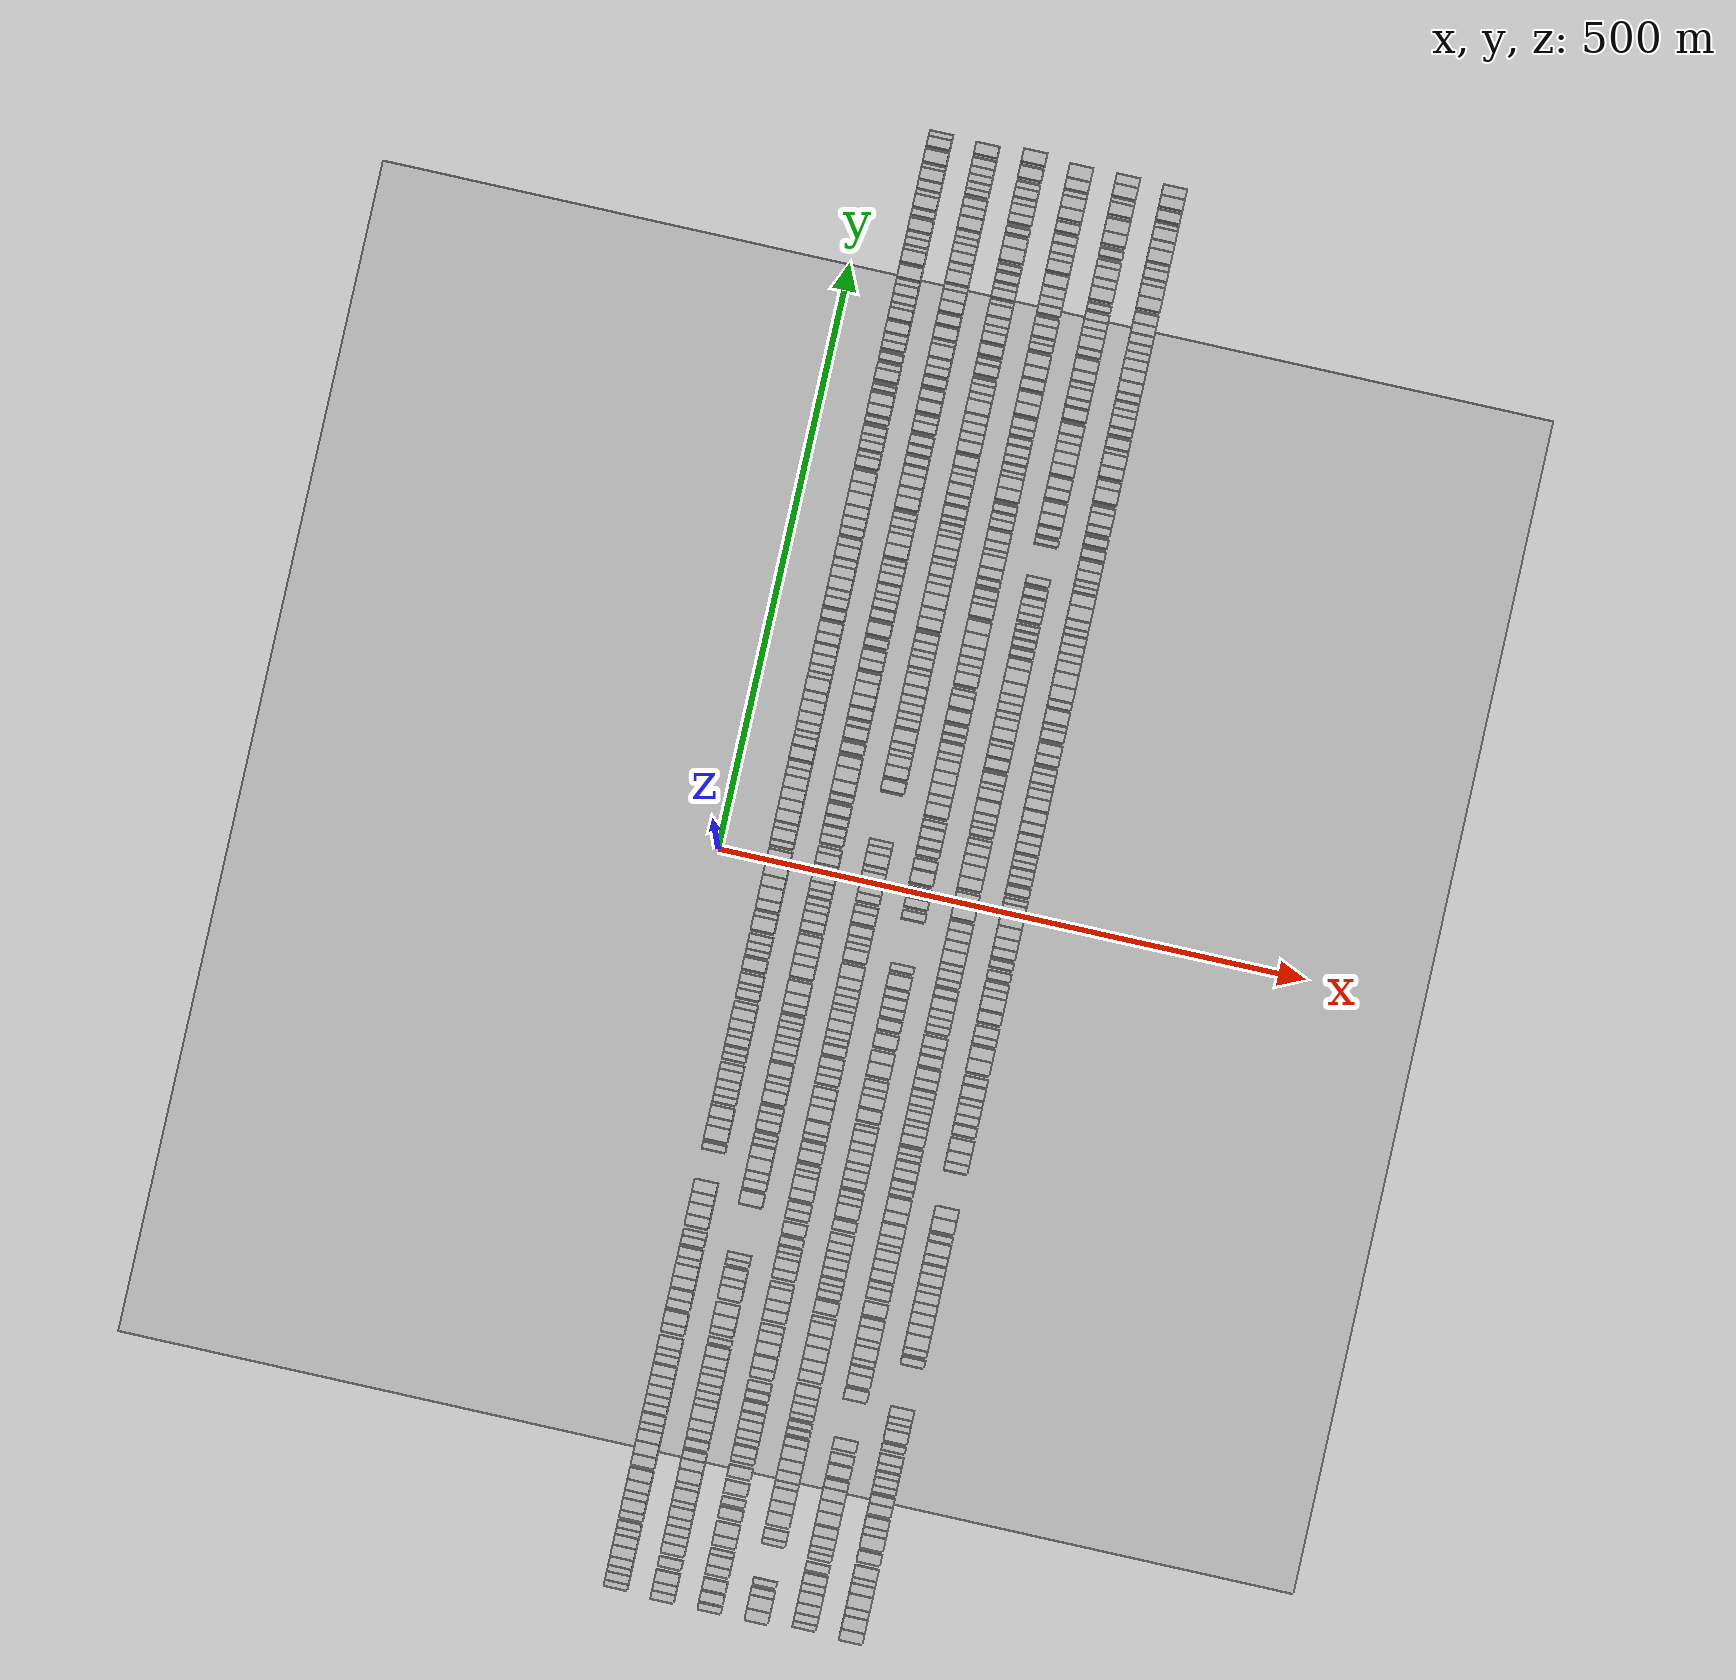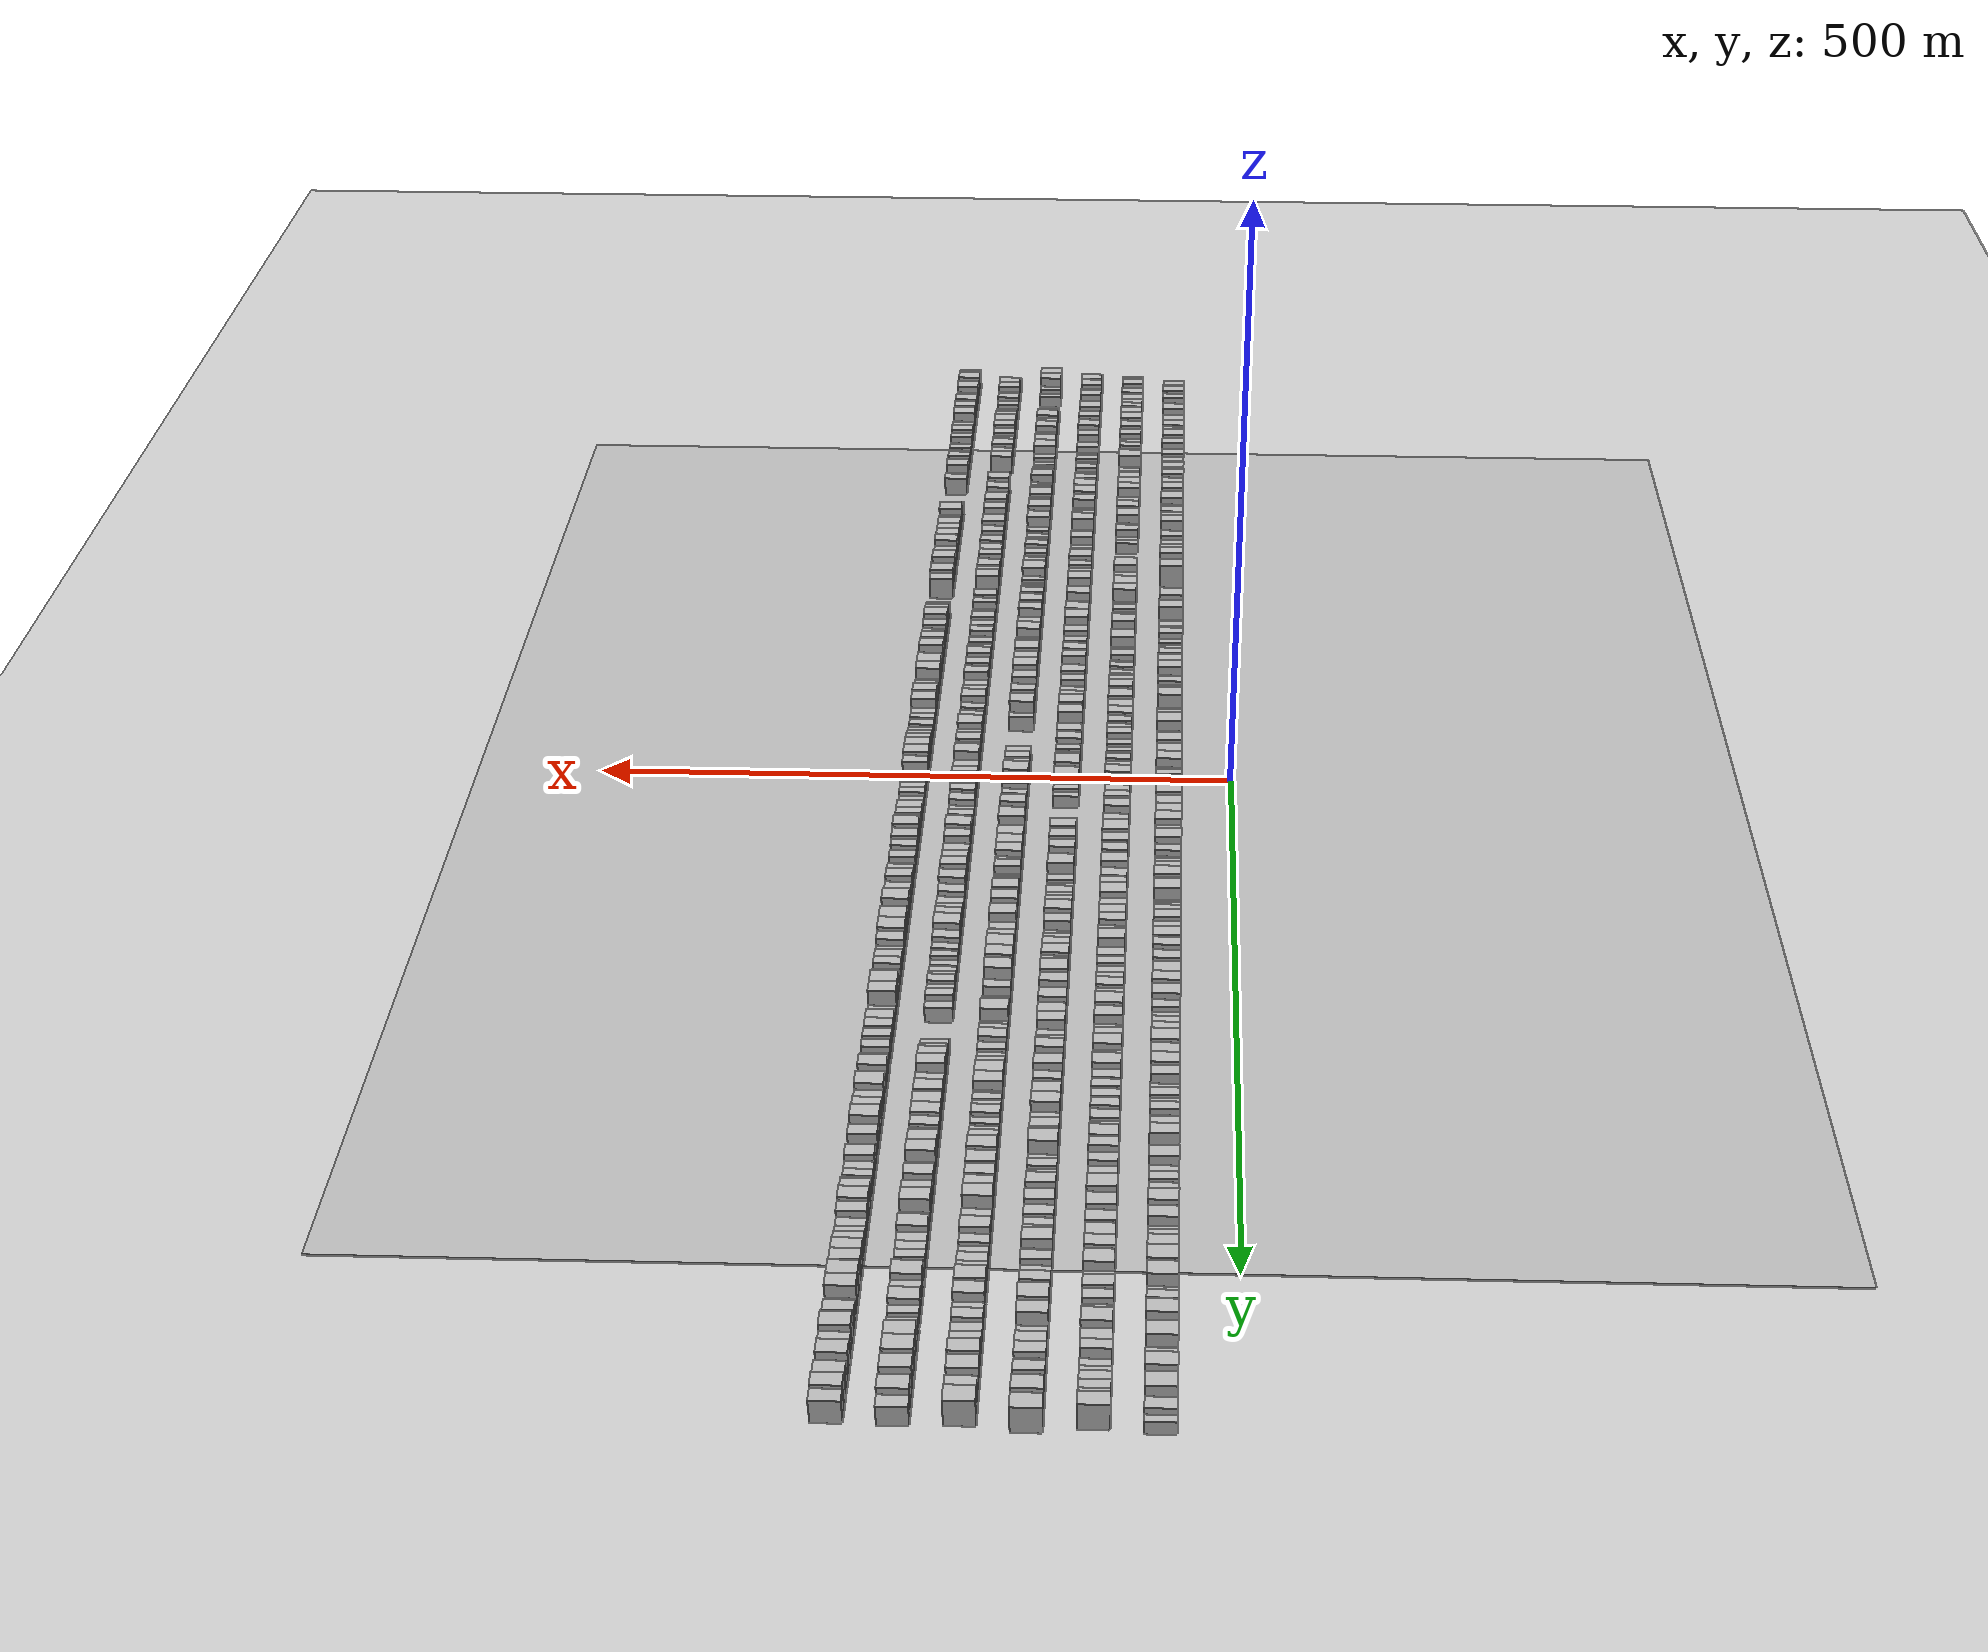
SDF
<?xml version="1.0" encoding="utf-8"?>

<sdf version="1.6">

   <world name="default">

      <gui fullscreen="0">

         <camera name="user_camera">

            <pose>-15 0 4.57585 0 0 0</pose>

            <view_controller>orbit</view_controller>

         </camera>

      </gui>

      <scene>

         <sky>

           <clouds>

             <speed>12</speed>

           </clouds>

         </sky>

         <ambient>0.4 0.4 0.4 1</ambient>

         <background>0.7 0.7 0.7 1</background>

         <shadows>1</shadows>

      </scene>

      <gravity>0 0 -9.8066</gravity>

      <magnetic_field>6e-06 2.3e-05 -4.2e-05</magnetic_field>

      <physics default="0" name="default_physics" type="ode">

         <ode>

            <solver>

               <type>quick</type>

               <iters>10</iters>

               <sor>1.0</sor>

               <use_dynamic_moi_rescaling>0</use_dynamic_moi_rescaling>

            </solver>

            <constraints>

               <cfm>0</cfm>

               <erp>0.2</erp>

               <contact_max_correcting_vel>100</contact_max_correcting_vel>

               <contact_surface_layer>0.001</contact_surface_layer>

            </constraints>

         </ode>

         <max_step_size>0.004</max_step_size>

         <real_time_factor>1</real_time_factor>

         <real_time_update_rate>250</real_time_update_rate>

      </physics>

      <light name="sun" type="directional">

         <cast_shadows>1</cast_shadows>

         <pose>0 0 10 0 0 0</pose>

         <diffuse>0.8 0.8 0.8 1</diffuse>

         <specular>0.2 0.2 0.2 1</specular>

         <attenuation>

            <range>1000</range>

            <constant>0.9</constant>

            <linear>0.01</linear>

            <quadratic>0.001</quadratic>

         </attenuation>

         <direction>-0.5 0.1 -0.9</direction>

      </light>

      <include>

         <name>ground_plane_1</name>

         <uri>model://HANNAS_ground_plane</uri>

         <pose>0 0 0  0 0 0</pose>

      </include>

      <include>

         <name>ground_plane_2</name>

         <uri>model://HANNAS_ground_plane</uri>

         <pose>100 0 0  0 0 0</pose>

      </include>

      <model name="building_1">

         <static>1</static>

         <pose frame="">50.0000 -615.3436 0 0.000000 0.000000 0.000000</pose>

         <link name="link">

            <pose frame="">0 0 6.00 0 0 0</pose>

            <collision name="collision">

               <geometry>

                  <box>

                     <size>20.0000 5.3127 12.0000</size>

                  </box>

               </geometry>

               <max_contacts>10</max_contacts>

               <surface>

                  <contact>

                     <ode/>

                  </contact>

                  <bounce/>

                  <friction>

                     <torsional>

                        <ode/>

                     </torsional>

                     <ode/>

                  </friction>

               </surface>

            </collision>

            <visual name="visual">

               <cast_shadows>0</cast_shadows>

               <geometry>

                  <box>

                     <size>20.0000 5.3127 12.0000</size>

                  </box>

               </geometry>

               <material>

                  <script>

                     <uri>model://HANNAS_wall/materials/scripts</uri>

                     <uri>model://HANNAS_wall/materials/textures</uri>

                     <name>vrc/HANNAS_wall</name>

                  </script>

               </material>

            </visual>

            <self_collide>0</self_collide>

            <enable_wind>0</enable_wind>

            <kinematic>0</kinematic>

         </link>

      </model>

      <model name="building_2">

         <static>1</static>

         <pose frame="">50.0000 -609.0719 0 0.000000 0.000000 0.000000</pose>

         <link name="link">

            <pose frame="">0 0 7.50 0 0 0</pose>

            <collision name="collision">

               <geometry>

                  <box>

                     <size>20.0000 7.2307 15.0000</size>

                  </box>

               </geometry>

               <max_contacts>10</max_contacts>

               <surface>

                  <contact>

                     <ode/>

                  </contact>

                  <bounce/>

                  <friction>

                     <torsional>

                        <ode/>

                     </torsional>

                     <ode/>

                  </friction>

               </surface>

            </collision>

            <visual name="visual">

               <cast_shadows>0</cast_shadows>

               <geometry>

                  <box>

                     <size>20.0000 7.2307 15.0000</size>

                  </box>

               </geometry>

               <material>

                  <script>

                     <uri>model://HANNAS_wall/materials/scripts</uri>

                     <uri>model://HANNAS_wall/materials/textures</uri>

                     <name>vrc/HANNAS_wall</name>

                  </script>

               </material>

            </visual>

            <self_collide>0</self_collide>

            <enable_wind>0</enable_wind>

            <kinematic>0</kinematic>

         </link>

      </model>

      <model name="building_3">

         <static>1</static>

         <pose frame="">50.0000 -602.7401 0 0.000000 0.000000 0.000000</pose>

         <link name="link">

            <pose frame="">0 0 6.00 0 0 0</pose>

            <collision name="collision">

               <geometry>

                  <box>

                     <size>20.0000 5.4330 12.0000</size>

                  </box>

               </geometry>

               <max_contacts>10</max_contacts>

               <surface>

                  <contact>

                     <ode/>

                  </contact>

                  <bounce/>

                  <friction>

                     <torsional>

                        <ode/>

                     </torsional>

                     <ode/>

                  </friction>

               </surface>

            </collision>

            <visual name="visual">

               <cast_shadows>0</cast_shadows>

               <geometry>

                  <box>

                     <size>20.0000 5.4330 12.0000</size>

                  </box>

               </geometry>

               <material>

                  <script>

                     <uri>model://HANNAS_wall/materials/scripts</uri>

                     <uri>model://HANNAS_wall/materials/textures</uri>

                     <name>vrc/HANNAS_wall</name>

                  </script>

               </material>

            </visual>

            <self_collide>0</self_collide>

            <enable_wind>0</enable_wind>

            <kinematic>0</kinematic>

         </link>

      </model>

      <model name="building_4">

         <static>1</static>

         <pose frame="">50.0000 -596.3032 0 0.000000 0.000000 0.000000</pose>

         <link name="link">

            <pose frame="">0 0 9.00 0 0 0</pose>

            <collision name="collision">

               <geometry>

                  <box>

                     <size>20.0000 7.4407 18.0000</size>

                  </box>

               </geometry>

               <max_contacts>10</max_contacts>

               <surface>

                  <contact>

                     <ode/>

                  </contact>

                  <bounce/>

                  <friction>

                     <torsional>

                        <ode/>

                     </torsional>

                     <ode/>

                  </friction>

               </surface>

            </collision>

            <visual name="visual">

               <cast_shadows>0</cast_shadows>

               <geometry>

                  <box>

                     <size>20.0000 7.4407 18.0000</size>

                  </box>

               </geometry>

               <material>

                  <script>

                     <uri>model://HANNAS_wall/materials/scripts</uri>

                     <uri>model://HANNAS_wall/materials/textures</uri>

                     <name>vrc/HANNAS_wall</name>

                  </script>

               </material>

            </visual>

            <self_collide>0</self_collide>

            <enable_wind>0</enable_wind>

            <kinematic>0</kinematic>

         </link>

      </model>

      <model name="building_5">

         <static>1</static>

         <pose frame="">50.0000 -587.6780 0 0.000000 0.000000 0.000000</pose>

         <link name="link">

            <pose frame="">0 0 10.50 0 0 0</pose>

            <collision name="collision">

               <geometry>

                  <box>

                     <size>20.0000 9.8098 21.0000</size>

                  </box>

               </geometry>

               <max_contacts>10</max_contacts>

               <surface>

                  <contact>

                     <ode/>

                  </contact>

                  <bounce/>

                  <friction>

                     <torsional>

                        <ode/>

                     </torsional>

                     <ode/>

                  </friction>

               </surface>

            </collision>

            <visual name="visual">

               <cast_shadows>0</cast_shadows>

               <geometry>

                  <box>

                     <size>20.0000 9.8098 21.0000</size>

                  </box>

               </geometry>

               <material>

                  <script>

                     <uri>model://HANNAS_wall/materials/scripts</uri>

                     <uri>model://HANNAS_wall/materials/textures</uri>

                     <name>vrc/HANNAS_wall</name>

                  </script>

               </material>

            </visual>

            <self_collide>0</self_collide>

            <enable_wind>0</enable_wind>

            <kinematic>0</kinematic>

         </link>

      </model>

      <model name="building_6">

         <static>1</static>

         <pose frame="">50.0000 -578.3463 0 0.000000 0.000000 0.000000</pose>

         <link name="link">

            <pose frame="">0 0 9.00 0 0 0</pose>

            <collision name="collision">

               <geometry>

                  <box>

                     <size>20.0000 8.8537 18.0000</size>

                  </box>

               </geometry>

               <max_contacts>10</max_contacts>

               <surface>

                  <contact>

                     <ode/>

                  </contact>

                  <bounce/>

                  <friction>

                     <torsional>

                        <ode/>

                     </torsional>

                     <ode/>

                  </friction>

               </surface>

            </collision>

            <visual name="visual">

               <cast_shadows>0</cast_shadows>

               <geometry>

                  <box>

                     <size>20.0000 8.8537 18.0000</size>

                  </box>

               </geometry>

               <material>

                  <script>

                     <uri>model://HANNAS_wall/materials/scripts</uri>

                     <uri>model://HANNAS_wall/materials/textures</uri>

                     <name>vrc/HANNAS_wall</name>

                  </script>

               </material>

            </visual>

            <self_collide>0</self_collide>

            <enable_wind>0</enable_wind>

            <kinematic>0</kinematic>

         </link>

      </model>

      <model name="building_7">

         <static>1</static>

         <pose frame="">50.0000 -571.0688 0 0.000000 0.000000 0.000000</pose>

         <link name="link">

            <pose frame="">0 0 6.00 0 0 0</pose>

            <collision name="collision">

               <geometry>

                  <box>

                     <size>20.0000 5.7012 12.0000</size>

                  </box>

               </geometry>

               <max_contacts>10</max_contacts>

               <surface>

                  <contact>

                     <ode/>

                  </contact>

                  <bounce/>

                  <friction>

                     <torsional>

                        <ode/>

                     </torsional>

                     <ode/>

                  </friction>

               </surface>

            </collision>

            <visual name="visual">

               <cast_shadows>0</cast_shadows>

               <geometry>

                  <box>

                     <size>20.0000 5.7012 12.0000</size>

                  </box>

               </geometry>

               <material>

                  <script>

                     <uri>model://HANNAS_wall/materials/scripts</uri>

                     <uri>model://HANNAS_wall/materials/textures</uri>

                     <name>vrc/HANNAS_wall</name>

                  </script>

               </material>

            </visual>

            <self_collide>0</self_collide>

            <enable_wind>0</enable_wind>

            <kinematic>0</kinematic>

         </link>

      </model>

      <model name="building_8">

         <static>1</static>

         <pose frame="">50.0000 -565.0281 0 0.000000 0.000000 0.000000</pose>

         <link name="link">

            <pose frame="">0 0 7.50 0 0 0</pose>

            <collision name="collision">

               <geometry>

                  <box>

                     <size>20.0000 6.3803 15.0000</size>

                  </box>

               </geometry>

               <max_contacts>10</max_contacts>

               <surface>

                  <contact>

                     <ode/>

                  </contact>

                  <bounce/>

                  <friction>

                     <torsional>

                        <ode/>

                     </torsional>

                     <ode/>

                  </friction>

               </surface>

            </collision>

            <visual name="visual">

               <cast_shadows>0</cast_shadows>

               <geometry>

                  <box>

                     <size>20.0000 6.3803 15.0000</size>

                  </box>

               </geometry>

               <material>

                  <script>

                     <uri>model://HANNAS_wall/materials/scripts</uri>

                     <uri>model://HANNAS_wall/materials/textures</uri>

                     <name>vrc/HANNAS_wall</name>

                  </script>

               </material>

            </visual>

            <self_collide>0</self_collide>

            <enable_wind>0</enable_wind>

            <kinematic>0</kinematic>

         </link>

      </model>

      <model name="building_9">

         <static>1</static>

         <pose frame="">50.0000 -556.5736 0 0.000000 0.000000 0.000000</pose>

         <link name="link">

            <pose frame="">0 0 7.50 0 0 0</pose>

            <collision name="collision">

               <geometry>

                  <box>

                     <size>20.0000 6.5286 15.0000</size>

                  </box>

               </geometry>

               <max_contacts>10</max_contacts>

               <surface>

                  <contact>

                     <ode/>

                  </contact>

                  <bounce/>

                  <friction>

                     <torsional>

                        <ode/>

                     </torsional>

                     <ode/>

                  </friction>

               </surface>

            </collision>

            <visual name="visual">

               <cast_shadows>0</cast_shadows>

               <geometry>

                  <box>

                     <size>20.0000 6.5286 15.0000</size>

                  </box>

               </geometry>

               <material>

                  <script>

                     <uri>model://HANNAS_wall/materials/scripts</uri>

                     <uri>model://HANNAS_wall/materials/textures</uri>

                     <name>vrc/HANNAS_wall</name>

                  </script>

               </material>

            </visual>

            <self_collide>0</self_collide>

            <enable_wind>0</enable_wind>

            <kinematic>0</kinematic>

         </link>

      </model>

      <model name="building_10">

         <static>1</static>

         <pose frame="">50.0000 -548.2188 0 0.000000 0.000000 0.000000</pose>

         <link name="link">

            <pose frame="">0 0 12.00 0 0 0</pose>

            <collision name="collision">

               <geometry>

                  <box>

                     <size>20.0000 10.1811 24.0000</size>

                  </box>

               </geometry>

               <max_contacts>10</max_contacts>

               <surface>

                  <contact>

                     <ode/>

                  </contact>

                  <bounce/>

                  <friction>

                     <torsional>

                        <ode/>

                     </torsional>

                     <ode/>

                  </friction>

               </surface>

            </collision>

            <visual name="visual">

               <cast_shadows>0</cast_shadows>

               <geometry>

                  <box>

                     <size>20.0000 10.1811 24.0000</size>

                  </box>

               </geometry>

               <material>

                  <script>

                     <uri>model://HANNAS_wall/materials/scripts</uri>

                     <uri>model://HANNAS_wall/materials/textures</uri>

                     <name>vrc/HANNAS_wall</name>

                  </script>

               </material>

            </visual>

            <self_collide>0</self_collide>

            <enable_wind>0</enable_wind>

            <kinematic>0</kinematic>

         </link>

      </model>

      <model name="building_11">

         <static>1</static>

         <pose frame="">50.0000 -539.7561 0 0.000000 0.000000 0.000000</pose>

         <link name="link">

            <pose frame="">0 0 7.50 0 0 0</pose>

            <collision name="collision">

               <geometry>

                  <box>

                     <size>20.0000 6.7444 15.0000</size>

                  </box>

               </geometry>

               <max_contacts>10</max_contacts>

               <surface>

                  <contact>

                     <ode/>

                  </contact>

                  <bounce/>

                  <friction>

                     <torsional>

                        <ode/>

                     </torsional>

                     <ode/>

                  </friction>

               </surface>

            </collision>

            <visual name="visual">

               <cast_shadows>0</cast_shadows>

               <geometry>

                  <box>

                     <size>20.0000 6.7444 15.0000</size>

                  </box>

               </geometry>

               <material>

                  <script>

                     <uri>model://HANNAS_wall/materials/scripts</uri>

                     <uri>model://HANNAS_wall/materials/textures</uri>

                     <name>vrc/HANNAS_wall</name>

                  </script>

               </material>

            </visual>

            <self_collide>0</self_collide>

            <enable_wind>0</enable_wind>

            <kinematic>0</kinematic>

         </link>

      </model>

      <model name="building_12">

         <static>1</static>

         <pose frame="">50.0000 -531.8514 0 0.000000 0.000000 0.000000</pose>

         <link name="link">

            <pose frame="">0 0 10.50 0 0 0</pose>

            <collision name="collision">

               <geometry>

                  <box>

                     <size>20.0000 9.0648 21.0000</size>

                  </box>

               </geometry>

               <max_contacts>10</max_contacts>

               <surface>

                  <contact>

                     <ode/>

                  </contact>

                  <bounce/>

                  <friction>

                     <torsional>

                        <ode/>

                     </torsional>

                     <ode/>

                  </friction>

               </surface>

            </collision>

            <visual name="visual">

               <cast_shadows>0</cast_shadows>

               <geometry>

                  <box>

                     <size>20.0000 9.0648 21.0000</size>

                  </box>

               </geometry>

               <material>

                  <script>

                     <uri>model://HANNAS_wall/materials/scripts</uri>

                     <uri>model://HANNAS_wall/materials/textures</uri>

                     <name>vrc/HANNAS_wall</name>

                  </script>

               </material>

            </visual>

            <self_collide>0</self_collide>

            <enable_wind>0</enable_wind>

            <kinematic>0</kinematic>

         </link>

      </model>

      <model name="building_13">

         <static>1</static>

         <pose frame="">50.0000 -522.1954 0 0.000000 0.000000 0.000000</pose>

         <link name="link">

            <pose frame="">0 0 10.50 0 0 0</pose>

            <collision name="collision">

               <geometry>

                  <box>

                     <size>20.0000 10.2471 21.0000</size>

                  </box>

               </geometry>

               <max_contacts>10</max_contacts>

               <surface>

                  <contact>

                     <ode/>

                  </contact>

                  <bounce/>

                  <friction>

                     <torsional>

                        <ode/>

                     </torsional>

                     <ode/>

                  </friction>

               </surface>

            </collision>

            <visual name="visual">

               <cast_shadows>0</cast_shadows>

               <geometry>

                  <box>

                     <size>20.0000 10.2471 21.0000</size>

                  </box>

               </geometry>

               <material>

                  <script>

                     <uri>model://HANNAS_wall/materials/scripts</uri>

                     <uri>model://HANNAS_wall/materials/textures</uri>

                     <name>vrc/HANNAS_wall</name>

                  </script>

               </material>

            </visual>

            <self_collide>0</self_collide>

            <enable_wind>0</enable_wind>

            <kinematic>0</kinematic>

         </link>

      </model>

      <model name="building_14">

         <static>1</static>

         <pose frame="">50.0000 -510.2933 0 0.000000 0.000000 0.000000</pose>

         <link name="link">

            <pose frame="">0 0 10.50 0 0 0</pose>

            <collision name="collision">

               <geometry>

                  <box>

                     <size>20.0000 9.5571 21.0000</size>

                  </box>

               </geometry>

               <max_contacts>10</max_contacts>

               <surface>

                  <contact>

                     <ode/>

                  </contact>

                  <bounce/>

                  <friction>

                     <torsional>

                        <ode/>

                     </torsional>

                     <ode/>

                  </friction>

               </surface>

            </collision>

            <visual name="visual">

               <cast_shadows>0</cast_shadows>

               <geometry>

                  <box>

                     <size>20.0000 9.5571 21.0000</size>

                  </box>

               </geometry>

               <material>

                  <script>

                     <uri>model://HANNAS_wall/materials/scripts</uri>

                     <uri>model://HANNAS_wall/materials/textures</uri>

                     <name>vrc/HANNAS_wall</name>

                  </script>

               </material>

            </visual>

            <self_collide>0</self_collide>

            <enable_wind>0</enable_wind>

            <kinematic>0</kinematic>

         </link>

      </model>

      <model name="building_15">

         <static>1</static>

         <pose frame="">50.0000 -499.8959 0 0.000000 0.000000 0.000000</pose>

         <link name="link">

            <pose frame="">0 0 12.00 0 0 0</pose>

            <collision name="collision">

               <geometry>

                  <box>

                     <size>20.0000 11.2377 24.0000</size>

                  </box>

               </geometry>

               <max_contacts>10</max_contacts>

               <surface>

                  <contact>

                     <ode/>

                  </contact>

                  <bounce/>

                  <friction>

                     <torsional>

                        <ode/>

                     </torsional>

                     <ode/>

                  </friction>

               </surface>

            </collision>

            <visual name="visual">

               <cast_shadows>0</cast_shadows>

               <geometry>

                  <box>

                     <size>20.0000 11.2377 24.0000</size>

                  </box>

               </geometry>

               <material>

                  <script>

                     <uri>model://HANNAS_wall/materials/scripts</uri>

                     <uri>model://HANNAS_wall/materials/textures</uri>

                     <name>vrc/HANNAS_wall</name>

                  </script>

               </material>

            </visual>

            <self_collide>0</self_collide>

            <enable_wind>0</enable_wind>

            <kinematic>0</kinematic>

         </link>

      </model>

      <model name="building_16">

         <static>1</static>

         <pose frame="">50.0000 -489.2593 0 0.000000 0.000000 0.000000</pose>

         <link name="link">

            <pose frame="">0 0 10.50 0 0 0</pose>

            <collision name="collision">

               <geometry>

                  <box>

                     <size>20.0000 10.0355 21.0000</size>

                  </box>

               </geometry>

               <max_contacts>10</max_contacts>

               <surface>

                  <contact>

                     <ode/>

                  </contact>

                  <bounce/>

                  <friction>

                     <torsional>

                        <ode/>

                     </torsional>

                     <ode/>

                  </friction>

               </surface>

            </collision>

            <visual name="visual">

               <cast_shadows>0</cast_shadows>

               <geometry>

                  <box>

                     <size>20.0000 10.0355 21.0000</size>

                  </box>

               </geometry>

               <material>

                  <script>

                     <uri>model://HANNAS_wall/materials/scripts</uri>

                     <uri>model://HANNAS_wall/materials/textures</uri>

                     <name>vrc/HANNAS_wall</name>

                  </script>

               </material>

            </visual>

            <self_collide>0</self_collide>

            <enable_wind>0</enable_wind>

            <kinematic>0</kinematic>

         </link>

      </model>

      <model name="building_17">

         <static>1</static>

         <pose frame="">50.0000 -481.4059 0 0.000000 0.000000 0.000000</pose>

         <link name="link">

            <pose frame="">0 0 6.00 0 0 0</pose>

            <collision name="collision">

               <geometry>

                  <box>

                     <size>20.0000 5.6714 12.0000</size>

                  </box>

               </geometry>

               <max_contacts>10</max_contacts>

               <surface>

                  <contact>

                     <ode/>

                  </contact>

                  <bounce/>

                  <friction>

                     <torsional>

                        <ode/>

                     </torsional>

                     <ode/>

                  </friction>

               </surface>

            </collision>

            <visual name="visual">

               <cast_shadows>0</cast_shadows>

               <geometry>

                  <box>

                     <size>20.0000 5.6714 12.0000</size>

                  </box>

               </geometry>

               <material>

                  <script>

                     <uri>model://HANNAS_wall/materials/scripts</uri>

                     <uri>model://HANNAS_wall/materials/textures</uri>

                     <name>vrc/HANNAS_wall</name>

                  </script>

               </material>

            </visual>

            <self_collide>0</self_collide>

            <enable_wind>0</enable_wind>

            <kinematic>0</kinematic>

         </link>

      </model>

      <model name="building_18">

         <static>1</static>

         <pose frame="">50.0000 -474.4728 0 0.000000 0.000000 0.000000</pose>

         <link name="link">

            <pose frame="">0 0 9.00 0 0 0</pose>

            <collision name="collision">

               <geometry>

                  <box>

                     <size>20.0000 8.1948 18.0000</size>

                  </box>

               </geometry>

               <max_contacts>10</max_contacts>

               <surface>

                  <contact>

                     <ode/>

                  </contact>

                  <bounce/>

                  <friction>

                     <torsional>

                        <ode/>

                     </torsional>

                     <ode/>

                  </friction>

               </surface>

            </collision>

            <visual name="visual">

               <cast_shadows>0</cast_shadows>

               <geometry>

                  <box>

                     <size>20.0000 8.1948 18.0000</size>

                  </box>

               </geometry>

               <material>

                  <script>

                     <uri>model://HANNAS_wall/materials/scripts</uri>

                     <uri>model://HANNAS_wall/materials/textures</uri>

                     <name>vrc/HANNAS_wall</name>

                  </script>

               </material>

            </visual>

            <self_collide>0</self_collide>

            <enable_wind>0</enable_wind>

            <kinematic>0</kinematic>

         </link>

      </model>

      <model name="building_19">

         <static>1</static>

         <pose frame="">50.0000 -465.8986 0 0.000000 0.000000 0.000000</pose>

         <link name="link">

            <pose frame="">0 0 7.50 0 0 0</pose>

            <collision name="collision">

               <geometry>

                  <box>

                     <size>20.0000 6.9536 15.0000</size>

                  </box>

               </geometry>

               <max_contacts>10</max_contacts>

               <surface>

                  <contact>

                     <ode/>

                  </contact>

                  <bounce/>

                  <friction>

                     <torsional>

                        <ode/>

                     </torsional>

                     <ode/>

                  </friction>

               </surface>

            </collision>

            <visual name="visual">

               <cast_shadows>0</cast_shadows>

               <geometry>

                  <box>

                     <size>20.0000 6.9536 15.0000</size>

                  </box>

               </geometry>

               <material>

                  <script>

                     <uri>model://HANNAS_wall/materials/scripts</uri>

                     <uri>model://HANNAS_wall/materials/textures</uri>

                     <name>vrc/HANNAS_wall</name>

                  </script>

               </material>

            </visual>

            <self_collide>0</self_collide>

            <enable_wind>0</enable_wind>

            <kinematic>0</kinematic>

         </link>

      </model>

      <model name="building_20">

         <static>1</static>

         <pose frame="">50.0000 -458.7400 0 0.000000 0.000000 0.000000</pose>

         <link name="link">

            <pose frame="">0 0 7.50 0 0 0</pose>

            <collision name="collision">

               <geometry>

                  <box>

                     <size>20.0000 7.3635 15.0000</size>

                  </box>

               </geometry>

               <max_contacts>10</max_contacts>

               <surface>

                  <contact>

                     <ode/>

                  </contact>

                  <bounce/>

                  <friction>

                     <torsional>

                        <ode/>

                     </torsional>

                     <ode/>

                  </friction>

               </surface>

            </collision>

            <visual name="visual">

               <cast_shadows>0</cast_shadows>

               <geometry>

                  <box>

                     <size>20.0000 7.3635 15.0000</size>

                  </box>

               </geometry>

               <material>

                  <script>

                     <uri>model://HANNAS_wall/materials/scripts</uri>

                     <uri>model://HANNAS_wall/materials/textures</uri>

                     <name>vrc/HANNAS_wall</name>

                  </script>

               </material>

            </visual>

            <self_collide>0</self_collide>

            <enable_wind>0</enable_wind>

            <kinematic>0</kinematic>

         </link>

      </model>

      <model name="building_21">

         <static>1</static>

         <pose frame="">50.0000 -450.7693 0 0.000000 0.000000 0.000000</pose>

         <link name="link">

            <pose frame="">0 0 9.00 0 0 0</pose>

            <collision name="collision">

               <geometry>

                  <box>

                     <size>20.0000 8.5780 18.0000</size>

                  </box>

               </geometry>

               <max_contacts>10</max_contacts>

               <surface>

                  <contact>

                     <ode/>

                  </contact>

                  <bounce/>

                  <friction>

                     <torsional>

                        <ode/>

                     </torsional>

                     <ode/>

                  </friction>

               </surface>

            </collision>

            <visual name="visual">

               <cast_shadows>0</cast_shadows>

               <geometry>

                  <box>

                     <size>20.0000 8.5780 18.0000</size>

                  </box>

               </geometry>

               <material>

                  <script>

                     <uri>model://HANNAS_wall/materials/scripts</uri>

                     <uri>model://HANNAS_wall/materials/textures</uri>

                     <name>vrc/HANNAS_wall</name>

                  </script>

               </material>

            </visual>

            <self_collide>0</self_collide>

            <enable_wind>0</enable_wind>

            <kinematic>0</kinematic>

         </link>

      </model>

      <model name="building_22">

         <static>1</static>

         <pose frame="">50.0000 -442.4271 0 0.000000 0.000000 0.000000</pose>

         <link name="link">

            <pose frame="">0 0 9.00 0 0 0</pose>

            <collision name="collision">

               <geometry>

                  <box>

                     <size>20.0000 8.1065 18.0000</size>

                  </box>

               </geometry>

               <max_contacts>10</max_contacts>

               <surface>

                  <contact>

                     <ode/>

                  </contact>

                  <bounce/>

                  <friction>

                     <torsional>

                        <ode/>

                     </torsional>

                     <ode/>

                  </friction>

               </surface>

            </collision>

            <visual name="visual">

               <cast_shadows>0</cast_shadows>

               <geometry>

                  <box>

                     <size>20.0000 8.1065 18.0000</size>

                  </box>

               </geometry>

               <material>

                  <script>

                     <uri>model://HANNAS_wall/materials/scripts</uri>

                     <uri>model://HANNAS_wall/materials/textures</uri>

                     <name>vrc/HANNAS_wall</name>

                  </script>

               </material>

            </visual>

            <self_collide>0</self_collide>

            <enable_wind>0</enable_wind>

            <kinematic>0</kinematic>

         </link>

      </model>

      <model name="building_23">

         <static>1</static>

         <pose frame="">50.0000 -433.6353 0 0.000000 0.000000 0.000000</pose>

         <link name="link">

            <pose frame="">0 0 10.50 0 0 0</pose>

            <collision name="collision">

               <geometry>

                  <box>

                     <size>20.0000 9.4771 21.0000</size>

                  </box>

               </geometry>

               <max_contacts>10</max_contacts>

               <surface>

                  <contact>

                     <ode/>

                  </contact>

                  <bounce/>

                  <friction>

                     <torsional>

                        <ode/>

                     </torsional>

                     <ode/>

                  </friction>

               </surface>

            </collision>

            <visual name="visual">

               <cast_shadows>0</cast_shadows>

               <geometry>

                  <box>

                     <size>20.0000 9.4771 21.0000</size>

                  </box>

               </geometry>

               <material>

                  <script>

                     <uri>model://HANNAS_wall/materials/scripts</uri>

                     <uri>model://HANNAS_wall/materials/textures</uri>

                     <name>vrc/HANNAS_wall</name>

                  </script>

               </material>

            </visual>

            <self_collide>0</self_collide>

            <enable_wind>0</enable_wind>

            <kinematic>0</kinematic>

         </link>

      </model>

      <model name="building_24">

         <static>1</static>

         <pose frame="">50.0000 -424.2158 0 0.000000 0.000000 0.000000</pose>

         <link name="link">

            <pose frame="">0 0 9.00 0 0 0</pose>

            <collision name="collision">

               <geometry>

                  <box>

                     <size>20.0000 7.3619 18.0000</size>

                  </box>

               </geometry>

               <max_contacts>10</max_contacts>

               <surface>

                  <contact>

                     <ode/>

                  </contact>

                  <bounce/>

                  <friction>

                     <torsional>

                        <ode/>

                     </torsional>

                     <ode/>

                  </friction>

               </surface>

            </collision>

            <visual name="visual">

               <cast_shadows>0</cast_shadows>

               <geometry>

                  <box>

                     <size>20.0000 7.3619 18.0000</size>

                  </box>

               </geometry>

               <material>

                  <script>

                     <uri>model://HANNAS_wall/materials/scripts</uri>

                     <uri>model://HANNAS_wall/materials/textures</uri>

                     <name>vrc/HANNAS_wall</name>

                  </script>

               </material>

            </visual>

            <self_collide>0</self_collide>

            <enable_wind>0</enable_wind>

            <kinematic>0</kinematic>

         </link>

      </model>

      <model name="building_25">

         <static>1</static>

         <pose frame="">50.0000 -417.7162 0 0.000000 0.000000 0.000000</pose>

         <link name="link">

            <pose frame="">0 0 6.00 0 0 0</pose>

            <collision name="collision">

               <geometry>

                  <box>

                     <size>20.0000 5.6374 12.0000</size>

                  </box>

               </geometry>

               <max_contacts>10</max_contacts>

               <surface>

                  <contact>

                     <ode/>

                  </contact>

                  <bounce/>

                  <friction>

                     <torsional>

                        <ode/>

                     </torsional>

                     <ode/>

                  </friction>

               </surface>

            </collision>

            <visual name="visual">

               <cast_shadows>0</cast_shadows>

               <geometry>

                  <box>

                     <size>20.0000 5.6374 12.0000</size>

                  </box>

               </geometry>

               <material>

                  <script>

                     <uri>model://HANNAS_wall/materials/scripts</uri>

                     <uri>model://HANNAS_wall/materials/textures</uri>

                     <name>vrc/HANNAS_wall</name>

                  </script>

               </material>

            </visual>

            <self_collide>0</self_collide>

            <enable_wind>0</enable_wind>

            <kinematic>0</kinematic>

         </link>

      </model>

      <model name="building_26">

         <static>1</static>

         <pose frame="">50.0000 -409.8251 0 0.000000 0.000000 0.000000</pose>

         <link name="link">

            <pose frame="">0 0 10.50 0 0 0</pose>

            <collision name="collision">

               <geometry>

                  <box>

                     <size>20.0000 10.1448 21.0000</size>

                  </box>

               </geometry>

               <max_contacts>10</max_contacts>

               <surface>

                  <contact>

                     <ode/>

                  </contact>

                  <bounce/>

                  <friction>

                     <torsional>

                        <ode/>

                     </torsional>

                     <ode/>

                  </friction>

               </surface>

            </collision>

            <visual name="visual">

               <cast_shadows>0</cast_shadows>

               <geometry>

                  <box>

                     <size>20.0000 10.1448 21.0000</size>

                  </box>

               </geometry>

               <material>

                  <script>

                     <uri>model://HANNAS_wall/materials/scripts</uri>

                     <uri>model://HANNAS_wall/materials/textures</uri>

                     <name>vrc/HANNAS_wall</name>

                  </script>

               </material>

            </visual>

            <self_collide>0</self_collide>

            <enable_wind>0</enable_wind>

            <kinematic>0</kinematic>

         </link>

      </model>

      <model name="building_27">

         <static>1</static>

         <pose frame="">50.0000 -398.0976 0 0.000000 0.000000 0.000000</pose>

         <link name="link">

            <pose frame="">0 0 9.00 0 0 0</pose>

            <collision name="collision">

               <geometry>

                  <box>

                     <size>20.0000 7.3101 18.0000</size>

                  </box>

               </geometry>

               <max_contacts>10</max_contacts>

               <surface>

                  <contact>

                     <ode/>

                  </contact>

                  <bounce/>

                  <friction>

                     <torsional>

                        <ode/>

                     </torsional>

                     <ode/>

                  </friction>

               </surface>

            </collision>

            <visual name="visual">

               <cast_shadows>0</cast_shadows>

               <geometry>

                  <box>

                     <size>20.0000 7.3101 18.0000</size>

                  </box>

               </geometry>

               <material>

                  <script>

                     <uri>model://HANNAS_wall/materials/scripts</uri>

                     <uri>model://HANNAS_wall/materials/textures</uri>

                     <name>vrc/HANNAS_wall</name>

                  </script>

               </material>

            </visual>

            <self_collide>0</self_collide>

            <enable_wind>0</enable_wind>

            <kinematic>0</kinematic>

         </link>

      </model>

      <model name="building_28">

         <static>1</static>

         <pose frame="">50.0000 -388.9482 0 0.000000 0.000000 0.000000</pose>

         <link name="link">

            <pose frame="">0 0 12.00 0 0 0</pose>

            <collision name="collision">

               <geometry>

                  <box>

                     <size>20.0000 10.9887 24.0000</size>

                  </box>

               </geometry>

               <max_contacts>10</max_contacts>

               <surface>

                  <contact>

                     <ode/>

                  </contact>

                  <bounce/>

                  <friction>

                     <torsional>

                        <ode/>

                     </torsional>

                     <ode/>

                  </friction>

               </surface>

            </collision>

            <visual name="visual">

               <cast_shadows>0</cast_shadows>

               <geometry>

                  <box>

                     <size>20.0000 10.9887 24.0000</size>

                  </box>

               </geometry>

               <material>

                  <script>

                     <uri>model://HANNAS_wall/materials/scripts</uri>

                     <uri>model://HANNAS_wall/materials/textures</uri>

                     <name>vrc/HANNAS_wall</name>

                  </script>

               </material>

            </visual>

            <self_collide>0</self_collide>

            <enable_wind>0</enable_wind>

            <kinematic>0</kinematic>

         </link>

      </model>

      <model name="building_29">

         <static>1</static>

         <pose frame="">50.0000 -377.5386 0 0.000000 0.000000 0.000000</pose>

         <link name="link">

            <pose frame="">0 0 9.00 0 0 0</pose>

            <collision name="collision">

               <geometry>

                  <box>

                     <size>20.0000 7.8305 18.0000</size>

                  </box>

               </geometry>

               <max_contacts>10</max_contacts>

               <surface>

                  <contact>

                     <ode/>

                  </contact>

                  <bounce/>

                  <friction>

                     <torsional>

                        <ode/>

                     </torsional>

                     <ode/>

                  </friction>

               </surface>

            </collision>

            <visual name="visual">

               <cast_shadows>0</cast_shadows>

               <geometry>

                  <box>

                     <size>20.0000 7.8305 18.0000</size>

                  </box>

               </geometry>

               <material>

                  <script>

                     <uri>model://HANNAS_wall/materials/scripts</uri>

                     <uri>model://HANNAS_wall/materials/textures</uri>

                     <name>vrc/HANNAS_wall</name>

                  </script>

               </material>

            </visual>

            <self_collide>0</self_collide>

            <enable_wind>0</enable_wind>

            <kinematic>0</kinematic>

         </link>

      </model>

      <model name="building_30">

         <static>1</static>

         <pose frame="">50.0000 -369.2636 0 0.000000 0.000000 0.000000</pose>

         <link name="link">

            <pose frame="">0 0 10.50 0 0 0</pose>

            <collision name="collision">

               <geometry>

                  <box>

                     <size>20.0000 8.7196 21.0000</size>

                  </box>

               </geometry>

               <max_contacts>10</max_contacts>

               <surface>

                  <contact>

                     <ode/>

                  </contact>

                  <bounce/>

                  <friction>

                     <torsional>

                        <ode/>

                     </torsional>

                     <ode/>

                  </friction>

               </surface>

            </collision>

            <visual name="visual">

               <cast_shadows>0</cast_shadows>

               <geometry>

                  <box>

                     <size>20.0000 8.7196 21.0000</size>

                  </box>

               </geometry>

               <material>

                  <script>

                     <uri>model://HANNAS_wall/materials/scripts</uri>

                     <uri>model://HANNAS_wall/materials/textures</uri>

                     <name>vrc/HANNAS_wall</name>

                  </script>

               </material>

            </visual>

            <self_collide>0</self_collide>

            <enable_wind>0</enable_wind>

            <kinematic>0</kinematic>

         </link>

      </model>

      <model name="building_31">

         <static>1</static>

         <pose frame="">50.0000 -359.2427 0 0.000000 0.000000 0.000000</pose>

         <link name="link">

            <pose frame="">0 0 10.50 0 0 0</pose>

            <collision name="collision">

               <geometry>

                  <box>

                     <size>20.0000 9.3222 21.0000</size>

                  </box>

               </geometry>

               <max_contacts>10</max_contacts>

               <surface>

                  <contact>

                     <ode/>

                  </contact>

                  <bounce/>

                  <friction>

                     <torsional>

                        <ode/>

                     </torsional>

                     <ode/>

                  </friction>

               </surface>

            </collision>

            <visual name="visual">

               <cast_shadows>0</cast_shadows>

               <geometry>

                  <box>

                     <size>20.0000 9.3222 21.0000</size>

                  </box>

               </geometry>

               <material>

                  <script>

                     <uri>model://HANNAS_wall/materials/scripts</uri>

                     <uri>model://HANNAS_wall/materials/textures</uri>

                     <name>vrc/HANNAS_wall</name>

                  </script>

               </material>

            </visual>

            <self_collide>0</self_collide>

            <enable_wind>0</enable_wind>

            <kinematic>0</kinematic>

         </link>

      </model>

      <model name="building_32">

         <static>1</static>

         <pose frame="">50.0000 -349.2509 0 0.000000 0.000000 0.000000</pose>

         <link name="link">

            <pose frame="">0 0 12.00 0 0 0</pose>

            <collision name="collision">

               <geometry>

                  <box>

                     <size>20.0000 10.6614 24.0000</size>

                  </box>

               </geometry>

               <max_contacts>10</max_contacts>

               <surface>

                  <contact>

                     <ode/>

                  </contact>

                  <bounce/>

                  <friction>

                     <torsional>

                        <ode/>

                     </torsional>

                     <ode/>

                  </friction>

               </surface>

            </collision>

            <visual name="visual">

               <cast_shadows>0</cast_shadows>

               <geometry>

                  <box>

                     <size>20.0000 10.6614 24.0000</size>

                  </box>

               </geometry>

               <material>

                  <script>

                     <uri>model://HANNAS_wall/materials/scripts</uri>

                     <uri>model://HANNAS_wall/materials/textures</uri>

                     <name>vrc/HANNAS_wall</name>

                  </script>

               </material>

            </visual>

            <self_collide>0</self_collide>

            <enable_wind>0</enable_wind>

            <kinematic>0</kinematic>

         </link>

      </model>

      <model name="building_33">

         <static>1</static>

         <pose frame="">50.0000 -340.9512 0 0.000000 0.000000 0.000000</pose>

         <link name="link">

            <pose frame="">0 0 6.00 0 0 0</pose>

            <collision name="collision">

               <geometry>

                  <box>

                     <size>20.0000 5.9378 12.0000</size>

                  </box>

               </geometry>

               <max_contacts>10</max_contacts>

               <surface>

                  <contact>

                     <ode/>

                  </contact>

                  <bounce/>

                  <friction>

                     <torsional>

                        <ode/>

                     </torsional>

                     <ode/>

                  </friction>

               </surface>

            </collision>

            <visual name="visual">

               <cast_shadows>0</cast_shadows>

               <geometry>

                  <box>

                     <size>20.0000 5.9378 12.0000</size>

                  </box>

               </geometry>

               <material>

                  <script>

                     <uri>model://HANNAS_wall/materials/scripts</uri>

                     <uri>model://HANNAS_wall/materials/textures</uri>

                     <name>vrc/HANNAS_wall</name>

                  </script>

               </material>

            </visual>

            <self_collide>0</self_collide>

            <enable_wind>0</enable_wind>

            <kinematic>0</kinematic>

         </link>

      </model>

      <model name="building_34">

         <static>1</static>

         <pose frame="">50.0000 -333.6593 0 0.000000 0.000000 0.000000</pose>

         <link name="link">

            <pose frame="">0 0 9.00 0 0 0</pose>

            <collision name="collision">

               <geometry>

                  <box>

                     <size>20.0000 8.6461 18.0000</size>

                  </box>

               </geometry>

               <max_contacts>10</max_contacts>

               <surface>

                  <contact>

                     <ode/>

                  </contact>

                  <bounce/>

                  <friction>

                     <torsional>

                        <ode/>

                     </torsional>

                     <ode/>

                  </friction>

               </surface>

            </collision>

            <visual name="visual">

               <cast_shadows>0</cast_shadows>

               <geometry>

                  <box>

                     <size>20.0000 8.6461 18.0000</size>

                  </box>

               </geometry>

               <material>

                  <script>

                     <uri>model://HANNAS_wall/materials/scripts</uri>

                     <uri>model://HANNAS_wall/materials/textures</uri>

                     <name>vrc/HANNAS_wall</name>

                  </script>

               </material>

            </visual>

            <self_collide>0</self_collide>

            <enable_wind>0</enable_wind>

            <kinematic>0</kinematic>

         </link>

      </model>

      <model name="building_35">

         <static>1</static>

         <pose frame="">50.0000 -323.7536 0 0.000000 0.000000 0.000000</pose>

         <link name="link">

            <pose frame="">0 0 7.50 0 0 0</pose>

            <collision name="collision">

               <geometry>

                  <box>

                     <size>20.0000 7.1653 15.0000</size>

                  </box>

               </geometry>

               <max_contacts>10</max_contacts>

               <surface>

                  <contact>

                     <ode/>

                  </contact>

                  <bounce/>

                  <friction>

                     <torsional>

                        <ode/>

                     </torsional>

                     <ode/>

                  </friction>

               </surface>

            </collision>

            <visual name="visual">

               <cast_shadows>0</cast_shadows>

               <geometry>

                  <box>

                     <size>20.0000 7.1653 15.0000</size>

                  </box>

               </geometry>

               <material>

                  <script>

                     <uri>model://HANNAS_wall/materials/scripts</uri>

                     <uri>model://HANNAS_wall/materials/textures</uri>

                     <name>vrc/HANNAS_wall</name>

                  </script>

               </material>

            </visual>

            <self_collide>0</self_collide>

            <enable_wind>0</enable_wind>

            <kinematic>0</kinematic>

         </link>

      </model>

      <model name="building_36">

         <static>1</static>

         <pose frame="">50.0000 -317.3098 0 0.000000 0.000000 0.000000</pose>

         <link name="link">

            <pose frame="">0 0 6.00 0 0 0</pose>

            <collision name="collision">

               <geometry>

                  <box>

                     <size>20.0000 5.7222 12.0000</size>

                  </box>

               </geometry>

               <max_contacts>10</max_contacts>

               <surface>

                  <contact>

                     <ode/>

                  </contact>

                  <bounce/>

                  <friction>

                     <torsional>

                        <ode/>

                     </torsional>

                     <ode/>

                  </friction>

               </surface>

            </collision>

            <visual name="visual">

               <cast_shadows>0</cast_shadows>

               <geometry>

                  <box>

                     <size>20.0000 5.7222 12.0000</size>

                  </box>

               </geometry>

               <material>

                  <script>

                     <uri>model://HANNAS_wall/materials/scripts</uri>

                     <uri>model://HANNAS_wall/materials/textures</uri>

                     <name>vrc/HANNAS_wall</name>

                  </script>

               </material>

            </visual>

            <self_collide>0</self_collide>

            <enable_wind>0</enable_wind>

            <kinematic>0</kinematic>

         </link>

      </model>

      <model name="building_37">

         <static>1</static>

         <pose frame="">50.0000 -306.7887 0 0.000000 0.000000 0.000000</pose>

         <link name="link">

            <pose frame="">0 0 10.50 0 0 0</pose>

            <collision name="collision">

               <geometry>

                  <box>

                     <size>20.0000 9.3200 21.0000</size>

                  </box>

               </geometry>

               <max_contacts>10</max_contacts>

               <surface>

                  <contact>

                     <ode/>

                  </contact>

                  <bounce/>

                  <friction>

                     <torsional>

                        <ode/>

                     </torsional>

                     <ode/>

                  </friction>

               </surface>

            </collision>

            <visual name="visual">

               <cast_shadows>0</cast_shadows>

               <geometry>

                  <box>

                     <size>20.0000 9.3200 21.0000</size>

                  </box>

               </geometry>

               <material>

                  <script>

                     <uri>model://HANNAS_wall/materials/scripts</uri>

                     <uri>model://HANNAS_wall/materials/textures</uri>

                     <name>vrc/HANNAS_wall</name>

                  </script>

               </material>

            </visual>

            <self_collide>0</self_collide>

            <enable_wind>0</enable_wind>

            <kinematic>0</kinematic>

         </link>

      </model>

      <model name="building_38">

         <static>1</static>

         <pose frame="">50.0000 -296.9839 0 0.000000 0.000000 0.000000</pose>

         <link name="link">

            <pose frame="">0 0 12.00 0 0 0</pose>

            <collision name="collision">

               <geometry>

                  <box>

                     <size>20.0000 10.2897 24.0000</size>

                  </box>

               </geometry>

               <max_contacts>10</max_contacts>

               <surface>

                  <contact>

                     <ode/>

                  </contact>

                  <bounce/>

                  <friction>

                     <torsional>

                        <ode/>

                     </torsional>

                     <ode/>

                  </friction>

               </surface>

            </collision>

            <visual name="visual">

               <cast_shadows>0</cast_shadows>

               <geometry>

                  <box>

                     <size>20.0000 10.2897 24.0000</size>

                  </box>

               </geometry>

               <material>

                  <script>

                     <uri>model://HANNAS_wall/materials/scripts</uri>

                     <uri>model://HANNAS_wall/materials/textures</uri>

                     <name>vrc/HANNAS_wall</name>

                  </script>

               </material>

            </visual>

            <self_collide>0</self_collide>

            <enable_wind>0</enable_wind>

            <kinematic>0</kinematic>

         </link>

      </model>

      <model name="building_39">

         <static>1</static>

         <pose frame="">50.0000 -287.4079 0 0.000000 0.000000 0.000000</pose>

         <link name="link">

            <pose frame="">0 0 9.00 0 0 0</pose>

            <collision name="collision">

               <geometry>

                  <box>

                     <size>20.0000 8.8624 18.0000</size>

                  </box>

               </geometry>

               <max_contacts>10</max_contacts>

               <surface>

                  <contact>

                     <ode/>

                  </contact>

                  <bounce/>

                  <friction>

                     <torsional>

                        <ode/>

                     </torsional>

                     <ode/>

                  </friction>

               </surface>

            </collision>

            <visual name="visual">

               <cast_shadows>0</cast_shadows>

               <geometry>

                  <box>

                     <size>20.0000 8.8624 18.0000</size>

                  </box>

               </geometry>

               <material>

                  <script>

                     <uri>model://HANNAS_wall/materials/scripts</uri>

                     <uri>model://HANNAS_wall/materials/textures</uri>

                     <name>vrc/HANNAS_wall</name>

                  </script>

               </material>

            </visual>

            <self_collide>0</self_collide>

            <enable_wind>0</enable_wind>

            <kinematic>0</kinematic>

         </link>

      </model>

      <model name="building_40">

         <static>1</static>

         <pose frame="">50.0000 -277.5748 0 0.000000 0.000000 0.000000</pose>

         <link name="link">

            <pose frame="">0 0 12.00 0 0 0</pose>

            <collision name="collision">

               <geometry>

                  <box>

                     <size>20.0000 10.8038 24.0000</size>

                  </box>

               </geometry>

               <max_contacts>10</max_contacts>

               <surface>

                  <contact>

                     <ode/>

                  </contact>

                  <bounce/>

                  <friction>

                     <torsional>

                        <ode/>

                     </torsional>

                     <ode/>

                  </friction>

               </surface>

            </collision>

            <visual name="visual">

               <cast_shadows>0</cast_shadows>

               <geometry>

                  <box>

                     <size>20.0000 10.8038 24.0000</size>

                  </box>

               </geometry>

               <material>

                  <script>

                     <uri>model://HANNAS_wall/materials/scripts</uri>

                     <uri>model://HANNAS_wall/materials/textures</uri>

                     <name>vrc/HANNAS_wall</name>

                  </script>

               </material>

            </visual>

            <self_collide>0</self_collide>

            <enable_wind>0</enable_wind>

            <kinematic>0</kinematic>

         </link>

      </model>

      <model name="building_41">

         <static>1</static>

         <pose frame="">50.0000 -243.2245 0 0.000000 0.000000 0.000000</pose>

         <link name="link">

            <pose frame="">0 0 6.00 0 0 0</pose>

            <collision name="collision">

               <geometry>

                  <box>

                     <size>20.0000 5.9656 12.0000</size>

                  </box>

               </geometry>

               <max_contacts>10</max_contacts>

               <surface>

                  <contact>

                     <ode/>

                  </contact>

                  <bounce/>

                  <friction>

                     <torsional>

                        <ode/>

                     </torsional>

                     <ode/>

                  </friction>

               </surface>

            </collision>

            <visual name="visual">

               <cast_shadows>0</cast_shadows>

               <geometry>

                  <box>

                     <size>20.0000 5.9656 12.0000</size>

                  </box>

               </geometry>

               <material>

                  <script>

                     <uri>model://HANNAS_wall/materials/scripts</uri>

                     <uri>model://HANNAS_wall/materials/textures</uri>

                     <name>vrc/HANNAS_wall</name>

                  </script>

               </material>

            </visual>

            <self_collide>0</self_collide>

            <enable_wind>0</enable_wind>

            <kinematic>0</kinematic>

         </link>

      </model>

      <model name="building_42">

         <static>1</static>

         <pose frame="">50.0000 -232.3315 0 0.000000 0.000000 0.000000</pose>

         <link name="link">

            <pose frame="">0 0 12.00 0 0 0</pose>

            <collision name="collision">

               <geometry>

                  <box>

                     <size>20.0000 11.8202 24.0000</size>

                  </box>

               </geometry>

               <max_contacts>10</max_contacts>

               <surface>

                  <contact>

                     <ode/>

                  </contact>

                  <bounce/>

                  <friction>

                     <torsional>

                        <ode/>

                     </torsional>

                     <ode/>

                  </friction>

               </surface>

            </collision>

            <visual name="visual">

               <cast_shadows>0</cast_shadows>

               <geometry>

                  <box>

                     <size>20.0000 11.8202 24.0000</size>

                  </box>

               </geometry>

               <material>

                  <script>

                     <uri>model://HANNAS_wall/materials/scripts</uri>

                     <uri>model://HANNAS_wall/materials/textures</uri>

                     <name>vrc/HANNAS_wall</name>

                  </script>

               </material>

            </visual>

            <self_collide>0</self_collide>

            <enable_wind>0</enable_wind>

            <kinematic>0</kinematic>

         </link>

      </model>

      <model name="building_43">

         <static>1</static>

         <pose frame="">50.0000 -222.7907 0 0.000000 0.000000 0.000000</pose>

         <link name="link">

            <pose frame="">0 0 7.50 0 0 0</pose>

            <collision name="collision">

               <geometry>

                  <box>

                     <size>20.0000 7.2614 15.0000</size>

                  </box>

               </geometry>

               <max_contacts>10</max_contacts>

               <surface>

                  <contact>

                     <ode/>

                  </contact>

                  <bounce/>

                  <friction>

                     <torsional>

                        <ode/>

                     </torsional>

                     <ode/>

                  </friction>

               </surface>

            </collision>

            <visual name="visual">

               <cast_shadows>0</cast_shadows>

               <geometry>

                  <box>

                     <size>20.0000 7.2614 15.0000</size>

                  </box>

               </geometry>

               <material>

                  <script>

                     <uri>model://HANNAS_wall/materials/scripts</uri>

                     <uri>model://HANNAS_wall/materials/textures</uri>

                     <name>vrc/HANNAS_wall</name>

                  </script>

               </material>

            </visual>

            <self_collide>0</self_collide>

            <enable_wind>0</enable_wind>

            <kinematic>0</kinematic>

         </link>

      </model>

      <model name="building_44">

         <static>1</static>

         <pose frame="">50.0000 -214.2294 0 0.000000 0.000000 0.000000</pose>

         <link name="link">

            <pose frame="">0 0 12.00 0 0 0</pose>

            <collision name="collision">

               <geometry>

                  <box>

                     <size>20.0000 9.8612 24.0000</size>

                  </box>

               </geometry>

               <max_contacts>10</max_contacts>

               <surface>

                  <contact>

                     <ode/>

                  </contact>

                  <bounce/>

                  <friction>

                     <torsional>

                        <ode/>

                     </torsional>

                     <ode/>

                  </friction>

               </surface>

            </collision>

            <visual name="visual">

               <cast_shadows>0</cast_shadows>

               <geometry>

                  <box>

                     <size>20.0000 9.8612 24.0000</size>

                  </box>

               </geometry>

               <material>

                  <script>

                     <uri>model://HANNAS_wall/materials/scripts</uri>

                     <uri>model://HANNAS_wall/materials/textures</uri>

                     <name>vrc/HANNAS_wall</name>

                  </script>

               </material>

            </visual>

            <self_collide>0</self_collide>

            <enable_wind>0</enable_wind>

            <kinematic>0</kinematic>

         </link>

      </model>

      <model name="building_45">

         <static>1</static>

         <pose frame="">50.0000 -203.3863 0 0.000000 0.000000 0.000000</pose>

         <link name="link">

            <pose frame="">0 0 6.00 0 0 0</pose>

            <collision name="collision">

               <geometry>

                  <box>

                     <size>20.0000 5.8248 12.0000</size>

                  </box>

               </geometry>

               <max_contacts>10</max_contacts>

               <surface>

                  <contact>

                     <ode/>

                  </contact>

                  <bounce/>

                  <friction>

                     <torsional>

                        <ode/>

                     </torsional>

                     <ode/>

                  </friction>

               </surface>

            </collision>

            <visual name="visual">

               <cast_shadows>0</cast_shadows>

               <geometry>

                  <box>

                     <size>20.0000 5.8248 12.0000</size>

                  </box>

               </geometry>

               <material>

                  <script>

                     <uri>model://HANNAS_wall/materials/scripts</uri>

                     <uri>model://HANNAS_wall/materials/textures</uri>

                     <name>vrc/HANNAS_wall</name>

                  </script>

               </material>

            </visual>

            <self_collide>0</self_collide>

            <enable_wind>0</enable_wind>

            <kinematic>0</kinematic>

         </link>

      </model>

      <model name="building_46">

         <static>1</static>

         <pose frame="">50.0000 -197.1510 0 0.000000 0.000000 0.000000</pose>

         <link name="link">

            <pose frame="">0 0 7.50 0 0 0</pose>

            <collision name="collision">

               <geometry>

                  <box>

                     <size>20.0000 6.6458 15.0000</size>

                  </box>

               </geometry>

               <max_contacts>10</max_contacts>

               <surface>

                  <contact>

                     <ode/>

                  </contact>

                  <bounce/>

                  <friction>

                     <torsional>

                        <ode/>

                     </torsional>

                     <ode/>

                  </friction>

               </surface>

            </collision>

            <visual name="visual">

               <cast_shadows>0</cast_shadows>

               <geometry>

                  <box>

                     <size>20.0000 6.6458 15.0000</size>

                  </box>

               </geometry>

               <material>

                  <script>

                     <uri>model://HANNAS_wall/materials/scripts</uri>

                     <uri>model://HANNAS_wall/materials/textures</uri>

                     <name>vrc/HANNAS_wall</name>

                  </script>

               </material>

            </visual>

            <self_collide>0</self_collide>

            <enable_wind>0</enable_wind>

            <kinematic>0</kinematic>

         </link>

      </model>

      <model name="building_47">

         <static>1</static>

         <pose frame="">50.0000 -190.3913 0 0.000000 0.000000 0.000000</pose>

         <link name="link">

            <pose frame="">0 0 7.50 0 0 0</pose>

            <collision name="collision">

               <geometry>

                  <box>

                     <size>20.0000 6.8738 15.0000</size>

                  </box>

               </geometry>

               <max_contacts>10</max_contacts>

               <surface>

                  <contact>

                     <ode/>

                  </contact>

                  <bounce/>

                  <friction>

                     <torsional>

                        <ode/>

                     </torsional>

                     <ode/>

                  </friction>

               </surface>

            </collision>

            <visual name="visual">

               <cast_shadows>0</cast_shadows>

               <geometry>

                  <box>

                     <size>20.0000 6.8738 15.0000</size>

                  </box>

               </geometry>

               <material>

                  <script>

                     <uri>model://HANNAS_wall/materials/scripts</uri>

                     <uri>model://HANNAS_wall/materials/textures</uri>

                     <name>vrc/HANNAS_wall</name>

                  </script>

               </material>

            </visual>

            <self_collide>0</self_collide>

            <enable_wind>0</enable_wind>

            <kinematic>0</kinematic>

         </link>

      </model>

      <model name="building_48">

         <static>1</static>

         <pose frame="">50.0000 -182.7068 0 0.000000 0.000000 0.000000</pose>

         <link name="link">

            <pose frame="">0 0 9.00 0 0 0</pose>

            <collision name="collision">

               <geometry>

                  <box>

                     <size>20.0000 8.4952 18.0000</size>

                  </box>

               </geometry>

               <max_contacts>10</max_contacts>

               <surface>

                  <contact>

                     <ode/>

                  </contact>

                  <bounce/>

                  <friction>

                     <torsional>

                        <ode/>

                     </torsional>

                     <ode/>

                  </friction>

               </surface>

            </collision>

            <visual name="visual">

               <cast_shadows>0</cast_shadows>

               <geometry>

                  <box>

                     <size>20.0000 8.4952 18.0000</size>

                  </box>

               </geometry>

               <material>

                  <script>

                     <uri>model://HANNAS_wall/materials/scripts</uri>

                     <uri>model://HANNAS_wall/materials/textures</uri>

                     <name>vrc/HANNAS_wall</name>

                  </script>

               </material>

            </visual>

            <self_collide>0</self_collide>

            <enable_wind>0</enable_wind>

            <kinematic>0</kinematic>

         </link>

      </model>

      <model name="building_49">

         <static>1</static>

         <pose frame="">50.0000 -175.5505 0 0.000000 0.000000 0.000000</pose>

         <link name="link">

            <pose frame="">0 0 6.00 0 0 0</pose>

            <collision name="collision">

               <geometry>

                  <box>

                     <size>20.0000 5.8174 12.0000</size>

                  </box>

               </geometry>

               <max_contacts>10</max_contacts>

               <surface>

                  <contact>

                     <ode/>

                  </contact>

                  <bounce/>

                  <friction>

                     <torsional>

                        <ode/>

                     </torsional>

                     <ode/>

                  </friction>

               </surface>

            </collision>

            <visual name="visual">

               <cast_shadows>0</cast_shadows>

               <geometry>

                  <box>

                     <size>20.0000 5.8174 12.0000</size>

                  </box>

               </geometry>

               <material>

                  <script>

                     <uri>model://HANNAS_wall/materials/scripts</uri>

                     <uri>model://HANNAS_wall/materials/textures</uri>

                     <name>vrc/HANNAS_wall</name>

                  </script>

               </material>

            </visual>

            <self_collide>0</self_collide>

            <enable_wind>0</enable_wind>

            <kinematic>0</kinematic>

         </link>

      </model>

      <model name="building_50">

         <static>1</static>

         <pose frame="">50.0000 -166.8964 0 0.000000 0.000000 0.000000</pose>

         <link name="link">

            <pose frame="">0 0 6.00 0 0 0</pose>

            <collision name="collision">

               <geometry>

                  <box>

                     <size>20.0000 5.4906 12.0000</size>

                  </box>

               </geometry>

               <max_contacts>10</max_contacts>

               <surface>

                  <contact>

                     <ode/>

                  </contact>

                  <bounce/>

                  <friction>

                     <torsional>

                        <ode/>

                     </torsional>

                     <ode/>

                  </friction>

               </surface>

            </collision>

            <visual name="visual">

               <cast_shadows>0</cast_shadows>

               <geometry>

                  <box>

                     <size>20.0000 5.4906 12.0000</size>

                  </box>

               </geometry>

               <material>

                  <script>

                     <uri>model://HANNAS_wall/materials/scripts</uri>

                     <uri>model://HANNAS_wall/materials/textures</uri>

                     <name>vrc/HANNAS_wall</name>

                  </script>

               </material>

            </visual>

            <self_collide>0</self_collide>

            <enable_wind>0</enable_wind>

            <kinematic>0</kinematic>

         </link>

      </model>

      <model name="building_51">

         <static>1</static>

         <pose frame="">50.0000 -161.4066 0 0.000000 0.000000 0.000000</pose>

         <link name="link">

            <pose frame="">0 0 6.00 0 0 0</pose>

            <collision name="collision">

               <geometry>

                  <box>

                     <size>20.0000 5.4890 12.0000</size>

                  </box>

               </geometry>

               <max_contacts>10</max_contacts>

               <surface>

                  <contact>

                     <ode/>

                  </contact>

                  <bounce/>

                  <friction>

                     <torsional>

                        <ode/>

                     </torsional>

                     <ode/>

                  </friction>

               </surface>

            </collision>

            <visual name="visual">

               <cast_shadows>0</cast_shadows>

               <geometry>

                  <box>

                     <size>20.0000 5.4890 12.0000</size>

                  </box>

               </geometry>

               <material>

                  <script>

                     <uri>model://HANNAS_wall/materials/scripts</uri>

                     <uri>model://HANNAS_wall/materials/textures</uri>

                     <name>vrc/HANNAS_wall</name>

                  </script>

               </material>

            </visual>

            <self_collide>0</self_collide>

            <enable_wind>0</enable_wind>

            <kinematic>0</kinematic>

         </link>

      </model>

      <model name="building_52">

         <static>1</static>

         <pose frame="">50.0000 -153.7941 0 0.000000 0.000000 0.000000</pose>

         <link name="link">

            <pose frame="">0 0 9.00 0 0 0</pose>

            <collision name="collision">

               <geometry>

                  <box>

                     <size>20.0000 7.7361 18.0000</size>

                  </box>

               </geometry>

               <max_contacts>10</max_contacts>

               <surface>

                  <contact>

                     <ode/>

                  </contact>

                  <bounce/>

                  <friction>

                     <torsional>

                        <ode/>

                     </torsional>

                     <ode/>

                  </friction>

               </surface>

            </collision>

            <visual name="visual">

               <cast_shadows>0</cast_shadows>

               <geometry>

                  <box>

                     <size>20.0000 7.7361 18.0000</size>

                  </box>

               </geometry>

               <material>

                  <script>

                     <uri>model://HANNAS_wall/materials/scripts</uri>

                     <uri>model://HANNAS_wall/materials/textures</uri>

                     <name>vrc/HANNAS_wall</name>

                  </script>

               </material>

            </visual>

            <self_collide>0</self_collide>

            <enable_wind>0</enable_wind>

            <kinematic>0</kinematic>

         </link>

      </model>

      <model name="building_53">

         <static>1</static>

         <pose frame="">50.0000 -147.0172 0 0.000000 0.000000 0.000000</pose>

         <link name="link">

            <pose frame="">0 0 6.00 0 0 0</pose>

            <collision name="collision">

               <geometry>

                  <box>

                     <size>20.0000 5.8177 12.0000</size>

                  </box>

               </geometry>

               <max_contacts>10</max_contacts>

               <surface>

                  <contact>

                     <ode/>

                  </contact>

                  <bounce/>

                  <friction>

                     <torsional>

                        <ode/>

                     </torsional>

                     <ode/>

                  </friction>

               </surface>

            </collision>

            <visual name="visual">

               <cast_shadows>0</cast_shadows>

               <geometry>

                  <box>

                     <size>20.0000 5.8177 12.0000</size>

                  </box>

               </geometry>

               <material>

                  <script>

                     <uri>model://HANNAS_wall/materials/scripts</uri>

                     <uri>model://HANNAS_wall/materials/textures</uri>

                     <name>vrc/HANNAS_wall</name>

                  </script>

               </material>

            </visual>

            <self_collide>0</self_collide>

            <enable_wind>0</enable_wind>

            <kinematic>0</kinematic>

         </link>

      </model>

      <model name="building_54">

         <static>1</static>

         <pose frame="">50.0000 -139.8735 0 0.000000 0.000000 0.000000</pose>

         <link name="link">

            <pose frame="">0 0 10.50 0 0 0</pose>

            <collision name="collision">

               <geometry>

                  <box>

                     <size>20.0000 8.4696 21.0000</size>

                  </box>

               </geometry>

               <max_contacts>10</max_contacts>

               <surface>

                  <contact>

                     <ode/>

                  </contact>

                  <bounce/>

                  <friction>

                     <torsional>

                        <ode/>

                     </torsional>

                     <ode/>

                  </friction>

               </surface>

            </collision>

            <visual name="visual">

               <cast_shadows>0</cast_shadows>

               <geometry>

                  <box>

                     <size>20.0000 8.4696 21.0000</size>

                  </box>

               </geometry>

               <material>

                  <script>

                     <uri>model://HANNAS_wall/materials/scripts</uri>

                     <uri>model://HANNAS_wall/materials/textures</uri>

                     <name>vrc/HANNAS_wall</name>

                  </script>

               </material>

            </visual>

            <self_collide>0</self_collide>

            <enable_wind>0</enable_wind>

            <kinematic>0</kinematic>

         </link>

      </model>

      <model name="building_55">

         <static>1</static>

         <pose frame="">50.0000 -130.9446 0 0.000000 0.000000 0.000000</pose>

         <link name="link">

            <pose frame="">0 0 10.50 0 0 0</pose>

            <collision name="collision">

               <geometry>

                  <box>

                     <size>20.0000 9.3882 21.0000</size>

                  </box>

               </geometry>

               <max_contacts>10</max_contacts>

               <surface>

                  <contact>

                     <ode/>

                  </contact>

                  <bounce/>

                  <friction>

                     <torsional>

                        <ode/>

                     </torsional>

                     <ode/>

                  </friction>

               </surface>

            </collision>

            <visual name="visual">

               <cast_shadows>0</cast_shadows>

               <geometry>

                  <box>

                     <size>20.0000 9.3882 21.0000</size>

                  </box>

               </geometry>

               <material>

                  <script>

                     <uri>model://HANNAS_wall/materials/scripts</uri>

                     <uri>model://HANNAS_wall/materials/textures</uri>

                     <name>vrc/HANNAS_wall</name>

                  </script>

               </material>

            </visual>

            <self_collide>0</self_collide>

            <enable_wind>0</enable_wind>

            <kinematic>0</kinematic>

         </link>

      </model>

      <model name="building_56">

         <static>1</static>

         <pose frame="">50.0000 -123.4166 0 0.000000 0.000000 0.000000</pose>

         <link name="link">

            <pose frame="">0 0 6.00 0 0 0</pose>

            <collision name="collision">

               <geometry>

                  <box>

                     <size>20.0000 5.6678 12.0000</size>

                  </box>

               </geometry>

               <max_contacts>10</max_contacts>

               <surface>

                  <contact>

                     <ode/>

                  </contact>

                  <bounce/>

                  <friction>

                     <torsional>

                        <ode/>

                     </torsional>

                     <ode/>

                  </friction>

               </surface>

            </collision>

            <visual name="visual">

               <cast_shadows>0</cast_shadows>

               <geometry>

                  <box>

                     <size>20.0000 5.6678 12.0000</size>

                  </box>

               </geometry>

               <material>

                  <script>

                     <uri>model://HANNAS_wall/materials/scripts</uri>

                     <uri>model://HANNAS_wall/materials/textures</uri>

                     <name>vrc/HANNAS_wall</name>

                  </script>

               </material>

            </visual>

            <self_collide>0</self_collide>

            <enable_wind>0</enable_wind>

            <kinematic>0</kinematic>

         </link>

      </model>

      <model name="building_57">

         <static>1</static>

         <pose frame="">50.0000 -113.6862 0 0.000000 0.000000 0.000000</pose>

         <link name="link">

            <pose frame="">0 0 9.00 0 0 0</pose>

            <collision name="collision">

               <geometry>

                  <box>

                     <size>20.0000 7.7929 18.0000</size>

                  </box>

               </geometry>

               <max_contacts>10</max_contacts>

               <surface>

                  <contact>

                     <ode/>

                  </contact>

                  <bounce/>

                  <friction>

                     <torsional>

                        <ode/>

                     </torsional>

                     <ode/>

                  </friction>

               </surface>

            </collision>

            <visual name="visual">

               <cast_shadows>0</cast_shadows>

               <geometry>

                  <box>

                     <size>20.0000 7.7929 18.0000</size>

                  </box>

               </geometry>

               <material>

                  <script>

                     <uri>model://HANNAS_wall/materials/scripts</uri>

                     <uri>model://HANNAS_wall/materials/textures</uri>

                     <name>vrc/HANNAS_wall</name>

                  </script>

               </material>

            </visual>

            <self_collide>0</self_collide>

            <enable_wind>0</enable_wind>

            <kinematic>0</kinematic>

         </link>

      </model>

      <model name="building_58">

         <static>1</static>

         <pose frame="">50.0000 -107.3409 0 0.000000 0.000000 0.000000</pose>

         <link name="link">

            <pose frame="">0 0 6.00 0 0 0</pose>

            <collision name="collision">

               <geometry>

                  <box>

                     <size>20.0000 4.8977 12.0000</size>

                  </box>

               </geometry>

               <max_contacts>10</max_contacts>

               <surface>

                  <contact>

                     <ode/>

                  </contact>

                  <bounce/>

                  <friction>

                     <torsional>

                        <ode/>

                     </torsional>

                     <ode/>

                  </friction>

               </surface>

            </collision>

            <visual name="visual">

               <cast_shadows>0</cast_shadows>

               <geometry>

                  <box>

                     <size>20.0000 4.8977 12.0000</size>

                  </box>

               </geometry>

               <material>

                  <script>

                     <uri>model://HANNAS_wall/materials/scripts</uri>

                     <uri>model://HANNAS_wall/materials/textures</uri>

                     <name>vrc/HANNAS_wall</name>

                  </script>

               </material>

            </visual>

            <self_collide>0</self_collide>

            <enable_wind>0</enable_wind>

            <kinematic>0</kinematic>

         </link>

      </model>

      <model name="building_59">

         <static>1</static>

         <pose frame="">50.0000 -100.8337 0 0.000000 0.000000 0.000000</pose>

         <link name="link">

            <pose frame="">0 0 9.00 0 0 0</pose>

            <collision name="collision">

               <geometry>

                  <box>

                     <size>20.0000 8.1168 18.0000</size>

                  </box>

               </geometry>

               <max_contacts>10</max_contacts>

               <surface>

                  <contact>

                     <ode/>

                  </contact>

                  <bounce/>

                  <friction>

                     <torsional>

                        <ode/>

                     </torsional>

                     <ode/>

                  </friction>

               </surface>

            </collision>

            <visual name="visual">

               <cast_shadows>0</cast_shadows>

               <geometry>

                  <box>

                     <size>20.0000 8.1168 18.0000</size>

                  </box>

               </geometry>

               <material>

                  <script>

                     <uri>model://HANNAS_wall/materials/scripts</uri>

                     <uri>model://HANNAS_wall/materials/textures</uri>

                     <name>vrc/HANNAS_wall</name>

                  </script>

               </material>

            </visual>

            <self_collide>0</self_collide>

            <enable_wind>0</enable_wind>

            <kinematic>0</kinematic>

         </link>

      </model>

      <model name="building_60">

         <static>1</static>

         <pose frame="">50.0000 -88.5986 0 0.000000 0.000000 0.000000</pose>

         <link name="link">

            <pose frame="">0 0 12.00 0 0 0</pose>

            <collision name="collision">

               <geometry>

                  <box>

                     <size>20.0000 10.3534 24.0000</size>

                  </box>

               </geometry>

               <max_contacts>10</max_contacts>

               <surface>

                  <contact>

                     <ode/>

                  </contact>

                  <bounce/>

                  <friction>

                     <torsional>

                        <ode/>

                     </torsional>

                     <ode/>

                  </friction>

               </surface>

            </collision>

            <visual name="visual">

               <cast_shadows>0</cast_shadows>

               <geometry>

                  <box>

                     <size>20.0000 10.3534 24.0000</size>

                  </box>

               </geometry>

               <material>

                  <script>

                     <uri>model://HANNAS_wall/materials/scripts</uri>

                     <uri>model://HANNAS_wall/materials/textures</uri>

                     <name>vrc/HANNAS_wall</name>

                  </script>

               </material>

            </visual>

            <self_collide>0</self_collide>

            <enable_wind>0</enable_wind>

            <kinematic>0</kinematic>

         </link>

      </model>

      <model name="building_61">

         <static>1</static>

         <pose frame="">50.0000 -78.8616 0 0.000000 0.000000 0.000000</pose>

         <link name="link">

            <pose frame="">0 0 6.00 0 0 0</pose>

            <collision name="collision">

               <geometry>

                  <box>

                     <size>20.0000 5.1204 12.0000</size>

                  </box>

               </geometry>

               <max_contacts>10</max_contacts>

               <surface>

                  <contact>

                     <ode/>

                  </contact>

                  <bounce/>

                  <friction>

                     <torsional>

                        <ode/>

                     </torsional>

                     <ode/>

                  </friction>

               </surface>

            </collision>

            <visual name="visual">

               <cast_shadows>0</cast_shadows>

               <geometry>

                  <box>

                     <size>20.0000 5.1204 12.0000</size>

                  </box>

               </geometry>

               <material>

                  <script>

                     <uri>model://HANNAS_wall/materials/scripts</uri>

                     <uri>model://HANNAS_wall/materials/textures</uri>

                     <name>vrc/HANNAS_wall</name>

                  </script>

               </material>

            </visual>

            <self_collide>0</self_collide>

            <enable_wind>0</enable_wind>

            <kinematic>0</kinematic>

         </link>

      </model>

      <model name="building_62">

         <static>1</static>

         <pose frame="">50.0000 -73.0884 0 0.000000 0.000000 0.000000</pose>

         <link name="link">

            <pose frame="">0 0 7.50 0 0 0</pose>

            <collision name="collision">

               <geometry>

                  <box>

                     <size>20.0000 6.4260 15.0000</size>

                  </box>

               </geometry>

               <max_contacts>10</max_contacts>

               <surface>

                  <contact>

                     <ode/>

                  </contact>

                  <bounce/>

                  <friction>

                     <torsional>

                        <ode/>

                     </torsional>

                     <ode/>

                  </friction>

               </surface>

            </collision>

            <visual name="visual">

               <cast_shadows>0</cast_shadows>

               <geometry>

                  <box>

                     <size>20.0000 6.4260 15.0000</size>

                  </box>

               </geometry>

               <material>

                  <script>

                     <uri>model://HANNAS_wall/materials/scripts</uri>

                     <uri>model://HANNAS_wall/materials/textures</uri>

                     <name>vrc/HANNAS_wall</name>

                  </script>

               </material>

            </visual>

            <self_collide>0</self_collide>

            <enable_wind>0</enable_wind>

            <kinematic>0</kinematic>

         </link>

      </model>

      <model name="building_63">

         <static>1</static>

         <pose frame="">50.0000 -66.5584 0 0.000000 0.000000 0.000000</pose>

         <link name="link">

            <pose frame="">0 0 7.50 0 0 0</pose>

            <collision name="collision">

               <geometry>

                  <box>

                     <size>20.0000 6.6340 15.0000</size>

                  </box>

               </geometry>

               <max_contacts>10</max_contacts>

               <surface>

                  <contact>

                     <ode/>

                  </contact>

                  <bounce/>

                  <friction>

                     <torsional>

                        <ode/>

                     </torsional>

                     <ode/>

                  </friction>

               </surface>

            </collision>

            <visual name="visual">

               <cast_shadows>0</cast_shadows>

               <geometry>

                  <box>

                     <size>20.0000 6.6340 15.0000</size>

                  </box>

               </geometry>

               <material>

                  <script>

                     <uri>model://HANNAS_wall/materials/scripts</uri>

                     <uri>model://HANNAS_wall/materials/textures</uri>

                     <name>vrc/HANNAS_wall</name>

                  </script>

               </material>

            </visual>

            <self_collide>0</self_collide>

            <enable_wind>0</enable_wind>

            <kinematic>0</kinematic>

         </link>

      </model>

      <model name="building_64">

         <static>1</static>

         <pose frame="">50.0000 -54.2658 0 0.000000 0.000000 0.000000</pose>

         <link name="link">

            <pose frame="">0 0 12.00 0 0 0</pose>

            <collision name="collision">

               <geometry>

                  <box>

                     <size>20.0000 11.9513 24.0000</size>

                  </box>

               </geometry>

               <max_contacts>10</max_contacts>

               <surface>

                  <contact>

                     <ode/>

                  </contact>

                  <bounce/>

                  <friction>

                     <torsional>

                        <ode/>

                     </torsional>

                     <ode/>

                  </friction>

               </surface>

            </collision>

            <visual name="visual">

               <cast_shadows>0</cast_shadows>

               <geometry>

                  <box>

                     <size>20.0000 11.9513 24.0000</size>

                  </box>

               </geometry>

               <material>

                  <script>

                     <uri>model://HANNAS_wall/materials/scripts</uri>

                     <uri>model://HANNAS_wall/materials/textures</uri>

                     <name>vrc/HANNAS_wall</name>

                  </script>

               </material>

            </visual>

            <self_collide>0</self_collide>

            <enable_wind>0</enable_wind>

            <kinematic>0</kinematic>

         </link>

      </model>

      <model name="building_65">

         <static>1</static>

         <pose frame="">50.0000 -45.7185 0 0.000000 0.000000 0.000000</pose>

         <link name="link">

            <pose frame="">0 0 6.00 0 0 0</pose>

            <collision name="collision">

               <geometry>

                  <box>

                     <size>20.0000 5.1433 12.0000</size>

                  </box>

               </geometry>

               <max_contacts>10</max_contacts>

               <surface>

                  <contact>

                     <ode/>

                  </contact>

                  <bounce/>

                  <friction>

                     <torsional>

                        <ode/>

                     </torsional>

                     <ode/>

                  </friction>

               </surface>

            </collision>

            <visual name="visual">

               <cast_shadows>0</cast_shadows>

               <geometry>

                  <box>

                     <size>20.0000 5.1433 12.0000</size>

                  </box>

               </geometry>

               <material>

                  <script>

                     <uri>model://HANNAS_wall/materials/scripts</uri>

                     <uri>model://HANNAS_wall/materials/textures</uri>

                     <name>vrc/HANNAS_wall</name>

                  </script>

               </material>

            </visual>

            <self_collide>0</self_collide>

            <enable_wind>0</enable_wind>

            <kinematic>0</kinematic>

         </link>

      </model>

      <model name="building_66">

         <static>1</static>

         <pose frame="">50.0000 -38.0058 0 0.000000 0.000000 0.000000</pose>

         <link name="link">

            <pose frame="">0 0 9.00 0 0 0</pose>

            <collision name="collision">

               <geometry>

                  <box>

                     <size>20.0000 8.2821 18.0000</size>

                  </box>

               </geometry>

               <max_contacts>10</max_contacts>

               <surface>

                  <contact>

                     <ode/>

                  </contact>

                  <bounce/>

                  <friction>

                     <torsional>

                        <ode/>

                     </torsional>

                     <ode/>

                  </friction>

               </surface>

            </collision>

            <visual name="visual">

               <cast_shadows>0</cast_shadows>

               <geometry>

                  <box>

                     <size>20.0000 8.2821 18.0000</size>

                  </box>

               </geometry>

               <material>

                  <script>

                     <uri>model://HANNAS_wall/materials/scripts</uri>

                     <uri>model://HANNAS_wall/materials/textures</uri>

                     <name>vrc/HANNAS_wall</name>

                  </script>

               </material>

            </visual>

            <self_collide>0</self_collide>

            <enable_wind>0</enable_wind>

            <kinematic>0</kinematic>

         </link>

      </model>

      <model name="building_67">

         <static>1</static>

         <pose frame="">50.0000 -28.2612 0 0.000000 0.000000 0.000000</pose>

         <link name="link">

            <pose frame="">0 0 12.00 0 0 0</pose>

            <collision name="collision">

               <geometry>

                  <box>

                     <size>20.0000 11.2072 24.0000</size>

                  </box>

               </geometry>

               <max_contacts>10</max_contacts>

               <surface>

                  <contact>

                     <ode/>

                  </contact>

                  <bounce/>

                  <friction>

                     <torsional>

                        <ode/>

                     </torsional>

                     <ode/>

                  </friction>

               </surface>

            </collision>

            <visual name="visual">

               <cast_shadows>0</cast_shadows>

               <geometry>

                  <box>

                     <size>20.0000 11.2072 24.0000</size>

                  </box>

               </geometry>

               <material>

                  <script>

                     <uri>model://HANNAS_wall/materials/scripts</uri>

                     <uri>model://HANNAS_wall/materials/textures</uri>

                     <name>vrc/HANNAS_wall</name>

                  </script>

               </material>

            </visual>

            <self_collide>0</self_collide>

            <enable_wind>0</enable_wind>

            <kinematic>0</kinematic>

         </link>

      </model>

      <model name="building_68">

         <static>1</static>

         <pose frame="">50.0000 -17.9198 0 0.000000 0.000000 0.000000</pose>

         <link name="link">

            <pose frame="">0 0 10.50 0 0 0</pose>

            <collision name="collision">

               <geometry>

                  <box>

                     <size>20.0000 9.4755 21.0000</size>

                  </box>

               </geometry>

               <max_contacts>10</max_contacts>

               <surface>

                  <contact>

                     <ode/>

                  </contact>

                  <bounce/>

                  <friction>

                     <torsional>

                        <ode/>

                     </torsional>

                     <ode/>

                  </friction>

               </surface>

            </collision>

            <visual name="visual">

               <cast_shadows>0</cast_shadows>

               <geometry>

                  <box>

                     <size>20.0000 9.4755 21.0000</size>

                  </box>

               </geometry>

               <material>

                  <script>

                     <uri>model://HANNAS_wall/materials/scripts</uri>

                     <uri>model://HANNAS_wall/materials/textures</uri>

                     <name>vrc/HANNAS_wall</name>

                  </script>

               </material>

            </visual>

            <self_collide>0</self_collide>

            <enable_wind>0</enable_wind>

            <kinematic>0</kinematic>

         </link>

      </model>

      <model name="building_69">

         <static>1</static>

         <pose frame="">50.0000 -8.1011 0 0.000000 0.000000 0.000000</pose>

         <link name="link">

            <pose frame="">0 0 10.50 0 0 0</pose>

            <collision name="collision">

               <geometry>

                  <box>

                     <size>20.0000 10.1619 21.0000</size>

                  </box>

               </geometry>

               <max_contacts>10</max_contacts>

               <surface>

                  <contact>

                     <ode/>

                  </contact>

                  <bounce/>

                  <friction>

                     <torsional>

                        <ode/>

                     </torsional>

                     <ode/>

                  </friction>

               </surface>

            </collision>

            <visual name="visual">

               <cast_shadows>0</cast_shadows>

               <geometry>

                  <box>

                     <size>20.0000 10.1619 21.0000</size>

                  </box>

               </geometry>

               <material>

                  <script>

                     <uri>model://HANNAS_wall/materials/scripts</uri>

                     <uri>model://HANNAS_wall/materials/textures</uri>

                     <name>vrc/HANNAS_wall</name>

                  </script>

               </material>

            </visual>

            <self_collide>0</self_collide>

            <enable_wind>0</enable_wind>

            <kinematic>0</kinematic>

         </link>

      </model>

      <model name="building_70">

         <static>1</static>

         <pose frame="">50.0000 -0.4950 0 0.000000 0.000000 0.000000</pose>

         <link name="link">

            <pose frame="">0 0 6.00 0 0 0</pose>

            <collision name="collision">

               <geometry>

                  <box>

                     <size>20.0000 5.0504 12.0000</size>

                  </box>

               </geometry>

               <max_contacts>10</max_contacts>

               <surface>

                  <contact>

                     <ode/>

                  </contact>

                  <bounce/>

                  <friction>

                     <torsional>

                        <ode/>

                     </torsional>

                     <ode/>

                  </friction>

               </surface>

            </collision>

            <visual name="visual">

               <cast_shadows>0</cast_shadows>

               <geometry>

                  <box>

                     <size>20.0000 5.0504 12.0000</size>

                  </box>

               </geometry>

               <material>

                  <script>

                     <uri>model://HANNAS_wall/materials/scripts</uri>

                     <uri>model://HANNAS_wall/materials/textures</uri>

                     <name>vrc/HANNAS_wall</name>

                  </script>

               </material>

            </visual>

            <self_collide>0</self_collide>

            <enable_wind>0</enable_wind>

            <kinematic>0</kinematic>

         </link>

      </model>

      <model name="building_71">

         <static>1</static>

         <pose frame="">50.0000 6.1063 0 0.000000 0.000000 0.000000</pose>

         <link name="link">

            <pose frame="">0 0 7.50 0 0 0</pose>

            <collision name="collision">

               <geometry>

                  <box>

                     <size>20.0000 6.1522 15.0000</size>

                  </box>

               </geometry>

               <max_contacts>10</max_contacts>

               <surface>

                  <contact>

                     <ode/>

                  </contact>

                  <bounce/>

                  <friction>

                     <torsional>

                        <ode/>

                     </torsional>

                     <ode/>

                  </friction>

               </surface>

            </collision>

            <visual name="visual">

               <cast_shadows>0</cast_shadows>

               <geometry>

                  <box>

                     <size>20.0000 6.1522 15.0000</size>

                  </box>

               </geometry>

               <material>

                  <script>

                     <uri>model://HANNAS_wall/materials/scripts</uri>

                     <uri>model://HANNAS_wall/materials/textures</uri>

                     <name>vrc/HANNAS_wall</name>

                  </script>

               </material>

            </visual>

            <self_collide>0</self_collide>

            <enable_wind>0</enable_wind>

            <kinematic>0</kinematic>

         </link>

      </model>

      <model name="building_72">

         <static>1</static>

         <pose frame="">50.0000 14.7348 0 0.000000 0.000000 0.000000</pose>

         <link name="link">

            <pose frame="">0 0 6.00 0 0 0</pose>

            <collision name="collision">

               <geometry>

                  <box>

                     <size>20.0000 5.1048 12.0000</size>

                  </box>

               </geometry>

               <max_contacts>10</max_contacts>

               <surface>

                  <contact>

                     <ode/>

                  </contact>

                  <bounce/>

                  <friction>

                     <torsional>

                        <ode/>

                     </torsional>

                     <ode/>

                  </friction>

               </surface>

            </collision>

            <visual name="visual">

               <cast_shadows>0</cast_shadows>

               <geometry>

                  <box>

                     <size>20.0000 5.1048 12.0000</size>

                  </box>

               </geometry>

               <material>

                  <script>

                     <uri>model://HANNAS_wall/materials/scripts</uri>

                     <uri>model://HANNAS_wall/materials/textures</uri>

                     <name>vrc/HANNAS_wall</name>

                  </script>

               </material>

            </visual>

            <self_collide>0</self_collide>

            <enable_wind>0</enable_wind>

            <kinematic>0</kinematic>

         </link>

      </model>

      <model name="building_73">

         <static>1</static>

         <pose frame="">50.0000 22.2500 0 0.000000 0.000000 0.000000</pose>

         <link name="link">

            <pose frame="">0 0 10.50 0 0 0</pose>

            <collision name="collision">

               <geometry>

                  <box>

                     <size>20.0000 9.9254 21.0000</size>

                  </box>

               </geometry>

               <max_contacts>10</max_contacts>

               <surface>

                  <contact>

                     <ode/>

                  </contact>

                  <bounce/>

                  <friction>

                     <torsional>

                        <ode/>

                     </torsional>

                     <ode/>

                  </friction>

               </surface>

            </collision>

            <visual name="visual">

               <cast_shadows>0</cast_shadows>

               <geometry>

                  <box>

                     <size>20.0000 9.9254 21.0000</size>

                  </box>

               </geometry>

               <material>

                  <script>

                     <uri>model://HANNAS_wall/materials/scripts</uri>

                     <uri>model://HANNAS_wall/materials/textures</uri>

                     <name>vrc/HANNAS_wall</name>

                  </script>

               </material>

            </visual>

            <self_collide>0</self_collide>

            <enable_wind>0</enable_wind>

            <kinematic>0</kinematic>

         </link>

      </model>

      <model name="building_74">

         <static>1</static>

         <pose frame="">50.0000 29.9666 0 0.000000 0.000000 0.000000</pose>

         <link name="link">

            <pose frame="">0 0 6.00 0 0 0</pose>

            <collision name="collision">

               <geometry>

                  <box>

                     <size>20.0000 5.5080 12.0000</size>

                  </box>

               </geometry>

               <max_contacts>10</max_contacts>

               <surface>

                  <contact>

                     <ode/>

                  </contact>

                  <bounce/>

                  <friction>

                     <torsional>

                        <ode/>

                     </torsional>

                     <ode/>

                  </friction>

               </surface>

            </collision>

            <visual name="visual">

               <cast_shadows>0</cast_shadows>

               <geometry>

                  <box>

                     <size>20.0000 5.5080 12.0000</size>

                  </box>

               </geometry>

               <material>

                  <script>

                     <uri>model://HANNAS_wall/materials/scripts</uri>

                     <uri>model://HANNAS_wall/materials/textures</uri>

                     <name>vrc/HANNAS_wall</name>

                  </script>

               </material>

            </visual>

            <self_collide>0</self_collide>

            <enable_wind>0</enable_wind>

            <kinematic>0</kinematic>

         </link>

      </model>

      <model name="building_75">

         <static>1</static>

         <pose frame="">50.0000 37.8529 0 0.000000 0.000000 0.000000</pose>

         <link name="link">

            <pose frame="">0 0 12.00 0 0 0</pose>

            <collision name="collision">

               <geometry>

                  <box>

                     <size>20.0000 10.2645 24.0000</size>

                  </box>

               </geometry>

               <max_contacts>10</max_contacts>

               <surface>

                  <contact>

                     <ode/>

                  </contact>

                  <bounce/>

                  <friction>

                     <torsional>

                        <ode/>

                     </torsional>

                     <ode/>

                  </friction>

               </surface>

            </collision>

            <visual name="visual">

               <cast_shadows>0</cast_shadows>

               <geometry>

                  <box>

                     <size>20.0000 10.2645 24.0000</size>

                  </box>

               </geometry>

               <material>

                  <script>

                     <uri>model://HANNAS_wall/materials/scripts</uri>

                     <uri>model://HANNAS_wall/materials/textures</uri>

                     <name>vrc/HANNAS_wall</name>

                  </script>

               </material>

            </visual>

            <self_collide>0</self_collide>

            <enable_wind>0</enable_wind>

            <kinematic>0</kinematic>

         </link>

      </model>

      <model name="building_76">

         <static>1</static>

         <pose frame="">50.0000 47.6280 0 0.000000 0.000000 0.000000</pose>

         <link name="link">

            <pose frame="">0 0 10.50 0 0 0</pose>

            <collision name="collision">

               <geometry>

                  <box>

                     <size>20.0000 9.2857 21.0000</size>

                  </box>

               </geometry>

               <max_contacts>10</max_contacts>

               <surface>

                  <contact>

                     <ode/>

                  </contact>

                  <bounce/>

                  <friction>

                     <torsional>

                        <ode/>

                     </torsional>

                     <ode/>

                  </friction>

               </surface>

            </collision>

            <visual name="visual">

               <cast_shadows>0</cast_shadows>

               <geometry>

                  <box>

                     <size>20.0000 9.2857 21.0000</size>

                  </box>

               </geometry>

               <material>

                  <script>

                     <uri>model://HANNAS_wall/materials/scripts</uri>

                     <uri>model://HANNAS_wall/materials/textures</uri>

                     <name>vrc/HANNAS_wall</name>

                  </script>

               </material>

            </visual>

            <self_collide>0</self_collide>

            <enable_wind>0</enable_wind>

            <kinematic>0</kinematic>

         </link>

      </model>

      <model name="building_77">

         <static>1</static>

         <pose frame="">50.0000 57.0059 0 0.000000 0.000000 0.000000</pose>

         <link name="link">

            <pose frame="">0 0 10.50 0 0 0</pose>

            <collision name="collision">

               <geometry>

                  <box>

                     <size>20.0000 9.4702 21.0000</size>

                  </box>

               </geometry>

               <max_contacts>10</max_contacts>

               <surface>

                  <contact>

                     <ode/>

                  </contact>

                  <bounce/>

                  <friction>

                     <torsional>

                        <ode/>

                     </torsional>

                     <ode/>

                  </friction>

               </surface>

            </collision>

            <visual name="visual">

               <cast_shadows>0</cast_shadows>

               <geometry>

                  <box>

                     <size>20.0000 9.4702 21.0000</size>

                  </box>

               </geometry>

               <material>

                  <script>

                     <uri>model://HANNAS_wall/materials/scripts</uri>

                     <uri>model://HANNAS_wall/materials/textures</uri>

                     <name>vrc/HANNAS_wall</name>

                  </script>

               </material>

            </visual>

            <self_collide>0</self_collide>

            <enable_wind>0</enable_wind>

            <kinematic>0</kinematic>

         </link>

      </model>

      <model name="building_78">

         <static>1</static>

         <pose frame="">50.0000 66.8543 0 0.000000 0.000000 0.000000</pose>

         <link name="link">

            <pose frame="">0 0 10.50 0 0 0</pose>

            <collision name="collision">

               <geometry>

                  <box>

                     <size>20.0000 10.2266 21.0000</size>

                  </box>

               </geometry>

               <max_contacts>10</max_contacts>

               <surface>

                  <contact>

                     <ode/>

                  </contact>

                  <bounce/>

                  <friction>

                     <torsional>

                        <ode/>

                     </torsional>

                     <ode/>

                  </friction>

               </surface>

            </collision>

            <visual name="visual">

               <cast_shadows>0</cast_shadows>

               <geometry>

                  <box>

                     <size>20.0000 10.2266 21.0000</size>

                  </box>

               </geometry>

               <material>

                  <script>

                     <uri>model://HANNAS_wall/materials/scripts</uri>

                     <uri>model://HANNAS_wall/materials/textures</uri>

                     <name>vrc/HANNAS_wall</name>

                  </script>

               </material>

            </visual>

            <self_collide>0</self_collide>

            <enable_wind>0</enable_wind>

            <kinematic>0</kinematic>

         </link>

      </model>

      <model name="building_79">

         <static>1</static>

         <pose frame="">50.0000 75.4647 0 0.000000 0.000000 0.000000</pose>

         <link name="link">

            <pose frame="">0 0 7.50 0 0 0</pose>

            <collision name="collision">

               <geometry>

                  <box>

                     <size>20.0000 6.9942 15.0000</size>

                  </box>

               </geometry>

               <max_contacts>10</max_contacts>

               <surface>

                  <contact>

                     <ode/>

                  </contact>

                  <bounce/>

                  <friction>

                     <torsional>

                        <ode/>

                     </torsional>

                     <ode/>

                  </friction>

               </surface>

            </collision>

            <visual name="visual">

               <cast_shadows>0</cast_shadows>

               <geometry>

                  <box>

                     <size>20.0000 6.9942 15.0000</size>

                  </box>

               </geometry>

               <material>

                  <script>

                     <uri>model://HANNAS_wall/materials/scripts</uri>

                     <uri>model://HANNAS_wall/materials/textures</uri>

                     <name>vrc/HANNAS_wall</name>

                  </script>

               </material>

            </visual>

            <self_collide>0</self_collide>

            <enable_wind>0</enable_wind>

            <kinematic>0</kinematic>

         </link>

      </model>

      <model name="building_80">

         <static>1</static>

         <pose frame="">50.0000 82.0440 0 0.000000 0.000000 0.000000</pose>

         <link name="link">

            <pose frame="">0 0 7.50 0 0 0</pose>

            <collision name="collision">

               <geometry>

                  <box>

                     <size>20.0000 6.1644 15.0000</size>

                  </box>

               </geometry>

               <max_contacts>10</max_contacts>

               <surface>

                  <contact>

                     <ode/>

                  </contact>

                  <bounce/>

                  <friction>

                     <torsional>

                        <ode/>

                     </torsional>

                     <ode/>

                  </friction>

               </surface>

            </collision>

            <visual name="visual">

               <cast_shadows>0</cast_shadows>

               <geometry>

                  <box>

                     <size>20.0000 6.1644 15.0000</size>

                  </box>

               </geometry>

               <material>

                  <script>

                     <uri>model://HANNAS_wall/materials/scripts</uri>

                     <uri>model://HANNAS_wall/materials/textures</uri>

                     <name>vrc/HANNAS_wall</name>

                  </script>

               </material>

            </visual>

            <self_collide>0</self_collide>

            <enable_wind>0</enable_wind>

            <kinematic>0</kinematic>

         </link>

      </model>

      <model name="building_81">

         <static>1</static>

         <pose frame="">50.0000 91.4857 0 0.000000 0.000000 0.000000</pose>

         <link name="link">

            <pose frame="">0 0 12.00 0 0 0</pose>

            <collision name="collision">

               <geometry>

                  <box>

                     <size>20.0000 10.7189 24.0000</size>

                  </box>

               </geometry>

               <max_contacts>10</max_contacts>

               <surface>

                  <contact>

                     <ode/>

                  </contact>

                  <bounce/>

                  <friction>

                     <torsional>

                        <ode/>

                     </torsional>

                     <ode/>

                  </friction>

               </surface>

            </collision>

            <visual name="visual">

               <cast_shadows>0</cast_shadows>

               <geometry>

                  <box>

                     <size>20.0000 10.7189 24.0000</size>

                  </box>

               </geometry>

               <material>

                  <script>

                     <uri>model://HANNAS_wall/materials/scripts</uri>

                     <uri>model://HANNAS_wall/materials/textures</uri>

                     <name>vrc/HANNAS_wall</name>

                  </script>

               </material>

            </visual>

            <self_collide>0</self_collide>

            <enable_wind>0</enable_wind>

            <kinematic>0</kinematic>

         </link>

      </model>

      <model name="building_82">

         <static>1</static>

         <pose frame="">50.0000 101.7995 0 0.000000 0.000000 0.000000</pose>

         <link name="link">

            <pose frame="">0 0 9.00 0 0 0</pose>

            <collision name="collision">

               <geometry>

                  <box>

                     <size>20.0000 7.9089 18.0000</size>

                  </box>

               </geometry>

               <max_contacts>10</max_contacts>

               <surface>

                  <contact>

                     <ode/>

                  </contact>

                  <bounce/>

                  <friction>

                     <torsional>

                        <ode/>

                     </torsional>

                     <ode/>

                  </friction>

               </surface>

            </collision>

            <visual name="visual">

               <cast_shadows>0</cast_shadows>

               <geometry>

                  <box>

                     <size>20.0000 7.9089 18.0000</size>

                  </box>

               </geometry>

               <material>

                  <script>

                     <uri>model://HANNAS_wall/materials/scripts</uri>

                     <uri>model://HANNAS_wall/materials/textures</uri>

                     <name>vrc/HANNAS_wall</name>

                  </script>

               </material>

            </visual>

            <self_collide>0</self_collide>

            <enable_wind>0</enable_wind>

            <kinematic>0</kinematic>

         </link>

      </model>

      <model name="building_83">

         <static>1</static>

         <pose frame="">50.0000 108.3506 0 0.000000 0.000000 0.000000</pose>

         <link name="link">

            <pose frame="">0 0 6.00 0 0 0</pose>

            <collision name="collision">

               <geometry>

                  <box>

                     <size>20.0000 5.1933 12.0000</size>

                  </box>

               </geometry>

               <max_contacts>10</max_contacts>

               <surface>

                  <contact>

                     <ode/>

                  </contact>

                  <bounce/>

                  <friction>

                     <torsional>

                        <ode/>

                     </torsional>

                     <ode/>

                  </friction>

               </surface>

            </collision>

            <visual name="visual">

               <cast_shadows>0</cast_shadows>

               <geometry>

                  <box>

                     <size>20.0000 5.1933 12.0000</size>

                  </box>

               </geometry>

               <material>

                  <script>

                     <uri>model://HANNAS_wall/materials/scripts</uri>

                     <uri>model://HANNAS_wall/materials/textures</uri>

                     <name>vrc/HANNAS_wall</name>

                  </script>

               </material>

            </visual>

            <self_collide>0</self_collide>

            <enable_wind>0</enable_wind>

            <kinematic>0</kinematic>

         </link>

      </model>

      <model name="building_84">

         <static>1</static>

         <pose frame="">50.0000 114.4196 0 0.000000 0.000000 0.000000</pose>

         <link name="link">

            <pose frame="">0 0 7.50 0 0 0</pose>

            <collision name="collision">

               <geometry>

                  <box>

                     <size>20.0000 6.9446 15.0000</size>

                  </box>

               </geometry>

               <max_contacts>10</max_contacts>

               <surface>

                  <contact>

                     <ode/>

                  </contact>

                  <bounce/>

                  <friction>

                     <torsional>

                        <ode/>

                     </torsional>

                     <ode/>

                  </friction>

               </surface>

            </collision>

            <visual name="visual">

               <cast_shadows>0</cast_shadows>

               <geometry>

                  <box>

                     <size>20.0000 6.9446 15.0000</size>

                  </box>

               </geometry>

               <material>

                  <script>

                     <uri>model://HANNAS_wall/materials/scripts</uri>

                     <uri>model://HANNAS_wall/materials/textures</uri>

                     <name>vrc/HANNAS_wall</name>

                  </script>

               </material>

            </visual>

            <self_collide>0</self_collide>

            <enable_wind>0</enable_wind>

            <kinematic>0</kinematic>

         </link>

      </model>

      <model name="building_85">

         <static>1</static>

         <pose frame="">50.0000 122.3066 0 0.000000 0.000000 0.000000</pose>

         <link name="link">

            <pose frame="">0 0 9.00 0 0 0</pose>

            <collision name="collision">

               <geometry>

                  <box>

                     <size>20.0000 8.8296 18.0000</size>

                  </box>

               </geometry>

               <max_contacts>10</max_contacts>

               <surface>

                  <contact>

                     <ode/>

                  </contact>

                  <bounce/>

                  <friction>

                     <torsional>

                        <ode/>

                     </torsional>

                     <ode/>

                  </friction>

               </surface>

            </collision>

            <visual name="visual">

               <cast_shadows>0</cast_shadows>

               <geometry>

                  <box>

                     <size>20.0000 8.8296 18.0000</size>

                  </box>

               </geometry>

               <material>

                  <script>

                     <uri>model://HANNAS_wall/materials/scripts</uri>

                     <uri>model://HANNAS_wall/materials/textures</uri>

                     <name>vrc/HANNAS_wall</name>

                  </script>

               </material>

            </visual>

            <self_collide>0</self_collide>

            <enable_wind>0</enable_wind>

            <kinematic>0</kinematic>

         </link>

      </model>

      <model name="building_86">

         <static>1</static>

         <pose frame="">50.0000 131.6038 0 0.000000 0.000000 0.000000</pose>

         <link name="link">

            <pose frame="">0 0 10.50 0 0 0</pose>

            <collision name="collision">

               <geometry>

                  <box>

                     <size>20.0000 9.7647 21.0000</size>

                  </box>

               </geometry>

               <max_contacts>10</max_contacts>

               <surface>

                  <contact>

                     <ode/>

                  </contact>

                  <bounce/>

                  <friction>

                     <torsional>

                        <ode/>

                     </torsional>

                     <ode/>

                  </friction>

               </surface>

            </collision>

            <visual name="visual">

               <cast_shadows>0</cast_shadows>

               <geometry>

                  <box>

                     <size>20.0000 9.7647 21.0000</size>

                  </box>

               </geometry>

               <material>

                  <script>

                     <uri>model://HANNAS_wall/materials/scripts</uri>

                     <uri>model://HANNAS_wall/materials/textures</uri>

                     <name>vrc/HANNAS_wall</name>

                  </script>

               </material>

            </visual>

            <self_collide>0</self_collide>

            <enable_wind>0</enable_wind>

            <kinematic>0</kinematic>

         </link>

      </model>

      <model name="building_87">

         <static>1</static>

         <pose frame="">50.0000 140.3548 0 0.000000 0.000000 0.000000</pose>

         <link name="link">

            <pose frame="">0 0 9.00 0 0 0</pose>

            <collision name="collision">

               <geometry>

                  <box>

                     <size>20.0000 7.7373 18.0000</size>

                  </box>

               </geometry>

               <max_contacts>10</max_contacts>

               <surface>

                  <contact>

                     <ode/>

                  </contact>

                  <bounce/>

                  <friction>

                     <torsional>

                        <ode/>

                     </torsional>

                     <ode/>

                  </friction>

               </surface>

            </collision>

            <visual name="visual">

               <cast_shadows>0</cast_shadows>

               <geometry>

                  <box>

                     <size>20.0000 7.7373 18.0000</size>

                  </box>

               </geometry>

               <material>

                  <script>

                     <uri>model://HANNAS_wall/materials/scripts</uri>

                     <uri>model://HANNAS_wall/materials/textures</uri>

                     <name>vrc/HANNAS_wall</name>

                  </script>

               </material>

            </visual>

            <self_collide>0</self_collide>

            <enable_wind>0</enable_wind>

            <kinematic>0</kinematic>

         </link>

      </model>

      <model name="building_88">

         <static>1</static>

         <pose frame="">50.0000 149.9115 0 0.000000 0.000000 0.000000</pose>

         <link name="link">

            <pose frame="">0 0 12.00 0 0 0</pose>

            <collision name="collision">

               <geometry>

                  <box>

                     <size>20.0000 11.3761 24.0000</size>

                  </box>

               </geometry>

               <max_contacts>10</max_contacts>

               <surface>

                  <contact>

                     <ode/>

                  </contact>

                  <bounce/>

                  <friction>

                     <torsional>

                        <ode/>

                     </torsional>

                     <ode/>

                  </friction>

               </surface>

            </collision>

            <visual name="visual">

               <cast_shadows>0</cast_shadows>

               <geometry>

                  <box>

                     <size>20.0000 11.3761 24.0000</size>

                  </box>

               </geometry>

               <material>

                  <script>

                     <uri>model://HANNAS_wall/materials/scripts</uri>

                     <uri>model://HANNAS_wall/materials/textures</uri>

                     <name>vrc/HANNAS_wall</name>

                  </script>

               </material>

            </visual>

            <self_collide>0</self_collide>

            <enable_wind>0</enable_wind>

            <kinematic>0</kinematic>

         </link>

      </model>

      <model name="building_89">

         <static>1</static>

         <pose frame="">50.0000 158.3068 0 0.000000 0.000000 0.000000</pose>

         <link name="link">

            <pose frame="">0 0 6.00 0 0 0</pose>

            <collision name="collision">

               <geometry>

                  <box>

                     <size>20.0000 5.4146 12.0000</size>

                  </box>

               </geometry>

               <max_contacts>10</max_contacts>

               <surface>

                  <contact>

                     <ode/>

                  </contact>

                  <bounce/>

                  <friction>

                     <torsional>

                        <ode/>

                     </torsional>

                     <ode/>

                  </friction>

               </surface>

            </collision>

            <visual name="visual">

               <cast_shadows>0</cast_shadows>

               <geometry>

                  <box>

                     <size>20.0000 5.4146 12.0000</size>

                  </box>

               </geometry>

               <material>

                  <script>

                     <uri>model://HANNAS_wall/materials/scripts</uri>

                     <uri>model://HANNAS_wall/materials/textures</uri>

                     <name>vrc/HANNAS_wall</name>

                  </script>

               </material>

            </visual>

            <self_collide>0</self_collide>

            <enable_wind>0</enable_wind>

            <kinematic>0</kinematic>

         </link>

      </model>

      <model name="building_90">

         <static>1</static>

         <pose frame="">50.0000 164.1331 0 0.000000 0.000000 0.000000</pose>

         <link name="link">

            <pose frame="">0 0 7.50 0 0 0</pose>

            <collision name="collision">

               <geometry>

                  <box>

                     <size>20.0000 6.2380 15.0000</size>

                  </box>

               </geometry>

               <max_contacts>10</max_contacts>

               <surface>

                  <contact>

                     <ode/>

                  </contact>

                  <bounce/>

                  <friction>

                     <torsional>

                        <ode/>

                     </torsional>

                     <ode/>

                  </friction>

               </surface>

            </collision>

            <visual name="visual">

               <cast_shadows>0</cast_shadows>

               <geometry>

                  <box>

                     <size>20.0000 6.2380 15.0000</size>

                  </box>

               </geometry>

               <material>

                  <script>

                     <uri>model://HANNAS_wall/materials/scripts</uri>

                     <uri>model://HANNAS_wall/materials/textures</uri>

                     <name>vrc/HANNAS_wall</name>

                  </script>

               </material>

            </visual>

            <self_collide>0</self_collide>

            <enable_wind>0</enable_wind>

            <kinematic>0</kinematic>

         </link>

      </model>

      <model name="building_91">

         <static>1</static>

         <pose frame="">50.0000 171.5712 0 0.000000 0.000000 0.000000</pose>

         <link name="link">

            <pose frame="">0 0 9.00 0 0 0</pose>

            <collision name="collision">

               <geometry>

                  <box>

                     <size>20.0000 8.6383 18.0000</size>

                  </box>

               </geometry>

               <max_contacts>10</max_contacts>

               <surface>

                  <contact>

                     <ode/>

                  </contact>

                  <bounce/>

                  <friction>

                     <torsional>

                        <ode/>

                     </torsional>

                     <ode/>

                  </friction>

               </surface>

            </collision>

            <visual name="visual">

               <cast_shadows>0</cast_shadows>

               <geometry>

                  <box>

                     <size>20.0000 8.6383 18.0000</size>

                  </box>

               </geometry>

               <material>

                  <script>

                     <uri>model://HANNAS_wall/materials/scripts</uri>

                     <uri>model://HANNAS_wall/materials/textures</uri>

                     <name>vrc/HANNAS_wall</name>

                  </script>

               </material>

            </visual>

            <self_collide>0</self_collide>

            <enable_wind>0</enable_wind>

            <kinematic>0</kinematic>

         </link>

      </model>

      <model name="building_92">

         <static>1</static>

         <pose frame="">50.0000 180.2404 0 0.000000 0.000000 0.000000</pose>

         <link name="link">

            <pose frame="">0 0 10.50 0 0 0</pose>

            <collision name="collision">

               <geometry>

                  <box>

                     <size>20.0000 8.7001 21.0000</size>

                  </box>

               </geometry>

               <max_contacts>10</max_contacts>

               <surface>

                  <contact>

                     <ode/>

                  </contact>

                  <bounce/>

                  <friction>

                     <torsional>

                        <ode/>

                     </torsional>

                     <ode/>

                  </friction>

               </surface>

            </collision>

            <visual name="visual">

               <cast_shadows>0</cast_shadows>

               <geometry>

                  <box>

                     <size>20.0000 8.7001 21.0000</size>

                  </box>

               </geometry>

               <material>

                  <script>

                     <uri>model://HANNAS_wall/materials/scripts</uri>

                     <uri>model://HANNAS_wall/materials/textures</uri>

                     <name>vrc/HANNAS_wall</name>

                  </script>

               </material>

            </visual>

            <self_collide>0</self_collide>

            <enable_wind>0</enable_wind>

            <kinematic>0</kinematic>

         </link>

      </model>

      <model name="building_93">

         <static>1</static>

         <pose frame="">50.0000 189.8528 0 0.000000 0.000000 0.000000</pose>

         <link name="link">

            <pose frame="">0 0 9.00 0 0 0</pose>

            <collision name="collision">

               <geometry>

                  <box>

                     <size>20.0000 8.5246 18.0000</size>

                  </box>

               </geometry>

               <max_contacts>10</max_contacts>

               <surface>

                  <contact>

                     <ode/>

                  </contact>

                  <bounce/>

                  <friction>

                     <torsional>

                        <ode/>

                     </torsional>

                     <ode/>

                  </friction>

               </surface>

            </collision>

            <visual name="visual">

               <cast_shadows>0</cast_shadows>

               <geometry>

                  <box>

                     <size>20.0000 8.5246 18.0000</size>

                  </box>

               </geometry>

               <material>

                  <script>

                     <uri>model://HANNAS_wall/materials/scripts</uri>

                     <uri>model://HANNAS_wall/materials/textures</uri>

                     <name>vrc/HANNAS_wall</name>

                  </script>

               </material>

            </visual>

            <self_collide>0</self_collide>

            <enable_wind>0</enable_wind>

            <kinematic>0</kinematic>

         </link>

      </model>

      <model name="building_94">

         <static>1</static>

         <pose frame="">50.0000 198.9547 0 0.000000 0.000000 0.000000</pose>

         <link name="link">

            <pose frame="">0 0 10.50 0 0 0</pose>

            <collision name="collision">

               <geometry>

                  <box>

                     <size>20.0000 9.6792 21.0000</size>

                  </box>

               </geometry>

               <max_contacts>10</max_contacts>

               <surface>

                  <contact>

                     <ode/>

                  </contact>

                  <bounce/>

                  <friction>

                     <torsional>

                        <ode/>

                     </torsional>

                     <ode/>

                  </friction>

               </surface>

            </collision>

            <visual name="visual">

               <cast_shadows>0</cast_shadows>

               <geometry>

                  <box>

                     <size>20.0000 9.6792 21.0000</size>

                  </box>

               </geometry>

               <material>

                  <script>

                     <uri>model://HANNAS_wall/materials/scripts</uri>

                     <uri>model://HANNAS_wall/materials/textures</uri>

                     <name>vrc/HANNAS_wall</name>

                  </script>

               </material>

            </visual>

            <self_collide>0</self_collide>

            <enable_wind>0</enable_wind>

            <kinematic>0</kinematic>

         </link>

      </model>

      <model name="building_95">

         <static>1</static>

         <pose frame="">50.0000 210.0387 0 0.000000 0.000000 0.000000</pose>

         <link name="link">

            <pose frame="">0 0 10.50 0 0 0</pose>

            <collision name="collision">

               <geometry>

                  <box>

                     <size>20.0000 8.4889 21.0000</size>

                  </box>

               </geometry>

               <max_contacts>10</max_contacts>

               <surface>

                  <contact>

                     <ode/>

                  </contact>

                  <bounce/>

                  <friction>

                     <torsional>

                        <ode/>

                     </torsional>

                     <ode/>

                  </friction>

               </surface>

            </collision>

            <visual name="visual">

               <cast_shadows>0</cast_shadows>

               <geometry>

                  <box>

                     <size>20.0000 8.4889 21.0000</size>

                  </box>

               </geometry>

               <material>

                  <script>

                     <uri>model://HANNAS_wall/materials/scripts</uri>

                     <uri>model://HANNAS_wall/materials/textures</uri>

                     <name>vrc/HANNAS_wall</name>

                  </script>

               </material>

            </visual>

            <self_collide>0</self_collide>

            <enable_wind>0</enable_wind>

            <kinematic>0</kinematic>

         </link>

      </model>

      <model name="building_96">

         <static>1</static>

         <pose frame="">50.0000 220.5793 0 0.000000 0.000000 0.000000</pose>

         <link name="link">

            <pose frame="">0 0 9.00 0 0 0</pose>

            <collision name="collision">

               <geometry>

                  <box>

                     <size>20.0000 8.5923 18.0000</size>

                  </box>

               </geometry>

               <max_contacts>10</max_contacts>

               <surface>

                  <contact>

                     <ode/>

                  </contact>

                  <bounce/>

                  <friction>

                     <torsional>

                        <ode/>

                     </torsional>

                     <ode/>

                  </friction>

               </surface>

            </collision>

            <visual name="visual">

               <cast_shadows>0</cast_shadows>

               <geometry>

                  <box>

                     <size>20.0000 8.5923 18.0000</size>

                  </box>

               </geometry>

               <material>

                  <script>

                     <uri>model://HANNAS_wall/materials/scripts</uri>

                     <uri>model://HANNAS_wall/materials/textures</uri>

                     <name>vrc/HANNAS_wall</name>

                  </script>

               </material>

            </visual>

            <self_collide>0</self_collide>

            <enable_wind>0</enable_wind>

            <kinematic>0</kinematic>

         </link>

      </model>

      <model name="building_97">

         <static>1</static>

         <pose frame="">50.0000 228.2194 0 0.000000 0.000000 0.000000</pose>

         <link name="link">

            <pose frame="">0 0 7.50 0 0 0</pose>

            <collision name="collision">

               <geometry>

                  <box>

                     <size>20.0000 6.6878 15.0000</size>

                  </box>

               </geometry>

               <max_contacts>10</max_contacts>

               <surface>

                  <contact>

                     <ode/>

                  </contact>

                  <bounce/>

                  <friction>

                     <torsional>

                        <ode/>

                     </torsional>

                     <ode/>

                  </friction>

               </surface>

            </collision>

            <visual name="visual">

               <cast_shadows>0</cast_shadows>

               <geometry>

                  <box>

                     <size>20.0000 6.6878 15.0000</size>

                  </box>

               </geometry>

               <material>

                  <script>

                     <uri>model://HANNAS_wall/materials/scripts</uri>

                     <uri>model://HANNAS_wall/materials/textures</uri>

                     <name>vrc/HANNAS_wall</name>

                  </script>

               </material>

            </visual>

            <self_collide>0</self_collide>

            <enable_wind>0</enable_wind>

            <kinematic>0</kinematic>

         </link>

      </model>

      <model name="building_98">

         <static>1</static>

         <pose frame="">50.0000 236.6185 0 0.000000 0.000000 0.000000</pose>

         <link name="link">

            <pose frame="">0 0 10.50 0 0 0</pose>

            <collision name="collision">

               <geometry>

                  <box>

                     <size>20.0000 10.1104 21.0000</size>

                  </box>

               </geometry>

               <max_contacts>10</max_contacts>

               <surface>

                  <contact>

                     <ode/>

                  </contact>

                  <bounce/>

                  <friction>

                     <torsional>

                        <ode/>

                     </torsional>

                     <ode/>

                  </friction>

               </surface>

            </collision>

            <visual name="visual">

               <cast_shadows>0</cast_shadows>

               <geometry>

                  <box>

                     <size>20.0000 10.1104 21.0000</size>

                  </box>

               </geometry>

               <material>

                  <script>

                     <uri>model://HANNAS_wall/materials/scripts</uri>

                     <uri>model://HANNAS_wall/materials/textures</uri>

                     <name>vrc/HANNAS_wall</name>

                  </script>

               </material>

            </visual>

            <self_collide>0</self_collide>

            <enable_wind>0</enable_wind>

            <kinematic>0</kinematic>

         </link>

      </model>

      <model name="building_99">

         <static>1</static>

         <pose frame="">50.0000 246.2642 0 0.000000 0.000000 0.000000</pose>

         <link name="link">

            <pose frame="">0 0 10.50 0 0 0</pose>

            <collision name="collision">

               <geometry>

                  <box>

                     <size>20.0000 9.1811 21.0000</size>

                  </box>

               </geometry>

               <max_contacts>10</max_contacts>

               <surface>

                  <contact>

                     <ode/>

                  </contact>

                  <bounce/>

                  <friction>

                     <torsional>

                        <ode/>

                     </torsional>

                     <ode/>

                  </friction>

               </surface>

            </collision>

            <visual name="visual">

               <cast_shadows>0</cast_shadows>

               <geometry>

                  <box>

                     <size>20.0000 9.1811 21.0000</size>

                  </box>

               </geometry>

               <material>

                  <script>

                     <uri>model://HANNAS_wall/materials/scripts</uri>

                     <uri>model://HANNAS_wall/materials/textures</uri>

                     <name>vrc/HANNAS_wall</name>

                  </script>

               </material>

            </visual>

            <self_collide>0</self_collide>

            <enable_wind>0</enable_wind>

            <kinematic>0</kinematic>

         </link>

      </model>

      <model name="building_100">

         <static>1</static>

         <pose frame="">50.0000 254.3415 0 0.000000 0.000000 0.000000</pose>

         <link name="link">

            <pose frame="">0 0 7.50 0 0 0</pose>

            <collision name="collision">

               <geometry>

                  <box>

                     <size>20.0000 6.9734 15.0000</size>

                  </box>

               </geometry>

               <max_contacts>10</max_contacts>

               <surface>

                  <contact>

                     <ode/>

                  </contact>

                  <bounce/>

                  <friction>

                     <torsional>

                        <ode/>

                     </torsional>

                     <ode/>

                  </friction>

               </surface>

            </collision>

            <visual name="visual">

               <cast_shadows>0</cast_shadows>

               <geometry>

                  <box>

                     <size>20.0000 6.9734 15.0000</size>

                  </box>

               </geometry>

               <material>

                  <script>

                     <uri>model://HANNAS_wall/materials/scripts</uri>

                     <uri>model://HANNAS_wall/materials/textures</uri>

                     <name>vrc/HANNAS_wall</name>

                  </script>

               </material>

            </visual>

            <self_collide>0</self_collide>

            <enable_wind>0</enable_wind>

            <kinematic>0</kinematic>

         </link>

      </model>

      <model name="building_101">

         <static>1</static>

         <pose frame="">50.0000 263.0122 0 0.000000 0.000000 0.000000</pose>

         <link name="link">

            <pose frame="">0 0 12.00 0 0 0</pose>

            <collision name="collision">

               <geometry>

                  <box>

                     <size>20.0000 10.3681 24.0000</size>

                  </box>

               </geometry>

               <max_contacts>10</max_contacts>

               <surface>

                  <contact>

                     <ode/>

                  </contact>

                  <bounce/>

                  <friction>

                     <torsional>

                        <ode/>

                     </torsional>

                     <ode/>

                  </friction>

               </surface>

            </collision>

            <visual name="visual">

               <cast_shadows>0</cast_shadows>

               <geometry>

                  <box>

                     <size>20.0000 10.3681 24.0000</size>

                  </box>

               </geometry>

               <material>

                  <script>

                     <uri>model://HANNAS_wall/materials/scripts</uri>

                     <uri>model://HANNAS_wall/materials/textures</uri>

                     <name>vrc/HANNAS_wall</name>

                  </script>

               </material>

            </visual>

            <self_collide>0</self_collide>

            <enable_wind>0</enable_wind>

            <kinematic>0</kinematic>

         </link>

      </model>

      <model name="building_102">

         <static>1</static>

         <pose frame="">50.0000 271.8606 0 0.000000 0.000000 0.000000</pose>

         <link name="link">

            <pose frame="">0 0 9.00 0 0 0</pose>

            <collision name="collision">

               <geometry>

                  <box>

                     <size>20.0000 7.3289 18.0000</size>

                  </box>

               </geometry>

               <max_contacts>10</max_contacts>

               <surface>

                  <contact>

                     <ode/>

                  </contact>

                  <bounce/>

                  <friction>

                     <torsional>

                        <ode/>

                     </torsional>

                     <ode/>

                  </friction>

               </surface>

            </collision>

            <visual name="visual">

               <cast_shadows>0</cast_shadows>

               <geometry>

                  <box>

                     <size>20.0000 7.3289 18.0000</size>

                  </box>

               </geometry>

               <material>

                  <script>

                     <uri>model://HANNAS_wall/materials/scripts</uri>

                     <uri>model://HANNAS_wall/materials/textures</uri>

                     <name>vrc/HANNAS_wall</name>

                  </script>

               </material>

            </visual>

            <self_collide>0</self_collide>

            <enable_wind>0</enable_wind>

            <kinematic>0</kinematic>

         </link>

      </model>

      <model name="building_103">

         <static>1</static>

         <pose frame="">50.0000 281.0077 0 0.000000 0.000000 0.000000</pose>

         <link name="link">

            <pose frame="">0 0 7.50 0 0 0</pose>

            <collision name="collision">

               <geometry>

                  <box>

                     <size>20.0000 6.9652 15.0000</size>

                  </box>

               </geometry>

               <max_contacts>10</max_contacts>

               <surface>

                  <contact>

                     <ode/>

                  </contact>

                  <bounce/>

                  <friction>

                     <torsional>

                        <ode/>

                     </torsional>

                     <ode/>

                  </friction>

               </surface>

            </collision>

            <visual name="visual">

               <cast_shadows>0</cast_shadows>

               <geometry>

                  <box>

                     <size>20.0000 6.9652 15.0000</size>

                  </box>

               </geometry>

               <material>

                  <script>

                     <uri>model://HANNAS_wall/materials/scripts</uri>

                     <uri>model://HANNAS_wall/materials/textures</uri>

                     <name>vrc/HANNAS_wall</name>

                  </script>

               </material>

            </visual>

            <self_collide>0</self_collide>

            <enable_wind>0</enable_wind>

            <kinematic>0</kinematic>

         </link>

      </model>

      <model name="building_104">

         <static>1</static>

         <pose frame="">50.0000 288.9499 0 0.000000 0.000000 0.000000</pose>

         <link name="link">

            <pose frame="">0 0 9.00 0 0 0</pose>

            <collision name="collision">

               <geometry>

                  <box>

                     <size>20.0000 8.9192 18.0000</size>

                  </box>

               </geometry>

               <max_contacts>10</max_contacts>

               <surface>

                  <contact>

                     <ode/>

                  </contact>

                  <bounce/>

                  <friction>

                     <torsional>

                        <ode/>

                     </torsional>

                     <ode/>

                  </friction>

               </surface>

            </collision>

            <visual name="visual">

               <cast_shadows>0</cast_shadows>

               <geometry>

                  <box>

                     <size>20.0000 8.9192 18.0000</size>

                  </box>

               </geometry>

               <material>

                  <script>

                     <uri>model://HANNAS_wall/materials/scripts</uri>

                     <uri>model://HANNAS_wall/materials/textures</uri>

                     <name>vrc/HANNAS_wall</name>

                  </script>

               </material>

            </visual>

            <self_collide>0</self_collide>

            <enable_wind>0</enable_wind>

            <kinematic>0</kinematic>

         </link>

      </model>

      <model name="building_105">

         <static>1</static>

         <pose frame="">50.0000 298.0296 0 0.000000 0.000000 0.000000</pose>

         <link name="link">

            <pose frame="">0 0 10.50 0 0 0</pose>

            <collision name="collision">

               <geometry>

                  <box>

                     <size>20.0000 9.2401 21.0000</size>

                  </box>

               </geometry>

               <max_contacts>10</max_contacts>

               <surface>

                  <contact>

                     <ode/>

                  </contact>

                  <bounce/>

                  <friction>

                     <torsional>

                        <ode/>

                     </torsional>

                     <ode/>

                  </friction>

               </surface>

            </collision>

            <visual name="visual">

               <cast_shadows>0</cast_shadows>

               <geometry>

                  <box>

                     <size>20.0000 9.2401 21.0000</size>

                  </box>

               </geometry>

               <material>

                  <script>

                     <uri>model://HANNAS_wall/materials/scripts</uri>

                     <uri>model://HANNAS_wall/materials/textures</uri>

                     <name>vrc/HANNAS_wall</name>

                  </script>

               </material>

            </visual>

            <self_collide>0</self_collide>

            <enable_wind>0</enable_wind>

            <kinematic>0</kinematic>

         </link>

      </model>

      <model name="building_106">

         <static>1</static>

         <pose frame="">50.0000 308.3014 0 0.000000 0.000000 0.000000</pose>

         <link name="link">

            <pose frame="">0 0 12.00 0 0 0</pose>

            <collision name="collision">

               <geometry>

                  <box>

                     <size>20.0000 11.3035 24.0000</size>

                  </box>

               </geometry>

               <max_contacts>10</max_contacts>

               <surface>

                  <contact>

                     <ode/>

                  </contact>

                  <bounce/>

                  <friction>

                     <torsional>

                        <ode/>

                     </torsional>

                     <ode/>

                  </friction>

               </surface>

            </collision>

            <visual name="visual">

               <cast_shadows>0</cast_shadows>

               <geometry>

                  <box>

                     <size>20.0000 11.3035 24.0000</size>

                  </box>

               </geometry>

               <material>

                  <script>

                     <uri>model://HANNAS_wall/materials/scripts</uri>

                     <uri>model://HANNAS_wall/materials/textures</uri>

                     <name>vrc/HANNAS_wall</name>

                  </script>

               </material>

            </visual>

            <self_collide>0</self_collide>

            <enable_wind>0</enable_wind>

            <kinematic>0</kinematic>

         </link>

      </model>

      <model name="building_107">

         <static>1</static>

         <pose frame="">50.0000 318.3527 0 0.000000 0.000000 0.000000</pose>

         <link name="link">

            <pose frame="">0 0 10.50 0 0 0</pose>

            <collision name="collision">

               <geometry>

                  <box>

                     <size>20.0000 8.7992 21.0000</size>

                  </box>

               </geometry>

               <max_contacts>10</max_contacts>

               <surface>

                  <contact>

                     <ode/>

                  </contact>

                  <bounce/>

                  <friction>

                     <torsional>

                        <ode/>

                     </torsional>

                     <ode/>

                  </friction>

               </surface>

            </collision>

            <visual name="visual">

               <cast_shadows>0</cast_shadows>

               <geometry>

                  <box>

                     <size>20.0000 8.7992 21.0000</size>

                  </box>

               </geometry>

               <material>

                  <script>

                     <uri>model://HANNAS_wall/materials/scripts</uri>

                     <uri>model://HANNAS_wall/materials/textures</uri>

                     <name>vrc/HANNAS_wall</name>

                  </script>

               </material>

            </visual>

            <self_collide>0</self_collide>

            <enable_wind>0</enable_wind>

            <kinematic>0</kinematic>

         </link>

      </model>

      <model name="building_108">

         <static>1</static>

         <pose frame="">50.0000 327.6701 0 0.000000 0.000000 0.000000</pose>

         <link name="link">

            <pose frame="">0 0 10.50 0 0 0</pose>

            <collision name="collision">

               <geometry>

                  <box>

                     <size>20.0000 9.8355 21.0000</size>

                  </box>

               </geometry>

               <max_contacts>10</max_contacts>

               <surface>

                  <contact>

                     <ode/>

                  </contact>

                  <bounce/>

                  <friction>

                     <torsional>

                        <ode/>

                     </torsional>

                     <ode/>

                  </friction>

               </surface>

            </collision>

            <visual name="visual">

               <cast_shadows>0</cast_shadows>

               <geometry>

                  <box>

                     <size>20.0000 9.8355 21.0000</size>

                  </box>

               </geometry>

               <material>

                  <script>

                     <uri>model://HANNAS_wall/materials/scripts</uri>

                     <uri>model://HANNAS_wall/materials/textures</uri>

                     <name>vrc/HANNAS_wall</name>

                  </script>

               </material>

            </visual>

            <self_collide>0</self_collide>

            <enable_wind>0</enable_wind>

            <kinematic>0</kinematic>

         </link>

      </model>

      <model name="building_109">

         <static>1</static>

         <pose frame="">50.0000 340.0471 0 0.000000 0.000000 0.000000</pose>

         <link name="link">

            <pose frame="">0 0 10.50 0 0 0</pose>

            <collision name="collision">

               <geometry>

                  <box>

                     <size>20.0000 8.9186 21.0000</size>

                  </box>

               </geometry>

               <max_contacts>10</max_contacts>

               <surface>

                  <contact>

                     <ode/>

                  </contact>

                  <bounce/>

                  <friction>

                     <torsional>

                        <ode/>

                     </torsional>

                     <ode/>

                  </friction>

               </surface>

            </collision>

            <visual name="visual">

               <cast_shadows>0</cast_shadows>

               <geometry>

                  <box>

                     <size>20.0000 8.9186 21.0000</size>

                  </box>

               </geometry>

               <material>

                  <script>

                     <uri>model://HANNAS_wall/materials/scripts</uri>

                     <uri>model://HANNAS_wall/materials/textures</uri>

                     <name>vrc/HANNAS_wall</name>

                  </script>

               </material>

            </visual>

            <self_collide>0</self_collide>

            <enable_wind>0</enable_wind>

            <kinematic>0</kinematic>

         </link>

      </model>

      <model name="building_110">

         <static>1</static>

         <pose frame="">50.0000 347.1937 0 0.000000 0.000000 0.000000</pose>

         <link name="link">

            <pose frame="">0 0 6.00 0 0 0</pose>

            <collision name="collision">

               <geometry>

                  <box>

                     <size>20.0000 5.3746 12.0000</size>

                  </box>

               </geometry>

               <max_contacts>10</max_contacts>

               <surface>

                  <contact>

                     <ode/>

                  </contact>

                  <bounce/>

                  <friction>

                     <torsional>

                        <ode/>

                     </torsional>

                     <ode/>

                  </friction>

               </surface>

            </collision>

            <visual name="visual">

               <cast_shadows>0</cast_shadows>

               <geometry>

                  <box>

                     <size>20.0000 5.3746 12.0000</size>

                  </box>

               </geometry>

               <material>

                  <script>

                     <uri>model://HANNAS_wall/materials/scripts</uri>

                     <uri>model://HANNAS_wall/materials/textures</uri>

                     <name>vrc/HANNAS_wall</name>

                  </script>

               </material>

            </visual>

            <self_collide>0</self_collide>

            <enable_wind>0</enable_wind>

            <kinematic>0</kinematic>

         </link>

      </model>

      <model name="building_111">

         <static>1</static>

         <pose frame="">50.0000 354.5247 0 0.000000 0.000000 0.000000</pose>

         <link name="link">

            <pose frame="">0 0 7.50 0 0 0</pose>

            <collision name="collision">

               <geometry>

                  <box>

                     <size>20.0000 7.2872 15.0000</size>

                  </box>

               </geometry>

               <max_contacts>10</max_contacts>

               <surface>

                  <contact>

                     <ode/>

                  </contact>

                  <bounce/>

                  <friction>

                     <torsional>

                        <ode/>

                     </torsional>

                     <ode/>

                  </friction>

               </surface>

            </collision>

            <visual name="visual">

               <cast_shadows>0</cast_shadows>

               <geometry>

                  <box>

                     <size>20.0000 7.2872 15.0000</size>

                  </box>

               </geometry>

               <material>

                  <script>

                     <uri>model://HANNAS_wall/materials/scripts</uri>

                     <uri>model://HANNAS_wall/materials/textures</uri>

                     <name>vrc/HANNAS_wall</name>

                  </script>

               </material>

            </visual>

            <self_collide>0</self_collide>

            <enable_wind>0</enable_wind>

            <kinematic>0</kinematic>

         </link>

      </model>

      <model name="building_112">

         <static>1</static>

         <pose frame="">50.0000 361.0859 0 0.000000 0.000000 0.000000</pose>

         <link name="link">

            <pose frame="">0 0 6.00 0 0 0</pose>

            <collision name="collision">

               <geometry>

                  <box>

                     <size>20.0000 5.8353 12.0000</size>

                  </box>

               </geometry>

               <max_contacts>10</max_contacts>

               <surface>

                  <contact>

                     <ode/>

                  </contact>

                  <bounce/>

                  <friction>

                     <torsional>

                        <ode/>

                     </torsional>

                     <ode/>

                  </friction>

               </surface>

            </collision>

            <visual name="visual">

               <cast_shadows>0</cast_shadows>

               <geometry>

                  <box>

                     <size>20.0000 5.8353 12.0000</size>

                  </box>

               </geometry>

               <material>

                  <script>

                     <uri>model://HANNAS_wall/materials/scripts</uri>

                     <uri>model://HANNAS_wall/materials/textures</uri>

                     <name>vrc/HANNAS_wall</name>

                  </script>

               </material>

            </visual>

            <self_collide>0</self_collide>

            <enable_wind>0</enable_wind>

            <kinematic>0</kinematic>

         </link>

      </model>

      <model name="building_113">

         <static>1</static>

         <pose frame="">50.0000 367.5748 0 0.000000 0.000000 0.000000</pose>

         <link name="link">

            <pose frame="">0 0 7.50 0 0 0</pose>

            <collision name="collision">

               <geometry>

                  <box>

                     <size>20.0000 7.1423 15.0000</size>

                  </box>

               </geometry>

               <max_contacts>10</max_contacts>

               <surface>

                  <contact>

                     <ode/>

                  </contact>

                  <bounce/>

                  <friction>

                     <torsional>

                        <ode/>

                     </torsional>

                     <ode/>

                  </friction>

               </surface>

            </collision>

            <visual name="visual">

               <cast_shadows>0</cast_shadows>

               <geometry>

                  <box>

                     <size>20.0000 7.1423 15.0000</size>

                  </box>

               </geometry>

               <material>

                  <script>

                     <uri>model://HANNAS_wall/materials/scripts</uri>

                     <uri>model://HANNAS_wall/materials/textures</uri>

                     <name>vrc/HANNAS_wall</name>

                  </script>

               </material>

            </visual>

            <self_collide>0</self_collide>

            <enable_wind>0</enable_wind>

            <kinematic>0</kinematic>

         </link>

      </model>

      <model name="building_114">

         <static>1</static>

         <pose frame="">50.0000 376.8160 0 0.000000 0.000000 0.000000</pose>

         <link name="link">

            <pose frame="">0 0 6.00 0 0 0</pose>

            <collision name="collision">

               <geometry>

                  <box>

                     <size>20.0000 5.3402 12.0000</size>

                  </box>

               </geometry>

               <max_contacts>10</max_contacts>

               <surface>

                  <contact>

                     <ode/>

                  </contact>

                  <bounce/>

                  <friction>

                     <torsional>

                        <ode/>

                     </torsional>

                     <ode/>

                  </friction>

               </surface>

            </collision>

            <visual name="visual">

               <cast_shadows>0</cast_shadows>

               <geometry>

                  <box>

                     <size>20.0000 5.3402 12.0000</size>

                  </box>

               </geometry>

               <material>

                  <script>

                     <uri>model://HANNAS_wall/materials/scripts</uri>

                     <uri>model://HANNAS_wall/materials/textures</uri>

                     <name>vrc/HANNAS_wall</name>

                  </script>

               </material>

            </visual>

            <self_collide>0</self_collide>

            <enable_wind>0</enable_wind>

            <kinematic>0</kinematic>

         </link>

      </model>

      <model name="building_115">

         <static>1</static>

         <pose frame="">50.0000 384.9585 0 0.000000 0.000000 0.000000</pose>

         <link name="link">

            <pose frame="">0 0 9.00 0 0 0</pose>

            <collision name="collision">

               <geometry>

                  <box>

                     <size>20.0000 8.9447 18.0000</size>

                  </box>

               </geometry>

               <max_contacts>10</max_contacts>

               <surface>

                  <contact>

                     <ode/>

                  </contact>

                  <bounce/>

                  <friction>

                     <torsional>

                        <ode/>

                     </torsional>

                     <ode/>

                  </friction>

               </surface>

            </collision>

            <visual name="visual">

               <cast_shadows>0</cast_shadows>

               <geometry>

                  <box>

                     <size>20.0000 8.9447 18.0000</size>

                  </box>

               </geometry>

               <material>

                  <script>

                     <uri>model://HANNAS_wall/materials/scripts</uri>

                     <uri>model://HANNAS_wall/materials/textures</uri>

                     <name>vrc/HANNAS_wall</name>

                  </script>

               </material>

            </visual>

            <self_collide>0</self_collide>

            <enable_wind>0</enable_wind>

            <kinematic>0</kinematic>

         </link>

      </model>

      <model name="building_116">

         <static>1</static>

         <pose frame="">50.0000 394.1420 0 0.000000 0.000000 0.000000</pose>

         <link name="link">

            <pose frame="">0 0 10.50 0 0 0</pose>

            <collision name="collision">

               <geometry>

                  <box>

                     <size>20.0000 9.4224 21.0000</size>

                  </box>

               </geometry>

               <max_contacts>10</max_contacts>

               <surface>

                  <contact>

                     <ode/>

                  </contact>

                  <bounce/>

                  <friction>

                     <torsional>

                        <ode/>

                     </torsional>

                     <ode/>

                  </friction>

               </surface>

            </collision>

            <visual name="visual">

               <cast_shadows>0</cast_shadows>

               <geometry>

                  <box>

                     <size>20.0000 9.4224 21.0000</size>

                  </box>

               </geometry>

               <material>

                  <script>

                     <uri>model://HANNAS_wall/materials/scripts</uri>

                     <uri>model://HANNAS_wall/materials/textures</uri>

                     <name>vrc/HANNAS_wall</name>

                  </script>

               </material>

            </visual>

            <self_collide>0</self_collide>

            <enable_wind>0</enable_wind>

            <kinematic>0</kinematic>

         </link>

      </model>

      <model name="building_117">

         <static>1</static>

         <pose frame="">50.0000 404.2622 0 0.000000 0.000000 0.000000</pose>

         <link name="link">

            <pose frame="">0 0 6.00 0 0 0</pose>

            <collision name="collision">

               <geometry>

                  <box>

                     <size>20.0000 4.8180 12.0000</size>

                  </box>

               </geometry>

               <max_contacts>10</max_contacts>

               <surface>

                  <contact>

                     <ode/>

                  </contact>

                  <bounce/>

                  <friction>

                     <torsional>

                        <ode/>

                     </torsional>

                     <ode/>

                  </friction>

               </surface>

            </collision>

            <visual name="visual">

               <cast_shadows>0</cast_shadows>

               <geometry>

                  <box>

                     <size>20.0000 4.8180 12.0000</size>

                  </box>

               </geometry>

               <material>

                  <script>

                     <uri>model://HANNAS_wall/materials/scripts</uri>

                     <uri>model://HANNAS_wall/materials/textures</uri>

                     <name>vrc/HANNAS_wall</name>

                  </script>

               </material>

            </visual>

            <self_collide>0</self_collide>

            <enable_wind>0</enable_wind>

            <kinematic>0</kinematic>

         </link>

      </model>

      <model name="building_118">

         <static>1</static>

         <pose frame="">50.0000 414.4103 0 0.000000 0.000000 0.000000</pose>

         <link name="link">

            <pose frame="">0 0 10.50 0 0 0</pose>

            <collision name="collision">

               <geometry>

                  <box>

                     <size>20.0000 9.4782 21.0000</size>

                  </box>

               </geometry>

               <max_contacts>10</max_contacts>

               <surface>

                  <contact>

                     <ode/>

                  </contact>

                  <bounce/>

                  <friction>

                     <torsional>

                        <ode/>

                     </torsional>

                     <ode/>

                  </friction>

               </surface>

            </collision>

            <visual name="visual">

               <cast_shadows>0</cast_shadows>

               <geometry>

                  <box>

                     <size>20.0000 9.4782 21.0000</size>

                  </box>

               </geometry>

               <material>

                  <script>

                     <uri>model://HANNAS_wall/materials/scripts</uri>

                     <uri>model://HANNAS_wall/materials/textures</uri>

                     <name>vrc/HANNAS_wall</name>

                  </script>

               </material>

            </visual>

            <self_collide>0</self_collide>

            <enable_wind>0</enable_wind>

            <kinematic>0</kinematic>

         </link>

      </model>

      <model name="building_119">

         <static>1</static>

         <pose frame="">50.0000 422.1133 0 0.000000 0.000000 0.000000</pose>

         <link name="link">

            <pose frame="">0 0 6.00 0 0 0</pose>

            <collision name="collision">

               <geometry>

                  <box>

                     <size>20.0000 5.9277 12.0000</size>

                  </box>

               </geometry>

               <max_contacts>10</max_contacts>

               <surface>

                  <contact>

                     <ode/>

                  </contact>

                  <bounce/>

                  <friction>

                     <torsional>

                        <ode/>

                     </torsional>

                     <ode/>

                  </friction>

               </surface>

            </collision>

            <visual name="visual">

               <cast_shadows>0</cast_shadows>

               <geometry>

                  <box>

                     <size>20.0000 5.9277 12.0000</size>

                  </box>

               </geometry>

               <material>

                  <script>

                     <uri>model://HANNAS_wall/materials/scripts</uri>

                     <uri>model://HANNAS_wall/materials/textures</uri>

                     <name>vrc/HANNAS_wall</name>

                  </script>

               </material>

            </visual>

            <self_collide>0</self_collide>

            <enable_wind>0</enable_wind>

            <kinematic>0</kinematic>

         </link>

      </model>

      <model name="building_120">

         <static>1</static>

         <pose frame="">50.0000 430.4025 0 0.000000 0.000000 0.000000</pose>

         <link name="link">

            <pose frame="">0 0 7.50 0 0 0</pose>

            <collision name="collision">

               <geometry>

                  <box>

                     <size>20.0000 6.6508 15.0000</size>

                  </box>

               </geometry>

               <max_contacts>10</max_contacts>

               <surface>

                  <contact>

                     <ode/>

                  </contact>

                  <bounce/>

                  <friction>

                     <torsional>

                        <ode/>

                     </torsional>

                     <ode/>

                  </friction>

               </surface>

            </collision>

            <visual name="visual">

               <cast_shadows>0</cast_shadows>

               <geometry>

                  <box>

                     <size>20.0000 6.6508 15.0000</size>

                  </box>

               </geometry>

               <material>

                  <script>

                     <uri>model://HANNAS_wall/materials/scripts</uri>

                     <uri>model://HANNAS_wall/materials/textures</uri>

                     <name>vrc/HANNAS_wall</name>

                  </script>

               </material>

            </visual>

            <self_collide>0</self_collide>

            <enable_wind>0</enable_wind>

            <kinematic>0</kinematic>

         </link>

      </model>

      <model name="building_121">

         <static>1</static>

         <pose frame="">50.0000 440.1727 0 0.000000 0.000000 0.000000</pose>

         <link name="link">

            <pose frame="">0 0 7.50 0 0 0</pose>

            <collision name="collision">

               <geometry>

                  <box>

                     <size>20.0000 6.8895 15.0000</size>

                  </box>

               </geometry>

               <max_contacts>10</max_contacts>

               <surface>

                  <contact>

                     <ode/>

                  </contact>

                  <bounce/>

                  <friction>

                     <torsional>

                        <ode/>

                     </torsional>

                     <ode/>

                  </friction>

               </surface>

            </collision>

            <visual name="visual">

               <cast_shadows>0</cast_shadows>

               <geometry>

                  <box>

                     <size>20.0000 6.8895 15.0000</size>

                  </box>

               </geometry>

               <material>

                  <script>

                     <uri>model://HANNAS_wall/materials/scripts</uri>

                     <uri>model://HANNAS_wall/materials/textures</uri>

                     <name>vrc/HANNAS_wall</name>

                  </script>

               </material>

            </visual>

            <self_collide>0</self_collide>

            <enable_wind>0</enable_wind>

            <kinematic>0</kinematic>

         </link>

      </model>

      <model name="building_122">

         <static>1</static>

         <pose frame="">50.0000 446.7971 0 0.000000 0.000000 0.000000</pose>

         <link name="link">

            <pose frame="">0 0 7.50 0 0 0</pose>

            <collision name="collision">

               <geometry>

                  <box>

                     <size>20.0000 6.3591 15.0000</size>

                  </box>

               </geometry>

               <max_contacts>10</max_contacts>

               <surface>

                  <contact>

                     <ode/>

                  </contact>

                  <bounce/>

                  <friction>

                     <torsional>

                        <ode/>

                     </torsional>

                     <ode/>

                  </friction>

               </surface>

            </collision>

            <visual name="visual">

               <cast_shadows>0</cast_shadows>

               <geometry>

                  <box>

                     <size>20.0000 6.3591 15.0000</size>

                  </box>

               </geometry>

               <material>

                  <script>

                     <uri>model://HANNAS_wall/materials/scripts</uri>

                     <uri>model://HANNAS_wall/materials/textures</uri>

                     <name>vrc/HANNAS_wall</name>

                  </script>

               </material>

            </visual>

            <self_collide>0</self_collide>

            <enable_wind>0</enable_wind>

            <kinematic>0</kinematic>

         </link>

      </model>

      <model name="building_123">

         <static>1</static>

         <pose frame="">50.0000 454.8843 0 0.000000 0.000000 0.000000</pose>

         <link name="link">

            <pose frame="">0 0 12.00 0 0 0</pose>

            <collision name="collision">

               <geometry>

                  <box>

                     <size>20.0000 9.8154 24.0000</size>

                  </box>

               </geometry>

               <max_contacts>10</max_contacts>

               <surface>

                  <contact>

                     <ode/>

                  </contact>

                  <bounce/>

                  <friction>

                     <torsional>

                        <ode/>

                     </torsional>

                     <ode/>

                  </friction>

               </surface>

            </collision>

            <visual name="visual">

               <cast_shadows>0</cast_shadows>

               <geometry>

                  <box>

                     <size>20.0000 9.8154 24.0000</size>

                  </box>

               </geometry>

               <material>

                  <script>

                     <uri>model://HANNAS_wall/materials/scripts</uri>

                     <uri>model://HANNAS_wall/materials/textures</uri>

                     <name>vrc/HANNAS_wall</name>

                  </script>

               </material>

            </visual>

            <self_collide>0</self_collide>

            <enable_wind>0</enable_wind>

            <kinematic>0</kinematic>

         </link>

      </model>

      <model name="building_124">

         <static>1</static>

         <pose frame="">50.0000 466.5108 0 0.000000 0.000000 0.000000</pose>

         <link name="link">

            <pose frame="">0 0 10.50 0 0 0</pose>

            <collision name="collision">

               <geometry>

                  <box>

                     <size>20.0000 9.4374 21.0000</size>

                  </box>

               </geometry>

               <max_contacts>10</max_contacts>

               <surface>

                  <contact>

                     <ode/>

                  </contact>

                  <bounce/>

                  <friction>

                     <torsional>

                        <ode/>

                     </torsional>

                     <ode/>

                  </friction>

               </surface>

            </collision>

            <visual name="visual">

               <cast_shadows>0</cast_shadows>

               <geometry>

                  <box>

                     <size>20.0000 9.4374 21.0000</size>

                  </box>

               </geometry>

               <material>

                  <script>

                     <uri>model://HANNAS_wall/materials/scripts</uri>

                     <uri>model://HANNAS_wall/materials/textures</uri>

                     <name>vrc/HANNAS_wall</name>

                  </script>

               </material>

            </visual>

            <self_collide>0</self_collide>

            <enable_wind>0</enable_wind>

            <kinematic>0</kinematic>

         </link>

      </model>

      <model name="building_125">

         <static>1</static>

         <pose frame="">50.0000 473.7779 0 0.000000 0.000000 0.000000</pose>

         <link name="link">

            <pose frame="">0 0 6.00 0 0 0</pose>

            <collision name="collision">

               <geometry>

                  <box>

                     <size>20.0000 5.0968 12.0000</size>

                  </box>

               </geometry>

               <max_contacts>10</max_contacts>

               <surface>

                  <contact>

                     <ode/>

                  </contact>

                  <bounce/>

                  <friction>

                     <torsional>

                        <ode/>

                     </torsional>

                     <ode/>

                  </friction>

               </surface>

            </collision>

            <visual name="visual">

               <cast_shadows>0</cast_shadows>

               <geometry>

                  <box>

                     <size>20.0000 5.0968 12.0000</size>

                  </box>

               </geometry>

               <material>

                  <script>

                     <uri>model://HANNAS_wall/materials/scripts</uri>

                     <uri>model://HANNAS_wall/materials/textures</uri>

                     <name>vrc/HANNAS_wall</name>

                  </script>

               </material>

            </visual>

            <self_collide>0</self_collide>

            <enable_wind>0</enable_wind>

            <kinematic>0</kinematic>

         </link>

      </model>

      <model name="building_126">

         <static>1</static>

         <pose frame="">50.0000 479.6608 0 0.000000 0.000000 0.000000</pose>

         <link name="link">

            <pose frame="">0 0 7.50 0 0 0</pose>

            <collision name="collision">

               <geometry>

                  <box>

                     <size>20.0000 6.6692 15.0000</size>

                  </box>

               </geometry>

               <max_contacts>10</max_contacts>

               <surface>

                  <contact>

                     <ode/>

                  </contact>

                  <bounce/>

                  <friction>

                     <torsional>

                        <ode/>

                     </torsional>

                     <ode/>

                  </friction>

               </surface>

            </collision>

            <visual name="visual">

               <cast_shadows>0</cast_shadows>

               <geometry>

                  <box>

                     <size>20.0000 6.6692 15.0000</size>

                  </box>

               </geometry>

               <material>

                  <script>

                     <uri>model://HANNAS_wall/materials/scripts</uri>

                     <uri>model://HANNAS_wall/materials/textures</uri>

                     <name>vrc/HANNAS_wall</name>

                  </script>

               </material>

            </visual>

            <self_collide>0</self_collide>

            <enable_wind>0</enable_wind>

            <kinematic>0</kinematic>

         </link>

      </model>

      <model name="building_127">

         <static>1</static>

         <pose frame="">50.0000 487.1593 0 0.000000 0.000000 0.000000</pose>

         <link name="link">

            <pose frame="">0 0 9.00 0 0 0</pose>

            <collision name="collision">

               <geometry>

                  <box>

                     <size>20.0000 8.3279 18.0000</size>

                  </box>

               </geometry>

               <max_contacts>10</max_contacts>

               <surface>

                  <contact>

                     <ode/>

                  </contact>

                  <bounce/>

                  <friction>

                     <torsional>

                        <ode/>

                     </torsional>

                     <ode/>

                  </friction>

               </surface>

            </collision>

            <visual name="visual">

               <cast_shadows>0</cast_shadows>

               <geometry>

                  <box>

                     <size>20.0000 8.3279 18.0000</size>

                  </box>

               </geometry>

               <material>

                  <script>

                     <uri>model://HANNAS_wall/materials/scripts</uri>

                     <uri>model://HANNAS_wall/materials/textures</uri>

                     <name>vrc/HANNAS_wall</name>

                  </script>

               </material>

            </visual>

            <self_collide>0</self_collide>

            <enable_wind>0</enable_wind>

            <kinematic>0</kinematic>

         </link>

      </model>

      <model name="building_128">

         <static>1</static>

         <pose frame="">50.0000 494.0206 0 0.000000 0.000000 0.000000</pose>

         <link name="link">

            <pose frame="">0 0 6.00 0 0 0</pose>

            <collision name="collision">

               <geometry>

                  <box>

                     <size>20.0000 5.3946 12.0000</size>

                  </box>

               </geometry>

               <max_contacts>10</max_contacts>

               <surface>

                  <contact>

                     <ode/>

                  </contact>

                  <bounce/>

                  <friction>

                     <torsional>

                        <ode/>

                     </torsional>

                     <ode/>

                  </friction>

               </surface>

            </collision>

            <visual name="visual">

               <cast_shadows>0</cast_shadows>

               <geometry>

                  <box>

                     <size>20.0000 5.3946 12.0000</size>

                  </box>

               </geometry>

               <material>

                  <script>

                     <uri>model://HANNAS_wall/materials/scripts</uri>

                     <uri>model://HANNAS_wall/materials/textures</uri>

                     <name>vrc/HANNAS_wall</name>

                  </script>

               </material>

            </visual>

            <self_collide>0</self_collide>

            <enable_wind>0</enable_wind>

            <kinematic>0</kinematic>

         </link>

      </model>

      <model name="building_129">

         <static>1</static>

         <pose frame="">50.0000 502.2996 0 0.000000 0.000000 0.000000</pose>

         <link name="link">

            <pose frame="">0 0 12.00 0 0 0</pose>

            <collision name="collision">

               <geometry>

                  <box>

                     <size>20.0000 11.1634 24.0000</size>

                  </box>

               </geometry>

               <max_contacts>10</max_contacts>

               <surface>

                  <contact>

                     <ode/>

                  </contact>

                  <bounce/>

                  <friction>

                     <torsional>

                        <ode/>

                     </torsional>

                     <ode/>

                  </friction>

               </surface>

            </collision>

            <visual name="visual">

               <cast_shadows>0</cast_shadows>

               <geometry>

                  <box>

                     <size>20.0000 11.1634 24.0000</size>

                  </box>

               </geometry>

               <material>

                  <script>

                     <uri>model://HANNAS_wall/materials/scripts</uri>

                     <uri>model://HANNAS_wall/materials/textures</uri>

                     <name>vrc/HANNAS_wall</name>

                  </script>

               </material>

            </visual>

            <self_collide>0</self_collide>

            <enable_wind>0</enable_wind>

            <kinematic>0</kinematic>

         </link>

      </model>

      <model name="building_130">

         <static>1</static>

         <pose frame="">50.0000 515.2925 0 0.000000 0.000000 0.000000</pose>

         <link name="link">

            <pose frame="">0 0 12.00 0 0 0</pose>

            <collision name="collision">

               <geometry>

                  <box>

                     <size>20.0000 10.8223 24.0000</size>

                  </box>

               </geometry>

               <max_contacts>10</max_contacts>

               <surface>

                  <contact>

                     <ode/>

                  </contact>

                  <bounce/>

                  <friction>

                     <torsional>

                        <ode/>

                     </torsional>

                     <ode/>

                  </friction>

               </surface>

            </collision>

            <visual name="visual">

               <cast_shadows>0</cast_shadows>

               <geometry>

                  <box>

                     <size>20.0000 10.8223 24.0000</size>

                  </box>

               </geometry>

               <material>

                  <script>

                     <uri>model://HANNAS_wall/materials/scripts</uri>

                     <uri>model://HANNAS_wall/materials/textures</uri>

                     <name>vrc/HANNAS_wall</name>

                  </script>

               </material>

            </visual>

            <self_collide>0</self_collide>

            <enable_wind>0</enable_wind>

            <kinematic>0</kinematic>

         </link>

      </model>

      <model name="building_131">

         <static>1</static>

         <pose frame="">50.0000 523.1406 0 0.000000 0.000000 0.000000</pose>

         <link name="link">

            <pose frame="">0 0 6.00 0 0 0</pose>

            <collision name="collision">

               <geometry>

                  <box>

                     <size>20.0000 4.8738 12.0000</size>

                  </box>

               </geometry>

               <max_contacts>10</max_contacts>

               <surface>

                  <contact>

                     <ode/>

                  </contact>

                  <bounce/>

                  <friction>

                     <torsional>

                        <ode/>

                     </torsional>

                     <ode/>

                  </friction>

               </surface>

            </collision>

            <visual name="visual">

               <cast_shadows>0</cast_shadows>

               <geometry>

                  <box>

                     <size>20.0000 4.8738 12.0000</size>

                  </box>

               </geometry>

               <material>

                  <script>

                     <uri>model://HANNAS_wall/materials/scripts</uri>

                     <uri>model://HANNAS_wall/materials/textures</uri>

                     <name>vrc/HANNAS_wall</name>

                  </script>

               </material>

            </visual>

            <self_collide>0</self_collide>

            <enable_wind>0</enable_wind>

            <kinematic>0</kinematic>

         </link>

      </model>

      <model name="building_132">

         <static>1</static>

         <pose frame="">50.0000 528.8001 0 0.000000 0.000000 0.000000</pose>

         <link name="link">

            <pose frame="">0 0 7.50 0 0 0</pose>

            <collision name="collision">

               <geometry>

                  <box>

                     <size>20.0000 6.4453 15.0000</size>

                  </box>

               </geometry>

               <max_contacts>10</max_contacts>

               <surface>

                  <contact>

                     <ode/>

                  </contact>

                  <bounce/>

                  <friction>

                     <torsional>

                        <ode/>

                     </torsional>

                     <ode/>

                  </friction>

               </surface>

            </collision>

            <visual name="visual">

               <cast_shadows>0</cast_shadows>

               <geometry>

                  <box>

                     <size>20.0000 6.4453 15.0000</size>

                  </box>

               </geometry>

               <material>

                  <script>

                     <uri>model://HANNAS_wall/materials/scripts</uri>

                     <uri>model://HANNAS_wall/materials/textures</uri>

                     <name>vrc/HANNAS_wall</name>

                  </script>

               </material>

            </visual>

            <self_collide>0</self_collide>

            <enable_wind>0</enable_wind>

            <kinematic>0</kinematic>

         </link>

      </model>

      <model name="building_133">

         <static>1</static>

         <pose frame="">50.0000 534.7990 0 0.000000 0.000000 0.000000</pose>

         <link name="link">

            <pose frame="">0 0 6.00 0 0 0</pose>

            <collision name="collision">

               <geometry>

                  <box>

                     <size>20.0000 5.5525 12.0000</size>

                  </box>

               </geometry>

               <max_contacts>10</max_contacts>

               <surface>

                  <contact>

                     <ode/>

                  </contact>

                  <bounce/>

                  <friction>

                     <torsional>

                        <ode/>

                     </torsional>

                     <ode/>

                  </friction>

               </surface>

            </collision>

            <visual name="visual">

               <cast_shadows>0</cast_shadows>

               <geometry>

                  <box>

                     <size>20.0000 5.5525 12.0000</size>

                  </box>

               </geometry>

               <material>

                  <script>

                     <uri>model://HANNAS_wall/materials/scripts</uri>

                     <uri>model://HANNAS_wall/materials/textures</uri>

                     <name>vrc/HANNAS_wall</name>

                  </script>

               </material>

            </visual>

            <self_collide>0</self_collide>

            <enable_wind>0</enable_wind>

            <kinematic>0</kinematic>

         </link>

      </model>

      <model name="building_134">

         <static>1</static>

         <pose frame="">50.0000 542.7679 0 0.000000 0.000000 0.000000</pose>

         <link name="link">

            <pose frame="">0 0 10.50 0 0 0</pose>

            <collision name="collision">

               <geometry>

                  <box>

                     <size>20.0000 10.3852 21.0000</size>

                  </box>

               </geometry>

               <max_contacts>10</max_contacts>

               <surface>

                  <contact>

                     <ode/>

                  </contact>

                  <bounce/>

                  <friction>

                     <torsional>

                        <ode/>

                     </torsional>

                     <ode/>

                  </friction>

               </surface>

            </collision>

            <visual name="visual">

               <cast_shadows>0</cast_shadows>

               <geometry>

                  <box>

                     <size>20.0000 10.3852 21.0000</size>

                  </box>

               </geometry>

               <material>

                  <script>

                     <uri>model://HANNAS_wall/materials/scripts</uri>

                     <uri>model://HANNAS_wall/materials/textures</uri>

                     <name>vrc/HANNAS_wall</name>

                  </script>

               </material>

            </visual>

            <self_collide>0</self_collide>

            <enable_wind>0</enable_wind>

            <kinematic>0</kinematic>

         </link>

      </model>

      <model name="building_135">

         <static>1</static>

         <pose frame="">50.0000 553.9243 0 0.000000 0.000000 0.000000</pose>

         <link name="link">

            <pose frame="">0 0 6.00 0 0 0</pose>

            <collision name="collision">

               <geometry>

                  <box>

                     <size>20.0000 5.9277 12.0000</size>

                  </box>

               </geometry>

               <max_contacts>10</max_contacts>

               <surface>

                  <contact>

                     <ode/>

                  </contact>

                  <bounce/>

                  <friction>

                     <torsional>

                        <ode/>

                     </torsional>

                     <ode/>

                  </friction>

               </surface>

            </collision>

            <visual name="visual">

               <cast_shadows>0</cast_shadows>

               <geometry>

                  <box>

                     <size>20.0000 5.9277 12.0000</size>

                  </box>

               </geometry>

               <material>

                  <script>

                     <uri>model://HANNAS_wall/materials/scripts</uri>

                     <uri>model://HANNAS_wall/materials/textures</uri>

                     <name>vrc/HANNAS_wall</name>

                  </script>

               </material>

            </visual>

            <self_collide>0</self_collide>

            <enable_wind>0</enable_wind>

            <kinematic>0</kinematic>

         </link>

      </model>

      <model name="building_136">

         <static>1</static>

         <pose frame="">50.0000 562.3670 0 0.000000 0.000000 0.000000</pose>

         <link name="link">

            <pose frame="">0 0 12.00 0 0 0</pose>

            <collision name="collision">

               <geometry>

                  <box>

                     <size>20.0000 10.9577 24.0000</size>

                  </box>

               </geometry>

               <max_contacts>10</max_contacts>

               <surface>

                  <contact>

                     <ode/>

                  </contact>

                  <bounce/>

                  <friction>

                     <torsional>

                        <ode/>

                     </torsional>

                     <ode/>

                  </friction>

               </surface>

            </collision>

            <visual name="visual">

               <cast_shadows>0</cast_shadows>

               <geometry>

                  <box>

                     <size>20.0000 10.9577 24.0000</size>

                  </box>

               </geometry>

               <material>

                  <script>

                     <uri>model://HANNAS_wall/materials/scripts</uri>

                     <uri>model://HANNAS_wall/materials/textures</uri>

                     <name>vrc/HANNAS_wall</name>

                  </script>

               </material>

            </visual>

            <self_collide>0</self_collide>

            <enable_wind>0</enable_wind>

            <kinematic>0</kinematic>

         </link>

      </model>

      <model name="building_137">

         <static>1</static>

         <pose frame="">50.0000 570.4646 0 0.000000 0.000000 0.000000</pose>

         <link name="link">

            <pose frame="">0 0 6.00 0 0 0</pose>

            <collision name="collision">

               <geometry>

                  <box>

                     <size>20.0000 5.2376 12.0000</size>

                  </box>

               </geometry>

               <max_contacts>10</max_contacts>

               <surface>

                  <contact>

                     <ode/>

                  </contact>

                  <bounce/>

                  <friction>

                     <torsional>

                        <ode/>

                     </torsional>

                     <ode/>

                  </friction>

               </surface>

            </collision>

            <visual name="visual">

               <cast_shadows>0</cast_shadows>

               <geometry>

                  <box>

                     <size>20.0000 5.2376 12.0000</size>

                  </box>

               </geometry>

               <material>

                  <script>

                     <uri>model://HANNAS_wall/materials/scripts</uri>

                     <uri>model://HANNAS_wall/materials/textures</uri>

                     <name>vrc/HANNAS_wall</name>

                  </script>

               </material>

            </visual>

            <self_collide>0</self_collide>

            <enable_wind>0</enable_wind>

            <kinematic>0</kinematic>

         </link>

      </model>

      <model name="building_138">

         <static>1</static>

         <pose frame="">50.0000 576.8740 0 0.000000 0.000000 0.000000</pose>

         <link name="link">

            <pose frame="">0 0 9.00 0 0 0</pose>

            <collision name="collision">

               <geometry>

                  <box>

                     <size>20.0000 7.5812 18.0000</size>

                  </box>

               </geometry>

               <max_contacts>10</max_contacts>

               <surface>

                  <contact>

                     <ode/>

                  </contact>

                  <bounce/>

                  <friction>

                     <torsional>

                        <ode/>

                     </torsional>

                     <ode/>

                  </friction>

               </surface>

            </collision>

            <visual name="visual">

               <cast_shadows>0</cast_shadows>

               <geometry>

                  <box>

                     <size>20.0000 7.5812 18.0000</size>

                  </box>

               </geometry>

               <material>

                  <script>

                     <uri>model://HANNAS_wall/materials/scripts</uri>

                     <uri>model://HANNAS_wall/materials/textures</uri>

                     <name>vrc/HANNAS_wall</name>

                  </script>

               </material>

            </visual>

            <self_collide>0</self_collide>

            <enable_wind>0</enable_wind>

            <kinematic>0</kinematic>

         </link>

      </model>

      <model name="building_139">

         <static>1</static>

         <pose frame="">50.0000 585.6315 0 0.000000 0.000000 0.000000</pose>

         <link name="link">

            <pose frame="">0 0 12.00 0 0 0</pose>

            <collision name="collision">

               <geometry>

                  <box>

                     <size>20.0000 9.9339 24.0000</size>

                  </box>

               </geometry>

               <max_contacts>10</max_contacts>

               <surface>

                  <contact>

                     <ode/>

                  </contact>

                  <bounce/>

                  <friction>

                     <torsional>

                        <ode/>

                     </torsional>

                     <ode/>

                  </friction>

               </surface>

            </collision>

            <visual name="visual">

               <cast_shadows>0</cast_shadows>

               <geometry>

                  <box>

                     <size>20.0000 9.9339 24.0000</size>

                  </box>

               </geometry>

               <material>

                  <script>

                     <uri>model://HANNAS_wall/materials/scripts</uri>

                     <uri>model://HANNAS_wall/materials/textures</uri>

                     <name>vrc/HANNAS_wall</name>

                  </script>

               </material>

            </visual>

            <self_collide>0</self_collide>

            <enable_wind>0</enable_wind>

            <kinematic>0</kinematic>

         </link>

      </model>

      <model name="building_140">

         <static>1</static>

         <pose frame="">50.0000 593.0165 0 0.000000 0.000000 0.000000</pose>

         <link name="link">

            <pose frame="">0 0 6.00 0 0 0</pose>

            <collision name="collision">

               <geometry>

                  <box>

                     <size>20.0000 4.8361 12.0000</size>

                  </box>

               </geometry>

               <max_contacts>10</max_contacts>

               <surface>

                  <contact>

                     <ode/>

                  </contact>

                  <bounce/>

                  <friction>

                     <torsional>

                        <ode/>

                     </torsional>

                     <ode/>

                  </friction>

               </surface>

            </collision>

            <visual name="visual">

               <cast_shadows>0</cast_shadows>

               <geometry>

                  <box>

                     <size>20.0000 4.8361 12.0000</size>

                  </box>

               </geometry>

               <material>

                  <script>

                     <uri>model://HANNAS_wall/materials/scripts</uri>

                     <uri>model://HANNAS_wall/materials/textures</uri>

                     <name>vrc/HANNAS_wall</name>

                  </script>

               </material>

            </visual>

            <self_collide>0</self_collide>

            <enable_wind>0</enable_wind>

            <kinematic>0</kinematic>

         </link>

      </model>

      <model name="building_141">

         <static>1</static>

         <pose frame="">50.0000 600.9556 0 0.000000 0.000000 0.000000</pose>

         <link name="link">

            <pose frame="">0 0 12.00 0 0 0</pose>

            <collision name="collision">

               <geometry>

                  <box>

                     <size>20.0000 11.0420 24.0000</size>

                  </box>

               </geometry>

               <max_contacts>10</max_contacts>

               <surface>

                  <contact>

                     <ode/>

                  </contact>

                  <bounce/>

                  <friction>

                     <torsional>

                        <ode/>

                     </torsional>

                     <ode/>

                  </friction>

               </surface>

            </collision>

            <visual name="visual">

               <cast_shadows>0</cast_shadows>

               <geometry>

                  <box>

                     <size>20.0000 11.0420 24.0000</size>

                  </box>

               </geometry>

               <material>

                  <script>

                     <uri>model://HANNAS_wall/materials/scripts</uri>

                     <uri>model://HANNAS_wall/materials/textures</uri>

                     <name>vrc/HANNAS_wall</name>

                  </script>

               </material>

            </visual>

            <self_collide>0</self_collide>

            <enable_wind>0</enable_wind>

            <kinematic>0</kinematic>

         </link>

      </model>

      <model name="building_142">

         <static>1</static>

         <pose frame="">50.0000 613.7397 0 0.000000 0.000000 0.000000</pose>

         <link name="link">

            <pose frame="">0 0 9.00 0 0 0</pose>

            <collision name="collision">

               <geometry>

                  <box>

                     <size>20.0000 8.5261 18.0000</size>

                  </box>

               </geometry>

               <max_contacts>10</max_contacts>

               <surface>

                  <contact>

                     <ode/>

                  </contact>

                  <bounce/>

                  <friction>

                     <torsional>

                        <ode/>

                     </torsional>

                     <ode/>

                  </friction>

               </surface>

            </collision>

            <visual name="visual">

               <cast_shadows>0</cast_shadows>

               <geometry>

                  <box>

                     <size>20.0000 8.5261 18.0000</size>

                  </box>

               </geometry>

               <material>

                  <script>

                     <uri>model://HANNAS_wall/materials/scripts</uri>

                     <uri>model://HANNAS_wall/materials/textures</uri>

                     <name>vrc/HANNAS_wall</name>

                  </script>

               </material>

            </visual>

            <self_collide>0</self_collide>

            <enable_wind>0</enable_wind>

            <kinematic>0</kinematic>

         </link>

      </model>

      <model name="building_143">

         <static>1</static>

         <pose frame="">50.0000 620.6353 0 0.000000 0.000000 0.000000</pose>

         <link name="link">

            <pose frame="">0 0 6.00 0 0 0</pose>

            <collision name="collision">

               <geometry>

                  <box>

                     <size>20.0000 5.2652 12.0000</size>

                  </box>

               </geometry>

               <max_contacts>10</max_contacts>

               <surface>

                  <contact>

                     <ode/>

                  </contact>

                  <bounce/>

                  <friction>

                     <torsional>

                        <ode/>

                     </torsional>

                     <ode/>

                  </friction>

               </surface>

            </collision>

            <visual name="visual">

               <cast_shadows>0</cast_shadows>

               <geometry>

                  <box>

                     <size>20.0000 5.2652 12.0000</size>

                  </box>

               </geometry>

               <material>

                  <script>

                     <uri>model://HANNAS_wall/materials/scripts</uri>

                     <uri>model://HANNAS_wall/materials/textures</uri>

                     <name>vrc/HANNAS_wall</name>

                  </script>

               </material>

            </visual>

            <self_collide>0</self_collide>

            <enable_wind>0</enable_wind>

            <kinematic>0</kinematic>

         </link>

      </model>

      <model name="building_144">

         <static>1</static>

         <pose frame="">90.0000 -616.3363 0 0.000000 0.000000 0.000000</pose>

         <link name="link">

            <pose frame="">0 0 7.50 0 0 0</pose>

            <collision name="collision">

               <geometry>

                  <box>

                     <size>20.0000 7.3273 15.0000</size>

                  </box>

               </geometry>

               <max_contacts>10</max_contacts>

               <surface>

                  <contact>

                     <ode/>

                  </contact>

                  <bounce/>

                  <friction>

                     <torsional>

                        <ode/>

                     </torsional>

                     <ode/>

                  </friction>

               </surface>

            </collision>

            <visual name="visual">

               <cast_shadows>0</cast_shadows>

               <geometry>

                  <box>

                     <size>20.0000 7.3273 15.0000</size>

                  </box>

               </geometry>

               <material>

                  <script>

                     <uri>model://HANNAS_wall/materials/scripts</uri>

                     <uri>model://HANNAS_wall/materials/textures</uri>

                     <name>vrc/HANNAS_wall</name>

                  </script>

               </material>

            </visual>

            <self_collide>0</self_collide>

            <enable_wind>0</enable_wind>

            <kinematic>0</kinematic>

         </link>

      </model>

      <model name="building_145">

         <static>1</static>

         <pose frame="">90.0000 -608.9691 0 0.000000 0.000000 0.000000</pose>

         <link name="link">

            <pose frame="">0 0 9.00 0 0 0</pose>

            <collision name="collision">

               <geometry>

                  <box>

                     <size>20.0000 7.4072 18.0000</size>

                  </box>

               </geometry>

               <max_contacts>10</max_contacts>

               <surface>

                  <contact>

                     <ode/>

                  </contact>

                  <bounce/>

                  <friction>

                     <torsional>

                        <ode/>

                     </torsional>

                     <ode/>

                  </friction>

               </surface>

            </collision>

            <visual name="visual">

               <cast_shadows>0</cast_shadows>

               <geometry>

                  <box>

                     <size>20.0000 7.4072 18.0000</size>

                  </box>

               </geometry>

               <material>

                  <script>

                     <uri>model://HANNAS_wall/materials/scripts</uri>

                     <uri>model://HANNAS_wall/materials/textures</uri>

                     <name>vrc/HANNAS_wall</name>

                  </script>

               </material>

            </visual>

            <self_collide>0</self_collide>

            <enable_wind>0</enable_wind>

            <kinematic>0</kinematic>

         </link>

      </model>

      <model name="building_146">

         <static>1</static>

         <pose frame="">90.0000 -600.1266 0 0.000000 0.000000 0.000000</pose>

         <link name="link">

            <pose frame="">0 0 10.50 0 0 0</pose>

            <collision name="collision">

               <geometry>

                  <box>

                     <size>20.0000 10.2779 21.0000</size>

                  </box>

               </geometry>

               <max_contacts>10</max_contacts>

               <surface>

                  <contact>

                     <ode/>

                  </contact>

                  <bounce/>

                  <friction>

                     <torsional>

                        <ode/>

                     </torsional>

                     <ode/>

                  </friction>

               </surface>

            </collision>

            <visual name="visual">

               <cast_shadows>0</cast_shadows>

               <geometry>

                  <box>

                     <size>20.0000 10.2779 21.0000</size>

                  </box>

               </geometry>

               <material>

                  <script>

                     <uri>model://HANNAS_wall/materials/scripts</uri>

                     <uri>model://HANNAS_wall/materials/textures</uri>

                     <name>vrc/HANNAS_wall</name>

                  </script>

               </material>

            </visual>

            <self_collide>0</self_collide>

            <enable_wind>0</enable_wind>

            <kinematic>0</kinematic>

         </link>

      </model>

      <model name="building_147">

         <static>1</static>

         <pose frame="">90.0000 -587.8384 0 0.000000 0.000000 0.000000</pose>

         <link name="link">

            <pose frame="">0 0 9.00 0 0 0</pose>

            <collision name="collision">

               <geometry>

                  <box>

                     <size>20.0000 8.2985 18.0000</size>

                  </box>

               </geometry>

               <max_contacts>10</max_contacts>

               <surface>

                  <contact>

                     <ode/>

                  </contact>

                  <bounce/>

                  <friction>

                     <torsional>

                        <ode/>

                     </torsional>

                     <ode/>

                  </friction>

               </surface>

            </collision>

            <visual name="visual">

               <cast_shadows>0</cast_shadows>

               <geometry>

                  <box>

                     <size>20.0000 8.2985 18.0000</size>

                  </box>

               </geometry>

               <material>

                  <script>

                     <uri>model://HANNAS_wall/materials/scripts</uri>

                     <uri>model://HANNAS_wall/materials/textures</uri>

                     <name>vrc/HANNAS_wall</name>

                  </script>

               </material>

            </visual>

            <self_collide>0</self_collide>

            <enable_wind>0</enable_wind>

            <kinematic>0</kinematic>

         </link>

      </model>

      <model name="building_148">

         <static>1</static>

         <pose frame="">90.0000 -576.1971 0 0.000000 0.000000 0.000000</pose>

         <link name="link">

            <pose frame="">0 0 9.00 0 0 0</pose>

            <collision name="collision">

               <geometry>

                  <box>

                     <size>20.0000 8.9840 18.0000</size>

                  </box>

               </geometry>

               <max_contacts>10</max_contacts>

               <surface>

                  <contact>

                     <ode/>

                  </contact>

                  <bounce/>

                  <friction>

                     <torsional>

                        <ode/>

                     </torsional>

                     <ode/>

                  </friction>

               </surface>

            </collision>

            <visual name="visual">

               <cast_shadows>0</cast_shadows>

               <geometry>

                  <box>

                     <size>20.0000 8.9840 18.0000</size>

                  </box>

               </geometry>

               <material>

                  <script>

                     <uri>model://HANNAS_wall/materials/scripts</uri>

                     <uri>model://HANNAS_wall/materials/textures</uri>

                     <name>vrc/HANNAS_wall</name>

                  </script>

               </material>

            </visual>

            <self_collide>0</self_collide>

            <enable_wind>0</enable_wind>

            <kinematic>0</kinematic>

         </link>

      </model>

      <model name="building_149">

         <static>1</static>

         <pose frame="">90.0000 -568.0791 0 0.000000 0.000000 0.000000</pose>

         <link name="link">

            <pose frame="">0 0 9.00 0 0 0</pose>

            <collision name="collision">

               <geometry>

                  <box>

                     <size>20.0000 7.2520 18.0000</size>

                  </box>

               </geometry>

               <max_contacts>10</max_contacts>

               <surface>

                  <contact>

                     <ode/>

                  </contact>

                  <bounce/>

                  <friction>

                     <torsional>

                        <ode/>

                     </torsional>

                     <ode/>

                  </friction>

               </surface>

            </collision>

            <visual name="visual">

               <cast_shadows>0</cast_shadows>

               <geometry>

                  <box>

                     <size>20.0000 7.2520 18.0000</size>

                  </box>

               </geometry>

               <material>

                  <script>

                     <uri>model://HANNAS_wall/materials/scripts</uri>

                     <uri>model://HANNAS_wall/materials/textures</uri>

                     <name>vrc/HANNAS_wall</name>

                  </script>

               </material>

            </visual>

            <self_collide>0</self_collide>

            <enable_wind>0</enable_wind>

            <kinematic>0</kinematic>

         </link>

      </model>

      <model name="building_150">

         <static>1</static>

         <pose frame="">90.0000 -560.6768 0 0.000000 0.000000 0.000000</pose>

         <link name="link">

            <pose frame="">0 0 9.00 0 0 0</pose>

            <collision name="collision">

               <geometry>

                  <box>

                     <size>20.0000 7.5526 18.0000</size>

                  </box>

               </geometry>

               <max_contacts>10</max_contacts>

               <surface>

                  <contact>

                     <ode/>

                  </contact>

                  <bounce/>

                  <friction>

                     <torsional>

                        <ode/>

                     </torsional>

                     <ode/>

                  </friction>

               </surface>

            </collision>

            <visual name="visual">

               <cast_shadows>0</cast_shadows>

               <geometry>

                  <box>

                     <size>20.0000 7.5526 18.0000</size>

                  </box>

               </geometry>

               <material>

                  <script>

                     <uri>model://HANNAS_wall/materials/scripts</uri>

                     <uri>model://HANNAS_wall/materials/textures</uri>

                     <name>vrc/HANNAS_wall</name>

                  </script>

               </material>

            </visual>

            <self_collide>0</self_collide>

            <enable_wind>0</enable_wind>

            <kinematic>0</kinematic>

         </link>

      </model>

      <model name="building_151">

         <static>1</static>

         <pose frame="">90.0000 -553.5483 0 0.000000 0.000000 0.000000</pose>

         <link name="link">

            <pose frame="">0 0 7.50 0 0 0</pose>

            <collision name="collision">

               <geometry>

                  <box>

                     <size>20.0000 6.7044 15.0000</size>

                  </box>

               </geometry>

               <max_contacts>10</max_contacts>

               <surface>

                  <contact>

                     <ode/>

                  </contact>

                  <bounce/>

                  <friction>

                     <torsional>

                        <ode/>

                     </torsional>

                     <ode/>

                  </friction>

               </surface>

            </collision>

            <visual name="visual">

               <cast_shadows>0</cast_shadows>

               <geometry>

                  <box>

                     <size>20.0000 6.7044 15.0000</size>

                  </box>

               </geometry>

               <material>

                  <script>

                     <uri>model://HANNAS_wall/materials/scripts</uri>

                     <uri>model://HANNAS_wall/materials/textures</uri>

                     <name>vrc/HANNAS_wall</name>

                  </script>

               </material>

            </visual>

            <self_collide>0</self_collide>

            <enable_wind>0</enable_wind>

            <kinematic>0</kinematic>

         </link>

      </model>

      <model name="building_152">

         <static>1</static>

         <pose frame="">90.0000 -545.5990 0 0.000000 0.000000 0.000000</pose>

         <link name="link">

            <pose frame="">0 0 10.50 0 0 0</pose>

            <collision name="collision">

               <geometry>

                  <box>

                     <size>20.0000 9.1942 21.0000</size>

                  </box>

               </geometry>

               <max_contacts>10</max_contacts>

               <surface>

                  <contact>

                     <ode/>

                  </contact>

                  <bounce/>

                  <friction>

                     <torsional>

                        <ode/>

                     </torsional>

                     <ode/>

                  </friction>

               </surface>

            </collision>

            <visual name="visual">

               <cast_shadows>0</cast_shadows>

               <geometry>

                  <box>

                     <size>20.0000 9.1942 21.0000</size>

                  </box>

               </geometry>

               <material>

                  <script>

                     <uri>model://HANNAS_wall/materials/scripts</uri>

                     <uri>model://HANNAS_wall/materials/textures</uri>

                     <name>vrc/HANNAS_wall</name>

                  </script>

               </material>

            </visual>

            <self_collide>0</self_collide>

            <enable_wind>0</enable_wind>

            <kinematic>0</kinematic>

         </link>

      </model>

      <model name="building_153">

         <static>1</static>

         <pose frame="">90.0000 -538.4220 0 0.000000 0.000000 0.000000</pose>

         <link name="link">

            <pose frame="">0 0 6.00 0 0 0</pose>

            <collision name="collision">

               <geometry>

                  <box>

                     <size>20.0000 5.1599 12.0000</size>

                  </box>

               </geometry>

               <max_contacts>10</max_contacts>

               <surface>

                  <contact>

                     <ode/>

                  </contact>

                  <bounce/>

                  <friction>

                     <torsional>

                        <ode/>

                     </torsional>

                     <ode/>

                  </friction>

               </surface>

            </collision>

            <visual name="visual">

               <cast_shadows>0</cast_shadows>

               <geometry>

                  <box>

                     <size>20.0000 5.1599 12.0000</size>

                  </box>

               </geometry>

               <material>

                  <script>

                     <uri>model://HANNAS_wall/materials/scripts</uri>

                     <uri>model://HANNAS_wall/materials/textures</uri>

                     <name>vrc/HANNAS_wall</name>

                  </script>

               </material>

            </visual>

            <self_collide>0</self_collide>

            <enable_wind>0</enable_wind>

            <kinematic>0</kinematic>

         </link>

      </model>

      <model name="building_154">

         <static>1</static>

         <pose frame="">90.0000 -530.5118 0 0.000000 0.000000 0.000000</pose>

         <link name="link">

            <pose frame="">0 0 12.00 0 0 0</pose>

            <collision name="collision">

               <geometry>

                  <box>

                     <size>20.0000 10.6604 24.0000</size>

                  </box>

               </geometry>

               <max_contacts>10</max_contacts>

               <surface>

                  <contact>

                     <ode/>

                  </contact>

                  <bounce/>

                  <friction>

                     <torsional>

                        <ode/>

                     </torsional>

                     <ode/>

                  </friction>

               </surface>

            </collision>

            <visual name="visual">

               <cast_shadows>0</cast_shadows>

               <geometry>

                  <box>

                     <size>20.0000 10.6604 24.0000</size>

                  </box>

               </geometry>

               <material>

                  <script>

                     <uri>model://HANNAS_wall/materials/scripts</uri>

                     <uri>model://HANNAS_wall/materials/textures</uri>

                     <name>vrc/HANNAS_wall</name>

                  </script>

               </material>

            </visual>

            <self_collide>0</self_collide>

            <enable_wind>0</enable_wind>

            <kinematic>0</kinematic>

         </link>

      </model>

      <model name="building_155">

         <static>1</static>

         <pose frame="">90.0000 -522.5693 0 0.000000 0.000000 0.000000</pose>

         <link name="link">

            <pose frame="">0 0 6.00 0 0 0</pose>

            <collision name="collision">

               <geometry>

                  <box>

                     <size>20.0000 5.2246 12.0000</size>

                  </box>

               </geometry>

               <max_contacts>10</max_contacts>

               <surface>

                  <contact>

                     <ode/>

                  </contact>

                  <bounce/>

                  <friction>

                     <torsional>

                        <ode/>

                     </torsional>

                     <ode/>

                  </friction>

               </surface>

            </collision>

            <visual name="visual">

               <cast_shadows>0</cast_shadows>

               <geometry>

                  <box>

                     <size>20.0000 5.2246 12.0000</size>

                  </box>

               </geometry>

               <material>

                  <script>

                     <uri>model://HANNAS_wall/materials/scripts</uri>

                     <uri>model://HANNAS_wall/materials/textures</uri>

                     <name>vrc/HANNAS_wall</name>

                  </script>

               </material>

            </visual>

            <self_collide>0</self_collide>

            <enable_wind>0</enable_wind>

            <kinematic>0</kinematic>

         </link>

      </model>

      <model name="building_156">

         <static>1</static>

         <pose frame="">90.0000 -514.5528 0 0.000000 0.000000 0.000000</pose>

         <link name="link">

            <pose frame="">0 0 12.00 0 0 0</pose>

            <collision name="collision">

               <geometry>

                  <box>

                     <size>20.0000 10.8084 24.0000</size>

                  </box>

               </geometry>

               <max_contacts>10</max_contacts>

               <surface>

                  <contact>

                     <ode/>

                  </contact>

                  <bounce/>

                  <friction>

                     <torsional>

                        <ode/>

                     </torsional>

                     <ode/>

                  </friction>

               </surface>

            </collision>

            <visual name="visual">

               <cast_shadows>0</cast_shadows>

               <geometry>

                  <box>

                     <size>20.0000 10.8084 24.0000</size>

                  </box>

               </geometry>

               <material>

                  <script>

                     <uri>model://HANNAS_wall/materials/scripts</uri>

                     <uri>model://HANNAS_wall/materials/textures</uri>

                     <name>vrc/HANNAS_wall</name>

                  </script>

               </material>

            </visual>

            <self_collide>0</self_collide>

            <enable_wind>0</enable_wind>

            <kinematic>0</kinematic>

         </link>

      </model>

      <model name="building_157">

         <static>1</static>

         <pose frame="">90.0000 -504.7712 0 0.000000 0.000000 0.000000</pose>

         <link name="link">

            <pose frame="">0 0 10.50 0 0 0</pose>

            <collision name="collision">

               <geometry>

                  <box>

                     <size>20.0000 8.7549 21.0000</size>

                  </box>

               </geometry>

               <max_contacts>10</max_contacts>

               <surface>

                  <contact>

                     <ode/>

                  </contact>

                  <bounce/>

                  <friction>

                     <torsional>

                        <ode/>

                     </torsional>

                     <ode/>

                  </friction>

               </surface>

            </collision>

            <visual name="visual">

               <cast_shadows>0</cast_shadows>

               <geometry>

                  <box>

                     <size>20.0000 8.7549 21.0000</size>

                  </box>

               </geometry>

               <material>

                  <script>

                     <uri>model://HANNAS_wall/materials/scripts</uri>

                     <uri>model://HANNAS_wall/materials/textures</uri>

                     <name>vrc/HANNAS_wall</name>

                  </script>

               </material>

            </visual>

            <self_collide>0</self_collide>

            <enable_wind>0</enable_wind>

            <kinematic>0</kinematic>

         </link>

      </model>

      <model name="building_158">

         <static>1</static>

         <pose frame="">90.0000 -496.8091 0 0.000000 0.000000 0.000000</pose>

         <link name="link">

            <pose frame="">0 0 7.50 0 0 0</pose>

            <collision name="collision">

               <geometry>

                  <box>

                     <size>20.0000 7.1692 15.0000</size>

                  </box>

               </geometry>

               <max_contacts>10</max_contacts>

               <surface>

                  <contact>

                     <ode/>

                  </contact>

                  <bounce/>

                  <friction>

                     <torsional>

                        <ode/>

                     </torsional>

                     <ode/>

                  </friction>

               </surface>

            </collision>

            <visual name="visual">

               <cast_shadows>0</cast_shadows>

               <geometry>

                  <box>

                     <size>20.0000 7.1692 15.0000</size>

                  </box>

               </geometry>

               <material>

                  <script>

                     <uri>model://HANNAS_wall/materials/scripts</uri>

                     <uri>model://HANNAS_wall/materials/textures</uri>

                     <name>vrc/HANNAS_wall</name>

                  </script>

               </material>

            </visual>

            <self_collide>0</self_collide>

            <enable_wind>0</enable_wind>

            <kinematic>0</kinematic>

         </link>

      </model>

      <model name="building_159">

         <static>1</static>

         <pose frame="">90.0000 -487.5349 0 0.000000 0.000000 0.000000</pose>

         <link name="link">

            <pose frame="">0 0 9.00 0 0 0</pose>

            <collision name="collision">

               <geometry>

                  <box>

                     <size>20.0000 7.3791 18.0000</size>

                  </box>

               </geometry>

               <max_contacts>10</max_contacts>

               <surface>

                  <contact>

                     <ode/>

                  </contact>

                  <bounce/>

                  <friction>

                     <torsional>

                        <ode/>

                     </torsional>

                     <ode/>

                  </friction>

               </surface>

            </collision>

            <visual name="visual">

               <cast_shadows>0</cast_shadows>

               <geometry>

                  <box>

                     <size>20.0000 7.3791 18.0000</size>

                  </box>

               </geometry>

               <material>

                  <script>

                     <uri>model://HANNAS_wall/materials/scripts</uri>

                     <uri>model://HANNAS_wall/materials/textures</uri>

                     <name>vrc/HANNAS_wall</name>

                  </script>

               </material>

            </visual>

            <self_collide>0</self_collide>

            <enable_wind>0</enable_wind>

            <kinematic>0</kinematic>

         </link>

      </model>

      <model name="building_160">

         <static>1</static>

         <pose frame="">90.0000 -479.1978 0 0.000000 0.000000 0.000000</pose>

         <link name="link">

            <pose frame="">0 0 7.50 0 0 0</pose>

            <collision name="collision">

               <geometry>

                  <box>

                     <size>20.0000 7.2951 15.0000</size>

                  </box>

               </geometry>

               <max_contacts>10</max_contacts>

               <surface>

                  <contact>

                     <ode/>

                  </contact>

                  <bounce/>

                  <friction>

                     <torsional>

                        <ode/>

                     </torsional>

                     <ode/>

                  </friction>

               </surface>

            </collision>

            <visual name="visual">

               <cast_shadows>0</cast_shadows>

               <geometry>

                  <box>

                     <size>20.0000 7.2951 15.0000</size>

                  </box>

               </geometry>

               <material>

                  <script>

                     <uri>model://HANNAS_wall/materials/scripts</uri>

                     <uri>model://HANNAS_wall/materials/textures</uri>

                     <name>vrc/HANNAS_wall</name>

                  </script>

               </material>

            </visual>

            <self_collide>0</self_collide>

            <enable_wind>0</enable_wind>

            <kinematic>0</kinematic>

         </link>

      </model>

      <model name="building_161">

         <static>1</static>

         <pose frame="">90.0000 -471.1731 0 0.000000 0.000000 0.000000</pose>

         <link name="link">

            <pose frame="">0 0 9.00 0 0 0</pose>

            <collision name="collision">

               <geometry>

                  <box>

                     <size>20.0000 8.7544 18.0000</size>

                  </box>

               </geometry>

               <max_contacts>10</max_contacts>

               <surface>

                  <contact>

                     <ode/>

                  </contact>

                  <bounce/>

                  <friction>

                     <torsional>

                        <ode/>

                     </torsional>

                     <ode/>

                  </friction>

               </surface>

            </collision>

            <visual name="visual">

               <cast_shadows>0</cast_shadows>

               <geometry>

                  <box>

                     <size>20.0000 8.7544 18.0000</size>

                  </box>

               </geometry>

               <material>

                  <script>

                     <uri>model://HANNAS_wall/materials/scripts</uri>

                     <uri>model://HANNAS_wall/materials/textures</uri>

                     <name>vrc/HANNAS_wall</name>

                  </script>

               </material>

            </visual>

            <self_collide>0</self_collide>

            <enable_wind>0</enable_wind>

            <kinematic>0</kinematic>

         </link>

      </model>

      <model name="building_162">

         <static>1</static>

         <pose frame="">90.0000 -460.7985 0 0.000000 0.000000 0.000000</pose>

         <link name="link">

            <pose frame="">0 0 12.00 0 0 0</pose>

            <collision name="collision">

               <geometry>

                  <box>

                     <size>20.0000 11.9949 24.0000</size>

                  </box>

               </geometry>

               <max_contacts>10</max_contacts>

               <surface>

                  <contact>

                     <ode/>

                  </contact>

                  <bounce/>

                  <friction>

                     <torsional>

                        <ode/>

                     </torsional>

                     <ode/>

                  </friction>

               </surface>

            </collision>

            <visual name="visual">

               <cast_shadows>0</cast_shadows>

               <geometry>

                  <box>

                     <size>20.0000 11.9949 24.0000</size>

                  </box>

               </geometry>

               <material>

                  <script>

                     <uri>model://HANNAS_wall/materials/scripts</uri>

                     <uri>model://HANNAS_wall/materials/textures</uri>

                     <name>vrc/HANNAS_wall</name>

                  </script>

               </material>

            </visual>

            <self_collide>0</self_collide>

            <enable_wind>0</enable_wind>

            <kinematic>0</kinematic>

         </link>

      </model>

      <model name="building_163">

         <static>1</static>

         <pose frame="">90.0000 -452.0313 0 0.000000 0.000000 0.000000</pose>

         <link name="link">

            <pose frame="">0 0 6.00 0 0 0</pose>

            <collision name="collision">

               <geometry>

                  <box>

                     <size>20.0000 5.5394 12.0000</size>

                  </box>

               </geometry>

               <max_contacts>10</max_contacts>

               <surface>

                  <contact>

                     <ode/>

                  </contact>

                  <bounce/>

                  <friction>

                     <torsional>

                        <ode/>

                     </torsional>

                     <ode/>

                  </friction>

               </surface>

            </collision>

            <visual name="visual">

               <cast_shadows>0</cast_shadows>

               <geometry>

                  <box>

                     <size>20.0000 5.5394 12.0000</size>

                  </box>

               </geometry>

               <material>

                  <script>

                     <uri>model://HANNAS_wall/materials/scripts</uri>

                     <uri>model://HANNAS_wall/materials/textures</uri>

                     <name>vrc/HANNAS_wall</name>

                  </script>

               </material>

            </visual>

            <self_collide>0</self_collide>

            <enable_wind>0</enable_wind>

            <kinematic>0</kinematic>

         </link>

      </model>

      <model name="building_164">

         <static>1</static>

         <pose frame="">90.0000 -445.9774 0 0.000000 0.000000 0.000000</pose>

         <link name="link">

            <pose frame="">0 0 7.50 0 0 0</pose>

            <collision name="collision">

               <geometry>

                  <box>

                     <size>20.0000 6.5683 15.0000</size>

                  </box>

               </geometry>

               <max_contacts>10</max_contacts>

               <surface>

                  <contact>

                     <ode/>

                  </contact>

                  <bounce/>

                  <friction>

                     <torsional>

                        <ode/>

                     </torsional>

                     <ode/>

                  </friction>

               </surface>

            </collision>

            <visual name="visual">

               <cast_shadows>0</cast_shadows>

               <geometry>

                  <box>

                     <size>20.0000 6.5683 15.0000</size>

                  </box>

               </geometry>

               <material>

                  <script>

                     <uri>model://HANNAS_wall/materials/scripts</uri>

                     <uri>model://HANNAS_wall/materials/textures</uri>

                     <name>vrc/HANNAS_wall</name>

                  </script>

               </material>

            </visual>

            <self_collide>0</self_collide>

            <enable_wind>0</enable_wind>

            <kinematic>0</kinematic>

         </link>

      </model>

      <model name="building_165">

         <static>1</static>

         <pose frame="">90.0000 -439.6885 0 0.000000 0.000000 0.000000</pose>

         <link name="link">

            <pose frame="">0 0 7.50 0 0 0</pose>

            <collision name="collision">

               <geometry>

                  <box>

                     <size>20.0000 6.0095 15.0000</size>

                  </box>

               </geometry>

               <max_contacts>10</max_contacts>

               <surface>

                  <contact>

                     <ode/>

                  </contact>

                  <bounce/>

                  <friction>

                     <torsional>

                        <ode/>

                     </torsional>

                     <ode/>

                  </friction>

               </surface>

            </collision>

            <visual name="visual">

               <cast_shadows>0</cast_shadows>

               <geometry>

                  <box>

                     <size>20.0000 6.0095 15.0000</size>

                  </box>

               </geometry>

               <material>

                  <script>

                     <uri>model://HANNAS_wall/materials/scripts</uri>

                     <uri>model://HANNAS_wall/materials/textures</uri>

                     <name>vrc/HANNAS_wall</name>

                  </script>

               </material>

            </visual>

            <self_collide>0</self_collide>

            <enable_wind>0</enable_wind>

            <kinematic>0</kinematic>

         </link>

      </model>

      <model name="building_166">

         <static>1</static>

         <pose frame="">90.0000 -432.5055 0 0.000000 0.000000 0.000000</pose>

         <link name="link">

            <pose frame="">0 0 9.00 0 0 0</pose>

            <collision name="collision">

               <geometry>

                  <box>

                     <size>20.0000 8.3567 18.0000</size>

                  </box>

               </geometry>

               <max_contacts>10</max_contacts>

               <surface>

                  <contact>

                     <ode/>

                  </contact>

                  <bounce/>

                  <friction>

                     <torsional>

                        <ode/>

                     </torsional>

                     <ode/>

                  </friction>

               </surface>

            </collision>

            <visual name="visual">

               <cast_shadows>0</cast_shadows>

               <geometry>

                  <box>

                     <size>20.0000 8.3567 18.0000</size>

                  </box>

               </geometry>

               <material>

                  <script>

                     <uri>model://HANNAS_wall/materials/scripts</uri>

                     <uri>model://HANNAS_wall/materials/textures</uri>

                     <name>vrc/HANNAS_wall</name>

                  </script>

               </material>

            </visual>

            <self_collide>0</self_collide>

            <enable_wind>0</enable_wind>

            <kinematic>0</kinematic>

         </link>

      </model>

      <model name="building_167">

         <static>1</static>

         <pose frame="">90.0000 -425.6043 0 0.000000 0.000000 0.000000</pose>

         <link name="link">

            <pose frame="">0 0 6.00 0 0 0</pose>

            <collision name="collision">

               <geometry>

                  <box>

                     <size>20.0000 5.4456 12.0000</size>

                  </box>

               </geometry>

               <max_contacts>10</max_contacts>

               <surface>

                  <contact>

                     <ode/>

                  </contact>

                  <bounce/>

                  <friction>

                     <torsional>

                        <ode/>

                     </torsional>

                     <ode/>

                  </friction>

               </surface>

            </collision>

            <visual name="visual">

               <cast_shadows>0</cast_shadows>

               <geometry>

                  <box>

                     <size>20.0000 5.4456 12.0000</size>

                  </box>

               </geometry>

               <material>

                  <script>

                     <uri>model://HANNAS_wall/materials/scripts</uri>

                     <uri>model://HANNAS_wall/materials/textures</uri>

                     <name>vrc/HANNAS_wall</name>

                  </script>

               </material>

            </visual>

            <self_collide>0</self_collide>

            <enable_wind>0</enable_wind>

            <kinematic>0</kinematic>

         </link>

      </model>

      <model name="building_168">

         <static>1</static>

         <pose frame="">90.0000 -418.1313 0 0.000000 0.000000 0.000000</pose>

         <link name="link">

            <pose frame="">0 0 10.50 0 0 0</pose>

            <collision name="collision">

               <geometry>

                  <box>

                     <size>20.0000 9.5003 21.0000</size>

                  </box>

               </geometry>

               <max_contacts>10</max_contacts>

               <surface>

                  <contact>

                     <ode/>

                  </contact>

                  <bounce/>

                  <friction>

                     <torsional>

                        <ode/>

                     </torsional>

                     <ode/>

                  </friction>

               </surface>

            </collision>

            <visual name="visual">

               <cast_shadows>0</cast_shadows>

               <geometry>

                  <box>

                     <size>20.0000 9.5003 21.0000</size>

                  </box>

               </geometry>

               <material>

                  <script>

                     <uri>model://HANNAS_wall/materials/scripts</uri>

                     <uri>model://HANNAS_wall/materials/textures</uri>

                     <name>vrc/HANNAS_wall</name>

                  </script>

               </material>

            </visual>

            <self_collide>0</self_collide>

            <enable_wind>0</enable_wind>

            <kinematic>0</kinematic>

         </link>

      </model>

      <model name="building_169">

         <static>1</static>

         <pose frame="">90.0000 -408.8623 0 0.000000 0.000000 0.000000</pose>

         <link name="link">

            <pose frame="">0 0 10.50 0 0 0</pose>

            <collision name="collision">

               <geometry>

                  <box>

                     <size>20.0000 9.0377 21.0000</size>

                  </box>

               </geometry>

               <max_contacts>10</max_contacts>

               <surface>

                  <contact>

                     <ode/>

                  </contact>

                  <bounce/>

                  <friction>

                     <torsional>

                        <ode/>

                     </torsional>

                     <ode/>

                  </friction>

               </surface>

            </collision>

            <visual name="visual">

               <cast_shadows>0</cast_shadows>

               <geometry>

                  <box>

                     <size>20.0000 9.0377 21.0000</size>

                  </box>

               </geometry>

               <material>

                  <script>

                     <uri>model://HANNAS_wall/materials/scripts</uri>

                     <uri>model://HANNAS_wall/materials/textures</uri>

                     <name>vrc/HANNAS_wall</name>

                  </script>

               </material>

            </visual>

            <self_collide>0</self_collide>

            <enable_wind>0</enable_wind>

            <kinematic>0</kinematic>

         </link>

      </model>

      <model name="building_170">

         <static>1</static>

         <pose frame="">90.0000 -399.8133 0 0.000000 0.000000 0.000000</pose>

         <link name="link">

            <pose frame="">0 0 6.00 0 0 0</pose>

            <collision name="collision">

               <geometry>

                  <box>

                     <size>20.0000 5.0603 12.0000</size>

                  </box>

               </geometry>

               <max_contacts>10</max_contacts>

               <surface>

                  <contact>

                     <ode/>

                  </contact>

                  <bounce/>

                  <friction>

                     <torsional>

                        <ode/>

                     </torsional>

                     <ode/>

                  </friction>

               </surface>

            </collision>

            <visual name="visual">

               <cast_shadows>0</cast_shadows>

               <geometry>

                  <box>

                     <size>20.0000 5.0603 12.0000</size>

                  </box>

               </geometry>

               <material>

                  <script>

                     <uri>model://HANNAS_wall/materials/scripts</uri>

                     <uri>model://HANNAS_wall/materials/textures</uri>

                     <name>vrc/HANNAS_wall</name>

                  </script>

               </material>

            </visual>

            <self_collide>0</self_collide>

            <enable_wind>0</enable_wind>

            <kinematic>0</kinematic>

         </link>

      </model>

      <model name="building_171">

         <static>1</static>

         <pose frame="">90.0000 -391.2618 0 0.000000 0.000000 0.000000</pose>

         <link name="link">

            <pose frame="">0 0 7.50 0 0 0</pose>

            <collision name="collision">

               <geometry>

                  <box>

                     <size>20.0000 6.0428 15.0000</size>

                  </box>

               </geometry>

               <max_contacts>10</max_contacts>

               <surface>

                  <contact>

                     <ode/>

                  </contact>

                  <bounce/>

                  <friction>

                     <torsional>

                        <ode/>

                     </torsional>

                     <ode/>

                  </friction>

               </surface>

            </collision>

            <visual name="visual">

               <cast_shadows>0</cast_shadows>

               <geometry>

                  <box>

                     <size>20.0000 6.0428 15.0000</size>

                  </box>

               </geometry>

               <material>

                  <script>

                     <uri>model://HANNAS_wall/materials/scripts</uri>

                     <uri>model://HANNAS_wall/materials/textures</uri>

                     <name>vrc/HANNAS_wall</name>

                  </script>

               </material>

            </visual>

            <self_collide>0</self_collide>

            <enable_wind>0</enable_wind>

            <kinematic>0</kinematic>

         </link>

      </model>

      <model name="building_172">

         <static>1</static>

         <pose frame="">90.0000 -382.9959 0 0.000000 0.000000 0.000000</pose>

         <link name="link">

            <pose frame="">0 0 10.50 0 0 0</pose>

            <collision name="collision">

               <geometry>

                  <box>

                     <size>20.0000 10.4890 21.0000</size>

                  </box>

               </geometry>

               <max_contacts>10</max_contacts>

               <surface>

                  <contact>

                     <ode/>

                  </contact>

                  <bounce/>

                  <friction>

                     <torsional>

                        <ode/>

                     </torsional>

                     <ode/>

                  </friction>

               </surface>

            </collision>

            <visual name="visual">

               <cast_shadows>0</cast_shadows>

               <geometry>

                  <box>

                     <size>20.0000 10.4890 21.0000</size>

                  </box>

               </geometry>

               <material>

                  <script>

                     <uri>model://HANNAS_wall/materials/scripts</uri>

                     <uri>model://HANNAS_wall/materials/textures</uri>

                     <name>vrc/HANNAS_wall</name>

                  </script>

               </material>

            </visual>

            <self_collide>0</self_collide>

            <enable_wind>0</enable_wind>

            <kinematic>0</kinematic>

         </link>

      </model>

      <model name="building_173">

         <static>1</static>

         <pose frame="">90.0000 -372.7026 0 0.000000 0.000000 0.000000</pose>

         <link name="link">

            <pose frame="">0 0 12.00 0 0 0</pose>

            <collision name="collision">

               <geometry>

                  <box>

                     <size>20.0000 10.0975 24.0000</size>

                  </box>

               </geometry>

               <max_contacts>10</max_contacts>

               <surface>

                  <contact>

                     <ode/>

                  </contact>

                  <bounce/>

                  <friction>

                     <torsional>

                        <ode/>

                     </torsional>

                     <ode/>

                  </friction>

               </surface>

            </collision>

            <visual name="visual">

               <cast_shadows>0</cast_shadows>

               <geometry>

                  <box>

                     <size>20.0000 10.0975 24.0000</size>

                  </box>

               </geometry>

               <material>

                  <script>

                     <uri>model://HANNAS_wall/materials/scripts</uri>

                     <uri>model://HANNAS_wall/materials/textures</uri>

                     <name>vrc/HANNAS_wall</name>

                  </script>

               </material>

            </visual>

            <self_collide>0</self_collide>

            <enable_wind>0</enable_wind>

            <kinematic>0</kinematic>

         </link>

      </model>

      <model name="building_174">

         <static>1</static>

         <pose frame="">90.0000 -358.9233 0 0.000000 0.000000 0.000000</pose>

         <link name="link">

            <pose frame="">0 0 12.00 0 0 0</pose>

            <collision name="collision">

               <geometry>

                  <box>

                     <size>20.0000 11.4611 24.0000</size>

                  </box>

               </geometry>

               <max_contacts>10</max_contacts>

               <surface>

                  <contact>

                     <ode/>

                  </contact>

                  <bounce/>

                  <friction>

                     <torsional>

                        <ode/>

                     </torsional>

                     <ode/>

                  </friction>

               </surface>

            </collision>

            <visual name="visual">

               <cast_shadows>0</cast_shadows>

               <geometry>

                  <box>

                     <size>20.0000 11.4611 24.0000</size>

                  </box>

               </geometry>

               <material>

                  <script>

                     <uri>model://HANNAS_wall/materials/scripts</uri>

                     <uri>model://HANNAS_wall/materials/textures</uri>

                     <name>vrc/HANNAS_wall</name>

                  </script>

               </material>

            </visual>

            <self_collide>0</self_collide>

            <enable_wind>0</enable_wind>

            <kinematic>0</kinematic>

         </link>

      </model>

      <model name="building_175">

         <static>1</static>

         <pose frame="">90.0000 -349.9924 0 0.000000 0.000000 0.000000</pose>

         <link name="link">

            <pose frame="">0 0 7.50 0 0 0</pose>

            <collision name="collision">

               <geometry>

                  <box>

                     <size>20.0000 6.4006 15.0000</size>

                  </box>

               </geometry>

               <max_contacts>10</max_contacts>

               <surface>

                  <contact>

                     <ode/>

                  </contact>

                  <bounce/>

                  <friction>

                     <torsional>

                        <ode/>

                     </torsional>

                     <ode/>

                  </friction>

               </surface>

            </collision>

            <visual name="visual">

               <cast_shadows>0</cast_shadows>

               <geometry>

                  <box>

                     <size>20.0000 6.4006 15.0000</size>

                  </box>

               </geometry>

               <material>

                  <script>

                     <uri>model://HANNAS_wall/materials/scripts</uri>

                     <uri>model://HANNAS_wall/materials/textures</uri>

                     <name>vrc/HANNAS_wall</name>

                  </script>

               </material>

            </visual>

            <self_collide>0</self_collide>

            <enable_wind>0</enable_wind>

            <kinematic>0</kinematic>

         </link>

      </model>

      <model name="building_176">

         <static>1</static>

         <pose frame="">90.0000 -342.3059 0 0.000000 0.000000 0.000000</pose>

         <link name="link">

            <pose frame="">0 0 9.00 0 0 0</pose>

            <collision name="collision">

               <geometry>

                  <box>

                     <size>20.0000 8.9725 18.0000</size>

                  </box>

               </geometry>

               <max_contacts>10</max_contacts>

               <surface>

                  <contact>

                     <ode/>

                  </contact>

                  <bounce/>

                  <friction>

                     <torsional>

                        <ode/>

                     </torsional>

                     <ode/>

                  </friction>

               </surface>

            </collision>

            <visual name="visual">

               <cast_shadows>0</cast_shadows>

               <geometry>

                  <box>

                     <size>20.0000 8.9725 18.0000</size>

                  </box>

               </geometry>

               <material>

                  <script>

                     <uri>model://HANNAS_wall/materials/scripts</uri>

                     <uri>model://HANNAS_wall/materials/textures</uri>

                     <name>vrc/HANNAS_wall</name>

                  </script>

               </material>

            </visual>

            <self_collide>0</self_collide>

            <enable_wind>0</enable_wind>

            <kinematic>0</kinematic>

         </link>

      </model>

      <model name="building_177">

         <static>1</static>

         <pose frame="">90.0000 -333.3131 0 0.000000 0.000000 0.000000</pose>

         <link name="link">

            <pose frame="">0 0 6.00 0 0 0</pose>

            <collision name="collision">

               <geometry>

                  <box>

                     <size>20.0000 5.0131 12.0000</size>

                  </box>

               </geometry>

               <max_contacts>10</max_contacts>

               <surface>

                  <contact>

                     <ode/>

                  </contact>

                  <bounce/>

                  <friction>

                     <torsional>

                        <ode/>

                     </torsional>

                     <ode/>

                  </friction>

               </surface>

            </collision>

            <visual name="visual">

               <cast_shadows>0</cast_shadows>

               <geometry>

                  <box>

                     <size>20.0000 5.0131 12.0000</size>

                  </box>

               </geometry>

               <material>

                  <script>

                     <uri>model://HANNAS_wall/materials/scripts</uri>

                     <uri>model://HANNAS_wall/materials/textures</uri>

                     <name>vrc/HANNAS_wall</name>

                  </script>

               </material>

            </visual>

            <self_collide>0</self_collide>

            <enable_wind>0</enable_wind>

            <kinematic>0</kinematic>

         </link>

      </model>

      <model name="building_178">

         <static>1</static>

         <pose frame="">90.0000 -327.8650 0 0.000000 0.000000 0.000000</pose>

         <link name="link">

            <pose frame="">0 0 6.00 0 0 0</pose>

            <collision name="collision">

               <geometry>

                  <box>

                     <size>20.0000 5.8831 12.0000</size>

                  </box>

               </geometry>

               <max_contacts>10</max_contacts>

               <surface>

                  <contact>

                     <ode/>

                  </contact>

                  <bounce/>

                  <friction>

                     <torsional>

                        <ode/>

                     </torsional>

                     <ode/>

                  </friction>

               </surface>

            </collision>

            <visual name="visual">

               <cast_shadows>0</cast_shadows>

               <geometry>

                  <box>

                     <size>20.0000 5.8831 12.0000</size>

                  </box>

               </geometry>

               <material>

                  <script>

                     <uri>model://HANNAS_wall/materials/scripts</uri>

                     <uri>model://HANNAS_wall/materials/textures</uri>

                     <name>vrc/HANNAS_wall</name>

                  </script>

               </material>

            </visual>

            <self_collide>0</self_collide>

            <enable_wind>0</enable_wind>

            <kinematic>0</kinematic>

         </link>

      </model>

      <model name="building_179">

         <static>1</static>

         <pose frame="">90.0000 -278.4819 0 0.000000 0.000000 0.000000</pose>

         <link name="link">

            <pose frame="">0 0 12.00 0 0 0</pose>

            <collision name="collision">

               <geometry>

                  <box>

                     <size>20.0000 11.6277 24.0000</size>

                  </box>

               </geometry>

               <max_contacts>10</max_contacts>

               <surface>

                  <contact>

                     <ode/>

                  </contact>

                  <bounce/>

                  <friction>

                     <torsional>

                        <ode/>

                     </torsional>

                     <ode/>

                  </friction>

               </surface>

            </collision>

            <visual name="visual">

               <cast_shadows>0</cast_shadows>

               <geometry>

                  <box>

                     <size>20.0000 11.6277 24.0000</size>

                  </box>

               </geometry>

               <material>

                  <script>

                     <uri>model://HANNAS_wall/materials/scripts</uri>

                     <uri>model://HANNAS_wall/materials/textures</uri>

                     <name>vrc/HANNAS_wall</name>

                  </script>

               </material>

            </visual>

            <self_collide>0</self_collide>

            <enable_wind>0</enable_wind>

            <kinematic>0</kinematic>

         </link>

      </model>

      <model name="building_180">

         <static>1</static>

         <pose frame="">90.0000 -266.7955 0 0.000000 0.000000 0.000000</pose>

         <link name="link">

            <pose frame="">0 0 9.00 0 0 0</pose>

            <collision name="collision">

               <geometry>

                  <box>

                     <size>20.0000 7.7450 18.0000</size>

                  </box>

               </geometry>

               <max_contacts>10</max_contacts>

               <surface>

                  <contact>

                     <ode/>

                  </contact>

                  <bounce/>

                  <friction>

                     <torsional>

                        <ode/>

                     </torsional>

                     <ode/>

                  </friction>

               </surface>

            </collision>

            <visual name="visual">

               <cast_shadows>0</cast_shadows>

               <geometry>

                  <box>

                     <size>20.0000 7.7450 18.0000</size>

                  </box>

               </geometry>

               <material>

                  <script>

                     <uri>model://HANNAS_wall/materials/scripts</uri>

                     <uri>model://HANNAS_wall/materials/textures</uri>

                     <name>vrc/HANNAS_wall</name>

                  </script>

               </material>

            </visual>

            <self_collide>0</self_collide>

            <enable_wind>0</enable_wind>

            <kinematic>0</kinematic>

         </link>

      </model>

      <model name="building_181">

         <static>1</static>

         <pose frame="">90.0000 -259.3397 0 0.000000 0.000000 0.000000</pose>

         <link name="link">

            <pose frame="">0 0 7.50 0 0 0</pose>

            <collision name="collision">

               <geometry>

                  <box>

                     <size>20.0000 7.1667 15.0000</size>

                  </box>

               </geometry>

               <max_contacts>10</max_contacts>

               <surface>

                  <contact>

                     <ode/>

                  </contact>

                  <bounce/>

                  <friction>

                     <torsional>

                        <ode/>

                     </torsional>

                     <ode/>

                  </friction>

               </surface>

            </collision>

            <visual name="visual">

               <cast_shadows>0</cast_shadows>

               <geometry>

                  <box>

                     <size>20.0000 7.1667 15.0000</size>

                  </box>

               </geometry>

               <material>

                  <script>

                     <uri>model://HANNAS_wall/materials/scripts</uri>

                     <uri>model://HANNAS_wall/materials/textures</uri>

                     <name>vrc/HANNAS_wall</name>

                  </script>

               </material>

            </visual>

            <self_collide>0</self_collide>

            <enable_wind>0</enable_wind>

            <kinematic>0</kinematic>

         </link>

      </model>

      <model name="building_182">

         <static>1</static>

         <pose frame="">90.0000 -249.9329 0 0.000000 0.000000 0.000000</pose>

         <link name="link">

            <pose frame="">0 0 12.00 0 0 0</pose>

            <collision name="collision">

               <geometry>

                  <box>

                     <size>20.0000 11.6470 24.0000</size>

                  </box>

               </geometry>

               <max_contacts>10</max_contacts>

               <surface>

                  <contact>

                     <ode/>

                  </contact>

                  <bounce/>

                  <friction>

                     <torsional>

                        <ode/>

                     </torsional>

                     <ode/>

                  </friction>

               </surface>

            </collision>

            <visual name="visual">

               <cast_shadows>0</cast_shadows>

               <geometry>

                  <box>

                     <size>20.0000 11.6470 24.0000</size>

                  </box>

               </geometry>

               <material>

                  <script>

                     <uri>model://HANNAS_wall/materials/scripts</uri>

                     <uri>model://HANNAS_wall/materials/textures</uri>

                     <name>vrc/HANNAS_wall</name>

                  </script>

               </material>

            </visual>

            <self_collide>0</self_collide>

            <enable_wind>0</enable_wind>

            <kinematic>0</kinematic>

         </link>

      </model>

      <model name="building_183">

         <static>1</static>

         <pose frame="">90.0000 -239.1637 0 0.000000 0.000000 0.000000</pose>

         <link name="link">

            <pose frame="">0 0 12.00 0 0 0</pose>

            <collision name="collision">

               <geometry>

                  <box>

                     <size>20.0000 9.8913 24.0000</size>

                  </box>

               </geometry>

               <max_contacts>10</max_contacts>

               <surface>

                  <contact>

                     <ode/>

                  </contact>

                  <bounce/>

                  <friction>

                     <torsional>

                        <ode/>

                     </torsional>

                     <ode/>

                  </friction>

               </surface>

            </collision>

            <visual name="visual">

               <cast_shadows>0</cast_shadows>

               <geometry>

                  <box>

                     <size>20.0000 9.8913 24.0000</size>

                  </box>

               </geometry>

               <material>

                  <script>

                     <uri>model://HANNAS_wall/materials/scripts</uri>

                     <uri>model://HANNAS_wall/materials/textures</uri>

                     <name>vrc/HANNAS_wall</name>

                  </script>

               </material>

            </visual>

            <self_collide>0</self_collide>

            <enable_wind>0</enable_wind>

            <kinematic>0</kinematic>

         </link>

      </model>

      <model name="building_184">

         <static>1</static>

         <pose frame="">90.0000 -230.5788 0 0.000000 0.000000 0.000000</pose>

         <link name="link">

            <pose frame="">0 0 6.00 0 0 0</pose>

            <collision name="collision">

               <geometry>

                  <box>

                     <size>20.0000 5.2786 12.0000</size>

                  </box>

               </geometry>

               <max_contacts>10</max_contacts>

               <surface>

                  <contact>

                     <ode/>

                  </contact>

                  <bounce/>

                  <friction>

                     <torsional>

                        <ode/>

                     </torsional>

                     <ode/>

                  </friction>

               </surface>

            </collision>

            <visual name="visual">

               <cast_shadows>0</cast_shadows>

               <geometry>

                  <box>

                     <size>20.0000 5.2786 12.0000</size>

                  </box>

               </geometry>

               <material>

                  <script>

                     <uri>model://HANNAS_wall/materials/scripts</uri>

                     <uri>model://HANNAS_wall/materials/textures</uri>

                     <name>vrc/HANNAS_wall</name>

                  </script>

               </material>

            </visual>

            <self_collide>0</self_collide>

            <enable_wind>0</enable_wind>

            <kinematic>0</kinematic>

         </link>

      </model>

      <model name="building_185">

         <static>1</static>

         <pose frame="">90.0000 -225.5299 0 0.000000 0.000000 0.000000</pose>

         <link name="link">

            <pose frame="">0 0 6.00 0 0 0</pose>

            <collision name="collision">

               <geometry>

                  <box>

                     <size>20.0000 4.8191 12.0000</size>

                  </box>

               </geometry>

               <max_contacts>10</max_contacts>

               <surface>

                  <contact>

                     <ode/>

                  </contact>

                  <bounce/>

                  <friction>

                     <torsional>

                        <ode/>

                     </torsional>

                     <ode/>

                  </friction>

               </surface>

            </collision>

            <visual name="visual">

               <cast_shadows>0</cast_shadows>

               <geometry>

                  <box>

                     <size>20.0000 4.8191 12.0000</size>

                  </box>

               </geometry>

               <material>

                  <script>

                     <uri>model://HANNAS_wall/materials/scripts</uri>

                     <uri>model://HANNAS_wall/materials/textures</uri>

                     <name>vrc/HANNAS_wall</name>

                  </script>

               </material>

            </visual>

            <self_collide>0</self_collide>

            <enable_wind>0</enable_wind>

            <kinematic>0</kinematic>

         </link>

      </model>

      <model name="building_186">

         <static>1</static>

         <pose frame="">90.0000 -217.0432 0 0.000000 0.000000 0.000000</pose>

         <link name="link">

            <pose frame="">0 0 9.00 0 0 0</pose>

            <collision name="collision">

               <geometry>

                  <box>

                     <size>20.0000 8.1545 18.0000</size>

                  </box>

               </geometry>

               <max_contacts>10</max_contacts>

               <surface>

                  <contact>

                     <ode/>

                  </contact>

                  <bounce/>

                  <friction>

                     <torsional>

                        <ode/>

                     </torsional>

                     <ode/>

                  </friction>

               </surface>

            </collision>

            <visual name="visual">

               <cast_shadows>0</cast_shadows>

               <geometry>

                  <box>

                     <size>20.0000 8.1545 18.0000</size>

                  </box>

               </geometry>

               <material>

                  <script>

                     <uri>model://HANNAS_wall/materials/scripts</uri>

                     <uri>model://HANNAS_wall/materials/textures</uri>

                     <name>vrc/HANNAS_wall</name>

                  </script>

               </material>

            </visual>

            <self_collide>0</self_collide>

            <enable_wind>0</enable_wind>

            <kinematic>0</kinematic>

         </link>

      </model>

      <model name="building_187">

         <static>1</static>

         <pose frame="">90.0000 -209.2895 0 0.000000 0.000000 0.000000</pose>

         <link name="link">

            <pose frame="">0 0 7.50 0 0 0</pose>

            <collision name="collision">

               <geometry>

                  <box>

                     <size>20.0000 7.3528 15.0000</size>

                  </box>

               </geometry>

               <max_contacts>10</max_contacts>

               <surface>

                  <contact>

                     <ode/>

                  </contact>

                  <bounce/>

                  <friction>

                     <torsional>

                        <ode/>

                     </torsional>

                     <ode/>

                  </friction>

               </surface>

            </collision>

            <visual name="visual">

               <cast_shadows>0</cast_shadows>

               <geometry>

                  <box>

                     <size>20.0000 7.3528 15.0000</size>

                  </box>

               </geometry>

               <material>

                  <script>

                     <uri>model://HANNAS_wall/materials/scripts</uri>

                     <uri>model://HANNAS_wall/materials/textures</uri>

                     <name>vrc/HANNAS_wall</name>

                  </script>

               </material>

            </visual>

            <self_collide>0</self_collide>

            <enable_wind>0</enable_wind>

            <kinematic>0</kinematic>

         </link>

      </model>

      <model name="building_188">

         <static>1</static>

         <pose frame="">90.0000 -202.7772 0 0.000000 0.000000 0.000000</pose>

         <link name="link">

            <pose frame="">0 0 6.00 0 0 0</pose>

            <collision name="collision">

               <geometry>

                  <box>

                     <size>20.0000 5.6718 12.0000</size>

                  </box>

               </geometry>

               <max_contacts>10</max_contacts>

               <surface>

                  <contact>

                     <ode/>

                  </contact>

                  <bounce/>

                  <friction>

                     <torsional>

                        <ode/>

                     </torsional>

                     <ode/>

                  </friction>

               </surface>

            </collision>

            <visual name="visual">

               <cast_shadows>0</cast_shadows>

               <geometry>

                  <box>

                     <size>20.0000 5.6718 12.0000</size>

                  </box>

               </geometry>

               <material>

                  <script>

                     <uri>model://HANNAS_wall/materials/scripts</uri>

                     <uri>model://HANNAS_wall/materials/textures</uri>

                     <name>vrc/HANNAS_wall</name>

                  </script>

               </material>

            </visual>

            <self_collide>0</self_collide>

            <enable_wind>0</enable_wind>

            <kinematic>0</kinematic>

         </link>

      </model>

      <model name="building_189">

         <static>1</static>

         <pose frame="">90.0000 -192.6108 0 0.000000 0.000000 0.000000</pose>

         <link name="link">

            <pose frame="">0 0 12.00 0 0 0</pose>

            <collision name="collision">

               <geometry>

                  <box>

                     <size>20.0000 10.6610 24.0000</size>

                  </box>

               </geometry>

               <max_contacts>10</max_contacts>

               <surface>

                  <contact>

                     <ode/>

                  </contact>

                  <bounce/>

                  <friction>

                     <torsional>

                        <ode/>

                     </torsional>

                     <ode/>

                  </friction>

               </surface>

            </collision>

            <visual name="visual">

               <cast_shadows>0</cast_shadows>

               <geometry>

                  <box>

                     <size>20.0000 10.6610 24.0000</size>

                  </box>

               </geometry>

               <material>

                  <script>

                     <uri>model://HANNAS_wall/materials/scripts</uri>

                     <uri>model://HANNAS_wall/materials/textures</uri>

                     <name>vrc/HANNAS_wall</name>

                  </script>

               </material>

            </visual>

            <self_collide>0</self_collide>

            <enable_wind>0</enable_wind>

            <kinematic>0</kinematic>

         </link>

      </model>

      <model name="building_190">

         <static>1</static>

         <pose frame="">90.0000 -183.8102 0 0.000000 0.000000 0.000000</pose>

         <link name="link">

            <pose frame="">0 0 7.50 0 0 0</pose>

            <collision name="collision">

               <geometry>

                  <box>

                     <size>20.0000 6.9402 15.0000</size>

                  </box>

               </geometry>

               <max_contacts>10</max_contacts>

               <surface>

                  <contact>

                     <ode/>

                  </contact>

                  <bounce/>

                  <friction>

                     <torsional>

                        <ode/>

                     </torsional>

                     <ode/>

                  </friction>

               </surface>

            </collision>

            <visual name="visual">

               <cast_shadows>0</cast_shadows>

               <geometry>

                  <box>

                     <size>20.0000 6.9402 15.0000</size>

                  </box>

               </geometry>

               <material>

                  <script>

                     <uri>model://HANNAS_wall/materials/scripts</uri>

                     <uri>model://HANNAS_wall/materials/textures</uri>

                     <name>vrc/HANNAS_wall</name>

                  </script>

               </material>

            </visual>

            <self_collide>0</self_collide>

            <enable_wind>0</enable_wind>

            <kinematic>0</kinematic>

         </link>

      </model>

      <model name="building_191">

         <static>1</static>

         <pose frame="">90.0000 -177.6472 0 0.000000 0.000000 0.000000</pose>

         <link name="link">

            <pose frame="">0 0 6.00 0 0 0</pose>

            <collision name="collision">

               <geometry>

                  <box>

                     <size>20.0000 5.3858 12.0000</size>

                  </box>

               </geometry>

               <max_contacts>10</max_contacts>

               <surface>

                  <contact>

                     <ode/>

                  </contact>

                  <bounce/>

                  <friction>

                     <torsional>

                        <ode/>

                     </torsional>

                     <ode/>

                  </friction>

               </surface>

            </collision>

            <visual name="visual">

               <cast_shadows>0</cast_shadows>

               <geometry>

                  <box>

                     <size>20.0000 5.3858 12.0000</size>

                  </box>

               </geometry>

               <material>

                  <script>

                     <uri>model://HANNAS_wall/materials/scripts</uri>

                     <uri>model://HANNAS_wall/materials/textures</uri>

                     <name>vrc/HANNAS_wall</name>

                  </script>

               </material>

            </visual>

            <self_collide>0</self_collide>

            <enable_wind>0</enable_wind>

            <kinematic>0</kinematic>

         </link>

      </model>

      <model name="building_192">

         <static>1</static>

         <pose frame="">90.0000 -169.3589 0 0.000000 0.000000 0.000000</pose>

         <link name="link">

            <pose frame="">0 0 12.00 0 0 0</pose>

            <collision name="collision">

               <geometry>

                  <box>

                     <size>20.0000 11.1908 24.0000</size>

                  </box>

               </geometry>

               <max_contacts>10</max_contacts>

               <surface>

                  <contact>

                     <ode/>

                  </contact>

                  <bounce/>

                  <friction>

                     <torsional>

                        <ode/>

                     </torsional>

                     <ode/>

                  </friction>

               </surface>

            </collision>

            <visual name="visual">

               <cast_shadows>0</cast_shadows>

               <geometry>

                  <box>

                     <size>20.0000 11.1908 24.0000</size>

                  </box>

               </geometry>

               <material>

                  <script>

                     <uri>model://HANNAS_wall/materials/scripts</uri>

                     <uri>model://HANNAS_wall/materials/textures</uri>

                     <name>vrc/HANNAS_wall</name>

                  </script>

               </material>

            </visual>

            <self_collide>0</self_collide>

            <enable_wind>0</enable_wind>

            <kinematic>0</kinematic>

         </link>

      </model>

      <model name="building_193">

         <static>1</static>

         <pose frame="">90.0000 -158.3385 0 0.000000 0.000000 0.000000</pose>

         <link name="link">

            <pose frame="">0 0 7.50 0 0 0</pose>

            <collision name="collision">

               <geometry>

                  <box>

                     <size>20.0000 6.8500 15.0000</size>

                  </box>

               </geometry>

               <max_contacts>10</max_contacts>

               <surface>

                  <contact>

                     <ode/>

                  </contact>

                  <bounce/>

                  <friction>

                     <torsional>

                        <ode/>

                     </torsional>

                     <ode/>

                  </friction>

               </surface>

            </collision>

            <visual name="visual">

               <cast_shadows>0</cast_shadows>

               <geometry>

                  <box>

                     <size>20.0000 6.8500 15.0000</size>

                  </box>

               </geometry>

               <material>

                  <script>

                     <uri>model://HANNAS_wall/materials/scripts</uri>

                     <uri>model://HANNAS_wall/materials/textures</uri>

                     <name>vrc/HANNAS_wall</name>

                  </script>

               </material>

            </visual>

            <self_collide>0</self_collide>

            <enable_wind>0</enable_wind>

            <kinematic>0</kinematic>

         </link>

      </model>

      <model name="building_194">

         <static>1</static>

         <pose frame="">90.0000 -150.6109 0 0.000000 0.000000 0.000000</pose>

         <link name="link">

            <pose frame="">0 0 9.00 0 0 0</pose>

            <collision name="collision">

               <geometry>

                  <box>

                     <size>20.0000 8.6053 18.0000</size>

                  </box>

               </geometry>

               <max_contacts>10</max_contacts>

               <surface>

                  <contact>

                     <ode/>

                  </contact>

                  <bounce/>

                  <friction>

                     <torsional>

                        <ode/>

                     </torsional>

                     <ode/>

                  </friction>

               </surface>

            </collision>

            <visual name="visual">

               <cast_shadows>0</cast_shadows>

               <geometry>

                  <box>

                     <size>20.0000 8.6053 18.0000</size>

                  </box>

               </geometry>

               <material>

                  <script>

                     <uri>model://HANNAS_wall/materials/scripts</uri>

                     <uri>model://HANNAS_wall/materials/textures</uri>

                     <name>vrc/HANNAS_wall</name>

                  </script>

               </material>

            </visual>

            <self_collide>0</self_collide>

            <enable_wind>0</enable_wind>

            <kinematic>0</kinematic>

         </link>

      </model>

      <model name="building_195">

         <static>1</static>

         <pose frame="">90.0000 -143.4788 0 0.000000 0.000000 0.000000</pose>

         <link name="link">

            <pose frame="">0 0 6.00 0 0 0</pose>

            <collision name="collision">

               <geometry>

                  <box>

                     <size>20.0000 5.6589 12.0000</size>

                  </box>

               </geometry>

               <max_contacts>10</max_contacts>

               <surface>

                  <contact>

                     <ode/>

                  </contact>

                  <bounce/>

                  <friction>

                     <torsional>

                        <ode/>

                     </torsional>

                     <ode/>

                  </friction>

               </surface>

            </collision>

            <visual name="visual">

               <cast_shadows>0</cast_shadows>

               <geometry>

                  <box>

                     <size>20.0000 5.6589 12.0000</size>

                  </box>

               </geometry>

               <material>

                  <script>

                     <uri>model://HANNAS_wall/materials/scripts</uri>

                     <uri>model://HANNAS_wall/materials/textures</uri>

                     <name>vrc/HANNAS_wall</name>

                  </script>

               </material>

            </visual>

            <self_collide>0</self_collide>

            <enable_wind>0</enable_wind>

            <kinematic>0</kinematic>

         </link>

      </model>

      <model name="building_196">

         <static>1</static>

         <pose frame="">90.0000 -137.1305 0 0.000000 0.000000 0.000000</pose>

         <link name="link">

            <pose frame="">0 0 7.50 0 0 0</pose>

            <collision name="collision">

               <geometry>

                  <box>

                     <size>20.0000 7.0379 15.0000</size>

                  </box>

               </geometry>

               <max_contacts>10</max_contacts>

               <surface>

                  <contact>

                     <ode/>

                  </contact>

                  <bounce/>

                  <friction>

                     <torsional>

                        <ode/>

                     </torsional>

                     <ode/>

                  </friction>

               </surface>

            </collision>

            <visual name="visual">

               <cast_shadows>0</cast_shadows>

               <geometry>

                  <box>

                     <size>20.0000 7.0379 15.0000</size>

                  </box>

               </geometry>

               <material>

                  <script>

                     <uri>model://HANNAS_wall/materials/scripts</uri>

                     <uri>model://HANNAS_wall/materials/textures</uri>

                     <name>vrc/HANNAS_wall</name>

                  </script>

               </material>

            </visual>

            <self_collide>0</self_collide>

            <enable_wind>0</enable_wind>

            <kinematic>0</kinematic>

         </link>

      </model>

      <model name="building_197">

         <static>1</static>

         <pose frame="">90.0000 -130.8637 0 0.000000 0.000000 0.000000</pose>

         <link name="link">

            <pose frame="">0 0 6.00 0 0 0</pose>

            <collision name="collision">

               <geometry>

                  <box>

                     <size>20.0000 5.4956 12.0000</size>

                  </box>

               </geometry>

               <max_contacts>10</max_contacts>

               <surface>

                  <contact>

                     <ode/>

                  </contact>

                  <bounce/>

                  <friction>

                     <torsional>

                        <ode/>

                     </torsional>

                     <ode/>

                  </friction>

               </surface>

            </collision>

            <visual name="visual">

               <cast_shadows>0</cast_shadows>

               <geometry>

                  <box>

                     <size>20.0000 5.4956 12.0000</size>

                  </box>

               </geometry>

               <material>

                  <script>

                     <uri>model://HANNAS_wall/materials/scripts</uri>

                     <uri>model://HANNAS_wall/materials/textures</uri>

                     <name>vrc/HANNAS_wall</name>

                  </script>

               </material>

            </visual>

            <self_collide>0</self_collide>

            <enable_wind>0</enable_wind>

            <kinematic>0</kinematic>

         </link>

      </model>

      <model name="building_198">

         <static>1</static>

         <pose frame="">90.0000 -125.3883 0 0.000000 0.000000 0.000000</pose>

         <link name="link">

            <pose frame="">0 0 6.00 0 0 0</pose>

            <collision name="collision">

               <geometry>

                  <box>

                     <size>20.0000 5.4553 12.0000</size>

                  </box>

               </geometry>

               <max_contacts>10</max_contacts>

               <surface>

                  <contact>

                     <ode/>

                  </contact>

                  <bounce/>

                  <friction>

                     <torsional>

                        <ode/>

                     </torsional>

                     <ode/>

                  </friction>

               </surface>

            </collision>

            <visual name="visual">

               <cast_shadows>0</cast_shadows>

               <geometry>

                  <box>

                     <size>20.0000 5.4553 12.0000</size>

                  </box>

               </geometry>

               <material>

                  <script>

                     <uri>model://HANNAS_wall/materials/scripts</uri>

                     <uri>model://HANNAS_wall/materials/textures</uri>

                     <name>vrc/HANNAS_wall</name>

                  </script>

               </material>

            </visual>

            <self_collide>0</self_collide>

            <enable_wind>0</enable_wind>

            <kinematic>0</kinematic>

         </link>

      </model>

      <model name="building_199">

         <static>1</static>

         <pose frame="">90.0000 -117.2525 0 0.000000 0.000000 0.000000</pose>

         <link name="link">

            <pose frame="">0 0 7.50 0 0 0</pose>

            <collision name="collision">

               <geometry>

                  <box>

                     <size>20.0000 6.8163 15.0000</size>

                  </box>

               </geometry>

               <max_contacts>10</max_contacts>

               <surface>

                  <contact>

                     <ode/>

                  </contact>

                  <bounce/>

                  <friction>

                     <torsional>

                        <ode/>

                     </torsional>

                     <ode/>

                  </friction>

               </surface>

            </collision>

            <visual name="visual">

               <cast_shadows>0</cast_shadows>

               <geometry>

                  <box>

                     <size>20.0000 6.8163 15.0000</size>

                  </box>

               </geometry>

               <material>

                  <script>

                     <uri>model://HANNAS_wall/materials/scripts</uri>

                     <uri>model://HANNAS_wall/materials/textures</uri>

                     <name>vrc/HANNAS_wall</name>

                  </script>

               </material>

            </visual>

            <self_collide>0</self_collide>

            <enable_wind>0</enable_wind>

            <kinematic>0</kinematic>

         </link>

      </model>

      <model name="building_200">

         <static>1</static>

         <pose frame="">90.0000 -109.0110 0 0.000000 0.000000 0.000000</pose>

         <link name="link">

            <pose frame="">0 0 10.50 0 0 0</pose>

            <collision name="collision">

               <geometry>

                  <box>

                     <size>20.0000 9.6666 21.0000</size>

                  </box>

               </geometry>

               <max_contacts>10</max_contacts>

               <surface>

                  <contact>

                     <ode/>

                  </contact>

                  <bounce/>

                  <friction>

                     <torsional>

                        <ode/>

                     </torsional>

                     <ode/>

                  </friction>

               </surface>

            </collision>

            <visual name="visual">

               <cast_shadows>0</cast_shadows>

               <geometry>

                  <box>

                     <size>20.0000 9.6666 21.0000</size>

                  </box>

               </geometry>

               <material>

                  <script>

                     <uri>model://HANNAS_wall/materials/scripts</uri>

                     <uri>model://HANNAS_wall/materials/textures</uri>

                     <name>vrc/HANNAS_wall</name>

                  </script>

               </material>

            </visual>

            <self_collide>0</self_collide>

            <enable_wind>0</enable_wind>

            <kinematic>0</kinematic>

         </link>

      </model>

      <model name="building_201">

         <static>1</static>

         <pose frame="">90.0000 -99.0348 0 0.000000 0.000000 0.000000</pose>

         <link name="link">

            <pose frame="">0 0 12.00 0 0 0</pose>

            <collision name="collision">

               <geometry>

                  <box>

                     <size>20.0000 10.2858 24.0000</size>

                  </box>

               </geometry>

               <max_contacts>10</max_contacts>

               <surface>

                  <contact>

                     <ode/>

                  </contact>

                  <bounce/>

                  <friction>

                     <torsional>

                        <ode/>

                     </torsional>

                     <ode/>

                  </friction>

               </surface>

            </collision>

            <visual name="visual">

               <cast_shadows>0</cast_shadows>

               <geometry>

                  <box>

                     <size>20.0000 10.2858 24.0000</size>

                  </box>

               </geometry>

               <material>

                  <script>

                     <uri>model://HANNAS_wall/materials/scripts</uri>

                     <uri>model://HANNAS_wall/materials/textures</uri>

                     <name>vrc/HANNAS_wall</name>

                  </script>

               </material>

            </visual>

            <self_collide>0</self_collide>

            <enable_wind>0</enable_wind>

            <kinematic>0</kinematic>

         </link>

      </model>

      <model name="building_202">

         <static>1</static>

         <pose frame="">90.0000 -85.4838 0 0.000000 0.000000 0.000000</pose>

         <link name="link">

            <pose frame="">0 0 12.00 0 0 0</pose>

            <collision name="collision">

               <geometry>

                  <box>

                     <size>20.0000 10.8162 24.0000</size>

                  </box>

               </geometry>

               <max_contacts>10</max_contacts>

               <surface>

                  <contact>

                     <ode/>

                  </contact>

                  <bounce/>

                  <friction>

                     <torsional>

                        <ode/>

                     </torsional>

                     <ode/>

                  </friction>

               </surface>

            </collision>

            <visual name="visual">

               <cast_shadows>0</cast_shadows>

               <geometry>

                  <box>

                     <size>20.0000 10.8162 24.0000</size>

                  </box>

               </geometry>

               <material>

                  <script>

                     <uri>model://HANNAS_wall/materials/scripts</uri>

                     <uri>model://HANNAS_wall/materials/textures</uri>

                     <name>vrc/HANNAS_wall</name>

                  </script>

               </material>

            </visual>

            <self_collide>0</self_collide>

            <enable_wind>0</enable_wind>

            <kinematic>0</kinematic>

         </link>

      </model>

      <model name="building_203">

         <static>1</static>

         <pose frame="">90.0000 -75.8133 0 0.000000 0.000000 0.000000</pose>

         <link name="link">

            <pose frame="">0 0 10.50 0 0 0</pose>

            <collision name="collision">

               <geometry>

                  <box>

                     <size>20.0000 8.5249 21.0000</size>

                  </box>

               </geometry>

               <max_contacts>10</max_contacts>

               <surface>

                  <contact>

                     <ode/>

                  </contact>

                  <bounce/>

                  <friction>

                     <torsional>

                        <ode/>

                     </torsional>

                     <ode/>

                  </friction>

               </surface>

            </collision>

            <visual name="visual">

               <cast_shadows>0</cast_shadows>

               <geometry>

                  <box>

                     <size>20.0000 8.5249 21.0000</size>

                  </box>

               </geometry>

               <material>

                  <script>

                     <uri>model://HANNAS_wall/materials/scripts</uri>

                     <uri>model://HANNAS_wall/materials/textures</uri>

                     <name>vrc/HANNAS_wall</name>

                  </script>

               </material>

            </visual>

            <self_collide>0</self_collide>

            <enable_wind>0</enable_wind>

            <kinematic>0</kinematic>

         </link>

      </model>

      <model name="building_204">

         <static>1</static>

         <pose frame="">90.0000 -66.8872 0 0.000000 0.000000 0.000000</pose>

         <link name="link">

            <pose frame="">0 0 10.50 0 0 0</pose>

            <collision name="collision">

               <geometry>

                  <box>

                     <size>20.0000 9.3274 21.0000</size>

                  </box>

               </geometry>

               <max_contacts>10</max_contacts>

               <surface>

                  <contact>

                     <ode/>

                  </contact>

                  <bounce/>

                  <friction>

                     <torsional>

                        <ode/>

                     </torsional>

                     <ode/>

                  </friction>

               </surface>

            </collision>

            <visual name="visual">

               <cast_shadows>0</cast_shadows>

               <geometry>

                  <box>

                     <size>20.0000 9.3274 21.0000</size>

                  </box>

               </geometry>

               <material>

                  <script>

                     <uri>model://HANNAS_wall/materials/scripts</uri>

                     <uri>model://HANNAS_wall/materials/textures</uri>

                     <name>vrc/HANNAS_wall</name>

                  </script>

               </material>

            </visual>

            <self_collide>0</self_collide>

            <enable_wind>0</enable_wind>

            <kinematic>0</kinematic>

         </link>

      </model>

      <model name="building_205">

         <static>1</static>

         <pose frame="">90.0000 -58.3926 0 0.000000 0.000000 0.000000</pose>

         <link name="link">

            <pose frame="">0 0 9.00 0 0 0</pose>

            <collision name="collision">

               <geometry>

                  <box>

                     <size>20.0000 7.6618 18.0000</size>

                  </box>

               </geometry>

               <max_contacts>10</max_contacts>

               <surface>

                  <contact>

                     <ode/>

                  </contact>

                  <bounce/>

                  <friction>

                     <torsional>

                        <ode/>

                     </torsional>

                     <ode/>

                  </friction>

               </surface>

            </collision>

            <visual name="visual">

               <cast_shadows>0</cast_shadows>

               <geometry>

                  <box>

                     <size>20.0000 7.6618 18.0000</size>

                  </box>

               </geometry>

               <material>

                  <script>

                     <uri>model://HANNAS_wall/materials/scripts</uri>

                     <uri>model://HANNAS_wall/materials/textures</uri>

                     <name>vrc/HANNAS_wall</name>

                  </script>

               </material>

            </visual>

            <self_collide>0</self_collide>

            <enable_wind>0</enable_wind>

            <kinematic>0</kinematic>

         </link>

      </model>

      <model name="building_206">

         <static>1</static>

         <pose frame="">90.0000 -47.3894 0 0.000000 0.000000 0.000000</pose>

         <link name="link">

            <pose frame="">0 0 9.00 0 0 0</pose>

            <collision name="collision">

               <geometry>

                  <box>

                     <size>20.0000 8.3446 18.0000</size>

                  </box>

               </geometry>

               <max_contacts>10</max_contacts>

               <surface>

                  <contact>

                     <ode/>

                  </contact>

                  <bounce/>

                  <friction>

                     <torsional>

                        <ode/>

                     </torsional>

                     <ode/>

                  </friction>

               </surface>

            </collision>

            <visual name="visual">

               <cast_shadows>0</cast_shadows>

               <geometry>

                  <box>

                     <size>20.0000 8.3446 18.0000</size>

                  </box>

               </geometry>

               <material>

                  <script>

                     <uri>model://HANNAS_wall/materials/scripts</uri>

                     <uri>model://HANNAS_wall/materials/textures</uri>

                     <name>vrc/HANNAS_wall</name>

                  </script>

               </material>

            </visual>

            <self_collide>0</self_collide>

            <enable_wind>0</enable_wind>

            <kinematic>0</kinematic>

         </link>

      </model>

      <model name="building_207">

         <static>1</static>

         <pose frame="">90.0000 -38.9517 0 0.000000 0.000000 0.000000</pose>

         <link name="link">

            <pose frame="">0 0 10.50 0 0 0</pose>

            <collision name="collision">

               <geometry>

                  <box>

                     <size>20.0000 8.5309 21.0000</size>

                  </box>

               </geometry>

               <max_contacts>10</max_contacts>

               <surface>

                  <contact>

                     <ode/>

                  </contact>

                  <bounce/>

                  <friction>

                     <torsional>

                        <ode/>

                     </torsional>

                     <ode/>

                  </friction>

               </surface>

            </collision>

            <visual name="visual">

               <cast_shadows>0</cast_shadows>

               <geometry>

                  <box>

                     <size>20.0000 8.5309 21.0000</size>

                  </box>

               </geometry>

               <material>

                  <script>

                     <uri>model://HANNAS_wall/materials/scripts</uri>

                     <uri>model://HANNAS_wall/materials/textures</uri>

                     <name>vrc/HANNAS_wall</name>

                  </script>

               </material>

            </visual>

            <self_collide>0</self_collide>

            <enable_wind>0</enable_wind>

            <kinematic>0</kinematic>

         </link>

      </model>

      <model name="building_208">

         <static>1</static>

         <pose frame="">90.0000 -31.5773 0 0.000000 0.000000 0.000000</pose>

         <link name="link">

            <pose frame="">0 0 7.50 0 0 0</pose>

            <collision name="collision">

               <geometry>

                  <box>

                     <size>20.0000 6.2178 15.0000</size>

                  </box>

               </geometry>

               <max_contacts>10</max_contacts>

               <surface>

                  <contact>

                     <ode/>

                  </contact>

                  <bounce/>

                  <friction>

                     <torsional>

                        <ode/>

                     </torsional>

                     <ode/>

                  </friction>

               </surface>

            </collision>

            <visual name="visual">

               <cast_shadows>0</cast_shadows>

               <geometry>

                  <box>

                     <size>20.0000 6.2178 15.0000</size>

                  </box>

               </geometry>

               <material>

                  <script>

                     <uri>model://HANNAS_wall/materials/scripts</uri>

                     <uri>model://HANNAS_wall/materials/textures</uri>

                     <name>vrc/HANNAS_wall</name>

                  </script>

               </material>

            </visual>

            <self_collide>0</self_collide>

            <enable_wind>0</enable_wind>

            <kinematic>0</kinematic>

         </link>

      </model>

      <model name="building_209">

         <static>1</static>

         <pose frame="">90.0000 -25.7071 0 0.000000 0.000000 0.000000</pose>

         <link name="link">

            <pose frame="">0 0 6.00 0 0 0</pose>

            <collision name="collision">

               <geometry>

                  <box>

                     <size>20.0000 5.5227 12.0000</size>

                  </box>

               </geometry>

               <max_contacts>10</max_contacts>

               <surface>

                  <contact>

                     <ode/>

                  </contact>

                  <bounce/>

                  <friction>

                     <torsional>

                        <ode/>

                     </torsional>

                     <ode/>

                  </friction>

               </surface>

            </collision>

            <visual name="visual">

               <cast_shadows>0</cast_shadows>

               <geometry>

                  <box>

                     <size>20.0000 5.5227 12.0000</size>

                  </box>

               </geometry>

               <material>

                  <script>

                     <uri>model://HANNAS_wall/materials/scripts</uri>

                     <uri>model://HANNAS_wall/materials/textures</uri>

                     <name>vrc/HANNAS_wall</name>

                  </script>

               </material>

            </visual>

            <self_collide>0</self_collide>

            <enable_wind>0</enable_wind>

            <kinematic>0</kinematic>

         </link>

      </model>

      <model name="building_210">

         <static>1</static>

         <pose frame="">90.0000 -19.2058 0 0.000000 0.000000 0.000000</pose>

         <link name="link">

            <pose frame="">0 0 6.00 0 0 0</pose>

            <collision name="collision">

               <geometry>

                  <box>

                     <size>20.0000 5.4799 12.0000</size>

                  </box>

               </geometry>

               <max_contacts>10</max_contacts>

               <surface>

                  <contact>

                     <ode/>

                  </contact>

                  <bounce/>

                  <friction>

                     <torsional>

                        <ode/>

                     </torsional>

                     <ode/>

                  </friction>

               </surface>

            </collision>

            <visual name="visual">

               <cast_shadows>0</cast_shadows>

               <geometry>

                  <box>

                     <size>20.0000 5.4799 12.0000</size>

                  </box>

               </geometry>

               <material>

                  <script>

                     <uri>model://HANNAS_wall/materials/scripts</uri>

                     <uri>model://HANNAS_wall/materials/textures</uri>

                     <name>vrc/HANNAS_wall</name>

                  </script>

               </material>

            </visual>

            <self_collide>0</self_collide>

            <enable_wind>0</enable_wind>

            <kinematic>0</kinematic>

         </link>

      </model>

      <model name="building_211">

         <static>1</static>

         <pose frame="">90.0000 -12.9869 0 0.000000 0.000000 0.000000</pose>

         <link name="link">

            <pose frame="">0 0 7.50 0 0 0</pose>

            <collision name="collision">

               <geometry>

                  <box>

                     <size>20.0000 6.9579 15.0000</size>

                  </box>

               </geometry>

               <max_contacts>10</max_contacts>

               <surface>

                  <contact>

                     <ode/>

                  </contact>

                  <bounce/>

                  <friction>

                     <torsional>

                        <ode/>

                     </torsional>

                     <ode/>

                  </friction>

               </surface>

            </collision>

            <visual name="visual">

               <cast_shadows>0</cast_shadows>

               <geometry>

                  <box>

                     <size>20.0000 6.9579 15.0000</size>

                  </box>

               </geometry>

               <material>

                  <script>

                     <uri>model://HANNAS_wall/materials/scripts</uri>

                     <uri>model://HANNAS_wall/materials/textures</uri>

                     <name>vrc/HANNAS_wall</name>

                  </script>

               </material>

            </visual>

            <self_collide>0</self_collide>

            <enable_wind>0</enable_wind>

            <kinematic>0</kinematic>

         </link>

      </model>

      <model name="building_212">

         <static>1</static>

         <pose frame="">90.0000 -6.5083 0 0.000000 0.000000 0.000000</pose>

         <link name="link">

            <pose frame="">0 0 6.00 0 0 0</pose>

            <collision name="collision">

               <geometry>

                  <box>

                     <size>20.0000 5.9993 12.0000</size>

                  </box>

               </geometry>

               <max_contacts>10</max_contacts>

               <surface>

                  <contact>

                     <ode/>

                  </contact>

                  <bounce/>

                  <friction>

                     <torsional>

                        <ode/>

                     </torsional>

                     <ode/>

                  </friction>

               </surface>

            </collision>

            <visual name="visual">

               <cast_shadows>0</cast_shadows>

               <geometry>

                  <box>

                     <size>20.0000 5.9993 12.0000</size>

                  </box>

               </geometry>

               <material>

                  <script>

                     <uri>model://HANNAS_wall/materials/scripts</uri>

                     <uri>model://HANNAS_wall/materials/textures</uri>

                     <name>vrc/HANNAS_wall</name>

                  </script>

               </material>

            </visual>

            <self_collide>0</self_collide>

            <enable_wind>0</enable_wind>

            <kinematic>0</kinematic>

         </link>

      </model>

      <model name="building_213">

         <static>1</static>

         <pose frame="">90.0000 1.6147 0 0.000000 0.000000 0.000000</pose>

         <link name="link">

            <pose frame="">0 0 9.00 0 0 0</pose>

            <collision name="collision">

               <geometry>

                  <box>

                     <size>20.0000 8.2468 18.0000</size>

                  </box>

               </geometry>

               <max_contacts>10</max_contacts>

               <surface>

                  <contact>

                     <ode/>

                  </contact>

                  <bounce/>

                  <friction>

                     <torsional>

                        <ode/>

                     </torsional>

                     <ode/>

                  </friction>

               </surface>

            </collision>

            <visual name="visual">

               <cast_shadows>0</cast_shadows>

               <geometry>

                  <box>

                     <size>20.0000 8.2468 18.0000</size>

                  </box>

               </geometry>

               <material>

                  <script>

                     <uri>model://HANNAS_wall/materials/scripts</uri>

                     <uri>model://HANNAS_wall/materials/textures</uri>

                     <name>vrc/HANNAS_wall</name>

                  </script>

               </material>

            </visual>

            <self_collide>0</self_collide>

            <enable_wind>0</enable_wind>

            <kinematic>0</kinematic>

         </link>

      </model>

      <model name="building_214">

         <static>1</static>

         <pose frame="">90.0000 10.2781 0 0.000000 0.000000 0.000000</pose>

         <link name="link">

            <pose frame="">0 0 10.50 0 0 0</pose>

            <collision name="collision">

               <geometry>

                  <box>

                     <size>20.0000 9.0800 21.0000</size>

                  </box>

               </geometry>

               <max_contacts>10</max_contacts>

               <surface>

                  <contact>

                     <ode/>

                  </contact>

                  <bounce/>

                  <friction>

                     <torsional>

                        <ode/>

                     </torsional>

                     <ode/>

                  </friction>

               </surface>

            </collision>

            <visual name="visual">

               <cast_shadows>0</cast_shadows>

               <geometry>

                  <box>

                     <size>20.0000 9.0800 21.0000</size>

                  </box>

               </geometry>

               <material>

                  <script>

                     <uri>model://HANNAS_wall/materials/scripts</uri>

                     <uri>model://HANNAS_wall/materials/textures</uri>

                     <name>vrc/HANNAS_wall</name>

                  </script>

               </material>

            </visual>

            <self_collide>0</self_collide>

            <enable_wind>0</enable_wind>

            <kinematic>0</kinematic>

         </link>

      </model>

      <model name="building_215">

         <static>1</static>

         <pose frame="">90.0000 17.5493 0 0.000000 0.000000 0.000000</pose>

         <link name="link">

            <pose frame="">0 0 6.00 0 0 0</pose>

            <collision name="collision">

               <geometry>

                  <box>

                     <size>20.0000 5.4625 12.0000</size>

                  </box>

               </geometry>

               <max_contacts>10</max_contacts>

               <surface>

                  <contact>

                     <ode/>

                  </contact>

                  <bounce/>

                  <friction>

                     <torsional>

                        <ode/>

                     </torsional>

                     <ode/>

                  </friction>

               </surface>

            </collision>

            <visual name="visual">

               <cast_shadows>0</cast_shadows>

               <geometry>

                  <box>

                     <size>20.0000 5.4625 12.0000</size>

                  </box>

               </geometry>

               <material>

                  <script>

                     <uri>model://HANNAS_wall/materials/scripts</uri>

                     <uri>model://HANNAS_wall/materials/textures</uri>

                     <name>vrc/HANNAS_wall</name>

                  </script>

               </material>

            </visual>

            <self_collide>0</self_collide>

            <enable_wind>0</enable_wind>

            <kinematic>0</kinematic>

         </link>

      </model>

      <model name="building_216">

         <static>1</static>

         <pose frame="">90.0000 26.9923 0 0.000000 0.000000 0.000000</pose>

         <link name="link">

            <pose frame="">0 0 7.50 0 0 0</pose>

            <collision name="collision">

               <geometry>

                  <box>

                     <size>20.0000 7.4236 15.0000</size>

                  </box>

               </geometry>

               <max_contacts>10</max_contacts>

               <surface>

                  <contact>

                     <ode/>

                  </contact>

                  <bounce/>

                  <friction>

                     <torsional>

                        <ode/>

                     </torsional>

                     <ode/>

                  </friction>

               </surface>

            </collision>

            <visual name="visual">

               <cast_shadows>0</cast_shadows>

               <geometry>

                  <box>

                     <size>20.0000 7.4236 15.0000</size>

                  </box>

               </geometry>

               <material>

                  <script>

                     <uri>model://HANNAS_wall/materials/scripts</uri>

                     <uri>model://HANNAS_wall/materials/textures</uri>

                     <name>vrc/HANNAS_wall</name>

                  </script>

               </material>

            </visual>

            <self_collide>0</self_collide>

            <enable_wind>0</enable_wind>

            <kinematic>0</kinematic>

         </link>

      </model>

      <model name="building_217">

         <static>1</static>

         <pose frame="">90.0000 34.4051 0 0.000000 0.000000 0.000000</pose>

         <link name="link">

            <pose frame="">0 0 7.50 0 0 0</pose>

            <collision name="collision">

               <geometry>

                  <box>

                     <size>20.0000 7.4021 15.0000</size>

                  </box>

               </geometry>

               <max_contacts>10</max_contacts>

               <surface>

                  <contact>

                     <ode/>

                  </contact>

                  <bounce/>

                  <friction>

                     <torsional>

                        <ode/>

                     </torsional>

                     <ode/>

                  </friction>

               </surface>

            </collision>

            <visual name="visual">

               <cast_shadows>0</cast_shadows>

               <geometry>

                  <box>

                     <size>20.0000 7.4021 15.0000</size>

                  </box>

               </geometry>

               <material>

                  <script>

                     <uri>model://HANNAS_wall/materials/scripts</uri>

                     <uri>model://HANNAS_wall/materials/textures</uri>

                     <name>vrc/HANNAS_wall</name>

                  </script>

               </material>

            </visual>

            <self_collide>0</self_collide>

            <enable_wind>0</enable_wind>

            <kinematic>0</kinematic>

         </link>

      </model>

      <model name="building_218">

         <static>1</static>

         <pose frame="">90.0000 42.7882 0 0.000000 0.000000 0.000000</pose>

         <link name="link">

            <pose frame="">0 0 7.50 0 0 0</pose>

            <collision name="collision">

               <geometry>

                  <box>

                     <size>20.0000 7.3640 15.0000</size>

                  </box>

               </geometry>

               <max_contacts>10</max_contacts>

               <surface>

                  <contact>

                     <ode/>

                  </contact>

                  <bounce/>

                  <friction>

                     <torsional>

                        <ode/>

                     </torsional>

                     <ode/>

                  </friction>

               </surface>

            </collision>

            <visual name="visual">

               <cast_shadows>0</cast_shadows>

               <geometry>

                  <box>

                     <size>20.0000 7.3640 15.0000</size>

                  </box>

               </geometry>

               <material>

                  <script>

                     <uri>model://HANNAS_wall/materials/scripts</uri>

                     <uri>model://HANNAS_wall/materials/textures</uri>

                     <name>vrc/HANNAS_wall</name>

                  </script>

               </material>

            </visual>

            <self_collide>0</self_collide>

            <enable_wind>0</enable_wind>

            <kinematic>0</kinematic>

         </link>

      </model>

      <model name="building_219">

         <static>1</static>

         <pose frame="">90.0000 52.2006 0 0.000000 0.000000 0.000000</pose>

         <link name="link">

            <pose frame="">0 0 10.50 0 0 0</pose>

            <collision name="collision">

               <geometry>

                  <box>

                     <size>20.0000 9.4609 21.0000</size>

                  </box>

               </geometry>

               <max_contacts>10</max_contacts>

               <surface>

                  <contact>

                     <ode/>

                  </contact>

                  <bounce/>

                  <friction>

                     <torsional>

                        <ode/>

                     </torsional>

                     <ode/>

                  </friction>

               </surface>

            </collision>

            <visual name="visual">

               <cast_shadows>0</cast_shadows>

               <geometry>

                  <box>

                     <size>20.0000 9.4609 21.0000</size>

                  </box>

               </geometry>

               <material>

                  <script>

                     <uri>model://HANNAS_wall/materials/scripts</uri>

                     <uri>model://HANNAS_wall/materials/textures</uri>

                     <name>vrc/HANNAS_wall</name>

                  </script>

               </material>

            </visual>

            <self_collide>0</self_collide>

            <enable_wind>0</enable_wind>

            <kinematic>0</kinematic>

         </link>

      </model>

      <model name="building_220">

         <static>1</static>

         <pose frame="">90.0000 62.6886 0 0.000000 0.000000 0.000000</pose>

         <link name="link">

            <pose frame="">0 0 6.00 0 0 0</pose>

            <collision name="collision">

               <geometry>

                  <box>

                     <size>20.0000 5.5152 12.0000</size>

                  </box>

               </geometry>

               <max_contacts>10</max_contacts>

               <surface>

                  <contact>

                     <ode/>

                  </contact>

                  <bounce/>

                  <friction>

                     <torsional>

                        <ode/>

                     </torsional>

                     <ode/>

                  </friction>

               </surface>

            </collision>

            <visual name="visual">

               <cast_shadows>0</cast_shadows>

               <geometry>

                  <box>

                     <size>20.0000 5.5152 12.0000</size>

                  </box>

               </geometry>

               <material>

                  <script>

                     <uri>model://HANNAS_wall/materials/scripts</uri>

                     <uri>model://HANNAS_wall/materials/textures</uri>

                     <name>vrc/HANNAS_wall</name>

                  </script>

               </material>

            </visual>

            <self_collide>0</self_collide>

            <enable_wind>0</enable_wind>

            <kinematic>0</kinematic>

         </link>

      </model>

      <model name="building_221">

         <static>1</static>

         <pose frame="">90.0000 71.6582 0 0.000000 0.000000 0.000000</pose>

         <link name="link">

            <pose frame="">0 0 10.50 0 0 0</pose>

            <collision name="collision">

               <geometry>

                  <box>

                     <size>20.0000 10.4239 21.0000</size>

                  </box>

               </geometry>

               <max_contacts>10</max_contacts>

               <surface>

                  <contact>

                     <ode/>

                  </contact>

                  <bounce/>

                  <friction>

                     <torsional>

                        <ode/>

                     </torsional>

                     <ode/>

                  </friction>

               </surface>

            </collision>

            <visual name="visual">

               <cast_shadows>0</cast_shadows>

               <geometry>

                  <box>

                     <size>20.0000 10.4239 21.0000</size>

                  </box>

               </geometry>

               <material>

                  <script>

                     <uri>model://HANNAS_wall/materials/scripts</uri>

                     <uri>model://HANNAS_wall/materials/textures</uri>

                     <name>vrc/HANNAS_wall</name>

                  </script>

               </material>

            </visual>

            <self_collide>0</self_collide>

            <enable_wind>0</enable_wind>

            <kinematic>0</kinematic>

         </link>

      </model>

      <model name="building_222">

         <static>1</static>

         <pose frame="">90.0000 82.7144 0 0.000000 0.000000 0.000000</pose>

         <link name="link">

            <pose frame="">0 0 12.00 0 0 0</pose>

            <collision name="collision">

               <geometry>

                  <box>

                     <size>20.0000 11.6887 24.0000</size>

                  </box>

               </geometry>

               <max_contacts>10</max_contacts>

               <surface>

                  <contact>

                     <ode/>

                  </contact>

                  <bounce/>

                  <friction>

                     <torsional>

                        <ode/>

                     </torsional>

                     <ode/>

                  </friction>

               </surface>

            </collision>

            <visual name="visual">

               <cast_shadows>0</cast_shadows>

               <geometry>

                  <box>

                     <size>20.0000 11.6887 24.0000</size>

                  </box>

               </geometry>

               <material>

                  <script>

                     <uri>model://HANNAS_wall/materials/scripts</uri>

                     <uri>model://HANNAS_wall/materials/textures</uri>

                     <name>vrc/HANNAS_wall</name>

                  </script>

               </material>

            </visual>

            <self_collide>0</self_collide>

            <enable_wind>0</enable_wind>

            <kinematic>0</kinematic>

         </link>

      </model>

      <model name="building_223">

         <static>1</static>

         <pose frame="">90.0000 93.2110 0 0.000000 0.000000 0.000000</pose>

         <link name="link">

            <pose frame="">0 0 10.50 0 0 0</pose>

            <collision name="collision">

               <geometry>

                  <box>

                     <size>20.0000 9.3045 21.0000</size>

                  </box>

               </geometry>

               <max_contacts>10</max_contacts>

               <surface>

                  <contact>

                     <ode/>

                  </contact>

                  <bounce/>

                  <friction>

                     <torsional>

                        <ode/>

                     </torsional>

                     <ode/>

                  </friction>

               </surface>

            </collision>

            <visual name="visual">

               <cast_shadows>0</cast_shadows>

               <geometry>

                  <box>

                     <size>20.0000 9.3045 21.0000</size>

                  </box>

               </geometry>

               <material>

                  <script>

                     <uri>model://HANNAS_wall/materials/scripts</uri>

                     <uri>model://HANNAS_wall/materials/textures</uri>

                     <name>vrc/HANNAS_wall</name>

                  </script>

               </material>

            </visual>

            <self_collide>0</self_collide>

            <enable_wind>0</enable_wind>

            <kinematic>0</kinematic>

         </link>

      </model>

      <model name="building_224">

         <static>1</static>

         <pose frame="">90.0000 105.1728 0 0.000000 0.000000 0.000000</pose>

         <link name="link">

            <pose frame="">0 0 10.50 0 0 0</pose>

            <collision name="collision">

               <geometry>

                  <box>

                     <size>20.0000 8.6189 21.0000</size>

                  </box>

               </geometry>

               <max_contacts>10</max_contacts>

               <surface>

                  <contact>

                     <ode/>

                  </contact>

                  <bounce/>

                  <friction>

                     <torsional>

                        <ode/>

                     </torsional>

                     <ode/>

                  </friction>

               </surface>

            </collision>

            <visual name="visual">

               <cast_shadows>0</cast_shadows>

               <geometry>

                  <box>

                     <size>20.0000 8.6189 21.0000</size>

                  </box>

               </geometry>

               <material>

                  <script>

                     <uri>model://HANNAS_wall/materials/scripts</uri>

                     <uri>model://HANNAS_wall/materials/textures</uri>

                     <name>vrc/HANNAS_wall</name>

                  </script>

               </material>

            </visual>

            <self_collide>0</self_collide>

            <enable_wind>0</enable_wind>

            <kinematic>0</kinematic>

         </link>

      </model>

      <model name="building_225">

         <static>1</static>

         <pose frame="">90.0000 117.6259 0 0.000000 0.000000 0.000000</pose>

         <link name="link">

            <pose frame="">0 0 10.50 0 0 0</pose>

            <collision name="collision">

               <geometry>

                  <box>

                     <size>20.0000 10.2873 21.0000</size>

                  </box>

               </geometry>

               <max_contacts>10</max_contacts>

               <surface>

                  <contact>

                     <ode/>

                  </contact>

                  <bounce/>

                  <friction>

                     <torsional>

                        <ode/>

                     </torsional>

                     <ode/>

                  </friction>

               </surface>

            </collision>

            <visual name="visual">

               <cast_shadows>0</cast_shadows>

               <geometry>

                  <box>

                     <size>20.0000 10.2873 21.0000</size>

                  </box>

               </geometry>

               <material>

                  <script>

                     <uri>model://HANNAS_wall/materials/scripts</uri>

                     <uri>model://HANNAS_wall/materials/textures</uri>

                     <name>vrc/HANNAS_wall</name>

                  </script>

               </material>

            </visual>

            <self_collide>0</self_collide>

            <enable_wind>0</enable_wind>

            <kinematic>0</kinematic>

         </link>

      </model>

      <model name="building_226">

         <static>1</static>

         <pose frame="">90.0000 126.4555 0 0.000000 0.000000 0.000000</pose>

         <link name="link">

            <pose frame="">0 0 6.00 0 0 0</pose>

            <collision name="collision">

               <geometry>

                  <box>

                     <size>20.0000 5.3719 12.0000</size>

                  </box>

               </geometry>

               <max_contacts>10</max_contacts>

               <surface>

                  <contact>

                     <ode/>

                  </contact>

                  <bounce/>

                  <friction>

                     <torsional>

                        <ode/>

                     </torsional>

                     <ode/>

                  </friction>

               </surface>

            </collision>

            <visual name="visual">

               <cast_shadows>0</cast_shadows>

               <geometry>

                  <box>

                     <size>20.0000 5.3719 12.0000</size>

                  </box>

               </geometry>

               <material>

                  <script>

                     <uri>model://HANNAS_wall/materials/scripts</uri>

                     <uri>model://HANNAS_wall/materials/textures</uri>

                     <name>vrc/HANNAS_wall</name>

                  </script>

               </material>

            </visual>

            <self_collide>0</self_collide>

            <enable_wind>0</enable_wind>

            <kinematic>0</kinematic>

         </link>

      </model>

      <model name="building_227">

         <static>1</static>

         <pose frame="">90.0000 134.6714 0 0.000000 0.000000 0.000000</pose>

         <link name="link">

            <pose frame="">0 0 10.50 0 0 0</pose>

            <collision name="collision">

               <geometry>

                  <box>

                     <size>20.0000 9.0597 21.0000</size>

                  </box>

               </geometry>

               <max_contacts>10</max_contacts>

               <surface>

                  <contact>

                     <ode/>

                  </contact>

                  <bounce/>

                  <friction>

                     <torsional>

                        <ode/>

                     </torsional>

                     <ode/>

                  </friction>

               </surface>

            </collision>

            <visual name="visual">

               <cast_shadows>0</cast_shadows>

               <geometry>

                  <box>

                     <size>20.0000 9.0597 21.0000</size>

                  </box>

               </geometry>

               <material>

                  <script>

                     <uri>model://HANNAS_wall/materials/scripts</uri>

                     <uri>model://HANNAS_wall/materials/textures</uri>

                     <name>vrc/HANNAS_wall</name>

                  </script>

               </material>

            </visual>

            <self_collide>0</self_collide>

            <enable_wind>0</enable_wind>

            <kinematic>0</kinematic>

         </link>

      </model>

      <model name="building_228">

         <static>1</static>

         <pose frame="">90.0000 145.1878 0 0.000000 0.000000 0.000000</pose>

         <link name="link">

            <pose frame="">0 0 10.50 0 0 0</pose>

            <collision name="collision">

               <geometry>

                  <box>

                     <size>20.0000 9.9732 21.0000</size>

                  </box>

               </geometry>

               <max_contacts>10</max_contacts>

               <surface>

                  <contact>

                     <ode/>

                  </contact>

                  <bounce/>

                  <friction>

                     <torsional>

                        <ode/>

                     </torsional>

                     <ode/>

                  </friction>

               </surface>

            </collision>

            <visual name="visual">

               <cast_shadows>0</cast_shadows>

               <geometry>

                  <box>

                     <size>20.0000 9.9732 21.0000</size>

                  </box>

               </geometry>

               <material>

                  <script>

                     <uri>model://HANNAS_wall/materials/scripts</uri>

                     <uri>model://HANNAS_wall/materials/textures</uri>

                     <name>vrc/HANNAS_wall</name>

                  </script>

               </material>

            </visual>

            <self_collide>0</self_collide>

            <enable_wind>0</enable_wind>

            <kinematic>0</kinematic>

         </link>

      </model>

      <model name="building_229">

         <static>1</static>

         <pose frame="">90.0000 155.7486 0 0.000000 0.000000 0.000000</pose>

         <link name="link">

            <pose frame="">0 0 12.00 0 0 0</pose>

            <collision name="collision">

               <geometry>

                  <box>

                     <size>20.0000 11.1484 24.0000</size>

                  </box>

               </geometry>

               <max_contacts>10</max_contacts>

               <surface>

                  <contact>

                     <ode/>

                  </contact>

                  <bounce/>

                  <friction>

                     <torsional>

                        <ode/>

                     </torsional>

                     <ode/>

                  </friction>

               </surface>

            </collision>

            <visual name="visual">

               <cast_shadows>0</cast_shadows>

               <geometry>

                  <box>

                     <size>20.0000 11.1484 24.0000</size>

                  </box>

               </geometry>

               <material>

                  <script>

                     <uri>model://HANNAS_wall/materials/scripts</uri>

                     <uri>model://HANNAS_wall/materials/textures</uri>

                     <name>vrc/HANNAS_wall</name>

                  </script>

               </material>

            </visual>

            <self_collide>0</self_collide>

            <enable_wind>0</enable_wind>

            <kinematic>0</kinematic>

         </link>

      </model>

      <model name="building_230">

         <static>1</static>

         <pose frame="">90.0000 165.4426 0 0.000000 0.000000 0.000000</pose>

         <link name="link">

            <pose frame="">0 0 9.00 0 0 0</pose>

            <collision name="collision">

               <geometry>

                  <box>

                     <size>20.0000 8.2397 18.0000</size>

                  </box>

               </geometry>

               <max_contacts>10</max_contacts>

               <surface>

                  <contact>

                     <ode/>

                  </contact>

                  <bounce/>

                  <friction>

                     <torsional>

                        <ode/>

                     </torsional>

                     <ode/>

                  </friction>

               </surface>

            </collision>

            <visual name="visual">

               <cast_shadows>0</cast_shadows>

               <geometry>

                  <box>

                     <size>20.0000 8.2397 18.0000</size>

                  </box>

               </geometry>

               <material>

                  <script>

                     <uri>model://HANNAS_wall/materials/scripts</uri>

                     <uri>model://HANNAS_wall/materials/textures</uri>

                     <name>vrc/HANNAS_wall</name>

                  </script>

               </material>

            </visual>

            <self_collide>0</self_collide>

            <enable_wind>0</enable_wind>

            <kinematic>0</kinematic>

         </link>

      </model>

      <model name="building_231">

         <static>1</static>

         <pose frame="">90.0000 175.7999 0 0.000000 0.000000 0.000000</pose>

         <link name="link">

            <pose frame="">0 0 10.50 0 0 0</pose>

            <collision name="collision">

               <geometry>

                  <box>

                     <size>20.0000 8.4748 21.0000</size>

                  </box>

               </geometry>

               <max_contacts>10</max_contacts>

               <surface>

                  <contact>

                     <ode/>

                  </contact>

                  <bounce/>

                  <friction>

                     <torsional>

                        <ode/>

                     </torsional>

                     <ode/>

                  </friction>

               </surface>

            </collision>

            <visual name="visual">

               <cast_shadows>0</cast_shadows>

               <geometry>

                  <box>

                     <size>20.0000 8.4748 21.0000</size>

                  </box>

               </geometry>

               <material>

                  <script>

                     <uri>model://HANNAS_wall/materials/scripts</uri>

                     <uri>model://HANNAS_wall/materials/textures</uri>

                     <name>vrc/HANNAS_wall</name>

                  </script>

               </material>

            </visual>

            <self_collide>0</self_collide>

            <enable_wind>0</enable_wind>

            <kinematic>0</kinematic>

         </link>

      </model>

      <model name="building_232">

         <static>1</static>

         <pose frame="">90.0000 184.2462 0 0.000000 0.000000 0.000000</pose>

         <link name="link">

            <pose frame="">0 0 10.50 0 0 0</pose>

            <collision name="collision">

               <geometry>

                  <box>

                     <size>20.0000 8.4179 21.0000</size>

                  </box>

               </geometry>

               <max_contacts>10</max_contacts>

               <surface>

                  <contact>

                     <ode/>

                  </contact>

                  <bounce/>

                  <friction>

                     <torsional>

                        <ode/>

                     </torsional>

                     <ode/>

                  </friction>

               </surface>

            </collision>

            <visual name="visual">

               <cast_shadows>0</cast_shadows>

               <geometry>

                  <box>

                     <size>20.0000 8.4179 21.0000</size>

                  </box>

               </geometry>

               <material>

                  <script>

                     <uri>model://HANNAS_wall/materials/scripts</uri>

                     <uri>model://HANNAS_wall/materials/textures</uri>

                     <name>vrc/HANNAS_wall</name>

                  </script>

               </material>

            </visual>

            <self_collide>0</self_collide>

            <enable_wind>0</enable_wind>

            <kinematic>0</kinematic>

         </link>

      </model>

      <model name="building_233">

         <static>1</static>

         <pose frame="">90.0000 195.1250 0 0.000000 0.000000 0.000000</pose>

         <link name="link">

            <pose frame="">0 0 9.00 0 0 0</pose>

            <collision name="collision">

               <geometry>

                  <box>

                     <size>20.0000 7.3397 18.0000</size>

                  </box>

               </geometry>

               <max_contacts>10</max_contacts>

               <surface>

                  <contact>

                     <ode/>

                  </contact>

                  <bounce/>

                  <friction>

                     <torsional>

                        <ode/>

                     </torsional>

                     <ode/>

                  </friction>

               </surface>

            </collision>

            <visual name="visual">

               <cast_shadows>0</cast_shadows>

               <geometry>

                  <box>

                     <size>20.0000 7.3397 18.0000</size>

                  </box>

               </geometry>

               <material>

                  <script>

                     <uri>model://HANNAS_wall/materials/scripts</uri>

                     <uri>model://HANNAS_wall/materials/textures</uri>

                     <name>vrc/HANNAS_wall</name>

                  </script>

               </material>

            </visual>

            <self_collide>0</self_collide>

            <enable_wind>0</enable_wind>

            <kinematic>0</kinematic>

         </link>

      </model>

      <model name="building_234">

         <static>1</static>

         <pose frame="">90.0000 206.3223 0 0.000000 0.000000 0.000000</pose>

         <link name="link">

            <pose frame="">0 0 12.00 0 0 0</pose>

            <collision name="collision">

               <geometry>

                  <box>

                     <size>20.0000 11.0550 24.0000</size>

                  </box>

               </geometry>

               <max_contacts>10</max_contacts>

               <surface>

                  <contact>

                     <ode/>

                  </contact>

                  <bounce/>

                  <friction>

                     <torsional>

                        <ode/>

                     </torsional>

                     <ode/>

                  </friction>

               </surface>

            </collision>

            <visual name="visual">

               <cast_shadows>0</cast_shadows>

               <geometry>

                  <box>

                     <size>20.0000 11.0550 24.0000</size>

                  </box>

               </geometry>

               <material>

                  <script>

                     <uri>model://HANNAS_wall/materials/scripts</uri>

                     <uri>model://HANNAS_wall/materials/textures</uri>

                     <name>vrc/HANNAS_wall</name>

                  </script>

               </material>

            </visual>

            <self_collide>0</self_collide>

            <enable_wind>0</enable_wind>

            <kinematic>0</kinematic>

         </link>

      </model>

      <model name="building_235">

         <static>1</static>

         <pose frame="">90.0000 218.9924 0 0.000000 0.000000 0.000000</pose>

         <link name="link">

            <pose frame="">0 0 9.00 0 0 0</pose>

            <collision name="collision">

               <geometry>

                  <box>

                     <size>20.0000 8.2851 18.0000</size>

                  </box>

               </geometry>

               <max_contacts>10</max_contacts>

               <surface>

                  <contact>

                     <ode/>

                  </contact>

                  <bounce/>

                  <friction>

                     <torsional>

                        <ode/>

                     </torsional>

                     <ode/>

                  </friction>

               </surface>

            </collision>

            <visual name="visual">

               <cast_shadows>0</cast_shadows>

               <geometry>

                  <box>

                     <size>20.0000 8.2851 18.0000</size>

                  </box>

               </geometry>

               <material>

                  <script>

                     <uri>model://HANNAS_wall/materials/scripts</uri>

                     <uri>model://HANNAS_wall/materials/textures</uri>

                     <name>vrc/HANNAS_wall</name>

                  </script>

               </material>

            </visual>

            <self_collide>0</self_collide>

            <enable_wind>0</enable_wind>

            <kinematic>0</kinematic>

         </link>

      </model>

      <model name="building_236">

         <static>1</static>

         <pose frame="">90.0000 227.7910 0 0.000000 0.000000 0.000000</pose>

         <link name="link">

            <pose frame="">0 0 9.00 0 0 0</pose>

            <collision name="collision">

               <geometry>

                  <box>

                     <size>20.0000 7.3121 18.0000</size>

                  </box>

               </geometry>

               <max_contacts>10</max_contacts>

               <surface>

                  <contact>

                     <ode/>

                  </contact>

                  <bounce/>

                  <friction>

                     <torsional>

                        <ode/>

                     </torsional>

                     <ode/>

                  </friction>

               </surface>

            </collision>

            <visual name="visual">

               <cast_shadows>0</cast_shadows>

               <geometry>

                  <box>

                     <size>20.0000 7.3121 18.0000</size>

                  </box>

               </geometry>

               <material>

                  <script>

                     <uri>model://HANNAS_wall/materials/scripts</uri>

                     <uri>model://HANNAS_wall/materials/textures</uri>

                     <name>vrc/HANNAS_wall</name>

                  </script>

               </material>

            </visual>

            <self_collide>0</self_collide>

            <enable_wind>0</enable_wind>

            <kinematic>0</kinematic>

         </link>

      </model>

      <model name="building_237">

         <static>1</static>

         <pose frame="">90.0000 234.4759 0 0.000000 0.000000 0.000000</pose>

         <link name="link">

            <pose frame="">0 0 7.50 0 0 0</pose>

            <collision name="collision">

               <geometry>

                  <box>

                     <size>20.0000 6.0578 15.0000</size>

                  </box>

               </geometry>

               <max_contacts>10</max_contacts>

               <surface>

                  <contact>

                     <ode/>

                  </contact>

                  <bounce/>

                  <friction>

                     <torsional>

                        <ode/>

                     </torsional>

                     <ode/>

                  </friction>

               </surface>

            </collision>

            <visual name="visual">

               <cast_shadows>0</cast_shadows>

               <geometry>

                  <box>

                     <size>20.0000 6.0578 15.0000</size>

                  </box>

               </geometry>

               <material>

                  <script>

                     <uri>model://HANNAS_wall/materials/scripts</uri>

                     <uri>model://HANNAS_wall/materials/textures</uri>

                     <name>vrc/HANNAS_wall</name>

                  </script>

               </material>

            </visual>

            <self_collide>0</self_collide>

            <enable_wind>0</enable_wind>

            <kinematic>0</kinematic>

         </link>

      </model>

      <model name="building_238">

         <static>1</static>

         <pose frame="">90.0000 241.1031 0 0.000000 0.000000 0.000000</pose>

         <link name="link">

            <pose frame="">0 0 7.50 0 0 0</pose>

            <collision name="collision">

               <geometry>

                  <box>

                     <size>20.0000 7.1966 15.0000</size>

                  </box>

               </geometry>

               <max_contacts>10</max_contacts>

               <surface>

                  <contact>

                     <ode/>

                  </contact>

                  <bounce/>

                  <friction>

                     <torsional>

                        <ode/>

                     </torsional>

                     <ode/>

                  </friction>

               </surface>

            </collision>

            <visual name="visual">

               <cast_shadows>0</cast_shadows>

               <geometry>

                  <box>

                     <size>20.0000 7.1966 15.0000</size>

                  </box>

               </geometry>

               <material>

                  <script>

                     <uri>model://HANNAS_wall/materials/scripts</uri>

                     <uri>model://HANNAS_wall/materials/textures</uri>

                     <name>vrc/HANNAS_wall</name>

                  </script>

               </material>

            </visual>

            <self_collide>0</self_collide>

            <enable_wind>0</enable_wind>

            <kinematic>0</kinematic>

         </link>

      </model>

      <model name="building_239">

         <static>1</static>

         <pose frame="">90.0000 249.8840 0 0.000000 0.000000 0.000000</pose>

         <link name="link">

            <pose frame="">0 0 9.00 0 0 0</pose>

            <collision name="collision">

               <geometry>

                  <box>

                     <size>20.0000 8.3651 18.0000</size>

                  </box>

               </geometry>

               <max_contacts>10</max_contacts>

               <surface>

                  <contact>

                     <ode/>

                  </contact>

                  <bounce/>

                  <friction>

                     <torsional>

                        <ode/>

                     </torsional>

                     <ode/>

                  </friction>

               </surface>

            </collision>

            <visual name="visual">

               <cast_shadows>0</cast_shadows>

               <geometry>

                  <box>

                     <size>20.0000 8.3651 18.0000</size>

                  </box>

               </geometry>

               <material>

                  <script>

                     <uri>model://HANNAS_wall/materials/scripts</uri>

                     <uri>model://HANNAS_wall/materials/textures</uri>

                     <name>vrc/HANNAS_wall</name>

                  </script>

               </material>

            </visual>

            <self_collide>0</self_collide>

            <enable_wind>0</enable_wind>

            <kinematic>0</kinematic>

         </link>

      </model>

      <model name="building_240">

         <static>1</static>

         <pose frame="">90.0000 257.5307 0 0.000000 0.000000 0.000000</pose>

         <link name="link">

            <pose frame="">0 0 7.50 0 0 0</pose>

            <collision name="collision">

               <geometry>

                  <box>

                     <size>20.0000 6.9283 15.0000</size>

                  </box>

               </geometry>

               <max_contacts>10</max_contacts>

               <surface>

                  <contact>

                     <ode/>

                  </contact>

                  <bounce/>

                  <friction>

                     <torsional>

                        <ode/>

                     </torsional>

                     <ode/>

                  </friction>

               </surface>

            </collision>

            <visual name="visual">

               <cast_shadows>0</cast_shadows>

               <geometry>

                  <box>

                     <size>20.0000 6.9283 15.0000</size>

                  </box>

               </geometry>

               <material>

                  <script>

                     <uri>model://HANNAS_wall/materials/scripts</uri>

                     <uri>model://HANNAS_wall/materials/textures</uri>

                     <name>vrc/HANNAS_wall</name>

                  </script>

               </material>

            </visual>

            <self_collide>0</self_collide>

            <enable_wind>0</enable_wind>

            <kinematic>0</kinematic>

         </link>

      </model>

      <model name="building_241">

         <static>1</static>

         <pose frame="">90.0000 263.6832 0 0.000000 0.000000 0.000000</pose>

         <link name="link">

            <pose frame="">0 0 6.00 0 0 0</pose>

            <collision name="collision">

               <geometry>

                  <box>

                     <size>20.0000 5.3765 12.0000</size>

                  </box>

               </geometry>

               <max_contacts>10</max_contacts>

               <surface>

                  <contact>

                     <ode/>

                  </contact>

                  <bounce/>

                  <friction>

                     <torsional>

                        <ode/>

                     </torsional>

                     <ode/>

                  </friction>

               </surface>

            </collision>

            <visual name="visual">

               <cast_shadows>0</cast_shadows>

               <geometry>

                  <box>

                     <size>20.0000 5.3765 12.0000</size>

                  </box>

               </geometry>

               <material>

                  <script>

                     <uri>model://HANNAS_wall/materials/scripts</uri>

                     <uri>model://HANNAS_wall/materials/textures</uri>

                     <name>vrc/HANNAS_wall</name>

                  </script>

               </material>

            </visual>

            <self_collide>0</self_collide>

            <enable_wind>0</enable_wind>

            <kinematic>0</kinematic>

         </link>

      </model>

      <model name="building_242">

         <static>1</static>

         <pose frame="">90.0000 272.8905 0 0.000000 0.000000 0.000000</pose>

         <link name="link">

            <pose frame="">0 0 12.00 0 0 0</pose>

            <collision name="collision">

               <geometry>

                  <box>

                     <size>20.0000 11.0382 24.0000</size>

                  </box>

               </geometry>

               <max_contacts>10</max_contacts>

               <surface>

                  <contact>

                     <ode/>

                  </contact>

                  <bounce/>

                  <friction>

                     <torsional>

                        <ode/>

                     </torsional>

                     <ode/>

                  </friction>

               </surface>

            </collision>

            <visual name="visual">

               <cast_shadows>0</cast_shadows>

               <geometry>

                  <box>

                     <size>20.0000 11.0382 24.0000</size>

                  </box>

               </geometry>

               <material>

                  <script>

                     <uri>model://HANNAS_wall/materials/scripts</uri>

                     <uri>model://HANNAS_wall/materials/textures</uri>

                     <name>vrc/HANNAS_wall</name>

                  </script>

               </material>

            </visual>

            <self_collide>0</self_collide>

            <enable_wind>0</enable_wind>

            <kinematic>0</kinematic>

         </link>

      </model>

      <model name="building_243">

         <static>1</static>

         <pose frame="">90.0000 283.2182 0 0.000000 0.000000 0.000000</pose>

         <link name="link">

            <pose frame="">0 0 10.50 0 0 0</pose>

            <collision name="collision">

               <geometry>

                  <box>

                     <size>20.0000 9.6172 21.0000</size>

                  </box>

               </geometry>

               <max_contacts>10</max_contacts>

               <surface>

                  <contact>

                     <ode/>

                  </contact>

                  <bounce/>

                  <friction>

                     <torsional>

                        <ode/>

                     </torsional>

                     <ode/>

                  </friction>

               </surface>

            </collision>

            <visual name="visual">

               <cast_shadows>0</cast_shadows>

               <geometry>

                  <box>

                     <size>20.0000 9.6172 21.0000</size>

                  </box>

               </geometry>

               <material>

                  <script>

                     <uri>model://HANNAS_wall/materials/scripts</uri>

                     <uri>model://HANNAS_wall/materials/textures</uri>

                     <name>vrc/HANNAS_wall</name>

                  </script>

               </material>

            </visual>

            <self_collide>0</self_collide>

            <enable_wind>0</enable_wind>

            <kinematic>0</kinematic>

         </link>

      </model>

      <model name="building_244">

         <static>1</static>

         <pose frame="">90.0000 290.7925 0 0.000000 0.000000 0.000000</pose>

         <link name="link">

            <pose frame="">0 0 6.00 0 0 0</pose>

            <collision name="collision">

               <geometry>

                  <box>

                     <size>20.0000 5.5314 12.0000</size>

                  </box>

               </geometry>

               <max_contacts>10</max_contacts>

               <surface>

                  <contact>

                     <ode/>

                  </contact>

                  <bounce/>

                  <friction>

                     <torsional>

                        <ode/>

                     </torsional>

                     <ode/>

                  </friction>

               </surface>

            </collision>

            <visual name="visual">

               <cast_shadows>0</cast_shadows>

               <geometry>

                  <box>

                     <size>20.0000 5.5314 12.0000</size>

                  </box>

               </geometry>

               <material>

                  <script>

                     <uri>model://HANNAS_wall/materials/scripts</uri>

                     <uri>model://HANNAS_wall/materials/textures</uri>

                     <name>vrc/HANNAS_wall</name>

                  </script>

               </material>

            </visual>

            <self_collide>0</self_collide>

            <enable_wind>0</enable_wind>

            <kinematic>0</kinematic>

         </link>

      </model>

      <model name="building_245">

         <static>1</static>

         <pose frame="">90.0000 297.2946 0 0.000000 0.000000 0.000000</pose>

         <link name="link">

            <pose frame="">0 0 7.50 0 0 0</pose>

            <collision name="collision">

               <geometry>

                  <box>

                     <size>20.0000 7.4727 15.0000</size>

                  </box>

               </geometry>

               <max_contacts>10</max_contacts>

               <surface>

                  <contact>

                     <ode/>

                  </contact>

                  <bounce/>

                  <friction>

                     <torsional>

                        <ode/>

                     </torsional>

                     <ode/>

                  </friction>

               </surface>

            </collision>

            <visual name="visual">

               <cast_shadows>0</cast_shadows>

               <geometry>

                  <box>

                     <size>20.0000 7.4727 15.0000</size>

                  </box>

               </geometry>

               <material>

                  <script>

                     <uri>model://HANNAS_wall/materials/scripts</uri>

                     <uri>model://HANNAS_wall/materials/textures</uri>

                     <name>vrc/HANNAS_wall</name>

                  </script>

               </material>

            </visual>

            <self_collide>0</self_collide>

            <enable_wind>0</enable_wind>

            <kinematic>0</kinematic>

         </link>

      </model>

      <model name="building_246">

         <static>1</static>

         <pose frame="">90.0000 303.9105 0 0.000000 0.000000 0.000000</pose>

         <link name="link">

            <pose frame="">0 0 6.00 0 0 0</pose>

            <collision name="collision">

               <geometry>

                  <box>

                     <size>20.0000 5.7591 12.0000</size>

                  </box>

               </geometry>

               <max_contacts>10</max_contacts>

               <surface>

                  <contact>

                     <ode/>

                  </contact>

                  <bounce/>

                  <friction>

                     <torsional>

                        <ode/>

                     </torsional>

                     <ode/>

                  </friction>

               </surface>

            </collision>

            <visual name="visual">

               <cast_shadows>0</cast_shadows>

               <geometry>

                  <box>

                     <size>20.0000 5.7591 12.0000</size>

                  </box>

               </geometry>

               <material>

                  <script>

                     <uri>model://HANNAS_wall/materials/scripts</uri>

                     <uri>model://HANNAS_wall/materials/textures</uri>

                     <name>vrc/HANNAS_wall</name>

                  </script>

               </material>

            </visual>

            <self_collide>0</self_collide>

            <enable_wind>0</enable_wind>

            <kinematic>0</kinematic>

         </link>

      </model>

      <model name="building_247">

         <static>1</static>

         <pose frame="">90.0000 313.9900 0 0.000000 0.000000 0.000000</pose>

         <link name="link">

            <pose frame="">0 0 12.00 0 0 0</pose>

            <collision name="collision">

               <geometry>

                  <box>

                     <size>20.0000 10.3999 24.0000</size>

                  </box>

               </geometry>

               <max_contacts>10</max_contacts>

               <surface>

                  <contact>

                     <ode/>

                  </contact>

                  <bounce/>

                  <friction>

                     <torsional>

                        <ode/>

                     </torsional>

                     <ode/>

                  </friction>

               </surface>

            </collision>

            <visual name="visual">

               <cast_shadows>0</cast_shadows>

               <geometry>

                  <box>

                     <size>20.0000 10.3999 24.0000</size>

                  </box>

               </geometry>

               <material>

                  <script>

                     <uri>model://HANNAS_wall/materials/scripts</uri>

                     <uri>model://HANNAS_wall/materials/textures</uri>

                     <name>vrc/HANNAS_wall</name>

                  </script>

               </material>

            </visual>

            <self_collide>0</self_collide>

            <enable_wind>0</enable_wind>

            <kinematic>0</kinematic>

         </link>

      </model>

      <model name="building_248">

         <static>1</static>

         <pose frame="">90.0000 323.4488 0 0.000000 0.000000 0.000000</pose>

         <link name="link">

            <pose frame="">0 0 9.00 0 0 0</pose>

            <collision name="collision">

               <geometry>

                  <box>

                     <size>20.0000 8.5177 18.0000</size>

                  </box>

               </geometry>

               <max_contacts>10</max_contacts>

               <surface>

                  <contact>

                     <ode/>

                  </contact>

                  <bounce/>

                  <friction>

                     <torsional>

                        <ode/>

                     </torsional>

                     <ode/>

                  </friction>

               </surface>

            </collision>

            <visual name="visual">

               <cast_shadows>0</cast_shadows>

               <geometry>

                  <box>

                     <size>20.0000 8.5177 18.0000</size>

                  </box>

               </geometry>

               <material>

                  <script>

                     <uri>model://HANNAS_wall/materials/scripts</uri>

                     <uri>model://HANNAS_wall/materials/textures</uri>

                     <name>vrc/HANNAS_wall</name>

                  </script>

               </material>

            </visual>

            <self_collide>0</self_collide>

            <enable_wind>0</enable_wind>

            <kinematic>0</kinematic>

         </link>

      </model>

      <model name="building_249">

         <static>1</static>

         <pose frame="">90.0000 332.6952 0 0.000000 0.000000 0.000000</pose>

         <link name="link">

            <pose frame="">0 0 12.00 0 0 0</pose>

            <collision name="collision">

               <geometry>

                  <box>

                     <size>20.0000 9.9750 24.0000</size>

                  </box>

               </geometry>

               <max_contacts>10</max_contacts>

               <surface>

                  <contact>

                     <ode/>

                  </contact>

                  <bounce/>

                  <friction>

                     <torsional>

                        <ode/>

                     </torsional>

                     <ode/>

                  </friction>

               </surface>

            </collision>

            <visual name="visual">

               <cast_shadows>0</cast_shadows>

               <geometry>

                  <box>

                     <size>20.0000 9.9750 24.0000</size>

                  </box>

               </geometry>

               <material>

                  <script>

                     <uri>model://HANNAS_wall/materials/scripts</uri>

                     <uri>model://HANNAS_wall/materials/textures</uri>

                     <name>vrc/HANNAS_wall</name>

                  </script>

               </material>

            </visual>

            <self_collide>0</self_collide>

            <enable_wind>0</enable_wind>

            <kinematic>0</kinematic>

         </link>

      </model>

      <model name="building_250">

         <static>1</static>

         <pose frame="">90.0000 341.6424 0 0.000000 0.000000 0.000000</pose>

         <link name="link">

            <pose frame="">0 0 9.00 0 0 0</pose>

            <collision name="collision">

               <geometry>

                  <box>

                     <size>20.0000 7.9195 18.0000</size>

                  </box>

               </geometry>

               <max_contacts>10</max_contacts>

               <surface>

                  <contact>

                     <ode/>

                  </contact>

                  <bounce/>

                  <friction>

                     <torsional>

                        <ode/>

                     </torsional>

                     <ode/>

                  </friction>

               </surface>

            </collision>

            <visual name="visual">

               <cast_shadows>0</cast_shadows>

               <geometry>

                  <box>

                     <size>20.0000 7.9195 18.0000</size>

                  </box>

               </geometry>

               <material>

                  <script>

                     <uri>model://HANNAS_wall/materials/scripts</uri>

                     <uri>model://HANNAS_wall/materials/textures</uri>

                     <name>vrc/HANNAS_wall</name>

                  </script>

               </material>

            </visual>

            <self_collide>0</self_collide>

            <enable_wind>0</enable_wind>

            <kinematic>0</kinematic>

         </link>

      </model>

      <model name="building_251">

         <static>1</static>

         <pose frame="">90.0000 350.2497 0 0.000000 0.000000 0.000000</pose>

         <link name="link">

            <pose frame="">0 0 9.00 0 0 0</pose>

            <collision name="collision">

               <geometry>

                  <box>

                     <size>20.0000 7.2952 18.0000</size>

                  </box>

               </geometry>

               <max_contacts>10</max_contacts>

               <surface>

                  <contact>

                     <ode/>

                  </contact>

                  <bounce/>

                  <friction>

                     <torsional>

                        <ode/>

                     </torsional>

                     <ode/>

                  </friction>

               </surface>

            </collision>

            <visual name="visual">

               <cast_shadows>0</cast_shadows>

               <geometry>

                  <box>

                     <size>20.0000 7.2952 18.0000</size>

                  </box>

               </geometry>

               <material>

                  <script>

                     <uri>model://HANNAS_wall/materials/scripts</uri>

                     <uri>model://HANNAS_wall/materials/textures</uri>

                     <name>vrc/HANNAS_wall</name>

                  </script>

               </material>

            </visual>

            <self_collide>0</self_collide>

            <enable_wind>0</enable_wind>

            <kinematic>0</kinematic>

         </link>

      </model>

      <model name="building_252">

         <static>1</static>

         <pose frame="">90.0000 359.5843 0 0.000000 0.000000 0.000000</pose>

         <link name="link">

            <pose frame="">0 0 9.00 0 0 0</pose>

            <collision name="collision">

               <geometry>

                  <box>

                     <size>20.0000 7.3740 18.0000</size>

                  </box>

               </geometry>

               <max_contacts>10</max_contacts>

               <surface>

                  <contact>

                     <ode/>

                  </contact>

                  <bounce/>

                  <friction>

                     <torsional>

                        <ode/>

                     </torsional>

                     <ode/>

                  </friction>

               </surface>

            </collision>

            <visual name="visual">

               <cast_shadows>0</cast_shadows>

               <geometry>

                  <box>

                     <size>20.0000 7.3740 18.0000</size>

                  </box>

               </geometry>

               <material>

                  <script>

                     <uri>model://HANNAS_wall/materials/scripts</uri>

                     <uri>model://HANNAS_wall/materials/textures</uri>

                     <name>vrc/HANNAS_wall</name>

                  </script>

               </material>

            </visual>

            <self_collide>0</self_collide>

            <enable_wind>0</enable_wind>

            <kinematic>0</kinematic>

         </link>

      </model>

      <model name="building_253">

         <static>1</static>

         <pose frame="">90.0000 368.0543 0 0.000000 0.000000 0.000000</pose>

         <link name="link">

            <pose frame="">0 0 9.00 0 0 0</pose>

            <collision name="collision">

               <geometry>

                  <box>

                     <size>20.0000 7.5661 18.0000</size>

                  </box>

               </geometry>

               <max_contacts>10</max_contacts>

               <surface>

                  <contact>

                     <ode/>

                  </contact>

                  <bounce/>

                  <friction>

                     <torsional>

                        <ode/>

                     </torsional>

                     <ode/>

                  </friction>

               </surface>

            </collision>

            <visual name="visual">

               <cast_shadows>0</cast_shadows>

               <geometry>

                  <box>

                     <size>20.0000 7.5661 18.0000</size>

                  </box>

               </geometry>

               <material>

                  <script>

                     <uri>model://HANNAS_wall/materials/scripts</uri>

                     <uri>model://HANNAS_wall/materials/textures</uri>

                     <name>vrc/HANNAS_wall</name>

                  </script>

               </material>

            </visual>

            <self_collide>0</self_collide>

            <enable_wind>0</enable_wind>

            <kinematic>0</kinematic>

         </link>

      </model>

      <model name="building_254">

         <static>1</static>

         <pose frame="">90.0000 379.0158 0 0.000000 0.000000 0.000000</pose>

         <link name="link">

            <pose frame="">0 0 9.00 0 0 0</pose>

            <collision name="collision">

               <geometry>

                  <box>

                     <size>20.0000 8.3568 18.0000</size>

                  </box>

               </geometry>

               <max_contacts>10</max_contacts>

               <surface>

                  <contact>

                     <ode/>

                  </contact>

                  <bounce/>

                  <friction>

                     <torsional>

                        <ode/>

                     </torsional>

                     <ode/>

                  </friction>

               </surface>

            </collision>

            <visual name="visual">

               <cast_shadows>0</cast_shadows>

               <geometry>

                  <box>

                     <size>20.0000 8.3568 18.0000</size>

                  </box>

               </geometry>

               <material>

                  <script>

                     <uri>model://HANNAS_wall/materials/scripts</uri>

                     <uri>model://HANNAS_wall/materials/textures</uri>

                     <name>vrc/HANNAS_wall</name>

                  </script>

               </material>

            </visual>

            <self_collide>0</self_collide>

            <enable_wind>0</enable_wind>

            <kinematic>0</kinematic>

         </link>

      </model>

      <model name="building_255">

         <static>1</static>

         <pose frame="">90.0000 386.2844 0 0.000000 0.000000 0.000000</pose>

         <link name="link">

            <pose frame="">0 0 7.50 0 0 0</pose>

            <collision name="collision">

               <geometry>

                  <box>

                     <size>20.0000 6.1805 15.0000</size>

                  </box>

               </geometry>

               <max_contacts>10</max_contacts>

               <surface>

                  <contact>

                     <ode/>

                  </contact>

                  <bounce/>

                  <friction>

                     <torsional>

                        <ode/>

                     </torsional>

                     <ode/>

                  </friction>

               </surface>

            </collision>

            <visual name="visual">

               <cast_shadows>0</cast_shadows>

               <geometry>

                  <box>

                     <size>20.0000 6.1805 15.0000</size>

                  </box>

               </geometry>

               <material>

                  <script>

                     <uri>model://HANNAS_wall/materials/scripts</uri>

                     <uri>model://HANNAS_wall/materials/textures</uri>

                     <name>vrc/HANNAS_wall</name>

                  </script>

               </material>

            </visual>

            <self_collide>0</self_collide>

            <enable_wind>0</enable_wind>

            <kinematic>0</kinematic>

         </link>

      </model>

      <model name="building_256">

         <static>1</static>

         <pose frame="">90.0000 396.3751 0 0.000000 0.000000 0.000000</pose>

         <link name="link">

            <pose frame="">0 0 10.50 0 0 0</pose>

            <collision name="collision">

               <geometry>

                  <box>

                     <size>20.0000 10.0008 21.0000</size>

                  </box>

               </geometry>

               <max_contacts>10</max_contacts>

               <surface>

                  <contact>

                     <ode/>

                  </contact>

                  <bounce/>

                  <friction>

                     <torsional>

                        <ode/>

                     </torsional>

                     <ode/>

                  </friction>

               </surface>

            </collision>

            <visual name="visual">

               <cast_shadows>0</cast_shadows>

               <geometry>

                  <box>

                     <size>20.0000 10.0008 21.0000</size>

                  </box>

               </geometry>

               <material>

                  <script>

                     <uri>model://HANNAS_wall/materials/scripts</uri>

                     <uri>model://HANNAS_wall/materials/textures</uri>

                     <name>vrc/HANNAS_wall</name>

                  </script>

               </material>

            </visual>

            <self_collide>0</self_collide>

            <enable_wind>0</enable_wind>

            <kinematic>0</kinematic>

         </link>

      </model>

      <model name="building_257">

         <static>1</static>

         <pose frame="">90.0000 406.6495 0 0.000000 0.000000 0.000000</pose>

         <link name="link">

            <pose frame="">0 0 10.50 0 0 0</pose>

            <collision name="collision">

               <geometry>

                  <box>

                     <size>20.0000 8.5481 21.0000</size>

                  </box>

               </geometry>

               <max_contacts>10</max_contacts>

               <surface>

                  <contact>

                     <ode/>

                  </contact>

                  <bounce/>

                  <friction>

                     <torsional>

                        <ode/>

                     </torsional>

                     <ode/>

                  </friction>

               </surface>

            </collision>

            <visual name="visual">

               <cast_shadows>0</cast_shadows>

               <geometry>

                  <box>

                     <size>20.0000 8.5481 21.0000</size>

                  </box>

               </geometry>

               <material>

                  <script>

                     <uri>model://HANNAS_wall/materials/scripts</uri>

                     <uri>model://HANNAS_wall/materials/textures</uri>

                     <name>vrc/HANNAS_wall</name>

                  </script>

               </material>

            </visual>

            <self_collide>0</self_collide>

            <enable_wind>0</enable_wind>

            <kinematic>0</kinematic>

         </link>

      </model>

      <model name="building_258">

         <static>1</static>

         <pose frame="">90.0000 417.7794 0 0.000000 0.000000 0.000000</pose>

         <link name="link">

            <pose frame="">0 0 9.00 0 0 0</pose>

            <collision name="collision">

               <geometry>

                  <box>

                     <size>20.0000 7.7115 18.0000</size>

                  </box>

               </geometry>

               <max_contacts>10</max_contacts>

               <surface>

                  <contact>

                     <ode/>

                  </contact>

                  <bounce/>

                  <friction>

                     <torsional>

                        <ode/>

                     </torsional>

                     <ode/>

                  </friction>

               </surface>

            </collision>

            <visual name="visual">

               <cast_shadows>0</cast_shadows>

               <geometry>

                  <box>

                     <size>20.0000 7.7115 18.0000</size>

                  </box>

               </geometry>

               <material>

                  <script>

                     <uri>model://HANNAS_wall/materials/scripts</uri>

                     <uri>model://HANNAS_wall/materials/textures</uri>

                     <name>vrc/HANNAS_wall</name>

                  </script>

               </material>

            </visual>

            <self_collide>0</self_collide>

            <enable_wind>0</enable_wind>

            <kinematic>0</kinematic>

         </link>

      </model>

      <model name="building_259">

         <static>1</static>

         <pose frame="">90.0000 427.2750 0 0.000000 0.000000 0.000000</pose>

         <link name="link">

            <pose frame="">0 0 7.50 0 0 0</pose>

            <collision name="collision">

               <geometry>

                  <box>

                     <size>20.0000 7.2798 15.0000</size>

                  </box>

               </geometry>

               <max_contacts>10</max_contacts>

               <surface>

                  <contact>

                     <ode/>

                  </contact>

                  <bounce/>

                  <friction>

                     <torsional>

                        <ode/>

                     </torsional>

                     <ode/>

                  </friction>

               </surface>

            </collision>

            <visual name="visual">

               <cast_shadows>0</cast_shadows>

               <geometry>

                  <box>

                     <size>20.0000 7.2798 15.0000</size>

                  </box>

               </geometry>

               <material>

                  <script>

                     <uri>model://HANNAS_wall/materials/scripts</uri>

                     <uri>model://HANNAS_wall/materials/textures</uri>

                     <name>vrc/HANNAS_wall</name>

                  </script>

               </material>

            </visual>

            <self_collide>0</self_collide>

            <enable_wind>0</enable_wind>

            <kinematic>0</kinematic>

         </link>

      </model>

      <model name="building_260">

         <static>1</static>

         <pose frame="">90.0000 434.5173 0 0.000000 0.000000 0.000000</pose>

         <link name="link">

            <pose frame="">0 0 7.50 0 0 0</pose>

            <collision name="collision">

               <geometry>

                  <box>

                     <size>20.0000 7.2048 15.0000</size>

                  </box>

               </geometry>

               <max_contacts>10</max_contacts>

               <surface>

                  <contact>

                     <ode/>

                  </contact>

                  <bounce/>

                  <friction>

                     <torsional>

                        <ode/>

                     </torsional>

                     <ode/>

                  </friction>

               </surface>

            </collision>

            <visual name="visual">

               <cast_shadows>0</cast_shadows>

               <geometry>

                  <box>

                     <size>20.0000 7.2048 15.0000</size>

                  </box>

               </geometry>

               <material>

                  <script>

                     <uri>model://HANNAS_wall/materials/scripts</uri>

                     <uri>model://HANNAS_wall/materials/textures</uri>

                     <name>vrc/HANNAS_wall</name>

                  </script>

               </material>

            </visual>

            <self_collide>0</self_collide>

            <enable_wind>0</enable_wind>

            <kinematic>0</kinematic>

         </link>

      </model>

      <model name="building_261">

         <static>1</static>

         <pose frame="">90.0000 443.6315 0 0.000000 0.000000 0.000000</pose>

         <link name="link">

            <pose frame="">0 0 12.00 0 0 0</pose>

            <collision name="collision">

               <geometry>

                  <box>

                     <size>20.0000 11.0235 24.0000</size>

                  </box>

               </geometry>

               <max_contacts>10</max_contacts>

               <surface>

                  <contact>

                     <ode/>

                  </contact>

                  <bounce/>

                  <friction>

                     <torsional>

                        <ode/>

                     </torsional>

                     <ode/>

                  </friction>

               </surface>

            </collision>

            <visual name="visual">

               <cast_shadows>0</cast_shadows>

               <geometry>

                  <box>

                     <size>20.0000 11.0235 24.0000</size>

                  </box>

               </geometry>

               <material>

                  <script>

                     <uri>model://HANNAS_wall/materials/scripts</uri>

                     <uri>model://HANNAS_wall/materials/textures</uri>

                     <name>vrc/HANNAS_wall</name>

                  </script>

               </material>

            </visual>

            <self_collide>0</self_collide>

            <enable_wind>0</enable_wind>

            <kinematic>0</kinematic>

         </link>

      </model>

      <model name="building_262">

         <static>1</static>

         <pose frame="">90.0000 451.6220 0 0.000000 0.000000 0.000000</pose>

         <link name="link">

            <pose frame="">0 0 6.00 0 0 0</pose>

            <collision name="collision">

               <geometry>

                  <box>

                     <size>20.0000 4.9575 12.0000</size>

                  </box>

               </geometry>

               <max_contacts>10</max_contacts>

               <surface>

                  <contact>

                     <ode/>

                  </contact>

                  <bounce/>

                  <friction>

                     <torsional>

                        <ode/>

                     </torsional>

                     <ode/>

                  </friction>

               </surface>

            </collision>

            <visual name="visual">

               <cast_shadows>0</cast_shadows>

               <geometry>

                  <box>

                     <size>20.0000 4.9575 12.0000</size>

                  </box>

               </geometry>

               <material>

                  <script>

                     <uri>model://HANNAS_wall/materials/scripts</uri>

                     <uri>model://HANNAS_wall/materials/textures</uri>

                     <name>vrc/HANNAS_wall</name>

                  </script>

               </material>

            </visual>

            <self_collide>0</self_collide>

            <enable_wind>0</enable_wind>

            <kinematic>0</kinematic>

         </link>

      </model>

      <model name="building_263">

         <static>1</static>

         <pose frame="">90.0000 459.2839 0 0.000000 0.000000 0.000000</pose>

         <link name="link">

            <pose frame="">0 0 12.00 0 0 0</pose>

            <collision name="collision">

               <geometry>

                  <box>

                     <size>20.0000 10.3664 24.0000</size>

                  </box>

               </geometry>

               <max_contacts>10</max_contacts>

               <surface>

                  <contact>

                     <ode/>

                  </contact>

                  <bounce/>

                  <friction>

                     <torsional>

                        <ode/>

                     </torsional>

                     <ode/>

                  </friction>

               </surface>

            </collision>

            <visual name="visual">

               <cast_shadows>0</cast_shadows>

               <geometry>

                  <box>

                     <size>20.0000 10.3664 24.0000</size>

                  </box>

               </geometry>

               <material>

                  <script>

                     <uri>model://HANNAS_wall/materials/scripts</uri>

                     <uri>model://HANNAS_wall/materials/textures</uri>

                     <name>vrc/HANNAS_wall</name>

                  </script>

               </material>

            </visual>

            <self_collide>0</self_collide>

            <enable_wind>0</enable_wind>

            <kinematic>0</kinematic>

         </link>

      </model>

      <model name="building_264">

         <static>1</static>

         <pose frame="">90.0000 470.8343 0 0.000000 0.000000 0.000000</pose>

         <link name="link">

            <pose frame="">0 0 10.50 0 0 0</pose>

            <collision name="collision">

               <geometry>

                  <box>

                     <size>20.0000 8.7343 21.0000</size>

                  </box>

               </geometry>

               <max_contacts>10</max_contacts>

               <surface>

                  <contact>

                     <ode/>

                  </contact>

                  <bounce/>

                  <friction>

                     <torsional>

                        <ode/>

                     </torsional>

                     <ode/>

                  </friction>

               </surface>

            </collision>

            <visual name="visual">

               <cast_shadows>0</cast_shadows>

               <geometry>

                  <box>

                     <size>20.0000 8.7343 21.0000</size>

                  </box>

               </geometry>

               <material>

                  <script>

                     <uri>model://HANNAS_wall/materials/scripts</uri>

                     <uri>model://HANNAS_wall/materials/textures</uri>

                     <name>vrc/HANNAS_wall</name>

                  </script>

               </material>

            </visual>

            <self_collide>0</self_collide>

            <enable_wind>0</enable_wind>

            <kinematic>0</kinematic>

         </link>

      </model>

      <model name="building_265">

         <static>1</static>

         <pose frame="">90.0000 481.9332 0 0.000000 0.000000 0.000000</pose>

         <link name="link">

            <pose frame="">0 0 10.50 0 0 0</pose>

            <collision name="collision">

               <geometry>

                  <box>

                     <size>20.0000 9.4636 21.0000</size>

                  </box>

               </geometry>

               <max_contacts>10</max_contacts>

               <surface>

                  <contact>

                     <ode/>

                  </contact>

                  <bounce/>

                  <friction>

                     <torsional>

                        <ode/>

                     </torsional>

                     <ode/>

                  </friction>

               </surface>

            </collision>

            <visual name="visual">

               <cast_shadows>0</cast_shadows>

               <geometry>

                  <box>

                     <size>20.0000 9.4636 21.0000</size>

                  </box>

               </geometry>

               <material>

                  <script>

                     <uri>model://HANNAS_wall/materials/scripts</uri>

                     <uri>model://HANNAS_wall/materials/textures</uri>

                     <name>vrc/HANNAS_wall</name>

                  </script>

               </material>

            </visual>

            <self_collide>0</self_collide>

            <enable_wind>0</enable_wind>

            <kinematic>0</kinematic>

         </link>

      </model>

      <model name="building_266">

         <static>1</static>

         <pose frame="">90.0000 491.1801 0 0.000000 0.000000 0.000000</pose>

         <link name="link">

            <pose frame="">0 0 10.50 0 0 0</pose>

            <collision name="collision">

               <geometry>

                  <box>

                     <size>20.0000 9.0303 21.0000</size>

                  </box>

               </geometry>

               <max_contacts>10</max_contacts>

               <surface>

                  <contact>

                     <ode/>

                  </contact>

                  <bounce/>

                  <friction>

                     <torsional>

                        <ode/>

                     </torsional>

                     <ode/>

                  </friction>

               </surface>

            </collision>

            <visual name="visual">

               <cast_shadows>0</cast_shadows>

               <geometry>

                  <box>

                     <size>20.0000 9.0303 21.0000</size>

                  </box>

               </geometry>

               <material>

                  <script>

                     <uri>model://HANNAS_wall/materials/scripts</uri>

                     <uri>model://HANNAS_wall/materials/textures</uri>

                     <name>vrc/HANNAS_wall</name>

                  </script>

               </material>

            </visual>

            <self_collide>0</self_collide>

            <enable_wind>0</enable_wind>

            <kinematic>0</kinematic>

         </link>

      </model>

      <model name="building_267">

         <static>1</static>

         <pose frame="">90.0000 498.4771 0 0.000000 0.000000 0.000000</pose>

         <link name="link">

            <pose frame="">0 0 6.00 0 0 0</pose>

            <collision name="collision">

               <geometry>

                  <box>

                     <size>20.0000 5.5636 12.0000</size>

                  </box>

               </geometry>

               <max_contacts>10</max_contacts>

               <surface>

                  <contact>

                     <ode/>

                  </contact>

                  <bounce/>

                  <friction>

                     <torsional>

                        <ode/>

                     </torsional>

                     <ode/>

                  </friction>

               </surface>

            </collision>

            <visual name="visual">

               <cast_shadows>0</cast_shadows>

               <geometry>

                  <box>

                     <size>20.0000 5.5636 12.0000</size>

                  </box>

               </geometry>

               <material>

                  <script>

                     <uri>model://HANNAS_wall/materials/scripts</uri>

                     <uri>model://HANNAS_wall/materials/textures</uri>

                     <name>vrc/HANNAS_wall</name>

                  </script>

               </material>

            </visual>

            <self_collide>0</self_collide>

            <enable_wind>0</enable_wind>

            <kinematic>0</kinematic>

         </link>

      </model>

      <model name="building_268">

         <static>1</static>

         <pose frame="">90.0000 506.6653 0 0.000000 0.000000 0.000000</pose>

         <link name="link">

            <pose frame="">0 0 12.00 0 0 0</pose>

            <collision name="collision">

               <geometry>

                  <box>

                     <size>20.0000 10.8128 24.0000</size>

                  </box>

               </geometry>

               <max_contacts>10</max_contacts>

               <surface>

                  <contact>

                     <ode/>

                  </contact>

                  <bounce/>

                  <friction>

                     <torsional>

                        <ode/>

                     </torsional>

                     <ode/>

                  </friction>

               </surface>

            </collision>

            <visual name="visual">

               <cast_shadows>0</cast_shadows>

               <geometry>

                  <box>

                     <size>20.0000 10.8128 24.0000</size>

                  </box>

               </geometry>

               <material>

                  <script>

                     <uri>model://HANNAS_wall/materials/scripts</uri>

                     <uri>model://HANNAS_wall/materials/textures</uri>

                     <name>vrc/HANNAS_wall</name>

                  </script>

               </material>

            </visual>

            <self_collide>0</self_collide>

            <enable_wind>0</enable_wind>

            <kinematic>0</kinematic>

         </link>

      </model>

      <model name="building_269">

         <static>1</static>

         <pose frame="">90.0000 515.7173 0 0.000000 0.000000 0.000000</pose>

         <link name="link">

            <pose frame="">0 0 7.50 0 0 0</pose>

            <collision name="collision">

               <geometry>

                  <box>

                     <size>20.0000 7.2911 15.0000</size>

                  </box>

               </geometry>

               <max_contacts>10</max_contacts>

               <surface>

                  <contact>

                     <ode/>

                  </contact>

                  <bounce/>

                  <friction>

                     <torsional>

                        <ode/>

                     </torsional>

                     <ode/>

                  </friction>

               </surface>

            </collision>

            <visual name="visual">

               <cast_shadows>0</cast_shadows>

               <geometry>

                  <box>

                     <size>20.0000 7.2911 15.0000</size>

                  </box>

               </geometry>

               <material>

                  <script>

                     <uri>model://HANNAS_wall/materials/scripts</uri>

                     <uri>model://HANNAS_wall/materials/textures</uri>

                     <name>vrc/HANNAS_wall</name>

                  </script>

               </material>

            </visual>

            <self_collide>0</self_collide>

            <enable_wind>0</enable_wind>

            <kinematic>0</kinematic>

         </link>

      </model>

      <model name="building_270">

         <static>1</static>

         <pose frame="">90.0000 523.8586 0 0.000000 0.000000 0.000000</pose>

         <link name="link">

            <pose frame="">0 0 10.50 0 0 0</pose>

            <collision name="collision">

               <geometry>

                  <box>

                     <size>20.0000 8.9915 21.0000</size>

                  </box>

               </geometry>

               <max_contacts>10</max_contacts>

               <surface>

                  <contact>

                     <ode/>

                  </contact>

                  <bounce/>

                  <friction>

                     <torsional>

                        <ode/>

                     </torsional>

                     <ode/>

                  </friction>

               </surface>

            </collision>

            <visual name="visual">

               <cast_shadows>0</cast_shadows>

               <geometry>

                  <box>

                     <size>20.0000 8.9915 21.0000</size>

                  </box>

               </geometry>

               <material>

                  <script>

                     <uri>model://HANNAS_wall/materials/scripts</uri>

                     <uri>model://HANNAS_wall/materials/textures</uri>

                     <name>vrc/HANNAS_wall</name>

                  </script>

               </material>

            </visual>

            <self_collide>0</self_collide>

            <enable_wind>0</enable_wind>

            <kinematic>0</kinematic>

         </link>

      </model>

      <model name="building_271">

         <static>1</static>

         <pose frame="">90.0000 532.1349 0 0.000000 0.000000 0.000000</pose>

         <link name="link">

            <pose frame="">0 0 9.00 0 0 0</pose>

            <collision name="collision">

               <geometry>

                  <box>

                     <size>20.0000 7.5613 18.0000</size>

                  </box>

               </geometry>

               <max_contacts>10</max_contacts>

               <surface>

                  <contact>

                     <ode/>

                  </contact>

                  <bounce/>

                  <friction>

                     <torsional>

                        <ode/>

                     </torsional>

                     <ode/>

                  </friction>

               </surface>

            </collision>

            <visual name="visual">

               <cast_shadows>0</cast_shadows>

               <geometry>

                  <box>

                     <size>20.0000 7.5613 18.0000</size>

                  </box>

               </geometry>

               <material>

                  <script>

                     <uri>model://HANNAS_wall/materials/scripts</uri>

                     <uri>model://HANNAS_wall/materials/textures</uri>

                     <name>vrc/HANNAS_wall</name>

                  </script>

               </material>

            </visual>

            <self_collide>0</self_collide>

            <enable_wind>0</enable_wind>

            <kinematic>0</kinematic>

         </link>

      </model>

      <model name="building_272">

         <static>1</static>

         <pose frame="">90.0000 538.8327 0 0.000000 0.000000 0.000000</pose>

         <link name="link">

            <pose frame="">0 0 6.00 0 0 0</pose>

            <collision name="collision">

               <geometry>

                  <box>

                     <size>20.0000 5.8344 12.0000</size>

                  </box>

               </geometry>

               <max_contacts>10</max_contacts>

               <surface>

                  <contact>

                     <ode/>

                  </contact>

                  <bounce/>

                  <friction>

                     <torsional>

                        <ode/>

                     </torsional>

                     <ode/>

                  </friction>

               </surface>

            </collision>

            <visual name="visual">

               <cast_shadows>0</cast_shadows>

               <geometry>

                  <box>

                     <size>20.0000 5.8344 12.0000</size>

                  </box>

               </geometry>

               <material>

                  <script>

                     <uri>model://HANNAS_wall/materials/scripts</uri>

                     <uri>model://HANNAS_wall/materials/textures</uri>

                     <name>vrc/HANNAS_wall</name>

                  </script>

               </material>

            </visual>

            <self_collide>0</self_collide>

            <enable_wind>0</enable_wind>

            <kinematic>0</kinematic>

         </link>

      </model>

      <model name="building_273">

         <static>1</static>

         <pose frame="">90.0000 544.7133 0 0.000000 0.000000 0.000000</pose>

         <link name="link">

            <pose frame="">0 0 6.00 0 0 0</pose>

            <collision name="collision">

               <geometry>

                  <box>

                     <size>20.0000 5.9268 12.0000</size>

                  </box>

               </geometry>

               <max_contacts>10</max_contacts>

               <surface>

                  <contact>

                     <ode/>

                  </contact>

                  <bounce/>

                  <friction>

                     <torsional>

                        <ode/>

                     </torsional>

                     <ode/>

                  </friction>

               </surface>

            </collision>

            <visual name="visual">

               <cast_shadows>0</cast_shadows>

               <geometry>

                  <box>

                     <size>20.0000 5.9268 12.0000</size>

                  </box>

               </geometry>

               <material>

                  <script>

                     <uri>model://HANNAS_wall/materials/scripts</uri>

                     <uri>model://HANNAS_wall/materials/textures</uri>

                     <name>vrc/HANNAS_wall</name>

                  </script>

               </material>

            </visual>

            <self_collide>0</self_collide>

            <enable_wind>0</enable_wind>

            <kinematic>0</kinematic>

         </link>

      </model>

      <model name="building_274">

         <static>1</static>

         <pose frame="">90.0000 552.9871 0 0.000000 0.000000 0.000000</pose>

         <link name="link">

            <pose frame="">0 0 12.00 0 0 0</pose>

            <collision name="collision">

               <geometry>

                  <box>

                     <size>20.0000 10.6209 24.0000</size>

                  </box>

               </geometry>

               <max_contacts>10</max_contacts>

               <surface>

                  <contact>

                     <ode/>

                  </contact>

                  <bounce/>

                  <friction>

                     <torsional>

                        <ode/>

                     </torsional>

                     <ode/>

                  </friction>

               </surface>

            </collision>

            <visual name="visual">

               <cast_shadows>0</cast_shadows>

               <geometry>

                  <box>

                     <size>20.0000 10.6209 24.0000</size>

                  </box>

               </geometry>

               <material>

                  <script>

                     <uri>model://HANNAS_wall/materials/scripts</uri>

                     <uri>model://HANNAS_wall/materials/textures</uri>

                     <name>vrc/HANNAS_wall</name>

                  </script>

               </material>

            </visual>

            <self_collide>0</self_collide>

            <enable_wind>0</enable_wind>

            <kinematic>0</kinematic>

         </link>

      </model>

      <model name="building_275">

         <static>1</static>

         <pose frame="">90.0000 563.3046 0 0.000000 0.000000 0.000000</pose>

         <link name="link">

            <pose frame="">0 0 9.00 0 0 0</pose>

            <collision name="collision">

               <geometry>

                  <box>

                     <size>20.0000 8.0142 18.0000</size>

                  </box>

               </geometry>

               <max_contacts>10</max_contacts>

               <surface>

                  <contact>

                     <ode/>

                  </contact>

                  <bounce/>

                  <friction>

                     <torsional>

                        <ode/>

                     </torsional>

                     <ode/>

                  </friction>

               </surface>

            </collision>

            <visual name="visual">

               <cast_shadows>0</cast_shadows>

               <geometry>

                  <box>

                     <size>20.0000 8.0142 18.0000</size>

                  </box>

               </geometry>

               <material>

                  <script>

                     <uri>model://HANNAS_wall/materials/scripts</uri>

                     <uri>model://HANNAS_wall/materials/textures</uri>

                     <name>vrc/HANNAS_wall</name>

                  </script>

               </material>

            </visual>

            <self_collide>0</self_collide>

            <enable_wind>0</enable_wind>

            <kinematic>0</kinematic>

         </link>

      </model>

      <model name="building_276">

         <static>1</static>

         <pose frame="">90.0000 571.0174 0 0.000000 0.000000 0.000000</pose>

         <link name="link">

            <pose frame="">0 0 9.00 0 0 0</pose>

            <collision name="collision">

               <geometry>

                  <box>

                     <size>20.0000 7.4113 18.0000</size>

                  </box>

               </geometry>

               <max_contacts>10</max_contacts>

               <surface>

                  <contact>

                     <ode/>

                  </contact>

                  <bounce/>

                  <friction>

                     <torsional>

                        <ode/>

                     </torsional>

                     <ode/>

                  </friction>

               </surface>

            </collision>

            <visual name="visual">

               <cast_shadows>0</cast_shadows>

               <geometry>

                  <box>

                     <size>20.0000 7.4113 18.0000</size>

                  </box>

               </geometry>

               <material>

                  <script>

                     <uri>model://HANNAS_wall/materials/scripts</uri>

                     <uri>model://HANNAS_wall/materials/textures</uri>

                     <name>vrc/HANNAS_wall</name>

                  </script>

               </material>

            </visual>

            <self_collide>0</self_collide>

            <enable_wind>0</enable_wind>

            <kinematic>0</kinematic>

         </link>

      </model>

      <model name="building_277">

         <static>1</static>

         <pose frame="">90.0000 580.3869 0 0.000000 0.000000 0.000000</pose>

         <link name="link">

            <pose frame="">0 0 6.00 0 0 0</pose>

            <collision name="collision">

               <geometry>

                  <box>

                     <size>20.0000 5.3275 12.0000</size>

                  </box>

               </geometry>

               <max_contacts>10</max_contacts>

               <surface>

                  <contact>

                     <ode/>

                  </contact>

                  <bounce/>

                  <friction>

                     <torsional>

                        <ode/>

                     </torsional>

                     <ode/>

                  </friction>

               </surface>

            </collision>

            <visual name="visual">

               <cast_shadows>0</cast_shadows>

               <geometry>

                  <box>

                     <size>20.0000 5.3275 12.0000</size>

                  </box>

               </geometry>

               <material>

                  <script>

                     <uri>model://HANNAS_wall/materials/scripts</uri>

                     <uri>model://HANNAS_wall/materials/textures</uri>

                     <name>vrc/HANNAS_wall</name>

                  </script>

               </material>

            </visual>

            <self_collide>0</self_collide>

            <enable_wind>0</enable_wind>

            <kinematic>0</kinematic>

         </link>

      </model>

      <model name="building_278">

         <static>1</static>

         <pose frame="">90.0000 585.9181 0 0.000000 0.000000 0.000000</pose>

         <link name="link">

            <pose frame="">0 0 6.00 0 0 0</pose>

            <collision name="collision">

               <geometry>

                  <box>

                     <size>20.0000 5.7350 12.0000</size>

                  </box>

               </geometry>

               <max_contacts>10</max_contacts>

               <surface>

                  <contact>

                     <ode/>

                  </contact>

                  <bounce/>

                  <friction>

                     <torsional>

                        <ode/>

                     </torsional>

                     <ode/>

                  </friction>

               </surface>

            </collision>

            <visual name="visual">

               <cast_shadows>0</cast_shadows>

               <geometry>

                  <box>

                     <size>20.0000 5.7350 12.0000</size>

                  </box>

               </geometry>

               <material>

                  <script>

                     <uri>model://HANNAS_wall/materials/scripts</uri>

                     <uri>model://HANNAS_wall/materials/textures</uri>

                     <name>vrc/HANNAS_wall</name>

                  </script>

               </material>

            </visual>

            <self_collide>0</self_collide>

            <enable_wind>0</enable_wind>

            <kinematic>0</kinematic>

         </link>

      </model>

      <model name="building_279">

         <static>1</static>

         <pose frame="">90.0000 591.9754 0 0.000000 0.000000 0.000000</pose>

         <link name="link">

            <pose frame="">0 0 7.50 0 0 0</pose>

            <collision name="collision">

               <geometry>

                  <box>

                     <size>20.0000 6.3795 15.0000</size>

                  </box>

               </geometry>

               <max_contacts>10</max_contacts>

               <surface>

                  <contact>

                     <ode/>

                  </contact>

                  <bounce/>

                  <friction>

                     <torsional>

                        <ode/>

                     </torsional>

                     <ode/>

                  </friction>

               </surface>

            </collision>

            <visual name="visual">

               <cast_shadows>0</cast_shadows>

               <geometry>

                  <box>

                     <size>20.0000 6.3795 15.0000</size>

                  </box>

               </geometry>

               <material>

                  <script>

                     <uri>model://HANNAS_wall/materials/scripts</uri>

                     <uri>model://HANNAS_wall/materials/textures</uri>

                     <name>vrc/HANNAS_wall</name>

                  </script>

               </material>

            </visual>

            <self_collide>0</self_collide>

            <enable_wind>0</enable_wind>

            <kinematic>0</kinematic>

         </link>

      </model>

      <model name="building_280">

         <static>1</static>

         <pose frame="">90.0000 598.4471 0 0.000000 0.000000 0.000000</pose>

         <link name="link">

            <pose frame="">0 0 7.50 0 0 0</pose>

            <collision name="collision">

               <geometry>

                  <box>

                     <size>20.0000 6.5640 15.0000</size>

                  </box>

               </geometry>

               <max_contacts>10</max_contacts>

               <surface>

                  <contact>

                     <ode/>

                  </contact>

                  <bounce/>

                  <friction>

                     <torsional>

                        <ode/>

                     </torsional>

                     <ode/>

                  </friction>

               </surface>

            </collision>

            <visual name="visual">

               <cast_shadows>0</cast_shadows>

               <geometry>

                  <box>

                     <size>20.0000 6.5640 15.0000</size>

                  </box>

               </geometry>

               <material>

                  <script>

                     <uri>model://HANNAS_wall/materials/scripts</uri>

                     <uri>model://HANNAS_wall/materials/textures</uri>

                     <name>vrc/HANNAS_wall</name>

                  </script>

               </material>

            </visual>

            <self_collide>0</self_collide>

            <enable_wind>0</enable_wind>

            <kinematic>0</kinematic>

         </link>

      </model>

      <model name="building_281">

         <static>1</static>

         <pose frame="">90.0000 605.3638 0 0.000000 0.000000 0.000000</pose>

         <link name="link">

            <pose frame="">0 0 7.50 0 0 0</pose>

            <collision name="collision">

               <geometry>

                  <box>

                     <size>20.0000 7.2694 15.0000</size>

                  </box>

               </geometry>

               <max_contacts>10</max_contacts>

               <surface>

                  <contact>

                     <ode/>

                  </contact>

                  <bounce/>

                  <friction>

                     <torsional>

                        <ode/>

                     </torsional>

                     <ode/>

                  </friction>

               </surface>

            </collision>

            <visual name="visual">

               <cast_shadows>0</cast_shadows>

               <geometry>

                  <box>

                     <size>20.0000 7.2694 15.0000</size>

                  </box>

               </geometry>

               <material>

                  <script>

                     <uri>model://HANNAS_wall/materials/scripts</uri>

                     <uri>model://HANNAS_wall/materials/textures</uri>

                     <name>vrc/HANNAS_wall</name>

                  </script>

               </material>

            </visual>

            <self_collide>0</self_collide>

            <enable_wind>0</enable_wind>

            <kinematic>0</kinematic>

         </link>

      </model>

      <model name="building_282">

         <static>1</static>

         <pose frame="">90.0000 616.0104 0 0.000000 0.000000 0.000000</pose>

         <link name="link">

            <pose frame="">0 0 12.00 0 0 0</pose>

            <collision name="collision">

               <geometry>

                  <box>

                     <size>20.0000 10.0238 24.0000</size>

                  </box>

               </geometry>

               <max_contacts>10</max_contacts>

               <surface>

                  <contact>

                     <ode/>

                  </contact>

                  <bounce/>

                  <friction>

                     <torsional>

                        <ode/>

                     </torsional>

                     <ode/>

                  </friction>

               </surface>

            </collision>

            <visual name="visual">

               <cast_shadows>0</cast_shadows>

               <geometry>

                  <box>

                     <size>20.0000 10.0238 24.0000</size>

                  </box>

               </geometry>

               <material>

                  <script>

                     <uri>model://HANNAS_wall/materials/scripts</uri>

                     <uri>model://HANNAS_wall/materials/textures</uri>

                     <name>vrc/HANNAS_wall</name>

                  </script>

               </material>

            </visual>

            <self_collide>0</self_collide>

            <enable_wind>0</enable_wind>

            <kinematic>0</kinematic>

         </link>

      </model>

      <model name="building_283">

         <static>1</static>

         <pose frame="">130.0000 -616.9878 0 0.000000 0.000000 0.000000</pose>

         <link name="link">

            <pose frame="">0 0 7.50 0 0 0</pose>

            <collision name="collision">

               <geometry>

                  <box>

                     <size>20.0000 6.0243 15.0000</size>

                  </box>

               </geometry>

               <max_contacts>10</max_contacts>

               <surface>

                  <contact>

                     <ode/>

                  </contact>

                  <bounce/>

                  <friction>

                     <torsional>

                        <ode/>

                     </torsional>

                     <ode/>

                  </friction>

               </surface>

            </collision>

            <visual name="visual">

               <cast_shadows>0</cast_shadows>

               <geometry>

                  <box>

                     <size>20.0000 6.0243 15.0000</size>

                  </box>

               </geometry>

               <material>

                  <script>

                     <uri>model://HANNAS_wall/materials/scripts</uri>

                     <uri>model://HANNAS_wall/materials/textures</uri>

                     <name>vrc/HANNAS_wall</name>

                  </script>

               </material>

            </visual>

            <self_collide>0</self_collide>

            <enable_wind>0</enable_wind>

            <kinematic>0</kinematic>

         </link>

      </model>

      <model name="building_284">

         <static>1</static>

         <pose frame="">130.0000 -608.4124 0 0.000000 0.000000 0.000000</pose>

         <link name="link">

            <pose frame="">0 0 10.50 0 0 0</pose>

            <collision name="collision">

               <geometry>

                  <box>

                     <size>20.0000 9.1265 21.0000</size>

                  </box>

               </geometry>

               <max_contacts>10</max_contacts>

               <surface>

                  <contact>

                     <ode/>

                  </contact>

                  <bounce/>

                  <friction>

                     <torsional>

                        <ode/>

                     </torsional>

                     <ode/>

                  </friction>

               </surface>

            </collision>

            <visual name="visual">

               <cast_shadows>0</cast_shadows>

               <geometry>

                  <box>

                     <size>20.0000 9.1265 21.0000</size>

                  </box>

               </geometry>

               <material>

                  <script>

                     <uri>model://HANNAS_wall/materials/scripts</uri>

                     <uri>model://HANNAS_wall/materials/textures</uri>

                     <name>vrc/HANNAS_wall</name>

                  </script>

               </material>

            </visual>

            <self_collide>0</self_collide>

            <enable_wind>0</enable_wind>

            <kinematic>0</kinematic>

         </link>

      </model>

      <model name="building_285">

         <static>1</static>

         <pose frame="">130.0000 -597.8201 0 0.000000 0.000000 0.000000</pose>

         <link name="link">

            <pose frame="">0 0 10.50 0 0 0</pose>

            <collision name="collision">

               <geometry>

                  <box>

                     <size>20.0000 10.0581 21.0000</size>

                  </box>

               </geometry>

               <max_contacts>10</max_contacts>

               <surface>

                  <contact>

                     <ode/>

                  </contact>

                  <bounce/>

                  <friction>

                     <torsional>

                        <ode/>

                     </torsional>

                     <ode/>

                  </friction>

               </surface>

            </collision>

            <visual name="visual">

               <cast_shadows>0</cast_shadows>

               <geometry>

                  <box>

                     <size>20.0000 10.0581 21.0000</size>

                  </box>

               </geometry>

               <material>

                  <script>

                     <uri>model://HANNAS_wall/materials/scripts</uri>

                     <uri>model://HANNAS_wall/materials/textures</uri>

                     <name>vrc/HANNAS_wall</name>

                  </script>

               </material>

            </visual>

            <self_collide>0</self_collide>

            <enable_wind>0</enable_wind>

            <kinematic>0</kinematic>

         </link>

      </model>

      <model name="building_286">

         <static>1</static>

         <pose frame="">130.0000 -585.9765 0 0.000000 0.000000 0.000000</pose>

         <link name="link">

            <pose frame="">0 0 9.00 0 0 0</pose>

            <collision name="collision">

               <geometry>

                  <box>

                     <size>20.0000 7.6291 18.0000</size>

                  </box>

               </geometry>

               <max_contacts>10</max_contacts>

               <surface>

                  <contact>

                     <ode/>

                  </contact>

                  <bounce/>

                  <friction>

                     <torsional>

                        <ode/>

                     </torsional>

                     <ode/>

                  </friction>

               </surface>

            </collision>

            <visual name="visual">

               <cast_shadows>0</cast_shadows>

               <geometry>

                  <box>

                     <size>20.0000 7.6291 18.0000</size>

                  </box>

               </geometry>

               <material>

                  <script>

                     <uri>model://HANNAS_wall/materials/scripts</uri>

                     <uri>model://HANNAS_wall/materials/textures</uri>

                     <name>vrc/HANNAS_wall</name>

                  </script>

               </material>

            </visual>

            <self_collide>0</self_collide>

            <enable_wind>0</enable_wind>

            <kinematic>0</kinematic>

         </link>

      </model>

      <model name="building_287">

         <static>1</static>

         <pose frame="">130.0000 -577.5031 0 0.000000 0.000000 0.000000</pose>

         <link name="link">

            <pose frame="">0 0 10.50 0 0 0</pose>

            <collision name="collision">

               <geometry>

                  <box>

                     <size>20.0000 9.3178 21.0000</size>

                  </box>

               </geometry>

               <max_contacts>10</max_contacts>

               <surface>

                  <contact>

                     <ode/>

                  </contact>

                  <bounce/>

                  <friction>

                     <torsional>

                        <ode/>

                     </torsional>

                     <ode/>

                  </friction>

               </surface>

            </collision>

            <visual name="visual">

               <cast_shadows>0</cast_shadows>

               <geometry>

                  <box>

                     <size>20.0000 9.3178 21.0000</size>

                  </box>

               </geometry>

               <material>

                  <script>

                     <uri>model://HANNAS_wall/materials/scripts</uri>

                     <uri>model://HANNAS_wall/materials/textures</uri>

                     <name>vrc/HANNAS_wall</name>

                  </script>

               </material>

            </visual>

            <self_collide>0</self_collide>

            <enable_wind>0</enable_wind>

            <kinematic>0</kinematic>

         </link>

      </model>

      <model name="building_288">

         <static>1</static>

         <pose frame="">130.0000 -570.4012 0 0.000000 0.000000 0.000000</pose>

         <link name="link">

            <pose frame="">0 0 6.00 0 0 0</pose>

            <collision name="collision">

               <geometry>

                  <box>

                     <size>20.0000 4.8860 12.0000</size>

                  </box>

               </geometry>

               <max_contacts>10</max_contacts>

               <surface>

                  <contact>

                     <ode/>

                  </contact>

                  <bounce/>

                  <friction>

                     <torsional>

                        <ode/>

                     </torsional>

                     <ode/>

                  </friction>

               </surface>

            </collision>

            <visual name="visual">

               <cast_shadows>0</cast_shadows>

               <geometry>

                  <box>

                     <size>20.0000 4.8860 12.0000</size>

                  </box>

               </geometry>

               <material>

                  <script>

                     <uri>model://HANNAS_wall/materials/scripts</uri>

                     <uri>model://HANNAS_wall/materials/textures</uri>

                     <name>vrc/HANNAS_wall</name>

                  </script>

               </material>

            </visual>

            <self_collide>0</self_collide>

            <enable_wind>0</enable_wind>

            <kinematic>0</kinematic>

         </link>

      </model>

      <model name="building_289">

         <static>1</static>

         <pose frame="">130.0000 -560.6304 0 0.000000 0.000000 0.000000</pose>

         <link name="link">

            <pose frame="">0 0 9.00 0 0 0</pose>

            <collision name="collision">

               <geometry>

                  <box>

                     <size>20.0000 8.6557 18.0000</size>

                  </box>

               </geometry>

               <max_contacts>10</max_contacts>

               <surface>

                  <contact>

                     <ode/>

                  </contact>

                  <bounce/>

                  <friction>

                     <torsional>

                        <ode/>

                     </torsional>

                     <ode/>

                  </friction>

               </surface>

            </collision>

            <visual name="visual">

               <cast_shadows>0</cast_shadows>

               <geometry>

                  <box>

                     <size>20.0000 8.6557 18.0000</size>

                  </box>

               </geometry>

               <material>

                  <script>

                     <uri>model://HANNAS_wall/materials/scripts</uri>

                     <uri>model://HANNAS_wall/materials/textures</uri>

                     <name>vrc/HANNAS_wall</name>

                  </script>

               </material>

            </visual>

            <self_collide>0</self_collide>

            <enable_wind>0</enable_wind>

            <kinematic>0</kinematic>

         </link>

      </model>

      <model name="building_290">

         <static>1</static>

         <pose frame="">130.0000 -550.5927 0 0.000000 0.000000 0.000000</pose>

         <link name="link">

            <pose frame="">0 0 12.00 0 0 0</pose>

            <collision name="collision">

               <geometry>

                  <box>

                     <size>20.0000 11.4196 24.0000</size>

                  </box>

               </geometry>

               <max_contacts>10</max_contacts>

               <surface>

                  <contact>

                     <ode/>

                  </contact>

                  <bounce/>

                  <friction>

                     <torsional>

                        <ode/>

                     </torsional>

                     <ode/>

                  </friction>

               </surface>

            </collision>

            <visual name="visual">

               <cast_shadows>0</cast_shadows>

               <geometry>

                  <box>

                     <size>20.0000 11.4196 24.0000</size>

                  </box>

               </geometry>

               <material>

                  <script>

                     <uri>model://HANNAS_wall/materials/scripts</uri>

                     <uri>model://HANNAS_wall/materials/textures</uri>

                     <name>vrc/HANNAS_wall</name>

                  </script>

               </material>

            </visual>

            <self_collide>0</self_collide>

            <enable_wind>0</enable_wind>

            <kinematic>0</kinematic>

         </link>

      </model>

      <model name="building_291">

         <static>1</static>

         <pose frame="">130.0000 -537.1214 0 0.000000 0.000000 0.000000</pose>

         <link name="link">

            <pose frame="">0 0 10.50 0 0 0</pose>

            <collision name="collision">

               <geometry>

                  <box>

                     <size>20.0000 9.5230 21.0000</size>

                  </box>

               </geometry>

               <max_contacts>10</max_contacts>

               <surface>

                  <contact>

                     <ode/>

                  </contact>

                  <bounce/>

                  <friction>

                     <torsional>

                        <ode/>

                     </torsional>

                     <ode/>

                  </friction>

               </surface>

            </collision>

            <visual name="visual">

               <cast_shadows>0</cast_shadows>

               <geometry>

                  <box>

                     <size>20.0000 9.5230 21.0000</size>

                  </box>

               </geometry>

               <material>

                  <script>

                     <uri>model://HANNAS_wall/materials/scripts</uri>

                     <uri>model://HANNAS_wall/materials/textures</uri>

                     <name>vrc/HANNAS_wall</name>

                  </script>

               </material>

            </visual>

            <self_collide>0</self_collide>

            <enable_wind>0</enable_wind>

            <kinematic>0</kinematic>

         </link>

      </model>

      <model name="building_292">

         <static>1</static>

         <pose frame="">130.0000 -527.0971 0 0.000000 0.000000 0.000000</pose>

         <link name="link">

            <pose frame="">0 0 7.50 0 0 0</pose>

            <collision name="collision">

               <geometry>

                  <box>

                     <size>20.0000 6.5257 15.0000</size>

                  </box>

               </geometry>

               <max_contacts>10</max_contacts>

               <surface>

                  <contact>

                     <ode/>

                  </contact>

                  <bounce/>

                  <friction>

                     <torsional>

                        <ode/>

                     </torsional>

                     <ode/>

                  </friction>

               </surface>

            </collision>

            <visual name="visual">

               <cast_shadows>0</cast_shadows>

               <geometry>

                  <box>

                     <size>20.0000 6.5257 15.0000</size>

                  </box>

               </geometry>

               <material>

                  <script>

                     <uri>model://HANNAS_wall/materials/scripts</uri>

                     <uri>model://HANNAS_wall/materials/textures</uri>

                     <name>vrc/HANNAS_wall</name>

                  </script>

               </material>

            </visual>

            <self_collide>0</self_collide>

            <enable_wind>0</enable_wind>

            <kinematic>0</kinematic>

         </link>

      </model>

      <model name="building_293">

         <static>1</static>

         <pose frame="">130.0000 -515.3037 0 0.000000 0.000000 0.000000</pose>

         <link name="link">

            <pose frame="">0 0 12.00 0 0 0</pose>

            <collision name="collision">

               <geometry>

                  <box>

                     <size>20.0000 11.0610 24.0000</size>

                  </box>

               </geometry>

               <max_contacts>10</max_contacts>

               <surface>

                  <contact>

                     <ode/>

                  </contact>

                  <bounce/>

                  <friction>

                     <torsional>

                        <ode/>

                     </torsional>

                     <ode/>

                  </friction>

               </surface>

            </collision>

            <visual name="visual">

               <cast_shadows>0</cast_shadows>

               <geometry>

                  <box>

                     <size>20.0000 11.0610 24.0000</size>

                  </box>

               </geometry>

               <material>

                  <script>

                     <uri>model://HANNAS_wall/materials/scripts</uri>

                     <uri>model://HANNAS_wall/materials/textures</uri>

                     <name>vrc/HANNAS_wall</name>

                  </script>

               </material>

            </visual>

            <self_collide>0</self_collide>

            <enable_wind>0</enable_wind>

            <kinematic>0</kinematic>

         </link>

      </model>

      <model name="building_294">

         <static>1</static>

         <pose frame="">130.0000 -501.8209 0 0.000000 0.000000 0.000000</pose>

         <link name="link">

            <pose frame="">0 0 10.50 0 0 0</pose>

            <collision name="collision">

               <geometry>

                  <box>

                     <size>20.0000 9.9045 21.0000</size>

                  </box>

               </geometry>

               <max_contacts>10</max_contacts>

               <surface>

                  <contact>

                     <ode/>

                  </contact>

                  <bounce/>

                  <friction>

                     <torsional>

                        <ode/>

                     </torsional>

                     <ode/>

                  </friction>

               </surface>

            </collision>

            <visual name="visual">

               <cast_shadows>0</cast_shadows>

               <geometry>

                  <box>

                     <size>20.0000 9.9045 21.0000</size>

                  </box>

               </geometry>

               <material>

                  <script>

                     <uri>model://HANNAS_wall/materials/scripts</uri>

                     <uri>model://HANNAS_wall/materials/textures</uri>

                     <name>vrc/HANNAS_wall</name>

                  </script>

               </material>

            </visual>

            <self_collide>0</self_collide>

            <enable_wind>0</enable_wind>

            <kinematic>0</kinematic>

         </link>

      </model>

      <model name="building_295">

         <static>1</static>

         <pose frame="">130.0000 -491.2690 0 0.000000 0.000000 0.000000</pose>

         <link name="link">

            <pose frame="">0 0 6.00 0 0 0</pose>

            <collision name="collision">

               <geometry>

                  <box>

                     <size>20.0000 5.1993 12.0000</size>

                  </box>

               </geometry>

               <max_contacts>10</max_contacts>

               <surface>

                  <contact>

                     <ode/>

                  </contact>

                  <bounce/>

                  <friction>

                     <torsional>

                        <ode/>

                     </torsional>

                     <ode/>

                  </friction>

               </surface>

            </collision>

            <visual name="visual">

               <cast_shadows>0</cast_shadows>

               <geometry>

                  <box>

                     <size>20.0000 5.1993 12.0000</size>

                  </box>

               </geometry>

               <material>

                  <script>

                     <uri>model://HANNAS_wall/materials/scripts</uri>

                     <uri>model://HANNAS_wall/materials/textures</uri>

                     <name>vrc/HANNAS_wall</name>

                  </script>

               </material>

            </visual>

            <self_collide>0</self_collide>

            <enable_wind>0</enable_wind>

            <kinematic>0</kinematic>

         </link>

      </model>

      <model name="building_296">

         <static>1</static>

         <pose frame="">130.0000 -484.2086 0 0.000000 0.000000 0.000000</pose>

         <link name="link">

            <pose frame="">0 0 9.00 0 0 0</pose>

            <collision name="collision">

               <geometry>

                  <box>

                     <size>20.0000 8.9215 18.0000</size>

                  </box>

               </geometry>

               <max_contacts>10</max_contacts>

               <surface>

                  <contact>

                     <ode/>

                  </contact>

                  <bounce/>

                  <friction>

                     <torsional>

                        <ode/>

                     </torsional>

                     <ode/>

                  </friction>

               </surface>

            </collision>

            <visual name="visual">

               <cast_shadows>0</cast_shadows>

               <geometry>

                  <box>

                     <size>20.0000 8.9215 18.0000</size>

                  </box>

               </geometry>

               <material>

                  <script>

                     <uri>model://HANNAS_wall/materials/scripts</uri>

                     <uri>model://HANNAS_wall/materials/textures</uri>

                     <name>vrc/HANNAS_wall</name>

                  </script>

               </material>

            </visual>

            <self_collide>0</self_collide>

            <enable_wind>0</enable_wind>

            <kinematic>0</kinematic>

         </link>

      </model>

      <model name="building_297">

         <static>1</static>

         <pose frame="">130.0000 -476.2665 0 0.000000 0.000000 0.000000</pose>

         <link name="link">

            <pose frame="">0 0 6.00 0 0 0</pose>

            <collision name="collision">

               <geometry>

                  <box>

                     <size>20.0000 4.9625 12.0000</size>

                  </box>

               </geometry>

               <max_contacts>10</max_contacts>

               <surface>

                  <contact>

                     <ode/>

                  </contact>

                  <bounce/>

                  <friction>

                     <torsional>

                        <ode/>

                     </torsional>

                     <ode/>

                  </friction>

               </surface>

            </collision>

            <visual name="visual">

               <cast_shadows>0</cast_shadows>

               <geometry>

                  <box>

                     <size>20.0000 4.9625 12.0000</size>

                  </box>

               </geometry>

               <material>

                  <script>

                     <uri>model://HANNAS_wall/materials/scripts</uri>

                     <uri>model://HANNAS_wall/materials/textures</uri>

                     <name>vrc/HANNAS_wall</name>

                  </script>

               </material>

            </visual>

            <self_collide>0</self_collide>

            <enable_wind>0</enable_wind>

            <kinematic>0</kinematic>

         </link>

      </model>

      <model name="building_298">

         <static>1</static>

         <pose frame="">130.0000 -470.0543 0 0.000000 0.000000 0.000000</pose>

         <link name="link">

            <pose frame="">0 0 7.50 0 0 0</pose>

            <collision name="collision">

               <geometry>

                  <box>

                     <size>20.0000 7.4619 15.0000</size>

                  </box>

               </geometry>

               <max_contacts>10</max_contacts>

               <surface>

                  <contact>

                     <ode/>

                  </contact>

                  <bounce/>

                  <friction>

                     <torsional>

                        <ode/>

                     </torsional>

                     <ode/>

                  </friction>

               </surface>

            </collision>

            <visual name="visual">

               <cast_shadows>0</cast_shadows>

               <geometry>

                  <box>

                     <size>20.0000 7.4619 15.0000</size>

                  </box>

               </geometry>

               <material>

                  <script>

                     <uri>model://HANNAS_wall/materials/scripts</uri>

                     <uri>model://HANNAS_wall/materials/textures</uri>

                     <name>vrc/HANNAS_wall</name>

                  </script>

               </material>

            </visual>

            <self_collide>0</self_collide>

            <enable_wind>0</enable_wind>

            <kinematic>0</kinematic>

         </link>

      </model>

      <model name="building_299">

         <static>1</static>

         <pose frame="">130.0000 -462.2434 0 0.000000 0.000000 0.000000</pose>

         <link name="link">

            <pose frame="">0 0 9.00 0 0 0</pose>

            <collision name="collision">

               <geometry>

                  <box>

                     <size>20.0000 8.1600 18.0000</size>

                  </box>

               </geometry>

               <max_contacts>10</max_contacts>

               <surface>

                  <contact>

                     <ode/>

                  </contact>

                  <bounce/>

                  <friction>

                     <torsional>

                        <ode/>

                     </torsional>

                     <ode/>

                  </friction>

               </surface>

            </collision>

            <visual name="visual">

               <cast_shadows>0</cast_shadows>

               <geometry>

                  <box>

                     <size>20.0000 8.1600 18.0000</size>

                  </box>

               </geometry>

               <material>

                  <script>

                     <uri>model://HANNAS_wall/materials/scripts</uri>

                     <uri>model://HANNAS_wall/materials/textures</uri>

                     <name>vrc/HANNAS_wall</name>

                  </script>

               </material>

            </visual>

            <self_collide>0</self_collide>

            <enable_wind>0</enable_wind>

            <kinematic>0</kinematic>

         </link>

      </model>

      <model name="building_300">

         <static>1</static>

         <pose frame="">130.0000 -454.8946 0 0.000000 0.000000 0.000000</pose>

         <link name="link">

            <pose frame="">0 0 7.50 0 0 0</pose>

            <collision name="collision">

               <geometry>

                  <box>

                     <size>20.0000 6.5376 15.0000</size>

                  </box>

               </geometry>

               <max_contacts>10</max_contacts>

               <surface>

                  <contact>

                     <ode/>

                  </contact>

                  <bounce/>

                  <friction>

                     <torsional>

                        <ode/>

                     </torsional>

                     <ode/>

                  </friction>

               </surface>

            </collision>

            <visual name="visual">

               <cast_shadows>0</cast_shadows>

               <geometry>

                  <box>

                     <size>20.0000 6.5376 15.0000</size>

                  </box>

               </geometry>

               <material>

                  <script>

                     <uri>model://HANNAS_wall/materials/scripts</uri>

                     <uri>model://HANNAS_wall/materials/textures</uri>

                     <name>vrc/HANNAS_wall</name>

                  </script>

               </material>

            </visual>

            <self_collide>0</self_collide>

            <enable_wind>0</enable_wind>

            <kinematic>0</kinematic>

         </link>

      </model>

      <model name="building_301">

         <static>1</static>

         <pose frame="">130.0000 -446.5856 0 0.000000 0.000000 0.000000</pose>

         <link name="link">

            <pose frame="">0 0 9.00 0 0 0</pose>

            <collision name="collision">

               <geometry>

                  <box>

                     <size>20.0000 8.0802 18.0000</size>

                  </box>

               </geometry>

               <max_contacts>10</max_contacts>

               <surface>

                  <contact>

                     <ode/>

                  </contact>

                  <bounce/>

                  <friction>

                     <torsional>

                        <ode/>

                     </torsional>

                     <ode/>

                  </friction>

               </surface>

            </collision>

            <visual name="visual">

               <cast_shadows>0</cast_shadows>

               <geometry>

                  <box>

                     <size>20.0000 8.0802 18.0000</size>

                  </box>

               </geometry>

               <material>

                  <script>

                     <uri>model://HANNAS_wall/materials/scripts</uri>

                     <uri>model://HANNAS_wall/materials/textures</uri>

                     <name>vrc/HANNAS_wall</name>

                  </script>

               </material>

            </visual>

            <self_collide>0</self_collide>

            <enable_wind>0</enable_wind>

            <kinematic>0</kinematic>

         </link>

      </model>

      <model name="building_302">

         <static>1</static>

         <pose frame="">130.0000 -437.1595 0 0.000000 0.000000 0.000000</pose>

         <link name="link">

            <pose frame="">0 0 7.50 0 0 0</pose>

            <collision name="collision">

               <geometry>

                  <box>

                     <size>20.0000 6.7720 15.0000</size>

                  </box>

               </geometry>

               <max_contacts>10</max_contacts>

               <surface>

                  <contact>

                     <ode/>

                  </contact>

                  <bounce/>

                  <friction>

                     <torsional>

                        <ode/>

                     </torsional>

                     <ode/>

                  </friction>

               </surface>

            </collision>

            <visual name="visual">

               <cast_shadows>0</cast_shadows>

               <geometry>

                  <box>

                     <size>20.0000 6.7720 15.0000</size>

                  </box>

               </geometry>

               <material>

                  <script>

                     <uri>model://HANNAS_wall/materials/scripts</uri>

                     <uri>model://HANNAS_wall/materials/textures</uri>

                     <name>vrc/HANNAS_wall</name>

                  </script>

               </material>

            </visual>

            <self_collide>0</self_collide>

            <enable_wind>0</enable_wind>

            <kinematic>0</kinematic>

         </link>

      </model>

      <model name="building_303">

         <static>1</static>

         <pose frame="">130.0000 -428.9290 0 0.000000 0.000000 0.000000</pose>

         <link name="link">

            <pose frame="">0 0 9.00 0 0 0</pose>

            <collision name="collision">

               <geometry>

                  <box>

                     <size>20.0000 7.6891 18.0000</size>

                  </box>

               </geometry>

               <max_contacts>10</max_contacts>

               <surface>

                  <contact>

                     <ode/>

                  </contact>

                  <bounce/>

                  <friction>

                     <torsional>

                        <ode/>

                     </torsional>

                     <ode/>

                  </friction>

               </surface>

            </collision>

            <visual name="visual">

               <cast_shadows>0</cast_shadows>

               <geometry>

                  <box>

                     <size>20.0000 7.6891 18.0000</size>

                  </box>

               </geometry>

               <material>

                  <script>

                     <uri>model://HANNAS_wall/materials/scripts</uri>

                     <uri>model://HANNAS_wall/materials/textures</uri>

                     <name>vrc/HANNAS_wall</name>

                  </script>

               </material>

            </visual>

            <self_collide>0</self_collide>

            <enable_wind>0</enable_wind>

            <kinematic>0</kinematic>

         </link>

      </model>

      <model name="building_304">

         <static>1</static>

         <pose frame="">130.0000 -418.1907 0 0.000000 0.000000 0.000000</pose>

         <link name="link">

            <pose frame="">0 0 9.00 0 0 0</pose>

            <collision name="collision">

               <geometry>

                  <box>

                     <size>20.0000 7.7874 18.0000</size>

                  </box>

               </geometry>

               <max_contacts>10</max_contacts>

               <surface>

                  <contact>

                     <ode/>

                  </contact>

                  <bounce/>

                  <friction>

                     <torsional>

                        <ode/>

                     </torsional>

                     <ode/>

                  </friction>

               </surface>

            </collision>

            <visual name="visual">

               <cast_shadows>0</cast_shadows>

               <geometry>

                  <box>

                     <size>20.0000 7.7874 18.0000</size>

                  </box>

               </geometry>

               <material>

                  <script>

                     <uri>model://HANNAS_wall/materials/scripts</uri>

                     <uri>model://HANNAS_wall/materials/textures</uri>

                     <name>vrc/HANNAS_wall</name>

                  </script>

               </material>

            </visual>

            <self_collide>0</self_collide>

            <enable_wind>0</enable_wind>

            <kinematic>0</kinematic>

         </link>

      </model>

      <model name="building_305">

         <static>1</static>

         <pose frame="">130.0000 -408.9998 0 0.000000 0.000000 0.000000</pose>

         <link name="link">

            <pose frame="">0 0 12.00 0 0 0</pose>

            <collision name="collision">

               <geometry>

                  <box>

                     <size>20.0000 10.5945 24.0000</size>

                  </box>

               </geometry>

               <max_contacts>10</max_contacts>

               <surface>

                  <contact>

                     <ode/>

                  </contact>

                  <bounce/>

                  <friction>

                     <torsional>

                        <ode/>

                     </torsional>

                     <ode/>

                  </friction>

               </surface>

            </collision>

            <visual name="visual">

               <cast_shadows>0</cast_shadows>

               <geometry>

                  <box>

                     <size>20.0000 10.5945 24.0000</size>

                  </box>

               </geometry>

               <material>

                  <script>

                     <uri>model://HANNAS_wall/materials/scripts</uri>

                     <uri>model://HANNAS_wall/materials/textures</uri>

                     <name>vrc/HANNAS_wall</name>

                  </script>

               </material>

            </visual>

            <self_collide>0</self_collide>

            <enable_wind>0</enable_wind>

            <kinematic>0</kinematic>

         </link>

      </model>

      <model name="building_306">

         <static>1</static>

         <pose frame="">130.0000 -397.2481 0 0.000000 0.000000 0.000000</pose>

         <link name="link">

            <pose frame="">0 0 12.00 0 0 0</pose>

            <collision name="collision">

               <geometry>

                  <box>

                     <size>20.0000 10.9089 24.0000</size>

                  </box>

               </geometry>

               <max_contacts>10</max_contacts>

               <surface>

                  <contact>

                     <ode/>

                  </contact>

                  <bounce/>

                  <friction>

                     <torsional>

                        <ode/>

                     </torsional>

                     <ode/>

                  </friction>

               </surface>

            </collision>

            <visual name="visual">

               <cast_shadows>0</cast_shadows>

               <geometry>

                  <box>

                     <size>20.0000 10.9089 24.0000</size>

                  </box>

               </geometry>

               <material>

                  <script>

                     <uri>model://HANNAS_wall/materials/scripts</uri>

                     <uri>model://HANNAS_wall/materials/textures</uri>

                     <name>vrc/HANNAS_wall</name>

                  </script>

               </material>

            </visual>

            <self_collide>0</self_collide>

            <enable_wind>0</enable_wind>

            <kinematic>0</kinematic>

         </link>

      </model>

      <model name="building_307">

         <static>1</static>

         <pose frame="">130.0000 -387.3245 0 0.000000 0.000000 0.000000</pose>

         <link name="link">

            <pose frame="">0 0 10.50 0 0 0</pose>

            <collision name="collision">

               <geometry>

                  <box>

                     <size>20.0000 8.9382 21.0000</size>

                  </box>

               </geometry>

               <max_contacts>10</max_contacts>

               <surface>

                  <contact>

                     <ode/>

                  </contact>

                  <bounce/>

                  <friction>

                     <torsional>

                        <ode/>

                     </torsional>

                     <ode/>

                  </friction>

               </surface>

            </collision>

            <visual name="visual">

               <cast_shadows>0</cast_shadows>

               <geometry>

                  <box>

                     <size>20.0000 8.9382 21.0000</size>

                  </box>

               </geometry>

               <material>

                  <script>

                     <uri>model://HANNAS_wall/materials/scripts</uri>

                     <uri>model://HANNAS_wall/materials/textures</uri>

                     <name>vrc/HANNAS_wall</name>

                  </script>

               </material>

            </visual>

            <self_collide>0</self_collide>

            <enable_wind>0</enable_wind>

            <kinematic>0</kinematic>

         </link>

      </model>

      <model name="building_308">

         <static>1</static>

         <pose frame="">130.0000 -379.8751 0 0.000000 0.000000 0.000000</pose>

         <link name="link">

            <pose frame="">0 0 6.00 0 0 0</pose>

            <collision name="collision">

               <geometry>

                  <box>

                     <size>20.0000 5.9608 12.0000</size>

                  </box>

               </geometry>

               <max_contacts>10</max_contacts>

               <surface>

                  <contact>

                     <ode/>

                  </contact>

                  <bounce/>

                  <friction>

                     <torsional>

                        <ode/>

                     </torsional>

                     <ode/>

                  </friction>

               </surface>

            </collision>

            <visual name="visual">

               <cast_shadows>0</cast_shadows>

               <geometry>

                  <box>

                     <size>20.0000 5.9608 12.0000</size>

                  </box>

               </geometry>

               <material>

                  <script>

                     <uri>model://HANNAS_wall/materials/scripts</uri>

                     <uri>model://HANNAS_wall/materials/textures</uri>

                     <name>vrc/HANNAS_wall</name>

                  </script>

               </material>

            </visual>

            <self_collide>0</self_collide>

            <enable_wind>0</enable_wind>

            <kinematic>0</kinematic>

         </link>

      </model>

      <model name="building_309">

         <static>1</static>

         <pose frame="">130.0000 -369.4111 0 0.000000 0.000000 0.000000</pose>

         <link name="link">

            <pose frame="">0 0 9.00 0 0 0</pose>

            <collision name="collision">

               <geometry>

                  <box>

                     <size>20.0000 8.9671 18.0000</size>

                  </box>

               </geometry>

               <max_contacts>10</max_contacts>

               <surface>

                  <contact>

                     <ode/>

                  </contact>

                  <bounce/>

                  <friction>

                     <torsional>

                        <ode/>

                     </torsional>

                     <ode/>

                  </friction>

               </surface>

            </collision>

            <visual name="visual">

               <cast_shadows>0</cast_shadows>

               <geometry>

                  <box>

                     <size>20.0000 8.9671 18.0000</size>

                  </box>

               </geometry>

               <material>

                  <script>

                     <uri>model://HANNAS_wall/materials/scripts</uri>

                     <uri>model://HANNAS_wall/materials/textures</uri>

                     <name>vrc/HANNAS_wall</name>

                  </script>

               </material>

            </visual>

            <self_collide>0</self_collide>

            <enable_wind>0</enable_wind>

            <kinematic>0</kinematic>

         </link>

      </model>

      <model name="building_310">

         <static>1</static>

         <pose frame="">130.0000 -360.5963 0 0.000000 0.000000 0.000000</pose>

         <link name="link">

            <pose frame="">0 0 10.50 0 0 0</pose>

            <collision name="collision">

               <geometry>

                  <box>

                     <size>20.0000 8.6624 21.0000</size>

                  </box>

               </geometry>

               <max_contacts>10</max_contacts>

               <surface>

                  <contact>

                     <ode/>

                  </contact>

                  <bounce/>

                  <friction>

                     <torsional>

                        <ode/>

                     </torsional>

                     <ode/>

                  </friction>

               </surface>

            </collision>

            <visual name="visual">

               <cast_shadows>0</cast_shadows>

               <geometry>

                  <box>

                     <size>20.0000 8.6624 21.0000</size>

                  </box>

               </geometry>

               <material>

                  <script>

                     <uri>model://HANNAS_wall/materials/scripts</uri>

                     <uri>model://HANNAS_wall/materials/textures</uri>

                     <name>vrc/HANNAS_wall</name>

                  </script>

               </material>

            </visual>

            <self_collide>0</self_collide>

            <enable_wind>0</enable_wind>

            <kinematic>0</kinematic>

         </link>

      </model>

      <model name="building_311">

         <static>1</static>

         <pose frame="">130.0000 -351.0551 0 0.000000 0.000000 0.000000</pose>

         <link name="link">

            <pose frame="">0 0 12.00 0 0 0</pose>

            <collision name="collision">

               <geometry>

                  <box>

                     <size>20.0000 10.4200 24.0000</size>

                  </box>

               </geometry>

               <max_contacts>10</max_contacts>

               <surface>

                  <contact>

                     <ode/>

                  </contact>

                  <bounce/>

                  <friction>

                     <torsional>

                        <ode/>

                     </torsional>

                     <ode/>

                  </friction>

               </surface>

            </collision>

            <visual name="visual">

               <cast_shadows>0</cast_shadows>

               <geometry>

                  <box>

                     <size>20.0000 10.4200 24.0000</size>

                  </box>

               </geometry>

               <material>

                  <script>

                     <uri>model://HANNAS_wall/materials/scripts</uri>

                     <uri>model://HANNAS_wall/materials/textures</uri>

                     <name>vrc/HANNAS_wall</name>

                  </script>

               </material>

            </visual>

            <self_collide>0</self_collide>

            <enable_wind>0</enable_wind>

            <kinematic>0</kinematic>

         </link>

      </model>

      <model name="building_312">

         <static>1</static>

         <pose frame="">130.0000 -343.4131 0 0.000000 0.000000 0.000000</pose>

         <link name="link">

            <pose frame="">0 0 6.00 0 0 0</pose>

            <collision name="collision">

               <geometry>

                  <box>

                     <size>20.0000 4.8642 12.0000</size>

                  </box>

               </geometry>

               <max_contacts>10</max_contacts>

               <surface>

                  <contact>

                     <ode/>

                  </contact>

                  <bounce/>

                  <friction>

                     <torsional>

                        <ode/>

                     </torsional>

                     <ode/>

                  </friction>

               </surface>

            </collision>

            <visual name="visual">

               <cast_shadows>0</cast_shadows>

               <geometry>

                  <box>

                     <size>20.0000 4.8642 12.0000</size>

                  </box>

               </geometry>

               <material>

                  <script>

                     <uri>model://HANNAS_wall/materials/scripts</uri>

                     <uri>model://HANNAS_wall/materials/textures</uri>

                     <name>vrc/HANNAS_wall</name>

                  </script>

               </material>

            </visual>

            <self_collide>0</self_collide>

            <enable_wind>0</enable_wind>

            <kinematic>0</kinematic>

         </link>

      </model>

      <model name="building_313">

         <static>1</static>

         <pose frame="">130.0000 -334.2361 0 0.000000 0.000000 0.000000</pose>

         <link name="link">

            <pose frame="">0 0 7.50 0 0 0</pose>

            <collision name="collision">

               <geometry>

                  <box>

                     <size>20.0000 7.4897 15.0000</size>

                  </box>

               </geometry>

               <max_contacts>10</max_contacts>

               <surface>

                  <contact>

                     <ode/>

                  </contact>

                  <bounce/>

                  <friction>

                     <torsional>

                        <ode/>

                     </torsional>

                     <ode/>

                  </friction>

               </surface>

            </collision>

            <visual name="visual">

               <cast_shadows>0</cast_shadows>

               <geometry>

                  <box>

                     <size>20.0000 7.4897 15.0000</size>

                  </box>

               </geometry>

               <material>

                  <script>

                     <uri>model://HANNAS_wall/materials/scripts</uri>

                     <uri>model://HANNAS_wall/materials/textures</uri>

                     <name>vrc/HANNAS_wall</name>

                  </script>

               </material>

            </visual>

            <self_collide>0</self_collide>

            <enable_wind>0</enable_wind>

            <kinematic>0</kinematic>

         </link>

      </model>

      <model name="building_314">

         <static>1</static>

         <pose frame="">130.0000 -325.7147 0 0.000000 0.000000 0.000000</pose>

         <link name="link">

            <pose frame="">0 0 10.50 0 0 0</pose>

            <collision name="collision">

               <geometry>

                  <box>

                     <size>20.0000 9.5531 21.0000</size>

                  </box>

               </geometry>

               <max_contacts>10</max_contacts>

               <surface>

                  <contact>

                     <ode/>

                  </contact>

                  <bounce/>

                  <friction>

                     <torsional>

                        <ode/>

                     </torsional>

                     <ode/>

                  </friction>

               </surface>

            </collision>

            <visual name="visual">

               <cast_shadows>0</cast_shadows>

               <geometry>

                  <box>

                     <size>20.0000 9.5531 21.0000</size>

                  </box>

               </geometry>

               <material>

                  <script>

                     <uri>model://HANNAS_wall/materials/scripts</uri>

                     <uri>model://HANNAS_wall/materials/textures</uri>

                     <name>vrc/HANNAS_wall</name>

                  </script>

               </material>

            </visual>

            <self_collide>0</self_collide>

            <enable_wind>0</enable_wind>

            <kinematic>0</kinematic>

         </link>

      </model>

      <model name="building_315">

         <static>1</static>

         <pose frame="">130.0000 -318.4172 0 0.000000 0.000000 0.000000</pose>

         <link name="link">

            <pose frame="">0 0 6.00 0 0 0</pose>

            <collision name="collision">

               <geometry>

                  <box>

                     <size>20.0000 5.0419 12.0000</size>

                  </box>

               </geometry>

               <max_contacts>10</max_contacts>

               <surface>

                  <contact>

                     <ode/>

                  </contact>

                  <bounce/>

                  <friction>

                     <torsional>

                        <ode/>

                     </torsional>

                     <ode/>

                  </friction>

               </surface>

            </collision>

            <visual name="visual">

               <cast_shadows>0</cast_shadows>

               <geometry>

                  <box>

                     <size>20.0000 5.0419 12.0000</size>

                  </box>

               </geometry>

               <material>

                  <script>

                     <uri>model://HANNAS_wall/materials/scripts</uri>

                     <uri>model://HANNAS_wall/materials/textures</uri>

                     <name>vrc/HANNAS_wall</name>

                  </script>

               </material>

            </visual>

            <self_collide>0</self_collide>

            <enable_wind>0</enable_wind>

            <kinematic>0</kinematic>

         </link>

      </model>

      <model name="building_316">

         <static>1</static>

         <pose frame="">130.0000 -313.3897 0 0.000000 0.000000 0.000000</pose>

         <link name="link">

            <pose frame="">0 0 6.00 0 0 0</pose>

            <collision name="collision">

               <geometry>

                  <box>

                     <size>20.0000 5.0132 12.0000</size>

                  </box>

               </geometry>

               <max_contacts>10</max_contacts>

               <surface>

                  <contact>

                     <ode/>

                  </contact>

                  <bounce/>

                  <friction>

                     <torsional>

                        <ode/>

                     </torsional>

                     <ode/>

                  </friction>

               </surface>

            </collision>

            <visual name="visual">

               <cast_shadows>0</cast_shadows>

               <geometry>

                  <box>

                     <size>20.0000 5.0132 12.0000</size>

                  </box>

               </geometry>

               <material>

                  <script>

                     <uri>model://HANNAS_wall/materials/scripts</uri>

                     <uri>model://HANNAS_wall/materials/textures</uri>

                     <name>vrc/HANNAS_wall</name>

                  </script>

               </material>

            </visual>

            <self_collide>0</self_collide>

            <enable_wind>0</enable_wind>

            <kinematic>0</kinematic>

         </link>

      </model>

      <model name="building_317">

         <static>1</static>

         <pose frame="">130.0000 -306.3028 0 0.000000 0.000000 0.000000</pose>

         <link name="link">

            <pose frame="">0 0 7.50 0 0 0</pose>

            <collision name="collision">

               <geometry>

                  <box>

                     <size>20.0000 7.1605 15.0000</size>

                  </box>

               </geometry>

               <max_contacts>10</max_contacts>

               <surface>

                  <contact>

                     <ode/>

                  </contact>

                  <bounce/>

                  <friction>

                     <torsional>

                        <ode/>

                     </torsional>

                     <ode/>

                  </friction>

               </surface>

            </collision>

            <visual name="visual">

               <cast_shadows>0</cast_shadows>

               <geometry>

                  <box>

                     <size>20.0000 7.1605 15.0000</size>

                  </box>

               </geometry>

               <material>

                  <script>

                     <uri>model://HANNAS_wall/materials/scripts</uri>

                     <uri>model://HANNAS_wall/materials/textures</uri>

                     <name>vrc/HANNAS_wall</name>

                  </script>

               </material>

            </visual>

            <self_collide>0</self_collide>

            <enable_wind>0</enable_wind>

            <kinematic>0</kinematic>

         </link>

      </model>

      <model name="building_318">

         <static>1</static>

         <pose frame="">130.0000 -295.5775 0 0.000000 0.000000 0.000000</pose>

         <link name="link">

            <pose frame="">0 0 10.50 0 0 0</pose>

            <collision name="collision">

               <geometry>

                  <box>

                     <size>20.0000 10.2901 21.0000</size>

                  </box>

               </geometry>

               <max_contacts>10</max_contacts>

               <surface>

                  <contact>

                     <ode/>

                  </contact>

                  <bounce/>

                  <friction>

                     <torsional>

                        <ode/>

                     </torsional>

                     <ode/>

                  </friction>

               </surface>

            </collision>

            <visual name="visual">

               <cast_shadows>0</cast_shadows>

               <geometry>

                  <box>

                     <size>20.0000 10.2901 21.0000</size>

                  </box>

               </geometry>

               <material>

                  <script>

                     <uri>model://HANNAS_wall/materials/scripts</uri>

                     <uri>model://HANNAS_wall/materials/textures</uri>

                     <name>vrc/HANNAS_wall</name>

                  </script>

               </material>

            </visual>

            <self_collide>0</self_collide>

            <enable_wind>0</enable_wind>

            <kinematic>0</kinematic>

         </link>

      </model>

      <model name="building_319">

         <static>1</static>

         <pose frame="">130.0000 -283.7411 0 0.000000 0.000000 0.000000</pose>

         <link name="link">

            <pose frame="">0 0 9.00 0 0 0</pose>

            <collision name="collision">

               <geometry>

                  <box>

                     <size>20.0000 7.3829 18.0000</size>

                  </box>

               </geometry>

               <max_contacts>10</max_contacts>

               <surface>

                  <contact>

                     <ode/>

                  </contact>

                  <bounce/>

                  <friction>

                     <torsional>

                        <ode/>

                     </torsional>

                     <ode/>

                  </friction>

               </surface>

            </collision>

            <visual name="visual">

               <cast_shadows>0</cast_shadows>

               <geometry>

                  <box>

                     <size>20.0000 7.3829 18.0000</size>

                  </box>

               </geometry>

               <material>

                  <script>

                     <uri>model://HANNAS_wall/materials/scripts</uri>

                     <uri>model://HANNAS_wall/materials/textures</uri>

                     <name>vrc/HANNAS_wall</name>

                  </script>

               </material>

            </visual>

            <self_collide>0</self_collide>

            <enable_wind>0</enable_wind>

            <kinematic>0</kinematic>

         </link>

      </model>

      <model name="building_320">

         <static>1</static>

         <pose frame="">130.0000 -276.4550 0 0.000000 0.000000 0.000000</pose>

         <link name="link">

            <pose frame="">0 0 7.50 0 0 0</pose>

            <collision name="collision">

               <geometry>

                  <box>

                     <size>20.0000 7.1892 15.0000</size>

                  </box>

               </geometry>

               <max_contacts>10</max_contacts>

               <surface>

                  <contact>

                     <ode/>

                  </contact>

                  <bounce/>

                  <friction>

                     <torsional>

                        <ode/>

                     </torsional>

                     <ode/>

                  </friction>

               </surface>

            </collision>

            <visual name="visual">

               <cast_shadows>0</cast_shadows>

               <geometry>

                  <box>

                     <size>20.0000 7.1892 15.0000</size>

                  </box>

               </geometry>

               <material>

                  <script>

                     <uri>model://HANNAS_wall/materials/scripts</uri>

                     <uri>model://HANNAS_wall/materials/textures</uri>

                     <name>vrc/HANNAS_wall</name>

                  </script>

               </material>

            </visual>

            <self_collide>0</self_collide>

            <enable_wind>0</enable_wind>

            <kinematic>0</kinematic>

         </link>

      </model>

      <model name="building_321">

         <static>1</static>

         <pose frame="">130.0000 -266.3626 0 0.000000 0.000000 0.000000</pose>

         <link name="link">

            <pose frame="">0 0 9.00 0 0 0</pose>

            <collision name="collision">

               <geometry>

                  <box>

                     <size>20.0000 8.9956 18.0000</size>

                  </box>

               </geometry>

               <max_contacts>10</max_contacts>

               <surface>

                  <contact>

                     <ode/>

                  </contact>

                  <bounce/>

                  <friction>

                     <torsional>

                        <ode/>

                     </torsional>

                     <ode/>

                  </friction>

               </surface>

            </collision>

            <visual name="visual">

               <cast_shadows>0</cast_shadows>

               <geometry>

                  <box>

                     <size>20.0000 8.9956 18.0000</size>

                  </box>

               </geometry>

               <material>

                  <script>

                     <uri>model://HANNAS_wall/materials/scripts</uri>

                     <uri>model://HANNAS_wall/materials/textures</uri>

                     <name>vrc/HANNAS_wall</name>

                  </script>

               </material>

            </visual>

            <self_collide>0</self_collide>

            <enable_wind>0</enable_wind>

            <kinematic>0</kinematic>

         </link>

      </model>

      <model name="building_322">

         <static>1</static>

         <pose frame="">130.0000 -256.4152 0 0.000000 0.000000 0.000000</pose>

         <link name="link">

            <pose frame="">0 0 12.00 0 0 0</pose>

            <collision name="collision">

               <geometry>

                  <box>

                     <size>20.0000 10.8993 24.0000</size>

                  </box>

               </geometry>

               <max_contacts>10</max_contacts>

               <surface>

                  <contact>

                     <ode/>

                  </contact>

                  <bounce/>

                  <friction>

                     <torsional>

                        <ode/>

                     </torsional>

                     <ode/>

                  </friction>

               </surface>

            </collision>

            <visual name="visual">

               <cast_shadows>0</cast_shadows>

               <geometry>

                  <box>

                     <size>20.0000 10.8993 24.0000</size>

                  </box>

               </geometry>

               <material>

                  <script>

                     <uri>model://HANNAS_wall/materials/scripts</uri>

                     <uri>model://HANNAS_wall/materials/textures</uri>

                     <name>vrc/HANNAS_wall</name>

                  </script>

               </material>

            </visual>

            <self_collide>0</self_collide>

            <enable_wind>0</enable_wind>

            <kinematic>0</kinematic>

         </link>

      </model>

      <model name="building_323">

         <static>1</static>

         <pose frame="">130.0000 -248.3699 0 0.000000 0.000000 0.000000</pose>

         <link name="link">

            <pose frame="">0 0 6.00 0 0 0</pose>

            <collision name="collision">

               <geometry>

                  <box>

                     <size>20.0000 5.1913 12.0000</size>

                  </box>

               </geometry>

               <max_contacts>10</max_contacts>

               <surface>

                  <contact>

                     <ode/>

                  </contact>

                  <bounce/>

                  <friction>

                     <torsional>

                        <ode/>

                     </torsional>

                     <ode/>

                  </friction>

               </surface>

            </collision>

            <visual name="visual">

               <cast_shadows>0</cast_shadows>

               <geometry>

                  <box>

                     <size>20.0000 5.1913 12.0000</size>

                  </box>

               </geometry>

               <material>

                  <script>

                     <uri>model://HANNAS_wall/materials/scripts</uri>

                     <uri>model://HANNAS_wall/materials/textures</uri>

                     <name>vrc/HANNAS_wall</name>

                  </script>

               </material>

            </visual>

            <self_collide>0</self_collide>

            <enable_wind>0</enable_wind>

            <kinematic>0</kinematic>

         </link>

      </model>

      <model name="building_324">

         <static>1</static>

         <pose frame="">130.0000 -243.2069 0 0.000000 0.000000 0.000000</pose>

         <link name="link">

            <pose frame="">0 0 6.00 0 0 0</pose>

            <collision name="collision">

               <geometry>

                  <box>

                     <size>20.0000 5.1347 12.0000</size>

                  </box>

               </geometry>

               <max_contacts>10</max_contacts>

               <surface>

                  <contact>

                     <ode/>

                  </contact>

                  <bounce/>

                  <friction>

                     <torsional>

                        <ode/>

                     </torsional>

                     <ode/>

                  </friction>

               </surface>

            </collision>

            <visual name="visual">

               <cast_shadows>0</cast_shadows>

               <geometry>

                  <box>

                     <size>20.0000 5.1347 12.0000</size>

                  </box>

               </geometry>

               <material>

                  <script>

                     <uri>model://HANNAS_wall/materials/scripts</uri>

                     <uri>model://HANNAS_wall/materials/textures</uri>

                     <name>vrc/HANNAS_wall</name>

                  </script>

               </material>

            </visual>

            <self_collide>0</self_collide>

            <enable_wind>0</enable_wind>

            <kinematic>0</kinematic>

         </link>

      </model>

      <model name="building_325">

         <static>1</static>

         <pose frame="">130.0000 -233.5717 0 0.000000 0.000000 0.000000</pose>

         <link name="link">

            <pose frame="">0 0 12.00 0 0 0</pose>

            <collision name="collision">

               <geometry>

                  <box>

                     <size>20.0000 10.1357 24.0000</size>

                  </box>

               </geometry>

               <max_contacts>10</max_contacts>

               <surface>

                  <contact>

                     <ode/>

                  </contact>

                  <bounce/>

                  <friction>

                     <torsional>

                        <ode/>

                     </torsional>

                     <ode/>

                  </friction>

               </surface>

            </collision>

            <visual name="visual">

               <cast_shadows>0</cast_shadows>

               <geometry>

                  <box>

                     <size>20.0000 10.1357 24.0000</size>

                  </box>

               </geometry>

               <material>

                  <script>

                     <uri>model://HANNAS_wall/materials/scripts</uri>

                     <uri>model://HANNAS_wall/materials/textures</uri>

                     <name>vrc/HANNAS_wall</name>

                  </script>

               </material>

            </visual>

            <self_collide>0</self_collide>

            <enable_wind>0</enable_wind>

            <kinematic>0</kinematic>

         </link>

      </model>

      <model name="building_326">

         <static>1</static>

         <pose frame="">130.0000 -225.1940 0 0.000000 0.000000 0.000000</pose>

         <link name="link">

            <pose frame="">0 0 7.50 0 0 0</pose>

            <collision name="collision">

               <geometry>

                  <box>

                     <size>20.0000 6.6199 15.0000</size>

                  </box>

               </geometry>

               <max_contacts>10</max_contacts>

               <surface>

                  <contact>

                     <ode/>

                  </contact>

                  <bounce/>

                  <friction>

                     <torsional>

                        <ode/>

                     </torsional>

                     <ode/>

                  </friction>

               </surface>

            </collision>

            <visual name="visual">

               <cast_shadows>0</cast_shadows>

               <geometry>

                  <box>

                     <size>20.0000 6.6199 15.0000</size>

                  </box>

               </geometry>

               <material>

                  <script>

                     <uri>model://HANNAS_wall/materials/scripts</uri>

                     <uri>model://HANNAS_wall/materials/textures</uri>

                     <name>vrc/HANNAS_wall</name>

                  </script>

               </material>

            </visual>

            <self_collide>0</self_collide>

            <enable_wind>0</enable_wind>

            <kinematic>0</kinematic>

         </link>

      </model>

      <model name="building_327">

         <static>1</static>

         <pose frame="">130.0000 -217.4072 0 0.000000 0.000000 0.000000</pose>

         <link name="link">

            <pose frame="">0 0 6.00 0 0 0</pose>

            <collision name="collision">

               <geometry>

                  <box>

                     <size>20.0000 4.9537 12.0000</size>

                  </box>

               </geometry>

               <max_contacts>10</max_contacts>

               <surface>

                  <contact>

                     <ode/>

                  </contact>

                  <bounce/>

                  <friction>

                     <torsional>

                        <ode/>

                     </torsional>

                     <ode/>

                  </friction>

               </surface>

            </collision>

            <visual name="visual">

               <cast_shadows>0</cast_shadows>

               <geometry>

                  <box>

                     <size>20.0000 4.9537 12.0000</size>

                  </box>

               </geometry>

               <material>

                  <script>

                     <uri>model://HANNAS_wall/materials/scripts</uri>

                     <uri>model://HANNAS_wall/materials/textures</uri>

                     <name>vrc/HANNAS_wall</name>

                  </script>

               </material>

            </visual>

            <self_collide>0</self_collide>

            <enable_wind>0</enable_wind>

            <kinematic>0</kinematic>

         </link>

      </model>

      <model name="building_328">

         <static>1</static>

         <pose frame="">130.0000 -209.6486 0 0.000000 0.000000 0.000000</pose>

         <link name="link">

            <pose frame="">0 0 12.00 0 0 0</pose>

            <collision name="collision">

               <geometry>

                  <box>

                     <size>20.0000 10.5635 24.0000</size>

                  </box>

               </geometry>

               <max_contacts>10</max_contacts>

               <surface>

                  <contact>

                     <ode/>

                  </contact>

                  <bounce/>

                  <friction>

                     <torsional>

                        <ode/>

                     </torsional>

                     <ode/>

                  </friction>

               </surface>

            </collision>

            <visual name="visual">

               <cast_shadows>0</cast_shadows>

               <geometry>

                  <box>

                     <size>20.0000 10.5635 24.0000</size>

                  </box>

               </geometry>

               <material>

                  <script>

                     <uri>model://HANNAS_wall/materials/scripts</uri>

                     <uri>model://HANNAS_wall/materials/textures</uri>

                     <name>vrc/HANNAS_wall</name>

                  </script>

               </material>

            </visual>

            <self_collide>0</self_collide>

            <enable_wind>0</enable_wind>

            <kinematic>0</kinematic>

         </link>

      </model>

      <model name="building_329">

         <static>1</static>

         <pose frame="">130.0000 -197.4934 0 0.000000 0.000000 0.000000</pose>

         <link name="link">

            <pose frame="">0 0 12.00 0 0 0</pose>

            <collision name="collision">

               <geometry>

                  <box>

                     <size>20.0000 11.7470 24.0000</size>

                  </box>

               </geometry>

               <max_contacts>10</max_contacts>

               <surface>

                  <contact>

                     <ode/>

                  </contact>

                  <bounce/>

                  <friction>

                     <torsional>

                        <ode/>

                     </torsional>

                     <ode/>

                  </friction>

               </surface>

            </collision>

            <visual name="visual">

               <cast_shadows>0</cast_shadows>

               <geometry>

                  <box>

                     <size>20.0000 11.7470 24.0000</size>

                  </box>

               </geometry>

               <material>

                  <script>

                     <uri>model://HANNAS_wall/materials/scripts</uri>

                     <uri>model://HANNAS_wall/materials/textures</uri>

                     <name>vrc/HANNAS_wall</name>

                  </script>

               </material>

            </visual>

            <self_collide>0</self_collide>

            <enable_wind>0</enable_wind>

            <kinematic>0</kinematic>

         </link>

      </model>

      <model name="building_330">

         <static>1</static>

         <pose frame="">130.0000 -187.9831 0 0.000000 0.000000 0.000000</pose>

         <link name="link">

            <pose frame="">0 0 7.50 0 0 0</pose>

            <collision name="collision">

               <geometry>

                  <box>

                     <size>20.0000 7.2736 15.0000</size>

                  </box>

               </geometry>

               <max_contacts>10</max_contacts>

               <surface>

                  <contact>

                     <ode/>

                  </contact>

                  <bounce/>

                  <friction>

                     <torsional>

                        <ode/>

                     </torsional>

                     <ode/>

                  </friction>

               </surface>

            </collision>

            <visual name="visual">

               <cast_shadows>0</cast_shadows>

               <geometry>

                  <box>

                     <size>20.0000 7.2736 15.0000</size>

                  </box>

               </geometry>

               <material>

                  <script>

                     <uri>model://HANNAS_wall/materials/scripts</uri>

                     <uri>model://HANNAS_wall/materials/textures</uri>

                     <name>vrc/HANNAS_wall</name>

                  </script>

               </material>

            </visual>

            <self_collide>0</self_collide>

            <enable_wind>0</enable_wind>

            <kinematic>0</kinematic>

         </link>

      </model>

      <model name="building_331">

         <static>1</static>

         <pose frame="">130.0000 -179.9331 0 0.000000 0.000000 0.000000</pose>

         <link name="link">

            <pose frame="">0 0 10.50 0 0 0</pose>

            <collision name="collision">

               <geometry>

                  <box>

                     <size>20.0000 8.8264 21.0000</size>

                  </box>

               </geometry>

               <max_contacts>10</max_contacts>

               <surface>

                  <contact>

                     <ode/>

                  </contact>

                  <bounce/>

                  <friction>

                     <torsional>

                        <ode/>

                     </torsional>

                     <ode/>

                  </friction>

               </surface>

            </collision>

            <visual name="visual">

               <cast_shadows>0</cast_shadows>

               <geometry>

                  <box>

                     <size>20.0000 8.8264 21.0000</size>

                  </box>

               </geometry>

               <material>

                  <script>

                     <uri>model://HANNAS_wall/materials/scripts</uri>

                     <uri>model://HANNAS_wall/materials/textures</uri>

                     <name>vrc/HANNAS_wall</name>

                  </script>

               </material>

            </visual>

            <self_collide>0</self_collide>

            <enable_wind>0</enable_wind>

            <kinematic>0</kinematic>

         </link>

      </model>

      <model name="building_332">

         <static>1</static>

         <pose frame="">130.0000 -168.7784 0 0.000000 0.000000 0.000000</pose>

         <link name="link">

            <pose frame="">0 0 9.00 0 0 0</pose>

            <collision name="collision">

               <geometry>

                  <box>

                     <size>20.0000 7.4831 18.0000</size>

                  </box>

               </geometry>

               <max_contacts>10</max_contacts>

               <surface>

                  <contact>

                     <ode/>

                  </contact>

                  <bounce/>

                  <friction>

                     <torsional>

                        <ode/>

                     </torsional>

                     <ode/>

                  </friction>

               </surface>

            </collision>

            <visual name="visual">

               <cast_shadows>0</cast_shadows>

               <geometry>

                  <box>

                     <size>20.0000 7.4831 18.0000</size>

                  </box>

               </geometry>

               <material>

                  <script>

                     <uri>model://HANNAS_wall/materials/scripts</uri>

                     <uri>model://HANNAS_wall/materials/textures</uri>

                     <name>vrc/HANNAS_wall</name>

                  </script>

               </material>

            </visual>

            <self_collide>0</self_collide>

            <enable_wind>0</enable_wind>

            <kinematic>0</kinematic>

         </link>

      </model>

      <model name="building_333">

         <static>1</static>

         <pose frame="">130.0000 -161.8646 0 0.000000 0.000000 0.000000</pose>

         <link name="link">

            <pose frame="">0 0 7.50 0 0 0</pose>

            <collision name="collision">

               <geometry>

                  <box>

                     <size>20.0000 6.3444 15.0000</size>

                  </box>

               </geometry>

               <max_contacts>10</max_contacts>

               <surface>

                  <contact>

                     <ode/>

                  </contact>

                  <bounce/>

                  <friction>

                     <torsional>

                        <ode/>

                     </torsional>

                     <ode/>

                  </friction>

               </surface>

            </collision>

            <visual name="visual">

               <cast_shadows>0</cast_shadows>

               <geometry>

                  <box>

                     <size>20.0000 6.3444 15.0000</size>

                  </box>

               </geometry>

               <material>

                  <script>

                     <uri>model://HANNAS_wall/materials/scripts</uri>

                     <uri>model://HANNAS_wall/materials/textures</uri>

                     <name>vrc/HANNAS_wall</name>

                  </script>

               </material>

            </visual>

            <self_collide>0</self_collide>

            <enable_wind>0</enable_wind>

            <kinematic>0</kinematic>

         </link>

      </model>

      <model name="building_334">

         <static>1</static>

         <pose frame="">130.0000 -154.2457 0 0.000000 0.000000 0.000000</pose>

         <link name="link">

            <pose frame="">0 0 10.50 0 0 0</pose>

            <collision name="collision">

               <geometry>

                  <box>

                     <size>20.0000 8.8935 21.0000</size>

                  </box>

               </geometry>

               <max_contacts>10</max_contacts>

               <surface>

                  <contact>

                     <ode/>

                  </contact>

                  <bounce/>

                  <friction>

                     <torsional>

                        <ode/>

                     </torsional>

                     <ode/>

                  </friction>

               </surface>

            </collision>

            <visual name="visual">

               <cast_shadows>0</cast_shadows>

               <geometry>

                  <box>

                     <size>20.0000 8.8935 21.0000</size>

                  </box>

               </geometry>

               <material>

                  <script>

                     <uri>model://HANNAS_wall/materials/scripts</uri>

                     <uri>model://HANNAS_wall/materials/textures</uri>

                     <name>vrc/HANNAS_wall</name>

                  </script>

               </material>

            </visual>

            <self_collide>0</self_collide>

            <enable_wind>0</enable_wind>

            <kinematic>0</kinematic>

         </link>

      </model>

      <model name="building_335">

         <static>1</static>

         <pose frame="">130.0000 -143.5703 0 0.000000 0.000000 0.000000</pose>

         <link name="link">

            <pose frame="">0 0 10.50 0 0 0</pose>

            <collision name="collision">

               <geometry>

                  <box>

                     <size>20.0000 8.4573 21.0000</size>

                  </box>

               </geometry>

               <max_contacts>10</max_contacts>

               <surface>

                  <contact>

                     <ode/>

                  </contact>

                  <bounce/>

                  <friction>

                     <torsional>

                        <ode/>

                     </torsional>

                     <ode/>

                  </friction>

               </surface>

            </collision>

            <visual name="visual">

               <cast_shadows>0</cast_shadows>

               <geometry>

                  <box>

                     <size>20.0000 8.4573 21.0000</size>

                  </box>

               </geometry>

               <material>

                  <script>

                     <uri>model://HANNAS_wall/materials/scripts</uri>

                     <uri>model://HANNAS_wall/materials/textures</uri>

                     <name>vrc/HANNAS_wall</name>

                  </script>

               </material>

            </visual>

            <self_collide>0</self_collide>

            <enable_wind>0</enable_wind>

            <kinematic>0</kinematic>

         </link>

      </model>

      <model name="building_336">

         <static>1</static>

         <pose frame="">130.0000 -135.8262 0 0.000000 0.000000 0.000000</pose>

         <link name="link">

            <pose frame="">0 0 6.00 0 0 0</pose>

            <collision name="collision">

               <geometry>

                  <box>

                     <size>20.0000 5.0308 12.0000</size>

                  </box>

               </geometry>

               <max_contacts>10</max_contacts>

               <surface>

                  <contact>

                     <ode/>

                  </contact>

                  <bounce/>

                  <friction>

                     <torsional>

                        <ode/>

                     </torsional>

                     <ode/>

                  </friction>

               </surface>

            </collision>

            <visual name="visual">

               <cast_shadows>0</cast_shadows>

               <geometry>

                  <box>

                     <size>20.0000 5.0308 12.0000</size>

                  </box>

               </geometry>

               <material>

                  <script>

                     <uri>model://HANNAS_wall/materials/scripts</uri>

                     <uri>model://HANNAS_wall/materials/textures</uri>

                     <name>vrc/HANNAS_wall</name>

                  </script>

               </material>

            </visual>

            <self_collide>0</self_collide>

            <enable_wind>0</enable_wind>

            <kinematic>0</kinematic>

         </link>

      </model>

      <model name="building_337">

         <static>1</static>

         <pose frame="">130.0000 -130.2888 0 0.000000 0.000000 0.000000</pose>

         <link name="link">

            <pose frame="">0 0 7.50 0 0 0</pose>

            <collision name="collision">

               <geometry>

                  <box>

                     <size>20.0000 6.0440 15.0000</size>

                  </box>

               </geometry>

               <max_contacts>10</max_contacts>

               <surface>

                  <contact>

                     <ode/>

                  </contact>

                  <bounce/>

                  <friction>

                     <torsional>

                        <ode/>

                     </torsional>

                     <ode/>

                  </friction>

               </surface>

            </collision>

            <visual name="visual">

               <cast_shadows>0</cast_shadows>

               <geometry>

                  <box>

                     <size>20.0000 6.0440 15.0000</size>

                  </box>

               </geometry>

               <material>

                  <script>

                     <uri>model://HANNAS_wall/materials/scripts</uri>

                     <uri>model://HANNAS_wall/materials/textures</uri>

                     <name>vrc/HANNAS_wall</name>

                  </script>

               </material>

            </visual>

            <self_collide>0</self_collide>

            <enable_wind>0</enable_wind>

            <kinematic>0</kinematic>

         </link>

      </model>

      <model name="building_338">

         <static>1</static>

         <pose frame="">130.0000 -122.6808 0 0.000000 0.000000 0.000000</pose>

         <link name="link">

            <pose frame="">0 0 10.50 0 0 0</pose>

            <collision name="collision">

               <geometry>

                  <box>

                     <size>20.0000 9.1720 21.0000</size>

                  </box>

               </geometry>

               <max_contacts>10</max_contacts>

               <surface>

                  <contact>

                     <ode/>

                  </contact>

                  <bounce/>

                  <friction>

                     <torsional>

                        <ode/>

                     </torsional>

                     <ode/>

                  </friction>

               </surface>

            </collision>

            <visual name="visual">

               <cast_shadows>0</cast_shadows>

               <geometry>

                  <box>

                     <size>20.0000 9.1720 21.0000</size>

                  </box>

               </geometry>

               <material>

                  <script>

                     <uri>model://HANNAS_wall/materials/scripts</uri>

                     <uri>model://HANNAS_wall/materials/textures</uri>

                     <name>vrc/HANNAS_wall</name>

                  </script>

               </material>

            </visual>

            <self_collide>0</self_collide>

            <enable_wind>0</enable_wind>

            <kinematic>0</kinematic>

         </link>

      </model>

      <model name="building_339">

         <static>1</static>

         <pose frame="">130.0000 -113.7663 0 0.000000 0.000000 0.000000</pose>

         <link name="link">

            <pose frame="">0 0 9.00 0 0 0</pose>

            <collision name="collision">

               <geometry>

                  <box>

                     <size>20.0000 8.6570 18.0000</size>

                  </box>

               </geometry>

               <max_contacts>10</max_contacts>

               <surface>

                  <contact>

                     <ode/>

                  </contact>

                  <bounce/>

                  <friction>

                     <torsional>

                        <ode/>

                     </torsional>

                     <ode/>

                  </friction>

               </surface>

            </collision>

            <visual name="visual">

               <cast_shadows>0</cast_shadows>

               <geometry>

                  <box>

                     <size>20.0000 8.6570 18.0000</size>

                  </box>

               </geometry>

               <material>

                  <script>

                     <uri>model://HANNAS_wall/materials/scripts</uri>

                     <uri>model://HANNAS_wall/materials/textures</uri>

                     <name>vrc/HANNAS_wall</name>

                  </script>

               </material>

            </visual>

            <self_collide>0</self_collide>

            <enable_wind>0</enable_wind>

            <kinematic>0</kinematic>

         </link>

      </model>

      <model name="building_340">

         <static>1</static>

         <pose frame="">130.0000 -107.0268 0 0.000000 0.000000 0.000000</pose>

         <link name="link">

            <pose frame="">0 0 6.00 0 0 0</pose>

            <collision name="collision">

               <geometry>

                  <box>

                     <size>20.0000 4.8220 12.0000</size>

                  </box>

               </geometry>

               <max_contacts>10</max_contacts>

               <surface>

                  <contact>

                     <ode/>

                  </contact>

                  <bounce/>

                  <friction>

                     <torsional>

                        <ode/>

                     </torsional>

                     <ode/>

                  </friction>

               </surface>

            </collision>

            <visual name="visual">

               <cast_shadows>0</cast_shadows>

               <geometry>

                  <box>

                     <size>20.0000 4.8220 12.0000</size>

                  </box>

               </geometry>

               <material>

                  <script>

                     <uri>model://HANNAS_wall/materials/scripts</uri>

                     <uri>model://HANNAS_wall/materials/textures</uri>

                     <name>vrc/HANNAS_wall</name>

                  </script>

               </material>

            </visual>

            <self_collide>0</self_collide>

            <enable_wind>0</enable_wind>

            <kinematic>0</kinematic>

         </link>

      </model>

      <model name="building_341">

         <static>1</static>

         <pose frame="">130.0000 -100.8973 0 0.000000 0.000000 0.000000</pose>

         <link name="link">

            <pose frame="">0 0 7.50 0 0 0</pose>

            <collision name="collision">

               <geometry>

                  <box>

                     <size>20.0000 7.4370 15.0000</size>

                  </box>

               </geometry>

               <max_contacts>10</max_contacts>

               <surface>

                  <contact>

                     <ode/>

                  </contact>

                  <bounce/>

                  <friction>

                     <torsional>

                        <ode/>

                     </torsional>

                     <ode/>

                  </friction>

               </surface>

            </collision>

            <visual name="visual">

               <cast_shadows>0</cast_shadows>

               <geometry>

                  <box>

                     <size>20.0000 7.4370 15.0000</size>

                  </box>

               </geometry>

               <material>

                  <script>

                     <uri>model://HANNAS_wall/materials/scripts</uri>

                     <uri>model://HANNAS_wall/materials/textures</uri>

                     <name>vrc/HANNAS_wall</name>

                  </script>

               </material>

            </visual>

            <self_collide>0</self_collide>

            <enable_wind>0</enable_wind>

            <kinematic>0</kinematic>

         </link>

      </model>

      <model name="building_342">

         <static>1</static>

         <pose frame="">130.0000 -94.0949 0 0.000000 0.000000 0.000000</pose>

         <link name="link">

            <pose frame="">0 0 7.50 0 0 0</pose>

            <collision name="collision">

               <geometry>

                  <box>

                     <size>20.0000 6.1679 15.0000</size>

                  </box>

               </geometry>

               <max_contacts>10</max_contacts>

               <surface>

                  <contact>

                     <ode/>

                  </contact>

                  <bounce/>

                  <friction>

                     <torsional>

                        <ode/>

                     </torsional>

                     <ode/>

                  </friction>

               </surface>

            </collision>

            <visual name="visual">

               <cast_shadows>0</cast_shadows>

               <geometry>

                  <box>

                     <size>20.0000 6.1679 15.0000</size>

                  </box>

               </geometry>

               <material>

                  <script>

                     <uri>model://HANNAS_wall/materials/scripts</uri>

                     <uri>model://HANNAS_wall/materials/textures</uri>

                     <name>vrc/HANNAS_wall</name>

                  </script>

               </material>

            </visual>

            <self_collide>0</self_collide>

            <enable_wind>0</enable_wind>

            <kinematic>0</kinematic>

         </link>

      </model>

      <model name="building_343">

         <static>1</static>

         <pose frame="">130.0000 -86.6816 0 0.000000 0.000000 0.000000</pose>

         <link name="link">

            <pose frame="">0 0 10.50 0 0 0</pose>

            <collision name="collision">

               <geometry>

                  <box>

                     <size>20.0000 8.6586 21.0000</size>

                  </box>

               </geometry>

               <max_contacts>10</max_contacts>

               <surface>

                  <contact>

                     <ode/>

                  </contact>

                  <bounce/>

                  <friction>

                     <torsional>

                        <ode/>

                     </torsional>

                     <ode/>

                  </friction>

               </surface>

            </collision>

            <visual name="visual">

               <cast_shadows>0</cast_shadows>

               <geometry>

                  <box>

                     <size>20.0000 8.6586 21.0000</size>

                  </box>

               </geometry>

               <material>

                  <script>

                     <uri>model://HANNAS_wall/materials/scripts</uri>

                     <uri>model://HANNAS_wall/materials/textures</uri>

                     <name>vrc/HANNAS_wall</name>

                  </script>

               </material>

            </visual>

            <self_collide>0</self_collide>

            <enable_wind>0</enable_wind>

            <kinematic>0</kinematic>

         </link>

      </model>

      <model name="building_344">

         <static>1</static>

         <pose frame="">130.0000 -76.7237 0 0.000000 0.000000 0.000000</pose>

         <link name="link">

            <pose frame="">0 0 12.00 0 0 0</pose>

            <collision name="collision">

               <geometry>

                  <box>

                     <size>20.0000 11.2573 24.0000</size>

                  </box>

               </geometry>

               <max_contacts>10</max_contacts>

               <surface>

                  <contact>

                     <ode/>

                  </contact>

                  <bounce/>

                  <friction>

                     <torsional>

                        <ode/>

                     </torsional>

                     <ode/>

                  </friction>

               </surface>

            </collision>

            <visual name="visual">

               <cast_shadows>0</cast_shadows>

               <geometry>

                  <box>

                     <size>20.0000 11.2573 24.0000</size>

                  </box>

               </geometry>

               <material>

                  <script>

                     <uri>model://HANNAS_wall/materials/scripts</uri>

                     <uri>model://HANNAS_wall/materials/textures</uri>

                     <name>vrc/HANNAS_wall</name>

                  </script>

               </material>

            </visual>

            <self_collide>0</self_collide>

            <enable_wind>0</enable_wind>

            <kinematic>0</kinematic>

         </link>

      </model>

      <model name="building_345">

         <static>1</static>

         <pose frame="">130.0000 -62.9332 0 0.000000 0.000000 0.000000</pose>

         <link name="link">

            <pose frame="">0 0 12.00 0 0 0</pose>

            <collision name="collision">

               <geometry>

                  <box>

                     <size>20.0000 10.3238 24.0000</size>

                  </box>

               </geometry>

               <max_contacts>10</max_contacts>

               <surface>

                  <contact>

                     <ode/>

                  </contact>

                  <bounce/>

                  <friction>

                     <torsional>

                        <ode/>

                     </torsional>

                     <ode/>

                  </friction>

               </surface>

            </collision>

            <visual name="visual">

               <cast_shadows>0</cast_shadows>

               <geometry>

                  <box>

                     <size>20.0000 10.3238 24.0000</size>

                  </box>

               </geometry>

               <material>

                  <script>

                     <uri>model://HANNAS_wall/materials/scripts</uri>

                     <uri>model://HANNAS_wall/materials/textures</uri>

                     <name>vrc/HANNAS_wall</name>

                  </script>

               </material>

            </visual>

            <self_collide>0</self_collide>

            <enable_wind>0</enable_wind>

            <kinematic>0</kinematic>

         </link>

      </model>

      <model name="building_346">

         <static>1</static>

         <pose frame="">130.0000 -54.9087 0 0.000000 0.000000 0.000000</pose>

         <link name="link">

            <pose frame="">0 0 6.00 0 0 0</pose>

            <collision name="collision">

               <geometry>

                  <box>

                     <size>20.0000 5.7251 12.0000</size>

                  </box>

               </geometry>

               <max_contacts>10</max_contacts>

               <surface>

                  <contact>

                     <ode/>

                  </contact>

                  <bounce/>

                  <friction>

                     <torsional>

                        <ode/>

                     </torsional>

                     <ode/>

                  </friction>

               </surface>

            </collision>

            <visual name="visual">

               <cast_shadows>0</cast_shadows>

               <geometry>

                  <box>

                     <size>20.0000 5.7251 12.0000</size>

                  </box>

               </geometry>

               <material>

                  <script>

                     <uri>model://HANNAS_wall/materials/scripts</uri>

                     <uri>model://HANNAS_wall/materials/textures</uri>

                     <name>vrc/HANNAS_wall</name>

                  </script>

               </material>

            </visual>

            <self_collide>0</self_collide>

            <enable_wind>0</enable_wind>

            <kinematic>0</kinematic>

         </link>

      </model>

      <model name="building_347">

         <static>1</static>

         <pose frame="">130.0000 -49.3336 0 0.000000 0.000000 0.000000</pose>

         <link name="link">

            <pose frame="">0 0 6.00 0 0 0</pose>

            <collision name="collision">

               <geometry>

                  <box>

                     <size>20.0000 5.4250 12.0000</size>

                  </box>

               </geometry>

               <max_contacts>10</max_contacts>

               <surface>

                  <contact>

                     <ode/>

                  </contact>

                  <bounce/>

                  <friction>

                     <torsional>

                        <ode/>

                     </torsional>

                     <ode/>

                  </friction>

               </surface>

            </collision>

            <visual name="visual">

               <cast_shadows>0</cast_shadows>

               <geometry>

                  <box>

                     <size>20.0000 5.4250 12.0000</size>

                  </box>

               </geometry>

               <material>

                  <script>

                     <uri>model://HANNAS_wall/materials/scripts</uri>

                     <uri>model://HANNAS_wall/materials/textures</uri>

                     <name>vrc/HANNAS_wall</name>

                  </script>

               </material>

            </visual>

            <self_collide>0</self_collide>

            <enable_wind>0</enable_wind>

            <kinematic>0</kinematic>

         </link>

      </model>

      <model name="building_348">

         <static>1</static>

         <pose frame="">130.0000 -42.2917 0 0.000000 0.000000 0.000000</pose>

         <link name="link">

            <pose frame="">0 0 10.50 0 0 0</pose>

            <collision name="collision">

               <geometry>

                  <box>

                     <size>20.0000 8.6588 21.0000</size>

                  </box>

               </geometry>

               <max_contacts>10</max_contacts>

               <surface>

                  <contact>

                     <ode/>

                  </contact>

                  <bounce/>

                  <friction>

                     <torsional>

                        <ode/>

                     </torsional>

                     <ode/>

                  </friction>

               </surface>

            </collision>

            <visual name="visual">

               <cast_shadows>0</cast_shadows>

               <geometry>

                  <box>

                     <size>20.0000 8.6588 21.0000</size>

                  </box>

               </geometry>

               <material>

                  <script>

                     <uri>model://HANNAS_wall/materials/scripts</uri>

                     <uri>model://HANNAS_wall/materials/textures</uri>

                     <name>vrc/HANNAS_wall</name>

                  </script>

               </material>

            </visual>

            <self_collide>0</self_collide>

            <enable_wind>0</enable_wind>

            <kinematic>0</kinematic>

         </link>

      </model>

      <model name="building_349">

         <static>1</static>

         <pose frame="">130.0000 -31.3936 0 0.000000 0.000000 0.000000</pose>

         <link name="link">

            <pose frame="">0 0 10.50 0 0 0</pose>

            <collision name="collision">

               <geometry>

                  <box>

                     <size>20.0000 9.1375 21.0000</size>

                  </box>

               </geometry>

               <max_contacts>10</max_contacts>

               <surface>

                  <contact>

                     <ode/>

                  </contact>

                  <bounce/>

                  <friction>

                     <torsional>

                        <ode/>

                     </torsional>

                     <ode/>

                  </friction>

               </surface>

            </collision>

            <visual name="visual">

               <cast_shadows>0</cast_shadows>

               <geometry>

                  <box>

                     <size>20.0000 9.1375 21.0000</size>

                  </box>

               </geometry>

               <material>

                  <script>

                     <uri>model://HANNAS_wall/materials/scripts</uri>

                     <uri>model://HANNAS_wall/materials/textures</uri>

                     <name>vrc/HANNAS_wall</name>

                  </script>

               </material>

            </visual>

            <self_collide>0</self_collide>

            <enable_wind>0</enable_wind>

            <kinematic>0</kinematic>

         </link>

      </model>

      <model name="building_350">

         <static>1</static>

         <pose frame="">130.0000 -23.6663 0 0.000000 0.000000 0.000000</pose>

         <link name="link">

            <pose frame="">0 0 7.50 0 0 0</pose>

            <collision name="collision">

               <geometry>

                  <box>

                     <size>20.0000 6.3170 15.0000</size>

                  </box>

               </geometry>

               <max_contacts>10</max_contacts>

               <surface>

                  <contact>

                     <ode/>

                  </contact>

                  <bounce/>

                  <friction>

                     <torsional>

                        <ode/>

                     </torsional>

                     <ode/>

                  </friction>

               </surface>

            </collision>

            <visual name="visual">

               <cast_shadows>0</cast_shadows>

               <geometry>

                  <box>

                     <size>20.0000 6.3170 15.0000</size>

                  </box>

               </geometry>

               <material>

                  <script>

                     <uri>model://HANNAS_wall/materials/scripts</uri>

                     <uri>model://HANNAS_wall/materials/textures</uri>

                     <name>vrc/HANNAS_wall</name>

                  </script>

               </material>

            </visual>

            <self_collide>0</self_collide>

            <enable_wind>0</enable_wind>

            <kinematic>0</kinematic>

         </link>

      </model>

      <model name="building_351">

         <static>1</static>

         <pose frame="">130.0000 -13.8489 0 0.000000 0.000000 0.000000</pose>

         <link name="link">

            <pose frame="">0 0 7.50 0 0 0</pose>

            <collision name="collision">

               <geometry>

                  <box>

                     <size>20.0000 7.3179 15.0000</size>

                  </box>

               </geometry>

               <max_contacts>10</max_contacts>

               <surface>

                  <contact>

                     <ode/>

                  </contact>

                  <bounce/>

                  <friction>

                     <torsional>

                        <ode/>

                     </torsional>

                     <ode/>

                  </friction>

               </surface>

            </collision>

            <visual name="visual">

               <cast_shadows>0</cast_shadows>

               <geometry>

                  <box>

                     <size>20.0000 7.3179 15.0000</size>

                  </box>

               </geometry>

               <material>

                  <script>

                     <uri>model://HANNAS_wall/materials/scripts</uri>

                     <uri>model://HANNAS_wall/materials/textures</uri>

                     <name>vrc/HANNAS_wall</name>

                  </script>

               </material>

            </visual>

            <self_collide>0</self_collide>

            <enable_wind>0</enable_wind>

            <kinematic>0</kinematic>

         </link>

      </model>

      <model name="building_352">

         <static>1</static>

         <pose frame="">130.0000 -6.9910 0 0.000000 0.000000 0.000000</pose>

         <link name="link">

            <pose frame="">0 0 7.50 0 0 0</pose>

            <collision name="collision">

               <geometry>

                  <box>

                     <size>20.0000 6.3978 15.0000</size>

                  </box>

               </geometry>

               <max_contacts>10</max_contacts>

               <surface>

                  <contact>

                     <ode/>

                  </contact>

                  <bounce/>

                  <friction>

                     <torsional>

                        <ode/>

                     </torsional>

                     <ode/>

                  </friction>

               </surface>

            </collision>

            <visual name="visual">

               <cast_shadows>0</cast_shadows>

               <geometry>

                  <box>

                     <size>20.0000 6.3978 15.0000</size>

                  </box>

               </geometry>

               <material>

                  <script>

                     <uri>model://HANNAS_wall/materials/scripts</uri>

                     <uri>model://HANNAS_wall/materials/textures</uri>

                     <name>vrc/HANNAS_wall</name>

                  </script>

               </material>

            </visual>

            <self_collide>0</self_collide>

            <enable_wind>0</enable_wind>

            <kinematic>0</kinematic>

         </link>

      </model>

      <model name="building_353">

         <static>1</static>

         <pose frame="">130.0000 2.1304 0 0.000000 0.000000 0.000000</pose>

         <link name="link">

            <pose frame="">0 0 12.00 0 0 0</pose>

            <collision name="collision">

               <geometry>

                  <box>

                     <size>20.0000 11.8450 24.0000</size>

                  </box>

               </geometry>

               <max_contacts>10</max_contacts>

               <surface>

                  <contact>

                     <ode/>

                  </contact>

                  <bounce/>

                  <friction>

                     <torsional>

                        <ode/>

                     </torsional>

                     <ode/>

                  </friction>

               </surface>

            </collision>

            <visual name="visual">

               <cast_shadows>0</cast_shadows>

               <geometry>

                  <box>

                     <size>20.0000 11.8450 24.0000</size>

                  </box>

               </geometry>

               <material>

                  <script>

                     <uri>model://HANNAS_wall/materials/scripts</uri>

                     <uri>model://HANNAS_wall/materials/textures</uri>

                     <name>vrc/HANNAS_wall</name>

                  </script>

               </material>

            </visual>

            <self_collide>0</self_collide>

            <enable_wind>0</enable_wind>

            <kinematic>0</kinematic>

         </link>

      </model>

      <model name="building_354">

         <static>1</static>

         <pose frame="">130.0000 10.5451 0 0.000000 0.000000 0.000000</pose>

         <link name="link">

            <pose frame="">0 0 6.00 0 0 0</pose>

            <collision name="collision">

               <geometry>

                  <box>

                     <size>20.0000 4.9845 12.0000</size>

                  </box>

               </geometry>

               <max_contacts>10</max_contacts>

               <surface>

                  <contact>

                     <ode/>

                  </contact>

                  <bounce/>

                  <friction>

                     <torsional>

                        <ode/>

                     </torsional>

                     <ode/>

                  </friction>

               </surface>

            </collision>

            <visual name="visual">

               <cast_shadows>0</cast_shadows>

               <geometry>

                  <box>

                     <size>20.0000 4.9845 12.0000</size>

                  </box>

               </geometry>

               <material>

                  <script>

                     <uri>model://HANNAS_wall/materials/scripts</uri>

                     <uri>model://HANNAS_wall/materials/textures</uri>

                     <name>vrc/HANNAS_wall</name>

                  </script>

               </material>

            </visual>

            <self_collide>0</self_collide>

            <enable_wind>0</enable_wind>

            <kinematic>0</kinematic>

         </link>

      </model>

      <model name="building_355">

         <static>1</static>

         <pose frame="">130.0000 18.3185 0 0.000000 0.000000 0.000000</pose>

         <link name="link">

            <pose frame="">0 0 12.00 0 0 0</pose>

            <collision name="collision">

               <geometry>

                  <box>

                     <size>20.0000 10.5623 24.0000</size>

                  </box>

               </geometry>

               <max_contacts>10</max_contacts>

               <surface>

                  <contact>

                     <ode/>

                  </contact>

                  <bounce/>

                  <friction>

                     <torsional>

                        <ode/>

                     </torsional>

                     <ode/>

                  </friction>

               </surface>

            </collision>

            <visual name="visual">

               <cast_shadows>0</cast_shadows>

               <geometry>

                  <box>

                     <size>20.0000 10.5623 24.0000</size>

                  </box>

               </geometry>

               <material>

                  <script>

                     <uri>model://HANNAS_wall/materials/scripts</uri>

                     <uri>model://HANNAS_wall/materials/textures</uri>

                     <name>vrc/HANNAS_wall</name>

                  </script>

               </material>

            </visual>

            <self_collide>0</self_collide>

            <enable_wind>0</enable_wind>

            <kinematic>0</kinematic>

         </link>

      </model>

      <model name="building_356">

         <static>1</static>

         <pose frame="">130.0000 26.9255 0 0.000000 0.000000 0.000000</pose>

         <link name="link">

            <pose frame="">0 0 7.50 0 0 0</pose>

            <collision name="collision">

               <geometry>

                  <box>

                     <size>20.0000 6.6515 15.0000</size>

                  </box>

               </geometry>

               <max_contacts>10</max_contacts>

               <surface>

                  <contact>

                     <ode/>

                  </contact>

                  <bounce/>

                  <friction>

                     <torsional>

                        <ode/>

                     </torsional>

                     <ode/>

                  </friction>

               </surface>

            </collision>

            <visual name="visual">

               <cast_shadows>0</cast_shadows>

               <geometry>

                  <box>

                     <size>20.0000 6.6515 15.0000</size>

                  </box>

               </geometry>

               <material>

                  <script>

                     <uri>model://HANNAS_wall/materials/scripts</uri>

                     <uri>model://HANNAS_wall/materials/textures</uri>

                     <name>vrc/HANNAS_wall</name>

                  </script>

               </material>

            </visual>

            <self_collide>0</self_collide>

            <enable_wind>0</enable_wind>

            <kinematic>0</kinematic>

         </link>

      </model>

      <model name="building_357">

         <static>1</static>

         <pose frame="">130.0000 32.9451 0 0.000000 0.000000 0.000000</pose>

         <link name="link">

            <pose frame="">0 0 6.00 0 0 0</pose>

            <collision name="collision">

               <geometry>

                  <box>

                     <size>20.0000 5.3878 12.0000</size>

                  </box>

               </geometry>

               <max_contacts>10</max_contacts>

               <surface>

                  <contact>

                     <ode/>

                  </contact>

                  <bounce/>

                  <friction>

                     <torsional>

                        <ode/>

                     </torsional>

                     <ode/>

                  </friction>

               </surface>

            </collision>

            <visual name="visual">

               <cast_shadows>0</cast_shadows>

               <geometry>

                  <box>

                     <size>20.0000 5.3878 12.0000</size>

                  </box>

               </geometry>

               <material>

                  <script>

                     <uri>model://HANNAS_wall/materials/scripts</uri>

                     <uri>model://HANNAS_wall/materials/textures</uri>

                     <name>vrc/HANNAS_wall</name>

                  </script>

               </material>

            </visual>

            <self_collide>0</self_collide>

            <enable_wind>0</enable_wind>

            <kinematic>0</kinematic>

         </link>

      </model>

      <model name="building_358">

         <static>1</static>

         <pose frame="">130.0000 81.4116 0 0.000000 0.000000 0.000000</pose>

         <link name="link">

            <pose frame="">0 0 12.00 0 0 0</pose>

            <collision name="collision">

               <geometry>

                  <box>

                     <size>20.0000 9.8484 24.0000</size>

                  </box>

               </geometry>

               <max_contacts>10</max_contacts>

               <surface>

                  <contact>

                     <ode/>

                  </contact>

                  <bounce/>

                  <friction>

                     <torsional>

                        <ode/>

                     </torsional>

                     <ode/>

                  </friction>

               </surface>

            </collision>

            <visual name="visual">

               <cast_shadows>0</cast_shadows>

               <geometry>

                  <box>

                     <size>20.0000 9.8484 24.0000</size>

                  </box>

               </geometry>

               <material>

                  <script>

                     <uri>model://HANNAS_wall/materials/scripts</uri>

                     <uri>model://HANNAS_wall/materials/textures</uri>

                     <name>vrc/HANNAS_wall</name>

                  </script>

               </material>

            </visual>

            <self_collide>0</self_collide>

            <enable_wind>0</enable_wind>

            <kinematic>0</kinematic>

         </link>

      </model>

      <model name="building_359">

         <static>1</static>

         <pose frame="">130.0000 93.3656 0 0.000000 0.000000 0.000000</pose>

         <link name="link">

            <pose frame="">0 0 12.00 0 0 0</pose>

            <collision name="collision">

               <geometry>

                  <box>

                     <size>20.0000 10.0596 24.0000</size>

                  </box>

               </geometry>

               <max_contacts>10</max_contacts>

               <surface>

                  <contact>

                     <ode/>

                  </contact>

                  <bounce/>

                  <friction>

                     <torsional>

                        <ode/>

                     </torsional>

                     <ode/>

                  </friction>

               </surface>

            </collision>

            <visual name="visual">

               <cast_shadows>0</cast_shadows>

               <geometry>

                  <box>

                     <size>20.0000 10.0596 24.0000</size>

                  </box>

               </geometry>

               <material>

                  <script>

                     <uri>model://HANNAS_wall/materials/scripts</uri>

                     <uri>model://HANNAS_wall/materials/textures</uri>

                     <name>vrc/HANNAS_wall</name>

                  </script>

               </material>

            </visual>

            <self_collide>0</self_collide>

            <enable_wind>0</enable_wind>

            <kinematic>0</kinematic>

         </link>

      </model>

      <model name="building_360">

         <static>1</static>

         <pose frame="">130.0000 102.7428 0 0.000000 0.000000 0.000000</pose>

         <link name="link">

            <pose frame="">0 0 10.50 0 0 0</pose>

            <collision name="collision">

               <geometry>

                  <box>

                     <size>20.0000 8.6949 21.0000</size>

                  </box>

               </geometry>

               <max_contacts>10</max_contacts>

               <surface>

                  <contact>

                     <ode/>

                  </contact>

                  <bounce/>

                  <friction>

                     <torsional>

                        <ode/>

                     </torsional>

                     <ode/>

                  </friction>

               </surface>

            </collision>

            <visual name="visual">

               <cast_shadows>0</cast_shadows>

               <geometry>

                  <box>

                     <size>20.0000 8.6949 21.0000</size>

                  </box>

               </geometry>

               <material>

                  <script>

                     <uri>model://HANNAS_wall/materials/scripts</uri>

                     <uri>model://HANNAS_wall/materials/textures</uri>

                     <name>vrc/HANNAS_wall</name>

                  </script>

               </material>

            </visual>

            <self_collide>0</self_collide>

            <enable_wind>0</enable_wind>

            <kinematic>0</kinematic>

         </link>

      </model>

      <model name="building_361">

         <static>1</static>

         <pose frame="">130.0000 109.6250 0 0.000000 0.000000 0.000000</pose>

         <link name="link">

            <pose frame="">0 0 6.00 0 0 0</pose>

            <collision name="collision">

               <geometry>

                  <box>

                     <size>20.0000 5.0695 12.0000</size>

                  </box>

               </geometry>

               <max_contacts>10</max_contacts>

               <surface>

                  <contact>

                     <ode/>

                  </contact>

                  <bounce/>

                  <friction>

                     <torsional>

                        <ode/>

                     </torsional>

                     <ode/>

                  </friction>

               </surface>

            </collision>

            <visual name="visual">

               <cast_shadows>0</cast_shadows>

               <geometry>

                  <box>

                     <size>20.0000 5.0695 12.0000</size>

                  </box>

               </geometry>

               <material>

                  <script>

                     <uri>model://HANNAS_wall/materials/scripts</uri>

                     <uri>model://HANNAS_wall/materials/textures</uri>

                     <name>vrc/HANNAS_wall</name>

                  </script>

               </material>

            </visual>

            <self_collide>0</self_collide>

            <enable_wind>0</enable_wind>

            <kinematic>0</kinematic>

         </link>

      </model>

      <model name="building_362">

         <static>1</static>

         <pose frame="">130.0000 115.3264 0 0.000000 0.000000 0.000000</pose>

         <link name="link">

            <pose frame="">0 0 7.50 0 0 0</pose>

            <collision name="collision">

               <geometry>

                  <box>

                     <size>20.0000 6.3334 15.0000</size>

                  </box>

               </geometry>

               <max_contacts>10</max_contacts>

               <surface>

                  <contact>

                     <ode/>

                  </contact>

                  <bounce/>

                  <friction>

                     <torsional>

                        <ode/>

                     </torsional>

                     <ode/>

                  </friction>

               </surface>

            </collision>

            <visual name="visual">

               <cast_shadows>0</cast_shadows>

               <geometry>

                  <box>

                     <size>20.0000 6.3334 15.0000</size>

                  </box>

               </geometry>

               <material>

                  <script>

                     <uri>model://HANNAS_wall/materials/scripts</uri>

                     <uri>model://HANNAS_wall/materials/textures</uri>

                     <name>vrc/HANNAS_wall</name>

                  </script>

               </material>

            </visual>

            <self_collide>0</self_collide>

            <enable_wind>0</enable_wind>

            <kinematic>0</kinematic>

         </link>

      </model>

      <model name="building_363">

         <static>1</static>

         <pose frame="">130.0000 124.1075 0 0.000000 0.000000 0.000000</pose>

         <link name="link">

            <pose frame="">0 0 12.00 0 0 0</pose>

            <collision name="collision">

               <geometry>

                  <box>

                     <size>20.0000 11.2288 24.0000</size>

                  </box>

               </geometry>

               <max_contacts>10</max_contacts>

               <surface>

                  <contact>

                     <ode/>

                  </contact>

                  <bounce/>

                  <friction>

                     <torsional>

                        <ode/>

                     </torsional>

                     <ode/>

                  </friction>

               </surface>

            </collision>

            <visual name="visual">

               <cast_shadows>0</cast_shadows>

               <geometry>

                  <box>

                     <size>20.0000 11.2288 24.0000</size>

                  </box>

               </geometry>

               <material>

                  <script>

                     <uri>model://HANNAS_wall/materials/scripts</uri>

                     <uri>model://HANNAS_wall/materials/textures</uri>

                     <name>vrc/HANNAS_wall</name>

                  </script>

               </material>

            </visual>

            <self_collide>0</self_collide>

            <enable_wind>0</enable_wind>

            <kinematic>0</kinematic>

         </link>

      </model>

      <model name="building_364">

         <static>1</static>

         <pose frame="">130.0000 135.2427 0 0.000000 0.000000 0.000000</pose>

         <link name="link">

            <pose frame="">0 0 7.50 0 0 0</pose>

            <collision name="collision">

               <geometry>

                  <box>

                     <size>20.0000 7.0417 15.0000</size>

                  </box>

               </geometry>

               <max_contacts>10</max_contacts>

               <surface>

                  <contact>

                     <ode/>

                  </contact>

                  <bounce/>

                  <friction>

                     <torsional>

                        <ode/>

                     </torsional>

                     <ode/>

                  </friction>

               </surface>

            </collision>

            <visual name="visual">

               <cast_shadows>0</cast_shadows>

               <geometry>

                  <box>

                     <size>20.0000 7.0417 15.0000</size>

                  </box>

               </geometry>

               <material>

                  <script>

                     <uri>model://HANNAS_wall/materials/scripts</uri>

                     <uri>model://HANNAS_wall/materials/textures</uri>

                     <name>vrc/HANNAS_wall</name>

                  </script>

               </material>

            </visual>

            <self_collide>0</self_collide>

            <enable_wind>0</enable_wind>

            <kinematic>0</kinematic>

         </link>

      </model>

      <model name="building_365">

         <static>1</static>

         <pose frame="">130.0000 141.7312 0 0.000000 0.000000 0.000000</pose>

         <link name="link">

            <pose frame="">0 0 6.00 0 0 0</pose>

            <collision name="collision">

               <geometry>

                  <box>

                     <size>20.0000 5.9354 12.0000</size>

                  </box>

               </geometry>

               <max_contacts>10</max_contacts>

               <surface>

                  <contact>

                     <ode/>

                  </contact>

                  <bounce/>

                  <friction>

                     <torsional>

                        <ode/>

                     </torsional>

                     <ode/>

                  </friction>

               </surface>

            </collision>

            <visual name="visual">

               <cast_shadows>0</cast_shadows>

               <geometry>

                  <box>

                     <size>20.0000 5.9354 12.0000</size>

                  </box>

               </geometry>

               <material>

                  <script>

                     <uri>model://HANNAS_wall/materials/scripts</uri>

                     <uri>model://HANNAS_wall/materials/textures</uri>

                     <name>vrc/HANNAS_wall</name>

                  </script>

               </material>

            </visual>

            <self_collide>0</self_collide>

            <enable_wind>0</enable_wind>

            <kinematic>0</kinematic>

         </link>

      </model>

      <model name="building_366">

         <static>1</static>

         <pose frame="">130.0000 148.3089 0 0.000000 0.000000 0.000000</pose>

         <link name="link">

            <pose frame="">0 0 7.50 0 0 0</pose>

            <collision name="collision">

               <geometry>

                  <box>

                     <size>20.0000 7.2199 15.0000</size>

                  </box>

               </geometry>

               <max_contacts>10</max_contacts>

               <surface>

                  <contact>

                     <ode/>

                  </contact>

                  <bounce/>

                  <friction>

                     <torsional>

                        <ode/>

                     </torsional>

                     <ode/>

                  </friction>

               </surface>

            </collision>

            <visual name="visual">

               <cast_shadows>0</cast_shadows>

               <geometry>

                  <box>

                     <size>20.0000 7.2199 15.0000</size>

                  </box>

               </geometry>

               <material>

                  <script>

                     <uri>model://HANNAS_wall/materials/scripts</uri>

                     <uri>model://HANNAS_wall/materials/textures</uri>

                     <name>vrc/HANNAS_wall</name>

                  </script>

               </material>

            </visual>

            <self_collide>0</self_collide>

            <enable_wind>0</enable_wind>

            <kinematic>0</kinematic>

         </link>

      </model>

      <model name="building_367">

         <static>1</static>

         <pose frame="">130.0000 155.3945 0 0.000000 0.000000 0.000000</pose>

         <link name="link">

            <pose frame="">0 0 7.50 0 0 0</pose>

            <collision name="collision">

               <geometry>

                  <box>

                     <size>20.0000 6.9513 15.0000</size>

                  </box>

               </geometry>

               <max_contacts>10</max_contacts>

               <surface>

                  <contact>

                     <ode/>

                  </contact>

                  <bounce/>

                  <friction>

                     <torsional>

                        <ode/>

                     </torsional>

                     <ode/>

                  </friction>

               </surface>

            </collision>

            <visual name="visual">

               <cast_shadows>0</cast_shadows>

               <geometry>

                  <box>

                     <size>20.0000 6.9513 15.0000</size>

                  </box>

               </geometry>

               <material>

                  <script>

                     <uri>model://HANNAS_wall/materials/scripts</uri>

                     <uri>model://HANNAS_wall/materials/textures</uri>

                     <name>vrc/HANNAS_wall</name>

                  </script>

               </material>

            </visual>

            <self_collide>0</self_collide>

            <enable_wind>0</enable_wind>

            <kinematic>0</kinematic>

         </link>

      </model>

      <model name="building_368">

         <static>1</static>

         <pose frame="">130.0000 163.0299 0 0.000000 0.000000 0.000000</pose>

         <link name="link">

            <pose frame="">0 0 9.00 0 0 0</pose>

            <collision name="collision">

               <geometry>

                  <box>

                     <size>20.0000 8.3195 18.0000</size>

                  </box>

               </geometry>

               <max_contacts>10</max_contacts>

               <surface>

                  <contact>

                     <ode/>

                  </contact>

                  <bounce/>

                  <friction>

                     <torsional>

                        <ode/>

                     </torsional>

                     <ode/>

                  </friction>

               </surface>

            </collision>

            <visual name="visual">

               <cast_shadows>0</cast_shadows>

               <geometry>

                  <box>

                     <size>20.0000 8.3195 18.0000</size>

                  </box>

               </geometry>

               <material>

                  <script>

                     <uri>model://HANNAS_wall/materials/scripts</uri>

                     <uri>model://HANNAS_wall/materials/textures</uri>

                     <name>vrc/HANNAS_wall</name>

                  </script>

               </material>

            </visual>

            <self_collide>0</self_collide>

            <enable_wind>0</enable_wind>

            <kinematic>0</kinematic>

         </link>

      </model>

      <model name="building_369">

         <static>1</static>

         <pose frame="">130.0000 172.2705 0 0.000000 0.000000 0.000000</pose>

         <link name="link">

            <pose frame="">0 0 10.50 0 0 0</pose>

            <collision name="collision">

               <geometry>

                  <box>

                     <size>20.0000 10.1616 21.0000</size>

                  </box>

               </geometry>

               <max_contacts>10</max_contacts>

               <surface>

                  <contact>

                     <ode/>

                  </contact>

                  <bounce/>

                  <friction>

                     <torsional>

                        <ode/>

                     </torsional>

                     <ode/>

                  </friction>

               </surface>

            </collision>

            <visual name="visual">

               <cast_shadows>0</cast_shadows>

               <geometry>

                  <box>

                     <size>20.0000 10.1616 21.0000</size>

                  </box>

               </geometry>

               <material>

                  <script>

                     <uri>model://HANNAS_wall/materials/scripts</uri>

                     <uri>model://HANNAS_wall/materials/textures</uri>

                     <name>vrc/HANNAS_wall</name>

                  </script>

               </material>

            </visual>

            <self_collide>0</self_collide>

            <enable_wind>0</enable_wind>

            <kinematic>0</kinematic>

         </link>

      </model>

      <model name="building_370">

         <static>1</static>

         <pose frame="">130.0000 179.8959 0 0.000000 0.000000 0.000000</pose>

         <link name="link">

            <pose frame="">0 0 6.00 0 0 0</pose>

            <collision name="collision">

               <geometry>

                  <box>

                     <size>20.0000 5.0892 12.0000</size>

                  </box>

               </geometry>

               <max_contacts>10</max_contacts>

               <surface>

                  <contact>

                     <ode/>

                  </contact>

                  <bounce/>

                  <friction>

                     <torsional>

                        <ode/>

                     </torsional>

                     <ode/>

                  </friction>

               </surface>

            </collision>

            <visual name="visual">

               <cast_shadows>0</cast_shadows>

               <geometry>

                  <box>

                     <size>20.0000 5.0892 12.0000</size>

                  </box>

               </geometry>

               <material>

                  <script>

                     <uri>model://HANNAS_wall/materials/scripts</uri>

                     <uri>model://HANNAS_wall/materials/textures</uri>

                     <name>vrc/HANNAS_wall</name>

                  </script>

               </material>

            </visual>

            <self_collide>0</self_collide>

            <enable_wind>0</enable_wind>

            <kinematic>0</kinematic>

         </link>

      </model>

      <model name="building_371">

         <static>1</static>

         <pose frame="">130.0000 186.9052 0 0.000000 0.000000 0.000000</pose>

         <link name="link">

            <pose frame="">0 0 10.50 0 0 0</pose>

            <collision name="collision">

               <geometry>

                  <box>

                     <size>20.0000 8.9294 21.0000</size>

                  </box>

               </geometry>

               <max_contacts>10</max_contacts>

               <surface>

                  <contact>

                     <ode/>

                  </contact>

                  <bounce/>

                  <friction>

                     <torsional>

                        <ode/>

                     </torsional>

                     <ode/>

                  </friction>

               </surface>

            </collision>

            <visual name="visual">

               <cast_shadows>0</cast_shadows>

               <geometry>

                  <box>

                     <size>20.0000 8.9294 21.0000</size>

                  </box>

               </geometry>

               <material>

                  <script>

                     <uri>model://HANNAS_wall/materials/scripts</uri>

                     <uri>model://HANNAS_wall/materials/textures</uri>

                     <name>vrc/HANNAS_wall</name>

                  </script>

               </material>

            </visual>

            <self_collide>0</self_collide>

            <enable_wind>0</enable_wind>

            <kinematic>0</kinematic>

         </link>

      </model>

      <model name="building_372">

         <static>1</static>

         <pose frame="">130.0000 194.3571 0 0.000000 0.000000 0.000000</pose>

         <link name="link">

            <pose frame="">0 0 6.00 0 0 0</pose>

            <collision name="collision">

               <geometry>

                  <box>

                     <size>20.0000 5.9744 12.0000</size>

                  </box>

               </geometry>

               <max_contacts>10</max_contacts>

               <surface>

                  <contact>

                     <ode/>

                  </contact>

                  <bounce/>

                  <friction>

                     <torsional>

                        <ode/>

                     </torsional>

                     <ode/>

                  </friction>

               </surface>

            </collision>

            <visual name="visual">

               <cast_shadows>0</cast_shadows>

               <geometry>

                  <box>

                     <size>20.0000 5.9744 12.0000</size>

                  </box>

               </geometry>

               <material>

                  <script>

                     <uri>model://HANNAS_wall/materials/scripts</uri>

                     <uri>model://HANNAS_wall/materials/textures</uri>

                     <name>vrc/HANNAS_wall</name>

                  </script>

               </material>

            </visual>

            <self_collide>0</self_collide>

            <enable_wind>0</enable_wind>

            <kinematic>0</kinematic>

         </link>

      </model>

      <model name="building_373">

         <static>1</static>

         <pose frame="">130.0000 200.9504 0 0.000000 0.000000 0.000000</pose>

         <link name="link">

            <pose frame="">0 0 7.50 0 0 0</pose>

            <collision name="collision">

               <geometry>

                  <box>

                     <size>20.0000 7.2123 15.0000</size>

                  </box>

               </geometry>

               <max_contacts>10</max_contacts>

               <surface>

                  <contact>

                     <ode/>

                  </contact>

                  <bounce/>

                  <friction>

                     <torsional>

                        <ode/>

                     </torsional>

                     <ode/>

                  </friction>

               </surface>

            </collision>

            <visual name="visual">

               <cast_shadows>0</cast_shadows>

               <geometry>

                  <box>

                     <size>20.0000 7.2123 15.0000</size>

                  </box>

               </geometry>

               <material>

                  <script>

                     <uri>model://HANNAS_wall/materials/scripts</uri>

                     <uri>model://HANNAS_wall/materials/textures</uri>

                     <name>vrc/HANNAS_wall</name>

                  </script>

               </material>

            </visual>

            <self_collide>0</self_collide>

            <enable_wind>0</enable_wind>

            <kinematic>0</kinematic>

         </link>

      </model>

      <model name="building_374">

         <static>1</static>

         <pose frame="">130.0000 208.3010 0 0.000000 0.000000 0.000000</pose>

         <link name="link">

            <pose frame="">0 0 9.00 0 0 0</pose>

            <collision name="collision">

               <geometry>

                  <box>

                     <size>20.0000 7.4889 18.0000</size>

                  </box>

               </geometry>

               <max_contacts>10</max_contacts>

               <surface>

                  <contact>

                     <ode/>

                  </contact>

                  <bounce/>

                  <friction>

                     <torsional>

                        <ode/>

                     </torsional>

                     <ode/>

                  </friction>

               </surface>

            </collision>

            <visual name="visual">

               <cast_shadows>0</cast_shadows>

               <geometry>

                  <box>

                     <size>20.0000 7.4889 18.0000</size>

                  </box>

               </geometry>

               <material>

                  <script>

                     <uri>model://HANNAS_wall/materials/scripts</uri>

                     <uri>model://HANNAS_wall/materials/textures</uri>

                     <name>vrc/HANNAS_wall</name>

                  </script>

               </material>

            </visual>

            <self_collide>0</self_collide>

            <enable_wind>0</enable_wind>

            <kinematic>0</kinematic>

         </link>

      </model>

      <model name="building_375">

         <static>1</static>

         <pose frame="">130.0000 219.9308 0 0.000000 0.000000 0.000000</pose>

         <link name="link">

            <pose frame="">0 0 10.50 0 0 0</pose>

            <collision name="collision">

               <geometry>

                  <box>

                     <size>20.0000 9.7706 21.0000</size>

                  </box>

               </geometry>

               <max_contacts>10</max_contacts>

               <surface>

                  <contact>

                     <ode/>

                  </contact>

                  <bounce/>

                  <friction>

                     <torsional>

                        <ode/>

                     </torsional>

                     <ode/>

                  </friction>

               </surface>

            </collision>

            <visual name="visual">

               <cast_shadows>0</cast_shadows>

               <geometry>

                  <box>

                     <size>20.0000 9.7706 21.0000</size>

                  </box>

               </geometry>

               <material>

                  <script>

                     <uri>model://HANNAS_wall/materials/scripts</uri>

                     <uri>model://HANNAS_wall/materials/textures</uri>

                     <name>vrc/HANNAS_wall</name>

                  </script>

               </material>

            </visual>

            <self_collide>0</self_collide>

            <enable_wind>0</enable_wind>

            <kinematic>0</kinematic>

         </link>

      </model>

      <model name="building_376">

         <static>1</static>

         <pose frame="">130.0000 229.2615 0 0.000000 0.000000 0.000000</pose>

         <link name="link">

            <pose frame="">0 0 9.00 0 0 0</pose>

            <collision name="collision">

               <geometry>

                  <box>

                     <size>20.0000 8.8908 18.0000</size>

                  </box>

               </geometry>

               <max_contacts>10</max_contacts>

               <surface>

                  <contact>

                     <ode/>

                  </contact>

                  <bounce/>

                  <friction>

                     <torsional>

                        <ode/>

                     </torsional>

                     <ode/>

                  </friction>

               </surface>

            </collision>

            <visual name="visual">

               <cast_shadows>0</cast_shadows>

               <geometry>

                  <box>

                     <size>20.0000 8.8908 18.0000</size>

                  </box>

               </geometry>

               <material>

                  <script>

                     <uri>model://HANNAS_wall/materials/scripts</uri>

                     <uri>model://HANNAS_wall/materials/textures</uri>

                     <name>vrc/HANNAS_wall</name>

                  </script>

               </material>

            </visual>

            <self_collide>0</self_collide>

            <enable_wind>0</enable_wind>

            <kinematic>0</kinematic>

         </link>

      </model>

      <model name="building_377">

         <static>1</static>

         <pose frame="">130.0000 239.6109 0 0.000000 0.000000 0.000000</pose>

         <link name="link">

            <pose frame="">0 0 12.00 0 0 0</pose>

            <collision name="collision">

               <geometry>

                  <box>

                     <size>20.0000 11.8081 24.0000</size>

                  </box>

               </geometry>

               <max_contacts>10</max_contacts>

               <surface>

                  <contact>

                     <ode/>

                  </contact>

                  <bounce/>

                  <friction>

                     <torsional>

                        <ode/>

                     </torsional>

                     <ode/>

                  </friction>

               </surface>

            </collision>

            <visual name="visual">

               <cast_shadows>0</cast_shadows>

               <geometry>

                  <box>

                     <size>20.0000 11.8081 24.0000</size>

                  </box>

               </geometry>

               <material>

                  <script>

                     <uri>model://HANNAS_wall/materials/scripts</uri>

                     <uri>model://HANNAS_wall/materials/textures</uri>

                     <name>vrc/HANNAS_wall</name>

                  </script>

               </material>

            </visual>

            <self_collide>0</self_collide>

            <enable_wind>0</enable_wind>

            <kinematic>0</kinematic>

         </link>

      </model>

      <model name="building_378">

         <static>1</static>

         <pose frame="">130.0000 249.8597 0 0.000000 0.000000 0.000000</pose>

         <link name="link">

            <pose frame="">0 0 10.50 0 0 0</pose>

            <collision name="collision">

               <geometry>

                  <box>

                     <size>20.0000 8.6896 21.0000</size>

                  </box>

               </geometry>

               <max_contacts>10</max_contacts>

               <surface>

                  <contact>

                     <ode/>

                  </contact>

                  <bounce/>

                  <friction>

                     <torsional>

                        <ode/>

                     </torsional>

                     <ode/>

                  </friction>

               </surface>

            </collision>

            <visual name="visual">

               <cast_shadows>0</cast_shadows>

               <geometry>

                  <box>

                     <size>20.0000 8.6896 21.0000</size>

                  </box>

               </geometry>

               <material>

                  <script>

                     <uri>model://HANNAS_wall/materials/scripts</uri>

                     <uri>model://HANNAS_wall/materials/textures</uri>

                     <name>vrc/HANNAS_wall</name>

                  </script>

               </material>

            </visual>

            <self_collide>0</self_collide>

            <enable_wind>0</enable_wind>

            <kinematic>0</kinematic>

         </link>

      </model>

      <model name="building_379">

         <static>1</static>

         <pose frame="">130.0000 257.4490 0 0.000000 0.000000 0.000000</pose>

         <link name="link">

            <pose frame="">0 0 7.50 0 0 0</pose>

            <collision name="collision">

               <geometry>

                  <box>

                     <size>20.0000 6.4889 15.0000</size>

                  </box>

               </geometry>

               <max_contacts>10</max_contacts>

               <surface>

                  <contact>

                     <ode/>

                  </contact>

                  <bounce/>

                  <friction>

                     <torsional>

                        <ode/>

                     </torsional>

                     <ode/>

                  </friction>

               </surface>

            </collision>

            <visual name="visual">

               <cast_shadows>0</cast_shadows>

               <geometry>

                  <box>

                     <size>20.0000 6.4889 15.0000</size>

                  </box>

               </geometry>

               <material>

                  <script>

                     <uri>model://HANNAS_wall/materials/scripts</uri>

                     <uri>model://HANNAS_wall/materials/textures</uri>

                     <name>vrc/HANNAS_wall</name>

                  </script>

               </material>

            </visual>

            <self_collide>0</self_collide>

            <enable_wind>0</enable_wind>

            <kinematic>0</kinematic>

         </link>

      </model>

      <model name="building_380">

         <static>1</static>

         <pose frame="">130.0000 265.6832 0 0.000000 0.000000 0.000000</pose>

         <link name="link">

            <pose frame="">0 0 10.50 0 0 0</pose>

            <collision name="collision">

               <geometry>

                  <box>

                     <size>20.0000 9.9795 21.0000</size>

                  </box>

               </geometry>

               <max_contacts>10</max_contacts>

               <surface>

                  <contact>

                     <ode/>

                  </contact>

                  <bounce/>

                  <friction>

                     <torsional>

                        <ode/>

                     </torsional>

                     <ode/>

                  </friction>

               </surface>

            </collision>

            <visual name="visual">

               <cast_shadows>0</cast_shadows>

               <geometry>

                  <box>

                     <size>20.0000 9.9795 21.0000</size>

                  </box>

               </geometry>

               <material>

                  <script>

                     <uri>model://HANNAS_wall/materials/scripts</uri>

                     <uri>model://HANNAS_wall/materials/textures</uri>

                     <name>vrc/HANNAS_wall</name>

                  </script>

               </material>

            </visual>

            <self_collide>0</self_collide>

            <enable_wind>0</enable_wind>

            <kinematic>0</kinematic>

         </link>

      </model>

      <model name="building_381">

         <static>1</static>

         <pose frame="">130.0000 273.5120 0 0.000000 0.000000 0.000000</pose>

         <link name="link">

            <pose frame="">0 0 6.00 0 0 0</pose>

            <collision name="collision">

               <geometry>

                  <box>

                     <size>20.0000 5.6781 12.0000</size>

                  </box>

               </geometry>

               <max_contacts>10</max_contacts>

               <surface>

                  <contact>

                     <ode/>

                  </contact>

                  <bounce/>

                  <friction>

                     <torsional>

                        <ode/>

                     </torsional>

                     <ode/>

                  </friction>

               </surface>

            </collision>

            <visual name="visual">

               <cast_shadows>0</cast_shadows>

               <geometry>

                  <box>

                     <size>20.0000 5.6781 12.0000</size>

                  </box>

               </geometry>

               <material>

                  <script>

                     <uri>model://HANNAS_wall/materials/scripts</uri>

                     <uri>model://HANNAS_wall/materials/textures</uri>

                     <name>vrc/HANNAS_wall</name>

                  </script>

               </material>

            </visual>

            <self_collide>0</self_collide>

            <enable_wind>0</enable_wind>

            <kinematic>0</kinematic>

         </link>

      </model>

      <model name="building_382">

         <static>1</static>

         <pose frame="">130.0000 280.6457 0 0.000000 0.000000 0.000000</pose>

         <link name="link">

            <pose frame="">0 0 10.50 0 0 0</pose>

            <collision name="collision">

               <geometry>

                  <box>

                     <size>20.0000 8.5892 21.0000</size>

                  </box>

               </geometry>

               <max_contacts>10</max_contacts>

               <surface>

                  <contact>

                     <ode/>

                  </contact>

                  <bounce/>

                  <friction>

                     <torsional>

                        <ode/>

                     </torsional>

                     <ode/>

                  </friction>

               </surface>

            </collision>

            <visual name="visual">

               <cast_shadows>0</cast_shadows>

               <geometry>

                  <box>

                     <size>20.0000 8.5892 21.0000</size>

                  </box>

               </geometry>

               <material>

                  <script>

                     <uri>model://HANNAS_wall/materials/scripts</uri>

                     <uri>model://HANNAS_wall/materials/textures</uri>

                     <name>vrc/HANNAS_wall</name>

                  </script>

               </material>

            </visual>

            <self_collide>0</self_collide>

            <enable_wind>0</enable_wind>

            <kinematic>0</kinematic>

         </link>

      </model>

      <model name="building_383">

         <static>1</static>

         <pose frame="">130.0000 289.6235 0 0.000000 0.000000 0.000000</pose>

         <link name="link">

            <pose frame="">0 0 10.50 0 0 0</pose>

            <collision name="collision">

               <geometry>

                  <box>

                     <size>20.0000 9.3665 21.0000</size>

                  </box>

               </geometry>

               <max_contacts>10</max_contacts>

               <surface>

                  <contact>

                     <ode/>

                  </contact>

                  <bounce/>

                  <friction>

                     <torsional>

                        <ode/>

                     </torsional>

                     <ode/>

                  </friction>

               </surface>

            </collision>

            <visual name="visual">

               <cast_shadows>0</cast_shadows>

               <geometry>

                  <box>

                     <size>20.0000 9.3665 21.0000</size>

                  </box>

               </geometry>

               <material>

                  <script>

                     <uri>model://HANNAS_wall/materials/scripts</uri>

                     <uri>model://HANNAS_wall/materials/textures</uri>

                     <name>vrc/HANNAS_wall</name>

                  </script>

               </material>

            </visual>

            <self_collide>0</self_collide>

            <enable_wind>0</enable_wind>

            <kinematic>0</kinematic>

         </link>

      </model>

      <model name="building_384">

         <static>1</static>

         <pose frame="">130.0000 297.0006 0 0.000000 0.000000 0.000000</pose>

         <link name="link">

            <pose frame="">0 0 6.00 0 0 0</pose>

            <collision name="collision">

               <geometry>

                  <box>

                     <size>20.0000 5.3875 12.0000</size>

                  </box>

               </geometry>

               <max_contacts>10</max_contacts>

               <surface>

                  <contact>

                     <ode/>

                  </contact>

                  <bounce/>

                  <friction>

                     <torsional>

                        <ode/>

                     </torsional>

                     <ode/>

                  </friction>

               </surface>

            </collision>

            <visual name="visual">

               <cast_shadows>0</cast_shadows>

               <geometry>

                  <box>

                     <size>20.0000 5.3875 12.0000</size>

                  </box>

               </geometry>

               <material>

                  <script>

                     <uri>model://HANNAS_wall/materials/scripts</uri>

                     <uri>model://HANNAS_wall/materials/textures</uri>

                     <name>vrc/HANNAS_wall</name>

                  </script>

               </material>

            </visual>

            <self_collide>0</self_collide>

            <enable_wind>0</enable_wind>

            <kinematic>0</kinematic>

         </link>

      </model>

      <model name="building_385">

         <static>1</static>

         <pose frame="">130.0000 302.5507 0 0.000000 0.000000 0.000000</pose>

         <link name="link">

            <pose frame="">0 0 6.00 0 0 0</pose>

            <collision name="collision">

               <geometry>

                  <box>

                     <size>20.0000 5.7127 12.0000</size>

                  </box>

               </geometry>

               <max_contacts>10</max_contacts>

               <surface>

                  <contact>

                     <ode/>

                  </contact>

                  <bounce/>

                  <friction>

                     <torsional>

                        <ode/>

                     </torsional>

                     <ode/>

                  </friction>

               </surface>

            </collision>

            <visual name="visual">

               <cast_shadows>0</cast_shadows>

               <geometry>

                  <box>

                     <size>20.0000 5.7127 12.0000</size>

                  </box>

               </geometry>

               <material>

                  <script>

                     <uri>model://HANNAS_wall/materials/scripts</uri>

                     <uri>model://HANNAS_wall/materials/textures</uri>

                     <name>vrc/HANNAS_wall</name>

                  </script>

               </material>

            </visual>

            <self_collide>0</self_collide>

            <enable_wind>0</enable_wind>

            <kinematic>0</kinematic>

         </link>

      </model>

      <model name="building_386">

         <static>1</static>

         <pose frame="">130.0000 308.8936 0 0.000000 0.000000 0.000000</pose>

         <link name="link">

            <pose frame="">0 0 6.00 0 0 0</pose>

            <collision name="collision">

               <geometry>

                  <box>

                     <size>20.0000 4.9731 12.0000</size>

                  </box>

               </geometry>

               <max_contacts>10</max_contacts>

               <surface>

                  <contact>

                     <ode/>

                  </contact>

                  <bounce/>

                  <friction>

                     <torsional>

                        <ode/>

                     </torsional>

                     <ode/>

                  </friction>

               </surface>

            </collision>

            <visual name="visual">

               <cast_shadows>0</cast_shadows>

               <geometry>

                  <box>

                     <size>20.0000 4.9731 12.0000</size>

                  </box>

               </geometry>

               <material>

                  <script>

                     <uri>model://HANNAS_wall/materials/scripts</uri>

                     <uri>model://HANNAS_wall/materials/textures</uri>

                     <name>vrc/HANNAS_wall</name>

                  </script>

               </material>

            </visual>

            <self_collide>0</self_collide>

            <enable_wind>0</enable_wind>

            <kinematic>0</kinematic>

         </link>

      </model>

      <model name="building_387">

         <static>1</static>

         <pose frame="">130.0000 315.8220 0 0.000000 0.000000 0.000000</pose>

         <link name="link">

            <pose frame="">0 0 10.50 0 0 0</pose>

            <collision name="collision">

               <geometry>

                  <box>

                     <size>20.0000 8.8836 21.0000</size>

                  </box>

               </geometry>

               <max_contacts>10</max_contacts>

               <surface>

                  <contact>

                     <ode/>

                  </contact>

                  <bounce/>

                  <friction>

                     <torsional>

                        <ode/>

                     </torsional>

                     <ode/>

                  </friction>

               </surface>

            </collision>

            <visual name="visual">

               <cast_shadows>0</cast_shadows>

               <geometry>

                  <box>

                     <size>20.0000 8.8836 21.0000</size>

                  </box>

               </geometry>

               <material>

                  <script>

                     <uri>model://HANNAS_wall/materials/scripts</uri>

                     <uri>model://HANNAS_wall/materials/textures</uri>

                     <name>vrc/HANNAS_wall</name>

                  </script>

               </material>

            </visual>

            <self_collide>0</self_collide>

            <enable_wind>0</enable_wind>

            <kinematic>0</kinematic>

         </link>

      </model>

      <model name="building_388">

         <static>1</static>

         <pose frame="">130.0000 325.9228 0 0.000000 0.000000 0.000000</pose>

         <link name="link">

            <pose frame="">0 0 7.50 0 0 0</pose>

            <collision name="collision">

               <geometry>

                  <box>

                     <size>20.0000 7.3181 15.0000</size>

                  </box>

               </geometry>

               <max_contacts>10</max_contacts>

               <surface>

                  <contact>

                     <ode/>

                  </contact>

                  <bounce/>

                  <friction>

                     <torsional>

                        <ode/>

                     </torsional>

                     <ode/>

                  </friction>

               </surface>

            </collision>

            <visual name="visual">

               <cast_shadows>0</cast_shadows>

               <geometry>

                  <box>

                     <size>20.0000 7.3181 15.0000</size>

                  </box>

               </geometry>

               <material>

                  <script>

                     <uri>model://HANNAS_wall/materials/scripts</uri>

                     <uri>model://HANNAS_wall/materials/textures</uri>

                     <name>vrc/HANNAS_wall</name>

                  </script>

               </material>

            </visual>

            <self_collide>0</self_collide>

            <enable_wind>0</enable_wind>

            <kinematic>0</kinematic>

         </link>

      </model>

      <model name="building_389">

         <static>1</static>

         <pose frame="">130.0000 334.3830 0 0.000000 0.000000 0.000000</pose>

         <link name="link">

            <pose frame="">0 0 12.00 0 0 0</pose>

            <collision name="collision">

               <geometry>

                  <box>

                     <size>20.0000 9.6024 24.0000</size>

                  </box>

               </geometry>

               <max_contacts>10</max_contacts>

               <surface>

                  <contact>

                     <ode/>

                  </contact>

                  <bounce/>

                  <friction>

                     <torsional>

                        <ode/>

                     </torsional>

                     <ode/>

                  </friction>

               </surface>

            </collision>

            <visual name="visual">

               <cast_shadows>0</cast_shadows>

               <geometry>

                  <box>

                     <size>20.0000 9.6024 24.0000</size>

                  </box>

               </geometry>

               <material>

                  <script>

                     <uri>model://HANNAS_wall/materials/scripts</uri>

                     <uri>model://HANNAS_wall/materials/textures</uri>

                     <name>vrc/HANNAS_wall</name>

                  </script>

               </material>

            </visual>

            <self_collide>0</self_collide>

            <enable_wind>0</enable_wind>

            <kinematic>0</kinematic>

         </link>

      </model>

      <model name="building_390">

         <static>1</static>

         <pose frame="">130.0000 343.9438 0 0.000000 0.000000 0.000000</pose>

         <link name="link">

            <pose frame="">0 0 9.00 0 0 0</pose>

            <collision name="collision">

               <geometry>

                  <box>

                     <size>20.0000 7.5192 18.0000</size>

                  </box>

               </geometry>

               <max_contacts>10</max_contacts>

               <surface>

                  <contact>

                     <ode/>

                  </contact>

                  <bounce/>

                  <friction>

                     <torsional>

                        <ode/>

                     </torsional>

                     <ode/>

                  </friction>

               </surface>

            </collision>

            <visual name="visual">

               <cast_shadows>0</cast_shadows>

               <geometry>

                  <box>

                     <size>20.0000 7.5192 18.0000</size>

                  </box>

               </geometry>

               <material>

                  <script>

                     <uri>model://HANNAS_wall/materials/scripts</uri>

                     <uri>model://HANNAS_wall/materials/textures</uri>

                     <name>vrc/HANNAS_wall</name>

                  </script>

               </material>

            </visual>

            <self_collide>0</self_collide>

            <enable_wind>0</enable_wind>

            <kinematic>0</kinematic>

         </link>

      </model>

      <model name="building_391">

         <static>1</static>

         <pose frame="">130.0000 350.5058 0 0.000000 0.000000 0.000000</pose>

         <link name="link">

            <pose frame="">0 0 6.00 0 0 0</pose>

            <collision name="collision">

               <geometry>

                  <box>

                     <size>20.0000 5.6047 12.0000</size>

                  </box>

               </geometry>

               <max_contacts>10</max_contacts>

               <surface>

                  <contact>

                     <ode/>

                  </contact>

                  <bounce/>

                  <friction>

                     <torsional>

                        <ode/>

                     </torsional>

                     <ode/>

                  </friction>

               </surface>

            </collision>

            <visual name="visual">

               <cast_shadows>0</cast_shadows>

               <geometry>

                  <box>

                     <size>20.0000 5.6047 12.0000</size>

                  </box>

               </geometry>

               <material>

                  <script>

                     <uri>model://HANNAS_wall/materials/scripts</uri>

                     <uri>model://HANNAS_wall/materials/textures</uri>

                     <name>vrc/HANNAS_wall</name>

                  </script>

               </material>

            </visual>

            <self_collide>0</self_collide>

            <enable_wind>0</enable_wind>

            <kinematic>0</kinematic>

         </link>

      </model>

      <model name="building_392">

         <static>1</static>

         <pose frame="">130.0000 358.5032 0 0.000000 0.000000 0.000000</pose>

         <link name="link">

            <pose frame="">0 0 10.50 0 0 0</pose>

            <collision name="collision">

               <geometry>

                  <box>

                     <size>20.0000 10.3900 21.0000</size>

                  </box>

               </geometry>

               <max_contacts>10</max_contacts>

               <surface>

                  <contact>

                     <ode/>

                  </contact>

                  <bounce/>

                  <friction>

                     <torsional>

                        <ode/>

                     </torsional>

                     <ode/>

                  </friction>

               </surface>

            </collision>

            <visual name="visual">

               <cast_shadows>0</cast_shadows>

               <geometry>

                  <box>

                     <size>20.0000 10.3900 21.0000</size>

                  </box>

               </geometry>

               <material>

                  <script>

                     <uri>model://HANNAS_wall/materials/scripts</uri>

                     <uri>model://HANNAS_wall/materials/textures</uri>

                     <name>vrc/HANNAS_wall</name>

                  </script>

               </material>

            </visual>

            <self_collide>0</self_collide>

            <enable_wind>0</enable_wind>

            <kinematic>0</kinematic>

         </link>

      </model>

      <model name="building_393">

         <static>1</static>

         <pose frame="">130.0000 370.5416 0 0.000000 0.000000 0.000000</pose>

         <link name="link">

            <pose frame="">0 0 12.00 0 0 0</pose>

            <collision name="collision">

               <geometry>

                  <box>

                     <size>20.0000 9.6870 24.0000</size>

                  </box>

               </geometry>

               <max_contacts>10</max_contacts>

               <surface>

                  <contact>

                     <ode/>

                  </contact>

                  <bounce/>

                  <friction>

                     <torsional>

                        <ode/>

                     </torsional>

                     <ode/>

                  </friction>

               </surface>

            </collision>

            <visual name="visual">

               <cast_shadows>0</cast_shadows>

               <geometry>

                  <box>

                     <size>20.0000 9.6870 24.0000</size>

                  </box>

               </geometry>

               <material>

                  <script>

                     <uri>model://HANNAS_wall/materials/scripts</uri>

                     <uri>model://HANNAS_wall/materials/textures</uri>

                     <name>vrc/HANNAS_wall</name>

                  </script>

               </material>

            </visual>

            <self_collide>0</self_collide>

            <enable_wind>0</enable_wind>

            <kinematic>0</kinematic>

         </link>

      </model>

      <model name="building_394">

         <static>1</static>

         <pose frame="">130.0000 380.0307 0 0.000000 0.000000 0.000000</pose>

         <link name="link">

            <pose frame="">0 0 7.50 0 0 0</pose>

            <collision name="collision">

               <geometry>

                  <box>

                     <size>20.0000 7.2911 15.0000</size>

                  </box>

               </geometry>

               <max_contacts>10</max_contacts>

               <surface>

                  <contact>

                     <ode/>

                  </contact>

                  <bounce/>

                  <friction>

                     <torsional>

                        <ode/>

                     </torsional>

                     <ode/>

                  </friction>

               </surface>

            </collision>

            <visual name="visual">

               <cast_shadows>0</cast_shadows>

               <geometry>

                  <box>

                     <size>20.0000 7.2911 15.0000</size>

                  </box>

               </geometry>

               <material>

                  <script>

                     <uri>model://HANNAS_wall/materials/scripts</uri>

                     <uri>model://HANNAS_wall/materials/textures</uri>

                     <name>vrc/HANNAS_wall</name>

                  </script>

               </material>

            </visual>

            <self_collide>0</self_collide>

            <enable_wind>0</enable_wind>

            <kinematic>0</kinematic>

         </link>

      </model>

      <model name="building_395">

         <static>1</static>

         <pose frame="">130.0000 387.7671 0 0.000000 0.000000 0.000000</pose>

         <link name="link">

            <pose frame="">0 0 9.00 0 0 0</pose>

            <collision name="collision">

               <geometry>

                  <box>

                     <size>20.0000 8.1817 18.0000</size>

                  </box>

               </geometry>

               <max_contacts>10</max_contacts>

               <surface>

                  <contact>

                     <ode/>

                  </contact>

                  <bounce/>

                  <friction>

                     <torsional>

                        <ode/>

                     </torsional>

                     <ode/>

                  </friction>

               </surface>

            </collision>

            <visual name="visual">

               <cast_shadows>0</cast_shadows>

               <geometry>

                  <box>

                     <size>20.0000 8.1817 18.0000</size>

                  </box>

               </geometry>

               <material>

                  <script>

                     <uri>model://HANNAS_wall/materials/scripts</uri>

                     <uri>model://HANNAS_wall/materials/textures</uri>

                     <name>vrc/HANNAS_wall</name>

                  </script>

               </material>

            </visual>

            <self_collide>0</self_collide>

            <enable_wind>0</enable_wind>

            <kinematic>0</kinematic>

         </link>

      </model>

      <model name="building_396">

         <static>1</static>

         <pose frame="">130.0000 395.5273 0 0.000000 0.000000 0.000000</pose>

         <link name="link">

            <pose frame="">0 0 9.00 0 0 0</pose>

            <collision name="collision">

               <geometry>

                  <box>

                     <size>20.0000 7.3387 18.0000</size>

                  </box>

               </geometry>

               <max_contacts>10</max_contacts>

               <surface>

                  <contact>

                     <ode/>

                  </contact>

                  <bounce/>

                  <friction>

                     <torsional>

                        <ode/>

                     </torsional>

                     <ode/>

                  </friction>

               </surface>

            </collision>

            <visual name="visual">

               <cast_shadows>0</cast_shadows>

               <geometry>

                  <box>

                     <size>20.0000 7.3387 18.0000</size>

                  </box>

               </geometry>

               <material>

                  <script>

                     <uri>model://HANNAS_wall/materials/scripts</uri>

                     <uri>model://HANNAS_wall/materials/textures</uri>

                     <name>vrc/HANNAS_wall</name>

                  </script>

               </material>

            </visual>

            <self_collide>0</self_collide>

            <enable_wind>0</enable_wind>

            <kinematic>0</kinematic>

         </link>

      </model>

      <model name="building_397">

         <static>1</static>

         <pose frame="">130.0000 404.9335 0 0.000000 0.000000 0.000000</pose>

         <link name="link">

            <pose frame="">0 0 12.00 0 0 0</pose>

            <collision name="collision">

               <geometry>

                  <box>

                     <size>20.0000 11.4736 24.0000</size>

                  </box>

               </geometry>

               <max_contacts>10</max_contacts>

               <surface>

                  <contact>

                     <ode/>

                  </contact>

                  <bounce/>

                  <friction>

                     <torsional>

                        <ode/>

                     </torsional>

                     <ode/>

                  </friction>

               </surface>

            </collision>

            <visual name="visual">

               <cast_shadows>0</cast_shadows>

               <geometry>

                  <box>

                     <size>20.0000 11.4736 24.0000</size>

                  </box>

               </geometry>

               <material>

                  <script>

                     <uri>model://HANNAS_wall/materials/scripts</uri>

                     <uri>model://HANNAS_wall/materials/textures</uri>

                     <name>vrc/HANNAS_wall</name>

                  </script>

               </material>

            </visual>

            <self_collide>0</self_collide>

            <enable_wind>0</enable_wind>

            <kinematic>0</kinematic>

         </link>

      </model>

      <model name="building_398">

         <static>1</static>

         <pose frame="">130.0000 414.5922 0 0.000000 0.000000 0.000000</pose>

         <link name="link">

            <pose frame="">0 0 6.00 0 0 0</pose>

            <collision name="collision">

               <geometry>

                  <box>

                     <size>20.0000 5.8438 12.0000</size>

                  </box>

               </geometry>

               <max_contacts>10</max_contacts>

               <surface>

                  <contact>

                     <ode/>

                  </contact>

                  <bounce/>

                  <friction>

                     <torsional>

                        <ode/>

                     </torsional>

                     <ode/>

                  </friction>

               </surface>

            </collision>

            <visual name="visual">

               <cast_shadows>0</cast_shadows>

               <geometry>

                  <box>

                     <size>20.0000 5.8438 12.0000</size>

                  </box>

               </geometry>

               <material>

                  <script>

                     <uri>model://HANNAS_wall/materials/scripts</uri>

                     <uri>model://HANNAS_wall/materials/textures</uri>

                     <name>vrc/HANNAS_wall</name>

                  </script>

               </material>

            </visual>

            <self_collide>0</self_collide>

            <enable_wind>0</enable_wind>

            <kinematic>0</kinematic>

         </link>

      </model>

      <model name="building_399">

         <static>1</static>

         <pose frame="">130.0000 420.9865 0 0.000000 0.000000 0.000000</pose>

         <link name="link">

            <pose frame="">0 0 7.50 0 0 0</pose>

            <collision name="collision">

               <geometry>

                  <box>

                     <size>20.0000 6.9448 15.0000</size>

                  </box>

               </geometry>

               <max_contacts>10</max_contacts>

               <surface>

                  <contact>

                     <ode/>

                  </contact>

                  <bounce/>

                  <friction>

                     <torsional>

                        <ode/>

                     </torsional>

                     <ode/>

                  </friction>

               </surface>

            </collision>

            <visual name="visual">

               <cast_shadows>0</cast_shadows>

               <geometry>

                  <box>

                     <size>20.0000 6.9448 15.0000</size>

                  </box>

               </geometry>

               <material>

                  <script>

                     <uri>model://HANNAS_wall/materials/scripts</uri>

                     <uri>model://HANNAS_wall/materials/textures</uri>

                     <name>vrc/HANNAS_wall</name>

                  </script>

               </material>

            </visual>

            <self_collide>0</self_collide>

            <enable_wind>0</enable_wind>

            <kinematic>0</kinematic>

         </link>

      </model>

      <model name="building_400">

         <static>1</static>

         <pose frame="">130.0000 426.9281 0 0.000000 0.000000 0.000000</pose>

         <link name="link">

            <pose frame="">0 0 6.00 0 0 0</pose>

            <collision name="collision">

               <geometry>

                  <box>

                     <size>20.0000 4.9386 12.0000</size>

                  </box>

               </geometry>

               <max_contacts>10</max_contacts>

               <surface>

                  <contact>

                     <ode/>

                  </contact>

                  <bounce/>

                  <friction>

                     <torsional>

                        <ode/>

                     </torsional>

                     <ode/>

                  </friction>

               </surface>

            </collision>

            <visual name="visual">

               <cast_shadows>0</cast_shadows>

               <geometry>

                  <box>

                     <size>20.0000 4.9386 12.0000</size>

                  </box>

               </geometry>

               <material>

                  <script>

                     <uri>model://HANNAS_wall/materials/scripts</uri>

                     <uri>model://HANNAS_wall/materials/textures</uri>

                     <name>vrc/HANNAS_wall</name>

                  </script>

               </material>

            </visual>

            <self_collide>0</self_collide>

            <enable_wind>0</enable_wind>

            <kinematic>0</kinematic>

         </link>

      </model>

      <model name="building_401">

         <static>1</static>

         <pose frame="">130.0000 436.8785 0 0.000000 0.000000 0.000000</pose>

         <link name="link">

            <pose frame="">0 0 9.00 0 0 0</pose>

            <collision name="collision">

               <geometry>

                  <box>

                     <size>20.0000 8.9621 18.0000</size>

                  </box>

               </geometry>

               <max_contacts>10</max_contacts>

               <surface>

                  <contact>

                     <ode/>

                  </contact>

                  <bounce/>

                  <friction>

                     <torsional>

                        <ode/>

                     </torsional>

                     <ode/>

                  </friction>

               </surface>

            </collision>

            <visual name="visual">

               <cast_shadows>0</cast_shadows>

               <geometry>

                  <box>

                     <size>20.0000 8.9621 18.0000</size>

                  </box>

               </geometry>

               <material>

                  <script>

                     <uri>model://HANNAS_wall/materials/scripts</uri>

                     <uri>model://HANNAS_wall/materials/textures</uri>

                     <name>vrc/HANNAS_wall</name>

                  </script>

               </material>

            </visual>

            <self_collide>0</self_collide>

            <enable_wind>0</enable_wind>

            <kinematic>0</kinematic>

         </link>

      </model>

      <model name="building_402">

         <static>1</static>

         <pose frame="">130.0000 444.8085 0 0.000000 0.000000 0.000000</pose>

         <link name="link">

            <pose frame="">0 0 6.00 0 0 0</pose>

            <collision name="collision">

               <geometry>

                  <box>

                     <size>20.0000 4.8980 12.0000</size>

                  </box>

               </geometry>

               <max_contacts>10</max_contacts>

               <surface>

                  <contact>

                     <ode/>

                  </contact>

                  <bounce/>

                  <friction>

                     <torsional>

                        <ode/>

                     </torsional>

                     <ode/>

                  </friction>

               </surface>

            </collision>

            <visual name="visual">

               <cast_shadows>0</cast_shadows>

               <geometry>

                  <box>

                     <size>20.0000 4.8980 12.0000</size>

                  </box>

               </geometry>

               <material>

                  <script>

                     <uri>model://HANNAS_wall/materials/scripts</uri>

                     <uri>model://HANNAS_wall/materials/textures</uri>

                     <name>vrc/HANNAS_wall</name>

                  </script>

               </material>

            </visual>

            <self_collide>0</self_collide>

            <enable_wind>0</enable_wind>

            <kinematic>0</kinematic>

         </link>

      </model>

      <model name="building_403">

         <static>1</static>

         <pose frame="">130.0000 453.9089 0 0.000000 0.000000 0.000000</pose>

         <link name="link">

            <pose frame="">0 0 10.50 0 0 0</pose>

            <collision name="collision">

               <geometry>

                  <box>

                     <size>20.0000 9.3029 21.0000</size>

                  </box>

               </geometry>

               <max_contacts>10</max_contacts>

               <surface>

                  <contact>

                     <ode/>

                  </contact>

                  <bounce/>

                  <friction>

                     <torsional>

                        <ode/>

                     </torsional>

                     <ode/>

                  </friction>

               </surface>

            </collision>

            <visual name="visual">

               <cast_shadows>0</cast_shadows>

               <geometry>

                  <box>

                     <size>20.0000 9.3029 21.0000</size>

                  </box>

               </geometry>

               <material>

                  <script>

                     <uri>model://HANNAS_wall/materials/scripts</uri>

                     <uri>model://HANNAS_wall/materials/textures</uri>

                     <name>vrc/HANNAS_wall</name>

                  </script>

               </material>

            </visual>

            <self_collide>0</self_collide>

            <enable_wind>0</enable_wind>

            <kinematic>0</kinematic>

         </link>

      </model>

      <model name="building_404">

         <static>1</static>

         <pose frame="">130.0000 464.7253 0 0.000000 0.000000 0.000000</pose>

         <link name="link">

            <pose frame="">0 0 9.00 0 0 0</pose>

            <collision name="collision">

               <geometry>

                  <box>

                     <size>20.0000 8.3300 18.0000</size>

                  </box>

               </geometry>

               <max_contacts>10</max_contacts>

               <surface>

                  <contact>

                     <ode/>

                  </contact>

                  <bounce/>

                  <friction>

                     <torsional>

                        <ode/>

                     </torsional>

                     <ode/>

                  </friction>

               </surface>

            </collision>

            <visual name="visual">

               <cast_shadows>0</cast_shadows>

               <geometry>

                  <box>

                     <size>20.0000 8.3300 18.0000</size>

                  </box>

               </geometry>

               <material>

                  <script>

                     <uri>model://HANNAS_wall/materials/scripts</uri>

                     <uri>model://HANNAS_wall/materials/textures</uri>

                     <name>vrc/HANNAS_wall</name>

                  </script>

               </material>

            </visual>

            <self_collide>0</self_collide>

            <enable_wind>0</enable_wind>

            <kinematic>0</kinematic>

         </link>

      </model>

      <model name="building_405">

         <static>1</static>

         <pose frame="">130.0000 471.9332 0 0.000000 0.000000 0.000000</pose>

         <link name="link">

            <pose frame="">0 0 7.50 0 0 0</pose>

            <collision name="collision">

               <geometry>

                  <box>

                     <size>20.0000 6.0857 15.0000</size>

                  </box>

               </geometry>

               <max_contacts>10</max_contacts>

               <surface>

                  <contact>

                     <ode/>

                  </contact>

                  <bounce/>

                  <friction>

                     <torsional>

                        <ode/>

                     </torsional>

                     <ode/>

                  </friction>

               </surface>

            </collision>

            <visual name="visual">

               <cast_shadows>0</cast_shadows>

               <geometry>

                  <box>

                     <size>20.0000 6.0857 15.0000</size>

                  </box>

               </geometry>

               <material>

                  <script>

                     <uri>model://HANNAS_wall/materials/scripts</uri>

                     <uri>model://HANNAS_wall/materials/textures</uri>

                     <name>vrc/HANNAS_wall</name>

                  </script>

               </material>

            </visual>

            <self_collide>0</self_collide>

            <enable_wind>0</enable_wind>

            <kinematic>0</kinematic>

         </link>

      </model>

      <model name="building_406">

         <static>1</static>

         <pose frame="">130.0000 478.6214 0 0.000000 0.000000 0.000000</pose>

         <link name="link">

            <pose frame="">0 0 7.50 0 0 0</pose>

            <collision name="collision">

               <geometry>

                  <box>

                     <size>20.0000 7.2906 15.0000</size>

                  </box>

               </geometry>

               <max_contacts>10</max_contacts>

               <surface>

                  <contact>

                     <ode/>

                  </contact>

                  <bounce/>

                  <friction>

                     <torsional>

                        <ode/>

                     </torsional>

                     <ode/>

                  </friction>

               </surface>

            </collision>

            <visual name="visual">

               <cast_shadows>0</cast_shadows>

               <geometry>

                  <box>

                     <size>20.0000 7.2906 15.0000</size>

                  </box>

               </geometry>

               <material>

                  <script>

                     <uri>model://HANNAS_wall/materials/scripts</uri>

                     <uri>model://HANNAS_wall/materials/textures</uri>

                     <name>vrc/HANNAS_wall</name>

                  </script>

               </material>

            </visual>

            <self_collide>0</self_collide>

            <enable_wind>0</enable_wind>

            <kinematic>0</kinematic>

         </link>

      </model>

      <model name="building_407">

         <static>1</static>

         <pose frame="">130.0000 487.2363 0 0.000000 0.000000 0.000000</pose>

         <link name="link">

            <pose frame="">0 0 10.50 0 0 0</pose>

            <collision name="collision">

               <geometry>

                  <box>

                     <size>20.0000 9.9392 21.0000</size>

                  </box>

               </geometry>

               <max_contacts>10</max_contacts>

               <surface>

                  <contact>

                     <ode/>

                  </contact>

                  <bounce/>

                  <friction>

                     <torsional>

                        <ode/>

                     </torsional>

                     <ode/>

                  </friction>

               </surface>

            </collision>

            <visual name="visual">

               <cast_shadows>0</cast_shadows>

               <geometry>

                  <box>

                     <size>20.0000 9.9392 21.0000</size>

                  </box>

               </geometry>

               <material>

                  <script>

                     <uri>model://HANNAS_wall/materials/scripts</uri>

                     <uri>model://HANNAS_wall/materials/textures</uri>

                     <name>vrc/HANNAS_wall</name>

                  </script>

               </material>

            </visual>

            <self_collide>0</self_collide>

            <enable_wind>0</enable_wind>

            <kinematic>0</kinematic>

         </link>

      </model>

      <model name="building_408">

         <static>1</static>

         <pose frame="">130.0000 494.6942 0 0.000000 0.000000 0.000000</pose>

         <link name="link">

            <pose frame="">0 0 6.00 0 0 0</pose>

            <collision name="collision">

               <geometry>

                  <box>

                     <size>20.0000 4.9765 12.0000</size>

                  </box>

               </geometry>

               <max_contacts>10</max_contacts>

               <surface>

                  <contact>

                     <ode/>

                  </contact>

                  <bounce/>

                  <friction>

                     <torsional>

                        <ode/>

                     </torsional>

                     <ode/>

                  </friction>

               </surface>

            </collision>

            <visual name="visual">

               <cast_shadows>0</cast_shadows>

               <geometry>

                  <box>

                     <size>20.0000 4.9765 12.0000</size>

                  </box>

               </geometry>

               <material>

                  <script>

                     <uri>model://HANNAS_wall/materials/scripts</uri>

                     <uri>model://HANNAS_wall/materials/textures</uri>

                     <name>vrc/HANNAS_wall</name>

                  </script>

               </material>

            </visual>

            <self_collide>0</self_collide>

            <enable_wind>0</enable_wind>

            <kinematic>0</kinematic>

         </link>

      </model>

      <model name="building_409">

         <static>1</static>

         <pose frame="">130.0000 502.0569 0 0.000000 0.000000 0.000000</pose>

         <link name="link">

            <pose frame="">0 0 9.00 0 0 0</pose>

            <collision name="collision">

               <geometry>

                  <box>

                     <size>20.0000 7.7490 18.0000</size>

                  </box>

               </geometry>

               <max_contacts>10</max_contacts>

               <surface>

                  <contact>

                     <ode/>

                  </contact>

                  <bounce/>

                  <friction>

                     <torsional>

                        <ode/>

                     </torsional>

                     <ode/>

                  </friction>

               </surface>

            </collision>

            <visual name="visual">

               <cast_shadows>0</cast_shadows>

               <geometry>

                  <box>

                     <size>20.0000 7.7490 18.0000</size>

                  </box>

               </geometry>

               <material>

                  <script>

                     <uri>model://HANNAS_wall/materials/scripts</uri>

                     <uri>model://HANNAS_wall/materials/textures</uri>

                     <name>vrc/HANNAS_wall</name>

                  </script>

               </material>

            </visual>

            <self_collide>0</self_collide>

            <enable_wind>0</enable_wind>

            <kinematic>0</kinematic>

         </link>

      </model>

      <model name="building_410">

         <static>1</static>

         <pose frame="">130.0000 508.7043 0 0.000000 0.000000 0.000000</pose>

         <link name="link">

            <pose frame="">0 0 6.00 0 0 0</pose>

            <collision name="collision">

               <geometry>

                  <box>

                     <size>20.0000 5.5459 12.0000</size>

                  </box>

               </geometry>

               <max_contacts>10</max_contacts>

               <surface>

                  <contact>

                     <ode/>

                  </contact>

                  <bounce/>

                  <friction>

                     <torsional>

                        <ode/>

                     </torsional>

                     <ode/>

                  </friction>

               </surface>

            </collision>

            <visual name="visual">

               <cast_shadows>0</cast_shadows>

               <geometry>

                  <box>

                     <size>20.0000 5.5459 12.0000</size>

                  </box>

               </geometry>

               <material>

                  <script>

                     <uri>model://HANNAS_wall/materials/scripts</uri>

                     <uri>model://HANNAS_wall/materials/textures</uri>

                     <name>vrc/HANNAS_wall</name>

                  </script>

               </material>

            </visual>

            <self_collide>0</self_collide>

            <enable_wind>0</enable_wind>

            <kinematic>0</kinematic>

         </link>

      </model>

      <model name="building_411">

         <static>1</static>

         <pose frame="">130.0000 516.2013 0 0.000000 0.000000 0.000000</pose>

         <link name="link">

            <pose frame="">0 0 7.50 0 0 0</pose>

            <collision name="collision">

               <geometry>

                  <box>

                     <size>20.0000 7.4481 15.0000</size>

                  </box>

               </geometry>

               <max_contacts>10</max_contacts>

               <surface>

                  <contact>

                     <ode/>

                  </contact>

                  <bounce/>

                  <friction>

                     <torsional>

                        <ode/>

                     </torsional>

                     <ode/>

                  </friction>

               </surface>

            </collision>

            <visual name="visual">

               <cast_shadows>0</cast_shadows>

               <geometry>

                  <box>

                     <size>20.0000 7.4481 15.0000</size>

                  </box>

               </geometry>

               <material>

                  <script>

                     <uri>model://HANNAS_wall/materials/scripts</uri>

                     <uri>model://HANNAS_wall/materials/textures</uri>

                     <name>vrc/HANNAS_wall</name>

                  </script>

               </material>

            </visual>

            <self_collide>0</self_collide>

            <enable_wind>0</enable_wind>

            <kinematic>0</kinematic>

         </link>

      </model>

      <model name="building_412">

         <static>1</static>

         <pose frame="">130.0000 524.6555 0 0.000000 0.000000 0.000000</pose>

         <link name="link">

            <pose frame="">0 0 6.00 0 0 0</pose>

            <collision name="collision">

               <geometry>

                  <box>

                     <size>20.0000 5.4604 12.0000</size>

                  </box>

               </geometry>

               <max_contacts>10</max_contacts>

               <surface>

                  <contact>

                     <ode/>

                  </contact>

                  <bounce/>

                  <friction>

                     <torsional>

                        <ode/>

                     </torsional>

                     <ode/>

                  </friction>

               </surface>

            </collision>

            <visual name="visual">

               <cast_shadows>0</cast_shadows>

               <geometry>

                  <box>

                     <size>20.0000 5.4604 12.0000</size>

                  </box>

               </geometry>

               <material>

                  <script>

                     <uri>model://HANNAS_wall/materials/scripts</uri>

                     <uri>model://HANNAS_wall/materials/textures</uri>

                     <name>vrc/HANNAS_wall</name>

                  </script>

               </material>

            </visual>

            <self_collide>0</self_collide>

            <enable_wind>0</enable_wind>

            <kinematic>0</kinematic>

         </link>

      </model>

      <model name="building_413">

         <static>1</static>

         <pose frame="">130.0000 535.2147 0 0.000000 0.000000 0.000000</pose>

         <link name="link">

            <pose frame="">0 0 12.00 0 0 0</pose>

            <collision name="collision">

               <geometry>

                  <box>

                     <size>20.0000 11.6579 24.0000</size>

                  </box>

               </geometry>

               <max_contacts>10</max_contacts>

               <surface>

                  <contact>

                     <ode/>

                  </contact>

                  <bounce/>

                  <friction>

                     <torsional>

                        <ode/>

                     </torsional>

                     <ode/>

                  </friction>

               </surface>

            </collision>

            <visual name="visual">

               <cast_shadows>0</cast_shadows>

               <geometry>

                  <box>

                     <size>20.0000 11.6579 24.0000</size>

                  </box>

               </geometry>

               <material>

                  <script>

                     <uri>model://HANNAS_wall/materials/scripts</uri>

                     <uri>model://HANNAS_wall/materials/textures</uri>

                     <name>vrc/HANNAS_wall</name>

                  </script>

               </material>

            </visual>

            <self_collide>0</self_collide>

            <enable_wind>0</enable_wind>

            <kinematic>0</kinematic>

         </link>

      </model>

      <model name="building_414">

         <static>1</static>

         <pose frame="">130.0000 545.8881 0 0.000000 0.000000 0.000000</pose>

         <link name="link">

            <pose frame="">0 0 10.50 0 0 0</pose>

            <collision name="collision">

               <geometry>

                  <box>

                     <size>20.0000 9.6891 21.0000</size>

                  </box>

               </geometry>

               <max_contacts>10</max_contacts>

               <surface>

                  <contact>

                     <ode/>

                  </contact>

                  <bounce/>

                  <friction>

                     <torsional>

                        <ode/>

                     </torsional>

                     <ode/>

                  </friction>

               </surface>

            </collision>

            <visual name="visual">

               <cast_shadows>0</cast_shadows>

               <geometry>

                  <box>

                     <size>20.0000 9.6891 21.0000</size>

                  </box>

               </geometry>

               <material>

                  <script>

                     <uri>model://HANNAS_wall/materials/scripts</uri>

                     <uri>model://HANNAS_wall/materials/textures</uri>

                     <name>vrc/HANNAS_wall</name>

                  </script>

               </material>

            </visual>

            <self_collide>0</self_collide>

            <enable_wind>0</enable_wind>

            <kinematic>0</kinematic>

         </link>

      </model>

      <model name="building_415">

         <static>1</static>

         <pose frame="">130.0000 556.6184 0 0.000000 0.000000 0.000000</pose>

         <link name="link">

            <pose frame="">0 0 6.00 0 0 0</pose>

            <collision name="collision">

               <geometry>

                  <box>

                     <size>20.0000 5.7715 12.0000</size>

                  </box>

               </geometry>

               <max_contacts>10</max_contacts>

               <surface>

                  <contact>

                     <ode/>

                  </contact>

                  <bounce/>

                  <friction>

                     <torsional>

                        <ode/>

                     </torsional>

                     <ode/>

                  </friction>

               </surface>

            </collision>

            <visual name="visual">

               <cast_shadows>0</cast_shadows>

               <geometry>

                  <box>

                     <size>20.0000 5.7715 12.0000</size>

                  </box>

               </geometry>

               <material>

                  <script>

                     <uri>model://HANNAS_wall/materials/scripts</uri>

                     <uri>model://HANNAS_wall/materials/textures</uri>

                     <name>vrc/HANNAS_wall</name>

                  </script>

               </material>

            </visual>

            <self_collide>0</self_collide>

            <enable_wind>0</enable_wind>

            <kinematic>0</kinematic>

         </link>

      </model>

      <model name="building_416">

         <static>1</static>

         <pose frame="">130.0000 566.3140 0 0.000000 0.000000 0.000000</pose>

         <link name="link">

            <pose frame="">0 0 9.00 0 0 0</pose>

            <collision name="collision">

               <geometry>

                  <box>

                     <size>20.0000 7.6197 18.0000</size>

                  </box>

               </geometry>

               <max_contacts>10</max_contacts>

               <surface>

                  <contact>

                     <ode/>

                  </contact>

                  <bounce/>

                  <friction>

                     <torsional>

                        <ode/>

                     </torsional>

                     <ode/>

                  </friction>

               </surface>

            </collision>

            <visual name="visual">

               <cast_shadows>0</cast_shadows>

               <geometry>

                  <box>

                     <size>20.0000 7.6197 18.0000</size>

                  </box>

               </geometry>

               <material>

                  <script>

                     <uri>model://HANNAS_wall/materials/scripts</uri>

                     <uri>model://HANNAS_wall/materials/textures</uri>

                     <name>vrc/HANNAS_wall</name>

                  </script>

               </material>

            </visual>

            <self_collide>0</self_collide>

            <enable_wind>0</enable_wind>

            <kinematic>0</kinematic>

         </link>

      </model>

      <model name="building_417">

         <static>1</static>

         <pose frame="">130.0000 574.3429 0 0.000000 0.000000 0.000000</pose>

         <link name="link">

            <pose frame="">0 0 9.00 0 0 0</pose>

            <collision name="collision">

               <geometry>

                  <box>

                     <size>20.0000 8.4381 18.0000</size>

                  </box>

               </geometry>

               <max_contacts>10</max_contacts>

               <surface>

                  <contact>

                     <ode/>

                  </contact>

                  <bounce/>

                  <friction>

                     <torsional>

                        <ode/>

                     </torsional>

                     <ode/>

                  </friction>

               </surface>

            </collision>

            <visual name="visual">

               <cast_shadows>0</cast_shadows>

               <geometry>

                  <box>

                     <size>20.0000 8.4381 18.0000</size>

                  </box>

               </geometry>

               <material>

                  <script>

                     <uri>model://HANNAS_wall/materials/scripts</uri>

                     <uri>model://HANNAS_wall/materials/textures</uri>

                     <name>vrc/HANNAS_wall</name>

                  </script>

               </material>

            </visual>

            <self_collide>0</self_collide>

            <enable_wind>0</enable_wind>

            <kinematic>0</kinematic>

         </link>

      </model>

      <model name="building_418">

         <static>1</static>

         <pose frame="">130.0000 581.3991 0 0.000000 0.000000 0.000000</pose>

         <link name="link">

            <pose frame="">0 0 6.00 0 0 0</pose>

            <collision name="collision">

               <geometry>

                  <box>

                     <size>20.0000 5.6743 12.0000</size>

                  </box>

               </geometry>

               <max_contacts>10</max_contacts>

               <surface>

                  <contact>

                     <ode/>

                  </contact>

                  <bounce/>

                  <friction>

                     <torsional>

                        <ode/>

                     </torsional>

                     <ode/>

                  </friction>

               </surface>

            </collision>

            <visual name="visual">

               <cast_shadows>0</cast_shadows>

               <geometry>

                  <box>

                     <size>20.0000 5.6743 12.0000</size>

                  </box>

               </geometry>

               <material>

                  <script>

                     <uri>model://HANNAS_wall/materials/scripts</uri>

                     <uri>model://HANNAS_wall/materials/textures</uri>

                     <name>vrc/HANNAS_wall</name>

                  </script>

               </material>

            </visual>

            <self_collide>0</self_collide>

            <enable_wind>0</enable_wind>

            <kinematic>0</kinematic>

         </link>

      </model>

      <model name="building_419">

         <static>1</static>

         <pose frame="">130.0000 588.1450 0 0.000000 0.000000 0.000000</pose>

         <link name="link">

            <pose frame="">0 0 9.00 0 0 0</pose>

            <collision name="collision">

               <geometry>

                  <box>

                     <size>20.0000 7.8175 18.0000</size>

                  </box>

               </geometry>

               <max_contacts>10</max_contacts>

               <surface>

                  <contact>

                     <ode/>

                  </contact>

                  <bounce/>

                  <friction>

                     <torsional>

                        <ode/>

                     </torsional>

                     <ode/>

                  </friction>

               </surface>

            </collision>

            <visual name="visual">

               <cast_shadows>0</cast_shadows>

               <geometry>

                  <box>

                     <size>20.0000 7.8175 18.0000</size>

                  </box>

               </geometry>

               <material>

                  <script>

                     <uri>model://HANNAS_wall/materials/scripts</uri>

                     <uri>model://HANNAS_wall/materials/textures</uri>

                     <name>vrc/HANNAS_wall</name>

                  </script>

               </material>

            </visual>

            <self_collide>0</self_collide>

            <enable_wind>0</enable_wind>

            <kinematic>0</kinematic>

         </link>

      </model>

      <model name="building_420">

         <static>1</static>

         <pose frame="">130.0000 595.0001 0 0.000000 0.000000 0.000000</pose>

         <link name="link">

            <pose frame="">0 0 6.00 0 0 0</pose>

            <collision name="collision">

               <geometry>

                  <box>

                     <size>20.0000 5.8928 12.0000</size>

                  </box>

               </geometry>

               <max_contacts>10</max_contacts>

               <surface>

                  <contact>

                     <ode/>

                  </contact>

                  <bounce/>

                  <friction>

                     <torsional>

                        <ode/>

                     </torsional>

                     <ode/>

                  </friction>

               </surface>

            </collision>

            <visual name="visual">

               <cast_shadows>0</cast_shadows>

               <geometry>

                  <box>

                     <size>20.0000 5.8928 12.0000</size>

                  </box>

               </geometry>

               <material>

                  <script>

                     <uri>model://HANNAS_wall/materials/scripts</uri>

                     <uri>model://HANNAS_wall/materials/textures</uri>

                     <name>vrc/HANNAS_wall</name>

                  </script>

               </material>

            </visual>

            <self_collide>0</self_collide>

            <enable_wind>0</enable_wind>

            <kinematic>0</kinematic>

         </link>

      </model>

      <model name="building_421">

         <static>1</static>

         <pose frame="">130.0000 605.0881 0 0.000000 0.000000 0.000000</pose>

         <link name="link">

            <pose frame="">0 0 12.00 0 0 0</pose>

            <collision name="collision">

               <geometry>

                  <box>

                     <size>20.0000 10.2831 24.0000</size>

                  </box>

               </geometry>

               <max_contacts>10</max_contacts>

               <surface>

                  <contact>

                     <ode/>

                  </contact>

                  <bounce/>

                  <friction>

                     <torsional>

                        <ode/>

                     </torsional>

                     <ode/>

                  </friction>

               </surface>

            </collision>

            <visual name="visual">

               <cast_shadows>0</cast_shadows>

               <geometry>

                  <box>

                     <size>20.0000 10.2831 24.0000</size>

                  </box>

               </geometry>

               <material>

                  <script>

                     <uri>model://HANNAS_wall/materials/scripts</uri>

                     <uri>model://HANNAS_wall/materials/textures</uri>

                     <name>vrc/HANNAS_wall</name>

                  </script>

               </material>

            </visual>

            <self_collide>0</self_collide>

            <enable_wind>0</enable_wind>

            <kinematic>0</kinematic>

         </link>

      </model>

      <model name="building_422">

         <static>1</static>

         <pose frame="">130.0000 618.7849 0 0.000000 0.000000 0.000000</pose>

         <link name="link">

            <pose frame="">0 0 12.00 0 0 0</pose>

            <collision name="collision">

               <geometry>

                  <box>

                     <size>20.0000 11.1104 24.0000</size>

                  </box>

               </geometry>

               <max_contacts>10</max_contacts>

               <surface>

                  <contact>

                     <ode/>

                  </contact>

                  <bounce/>

                  <friction>

                     <torsional>

                        <ode/>

                     </torsional>

                     <ode/>

                  </friction>

               </surface>

            </collision>

            <visual name="visual">

               <cast_shadows>0</cast_shadows>

               <geometry>

                  <box>

                     <size>20.0000 11.1104 24.0000</size>

                  </box>

               </geometry>

               <material>

                  <script>

                     <uri>model://HANNAS_wall/materials/scripts</uri>

                     <uri>model://HANNAS_wall/materials/textures</uri>

                     <name>vrc/HANNAS_wall</name>

                  </script>

               </material>

            </visual>

            <self_collide>0</self_collide>

            <enable_wind>0</enable_wind>

            <kinematic>0</kinematic>

         </link>

      </model>

      <model name="building_423">

         <static>1</static>

         <pose frame="">170.0000 -614.9479 0 0.000000 0.000000 0.000000</pose>

         <link name="link">

            <pose frame="">0 0 12.00 0 0 0</pose>

            <collision name="collision">

               <geometry>

                  <box>

                     <size>20.0000 10.1043 24.0000</size>

                  </box>

               </geometry>

               <max_contacts>10</max_contacts>

               <surface>

                  <contact>

                     <ode/>

                  </contact>

                  <bounce/>

                  <friction>

                     <torsional>

                        <ode/>

                     </torsional>

                     <ode/>

                  </friction>

               </surface>

            </collision>

            <visual name="visual">

               <cast_shadows>0</cast_shadows>

               <geometry>

                  <box>

                     <size>20.0000 10.1043 24.0000</size>

                  </box>

               </geometry>

               <material>

                  <script>

                     <uri>model://HANNAS_wall/materials/scripts</uri>

                     <uri>model://HANNAS_wall/materials/textures</uri>

                     <name>vrc/HANNAS_wall</name>

                  </script>

               </material>

            </visual>

            <self_collide>0</self_collide>

            <enable_wind>0</enable_wind>

            <kinematic>0</kinematic>

         </link>

      </model>

      <model name="building_424">

         <static>1</static>

         <pose frame="">170.0000 -604.1506 0 0.000000 0.000000 0.000000</pose>

         <link name="link">

            <pose frame="">0 0 12.00 0 0 0</pose>

            <collision name="collision">

               <geometry>

                  <box>

                     <size>20.0000 11.4903 24.0000</size>

                  </box>

               </geometry>

               <max_contacts>10</max_contacts>

               <surface>

                  <contact>

                     <ode/>

                  </contact>

                  <bounce/>

                  <friction>

                     <torsional>

                        <ode/>

                     </torsional>

                     <ode/>

                  </friction>

               </surface>

            </collision>

            <visual name="visual">

               <cast_shadows>0</cast_shadows>

               <geometry>

                  <box>

                     <size>20.0000 11.4903 24.0000</size>

                  </box>

               </geometry>

               <material>

                  <script>

                     <uri>model://HANNAS_wall/materials/scripts</uri>

                     <uri>model://HANNAS_wall/materials/textures</uri>

                     <name>vrc/HANNAS_wall</name>

                  </script>

               </material>

            </visual>

            <self_collide>0</self_collide>

            <enable_wind>0</enable_wind>

            <kinematic>0</kinematic>

         </link>

      </model>

      <model name="building_425">

         <static>1</static>

         <pose frame="">170.0000 -595.0603 0 0.000000 0.000000 0.000000</pose>

         <link name="link">

            <pose frame="">0 0 7.50 0 0 0</pose>

            <collision name="collision">

               <geometry>

                  <box>

                     <size>20.0000 6.6902 15.0000</size>

                  </box>

               </geometry>

               <max_contacts>10</max_contacts>

               <surface>

                  <contact>

                     <ode/>

                  </contact>

                  <bounce/>

                  <friction>

                     <torsional>

                        <ode/>

                     </torsional>

                     <ode/>

                  </friction>

               </surface>

            </collision>

            <visual name="visual">

               <cast_shadows>0</cast_shadows>

               <geometry>

                  <box>

                     <size>20.0000 6.6902 15.0000</size>

                  </box>

               </geometry>

               <material>

                  <script>

                     <uri>model://HANNAS_wall/materials/scripts</uri>

                     <uri>model://HANNAS_wall/materials/textures</uri>

                     <name>vrc/HANNAS_wall</name>

                  </script>

               </material>

            </visual>

            <self_collide>0</self_collide>

            <enable_wind>0</enable_wind>

            <kinematic>0</kinematic>

         </link>

      </model>

      <model name="building_426">

         <static>1</static>

         <pose frame="">170.0000 -586.7999 0 0.000000 0.000000 0.000000</pose>

         <link name="link">

            <pose frame="">0 0 6.00 0 0 0</pose>

            <collision name="collision">

               <geometry>

                  <box>

                     <size>20.0000 5.8307 12.0000</size>

                  </box>

               </geometry>

               <max_contacts>10</max_contacts>

               <surface>

                  <contact>

                     <ode/>

                  </contact>

                  <bounce/>

                  <friction>

                     <torsional>

                        <ode/>

                     </torsional>

                     <ode/>

                  </friction>

               </surface>

            </collision>

            <visual name="visual">

               <cast_shadows>0</cast_shadows>

               <geometry>

                  <box>

                     <size>20.0000 5.8307 12.0000</size>

                  </box>

               </geometry>

               <material>

                  <script>

                     <uri>model://HANNAS_wall/materials/scripts</uri>

                     <uri>model://HANNAS_wall/materials/textures</uri>

                     <name>vrc/HANNAS_wall</name>

                  </script>

               </material>

            </visual>

            <self_collide>0</self_collide>

            <enable_wind>0</enable_wind>

            <kinematic>0</kinematic>

         </link>

      </model>

      <model name="building_427">

         <static>1</static>

         <pose frame="">170.0000 -552.3626 0 0.000000 0.000000 0.000000</pose>

         <link name="link">

            <pose frame="">0 0 6.00 0 0 0</pose>

            <collision name="collision">

               <geometry>

                  <box>

                     <size>20.0000 5.0147 12.0000</size>

                  </box>

               </geometry>

               <max_contacts>10</max_contacts>

               <surface>

                  <contact>

                     <ode/>

                  </contact>

                  <bounce/>

                  <friction>

                     <torsional>

                        <ode/>

                     </torsional>

                     <ode/>

                  </friction>

               </surface>

            </collision>

            <visual name="visual">

               <cast_shadows>0</cast_shadows>

               <geometry>

                  <box>

                     <size>20.0000 5.0147 12.0000</size>

                  </box>

               </geometry>

               <material>

                  <script>

                     <uri>model://HANNAS_wall/materials/scripts</uri>

                     <uri>model://HANNAS_wall/materials/textures</uri>

                     <name>vrc/HANNAS_wall</name>

                  </script>

               </material>

            </visual>

            <self_collide>0</self_collide>

            <enable_wind>0</enable_wind>

            <kinematic>0</kinematic>

         </link>

      </model>

      <model name="building_428">

         <static>1</static>

         <pose frame="">170.0000 -545.7137 0 0.000000 0.000000 0.000000</pose>

         <link name="link">

            <pose frame="">0 0 9.00 0 0 0</pose>

            <collision name="collision">

               <geometry>

                  <box>

                     <size>20.0000 8.2831 18.0000</size>

                  </box>

               </geometry>

               <max_contacts>10</max_contacts>

               <surface>

                  <contact>

                     <ode/>

                  </contact>

                  <bounce/>

                  <friction>

                     <torsional>

                        <ode/>

                     </torsional>

                     <ode/>

                  </friction>

               </surface>

            </collision>

            <visual name="visual">

               <cast_shadows>0</cast_shadows>

               <geometry>

                  <box>

                     <size>20.0000 8.2831 18.0000</size>

                  </box>

               </geometry>

               <material>

                  <script>

                     <uri>model://HANNAS_wall/materials/scripts</uri>

                     <uri>model://HANNAS_wall/materials/textures</uri>

                     <name>vrc/HANNAS_wall</name>

                  </script>

               </material>

            </visual>

            <self_collide>0</self_collide>

            <enable_wind>0</enable_wind>

            <kinematic>0</kinematic>

         </link>

      </model>

      <model name="building_429">

         <static>1</static>

         <pose frame="">170.0000 -532.9130 0 0.000000 0.000000 0.000000</pose>

         <link name="link">

            <pose frame="">0 0 12.00 0 0 0</pose>

            <collision name="collision">

               <geometry>

                  <box>

                     <size>20.0000 11.3183 24.0000</size>

                  </box>

               </geometry>

               <max_contacts>10</max_contacts>

               <surface>

                  <contact>

                     <ode/>

                  </contact>

                  <bounce/>

                  <friction>

                     <torsional>

                        <ode/>

                     </torsional>

                     <ode/>

                  </friction>

               </surface>

            </collision>

            <visual name="visual">

               <cast_shadows>0</cast_shadows>

               <geometry>

                  <box>

                     <size>20.0000 11.3183 24.0000</size>

                  </box>

               </geometry>

               <material>

                  <script>

                     <uri>model://HANNAS_wall/materials/scripts</uri>

                     <uri>model://HANNAS_wall/materials/textures</uri>

                     <name>vrc/HANNAS_wall</name>

                  </script>

               </material>

            </visual>

            <self_collide>0</self_collide>

            <enable_wind>0</enable_wind>

            <kinematic>0</kinematic>

         </link>

      </model>

      <model name="building_430">

         <static>1</static>

         <pose frame="">170.0000 -522.5324 0 0.000000 0.000000 0.000000</pose>

         <link name="link">

            <pose frame="">0 0 10.50 0 0 0</pose>

            <collision name="collision">

               <geometry>

                  <box>

                     <size>20.0000 9.4429 21.0000</size>

                  </box>

               </geometry>

               <max_contacts>10</max_contacts>

               <surface>

                  <contact>

                     <ode/>

                  </contact>

                  <bounce/>

                  <friction>

                     <torsional>

                        <ode/>

                     </torsional>

                     <ode/>

                  </friction>

               </surface>

            </collision>

            <visual name="visual">

               <cast_shadows>0</cast_shadows>

               <geometry>

                  <box>

                     <size>20.0000 9.4429 21.0000</size>

                  </box>

               </geometry>

               <material>

                  <script>

                     <uri>model://HANNAS_wall/materials/scripts</uri>

                     <uri>model://HANNAS_wall/materials/textures</uri>

                     <name>vrc/HANNAS_wall</name>

                  </script>

               </material>

            </visual>

            <self_collide>0</self_collide>

            <enable_wind>0</enable_wind>

            <kinematic>0</kinematic>

         </link>

      </model>

      <model name="building_431">

         <static>1</static>

         <pose frame="">170.0000 -512.3389 0 0.000000 0.000000 0.000000</pose>

         <link name="link">

            <pose frame="">0 0 12.00 0 0 0</pose>

            <collision name="collision">

               <geometry>

                  <box>

                     <size>20.0000 10.9442 24.0000</size>

                  </box>

               </geometry>

               <max_contacts>10</max_contacts>

               <surface>

                  <contact>

                     <ode/>

                  </contact>

                  <bounce/>

                  <friction>

                     <torsional>

                        <ode/>

                     </torsional>

                     <ode/>

                  </friction>

               </surface>

            </collision>

            <visual name="visual">

               <cast_shadows>0</cast_shadows>

               <geometry>

                  <box>

                     <size>20.0000 10.9442 24.0000</size>

                  </box>

               </geometry>

               <material>

                  <script>

                     <uri>model://HANNAS_wall/materials/scripts</uri>

                     <uri>model://HANNAS_wall/materials/textures</uri>

                     <name>vrc/HANNAS_wall</name>

                  </script>

               </material>

            </visual>

            <self_collide>0</self_collide>

            <enable_wind>0</enable_wind>

            <kinematic>0</kinematic>

         </link>

      </model>

      <model name="building_432">

         <static>1</static>

         <pose frame="">170.0000 -504.0252 0 0.000000 0.000000 0.000000</pose>

         <link name="link">

            <pose frame="">0 0 6.00 0 0 0</pose>

            <collision name="collision">

               <geometry>

                  <box>

                     <size>20.0000 5.6831 12.0000</size>

                  </box>

               </geometry>

               <max_contacts>10</max_contacts>

               <surface>

                  <contact>

                     <ode/>

                  </contact>

                  <bounce/>

                  <friction>

                     <torsional>

                        <ode/>

                     </torsional>

                     <ode/>

                  </friction>

               </surface>

            </collision>

            <visual name="visual">

               <cast_shadows>0</cast_shadows>

               <geometry>

                  <box>

                     <size>20.0000 5.6831 12.0000</size>

                  </box>

               </geometry>

               <material>

                  <script>

                     <uri>model://HANNAS_wall/materials/scripts</uri>

                     <uri>model://HANNAS_wall/materials/textures</uri>

                     <name>vrc/HANNAS_wall</name>

                  </script>

               </material>

            </visual>

            <self_collide>0</self_collide>

            <enable_wind>0</enable_wind>

            <kinematic>0</kinematic>

         </link>

      </model>

      <model name="building_433">

         <static>1</static>

         <pose frame="">170.0000 -496.7724 0 0.000000 0.000000 0.000000</pose>

         <link name="link">

            <pose frame="">0 0 10.50 0 0 0</pose>

            <collision name="collision">

               <geometry>

                  <box>

                     <size>20.0000 8.8225 21.0000</size>

                  </box>

               </geometry>

               <max_contacts>10</max_contacts>

               <surface>

                  <contact>

                     <ode/>

                  </contact>

                  <bounce/>

                  <friction>

                     <torsional>

                        <ode/>

                     </torsional>

                     <ode/>

                  </friction>

               </surface>

            </collision>

            <visual name="visual">

               <cast_shadows>0</cast_shadows>

               <geometry>

                  <box>

                     <size>20.0000 8.8225 21.0000</size>

                  </box>

               </geometry>

               <material>

                  <script>

                     <uri>model://HANNAS_wall/materials/scripts</uri>

                     <uri>model://HANNAS_wall/materials/textures</uri>

                     <name>vrc/HANNAS_wall</name>

                  </script>

               </material>

            </visual>

            <self_collide>0</self_collide>

            <enable_wind>0</enable_wind>

            <kinematic>0</kinematic>

         </link>

      </model>

      <model name="building_434">

         <static>1</static>

         <pose frame="">170.0000 -487.5609 0 0.000000 0.000000 0.000000</pose>

         <link name="link">

            <pose frame="">0 0 12.00 0 0 0</pose>

            <collision name="collision">

               <geometry>

                  <box>

                     <size>20.0000 9.6005 24.0000</size>

                  </box>

               </geometry>

               <max_contacts>10</max_contacts>

               <surface>

                  <contact>

                     <ode/>

                  </contact>

                  <bounce/>

                  <friction>

                     <torsional>

                        <ode/>

                     </torsional>

                     <ode/>

                  </friction>

               </surface>

            </collision>

            <visual name="visual">

               <cast_shadows>0</cast_shadows>

               <geometry>

                  <box>

                     <size>20.0000 9.6005 24.0000</size>

                  </box>

               </geometry>

               <material>

                  <script>

                     <uri>model://HANNAS_wall/materials/scripts</uri>

                     <uri>model://HANNAS_wall/materials/textures</uri>

                     <name>vrc/HANNAS_wall</name>

                  </script>

               </material>

            </visual>

            <self_collide>0</self_collide>

            <enable_wind>0</enable_wind>

            <kinematic>0</kinematic>

         </link>

      </model>

      <model name="building_435">

         <static>1</static>

         <pose frame="">170.0000 -477.1231 0 0.000000 0.000000 0.000000</pose>

         <link name="link">

            <pose frame="">0 0 12.00 0 0 0</pose>

            <collision name="collision">

               <geometry>

                  <box>

                     <size>20.0000 11.2752 24.0000</size>

                  </box>

               </geometry>

               <max_contacts>10</max_contacts>

               <surface>

                  <contact>

                     <ode/>

                  </contact>

                  <bounce/>

                  <friction>

                     <torsional>

                        <ode/>

                     </torsional>

                     <ode/>

                  </friction>

               </surface>

            </collision>

            <visual name="visual">

               <cast_shadows>0</cast_shadows>

               <geometry>

                  <box>

                     <size>20.0000 11.2752 24.0000</size>

                  </box>

               </geometry>

               <material>

                  <script>

                     <uri>model://HANNAS_wall/materials/scripts</uri>

                     <uri>model://HANNAS_wall/materials/textures</uri>

                     <name>vrc/HANNAS_wall</name>

                  </script>

               </material>

            </visual>

            <self_collide>0</self_collide>

            <enable_wind>0</enable_wind>

            <kinematic>0</kinematic>

         </link>

      </model>

      <model name="building_436">

         <static>1</static>

         <pose frame="">170.0000 -467.8001 0 0.000000 0.000000 0.000000</pose>

         <link name="link">

            <pose frame="">0 0 7.50 0 0 0</pose>

            <collision name="collision">

               <geometry>

                  <box>

                     <size>20.0000 7.3707 15.0000</size>

                  </box>

               </geometry>

               <max_contacts>10</max_contacts>

               <surface>

                  <contact>

                     <ode/>

                  </contact>

                  <bounce/>

                  <friction>

                     <torsional>

                        <ode/>

                     </torsional>

                     <ode/>

                  </friction>

               </surface>

            </collision>

            <visual name="visual">

               <cast_shadows>0</cast_shadows>

               <geometry>

                  <box>

                     <size>20.0000 7.3707 15.0000</size>

                  </box>

               </geometry>

               <material>

                  <script>

                     <uri>model://HANNAS_wall/materials/scripts</uri>

                     <uri>model://HANNAS_wall/materials/textures</uri>

                     <name>vrc/HANNAS_wall</name>

                  </script>

               </material>

            </visual>

            <self_collide>0</self_collide>

            <enable_wind>0</enable_wind>

            <kinematic>0</kinematic>

         </link>

      </model>

      <model name="building_437">

         <static>1</static>

         <pose frame="">170.0000 -459.4392 0 0.000000 0.000000 0.000000</pose>

         <link name="link">

            <pose frame="">0 0 6.00 0 0 0</pose>

            <collision name="collision">

               <geometry>

                  <box>

                     <size>20.0000 5.3512 12.0000</size>

                  </box>

               </geometry>

               <max_contacts>10</max_contacts>

               <surface>

                  <contact>

                     <ode/>

                  </contact>

                  <bounce/>

                  <friction>

                     <torsional>

                        <ode/>

                     </torsional>

                     <ode/>

                  </friction>

               </surface>

            </collision>

            <visual name="visual">

               <cast_shadows>0</cast_shadows>

               <geometry>

                  <box>

                     <size>20.0000 5.3512 12.0000</size>

                  </box>

               </geometry>

               <material>

                  <script>

                     <uri>model://HANNAS_wall/materials/scripts</uri>

                     <uri>model://HANNAS_wall/materials/textures</uri>

                     <name>vrc/HANNAS_wall</name>

                  </script>

               </material>

            </visual>

            <self_collide>0</self_collide>

            <enable_wind>0</enable_wind>

            <kinematic>0</kinematic>

         </link>

      </model>

      <model name="building_438">

         <static>1</static>

         <pose frame="">170.0000 -453.0164 0 0.000000 0.000000 0.000000</pose>

         <link name="link">

            <pose frame="">0 0 6.00 0 0 0</pose>

            <collision name="collision">

               <geometry>

                  <box>

                     <size>20.0000 5.4944 12.0000</size>

                  </box>

               </geometry>

               <max_contacts>10</max_contacts>

               <surface>

                  <contact>

                     <ode/>

                  </contact>

                  <bounce/>

                  <friction>

                     <torsional>

                        <ode/>

                     </torsional>

                     <ode/>

                  </friction>

               </surface>

            </collision>

            <visual name="visual">

               <cast_shadows>0</cast_shadows>

               <geometry>

                  <box>

                     <size>20.0000 5.4944 12.0000</size>

                  </box>

               </geometry>

               <material>

                  <script>

                     <uri>model://HANNAS_wall/materials/scripts</uri>

                     <uri>model://HANNAS_wall/materials/textures</uri>

                     <name>vrc/HANNAS_wall</name>

                  </script>

               </material>

            </visual>

            <self_collide>0</self_collide>

            <enable_wind>0</enable_wind>

            <kinematic>0</kinematic>

         </link>

      </model>

      <model name="building_439">

         <static>1</static>

         <pose frame="">170.0000 -445.8587 0 0.000000 0.000000 0.000000</pose>

         <link name="link">

            <pose frame="">0 0 6.00 0 0 0</pose>

            <collision name="collision">

               <geometry>

                  <box>

                     <size>20.0000 4.8209 12.0000</size>

                  </box>

               </geometry>

               <max_contacts>10</max_contacts>

               <surface>

                  <contact>

                     <ode/>

                  </contact>

                  <bounce/>

                  <friction>

                     <torsional>

                        <ode/>

                     </torsional>

                     <ode/>

                  </friction>

               </surface>

            </collision>

            <visual name="visual">

               <cast_shadows>0</cast_shadows>

               <geometry>

                  <box>

                     <size>20.0000 4.8209 12.0000</size>

                  </box>

               </geometry>

               <material>

                  <script>

                     <uri>model://HANNAS_wall/materials/scripts</uri>

                     <uri>model://HANNAS_wall/materials/textures</uri>

                     <name>vrc/HANNAS_wall</name>

                  </script>

               </material>

            </visual>

            <self_collide>0</self_collide>

            <enable_wind>0</enable_wind>

            <kinematic>0</kinematic>

         </link>

      </model>

      <model name="building_440">

         <static>1</static>

         <pose frame="">170.0000 -439.2414 0 0.000000 0.000000 0.000000</pose>

         <link name="link">

            <pose frame="">0 0 9.00 0 0 0</pose>

            <collision name="collision">

               <geometry>

                  <box>

                     <size>20.0000 8.4138 18.0000</size>

                  </box>

               </geometry>

               <max_contacts>10</max_contacts>

               <surface>

                  <contact>

                     <ode/>

                  </contact>

                  <bounce/>

                  <friction>

                     <torsional>

                        <ode/>

                     </torsional>

                     <ode/>

                  </friction>

               </surface>

            </collision>

            <visual name="visual">

               <cast_shadows>0</cast_shadows>

               <geometry>

                  <box>

                     <size>20.0000 8.4138 18.0000</size>

                  </box>

               </geometry>

               <material>

                  <script>

                     <uri>model://HANNAS_wall/materials/scripts</uri>

                     <uri>model://HANNAS_wall/materials/textures</uri>

                     <name>vrc/HANNAS_wall</name>

                  </script>

               </material>

            </visual>

            <self_collide>0</self_collide>

            <enable_wind>0</enable_wind>

            <kinematic>0</kinematic>

         </link>

      </model>

      <model name="building_441">

         <static>1</static>

         <pose frame="">170.0000 -432.1455 0 0.000000 0.000000 0.000000</pose>

         <link name="link">

            <pose frame="">0 0 6.00 0 0 0</pose>

            <collision name="collision">

               <geometry>

                  <box>

                     <size>20.0000 5.7778 12.0000</size>

                  </box>

               </geometry>

               <max_contacts>10</max_contacts>

               <surface>

                  <contact>

                     <ode/>

                  </contact>

                  <bounce/>

                  <friction>

                     <torsional>

                        <ode/>

                     </torsional>

                     <ode/>

                  </friction>

               </surface>

            </collision>

            <visual name="visual">

               <cast_shadows>0</cast_shadows>

               <geometry>

                  <box>

                     <size>20.0000 5.7778 12.0000</size>

                  </box>

               </geometry>

               <material>

                  <script>

                     <uri>model://HANNAS_wall/materials/scripts</uri>

                     <uri>model://HANNAS_wall/materials/textures</uri>

                     <name>vrc/HANNAS_wall</name>

                  </script>

               </material>

            </visual>

            <self_collide>0</self_collide>

            <enable_wind>0</enable_wind>

            <kinematic>0</kinematic>

         </link>

      </model>

      <model name="building_442">

         <static>1</static>

         <pose frame="">170.0000 -424.0539 0 0.000000 0.000000 0.000000</pose>

         <link name="link">

            <pose frame="">0 0 12.00 0 0 0</pose>

            <collision name="collision">

               <geometry>

                  <box>

                     <size>20.0000 10.4054 24.0000</size>

                  </box>

               </geometry>

               <max_contacts>10</max_contacts>

               <surface>

                  <contact>

                     <ode/>

                  </contact>

                  <bounce/>

                  <friction>

                     <torsional>

                        <ode/>

                     </torsional>

                     <ode/>

                  </friction>

               </surface>

            </collision>

            <visual name="visual">

               <cast_shadows>0</cast_shadows>

               <geometry>

                  <box>

                     <size>20.0000 10.4054 24.0000</size>

                  </box>

               </geometry>

               <material>

                  <script>

                     <uri>model://HANNAS_wall/materials/scripts</uri>

                     <uri>model://HANNAS_wall/materials/textures</uri>

                     <name>vrc/HANNAS_wall</name>

                  </script>

               </material>

            </visual>

            <self_collide>0</self_collide>

            <enable_wind>0</enable_wind>

            <kinematic>0</kinematic>

         </link>

      </model>

      <model name="building_443">

         <static>1</static>

         <pose frame="">170.0000 -411.5007 0 0.000000 0.000000 0.000000</pose>

         <link name="link">

            <pose frame="">0 0 9.00 0 0 0</pose>

            <collision name="collision">

               <geometry>

                  <box>

                     <size>20.0000 8.7010 18.0000</size>

                  </box>

               </geometry>

               <max_contacts>10</max_contacts>

               <surface>

                  <contact>

                     <ode/>

                  </contact>

                  <bounce/>

                  <friction>

                     <torsional>

                        <ode/>

                     </torsional>

                     <ode/>

                  </friction>

               </surface>

            </collision>

            <visual name="visual">

               <cast_shadows>0</cast_shadows>

               <geometry>

                  <box>

                     <size>20.0000 8.7010 18.0000</size>

                  </box>

               </geometry>

               <material>

                  <script>

                     <uri>model://HANNAS_wall/materials/scripts</uri>

                     <uri>model://HANNAS_wall/materials/textures</uri>

                     <name>vrc/HANNAS_wall</name>

                  </script>

               </material>

            </visual>

            <self_collide>0</self_collide>

            <enable_wind>0</enable_wind>

            <kinematic>0</kinematic>

         </link>

      </model>

      <model name="building_444">

         <static>1</static>

         <pose frame="">170.0000 -402.5948 0 0.000000 0.000000 0.000000</pose>

         <link name="link">

            <pose frame="">0 0 10.50 0 0 0</pose>

            <collision name="collision">

               <geometry>

                  <box>

                     <size>20.0000 9.1106 21.0000</size>

                  </box>

               </geometry>

               <max_contacts>10</max_contacts>

               <surface>

                  <contact>

                     <ode/>

                  </contact>

                  <bounce/>

                  <friction>

                     <torsional>

                        <ode/>

                     </torsional>

                     <ode/>

                  </friction>

               </surface>

            </collision>

            <visual name="visual">

               <cast_shadows>0</cast_shadows>

               <geometry>

                  <box>

                     <size>20.0000 9.1106 21.0000</size>

                  </box>

               </geometry>

               <material>

                  <script>

                     <uri>model://HANNAS_wall/materials/scripts</uri>

                     <uri>model://HANNAS_wall/materials/textures</uri>

                     <name>vrc/HANNAS_wall</name>

                  </script>

               </material>

            </visual>

            <self_collide>0</self_collide>

            <enable_wind>0</enable_wind>

            <kinematic>0</kinematic>

         </link>

      </model>

      <model name="building_445">

         <static>1</static>

         <pose frame="">170.0000 -392.3725 0 0.000000 0.000000 0.000000</pose>

         <link name="link">

            <pose frame="">0 0 12.00 0 0 0</pose>

            <collision name="collision">

               <geometry>

                  <box>

                     <size>20.0000 11.3341 24.0000</size>

                  </box>

               </geometry>

               <max_contacts>10</max_contacts>

               <surface>

                  <contact>

                     <ode/>

                  </contact>

                  <bounce/>

                  <friction>

                     <torsional>

                        <ode/>

                     </torsional>

                     <ode/>

                  </friction>

               </surface>

            </collision>

            <visual name="visual">

               <cast_shadows>0</cast_shadows>

               <geometry>

                  <box>

                     <size>20.0000 11.3341 24.0000</size>

                  </box>

               </geometry>

               <material>

                  <script>

                     <uri>model://HANNAS_wall/materials/scripts</uri>

                     <uri>model://HANNAS_wall/materials/textures</uri>

                     <name>vrc/HANNAS_wall</name>

                  </script>

               </material>

            </visual>

            <self_collide>0</self_collide>

            <enable_wind>0</enable_wind>

            <kinematic>0</kinematic>

         </link>

      </model>

      <model name="building_446">

         <static>1</static>

         <pose frame="">170.0000 -382.1659 0 0.000000 0.000000 0.000000</pose>

         <link name="link">

            <pose frame="">0 0 10.50 0 0 0</pose>

            <collision name="collision">

               <geometry>

                  <box>

                     <size>20.0000 9.0791 21.0000</size>

                  </box>

               </geometry>

               <max_contacts>10</max_contacts>

               <surface>

                  <contact>

                     <ode/>

                  </contact>

                  <bounce/>

                  <friction>

                     <torsional>

                        <ode/>

                     </torsional>

                     <ode/>

                  </friction>

               </surface>

            </collision>

            <visual name="visual">

               <cast_shadows>0</cast_shadows>

               <geometry>

                  <box>

                     <size>20.0000 9.0791 21.0000</size>

                  </box>

               </geometry>

               <material>

                  <script>

                     <uri>model://HANNAS_wall/materials/scripts</uri>

                     <uri>model://HANNAS_wall/materials/textures</uri>

                     <name>vrc/HANNAS_wall</name>

                  </script>

               </material>

            </visual>

            <self_collide>0</self_collide>

            <enable_wind>0</enable_wind>

            <kinematic>0</kinematic>

         </link>

      </model>

      <model name="building_447">

         <static>1</static>

         <pose frame="">170.0000 -371.9200 0 0.000000 0.000000 0.000000</pose>

         <link name="link">

            <pose frame="">0 0 12.00 0 0 0</pose>

            <collision name="collision">

               <geometry>

                  <box>

                     <size>20.0000 11.4127 24.0000</size>

                  </box>

               </geometry>

               <max_contacts>10</max_contacts>

               <surface>

                  <contact>

                     <ode/>

                  </contact>

                  <bounce/>

                  <friction>

                     <torsional>

                        <ode/>

                     </torsional>

                     <ode/>

                  </friction>

               </surface>

            </collision>

            <visual name="visual">

               <cast_shadows>0</cast_shadows>

               <geometry>

                  <box>

                     <size>20.0000 11.4127 24.0000</size>

                  </box>

               </geometry>

               <material>

                  <script>

                     <uri>model://HANNAS_wall/materials/scripts</uri>

                     <uri>model://HANNAS_wall/materials/textures</uri>

                     <name>vrc/HANNAS_wall</name>

                  </script>

               </material>

            </visual>

            <self_collide>0</self_collide>

            <enable_wind>0</enable_wind>

            <kinematic>0</kinematic>

         </link>

      </model>

      <model name="building_448">

         <static>1</static>

         <pose frame="">170.0000 -363.8134 0 0.000000 0.000000 0.000000</pose>

         <link name="link">

            <pose frame="">0 0 6.00 0 0 0</pose>

            <collision name="collision">

               <geometry>

                  <box>

                     <size>20.0000 4.8006 12.0000</size>

                  </box>

               </geometry>

               <max_contacts>10</max_contacts>

               <surface>

                  <contact>

                     <ode/>

                  </contact>

                  <bounce/>

                  <friction>

                     <torsional>

                        <ode/>

                     </torsional>

                     <ode/>

                  </friction>

               </surface>

            </collision>

            <visual name="visual">

               <cast_shadows>0</cast_shadows>

               <geometry>

                  <box>

                     <size>20.0000 4.8006 12.0000</size>

                  </box>

               </geometry>

               <material>

                  <script>

                     <uri>model://HANNAS_wall/materials/scripts</uri>

                     <uri>model://HANNAS_wall/materials/textures</uri>

                     <name>vrc/HANNAS_wall</name>

                  </script>

               </material>

            </visual>

            <self_collide>0</self_collide>

            <enable_wind>0</enable_wind>

            <kinematic>0</kinematic>

         </link>

      </model>

      <model name="building_449">

         <static>1</static>

         <pose frame="">170.0000 -353.0618 0 0.000000 0.000000 0.000000</pose>

         <link name="link">

            <pose frame="">0 0 12.00 0 0 0</pose>

            <collision name="collision">

               <geometry>

                  <box>

                     <size>20.0000 10.7026 24.0000</size>

                  </box>

               </geometry>

               <max_contacts>10</max_contacts>

               <surface>

                  <contact>

                     <ode/>

                  </contact>

                  <bounce/>

                  <friction>

                     <torsional>

                        <ode/>

                     </torsional>

                     <ode/>

                  </friction>

               </surface>

            </collision>

            <visual name="visual">

               <cast_shadows>0</cast_shadows>

               <geometry>

                  <box>

                     <size>20.0000 10.7026 24.0000</size>

                  </box>

               </geometry>

               <material>

                  <script>

                     <uri>model://HANNAS_wall/materials/scripts</uri>

                     <uri>model://HANNAS_wall/materials/textures</uri>

                     <name>vrc/HANNAS_wall</name>

                  </script>

               </material>

            </visual>

            <self_collide>0</self_collide>

            <enable_wind>0</enable_wind>

            <kinematic>0</kinematic>

         </link>

      </model>

      <model name="building_450">

         <static>1</static>

         <pose frame="">170.0000 -342.4193 0 0.000000 0.000000 0.000000</pose>

         <link name="link">

            <pose frame="">0 0 7.50 0 0 0</pose>

            <collision name="collision">

               <geometry>

                  <box>

                     <size>20.0000 6.5823 15.0000</size>

                  </box>

               </geometry>

               <max_contacts>10</max_contacts>

               <surface>

                  <contact>

                     <ode/>

                  </contact>

                  <bounce/>

                  <friction>

                     <torsional>

                        <ode/>

                     </torsional>

                     <ode/>

                  </friction>

               </surface>

            </collision>

            <visual name="visual">

               <cast_shadows>0</cast_shadows>

               <geometry>

                  <box>

                     <size>20.0000 6.5823 15.0000</size>

                  </box>

               </geometry>

               <material>

                  <script>

                     <uri>model://HANNAS_wall/materials/scripts</uri>

                     <uri>model://HANNAS_wall/materials/textures</uri>

                     <name>vrc/HANNAS_wall</name>

                  </script>

               </material>

            </visual>

            <self_collide>0</self_collide>

            <enable_wind>0</enable_wind>

            <kinematic>0</kinematic>

         </link>

      </model>

      <model name="building_451">

         <static>1</static>

         <pose frame="">170.0000 -336.4174 0 0.000000 0.000000 0.000000</pose>

         <link name="link">

            <pose frame="">0 0 6.00 0 0 0</pose>

            <collision name="collision">

               <geometry>

                  <box>

                     <size>20.0000 5.4215 12.0000</size>

                  </box>

               </geometry>

               <max_contacts>10</max_contacts>

               <surface>

                  <contact>

                     <ode/>

                  </contact>

                  <bounce/>

                  <friction>

                     <torsional>

                        <ode/>

                     </torsional>

                     <ode/>

                  </friction>

               </surface>

            </collision>

            <visual name="visual">

               <cast_shadows>0</cast_shadows>

               <geometry>

                  <box>

                     <size>20.0000 5.4215 12.0000</size>

                  </box>

               </geometry>

               <material>

                  <script>

                     <uri>model://HANNAS_wall/materials/scripts</uri>

                     <uri>model://HANNAS_wall/materials/textures</uri>

                     <name>vrc/HANNAS_wall</name>

                  </script>

               </material>

            </visual>

            <self_collide>0</self_collide>

            <enable_wind>0</enable_wind>

            <kinematic>0</kinematic>

         </link>

      </model>

      <model name="building_452">

         <static>1</static>

         <pose frame="">170.0000 -331.0300 0 0.000000 0.000000 0.000000</pose>

         <link name="link">

            <pose frame="">0 0 6.00 0 0 0</pose>

            <collision name="collision">

               <geometry>

                  <box>

                     <size>20.0000 5.3534 12.0000</size>

                  </box>

               </geometry>

               <max_contacts>10</max_contacts>

               <surface>

                  <contact>

                     <ode/>

                  </contact>

                  <bounce/>

                  <friction>

                     <torsional>

                        <ode/>

                     </torsional>

                     <ode/>

                  </friction>

               </surface>

            </collision>

            <visual name="visual">

               <cast_shadows>0</cast_shadows>

               <geometry>

                  <box>

                     <size>20.0000 5.3534 12.0000</size>

                  </box>

               </geometry>

               <material>

                  <script>

                     <uri>model://HANNAS_wall/materials/scripts</uri>

                     <uri>model://HANNAS_wall/materials/textures</uri>

                     <name>vrc/HANNAS_wall</name>

                  </script>

               </material>

            </visual>

            <self_collide>0</self_collide>

            <enable_wind>0</enable_wind>

            <kinematic>0</kinematic>

         </link>

      </model>

      <model name="building_453">

         <static>1</static>

         <pose frame="">170.0000 -323.6869 0 0.000000 0.000000 0.000000</pose>

         <link name="link">

            <pose frame="">0 0 7.50 0 0 0</pose>

            <collision name="collision">

               <geometry>

                  <box>

                     <size>20.0000 7.3328 15.0000</size>

                  </box>

               </geometry>

               <max_contacts>10</max_contacts>

               <surface>

                  <contact>

                     <ode/>

                  </contact>

                  <bounce/>

                  <friction>

                     <torsional>

                        <ode/>

                     </torsional>

                     <ode/>

                  </friction>

               </surface>

            </collision>

            <visual name="visual">

               <cast_shadows>0</cast_shadows>

               <geometry>

                  <box>

                     <size>20.0000 7.3328 15.0000</size>

                  </box>

               </geometry>

               <material>

                  <script>

                     <uri>model://HANNAS_wall/materials/scripts</uri>

                     <uri>model://HANNAS_wall/materials/textures</uri>

                     <name>vrc/HANNAS_wall</name>

                  </script>

               </material>

            </visual>

            <self_collide>0</self_collide>

            <enable_wind>0</enable_wind>

            <kinematic>0</kinematic>

         </link>

      </model>

      <model name="building_454">

         <static>1</static>

         <pose frame="">170.0000 -315.9573 0 0.000000 0.000000 0.000000</pose>

         <link name="link">

            <pose frame="">0 0 9.00 0 0 0</pose>

            <collision name="collision">

               <geometry>

                  <box>

                     <size>20.0000 8.1264 18.0000</size>

                  </box>

               </geometry>

               <max_contacts>10</max_contacts>

               <surface>

                  <contact>

                     <ode/>

                  </contact>

                  <bounce/>

                  <friction>

                     <torsional>

                        <ode/>

                     </torsional>

                     <ode/>

                  </friction>

               </surface>

            </collision>

            <visual name="visual">

               <cast_shadows>0</cast_shadows>

               <geometry>

                  <box>

                     <size>20.0000 8.1264 18.0000</size>

                  </box>

               </geometry>

               <material>

                  <script>

                     <uri>model://HANNAS_wall/materials/scripts</uri>

                     <uri>model://HANNAS_wall/materials/textures</uri>

                     <name>vrc/HANNAS_wall</name>

                  </script>

               </material>

            </visual>

            <self_collide>0</self_collide>

            <enable_wind>0</enable_wind>

            <kinematic>0</kinematic>

         </link>

      </model>

      <model name="building_455">

         <static>1</static>

         <pose frame="">170.0000 -308.9433 0 0.000000 0.000000 0.000000</pose>

         <link name="link">

            <pose frame="">0 0 6.00 0 0 0</pose>

            <collision name="collision">

               <geometry>

                  <box>

                     <size>20.0000 5.9016 12.0000</size>

                  </box>

               </geometry>

               <max_contacts>10</max_contacts>

               <surface>

                  <contact>

                     <ode/>

                  </contact>

                  <bounce/>

                  <friction>

                     <torsional>

                        <ode/>

                     </torsional>

                     <ode/>

                  </friction>

               </surface>

            </collision>

            <visual name="visual">

               <cast_shadows>0</cast_shadows>

               <geometry>

                  <box>

                     <size>20.0000 5.9016 12.0000</size>

                  </box>

               </geometry>

               <material>

                  <script>

                     <uri>model://HANNAS_wall/materials/scripts</uri>

                     <uri>model://HANNAS_wall/materials/textures</uri>

                     <name>vrc/HANNAS_wall</name>

                  </script>

               </material>

            </visual>

            <self_collide>0</self_collide>

            <enable_wind>0</enable_wind>

            <kinematic>0</kinematic>

         </link>

      </model>

      <model name="building_456">

         <static>1</static>

         <pose frame="">170.0000 -302.1447 0 0.000000 0.000000 0.000000</pose>

         <link name="link">

            <pose frame="">0 0 9.00 0 0 0</pose>

            <collision name="collision">

               <geometry>

                  <box>

                     <size>20.0000 7.6956 18.0000</size>

                  </box>

               </geometry>

               <max_contacts>10</max_contacts>

               <surface>

                  <contact>

                     <ode/>

                  </contact>

                  <bounce/>

                  <friction>

                     <torsional>

                        <ode/>

                     </torsional>

                     <ode/>

                  </friction>

               </surface>

            </collision>

            <visual name="visual">

               <cast_shadows>0</cast_shadows>

               <geometry>

                  <box>

                     <size>20.0000 7.6956 18.0000</size>

                  </box>

               </geometry>

               <material>

                  <script>

                     <uri>model://HANNAS_wall/materials/scripts</uri>

                     <uri>model://HANNAS_wall/materials/textures</uri>

                     <name>vrc/HANNAS_wall</name>

                  </script>

               </material>

            </visual>

            <self_collide>0</self_collide>

            <enable_wind>0</enable_wind>

            <kinematic>0</kinematic>

         </link>

      </model>

      <model name="building_457">

         <static>1</static>

         <pose frame="">170.0000 -294.5818 0 0.000000 0.000000 0.000000</pose>

         <link name="link">

            <pose frame="">0 0 7.50 0 0 0</pose>

            <collision name="collision">

               <geometry>

                  <box>

                     <size>20.0000 7.4301 15.0000</size>

                  </box>

               </geometry>

               <max_contacts>10</max_contacts>

               <surface>

                  <contact>

                     <ode/>

                  </contact>

                  <bounce/>

                  <friction>

                     <torsional>

                        <ode/>

                     </torsional>

                     <ode/>

                  </friction>

               </surface>

            </collision>

            <visual name="visual">

               <cast_shadows>0</cast_shadows>

               <geometry>

                  <box>

                     <size>20.0000 7.4301 15.0000</size>

                  </box>

               </geometry>

               <material>

                  <script>

                     <uri>model://HANNAS_wall/materials/scripts</uri>

                     <uri>model://HANNAS_wall/materials/textures</uri>

                     <name>vrc/HANNAS_wall</name>

                  </script>

               </material>

            </visual>

            <self_collide>0</self_collide>

            <enable_wind>0</enable_wind>

            <kinematic>0</kinematic>

         </link>

      </model>

      <model name="building_458">

         <static>1</static>

         <pose frame="">170.0000 -283.6159 0 0.000000 0.000000 0.000000</pose>

         <link name="link">

            <pose frame="">0 0 10.50 0 0 0</pose>

            <collision name="collision">

               <geometry>

                  <box>

                     <size>20.0000 8.5017 21.0000</size>

                  </box>

               </geometry>

               <max_contacts>10</max_contacts>

               <surface>

                  <contact>

                     <ode/>

                  </contact>

                  <bounce/>

                  <friction>

                     <torsional>

                        <ode/>

                     </torsional>

                     <ode/>

                  </friction>

               </surface>

            </collision>

            <visual name="visual">

               <cast_shadows>0</cast_shadows>

               <geometry>

                  <box>

                     <size>20.0000 8.5017 21.0000</size>

                  </box>

               </geometry>

               <material>

                  <script>

                     <uri>model://HANNAS_wall/materials/scripts</uri>

                     <uri>model://HANNAS_wall/materials/textures</uri>

                     <name>vrc/HANNAS_wall</name>

                  </script>

               </material>

            </visual>

            <self_collide>0</self_collide>

            <enable_wind>0</enable_wind>

            <kinematic>0</kinematic>

         </link>

      </model>

      <model name="building_459">

         <static>1</static>

         <pose frame="">170.0000 -271.4887 0 0.000000 0.000000 0.000000</pose>

         <link name="link">

            <pose frame="">0 0 12.00 0 0 0</pose>

            <collision name="collision">

               <geometry>

                  <box>

                     <size>20.0000 11.7528 24.0000</size>

                  </box>

               </geometry>

               <max_contacts>10</max_contacts>

               <surface>

                  <contact>

                     <ode/>

                  </contact>

                  <bounce/>

                  <friction>

                     <torsional>

                        <ode/>

                     </torsional>

                     <ode/>

                  </friction>

               </surface>

            </collision>

            <visual name="visual">

               <cast_shadows>0</cast_shadows>

               <geometry>

                  <box>

                     <size>20.0000 11.7528 24.0000</size>

                  </box>

               </geometry>

               <material>

                  <script>

                     <uri>model://HANNAS_wall/materials/scripts</uri>

                     <uri>model://HANNAS_wall/materials/textures</uri>

                     <name>vrc/HANNAS_wall</name>

                  </script>

               </material>

            </visual>

            <self_collide>0</self_collide>

            <enable_wind>0</enable_wind>

            <kinematic>0</kinematic>

         </link>

      </model>

      <model name="building_460">

         <static>1</static>

         <pose frame="">170.0000 -262.5869 0 0.000000 0.000000 0.000000</pose>

         <link name="link">

            <pose frame="">0 0 7.50 0 0 0</pose>

            <collision name="collision">

               <geometry>

                  <box>

                     <size>20.0000 6.0507 15.0000</size>

                  </box>

               </geometry>

               <max_contacts>10</max_contacts>

               <surface>

                  <contact>

                     <ode/>

                  </contact>

                  <bounce/>

                  <friction>

                     <torsional>

                        <ode/>

                     </torsional>

                     <ode/>

                  </friction>

               </surface>

            </collision>

            <visual name="visual">

               <cast_shadows>0</cast_shadows>

               <geometry>

                  <box>

                     <size>20.0000 6.0507 15.0000</size>

                  </box>

               </geometry>

               <material>

                  <script>

                     <uri>model://HANNAS_wall/materials/scripts</uri>

                     <uri>model://HANNAS_wall/materials/textures</uri>

                     <name>vrc/HANNAS_wall</name>

                  </script>

               </material>

            </visual>

            <self_collide>0</self_collide>

            <enable_wind>0</enable_wind>

            <kinematic>0</kinematic>

         </link>

      </model>

      <model name="building_461">

         <static>1</static>

         <pose frame="">170.0000 -256.7274 0 0.000000 0.000000 0.000000</pose>

         <link name="link">

            <pose frame="">0 0 6.00 0 0 0</pose>

            <collision name="collision">

               <geometry>

                  <box>

                     <size>20.0000 5.6682 12.0000</size>

                  </box>

               </geometry>

               <max_contacts>10</max_contacts>

               <surface>

                  <contact>

                     <ode/>

                  </contact>

                  <bounce/>

                  <friction>

                     <torsional>

                        <ode/>

                     </torsional>

                     <ode/>

                  </friction>

               </surface>

            </collision>

            <visual name="visual">

               <cast_shadows>0</cast_shadows>

               <geometry>

                  <box>

                     <size>20.0000 5.6682 12.0000</size>

                  </box>

               </geometry>

               <material>

                  <script>

                     <uri>model://HANNAS_wall/materials/scripts</uri>

                     <uri>model://HANNAS_wall/materials/textures</uri>

                     <name>vrc/HANNAS_wall</name>

                  </script>

               </material>

            </visual>

            <self_collide>0</self_collide>

            <enable_wind>0</enable_wind>

            <kinematic>0</kinematic>

         </link>

      </model>

      <model name="building_462">

         <static>1</static>

         <pose frame="">170.0000 -248.6005 0 0.000000 0.000000 0.000000</pose>

         <link name="link">

            <pose frame="">0 0 7.50 0 0 0</pose>

            <collision name="collision">

               <geometry>

                  <box>

                     <size>20.0000 6.5857 15.0000</size>

                  </box>

               </geometry>

               <max_contacts>10</max_contacts>

               <surface>

                  <contact>

                     <ode/>

                  </contact>

                  <bounce/>

                  <friction>

                     <torsional>

                        <ode/>

                     </torsional>

                     <ode/>

                  </friction>

               </surface>

            </collision>

            <visual name="visual">

               <cast_shadows>0</cast_shadows>

               <geometry>

                  <box>

                     <size>20.0000 6.5857 15.0000</size>

                  </box>

               </geometry>

               <material>

                  <script>

                     <uri>model://HANNAS_wall/materials/scripts</uri>

                     <uri>model://HANNAS_wall/materials/textures</uri>

                     <name>vrc/HANNAS_wall</name>

                  </script>

               </material>

            </visual>

            <self_collide>0</self_collide>

            <enable_wind>0</enable_wind>

            <kinematic>0</kinematic>

         </link>

      </model>

      <model name="building_463">

         <static>1</static>

         <pose frame="">170.0000 -240.9438 0 0.000000 0.000000 0.000000</pose>

         <link name="link">

            <pose frame="">0 0 9.00 0 0 0</pose>

            <collision name="collision">

               <geometry>

                  <box>

                     <size>20.0000 8.7277 18.0000</size>

                  </box>

               </geometry>

               <max_contacts>10</max_contacts>

               <surface>

                  <contact>

                     <ode/>

                  </contact>

                  <bounce/>

                  <friction>

                     <torsional>

                        <ode/>

                     </torsional>

                     <ode/>

                  </friction>

               </surface>

            </collision>

            <visual name="visual">

               <cast_shadows>0</cast_shadows>

               <geometry>

                  <box>

                     <size>20.0000 8.7277 18.0000</size>

                  </box>

               </geometry>

               <material>

                  <script>

                     <uri>model://HANNAS_wall/materials/scripts</uri>

                     <uri>model://HANNAS_wall/materials/textures</uri>

                     <name>vrc/HANNAS_wall</name>

                  </script>

               </material>

            </visual>

            <self_collide>0</self_collide>

            <enable_wind>0</enable_wind>

            <kinematic>0</kinematic>

         </link>

      </model>

      <model name="building_464">

         <static>1</static>

         <pose frame="">170.0000 -233.4917 0 0.000000 0.000000 0.000000</pose>

         <link name="link">

            <pose frame="">0 0 7.50 0 0 0</pose>

            <collision name="collision">

               <geometry>

                  <box>

                     <size>20.0000 6.1766 15.0000</size>

                  </box>

               </geometry>

               <max_contacts>10</max_contacts>

               <surface>

                  <contact>

                     <ode/>

                  </contact>

                  <bounce/>

                  <friction>

                     <torsional>

                        <ode/>

                     </torsional>

                     <ode/>

                  </friction>

               </surface>

            </collision>

            <visual name="visual">

               <cast_shadows>0</cast_shadows>

               <geometry>

                  <box>

                     <size>20.0000 6.1766 15.0000</size>

                  </box>

               </geometry>

               <material>

                  <script>

                     <uri>model://HANNAS_wall/materials/scripts</uri>

                     <uri>model://HANNAS_wall/materials/textures</uri>

                     <name>vrc/HANNAS_wall</name>

                  </script>

               </material>

            </visual>

            <self_collide>0</self_collide>

            <enable_wind>0</enable_wind>

            <kinematic>0</kinematic>

         </link>

      </model>

      <model name="building_465">

         <static>1</static>

         <pose frame="">170.0000 -225.5157 0 0.000000 0.000000 0.000000</pose>

         <link name="link">

            <pose frame="">0 0 10.50 0 0 0</pose>

            <collision name="collision">

               <geometry>

                  <box>

                     <size>20.0000 9.7752 21.0000</size>

                  </box>

               </geometry>

               <max_contacts>10</max_contacts>

               <surface>

                  <contact>

                     <ode/>

                  </contact>

                  <bounce/>

                  <friction>

                     <torsional>

                        <ode/>

                     </torsional>

                     <ode/>

                  </friction>

               </surface>

            </collision>

            <visual name="visual">

               <cast_shadows>0</cast_shadows>

               <geometry>

                  <box>

                     <size>20.0000 9.7752 21.0000</size>

                  </box>

               </geometry>

               <material>

                  <script>

                     <uri>model://HANNAS_wall/materials/scripts</uri>

                     <uri>model://HANNAS_wall/materials/textures</uri>

                     <name>vrc/HANNAS_wall</name>

                  </script>

               </material>

            </visual>

            <self_collide>0</self_collide>

            <enable_wind>0</enable_wind>

            <kinematic>0</kinematic>

         </link>

      </model>

      <model name="building_466">

         <static>1</static>

         <pose frame="">170.0000 -216.9889 0 0.000000 0.000000 0.000000</pose>

         <link name="link">

            <pose frame="">0 0 9.00 0 0 0</pose>

            <collision name="collision">

               <geometry>

                  <box>

                     <size>20.0000 7.2783 18.0000</size>

                  </box>

               </geometry>

               <max_contacts>10</max_contacts>

               <surface>

                  <contact>

                     <ode/>

                  </contact>

                  <bounce/>

                  <friction>

                     <torsional>

                        <ode/>

                     </torsional>

                     <ode/>

                  </friction>

               </surface>

            </collision>

            <visual name="visual">

               <cast_shadows>0</cast_shadows>

               <geometry>

                  <box>

                     <size>20.0000 7.2783 18.0000</size>

                  </box>

               </geometry>

               <material>

                  <script>

                     <uri>model://HANNAS_wall/materials/scripts</uri>

                     <uri>model://HANNAS_wall/materials/textures</uri>

                     <name>vrc/HANNAS_wall</name>

                  </script>

               </material>

            </visual>

            <self_collide>0</self_collide>

            <enable_wind>0</enable_wind>

            <kinematic>0</kinematic>

         </link>

      </model>

      <model name="building_467">

         <static>1</static>

         <pose frame="">170.0000 -208.3487 0 0.000000 0.000000 0.000000</pose>

         <link name="link">

            <pose frame="">0 0 12.00 0 0 0</pose>

            <collision name="collision">

               <geometry>

                  <box>

                     <size>20.0000 10.0021 24.0000</size>

                  </box>

               </geometry>

               <max_contacts>10</max_contacts>

               <surface>

                  <contact>

                     <ode/>

                  </contact>

                  <bounce/>

                  <friction>

                     <torsional>

                        <ode/>

                     </torsional>

                     <ode/>

                  </friction>

               </surface>

            </collision>

            <visual name="visual">

               <cast_shadows>0</cast_shadows>

               <geometry>

                  <box>

                     <size>20.0000 10.0021 24.0000</size>

                  </box>

               </geometry>

               <material>

                  <script>

                     <uri>model://HANNAS_wall/materials/scripts</uri>

                     <uri>model://HANNAS_wall/materials/textures</uri>

                     <name>vrc/HANNAS_wall</name>

                  </script>

               </material>

            </visual>

            <self_collide>0</self_collide>

            <enable_wind>0</enable_wind>

            <kinematic>0</kinematic>

         </link>

      </model>

      <model name="building_468">

         <static>1</static>

         <pose frame="">170.0000 -200.8693 0 0.000000 0.000000 0.000000</pose>

         <link name="link">

            <pose frame="">0 0 6.00 0 0 0</pose>

            <collision name="collision">

               <geometry>

                  <box>

                     <size>20.0000 4.9569 12.0000</size>

                  </box>

               </geometry>

               <max_contacts>10</max_contacts>

               <surface>

                  <contact>

                     <ode/>

                  </contact>

                  <bounce/>

                  <friction>

                     <torsional>

                        <ode/>

                     </torsional>

                     <ode/>

                  </friction>

               </surface>

            </collision>

            <visual name="visual">

               <cast_shadows>0</cast_shadows>

               <geometry>

                  <box>

                     <size>20.0000 4.9569 12.0000</size>

                  </box>

               </geometry>

               <material>

                  <script>

                     <uri>model://HANNAS_wall/materials/scripts</uri>

                     <uri>model://HANNAS_wall/materials/textures</uri>

                     <name>vrc/HANNAS_wall</name>

                  </script>

               </material>

            </visual>

            <self_collide>0</self_collide>

            <enable_wind>0</enable_wind>

            <kinematic>0</kinematic>

         </link>

      </model>

      <model name="building_469">

         <static>1</static>

         <pose frame="">170.0000 -190.1889 0 0.000000 0.000000 0.000000</pose>

         <link name="link">

            <pose frame="">0 0 10.50 0 0 0</pose>

            <collision name="collision">

               <geometry>

                  <box>

                     <size>20.0000 10.4039 21.0000</size>

                  </box>

               </geometry>

               <max_contacts>10</max_contacts>

               <surface>

                  <contact>

                     <ode/>

                  </contact>

                  <bounce/>

                  <friction>

                     <torsional>

                        <ode/>

                     </torsional>

                     <ode/>

                  </friction>

               </surface>

            </collision>

            <visual name="visual">

               <cast_shadows>0</cast_shadows>

               <geometry>

                  <box>

                     <size>20.0000 10.4039 21.0000</size>

                  </box>

               </geometry>

               <material>

                  <script>

                     <uri>model://HANNAS_wall/materials/scripts</uri>

                     <uri>model://HANNAS_wall/materials/textures</uri>

                     <name>vrc/HANNAS_wall</name>

                  </script>

               </material>

            </visual>

            <self_collide>0</self_collide>

            <enable_wind>0</enable_wind>

            <kinematic>0</kinematic>

         </link>

      </model>

      <model name="building_470">

         <static>1</static>

         <pose frame="">170.0000 -178.7944 0 0.000000 0.000000 0.000000</pose>

         <link name="link">

            <pose frame="">0 0 12.00 0 0 0</pose>

            <collision name="collision">

               <geometry>

                  <box>

                     <size>20.0000 10.3849 24.0000</size>

                  </box>

               </geometry>

               <max_contacts>10</max_contacts>

               <surface>

                  <contact>

                     <ode/>

                  </contact>

                  <bounce/>

                  <friction>

                     <torsional>

                        <ode/>

                     </torsional>

                     <ode/>

                  </friction>

               </surface>

            </collision>

            <visual name="visual">

               <cast_shadows>0</cast_shadows>

               <geometry>

                  <box>

                     <size>20.0000 10.3849 24.0000</size>

                  </box>

               </geometry>

               <material>

                  <script>

                     <uri>model://HANNAS_wall/materials/scripts</uri>

                     <uri>model://HANNAS_wall/materials/textures</uri>

                     <name>vrc/HANNAS_wall</name>

                  </script>

               </material>

            </visual>

            <self_collide>0</self_collide>

            <enable_wind>0</enable_wind>

            <kinematic>0</kinematic>

         </link>

      </model>

      <model name="building_471">

         <static>1</static>

         <pose frame="">170.0000 -170.5716 0 0.000000 0.000000 0.000000</pose>

         <link name="link">

            <pose frame="">0 0 7.50 0 0 0</pose>

            <collision name="collision">

               <geometry>

                  <box>

                     <size>20.0000 6.0607 15.0000</size>

                  </box>

               </geometry>

               <max_contacts>10</max_contacts>

               <surface>

                  <contact>

                     <ode/>

                  </contact>

                  <bounce/>

                  <friction>

                     <torsional>

                        <ode/>

                     </torsional>

                     <ode/>

                  </friction>

               </surface>

            </collision>

            <visual name="visual">

               <cast_shadows>0</cast_shadows>

               <geometry>

                  <box>

                     <size>20.0000 6.0607 15.0000</size>

                  </box>

               </geometry>

               <material>

                  <script>

                     <uri>model://HANNAS_wall/materials/scripts</uri>

                     <uri>model://HANNAS_wall/materials/textures</uri>

                     <name>vrc/HANNAS_wall</name>

                  </script>

               </material>

            </visual>

            <self_collide>0</self_collide>

            <enable_wind>0</enable_wind>

            <kinematic>0</kinematic>

         </link>

      </model>

      <model name="building_472">

         <static>1</static>

         <pose frame="">170.0000 -163.9079 0 0.000000 0.000000 0.000000</pose>

         <link name="link">

            <pose frame="">0 0 9.00 0 0 0</pose>

            <collision name="collision">

               <geometry>

                  <box>

                     <size>20.0000 7.2668 18.0000</size>

                  </box>

               </geometry>

               <max_contacts>10</max_contacts>

               <surface>

                  <contact>

                     <ode/>

                  </contact>

                  <bounce/>

                  <friction>

                     <torsional>

                        <ode/>

                     </torsional>

                     <ode/>

                  </friction>

               </surface>

            </collision>

            <visual name="visual">

               <cast_shadows>0</cast_shadows>

               <geometry>

                  <box>

                     <size>20.0000 7.2668 18.0000</size>

                  </box>

               </geometry>

               <material>

                  <script>

                     <uri>model://HANNAS_wall/materials/scripts</uri>

                     <uri>model://HANNAS_wall/materials/textures</uri>

                     <name>vrc/HANNAS_wall</name>

                  </script>

               </material>

            </visual>

            <self_collide>0</self_collide>

            <enable_wind>0</enable_wind>

            <kinematic>0</kinematic>

         </link>

      </model>

      <model name="building_473">

         <static>1</static>

         <pose frame="">170.0000 -151.4322 0 0.000000 0.000000 0.000000</pose>

         <link name="link">

            <pose frame="">0 0 12.00 0 0 0</pose>

            <collision name="collision">

               <geometry>

                  <box>

                     <size>20.0000 11.6845 24.0000</size>

                  </box>

               </geometry>

               <max_contacts>10</max_contacts>

               <surface>

                  <contact>

                     <ode/>

                  </contact>

                  <bounce/>

                  <friction>

                     <torsional>

                        <ode/>

                     </torsional>

                     <ode/>

                  </friction>

               </surface>

            </collision>

            <visual name="visual">

               <cast_shadows>0</cast_shadows>

               <geometry>

                  <box>

                     <size>20.0000 11.6845 24.0000</size>

                  </box>

               </geometry>

               <material>

                  <script>

                     <uri>model://HANNAS_wall/materials/scripts</uri>

                     <uri>model://HANNAS_wall/materials/textures</uri>

                     <name>vrc/HANNAS_wall</name>

                  </script>

               </material>

            </visual>

            <self_collide>0</self_collide>

            <enable_wind>0</enable_wind>

            <kinematic>0</kinematic>

         </link>

      </model>

      <model name="building_474">

         <static>1</static>

         <pose frame="">170.0000 -140.6809 0 0.000000 0.000000 0.000000</pose>

         <link name="link">

            <pose frame="">0 0 10.50 0 0 0</pose>

            <collision name="collision">

               <geometry>

                  <box>

                     <size>20.0000 9.8181 21.0000</size>

                  </box>

               </geometry>

               <max_contacts>10</max_contacts>

               <surface>

                  <contact>

                     <ode/>

                  </contact>

                  <bounce/>

                  <friction>

                     <torsional>

                        <ode/>

                     </torsional>

                     <ode/>

                  </friction>

               </surface>

            </collision>

            <visual name="visual">

               <cast_shadows>0</cast_shadows>

               <geometry>

                  <box>

                     <size>20.0000 9.8181 21.0000</size>

                  </box>

               </geometry>

               <material>

                  <script>

                     <uri>model://HANNAS_wall/materials/scripts</uri>

                     <uri>model://HANNAS_wall/materials/textures</uri>

                     <name>vrc/HANNAS_wall</name>

                  </script>

               </material>

            </visual>

            <self_collide>0</self_collide>

            <enable_wind>0</enable_wind>

            <kinematic>0</kinematic>

         </link>

      </model>

      <model name="building_475">

         <static>1</static>

         <pose frame="">170.0000 -126.8696 0 0.000000 0.000000 0.000000</pose>

         <link name="link">

            <pose frame="">0 0 12.00 0 0 0</pose>

            <collision name="collision">

               <geometry>

                  <box>

                     <size>20.0000 11.8046 24.0000</size>

                  </box>

               </geometry>

               <max_contacts>10</max_contacts>

               <surface>

                  <contact>

                     <ode/>

                  </contact>

                  <bounce/>

                  <friction>

                     <torsional>

                        <ode/>

                     </torsional>

                     <ode/>

                  </friction>

               </surface>

            </collision>

            <visual name="visual">

               <cast_shadows>0</cast_shadows>

               <geometry>

                  <box>

                     <size>20.0000 11.8046 24.0000</size>

                  </box>

               </geometry>

               <material>

                  <script>

                     <uri>model://HANNAS_wall/materials/scripts</uri>

                     <uri>model://HANNAS_wall/materials/textures</uri>

                     <name>vrc/HANNAS_wall</name>

                  </script>

               </material>

            </visual>

            <self_collide>0</self_collide>

            <enable_wind>0</enable_wind>

            <kinematic>0</kinematic>

         </link>

      </model>

      <model name="building_476">

         <static>1</static>

         <pose frame="">170.0000 -113.3914 0 0.000000 0.000000 0.000000</pose>

         <link name="link">

            <pose frame="">0 0 10.50 0 0 0</pose>

            <collision name="collision">

               <geometry>

                  <box>

                     <size>20.0000 9.1517 21.0000</size>

                  </box>

               </geometry>

               <max_contacts>10</max_contacts>

               <surface>

                  <contact>

                     <ode/>

                  </contact>

                  <bounce/>

                  <friction>

                     <torsional>

                        <ode/>

                     </torsional>

                     <ode/>

                  </friction>

               </surface>

            </collision>

            <visual name="visual">

               <cast_shadows>0</cast_shadows>

               <geometry>

                  <box>

                     <size>20.0000 9.1517 21.0000</size>

                  </box>

               </geometry>

               <material>

                  <script>

                     <uri>model://HANNAS_wall/materials/scripts</uri>

                     <uri>model://HANNAS_wall/materials/textures</uri>

                     <name>vrc/HANNAS_wall</name>

                  </script>

               </material>

            </visual>

            <self_collide>0</self_collide>

            <enable_wind>0</enable_wind>

            <kinematic>0</kinematic>

         </link>

      </model>

      <model name="building_477">

         <static>1</static>

         <pose frame="">170.0000 -103.0781 0 0.000000 0.000000 0.000000</pose>

         <link name="link">

            <pose frame="">0 0 7.50 0 0 0</pose>

            <collision name="collision">

               <geometry>

                  <box>

                     <size>20.0000 7.4750 15.0000</size>

                  </box>

               </geometry>

               <max_contacts>10</max_contacts>

               <surface>

                  <contact>

                     <ode/>

                  </contact>

                  <bounce/>

                  <friction>

                     <torsional>

                        <ode/>

                     </torsional>

                     <ode/>

                  </friction>

               </surface>

            </collision>

            <visual name="visual">

               <cast_shadows>0</cast_shadows>

               <geometry>

                  <box>

                     <size>20.0000 7.4750 15.0000</size>

                  </box>

               </geometry>

               <material>

                  <script>

                     <uri>model://HANNAS_wall/materials/scripts</uri>

                     <uri>model://HANNAS_wall/materials/textures</uri>

                     <name>vrc/HANNAS_wall</name>

                  </script>

               </material>

            </visual>

            <self_collide>0</self_collide>

            <enable_wind>0</enable_wind>

            <kinematic>0</kinematic>

         </link>

      </model>

      <model name="building_478">

         <static>1</static>

         <pose frame="">170.0000 -94.8814 0 0.000000 0.000000 0.000000</pose>

         <link name="link">

            <pose frame="">0 0 10.50 0 0 0</pose>

            <collision name="collision">

               <geometry>

                  <box>

                     <size>20.0000 8.9184 21.0000</size>

                  </box>

               </geometry>

               <max_contacts>10</max_contacts>

               <surface>

                  <contact>

                     <ode/>

                  </contact>

                  <bounce/>

                  <friction>

                     <torsional>

                        <ode/>

                     </torsional>

                     <ode/>

                  </friction>

               </surface>

            </collision>

            <visual name="visual">

               <cast_shadows>0</cast_shadows>

               <geometry>

                  <box>

                     <size>20.0000 8.9184 21.0000</size>

                  </box>

               </geometry>

               <material>

                  <script>

                     <uri>model://HANNAS_wall/materials/scripts</uri>

                     <uri>model://HANNAS_wall/materials/textures</uri>

                     <name>vrc/HANNAS_wall</name>

                  </script>

               </material>

            </visual>

            <self_collide>0</self_collide>

            <enable_wind>0</enable_wind>

            <kinematic>0</kinematic>

         </link>

      </model>

      <model name="building_479">

         <static>1</static>

         <pose frame="">170.0000 -86.2132 0 0.000000 0.000000 0.000000</pose>

         <link name="link">

            <pose frame="">0 0 7.50 0 0 0</pose>

            <collision name="collision">

               <geometry>

                  <box>

                     <size>20.0000 6.4179 15.0000</size>

                  </box>

               </geometry>

               <max_contacts>10</max_contacts>

               <surface>

                  <contact>

                     <ode/>

                  </contact>

                  <bounce/>

                  <friction>

                     <torsional>

                        <ode/>

                     </torsional>

                     <ode/>

                  </friction>

               </surface>

            </collision>

            <visual name="visual">

               <cast_shadows>0</cast_shadows>

               <geometry>

                  <box>

                     <size>20.0000 6.4179 15.0000</size>

                  </box>

               </geometry>

               <material>

                  <script>

                     <uri>model://HANNAS_wall/materials/scripts</uri>

                     <uri>model://HANNAS_wall/materials/textures</uri>

                     <name>vrc/HANNAS_wall</name>

                  </script>

               </material>

            </visual>

            <self_collide>0</self_collide>

            <enable_wind>0</enable_wind>

            <kinematic>0</kinematic>

         </link>

      </model>

      <model name="building_480">

         <static>1</static>

         <pose frame="">170.0000 -76.3751 0 0.000000 0.000000 0.000000</pose>

         <link name="link">

            <pose frame="">0 0 12.00 0 0 0</pose>

            <collision name="collision">

               <geometry>

                  <box>

                     <size>20.0000 11.2582 24.0000</size>

                  </box>

               </geometry>

               <max_contacts>10</max_contacts>

               <surface>

                  <contact>

                     <ode/>

                  </contact>

                  <bounce/>

                  <friction>

                     <torsional>

                        <ode/>

                     </torsional>

                     <ode/>

                  </friction>

               </surface>

            </collision>

            <visual name="visual">

               <cast_shadows>0</cast_shadows>

               <geometry>

                  <box>

                     <size>20.0000 11.2582 24.0000</size>

                  </box>

               </geometry>

               <material>

                  <script>

                     <uri>model://HANNAS_wall/materials/scripts</uri>

                     <uri>model://HANNAS_wall/materials/textures</uri>

                     <name>vrc/HANNAS_wall</name>

                  </script>

               </material>

            </visual>

            <self_collide>0</self_collide>

            <enable_wind>0</enable_wind>

            <kinematic>0</kinematic>

         </link>

      </model>

      <model name="building_481">

         <static>1</static>

         <pose frame="">170.0000 -64.6272 0 0.000000 0.000000 0.000000</pose>

         <link name="link">

            <pose frame="">0 0 7.50 0 0 0</pose>

            <collision name="collision">

               <geometry>

                  <box>

                     <size>20.0000 6.2377 15.0000</size>

                  </box>

               </geometry>

               <max_contacts>10</max_contacts>

               <surface>

                  <contact>

                     <ode/>

                  </contact>

                  <bounce/>

                  <friction>

                     <torsional>

                        <ode/>

                     </torsional>

                     <ode/>

                  </friction>

               </surface>

            </collision>

            <visual name="visual">

               <cast_shadows>0</cast_shadows>

               <geometry>

                  <box>

                     <size>20.0000 6.2377 15.0000</size>

                  </box>

               </geometry>

               <material>

                  <script>

                     <uri>model://HANNAS_wall/materials/scripts</uri>

                     <uri>model://HANNAS_wall/materials/textures</uri>

                     <name>vrc/HANNAS_wall</name>

                  </script>

               </material>

            </visual>

            <self_collide>0</self_collide>

            <enable_wind>0</enable_wind>

            <kinematic>0</kinematic>

         </link>

      </model>

      <model name="building_482">

         <static>1</static>

         <pose frame="">170.0000 -19.8377 0 0.000000 0.000000 0.000000</pose>

         <link name="link">

            <pose frame="">0 0 7.50 0 0 0</pose>

            <collision name="collision">

               <geometry>

                  <box>

                     <size>20.0000 7.1137 15.0000</size>

                  </box>

               </geometry>

               <max_contacts>10</max_contacts>

               <surface>

                  <contact>

                     <ode/>

                  </contact>

                  <bounce/>

                  <friction>

                     <torsional>

                        <ode/>

                     </torsional>

                     <ode/>

                  </friction>

               </surface>

            </collision>

            <visual name="visual">

               <cast_shadows>0</cast_shadows>

               <geometry>

                  <box>

                     <size>20.0000 7.1137 15.0000</size>

                  </box>

               </geometry>

               <material>

                  <script>

                     <uri>model://HANNAS_wall/materials/scripts</uri>

                     <uri>model://HANNAS_wall/materials/textures</uri>

                     <name>vrc/HANNAS_wall</name>

                  </script>

               </material>

            </visual>

            <self_collide>0</self_collide>

            <enable_wind>0</enable_wind>

            <kinematic>0</kinematic>

         </link>

      </model>

      <model name="building_483">

         <static>1</static>

         <pose frame="">170.0000 -9.3488 0 0.000000 0.000000 0.000000</pose>

         <link name="link">

            <pose frame="">0 0 9.00 0 0 0</pose>

            <collision name="collision">

               <geometry>

                  <box>

                     <size>20.0000 7.8642 18.0000</size>

                  </box>

               </geometry>

               <max_contacts>10</max_contacts>

               <surface>

                  <contact>

                     <ode/>

                  </contact>

                  <bounce/>

                  <friction>

                     <torsional>

                        <ode/>

                     </torsional>

                     <ode/>

                  </friction>

               </surface>

            </collision>

            <visual name="visual">

               <cast_shadows>0</cast_shadows>

               <geometry>

                  <box>

                     <size>20.0000 7.8642 18.0000</size>

                  </box>

               </geometry>

               <material>

                  <script>

                     <uri>model://HANNAS_wall/materials/scripts</uri>

                     <uri>model://HANNAS_wall/materials/textures</uri>

                     <name>vrc/HANNAS_wall</name>

                  </script>

               </material>

            </visual>

            <self_collide>0</self_collide>

            <enable_wind>0</enable_wind>

            <kinematic>0</kinematic>

         </link>

      </model>

      <model name="building_484">

         <static>1</static>

         <pose frame="">170.0000 -0.3206 0 0.000000 0.000000 0.000000</pose>

         <link name="link">

            <pose frame="">0 0 9.00 0 0 0</pose>

            <collision name="collision">

               <geometry>

                  <box>

                     <size>20.0000 8.1921 18.0000</size>

                  </box>

               </geometry>

               <max_contacts>10</max_contacts>

               <surface>

                  <contact>

                     <ode/>

                  </contact>

                  <bounce/>

                  <friction>

                     <torsional>

                        <ode/>

                     </torsional>

                     <ode/>

                  </friction>

               </surface>

            </collision>

            <visual name="visual">

               <cast_shadows>0</cast_shadows>

               <geometry>

                  <box>

                     <size>20.0000 8.1921 18.0000</size>

                  </box>

               </geometry>

               <material>

                  <script>

                     <uri>model://HANNAS_wall/materials/scripts</uri>

                     <uri>model://HANNAS_wall/materials/textures</uri>

                     <name>vrc/HANNAS_wall</name>

                  </script>

               </material>

            </visual>

            <self_collide>0</self_collide>

            <enable_wind>0</enable_wind>

            <kinematic>0</kinematic>

         </link>

      </model>

      <model name="building_485">

         <static>1</static>

         <pose frame="">170.0000 12.5129 0 0.000000 0.000000 0.000000</pose>

         <link name="link">

            <pose frame="">0 0 12.00 0 0 0</pose>

            <collision name="collision">

               <geometry>

                  <box>

                     <size>20.0000 11.4749 24.0000</size>

                  </box>

               </geometry>

               <max_contacts>10</max_contacts>

               <surface>

                  <contact>

                     <ode/>

                  </contact>

                  <bounce/>

                  <friction>

                     <torsional>

                        <ode/>

                     </torsional>

                     <ode/>

                  </friction>

               </surface>

            </collision>

            <visual name="visual">

               <cast_shadows>0</cast_shadows>

               <geometry>

                  <box>

                     <size>20.0000 11.4749 24.0000</size>

                  </box>

               </geometry>

               <material>

                  <script>

                     <uri>model://HANNAS_wall/materials/scripts</uri>

                     <uri>model://HANNAS_wall/materials/textures</uri>

                     <name>vrc/HANNAS_wall</name>

                  </script>

               </material>

            </visual>

            <self_collide>0</self_collide>

            <enable_wind>0</enable_wind>

            <kinematic>0</kinematic>

         </link>

      </model>

      <model name="building_486">

         <static>1</static>

         <pose frame="">170.0000 23.4883 0 0.000000 0.000000 0.000000</pose>

         <link name="link">

            <pose frame="">0 0 9.00 0 0 0</pose>

            <collision name="collision">

               <geometry>

                  <box>

                     <size>20.0000 8.4759 18.0000</size>

                  </box>

               </geometry>

               <max_contacts>10</max_contacts>

               <surface>

                  <contact>

                     <ode/>

                  </contact>

                  <bounce/>

                  <friction>

                     <torsional>

                        <ode/>

                     </torsional>

                     <ode/>

                  </friction>

               </surface>

            </collision>

            <visual name="visual">

               <cast_shadows>0</cast_shadows>

               <geometry>

                  <box>

                     <size>20.0000 8.4759 18.0000</size>

                  </box>

               </geometry>

               <material>

                  <script>

                     <uri>model://HANNAS_wall/materials/scripts</uri>

                     <uri>model://HANNAS_wall/materials/textures</uri>

                     <name>vrc/HANNAS_wall</name>

                  </script>

               </material>

            </visual>

            <self_collide>0</self_collide>

            <enable_wind>0</enable_wind>

            <kinematic>0</kinematic>

         </link>

      </model>

      <model name="building_487">

         <static>1</static>

         <pose frame="">170.0000 33.7559 0 0.000000 0.000000 0.000000</pose>

         <link name="link">

            <pose frame="">0 0 7.50 0 0 0</pose>

            <collision name="collision">

               <geometry>

                  <box>

                     <size>20.0000 6.0593 15.0000</size>

                  </box>

               </geometry>

               <max_contacts>10</max_contacts>

               <surface>

                  <contact>

                     <ode/>

                  </contact>

                  <bounce/>

                  <friction>

                     <torsional>

                        <ode/>

                     </torsional>

                     <ode/>

                  </friction>

               </surface>

            </collision>

            <visual name="visual">

               <cast_shadows>0</cast_shadows>

               <geometry>

                  <box>

                     <size>20.0000 6.0593 15.0000</size>

                  </box>

               </geometry>

               <material>

                  <script>

                     <uri>model://HANNAS_wall/materials/scripts</uri>

                     <uri>model://HANNAS_wall/materials/textures</uri>

                     <name>vrc/HANNAS_wall</name>

                  </script>

               </material>

            </visual>

            <self_collide>0</self_collide>

            <enable_wind>0</enable_wind>

            <kinematic>0</kinematic>

         </link>

      </model>

      <model name="building_488">

         <static>1</static>

         <pose frame="">170.0000 41.5181 0 0.000000 0.000000 0.000000</pose>

         <link name="link">

            <pose frame="">0 0 7.50 0 0 0</pose>

            <collision name="collision">

               <geometry>

                  <box>

                     <size>20.0000 7.4650 15.0000</size>

                  </box>

               </geometry>

               <max_contacts>10</max_contacts>

               <surface>

                  <contact>

                     <ode/>

                  </contact>

                  <bounce/>

                  <friction>

                     <torsional>

                        <ode/>

                     </torsional>

                     <ode/>

                  </friction>

               </surface>

            </collision>

            <visual name="visual">

               <cast_shadows>0</cast_shadows>

               <geometry>

                  <box>

                     <size>20.0000 7.4650 15.0000</size>

                  </box>

               </geometry>

               <material>

                  <script>

                     <uri>model://HANNAS_wall/materials/scripts</uri>

                     <uri>model://HANNAS_wall/materials/textures</uri>

                     <name>vrc/HANNAS_wall</name>

                  </script>

               </material>

            </visual>

            <self_collide>0</self_collide>

            <enable_wind>0</enable_wind>

            <kinematic>0</kinematic>

         </link>

      </model>

      <model name="building_489">

         <static>1</static>

         <pose frame="">170.0000 49.7402 0 0.000000 0.000000 0.000000</pose>

         <link name="link">

            <pose frame="">0 0 10.50 0 0 0</pose>

            <collision name="collision">

               <geometry>

                  <box>

                     <size>20.0000 8.9791 21.0000</size>

                  </box>

               </geometry>

               <max_contacts>10</max_contacts>

               <surface>

                  <contact>

                     <ode/>

                  </contact>

                  <bounce/>

                  <friction>

                     <torsional>

                        <ode/>

                     </torsional>

                     <ode/>

                  </friction>

               </surface>

            </collision>

            <visual name="visual">

               <cast_shadows>0</cast_shadows>

               <geometry>

                  <box>

                     <size>20.0000 8.9791 21.0000</size>

                  </box>

               </geometry>

               <material>

                  <script>

                     <uri>model://HANNAS_wall/materials/scripts</uri>

                     <uri>model://HANNAS_wall/materials/textures</uri>

                     <name>vrc/HANNAS_wall</name>

                  </script>

               </material>

            </visual>

            <self_collide>0</self_collide>

            <enable_wind>0</enable_wind>

            <kinematic>0</kinematic>

         </link>

      </model>

      <model name="building_490">

         <static>1</static>

         <pose frame="">170.0000 58.0812 0 0.000000 0.000000 0.000000</pose>

         <link name="link">

            <pose frame="">0 0 6.00 0 0 0</pose>

            <collision name="collision">

               <geometry>

                  <box>

                     <size>20.0000 5.7029 12.0000</size>

                  </box>

               </geometry>

               <max_contacts>10</max_contacts>

               <surface>

                  <contact>

                     <ode/>

                  </contact>

                  <bounce/>

                  <friction>

                     <torsional>

                        <ode/>

                     </torsional>

                     <ode/>

                  </friction>

               </surface>

            </collision>

            <visual name="visual">

               <cast_shadows>0</cast_shadows>

               <geometry>

                  <box>

                     <size>20.0000 5.7029 12.0000</size>

                  </box>

               </geometry>

               <material>

                  <script>

                     <uri>model://HANNAS_wall/materials/scripts</uri>

                     <uri>model://HANNAS_wall/materials/textures</uri>

                     <name>vrc/HANNAS_wall</name>

                  </script>

               </material>

            </visual>

            <self_collide>0</self_collide>

            <enable_wind>0</enable_wind>

            <kinematic>0</kinematic>

         </link>

      </model>

      <model name="building_491">

         <static>1</static>

         <pose frame="">170.0000 69.5574 0 0.000000 0.000000 0.000000</pose>

         <link name="link">

            <pose frame="">0 0 12.00 0 0 0</pose>

            <collision name="collision">

               <geometry>

                  <box>

                     <size>20.0000 11.2495 24.0000</size>

                  </box>

               </geometry>

               <max_contacts>10</max_contacts>

               <surface>

                  <contact>

                     <ode/>

                  </contact>

                  <bounce/>

                  <friction>

                     <torsional>

                        <ode/>

                     </torsional>

                     <ode/>

                  </friction>

               </surface>

            </collision>

            <visual name="visual">

               <cast_shadows>0</cast_shadows>

               <geometry>

                  <box>

                     <size>20.0000 11.2495 24.0000</size>

                  </box>

               </geometry>

               <material>

                  <script>

                     <uri>model://HANNAS_wall/materials/scripts</uri>

                     <uri>model://HANNAS_wall/materials/textures</uri>

                     <name>vrc/HANNAS_wall</name>

                  </script>

               </material>

            </visual>

            <self_collide>0</self_collide>

            <enable_wind>0</enable_wind>

            <kinematic>0</kinematic>

         </link>

      </model>

      <model name="building_492">

         <static>1</static>

         <pose frame="">170.0000 78.9302 0 0.000000 0.000000 0.000000</pose>

         <link name="link">

            <pose frame="">0 0 7.50 0 0 0</pose>

            <collision name="collision">

               <geometry>

                  <box>

                     <size>20.0000 7.4961 15.0000</size>

                  </box>

               </geometry>

               <max_contacts>10</max_contacts>

               <surface>

                  <contact>

                     <ode/>

                  </contact>

                  <bounce/>

                  <friction>

                     <torsional>

                        <ode/>

                     </torsional>

                     <ode/>

                  </friction>

               </surface>

            </collision>

            <visual name="visual">

               <cast_shadows>0</cast_shadows>

               <geometry>

                  <box>

                     <size>20.0000 7.4961 15.0000</size>

                  </box>

               </geometry>

               <material>

                  <script>

                     <uri>model://HANNAS_wall/materials/scripts</uri>

                     <uri>model://HANNAS_wall/materials/textures</uri>

                     <name>vrc/HANNAS_wall</name>

                  </script>

               </material>

            </visual>

            <self_collide>0</self_collide>

            <enable_wind>0</enable_wind>

            <kinematic>0</kinematic>

         </link>

      </model>

      <model name="building_493">

         <static>1</static>

         <pose frame="">170.0000 87.6647 0 0.000000 0.000000 0.000000</pose>

         <link name="link">

            <pose frame="">0 0 10.50 0 0 0</pose>

            <collision name="collision">

               <geometry>

                  <box>

                     <size>20.0000 9.9729 21.0000</size>

                  </box>

               </geometry>

               <max_contacts>10</max_contacts>

               <surface>

                  <contact>

                     <ode/>

                  </contact>

                  <bounce/>

                  <friction>

                     <torsional>

                        <ode/>

                     </torsional>

                     <ode/>

                  </friction>

               </surface>

            </collision>

            <visual name="visual">

               <cast_shadows>0</cast_shadows>

               <geometry>

                  <box>

                     <size>20.0000 9.9729 21.0000</size>

                  </box>

               </geometry>

               <material>

                  <script>

                     <uri>model://HANNAS_wall/materials/scripts</uri>

                     <uri>model://HANNAS_wall/materials/textures</uri>

                     <name>vrc/HANNAS_wall</name>

                  </script>

               </material>

            </visual>

            <self_collide>0</self_collide>

            <enable_wind>0</enable_wind>

            <kinematic>0</kinematic>

         </link>

      </model>

      <model name="building_494">

         <static>1</static>

         <pose frame="">170.0000 97.8048 0 0.000000 0.000000 0.000000</pose>

         <link name="link">

            <pose frame="">0 0 10.50 0 0 0</pose>

            <collision name="collision">

               <geometry>

                  <box>

                     <size>20.0000 10.3072 21.0000</size>

                  </box>

               </geometry>

               <max_contacts>10</max_contacts>

               <surface>

                  <contact>

                     <ode/>

                  </contact>

                  <bounce/>

                  <friction>

                     <torsional>

                        <ode/>

                     </torsional>

                     <ode/>

                  </friction>

               </surface>

            </collision>

            <visual name="visual">

               <cast_shadows>0</cast_shadows>

               <geometry>

                  <box>

                     <size>20.0000 10.3072 21.0000</size>

                  </box>

               </geometry>

               <material>

                  <script>

                     <uri>model://HANNAS_wall/materials/scripts</uri>

                     <uri>model://HANNAS_wall/materials/textures</uri>

                     <name>vrc/HANNAS_wall</name>

                  </script>

               </material>

            </visual>

            <self_collide>0</self_collide>

            <enable_wind>0</enable_wind>

            <kinematic>0</kinematic>

         </link>

      </model>

      <model name="building_495">

         <static>1</static>

         <pose frame="">170.0000 107.7921 0 0.000000 0.000000 0.000000</pose>

         <link name="link">

            <pose frame="">0 0 10.50 0 0 0</pose>

            <collision name="collision">

               <geometry>

                  <box>

                     <size>20.0000 9.6674 21.0000</size>

                  </box>

               </geometry>

               <max_contacts>10</max_contacts>

               <surface>

                  <contact>

                     <ode/>

                  </contact>

                  <bounce/>

                  <friction>

                     <torsional>

                        <ode/>

                     </torsional>

                     <ode/>

                  </friction>

               </surface>

            </collision>

            <visual name="visual">

               <cast_shadows>0</cast_shadows>

               <geometry>

                  <box>

                     <size>20.0000 9.6674 21.0000</size>

                  </box>

               </geometry>

               <material>

                  <script>

                     <uri>model://HANNAS_wall/materials/scripts</uri>

                     <uri>model://HANNAS_wall/materials/textures</uri>

                     <name>vrc/HANNAS_wall</name>

                  </script>

               </material>

            </visual>

            <self_collide>0</self_collide>

            <enable_wind>0</enable_wind>

            <kinematic>0</kinematic>

         </link>

      </model>

      <model name="building_496">

         <static>1</static>

         <pose frame="">170.0000 115.6505 0 0.000000 0.000000 0.000000</pose>

         <link name="link">

            <pose frame="">0 0 7.50 0 0 0</pose>

            <collision name="collision">

               <geometry>

                  <box>

                     <size>20.0000 6.0492 15.0000</size>

                  </box>

               </geometry>

               <max_contacts>10</max_contacts>

               <surface>

                  <contact>

                     <ode/>

                  </contact>

                  <bounce/>

                  <friction>

                     <torsional>

                        <ode/>

                     </torsional>

                     <ode/>

                  </friction>

               </surface>

            </collision>

            <visual name="visual">

               <cast_shadows>0</cast_shadows>

               <geometry>

                  <box>

                     <size>20.0000 6.0492 15.0000</size>

                  </box>

               </geometry>

               <material>

                  <script>

                     <uri>model://HANNAS_wall/materials/scripts</uri>

                     <uri>model://HANNAS_wall/materials/textures</uri>

                     <name>vrc/HANNAS_wall</name>

                  </script>

               </material>

            </visual>

            <self_collide>0</self_collide>

            <enable_wind>0</enable_wind>

            <kinematic>0</kinematic>

         </link>

      </model>

      <model name="building_497">

         <static>1</static>

         <pose frame="">170.0000 122.8603 0 0.000000 0.000000 0.000000</pose>

         <link name="link">

            <pose frame="">0 0 9.00 0 0 0</pose>

            <collision name="collision">

               <geometry>

                  <box>

                     <size>20.0000 8.3704 18.0000</size>

                  </box>

               </geometry>

               <max_contacts>10</max_contacts>

               <surface>

                  <contact>

                     <ode/>

                  </contact>

                  <bounce/>

                  <friction>

                     <torsional>

                        <ode/>

                     </torsional>

                     <ode/>

                  </friction>

               </surface>

            </collision>

            <visual name="visual">

               <cast_shadows>0</cast_shadows>

               <geometry>

                  <box>

                     <size>20.0000 8.3704 18.0000</size>

                  </box>

               </geometry>

               <material>

                  <script>

                     <uri>model://HANNAS_wall/materials/scripts</uri>

                     <uri>model://HANNAS_wall/materials/textures</uri>

                     <name>vrc/HANNAS_wall</name>

                  </script>

               </material>

            </visual>

            <self_collide>0</self_collide>

            <enable_wind>0</enable_wind>

            <kinematic>0</kinematic>

         </link>

      </model>

      <model name="building_498">

         <static>1</static>

         <pose frame="">170.0000 131.6561 0 0.000000 0.000000 0.000000</pose>

         <link name="link">

            <pose frame="">0 0 6.00 0 0 0</pose>

            <collision name="collision">

               <geometry>

                  <box>

                     <size>20.0000 5.2213 12.0000</size>

                  </box>

               </geometry>

               <max_contacts>10</max_contacts>

               <surface>

                  <contact>

                     <ode/>

                  </contact>

                  <bounce/>

                  <friction>

                     <torsional>

                        <ode/>

                     </torsional>

                     <ode/>

                  </friction>

               </surface>

            </collision>

            <visual name="visual">

               <cast_shadows>0</cast_shadows>

               <geometry>

                  <box>

                     <size>20.0000 5.2213 12.0000</size>

                  </box>

               </geometry>

               <material>

                  <script>

                     <uri>model://HANNAS_wall/materials/scripts</uri>

                     <uri>model://HANNAS_wall/materials/textures</uri>

                     <name>vrc/HANNAS_wall</name>

                  </script>

               </material>

            </visual>

            <self_collide>0</self_collide>

            <enable_wind>0</enable_wind>

            <kinematic>0</kinematic>

         </link>

      </model>

      <model name="building_499">

         <static>1</static>

         <pose frame="">170.0000 138.8986 0 0.000000 0.000000 0.000000</pose>

         <link name="link">

            <pose frame="">0 0 7.50 0 0 0</pose>

            <collision name="collision">

               <geometry>

                  <box>

                     <size>20.0000 7.2638 15.0000</size>

                  </box>

               </geometry>

               <max_contacts>10</max_contacts>

               <surface>

                  <contact>

                     <ode/>

                  </contact>

                  <bounce/>

                  <friction>

                     <torsional>

                        <ode/>

                     </torsional>

                     <ode/>

                  </friction>

               </surface>

            </collision>

            <visual name="visual">

               <cast_shadows>0</cast_shadows>

               <geometry>

                  <box>

                     <size>20.0000 7.2638 15.0000</size>

                  </box>

               </geometry>

               <material>

                  <script>

                     <uri>model://HANNAS_wall/materials/scripts</uri>

                     <uri>model://HANNAS_wall/materials/textures</uri>

                     <name>vrc/HANNAS_wall</name>

                  </script>

               </material>

            </visual>

            <self_collide>0</self_collide>

            <enable_wind>0</enable_wind>

            <kinematic>0</kinematic>

         </link>

      </model>

      <model name="building_500">

         <static>1</static>

         <pose frame="">170.0000 149.6772 0 0.000000 0.000000 0.000000</pose>

         <link name="link">

            <pose frame="">0 0 10.50 0 0 0</pose>

            <collision name="collision">

               <geometry>

                  <box>

                     <size>20.0000 10.2934 21.0000</size>

                  </box>

               </geometry>

               <max_contacts>10</max_contacts>

               <surface>

                  <contact>

                     <ode/>

                  </contact>

                  <bounce/>

                  <friction>

                     <torsional>

                        <ode/>

                     </torsional>

                     <ode/>

                  </friction>

               </surface>

            </collision>

            <visual name="visual">

               <cast_shadows>0</cast_shadows>

               <geometry>

                  <box>

                     <size>20.0000 10.2934 21.0000</size>

                  </box>

               </geometry>

               <material>

                  <script>

                     <uri>model://HANNAS_wall/materials/scripts</uri>

                     <uri>model://HANNAS_wall/materials/textures</uri>

                     <name>vrc/HANNAS_wall</name>

                  </script>

               </material>

            </visual>

            <self_collide>0</self_collide>

            <enable_wind>0</enable_wind>

            <kinematic>0</kinematic>

         </link>

      </model>

      <model name="building_501">

         <static>1</static>

         <pose frame="">170.0000 161.9963 0 0.000000 0.000000 0.000000</pose>

         <link name="link">

            <pose frame="">0 0 10.50 0 0 0</pose>

            <collision name="collision">

               <geometry>

                  <box>

                     <size>20.0000 10.3447 21.0000</size>

                  </box>

               </geometry>

               <max_contacts>10</max_contacts>

               <surface>

                  <contact>

                     <ode/>

                  </contact>

                  <bounce/>

                  <friction>

                     <torsional>

                        <ode/>

                     </torsional>

                     <ode/>

                  </friction>

               </surface>

            </collision>

            <visual name="visual">

               <cast_shadows>0</cast_shadows>

               <geometry>

                  <box>

                     <size>20.0000 10.3447 21.0000</size>

                  </box>

               </geometry>

               <material>

                  <script>

                     <uri>model://HANNAS_wall/materials/scripts</uri>

                     <uri>model://HANNAS_wall/materials/textures</uri>

                     <name>vrc/HANNAS_wall</name>

                  </script>

               </material>

            </visual>

            <self_collide>0</self_collide>

            <enable_wind>0</enable_wind>

            <kinematic>0</kinematic>

         </link>

      </model>

      <model name="building_502">

         <static>1</static>

         <pose frame="">170.0000 170.0825 0 0.000000 0.000000 0.000000</pose>

         <link name="link">

            <pose frame="">0 0 6.00 0 0 0</pose>

            <collision name="collision">

               <geometry>

                  <box>

                     <size>20.0000 5.8277 12.0000</size>

                  </box>

               </geometry>

               <max_contacts>10</max_contacts>

               <surface>

                  <contact>

                     <ode/>

                  </contact>

                  <bounce/>

                  <friction>

                     <torsional>

                        <ode/>

                     </torsional>

                     <ode/>

                  </friction>

               </surface>

            </collision>

            <visual name="visual">

               <cast_shadows>0</cast_shadows>

               <geometry>

                  <box>

                     <size>20.0000 5.8277 12.0000</size>

                  </box>

               </geometry>

               <material>

                  <script>

                     <uri>model://HANNAS_wall/materials/scripts</uri>

                     <uri>model://HANNAS_wall/materials/textures</uri>

                     <name>vrc/HANNAS_wall</name>

                  </script>

               </material>

            </visual>

            <self_collide>0</self_collide>

            <enable_wind>0</enable_wind>

            <kinematic>0</kinematic>

         </link>

      </model>

      <model name="building_503">

         <static>1</static>

         <pose frame="">170.0000 181.3451 0 0.000000 0.000000 0.000000</pose>

         <link name="link">

            <pose frame="">0 0 12.00 0 0 0</pose>

            <collision name="collision">

               <geometry>

                  <box>

                     <size>20.0000 10.6977 24.0000</size>

                  </box>

               </geometry>

               <max_contacts>10</max_contacts>

               <surface>

                  <contact>

                     <ode/>

                  </contact>

                  <bounce/>

                  <friction>

                     <torsional>

                        <ode/>

                     </torsional>

                     <ode/>

                  </friction>

               </surface>

            </collision>

            <visual name="visual">

               <cast_shadows>0</cast_shadows>

               <geometry>

                  <box>

                     <size>20.0000 10.6977 24.0000</size>

                  </box>

               </geometry>

               <material>

                  <script>

                     <uri>model://HANNAS_wall/materials/scripts</uri>

                     <uri>model://HANNAS_wall/materials/textures</uri>

                     <name>vrc/HANNAS_wall</name>

                  </script>

               </material>

            </visual>

            <self_collide>0</self_collide>

            <enable_wind>0</enable_wind>

            <kinematic>0</kinematic>

         </link>

      </model>

      <model name="building_504">

         <static>1</static>

         <pose frame="">170.0000 190.2425 0 0.000000 0.000000 0.000000</pose>

         <link name="link">

            <pose frame="">0 0 7.50 0 0 0</pose>

            <collision name="collision">

               <geometry>

                  <box>

                     <size>20.0000 7.0971 15.0000</size>

                  </box>

               </geometry>

               <max_contacts>10</max_contacts>

               <surface>

                  <contact>

                     <ode/>

                  </contact>

                  <bounce/>

                  <friction>

                     <torsional>

                        <ode/>

                     </torsional>

                     <ode/>

                  </friction>

               </surface>

            </collision>

            <visual name="visual">

               <cast_shadows>0</cast_shadows>

               <geometry>

                  <box>

                     <size>20.0000 7.0971 15.0000</size>

                  </box>

               </geometry>

               <material>

                  <script>

                     <uri>model://HANNAS_wall/materials/scripts</uri>

                     <uri>model://HANNAS_wall/materials/textures</uri>

                     <name>vrc/HANNAS_wall</name>

                  </script>

               </material>

            </visual>

            <self_collide>0</self_collide>

            <enable_wind>0</enable_wind>

            <kinematic>0</kinematic>

         </link>

      </model>

      <model name="building_505">

         <static>1</static>

         <pose frame="">170.0000 197.1912 0 0.000000 0.000000 0.000000</pose>

         <link name="link">

            <pose frame="">0 0 7.50 0 0 0</pose>

            <collision name="collision">

               <geometry>

                  <box>

                     <size>20.0000 6.8003 15.0000</size>

                  </box>

               </geometry>

               <max_contacts>10</max_contacts>

               <surface>

                  <contact>

                     <ode/>

                  </contact>

                  <bounce/>

                  <friction>

                     <torsional>

                        <ode/>

                     </torsional>

                     <ode/>

                  </friction>

               </surface>

            </collision>

            <visual name="visual">

               <cast_shadows>0</cast_shadows>

               <geometry>

                  <box>

                     <size>20.0000 6.8003 15.0000</size>

                  </box>

               </geometry>

               <material>

                  <script>

                     <uri>model://HANNAS_wall/materials/scripts</uri>

                     <uri>model://HANNAS_wall/materials/textures</uri>

                     <name>vrc/HANNAS_wall</name>

                  </script>

               </material>

            </visual>

            <self_collide>0</self_collide>

            <enable_wind>0</enable_wind>

            <kinematic>0</kinematic>

         </link>

      </model>

      <model name="building_506">

         <static>1</static>

         <pose frame="">170.0000 204.8311 0 0.000000 0.000000 0.000000</pose>

         <link name="link">

            <pose frame="">0 0 10.50 0 0 0</pose>

            <collision name="collision">

               <geometry>

                  <box>

                     <size>20.0000 8.4793 21.0000</size>

                  </box>

               </geometry>

               <max_contacts>10</max_contacts>

               <surface>

                  <contact>

                     <ode/>

                  </contact>

                  <bounce/>

                  <friction>

                     <torsional>

                        <ode/>

                     </torsional>

                     <ode/>

                  </friction>

               </surface>

            </collision>

            <visual name="visual">

               <cast_shadows>0</cast_shadows>

               <geometry>

                  <box>

                     <size>20.0000 8.4793 21.0000</size>

                  </box>

               </geometry>

               <material>

                  <script>

                     <uri>model://HANNAS_wall/materials/scripts</uri>

                     <uri>model://HANNAS_wall/materials/textures</uri>

                     <name>vrc/HANNAS_wall</name>

                  </script>

               </material>

            </visual>

            <self_collide>0</self_collide>

            <enable_wind>0</enable_wind>

            <kinematic>0</kinematic>

         </link>

      </model>

      <model name="building_507">

         <static>1</static>

         <pose frame="">170.0000 214.9065 0 0.000000 0.000000 0.000000</pose>

         <link name="link">

            <pose frame="">0 0 12.00 0 0 0</pose>

            <collision name="collision">

               <geometry>

                  <box>

                     <size>20.0000 11.6716 24.0000</size>

                  </box>

               </geometry>

               <max_contacts>10</max_contacts>

               <surface>

                  <contact>

                     <ode/>

                  </contact>

                  <bounce/>

                  <friction>

                     <torsional>

                        <ode/>

                     </torsional>

                     <ode/>

                  </friction>

               </surface>

            </collision>

            <visual name="visual">

               <cast_shadows>0</cast_shadows>

               <geometry>

                  <box>

                     <size>20.0000 11.6716 24.0000</size>

                  </box>

               </geometry>

               <material>

                  <script>

                     <uri>model://HANNAS_wall/materials/scripts</uri>

                     <uri>model://HANNAS_wall/materials/textures</uri>

                     <name>vrc/HANNAS_wall</name>

                  </script>

               </material>

            </visual>

            <self_collide>0</self_collide>

            <enable_wind>0</enable_wind>

            <kinematic>0</kinematic>

         </link>

      </model>

      <model name="building_508">

         <static>1</static>

         <pose frame="">170.0000 226.0292 0 0.000000 0.000000 0.000000</pose>

         <link name="link">

            <pose frame="">0 0 12.00 0 0 0</pose>

            <collision name="collision">

               <geometry>

                  <box>

                     <size>20.0000 10.5738 24.0000</size>

                  </box>

               </geometry>

               <max_contacts>10</max_contacts>

               <surface>

                  <contact>

                     <ode/>

                  </contact>

                  <bounce/>

                  <friction>

                     <torsional>

                        <ode/>

                     </torsional>

                     <ode/>

                  </friction>

               </surface>

            </collision>

            <visual name="visual">

               <cast_shadows>0</cast_shadows>

               <geometry>

                  <box>

                     <size>20.0000 10.5738 24.0000</size>

                  </box>

               </geometry>

               <material>

                  <script>

                     <uri>model://HANNAS_wall/materials/scripts</uri>

                     <uri>model://HANNAS_wall/materials/textures</uri>

                     <name>vrc/HANNAS_wall</name>

                  </script>

               </material>

            </visual>

            <self_collide>0</self_collide>

            <enable_wind>0</enable_wind>

            <kinematic>0</kinematic>

         </link>

      </model>

      <model name="building_509">

         <static>1</static>

         <pose frame="">170.0000 239.6942 0 0.000000 0.000000 0.000000</pose>

         <link name="link">

            <pose frame="">0 0 12.00 0 0 0</pose>

            <collision name="collision">

               <geometry>

                  <box>

                     <size>20.0000 10.7561 24.0000</size>

                  </box>

               </geometry>

               <max_contacts>10</max_contacts>

               <surface>

                  <contact>

                     <ode/>

                  </contact>

                  <bounce/>

                  <friction>

                     <torsional>

                        <ode/>

                     </torsional>

                     <ode/>

                  </friction>

               </surface>

            </collision>

            <visual name="visual">

               <cast_shadows>0</cast_shadows>

               <geometry>

                  <box>

                     <size>20.0000 10.7561 24.0000</size>

                  </box>

               </geometry>

               <material>

                  <script>

                     <uri>model://HANNAS_wall/materials/scripts</uri>

                     <uri>model://HANNAS_wall/materials/textures</uri>

                     <name>vrc/HANNAS_wall</name>

                  </script>

               </material>

            </visual>

            <self_collide>0</self_collide>

            <enable_wind>0</enable_wind>

            <kinematic>0</kinematic>

         </link>

      </model>

      <model name="building_510">

         <static>1</static>

         <pose frame="">170.0000 248.5505 0 0.000000 0.000000 0.000000</pose>

         <link name="link">

            <pose frame="">0 0 6.00 0 0 0</pose>

            <collision name="collision">

               <geometry>

                  <box>

                     <size>20.0000 4.9565 12.0000</size>

                  </box>

               </geometry>

               <max_contacts>10</max_contacts>

               <surface>

                  <contact>

                     <ode/>

                  </contact>

                  <bounce/>

                  <friction>

                     <torsional>

                        <ode/>

                     </torsional>

                     <ode/>

                  </friction>

               </surface>

            </collision>

            <visual name="visual">

               <cast_shadows>0</cast_shadows>

               <geometry>

                  <box>

                     <size>20.0000 4.9565 12.0000</size>

                  </box>

               </geometry>

               <material>

                  <script>

                     <uri>model://HANNAS_wall/materials/scripts</uri>

                     <uri>model://HANNAS_wall/materials/textures</uri>

                     <name>vrc/HANNAS_wall</name>

                  </script>

               </material>

            </visual>

            <self_collide>0</self_collide>

            <enable_wind>0</enable_wind>

            <kinematic>0</kinematic>

         </link>

      </model>

      <model name="building_511">

         <static>1</static>

         <pose frame="">170.0000 254.7235 0 0.000000 0.000000 0.000000</pose>

         <link name="link">

            <pose frame="">0 0 9.00 0 0 0</pose>

            <collision name="collision">

               <geometry>

                  <box>

                     <size>20.0000 7.3895 18.0000</size>

                  </box>

               </geometry>

               <max_contacts>10</max_contacts>

               <surface>

                  <contact>

                     <ode/>

                  </contact>

                  <bounce/>

                  <friction>

                     <torsional>

                        <ode/>

                     </torsional>

                     <ode/>

                  </friction>

               </surface>

            </collision>

            <visual name="visual">

               <cast_shadows>0</cast_shadows>

               <geometry>

                  <box>

                     <size>20.0000 7.3895 18.0000</size>

                  </box>

               </geometry>

               <material>

                  <script>

                     <uri>model://HANNAS_wall/materials/scripts</uri>

                     <uri>model://HANNAS_wall/materials/textures</uri>

                     <name>vrc/HANNAS_wall</name>

                  </script>

               </material>

            </visual>

            <self_collide>0</self_collide>

            <enable_wind>0</enable_wind>

            <kinematic>0</kinematic>

         </link>

      </model>

      <model name="building_512">

         <static>1</static>

         <pose frame="">170.0000 264.3219 0 0.000000 0.000000 0.000000</pose>

         <link name="link">

            <pose frame="">0 0 6.00 0 0 0</pose>

            <collision name="collision">

               <geometry>

                  <box>

                     <size>20.0000 5.8072 12.0000</size>

                  </box>

               </geometry>

               <max_contacts>10</max_contacts>

               <surface>

                  <contact>

                     <ode/>

                  </contact>

                  <bounce/>

                  <friction>

                     <torsional>

                        <ode/>

                     </torsional>

                     <ode/>

                  </friction>

               </surface>

            </collision>

            <visual name="visual">

               <cast_shadows>0</cast_shadows>

               <geometry>

                  <box>

                     <size>20.0000 5.8072 12.0000</size>

                  </box>

               </geometry>

               <material>

                  <script>

                     <uri>model://HANNAS_wall/materials/scripts</uri>

                     <uri>model://HANNAS_wall/materials/textures</uri>

                     <name>vrc/HANNAS_wall</name>

                  </script>

               </material>

            </visual>

            <self_collide>0</self_collide>

            <enable_wind>0</enable_wind>

            <kinematic>0</kinematic>

         </link>

      </model>

      <model name="building_513">

         <static>1</static>

         <pose frame="">170.0000 272.3450 0 0.000000 0.000000 0.000000</pose>

         <link name="link">

            <pose frame="">0 0 9.00 0 0 0</pose>

            <collision name="collision">

               <geometry>

                  <box>

                     <size>20.0000 8.2391 18.0000</size>

                  </box>

               </geometry>

               <max_contacts>10</max_contacts>

               <surface>

                  <contact>

                     <ode/>

                  </contact>

                  <bounce/>

                  <friction>

                     <torsional>

                        <ode/>

                     </torsional>

                     <ode/>

                  </friction>

               </surface>

            </collision>

            <visual name="visual">

               <cast_shadows>0</cast_shadows>

               <geometry>

                  <box>

                     <size>20.0000 8.2391 18.0000</size>

                  </box>

               </geometry>

               <material>

                  <script>

                     <uri>model://HANNAS_wall/materials/scripts</uri>

                     <uri>model://HANNAS_wall/materials/textures</uri>

                     <name>vrc/HANNAS_wall</name>

                  </script>

               </material>

            </visual>

            <self_collide>0</self_collide>

            <enable_wind>0</enable_wind>

            <kinematic>0</kinematic>

         </link>

      </model>

      <model name="building_514">

         <static>1</static>

         <pose frame="">170.0000 281.7713 0 0.000000 0.000000 0.000000</pose>

         <link name="link">

            <pose frame="">0 0 12.00 0 0 0</pose>

            <collision name="collision">

               <geometry>

                  <box>

                     <size>20.0000 10.6135 24.0000</size>

                  </box>

               </geometry>

               <max_contacts>10</max_contacts>

               <surface>

                  <contact>

                     <ode/>

                  </contact>

                  <bounce/>

                  <friction>

                     <torsional>

                        <ode/>

                     </torsional>

                     <ode/>

                  </friction>

               </surface>

            </collision>

            <visual name="visual">

               <cast_shadows>0</cast_shadows>

               <geometry>

                  <box>

                     <size>20.0000 10.6135 24.0000</size>

                  </box>

               </geometry>

               <material>

                  <script>

                     <uri>model://HANNAS_wall/materials/scripts</uri>

                     <uri>model://HANNAS_wall/materials/textures</uri>

                     <name>vrc/HANNAS_wall</name>

                  </script>

               </material>

            </visual>

            <self_collide>0</self_collide>

            <enable_wind>0</enable_wind>

            <kinematic>0</kinematic>

         </link>

      </model>

      <model name="building_515">

         <static>1</static>

         <pose frame="">170.0000 289.7008 0 0.000000 0.000000 0.000000</pose>

         <link name="link">

            <pose frame="">0 0 6.00 0 0 0</pose>

            <collision name="collision">

               <geometry>

                  <box>

                     <size>20.0000 5.2456 12.0000</size>

                  </box>

               </geometry>

               <max_contacts>10</max_contacts>

               <surface>

                  <contact>

                     <ode/>

                  </contact>

                  <bounce/>

                  <friction>

                     <torsional>

                        <ode/>

                     </torsional>

                     <ode/>

                  </friction>

               </surface>

            </collision>

            <visual name="visual">

               <cast_shadows>0</cast_shadows>

               <geometry>

                  <box>

                     <size>20.0000 5.2456 12.0000</size>

                  </box>

               </geometry>

               <material>

                  <script>

                     <uri>model://HANNAS_wall/materials/scripts</uri>

                     <uri>model://HANNAS_wall/materials/textures</uri>

                     <name>vrc/HANNAS_wall</name>

                  </script>

               </material>

            </visual>

            <self_collide>0</self_collide>

            <enable_wind>0</enable_wind>

            <kinematic>0</kinematic>

         </link>

      </model>

      <model name="building_516">

         <static>1</static>

         <pose frame="">170.0000 295.9312 0 0.000000 0.000000 0.000000</pose>

         <link name="link">

            <pose frame="">0 0 7.50 0 0 0</pose>

            <collision name="collision">

               <geometry>

                  <box>

                     <size>20.0000 7.2151 15.0000</size>

                  </box>

               </geometry>

               <max_contacts>10</max_contacts>

               <surface>

                  <contact>

                     <ode/>

                  </contact>

                  <bounce/>

                  <friction>

                     <torsional>

                        <ode/>

                     </torsional>

                     <ode/>

                  </friction>

               </surface>

            </collision>

            <visual name="visual">

               <cast_shadows>0</cast_shadows>

               <geometry>

                  <box>

                     <size>20.0000 7.2151 15.0000</size>

                  </box>

               </geometry>

               <material>

                  <script>

                     <uri>model://HANNAS_wall/materials/scripts</uri>

                     <uri>model://HANNAS_wall/materials/textures</uri>

                     <name>vrc/HANNAS_wall</name>

                  </script>

               </material>

            </visual>

            <self_collide>0</self_collide>

            <enable_wind>0</enable_wind>

            <kinematic>0</kinematic>

         </link>

      </model>

      <model name="building_517">

         <static>1</static>

         <pose frame="">170.0000 303.9941 0 0.000000 0.000000 0.000000</pose>

         <link name="link">

            <pose frame="">0 0 9.00 0 0 0</pose>

            <collision name="collision">

               <geometry>

                  <box>

                     <size>20.0000 8.9107 18.0000</size>

                  </box>

               </geometry>

               <max_contacts>10</max_contacts>

               <surface>

                  <contact>

                     <ode/>

                  </contact>

                  <bounce/>

                  <friction>

                     <torsional>

                        <ode/>

                     </torsional>

                     <ode/>

                  </friction>

               </surface>

            </collision>

            <visual name="visual">

               <cast_shadows>0</cast_shadows>

               <geometry>

                  <box>

                     <size>20.0000 8.9107 18.0000</size>

                  </box>

               </geometry>

               <material>

                  <script>

                     <uri>model://HANNAS_wall/materials/scripts</uri>

                     <uri>model://HANNAS_wall/materials/textures</uri>

                     <name>vrc/HANNAS_wall</name>

                  </script>

               </material>

            </visual>

            <self_collide>0</self_collide>

            <enable_wind>0</enable_wind>

            <kinematic>0</kinematic>

         </link>

      </model>

      <model name="building_518">

         <static>1</static>

         <pose frame="">170.0000 314.1108 0 0.000000 0.000000 0.000000</pose>

         <link name="link">

            <pose frame="">0 0 7.50 0 0 0</pose>

            <collision name="collision">

               <geometry>

                  <box>

                     <size>20.0000 7.3228 15.0000</size>

                  </box>

               </geometry>

               <max_contacts>10</max_contacts>

               <surface>

                  <contact>

                     <ode/>

                  </contact>

                  <bounce/>

                  <friction>

                     <torsional>

                        <ode/>

                     </torsional>

                     <ode/>

                  </friction>

               </surface>

            </collision>

            <visual name="visual">

               <cast_shadows>0</cast_shadows>

               <geometry>

                  <box>

                     <size>20.0000 7.3228 15.0000</size>

                  </box>

               </geometry>

               <material>

                  <script>

                     <uri>model://HANNAS_wall/materials/scripts</uri>

                     <uri>model://HANNAS_wall/materials/textures</uri>

                     <name>vrc/HANNAS_wall</name>

                  </script>

               </material>

            </visual>

            <self_collide>0</self_collide>

            <enable_wind>0</enable_wind>

            <kinematic>0</kinematic>

         </link>

      </model>

      <model name="building_519">

         <static>1</static>

         <pose frame="">170.0000 320.6827 0 0.000000 0.000000 0.000000</pose>

         <link name="link">

            <pose frame="">0 0 6.00 0 0 0</pose>

            <collision name="collision">

               <geometry>

                  <box>

                     <size>20.0000 5.8210 12.0000</size>

                  </box>

               </geometry>

               <max_contacts>10</max_contacts>

               <surface>

                  <contact>

                     <ode/>

                  </contact>

                  <bounce/>

                  <friction>

                     <torsional>

                        <ode/>

                     </torsional>

                     <ode/>

                  </friction>

               </surface>

            </collision>

            <visual name="visual">

               <cast_shadows>0</cast_shadows>

               <geometry>

                  <box>

                     <size>20.0000 5.8210 12.0000</size>

                  </box>

               </geometry>

               <material>

                  <script>

                     <uri>model://HANNAS_wall/materials/scripts</uri>

                     <uri>model://HANNAS_wall/materials/textures</uri>

                     <name>vrc/HANNAS_wall</name>

                  </script>

               </material>

            </visual>

            <self_collide>0</self_collide>

            <enable_wind>0</enable_wind>

            <kinematic>0</kinematic>

         </link>

      </model>

      <model name="building_520">

         <static>1</static>

         <pose frame="">170.0000 327.8702 0 0.000000 0.000000 0.000000</pose>

         <link name="link">

            <pose frame="">0 0 7.50 0 0 0</pose>

            <collision name="collision">

               <geometry>

                  <box>

                     <size>20.0000 6.5540 15.0000</size>

                  </box>

               </geometry>

               <max_contacts>10</max_contacts>

               <surface>

                  <contact>

                     <ode/>

                  </contact>

                  <bounce/>

                  <friction>

                     <torsional>

                        <ode/>

                     </torsional>

                     <ode/>

                  </friction>

               </surface>

            </collision>

            <visual name="visual">

               <cast_shadows>0</cast_shadows>

               <geometry>

                  <box>

                     <size>20.0000 6.5540 15.0000</size>

                  </box>

               </geometry>

               <material>

                  <script>

                     <uri>model://HANNAS_wall/materials/scripts</uri>

                     <uri>model://HANNAS_wall/materials/textures</uri>

                     <name>vrc/HANNAS_wall</name>

                  </script>

               </material>

            </visual>

            <self_collide>0</self_collide>

            <enable_wind>0</enable_wind>

            <kinematic>0</kinematic>

         </link>

      </model>

      <model name="building_521">

         <static>1</static>

         <pose frame="">170.0000 339.2528 0 0.000000 0.000000 0.000000</pose>

         <link name="link">

            <pose frame="">0 0 10.50 0 0 0</pose>

            <collision name="collision">

               <geometry>

                  <box>

                     <size>20.0000 10.2112 21.0000</size>

                  </box>

               </geometry>

               <max_contacts>10</max_contacts>

               <surface>

                  <contact>

                     <ode/>

                  </contact>

                  <bounce/>

                  <friction>

                     <torsional>

                        <ode/>

                     </torsional>

                     <ode/>

                  </friction>

               </surface>

            </collision>

            <visual name="visual">

               <cast_shadows>0</cast_shadows>

               <geometry>

                  <box>

                     <size>20.0000 10.2112 21.0000</size>

                  </box>

               </geometry>

               <material>

                  <script>

                     <uri>model://HANNAS_wall/materials/scripts</uri>

                     <uri>model://HANNAS_wall/materials/textures</uri>

                     <name>vrc/HANNAS_wall</name>

                  </script>

               </material>

            </visual>

            <self_collide>0</self_collide>

            <enable_wind>0</enable_wind>

            <kinematic>0</kinematic>

         </link>

      </model>

      <model name="building_522">

         <static>1</static>

         <pose frame="">170.0000 349.2987 0 0.000000 0.000000 0.000000</pose>

         <link name="link">

            <pose frame="">0 0 10.50 0 0 0</pose>

            <collision name="collision">

               <geometry>

                  <box>

                     <size>20.0000 9.8807 21.0000</size>

                  </box>

               </geometry>

               <max_contacts>10</max_contacts>

               <surface>

                  <contact>

                     <ode/>

                  </contact>

                  <bounce/>

                  <friction>

                     <torsional>

                        <ode/>

                     </torsional>

                     <ode/>

                  </friction>

               </surface>

            </collision>

            <visual name="visual">

               <cast_shadows>0</cast_shadows>

               <geometry>

                  <box>

                     <size>20.0000 9.8807 21.0000</size>

                  </box>

               </geometry>

               <material>

                  <script>

                     <uri>model://HANNAS_wall/materials/scripts</uri>

                     <uri>model://HANNAS_wall/materials/textures</uri>

                     <name>vrc/HANNAS_wall</name>

                  </script>

               </material>

            </visual>

            <self_collide>0</self_collide>

            <enable_wind>0</enable_wind>

            <kinematic>0</kinematic>

         </link>

      </model>

      <model name="building_523">

         <static>1</static>

         <pose frame="">170.0000 356.6484 0 0.000000 0.000000 0.000000</pose>

         <link name="link">

            <pose frame="">0 0 6.00 0 0 0</pose>

            <collision name="collision">

               <geometry>

                  <box>

                     <size>20.0000 4.8186 12.0000</size>

                  </box>

               </geometry>

               <max_contacts>10</max_contacts>

               <surface>

                  <contact>

                     <ode/>

                  </contact>

                  <bounce/>

                  <friction>

                     <torsional>

                        <ode/>

                     </torsional>

                     <ode/>

                  </friction>

               </surface>

            </collision>

            <visual name="visual">

               <cast_shadows>0</cast_shadows>

               <geometry>

                  <box>

                     <size>20.0000 4.8186 12.0000</size>

                  </box>

               </geometry>

               <material>

                  <script>

                     <uri>model://HANNAS_wall/materials/scripts</uri>

                     <uri>model://HANNAS_wall/materials/textures</uri>

                     <name>vrc/HANNAS_wall</name>

                  </script>

               </material>

            </visual>

            <self_collide>0</self_collide>

            <enable_wind>0</enable_wind>

            <kinematic>0</kinematic>

         </link>

      </model>

      <model name="building_524">

         <static>1</static>

         <pose frame="">170.0000 362.0639 0 0.000000 0.000000 0.000000</pose>

         <link name="link">

            <pose frame="">0 0 7.50 0 0 0</pose>

            <collision name="collision">

               <geometry>

                  <box>

                     <size>20.0000 6.0124 15.0000</size>

                  </box>

               </geometry>

               <max_contacts>10</max_contacts>

               <surface>

                  <contact>

                     <ode/>

                  </contact>

                  <bounce/>

                  <friction>

                     <torsional>

                        <ode/>

                     </torsional>

                     <ode/>

                  </friction>

               </surface>

            </collision>

            <visual name="visual">

               <cast_shadows>0</cast_shadows>

               <geometry>

                  <box>

                     <size>20.0000 6.0124 15.0000</size>

                  </box>

               </geometry>

               <material>

                  <script>

                     <uri>model://HANNAS_wall/materials/scripts</uri>

                     <uri>model://HANNAS_wall/materials/textures</uri>

                     <name>vrc/HANNAS_wall</name>

                  </script>

               </material>

            </visual>

            <self_collide>0</self_collide>

            <enable_wind>0</enable_wind>

            <kinematic>0</kinematic>

         </link>

      </model>

      <model name="building_525">

         <static>1</static>

         <pose frame="">170.0000 369.2673 0 0.000000 0.000000 0.000000</pose>

         <link name="link">

            <pose frame="">0 0 7.50 0 0 0</pose>

            <collision name="collision">

               <geometry>

                  <box>

                     <size>20.0000 6.3944 15.0000</size>

                  </box>

               </geometry>

               <max_contacts>10</max_contacts>

               <surface>

                  <contact>

                     <ode/>

                  </contact>

                  <bounce/>

                  <friction>

                     <torsional>

                        <ode/>

                     </torsional>

                     <ode/>

                  </friction>

               </surface>

            </collision>

            <visual name="visual">

               <cast_shadows>0</cast_shadows>

               <geometry>

                  <box>

                     <size>20.0000 6.3944 15.0000</size>

                  </box>

               </geometry>

               <material>

                  <script>

                     <uri>model://HANNAS_wall/materials/scripts</uri>

                     <uri>model://HANNAS_wall/materials/textures</uri>

                     <name>vrc/HANNAS_wall</name>

                  </script>

               </material>

            </visual>

            <self_collide>0</self_collide>

            <enable_wind>0</enable_wind>

            <kinematic>0</kinematic>

         </link>

      </model>

      <model name="building_526">

         <static>1</static>

         <pose frame="">170.0000 376.5287 0 0.000000 0.000000 0.000000</pose>

         <link name="link">

            <pose frame="">0 0 9.00 0 0 0</pose>

            <collision name="collision">

               <geometry>

                  <box>

                     <size>20.0000 8.1284 18.0000</size>

                  </box>

               </geometry>

               <max_contacts>10</max_contacts>

               <surface>

                  <contact>

                     <ode/>

                  </contact>

                  <bounce/>

                  <friction>

                     <torsional>

                        <ode/>

                     </torsional>

                     <ode/>

                  </friction>

               </surface>

            </collision>

            <visual name="visual">

               <cast_shadows>0</cast_shadows>

               <geometry>

                  <box>

                     <size>20.0000 8.1284 18.0000</size>

                  </box>

               </geometry>

               <material>

                  <script>

                     <uri>model://HANNAS_wall/materials/scripts</uri>

                     <uri>model://HANNAS_wall/materials/textures</uri>

                     <name>vrc/HANNAS_wall</name>

                  </script>

               </material>

            </visual>

            <self_collide>0</self_collide>

            <enable_wind>0</enable_wind>

            <kinematic>0</kinematic>

         </link>

      </model>

      <model name="building_527">

         <static>1</static>

         <pose frame="">170.0000 384.6836 0 0.000000 0.000000 0.000000</pose>

         <link name="link">

            <pose frame="">0 0 7.50 0 0 0</pose>

            <collision name="collision">

               <geometry>

                  <box>

                     <size>20.0000 6.1813 15.0000</size>

                  </box>

               </geometry>

               <max_contacts>10</max_contacts>

               <surface>

                  <contact>

                     <ode/>

                  </contact>

                  <bounce/>

                  <friction>

                     <torsional>

                        <ode/>

                     </torsional>

                     <ode/>

                  </friction>

               </surface>

            </collision>

            <visual name="visual">

               <cast_shadows>0</cast_shadows>

               <geometry>

                  <box>

                     <size>20.0000 6.1813 15.0000</size>

                  </box>

               </geometry>

               <material>

                  <script>

                     <uri>model://HANNAS_wall/materials/scripts</uri>

                     <uri>model://HANNAS_wall/materials/textures</uri>

                     <name>vrc/HANNAS_wall</name>

                  </script>

               </material>

            </visual>

            <self_collide>0</self_collide>

            <enable_wind>0</enable_wind>

            <kinematic>0</kinematic>

         </link>

      </model>

      <model name="building_528">

         <static>1</static>

         <pose frame="">170.0000 392.8316 0 0.000000 0.000000 0.000000</pose>

         <link name="link">

            <pose frame="">0 0 7.50 0 0 0</pose>

            <collision name="collision">

               <geometry>

                  <box>

                     <size>20.0000 6.1148 15.0000</size>

                  </box>

               </geometry>

               <max_contacts>10</max_contacts>

               <surface>

                  <contact>

                     <ode/>

                  </contact>

                  <bounce/>

                  <friction>

                     <torsional>

                        <ode/>

                     </torsional>

                     <ode/>

                  </friction>

               </surface>

            </collision>

            <visual name="visual">

               <cast_shadows>0</cast_shadows>

               <geometry>

                  <box>

                     <size>20.0000 6.1148 15.0000</size>

                  </box>

               </geometry>

               <material>

                  <script>

                     <uri>model://HANNAS_wall/materials/scripts</uri>

                     <uri>model://HANNAS_wall/materials/textures</uri>

                     <name>vrc/HANNAS_wall</name>

                  </script>

               </material>

            </visual>

            <self_collide>0</self_collide>

            <enable_wind>0</enable_wind>

            <kinematic>0</kinematic>

         </link>

      </model>

      <model name="building_529">

         <static>1</static>

         <pose frame="">170.0000 400.3214 0 0.000000 0.000000 0.000000</pose>

         <link name="link">

            <pose frame="">0 0 9.00 0 0 0</pose>

            <collision name="collision">

               <geometry>

                  <box>

                     <size>20.0000 8.8647 18.0000</size>

                  </box>

               </geometry>

               <max_contacts>10</max_contacts>

               <surface>

                  <contact>

                     <ode/>

                  </contact>

                  <bounce/>

                  <friction>

                     <torsional>

                        <ode/>

                     </torsional>

                     <ode/>

                  </friction>

               </surface>

            </collision>

            <visual name="visual">

               <cast_shadows>0</cast_shadows>

               <geometry>

                  <box>

                     <size>20.0000 8.8647 18.0000</size>

                  </box>

               </geometry>

               <material>

                  <script>

                     <uri>model://HANNAS_wall/materials/scripts</uri>

                     <uri>model://HANNAS_wall/materials/textures</uri>

                     <name>vrc/HANNAS_wall</name>

                  </script>

               </material>

            </visual>

            <self_collide>0</self_collide>

            <enable_wind>0</enable_wind>

            <kinematic>0</kinematic>

         </link>

      </model>

      <model name="building_530">

         <static>1</static>

         <pose frame="">170.0000 411.8530 0 0.000000 0.000000 0.000000</pose>

         <link name="link">

            <pose frame="">0 0 12.00 0 0 0</pose>

            <collision name="collision">

               <geometry>

                  <box>

                     <size>20.0000 10.1986 24.0000</size>

                  </box>

               </geometry>

               <max_contacts>10</max_contacts>

               <surface>

                  <contact>

                     <ode/>

                  </contact>

                  <bounce/>

                  <friction>

                     <torsional>

                        <ode/>

                     </torsional>

                     <ode/>

                  </friction>

               </surface>

            </collision>

            <visual name="visual">

               <cast_shadows>0</cast_shadows>

               <geometry>

                  <box>

                     <size>20.0000 10.1986 24.0000</size>

                  </box>

               </geometry>

               <material>

                  <script>

                     <uri>model://HANNAS_wall/materials/scripts</uri>

                     <uri>model://HANNAS_wall/materials/textures</uri>

                     <name>vrc/HANNAS_wall</name>

                  </script>

               </material>

            </visual>

            <self_collide>0</self_collide>

            <enable_wind>0</enable_wind>

            <kinematic>0</kinematic>

         </link>

      </model>

      <model name="building_531">

         <static>1</static>

         <pose frame="">170.0000 421.9008 0 0.000000 0.000000 0.000000</pose>

         <link name="link">

            <pose frame="">0 0 10.50 0 0 0</pose>

            <collision name="collision">

               <geometry>

                  <box>

                     <size>20.0000 9.8970 21.0000</size>

                  </box>

               </geometry>

               <max_contacts>10</max_contacts>

               <surface>

                  <contact>

                     <ode/>

                  </contact>

                  <bounce/>

                  <friction>

                     <torsional>

                        <ode/>

                     </torsional>

                     <ode/>

                  </friction>

               </surface>

            </collision>

            <visual name="visual">

               <cast_shadows>0</cast_shadows>

               <geometry>

                  <box>

                     <size>20.0000 9.8970 21.0000</size>

                  </box>

               </geometry>

               <material>

                  <script>

                     <uri>model://HANNAS_wall/materials/scripts</uri>

                     <uri>model://HANNAS_wall/materials/textures</uri>

                     <name>vrc/HANNAS_wall</name>

                  </script>

               </material>

            </visual>

            <self_collide>0</self_collide>

            <enable_wind>0</enable_wind>

            <kinematic>0</kinematic>

         </link>

      </model>

      <model name="building_532">

         <static>1</static>

         <pose frame="">170.0000 433.3352 0 0.000000 0.000000 0.000000</pose>

         <link name="link">

            <pose frame="">0 0 10.50 0 0 0</pose>

            <collision name="collision">

               <geometry>

                  <box>

                     <size>20.0000 8.9717 21.0000</size>

                  </box>

               </geometry>

               <max_contacts>10</max_contacts>

               <surface>

                  <contact>

                     <ode/>

                  </contact>

                  <bounce/>

                  <friction>

                     <torsional>

                        <ode/>

                     </torsional>

                     <ode/>

                  </friction>

               </surface>

            </collision>

            <visual name="visual">

               <cast_shadows>0</cast_shadows>

               <geometry>

                  <box>

                     <size>20.0000 8.9717 21.0000</size>

                  </box>

               </geometry>

               <material>

                  <script>

                     <uri>model://HANNAS_wall/materials/scripts</uri>

                     <uri>model://HANNAS_wall/materials/textures</uri>

                     <name>vrc/HANNAS_wall</name>

                  </script>

               </material>

            </visual>

            <self_collide>0</self_collide>

            <enable_wind>0</enable_wind>

            <kinematic>0</kinematic>

         </link>

      </model>

      <model name="building_533">

         <static>1</static>

         <pose frame="">170.0000 443.8357 0 0.000000 0.000000 0.000000</pose>

         <link name="link">

            <pose frame="">0 0 10.50 0 0 0</pose>

            <collision name="collision">

               <geometry>

                  <box>

                     <size>20.0000 10.0292 21.0000</size>

                  </box>

               </geometry>

               <max_contacts>10</max_contacts>

               <surface>

                  <contact>

                     <ode/>

                  </contact>

                  <bounce/>

                  <friction>

                     <torsional>

                        <ode/>

                     </torsional>

                     <ode/>

                  </friction>

               </surface>

            </collision>

            <visual name="visual">

               <cast_shadows>0</cast_shadows>

               <geometry>

                  <box>

                     <size>20.0000 10.0292 21.0000</size>

                  </box>

               </geometry>

               <material>

                  <script>

                     <uri>model://HANNAS_wall/materials/scripts</uri>

                     <uri>model://HANNAS_wall/materials/textures</uri>

                     <name>vrc/HANNAS_wall</name>

                  </script>

               </material>

            </visual>

            <self_collide>0</self_collide>

            <enable_wind>0</enable_wind>

            <kinematic>0</kinematic>

         </link>

      </model>

      <model name="building_534">

         <static>1</static>

         <pose frame="">170.0000 454.1911 0 0.000000 0.000000 0.000000</pose>

         <link name="link">

            <pose frame="">0 0 12.00 0 0 0</pose>

            <collision name="collision">

               <geometry>

                  <box>

                     <size>20.0000 10.6815 24.0000</size>

                  </box>

               </geometry>

               <max_contacts>10</max_contacts>

               <surface>

                  <contact>

                     <ode/>

                  </contact>

                  <bounce/>

                  <friction>

                     <torsional>

                        <ode/>

                     </torsional>

                     <ode/>

                  </friction>

               </surface>

            </collision>

            <visual name="visual">

               <cast_shadows>0</cast_shadows>

               <geometry>

                  <box>

                     <size>20.0000 10.6815 24.0000</size>

                  </box>

               </geometry>

               <material>

                  <script>

                     <uri>model://HANNAS_wall/materials/scripts</uri>

                     <uri>model://HANNAS_wall/materials/textures</uri>

                     <name>vrc/HANNAS_wall</name>

                  </script>

               </material>

            </visual>

            <self_collide>0</self_collide>

            <enable_wind>0</enable_wind>

            <kinematic>0</kinematic>

         </link>

      </model>

      <model name="building_535">

         <static>1</static>

         <pose frame="">170.0000 465.6316 0 0.000000 0.000000 0.000000</pose>

         <link name="link">

            <pose frame="">0 0 7.50 0 0 0</pose>

            <collision name="collision">

               <geometry>

                  <box>

                     <size>20.0000 6.1996 15.0000</size>

                  </box>

               </geometry>

               <max_contacts>10</max_contacts>

               <surface>

                  <contact>

                     <ode/>

                  </contact>

                  <bounce/>

                  <friction>

                     <torsional>

                        <ode/>

                     </torsional>

                     <ode/>

                  </friction>

               </surface>

            </collision>

            <visual name="visual">

               <cast_shadows>0</cast_shadows>

               <geometry>

                  <box>

                     <size>20.0000 6.1996 15.0000</size>

                  </box>

               </geometry>

               <material>

                  <script>

                     <uri>model://HANNAS_wall/materials/scripts</uri>

                     <uri>model://HANNAS_wall/materials/textures</uri>

                     <name>vrc/HANNAS_wall</name>

                  </script>

               </material>

            </visual>

            <self_collide>0</self_collide>

            <enable_wind>0</enable_wind>

            <kinematic>0</kinematic>

         </link>

      </model>

      <model name="building_536">

         <static>1</static>

         <pose frame="">170.0000 471.2588 0 0.000000 0.000000 0.000000</pose>

         <link name="link">

            <pose frame="">0 0 6.00 0 0 0</pose>

            <collision name="collision">

               <geometry>

                  <box>

                     <size>20.0000 5.0548 12.0000</size>

                  </box>

               </geometry>

               <max_contacts>10</max_contacts>

               <surface>

                  <contact>

                     <ode/>

                  </contact>

                  <bounce/>

                  <friction>

                     <torsional>

                        <ode/>

                     </torsional>

                     <ode/>

                  </friction>

               </surface>

            </collision>

            <visual name="visual">

               <cast_shadows>0</cast_shadows>

               <geometry>

                  <box>

                     <size>20.0000 5.0548 12.0000</size>

                  </box>

               </geometry>

               <material>

                  <script>

                     <uri>model://HANNAS_wall/materials/scripts</uri>

                     <uri>model://HANNAS_wall/materials/textures</uri>

                     <name>vrc/HANNAS_wall</name>

                  </script>

               </material>

            </visual>

            <self_collide>0</self_collide>

            <enable_wind>0</enable_wind>

            <kinematic>0</kinematic>

         </link>

      </model>

      <model name="building_537">

         <static>1</static>

         <pose frame="">170.0000 478.6323 0 0.000000 0.000000 0.000000</pose>

         <link name="link">

            <pose frame="">0 0 10.50 0 0 0</pose>

            <collision name="collision">

               <geometry>

                  <box>

                     <size>20.0000 9.6921 21.0000</size>

                  </box>

               </geometry>

               <max_contacts>10</max_contacts>

               <surface>

                  <contact>

                     <ode/>

                  </contact>

                  <bounce/>

                  <friction>

                     <torsional>

                        <ode/>

                     </torsional>

                     <ode/>

                  </friction>

               </surface>

            </collision>

            <visual name="visual">

               <cast_shadows>0</cast_shadows>

               <geometry>

                  <box>

                     <size>20.0000 9.6921 21.0000</size>

                  </box>

               </geometry>

               <material>

                  <script>

                     <uri>model://HANNAS_wall/materials/scripts</uri>

                     <uri>model://HANNAS_wall/materials/textures</uri>

                     <name>vrc/HANNAS_wall</name>

                  </script>

               </material>

            </visual>

            <self_collide>0</self_collide>

            <enable_wind>0</enable_wind>

            <kinematic>0</kinematic>

         </link>

      </model>

      <model name="building_538">

         <static>1</static>

         <pose frame="">170.0000 487.1583 0 0.000000 0.000000 0.000000</pose>

         <link name="link">

            <pose frame="">0 0 7.50 0 0 0</pose>

            <collision name="collision">

               <geometry>

                  <box>

                     <size>20.0000 7.3598 15.0000</size>

                  </box>

               </geometry>

               <max_contacts>10</max_contacts>

               <surface>

                  <contact>

                     <ode/>

                  </contact>

                  <bounce/>

                  <friction>

                     <torsional>

                        <ode/>

                     </torsional>

                     <ode/>

                  </friction>

               </surface>

            </collision>

            <visual name="visual">

               <cast_shadows>0</cast_shadows>

               <geometry>

                  <box>

                     <size>20.0000 7.3598 15.0000</size>

                  </box>

               </geometry>

               <material>

                  <script>

                     <uri>model://HANNAS_wall/materials/scripts</uri>

                     <uri>model://HANNAS_wall/materials/textures</uri>

                     <name>vrc/HANNAS_wall</name>

                  </script>

               </material>

            </visual>

            <self_collide>0</self_collide>

            <enable_wind>0</enable_wind>

            <kinematic>0</kinematic>

         </link>

      </model>

      <model name="building_539">

         <static>1</static>

         <pose frame="">170.0000 497.4530 0 0.000000 0.000000 0.000000</pose>

         <link name="link">

            <pose frame="">0 0 7.50 0 0 0</pose>

            <collision name="collision">

               <geometry>

                  <box>

                     <size>20.0000 7.2296 15.0000</size>

                  </box>

               </geometry>

               <max_contacts>10</max_contacts>

               <surface>

                  <contact>

                     <ode/>

                  </contact>

                  <bounce/>

                  <friction>

                     <torsional>

                        <ode/>

                     </torsional>

                     <ode/>

                  </friction>

               </surface>

            </collision>

            <visual name="visual">

               <cast_shadows>0</cast_shadows>

               <geometry>

                  <box>

                     <size>20.0000 7.2296 15.0000</size>

                  </box>

               </geometry>

               <material>

                  <script>

                     <uri>model://HANNAS_wall/materials/scripts</uri>

                     <uri>model://HANNAS_wall/materials/textures</uri>

                     <name>vrc/HANNAS_wall</name>

                  </script>

               </material>

            </visual>

            <self_collide>0</self_collide>

            <enable_wind>0</enable_wind>

            <kinematic>0</kinematic>

         </link>

      </model>

      <model name="building_540">

         <static>1</static>

         <pose frame="">170.0000 504.7379 0 0.000000 0.000000 0.000000</pose>

         <link name="link">

            <pose frame="">0 0 9.00 0 0 0</pose>

            <collision name="collision">

               <geometry>

                  <box>

                     <size>20.0000 7.3401 18.0000</size>

                  </box>

               </geometry>

               <max_contacts>10</max_contacts>

               <surface>

                  <contact>

                     <ode/>

                  </contact>

                  <bounce/>

                  <friction>

                     <torsional>

                        <ode/>

                     </torsional>

                     <ode/>

                  </friction>

               </surface>

            </collision>

            <visual name="visual">

               <cast_shadows>0</cast_shadows>

               <geometry>

                  <box>

                     <size>20.0000 7.3401 18.0000</size>

                  </box>

               </geometry>

               <material>

                  <script>

                     <uri>model://HANNAS_wall/materials/scripts</uri>

                     <uri>model://HANNAS_wall/materials/textures</uri>

                     <name>vrc/HANNAS_wall</name>

                  </script>

               </material>

            </visual>

            <self_collide>0</self_collide>

            <enable_wind>0</enable_wind>

            <kinematic>0</kinematic>

         </link>

      </model>

      <model name="building_541">

         <static>1</static>

         <pose frame="">170.0000 512.5933 0 0.000000 0.000000 0.000000</pose>

         <link name="link">

            <pose frame="">0 0 9.00 0 0 0</pose>

            <collision name="collision">

               <geometry>

                  <box>

                     <size>20.0000 8.3707 18.0000</size>

                  </box>

               </geometry>

               <max_contacts>10</max_contacts>

               <surface>

                  <contact>

                     <ode/>

                  </contact>

                  <bounce/>

                  <friction>

                     <torsional>

                        <ode/>

                     </torsional>

                     <ode/>

                  </friction>

               </surface>

            </collision>

            <visual name="visual">

               <cast_shadows>0</cast_shadows>

               <geometry>

                  <box>

                     <size>20.0000 8.3707 18.0000</size>

                  </box>

               </geometry>

               <material>

                  <script>

                     <uri>model://HANNAS_wall/materials/scripts</uri>

                     <uri>model://HANNAS_wall/materials/textures</uri>

                     <name>vrc/HANNAS_wall</name>

                  </script>

               </material>

            </visual>

            <self_collide>0</self_collide>

            <enable_wind>0</enable_wind>

            <kinematic>0</kinematic>

         </link>

      </model>

      <model name="building_542">

         <static>1</static>

         <pose frame="">170.0000 522.0452 0 0.000000 0.000000 0.000000</pose>

         <link name="link">

            <pose frame="">0 0 12.00 0 0 0</pose>

            <collision name="collision">

               <geometry>

                  <box>

                     <size>20.0000 10.5331 24.0000</size>

                  </box>

               </geometry>

               <max_contacts>10</max_contacts>

               <surface>

                  <contact>

                     <ode/>

                  </contact>

                  <bounce/>

                  <friction>

                     <torsional>

                        <ode/>

                     </torsional>

                     <ode/>

                  </friction>

               </surface>

            </collision>

            <visual name="visual">

               <cast_shadows>0</cast_shadows>

               <geometry>

                  <box>

                     <size>20.0000 10.5331 24.0000</size>

                  </box>

               </geometry>

               <material>

                  <script>

                     <uri>model://HANNAS_wall/materials/scripts</uri>

                     <uri>model://HANNAS_wall/materials/textures</uri>

                     <name>vrc/HANNAS_wall</name>

                  </script>

               </material>

            </visual>

            <self_collide>0</self_collide>

            <enable_wind>0</enable_wind>

            <kinematic>0</kinematic>

         </link>

      </model>

      <model name="building_543">

         <static>1</static>

         <pose frame="">170.0000 534.1423 0 0.000000 0.000000 0.000000</pose>

         <link name="link">

            <pose frame="">0 0 12.00 0 0 0</pose>

            <collision name="collision">

               <geometry>

                  <box>

                     <size>20.0000 9.6612 24.0000</size>

                  </box>

               </geometry>

               <max_contacts>10</max_contacts>

               <surface>

                  <contact>

                     <ode/>

                  </contact>

                  <bounce/>

                  <friction>

                     <torsional>

                        <ode/>

                     </torsional>

                     <ode/>

                  </friction>

               </surface>

            </collision>

            <visual name="visual">

               <cast_shadows>0</cast_shadows>

               <geometry>

                  <box>

                     <size>20.0000 9.6612 24.0000</size>

                  </box>

               </geometry>

               <material>

                  <script>

                     <uri>model://HANNAS_wall/materials/scripts</uri>

                     <uri>model://HANNAS_wall/materials/textures</uri>

                     <name>vrc/HANNAS_wall</name>

                  </script>

               </material>

            </visual>

            <self_collide>0</self_collide>

            <enable_wind>0</enable_wind>

            <kinematic>0</kinematic>

         </link>

      </model>

      <model name="building_544">

         <static>1</static>

         <pose frame="">170.0000 542.2702 0 0.000000 0.000000 0.000000</pose>

         <link name="link">

            <pose frame="">0 0 7.50 0 0 0</pose>

            <collision name="collision">

               <geometry>

                  <box>

                     <size>20.0000 6.5946 15.0000</size>

                  </box>

               </geometry>

               <max_contacts>10</max_contacts>

               <surface>

                  <contact>

                     <ode/>

                  </contact>

                  <bounce/>

                  <friction>

                     <torsional>

                        <ode/>

                     </torsional>

                     <ode/>

                  </friction>

               </surface>

            </collision>

            <visual name="visual">

               <cast_shadows>0</cast_shadows>

               <geometry>

                  <box>

                     <size>20.0000 6.5946 15.0000</size>

                  </box>

               </geometry>

               <material>

                  <script>

                     <uri>model://HANNAS_wall/materials/scripts</uri>

                     <uri>model://HANNAS_wall/materials/textures</uri>

                     <name>vrc/HANNAS_wall</name>

                  </script>

               </material>

            </visual>

            <self_collide>0</self_collide>

            <enable_wind>0</enable_wind>

            <kinematic>0</kinematic>

         </link>

      </model>

      <model name="building_545">

         <static>1</static>

         <pose frame="">170.0000 549.5202 0 0.000000 0.000000 0.000000</pose>

         <link name="link">

            <pose frame="">0 0 9.00 0 0 0</pose>

            <collision name="collision">

               <geometry>

                  <box>

                     <size>20.0000 7.9053 18.0000</size>

                  </box>

               </geometry>

               <max_contacts>10</max_contacts>

               <surface>

                  <contact>

                     <ode/>

                  </contact>

                  <bounce/>

                  <friction>

                     <torsional>

                        <ode/>

                     </torsional>

                     <ode/>

                  </friction>

               </surface>

            </collision>

            <visual name="visual">

               <cast_shadows>0</cast_shadows>

               <geometry>

                  <box>

                     <size>20.0000 7.9053 18.0000</size>

                  </box>

               </geometry>

               <material>

                  <script>

                     <uri>model://HANNAS_wall/materials/scripts</uri>

                     <uri>model://HANNAS_wall/materials/textures</uri>

                     <name>vrc/HANNAS_wall</name>

                  </script>

               </material>

            </visual>

            <self_collide>0</self_collide>

            <enable_wind>0</enable_wind>

            <kinematic>0</kinematic>

         </link>

      </model>

      <model name="building_546">

         <static>1</static>

         <pose frame="">170.0000 558.1807 0 0.000000 0.000000 0.000000</pose>

         <link name="link">

            <pose frame="">0 0 7.50 0 0 0</pose>

            <collision name="collision">

               <geometry>

                  <box>

                     <size>20.0000 7.4158 15.0000</size>

                  </box>

               </geometry>

               <max_contacts>10</max_contacts>

               <surface>

                  <contact>

                     <ode/>

                  </contact>

                  <bounce/>

                  <friction>

                     <torsional>

                        <ode/>

                     </torsional>

                     <ode/>

                  </friction>

               </surface>

            </collision>

            <visual name="visual">

               <cast_shadows>0</cast_shadows>

               <geometry>

                  <box>

                     <size>20.0000 7.4158 15.0000</size>

                  </box>

               </geometry>

               <material>

                  <script>

                     <uri>model://HANNAS_wall/materials/scripts</uri>

                     <uri>model://HANNAS_wall/materials/textures</uri>

                     <name>vrc/HANNAS_wall</name>

                  </script>

               </material>

            </visual>

            <self_collide>0</self_collide>

            <enable_wind>0</enable_wind>

            <kinematic>0</kinematic>

         </link>

      </model>

      <model name="building_547">

         <static>1</static>

         <pose frame="">170.0000 567.8969 0 0.000000 0.000000 0.000000</pose>

         <link name="link">

            <pose frame="">0 0 9.00 0 0 0</pose>

            <collision name="collision">

               <geometry>

                  <box>

                     <size>20.0000 8.0165 18.0000</size>

                  </box>

               </geometry>

               <max_contacts>10</max_contacts>

               <surface>

                  <contact>

                     <ode/>

                  </contact>

                  <bounce/>

                  <friction>

                     <torsional>

                        <ode/>

                     </torsional>

                     <ode/>

                  </friction>

               </surface>

            </collision>

            <visual name="visual">

               <cast_shadows>0</cast_shadows>

               <geometry>

                  <box>

                     <size>20.0000 8.0165 18.0000</size>

                  </box>

               </geometry>

               <material>

                  <script>

                     <uri>model://HANNAS_wall/materials/scripts</uri>

                     <uri>model://HANNAS_wall/materials/textures</uri>

                     <name>vrc/HANNAS_wall</name>

                  </script>

               </material>

            </visual>

            <self_collide>0</self_collide>

            <enable_wind>0</enable_wind>

            <kinematic>0</kinematic>

         </link>

      </model>

      <model name="building_548">

         <static>1</static>

         <pose frame="">170.0000 578.7723 0 0.000000 0.000000 0.000000</pose>

         <link name="link">

            <pose frame="">0 0 12.00 0 0 0</pose>

            <collision name="collision">

               <geometry>

                  <box>

                     <size>20.0000 9.7342 24.0000</size>

                  </box>

               </geometry>

               <max_contacts>10</max_contacts>

               <surface>

                  <contact>

                     <ode/>

                  </contact>

                  <bounce/>

                  <friction>

                     <torsional>

                        <ode/>

                     </torsional>

                     <ode/>

                  </friction>

               </surface>

            </collision>

            <visual name="visual">

               <cast_shadows>0</cast_shadows>

               <geometry>

                  <box>

                     <size>20.0000 9.7342 24.0000</size>

                  </box>

               </geometry>

               <material>

                  <script>

                     <uri>model://HANNAS_wall/materials/scripts</uri>

                     <uri>model://HANNAS_wall/materials/textures</uri>

                     <name>vrc/HANNAS_wall</name>

                  </script>

               </material>

            </visual>

            <self_collide>0</self_collide>

            <enable_wind>0</enable_wind>

            <kinematic>0</kinematic>

         </link>

      </model>

      <model name="building_549">

         <static>1</static>

         <pose frame="">170.0000 588.8081 0 0.000000 0.000000 0.000000</pose>

         <link name="link">

            <pose frame="">0 0 10.50 0 0 0</pose>

            <collision name="collision">

               <geometry>

                  <box>

                     <size>20.0000 10.3373 21.0000</size>

                  </box>

               </geometry>

               <max_contacts>10</max_contacts>

               <surface>

                  <contact>

                     <ode/>

                  </contact>

                  <bounce/>

                  <friction>

                     <torsional>

                        <ode/>

                     </torsional>

                     <ode/>

                  </friction>

               </surface>

            </collision>

            <visual name="visual">

               <cast_shadows>0</cast_shadows>

               <geometry>

                  <box>

                     <size>20.0000 10.3373 21.0000</size>

                  </box>

               </geometry>

               <material>

                  <script>

                     <uri>model://HANNAS_wall/materials/scripts</uri>

                     <uri>model://HANNAS_wall/materials/textures</uri>

                     <name>vrc/HANNAS_wall</name>

                  </script>

               </material>

            </visual>

            <self_collide>0</self_collide>

            <enable_wind>0</enable_wind>

            <kinematic>0</kinematic>

         </link>

      </model>

      <model name="building_550">

         <static>1</static>

         <pose frame="">170.0000 596.7109 0 0.000000 0.000000 0.000000</pose>

         <link name="link">

            <pose frame="">0 0 6.00 0 0 0</pose>

            <collision name="collision">

               <geometry>

                  <box>

                     <size>20.0000 5.4684 12.0000</size>

                  </box>

               </geometry>

               <max_contacts>10</max_contacts>

               <surface>

                  <contact>

                     <ode/>

                  </contact>

                  <bounce/>

                  <friction>

                     <torsional>

                        <ode/>

                     </torsional>

                     <ode/>

                  </friction>

               </surface>

            </collision>

            <visual name="visual">

               <cast_shadows>0</cast_shadows>

               <geometry>

                  <box>

                     <size>20.0000 5.4684 12.0000</size>

                  </box>

               </geometry>

               <material>

                  <script>

                     <uri>model://HANNAS_wall/materials/scripts</uri>

                     <uri>model://HANNAS_wall/materials/textures</uri>

                     <name>vrc/HANNAS_wall</name>

                  </script>

               </material>

            </visual>

            <self_collide>0</self_collide>

            <enable_wind>0</enable_wind>

            <kinematic>0</kinematic>

         </link>

      </model>

      <model name="building_551">

         <static>1</static>

         <pose frame="">170.0000 604.0701 0 0.000000 0.000000 0.000000</pose>

         <link name="link">

            <pose frame="">0 0 10.50 0 0 0</pose>

            <collision name="collision">

               <geometry>

                  <box>

                     <size>20.0000 9.2498 21.0000</size>

                  </box>

               </geometry>

               <max_contacts>10</max_contacts>

               <surface>

                  <contact>

                     <ode/>

                  </contact>

                  <bounce/>

                  <friction>

                     <torsional>

                        <ode/>

                     </torsional>

                     <ode/>

                  </friction>

               </surface>

            </collision>

            <visual name="visual">

               <cast_shadows>0</cast_shadows>

               <geometry>

                  <box>

                     <size>20.0000 9.2498 21.0000</size>

                  </box>

               </geometry>

               <material>

                  <script>

                     <uri>model://HANNAS_wall/materials/scripts</uri>

                     <uri>model://HANNAS_wall/materials/textures</uri>

                     <name>vrc/HANNAS_wall</name>

                  </script>

               </material>

            </visual>

            <self_collide>0</self_collide>

            <enable_wind>0</enable_wind>

            <kinematic>0</kinematic>

         </link>

      </model>

      <model name="building_552">

         <static>1</static>

         <pose frame="">170.0000 614.6300 0 0.000000 0.000000 0.000000</pose>

         <link name="link">

            <pose frame="">0 0 12.00 0 0 0</pose>

            <collision name="collision">

               <geometry>

                  <box>

                     <size>20.0000 11.8701 24.0000</size>

                  </box>

               </geometry>

               <max_contacts>10</max_contacts>

               <surface>

                  <contact>

                     <ode/>

                  </contact>

                  <bounce/>

                  <friction>

                     <torsional>

                        <ode/>

                     </torsional>

                     <ode/>

                  </friction>

               </surface>

            </collision>

            <visual name="visual">

               <cast_shadows>0</cast_shadows>

               <geometry>

                  <box>

                     <size>20.0000 11.8701 24.0000</size>

                  </box>

               </geometry>

               <material>

                  <script>

                     <uri>model://HANNAS_wall/materials/scripts</uri>

                     <uri>model://HANNAS_wall/materials/textures</uri>

                     <name>vrc/HANNAS_wall</name>

                  </script>

               </material>

            </visual>

            <self_collide>0</self_collide>

            <enable_wind>0</enable_wind>

            <kinematic>0</kinematic>

         </link>

      </model>

      <model name="building_553">

         <static>1</static>

         <pose frame="">210.0000 -614.3737 0 0.000000 0.000000 0.000000</pose>

         <link name="link">

            <pose frame="">0 0 6.00 0 0 0</pose>

            <collision name="collision">

               <geometry>

                  <box>

                     <size>20.0000 5.2526 12.0000</size>

                  </box>

               </geometry>

               <max_contacts>10</max_contacts>

               <surface>

                  <contact>

                     <ode/>

                  </contact>

                  <bounce/>

                  <friction>

                     <torsional>

                        <ode/>

                     </torsional>

                     <ode/>

                  </friction>

               </surface>

            </collision>

            <visual name="visual">

               <cast_shadows>0</cast_shadows>

               <geometry>

                  <box>

                     <size>20.0000 5.2526 12.0000</size>

                  </box>

               </geometry>

               <material>

                  <script>

                     <uri>model://HANNAS_wall/materials/scripts</uri>

                     <uri>model://HANNAS_wall/materials/textures</uri>

                     <name>vrc/HANNAS_wall</name>

                  </script>

               </material>

            </visual>

            <self_collide>0</self_collide>

            <enable_wind>0</enable_wind>

            <kinematic>0</kinematic>

         </link>

      </model>

      <model name="building_554">

         <static>1</static>

         <pose frame="">210.0000 -608.1978 0 0.000000 0.000000 0.000000</pose>

         <link name="link">

            <pose frame="">0 0 7.50 0 0 0</pose>

            <collision name="collision">

               <geometry>

                  <box>

                     <size>20.0000 7.0993 15.0000</size>

                  </box>

               </geometry>

               <max_contacts>10</max_contacts>

               <surface>

                  <contact>

                     <ode/>

                  </contact>

                  <bounce/>

                  <friction>

                     <torsional>

                        <ode/>

                     </torsional>

                     <ode/>

                  </friction>

               </surface>

            </collision>

            <visual name="visual">

               <cast_shadows>0</cast_shadows>

               <geometry>

                  <box>

                     <size>20.0000 7.0993 15.0000</size>

                  </box>

               </geometry>

               <material>

                  <script>

                     <uri>model://HANNAS_wall/materials/scripts</uri>

                     <uri>model://HANNAS_wall/materials/textures</uri>

                     <name>vrc/HANNAS_wall</name>

                  </script>

               </material>

            </visual>

            <self_collide>0</self_collide>

            <enable_wind>0</enable_wind>

            <kinematic>0</kinematic>

         </link>

      </model>

      <model name="building_555">

         <static>1</static>

         <pose frame="">210.0000 -600.2972 0 0.000000 0.000000 0.000000</pose>

         <link name="link">

            <pose frame="">0 0 10.50 0 0 0</pose>

            <collision name="collision">

               <geometry>

                  <box>

                     <size>20.0000 8.7019 21.0000</size>

                  </box>

               </geometry>

               <max_contacts>10</max_contacts>

               <surface>

                  <contact>

                     <ode/>

                  </contact>

                  <bounce/>

                  <friction>

                     <torsional>

                        <ode/>

                     </torsional>

                     <ode/>

                  </friction>

               </surface>

            </collision>

            <visual name="visual">

               <cast_shadows>0</cast_shadows>

               <geometry>

                  <box>

                     <size>20.0000 8.7019 21.0000</size>

                  </box>

               </geometry>

               <material>

                  <script>

                     <uri>model://HANNAS_wall/materials/scripts</uri>

                     <uri>model://HANNAS_wall/materials/textures</uri>

                     <name>vrc/HANNAS_wall</name>

                  </script>

               </material>

            </visual>

            <self_collide>0</self_collide>

            <enable_wind>0</enable_wind>

            <kinematic>0</kinematic>

         </link>

      </model>

      <model name="building_556">

         <static>1</static>

         <pose frame="">210.0000 -590.9984 0 0.000000 0.000000 0.000000</pose>

         <link name="link">

            <pose frame="">0 0 10.50 0 0 0</pose>

            <collision name="collision">

               <geometry>

                  <box>

                     <size>20.0000 9.8957 21.0000</size>

                  </box>

               </geometry>

               <max_contacts>10</max_contacts>

               <surface>

                  <contact>

                     <ode/>

                  </contact>

                  <bounce/>

                  <friction>

                     <torsional>

                        <ode/>

                     </torsional>

                     <ode/>

                  </friction>

               </surface>

            </collision>

            <visual name="visual">

               <cast_shadows>0</cast_shadows>

               <geometry>

                  <box>

                     <size>20.0000 9.8957 21.0000</size>

                  </box>

               </geometry>

               <material>

                  <script>

                     <uri>model://HANNAS_wall/materials/scripts</uri>

                     <uri>model://HANNAS_wall/materials/textures</uri>

                     <name>vrc/HANNAS_wall</name>

                  </script>

               </material>

            </visual>

            <self_collide>0</self_collide>

            <enable_wind>0</enable_wind>

            <kinematic>0</kinematic>

         </link>

      </model>

      <model name="building_557">

         <static>1</static>

         <pose frame="">210.0000 -582.7511 0 0.000000 0.000000 0.000000</pose>

         <link name="link">

            <pose frame="">0 0 7.50 0 0 0</pose>

            <collision name="collision">

               <geometry>

                  <box>

                     <size>20.0000 6.5988 15.0000</size>

                  </box>

               </geometry>

               <max_contacts>10</max_contacts>

               <surface>

                  <contact>

                     <ode/>

                  </contact>

                  <bounce/>

                  <friction>

                     <torsional>

                        <ode/>

                     </torsional>

                     <ode/>

                  </friction>

               </surface>

            </collision>

            <visual name="visual">

               <cast_shadows>0</cast_shadows>

               <geometry>

                  <box>

                     <size>20.0000 6.5988 15.0000</size>

                  </box>

               </geometry>

               <material>

                  <script>

                     <uri>model://HANNAS_wall/materials/scripts</uri>

                     <uri>model://HANNAS_wall/materials/textures</uri>

                     <name>vrc/HANNAS_wall</name>

                  </script>

               </material>

            </visual>

            <self_collide>0</self_collide>

            <enable_wind>0</enable_wind>

            <kinematic>0</kinematic>

         </link>

      </model>

      <model name="building_558">

         <static>1</static>

         <pose frame="">210.0000 -575.0894 0 0.000000 0.000000 0.000000</pose>

         <link name="link">

            <pose frame="">0 0 9.00 0 0 0</pose>

            <collision name="collision">

               <geometry>

                  <box>

                     <size>20.0000 8.7245 18.0000</size>

                  </box>

               </geometry>

               <max_contacts>10</max_contacts>

               <surface>

                  <contact>

                     <ode/>

                  </contact>

                  <bounce/>

                  <friction>

                     <torsional>

                        <ode/>

                     </torsional>

                     <ode/>

                  </friction>

               </surface>

            </collision>

            <visual name="visual">

               <cast_shadows>0</cast_shadows>

               <geometry>

                  <box>

                     <size>20.0000 8.7245 18.0000</size>

                  </box>

               </geometry>

               <material>

                  <script>

                     <uri>model://HANNAS_wall/materials/scripts</uri>

                     <uri>model://HANNAS_wall/materials/textures</uri>

                     <name>vrc/HANNAS_wall</name>

                  </script>

               </material>

            </visual>

            <self_collide>0</self_collide>

            <enable_wind>0</enable_wind>

            <kinematic>0</kinematic>

         </link>

      </model>

      <model name="building_559">

         <static>1</static>

         <pose frame="">210.0000 -565.1014 0 0.000000 0.000000 0.000000</pose>

         <link name="link">

            <pose frame="">0 0 7.50 0 0 0</pose>

            <collision name="collision">

               <geometry>

                  <box>

                     <size>20.0000 7.2515 15.0000</size>

                  </box>

               </geometry>

               <max_contacts>10</max_contacts>

               <surface>

                  <contact>

                     <ode/>

                  </contact>

                  <bounce/>

                  <friction>

                     <torsional>

                        <ode/>

                     </torsional>

                     <ode/>

                  </friction>

               </surface>

            </collision>

            <visual name="visual">

               <cast_shadows>0</cast_shadows>

               <geometry>

                  <box>

                     <size>20.0000 7.2515 15.0000</size>

                  </box>

               </geometry>

               <material>

                  <script>

                     <uri>model://HANNAS_wall/materials/scripts</uri>

                     <uri>model://HANNAS_wall/materials/textures</uri>

                     <name>vrc/HANNAS_wall</name>

                  </script>

               </material>

            </visual>

            <self_collide>0</self_collide>

            <enable_wind>0</enable_wind>

            <kinematic>0</kinematic>

         </link>

      </model>

      <model name="building_560">

         <static>1</static>

         <pose frame="">210.0000 -555.6497 0 0.000000 0.000000 0.000000</pose>

         <link name="link">

            <pose frame="">0 0 6.00 0 0 0</pose>

            <collision name="collision">

               <geometry>

                  <box>

                     <size>20.0000 5.6520 12.0000</size>

                  </box>

               </geometry>

               <max_contacts>10</max_contacts>

               <surface>

                  <contact>

                     <ode/>

                  </contact>

                  <bounce/>

                  <friction>

                     <torsional>

                        <ode/>

                     </torsional>

                     <ode/>

                  </friction>

               </surface>

            </collision>

            <visual name="visual">

               <cast_shadows>0</cast_shadows>

               <geometry>

                  <box>

                     <size>20.0000 5.6520 12.0000</size>

                  </box>

               </geometry>

               <material>

                  <script>

                     <uri>model://HANNAS_wall/materials/scripts</uri>

                     <uri>model://HANNAS_wall/materials/textures</uri>

                     <name>vrc/HANNAS_wall</name>

                  </script>

               </material>

            </visual>

            <self_collide>0</self_collide>

            <enable_wind>0</enable_wind>

            <kinematic>0</kinematic>

         </link>

      </model>

      <model name="building_561">

         <static>1</static>

         <pose frame="">210.0000 -550.2117 0 0.000000 0.000000 0.000000</pose>

         <link name="link">

            <pose frame="">0 0 6.00 0 0 0</pose>

            <collision name="collision">

               <geometry>

                  <box>

                     <size>20.0000 5.2239 12.0000</size>

                  </box>

               </geometry>

               <max_contacts>10</max_contacts>

               <surface>

                  <contact>

                     <ode/>

                  </contact>

                  <bounce/>

                  <friction>

                     <torsional>

                        <ode/>

                     </torsional>

                     <ode/>

                  </friction>

               </surface>

            </collision>

            <visual name="visual">

               <cast_shadows>0</cast_shadows>

               <geometry>

                  <box>

                     <size>20.0000 5.2239 12.0000</size>

                  </box>

               </geometry>

               <material>

                  <script>

                     <uri>model://HANNAS_wall/materials/scripts</uri>

                     <uri>model://HANNAS_wall/materials/textures</uri>

                     <name>vrc/HANNAS_wall</name>

                  </script>

               </material>

            </visual>

            <self_collide>0</self_collide>

            <enable_wind>0</enable_wind>

            <kinematic>0</kinematic>

         </link>

      </model>

      <model name="building_562">

         <static>1</static>

         <pose frame="">210.0000 -543.3568 0 0.000000 0.000000 0.000000</pose>

         <link name="link">

            <pose frame="">0 0 9.00 0 0 0</pose>

            <collision name="collision">

               <geometry>

                  <box>

                     <size>20.0000 8.4858 18.0000</size>

                  </box>

               </geometry>

               <max_contacts>10</max_contacts>

               <surface>

                  <contact>

                     <ode/>

                  </contact>

                  <bounce/>

                  <friction>

                     <torsional>

                        <ode/>

                     </torsional>

                     <ode/>

                  </friction>

               </surface>

            </collision>

            <visual name="visual">

               <cast_shadows>0</cast_shadows>

               <geometry>

                  <box>

                     <size>20.0000 8.4858 18.0000</size>

                  </box>

               </geometry>

               <material>

                  <script>

                     <uri>model://HANNAS_wall/materials/scripts</uri>

                     <uri>model://HANNAS_wall/materials/textures</uri>

                     <name>vrc/HANNAS_wall</name>

                  </script>

               </material>

            </visual>

            <self_collide>0</self_collide>

            <enable_wind>0</enable_wind>

            <kinematic>0</kinematic>

         </link>

      </model>

      <model name="building_563">

         <static>1</static>

         <pose frame="">210.0000 -534.6733 0 0.000000 0.000000 0.000000</pose>

         <link name="link">

            <pose frame="">0 0 10.50 0 0 0</pose>

            <collision name="collision">

               <geometry>

                  <box>

                     <size>20.0000 8.8813 21.0000</size>

                  </box>

               </geometry>

               <max_contacts>10</max_contacts>

               <surface>

                  <contact>

                     <ode/>

                  </contact>

                  <bounce/>

                  <friction>

                     <torsional>

                        <ode/>

                     </torsional>

                     <ode/>

                  </friction>

               </surface>

            </collision>

            <visual name="visual">

               <cast_shadows>0</cast_shadows>

               <geometry>

                  <box>

                     <size>20.0000 8.8813 21.0000</size>

                  </box>

               </geometry>

               <material>

                  <script>

                     <uri>model://HANNAS_wall/materials/scripts</uri>

                     <uri>model://HANNAS_wall/materials/textures</uri>

                     <name>vrc/HANNAS_wall</name>

                  </script>

               </material>

            </visual>

            <self_collide>0</self_collide>

            <enable_wind>0</enable_wind>

            <kinematic>0</kinematic>

         </link>

      </model>

      <model name="building_564">

         <static>1</static>

         <pose frame="">210.0000 -523.6894 0 0.000000 0.000000 0.000000</pose>

         <link name="link">

            <pose frame="">0 0 12.00 0 0 0</pose>

            <collision name="collision">

               <geometry>

                  <box>

                     <size>20.0000 11.0865 24.0000</size>

                  </box>

               </geometry>

               <max_contacts>10</max_contacts>

               <surface>

                  <contact>

                     <ode/>

                  </contact>

                  <bounce/>

                  <friction>

                     <torsional>

                        <ode/>

                     </torsional>

                     <ode/>

                  </friction>

               </surface>

            </collision>

            <visual name="visual">

               <cast_shadows>0</cast_shadows>

               <geometry>

                  <box>

                     <size>20.0000 11.0865 24.0000</size>

                  </box>

               </geometry>

               <material>

                  <script>

                     <uri>model://HANNAS_wall/materials/scripts</uri>

                     <uri>model://HANNAS_wall/materials/textures</uri>

                     <name>vrc/HANNAS_wall</name>

                  </script>

               </material>

            </visual>

            <self_collide>0</self_collide>

            <enable_wind>0</enable_wind>

            <kinematic>0</kinematic>

         </link>

      </model>

      <model name="building_565">

         <static>1</static>

         <pose frame="">210.0000 -513.3354 0 0.000000 0.000000 0.000000</pose>

         <link name="link">

            <pose frame="">0 0 12.00 0 0 0</pose>

            <collision name="collision">

               <geometry>

                  <box>

                     <size>20.0000 9.6214 24.0000</size>

                  </box>

               </geometry>

               <max_contacts>10</max_contacts>

               <surface>

                  <contact>

                     <ode/>

                  </contact>

                  <bounce/>

                  <friction>

                     <torsional>

                        <ode/>

                     </torsional>

                     <ode/>

                  </friction>

               </surface>

            </collision>

            <visual name="visual">

               <cast_shadows>0</cast_shadows>

               <geometry>

                  <box>

                     <size>20.0000 9.6214 24.0000</size>

                  </box>

               </geometry>

               <material>

                  <script>

                     <uri>model://HANNAS_wall/materials/scripts</uri>

                     <uri>model://HANNAS_wall/materials/textures</uri>

                     <name>vrc/HANNAS_wall</name>

                  </script>

               </material>

            </visual>

            <self_collide>0</self_collide>

            <enable_wind>0</enable_wind>

            <kinematic>0</kinematic>

         </link>

      </model>

      <model name="building_566">

         <static>1</static>

         <pose frame="">210.0000 -503.4214 0 0.000000 0.000000 0.000000</pose>

         <link name="link">

            <pose frame="">0 0 10.50 0 0 0</pose>

            <collision name="collision">

               <geometry>

                  <box>

                     <size>20.0000 10.2068 21.0000</size>

                  </box>

               </geometry>

               <max_contacts>10</max_contacts>

               <surface>

                  <contact>

                     <ode/>

                  </contact>

                  <bounce/>

                  <friction>

                     <torsional>

                        <ode/>

                     </torsional>

                     <ode/>

                  </friction>

               </surface>

            </collision>

            <visual name="visual">

               <cast_shadows>0</cast_shadows>

               <geometry>

                  <box>

                     <size>20.0000 10.2068 21.0000</size>

                  </box>

               </geometry>

               <material>

                  <script>

                     <uri>model://HANNAS_wall/materials/scripts</uri>

                     <uri>model://HANNAS_wall/materials/textures</uri>

                     <name>vrc/HANNAS_wall</name>

                  </script>

               </material>

            </visual>

            <self_collide>0</self_collide>

            <enable_wind>0</enable_wind>

            <kinematic>0</kinematic>

         </link>

      </model>

      <model name="building_567">

         <static>1</static>

         <pose frame="">210.0000 -494.4802 0 0.000000 0.000000 0.000000</pose>

         <link name="link">

            <pose frame="">0 0 9.00 0 0 0</pose>

            <collision name="collision">

               <geometry>

                  <box>

                     <size>20.0000 7.6755 18.0000</size>

                  </box>

               </geometry>

               <max_contacts>10</max_contacts>

               <surface>

                  <contact>

                     <ode/>

                  </contact>

                  <bounce/>

                  <friction>

                     <torsional>

                        <ode/>

                     </torsional>

                     <ode/>

                  </friction>

               </surface>

            </collision>

            <visual name="visual">

               <cast_shadows>0</cast_shadows>

               <geometry>

                  <box>

                     <size>20.0000 7.6755 18.0000</size>

                  </box>

               </geometry>

               <material>

                  <script>

                     <uri>model://HANNAS_wall/materials/scripts</uri>

                     <uri>model://HANNAS_wall/materials/textures</uri>

                     <name>vrc/HANNAS_wall</name>

                  </script>

               </material>

            </visual>

            <self_collide>0</self_collide>

            <enable_wind>0</enable_wind>

            <kinematic>0</kinematic>

         </link>

      </model>

      <model name="building_568">

         <static>1</static>

         <pose frame="">210.0000 -483.4020 0 0.000000 0.000000 0.000000</pose>

         <link name="link">

            <pose frame="">0 0 10.50 0 0 0</pose>

            <collision name="collision">

               <geometry>

                  <box>

                     <size>20.0000 10.4811 21.0000</size>

                  </box>

               </geometry>

               <max_contacts>10</max_contacts>

               <surface>

                  <contact>

                     <ode/>

                  </contact>

                  <bounce/>

                  <friction>

                     <torsional>

                        <ode/>

                     </torsional>

                     <ode/>

                  </friction>

               </surface>

            </collision>

            <visual name="visual">

               <cast_shadows>0</cast_shadows>

               <geometry>

                  <box>

                     <size>20.0000 10.4811 21.0000</size>

                  </box>

               </geometry>

               <material>

                  <script>

                     <uri>model://HANNAS_wall/materials/scripts</uri>

                     <uri>model://HANNAS_wall/materials/textures</uri>

                     <name>vrc/HANNAS_wall</name>

                  </script>

               </material>

            </visual>

            <self_collide>0</self_collide>

            <enable_wind>0</enable_wind>

            <kinematic>0</kinematic>

         </link>

      </model>

      <model name="building_569">

         <static>1</static>

         <pose frame="">210.0000 -472.8908 0 0.000000 0.000000 0.000000</pose>

         <link name="link">

            <pose frame="">0 0 9.00 0 0 0</pose>

            <collision name="collision">

               <geometry>

                  <box>

                     <size>20.0000 8.5411 18.0000</size>

                  </box>

               </geometry>

               <max_contacts>10</max_contacts>

               <surface>

                  <contact>

                     <ode/>

                  </contact>

                  <bounce/>

                  <friction>

                     <torsional>

                        <ode/>

                     </torsional>

                     <ode/>

                  </friction>

               </surface>

            </collision>

            <visual name="visual">

               <cast_shadows>0</cast_shadows>

               <geometry>

                  <box>

                     <size>20.0000 8.5411 18.0000</size>

                  </box>

               </geometry>

               <material>

                  <script>

                     <uri>model://HANNAS_wall/materials/scripts</uri>

                     <uri>model://HANNAS_wall/materials/textures</uri>

                     <name>vrc/HANNAS_wall</name>

                  </script>

               </material>

            </visual>

            <self_collide>0</self_collide>

            <enable_wind>0</enable_wind>

            <kinematic>0</kinematic>

         </link>

      </model>

      <model name="building_570">

         <static>1</static>

         <pose frame="">210.0000 -460.7483 0 0.000000 0.000000 0.000000</pose>

         <link name="link">

            <pose frame="">0 0 10.50 0 0 0</pose>

            <collision name="collision">

               <geometry>

                  <box>

                     <size>20.0000 9.7439 21.0000</size>

                  </box>

               </geometry>

               <max_contacts>10</max_contacts>

               <surface>

                  <contact>

                     <ode/>

                  </contact>

                  <bounce/>

                  <friction>

                     <torsional>

                        <ode/>

                     </torsional>

                     <ode/>

                  </friction>

               </surface>

            </collision>

            <visual name="visual">

               <cast_shadows>0</cast_shadows>

               <geometry>

                  <box>

                     <size>20.0000 9.7439 21.0000</size>

                  </box>

               </geometry>

               <material>

                  <script>

                     <uri>model://HANNAS_wall/materials/scripts</uri>

                     <uri>model://HANNAS_wall/materials/textures</uri>

                     <name>vrc/HANNAS_wall</name>

                  </script>

               </material>

            </visual>

            <self_collide>0</self_collide>

            <enable_wind>0</enable_wind>

            <kinematic>0</kinematic>

         </link>

      </model>

      <model name="building_571">

         <static>1</static>

         <pose frame="">210.0000 -418.4500 0 0.000000 0.000000 0.000000</pose>

         <link name="link">

            <pose frame="">0 0 12.00 0 0 0</pose>

            <collision name="collision">

               <geometry>

                  <box>

                     <size>20.0000 9.6176 24.0000</size>

                  </box>

               </geometry>

               <max_contacts>10</max_contacts>

               <surface>

                  <contact>

                     <ode/>

                  </contact>

                  <bounce/>

                  <friction>

                     <torsional>

                        <ode/>

                     </torsional>

                     <ode/>

                  </friction>

               </surface>

            </collision>

            <visual name="visual">

               <cast_shadows>0</cast_shadows>

               <geometry>

                  <box>

                     <size>20.0000 9.6176 24.0000</size>

                  </box>

               </geometry>

               <material>

                  <script>

                     <uri>model://HANNAS_wall/materials/scripts</uri>

                     <uri>model://HANNAS_wall/materials/textures</uri>

                     <name>vrc/HANNAS_wall</name>

                  </script>

               </material>

            </visual>

            <self_collide>0</self_collide>

            <enable_wind>0</enable_wind>

            <kinematic>0</kinematic>

         </link>

      </model>

      <model name="building_572">

         <static>1</static>

         <pose frame="">210.0000 -406.4962 0 0.000000 0.000000 0.000000</pose>

         <link name="link">

            <pose frame="">0 0 10.50 0 0 0</pose>

            <collision name="collision">

               <geometry>

                  <box>

                     <size>20.0000 10.2900 21.0000</size>

                  </box>

               </geometry>

               <max_contacts>10</max_contacts>

               <surface>

                  <contact>

                     <ode/>

                  </contact>

                  <bounce/>

                  <friction>

                     <torsional>

                        <ode/>

                     </torsional>

                     <ode/>

                  </friction>

               </surface>

            </collision>

            <visual name="visual">

               <cast_shadows>0</cast_shadows>

               <geometry>

                  <box>

                     <size>20.0000 10.2900 21.0000</size>

                  </box>

               </geometry>

               <material>

                  <script>

                     <uri>model://HANNAS_wall/materials/scripts</uri>

                     <uri>model://HANNAS_wall/materials/textures</uri>

                     <name>vrc/HANNAS_wall</name>

                  </script>

               </material>

            </visual>

            <self_collide>0</self_collide>

            <enable_wind>0</enable_wind>

            <kinematic>0</kinematic>

         </link>

      </model>

      <model name="building_573">

         <static>1</static>

         <pose frame="">210.0000 -397.8858 0 0.000000 0.000000 0.000000</pose>

         <link name="link">

            <pose frame="">0 0 7.50 0 0 0</pose>

            <collision name="collision">

               <geometry>

                  <box>

                     <size>20.0000 6.9307 15.0000</size>

                  </box>

               </geometry>

               <max_contacts>10</max_contacts>

               <surface>

                  <contact>

                     <ode/>

                  </contact>

                  <bounce/>

                  <friction>

                     <torsional>

                        <ode/>

                     </torsional>

                     <ode/>

                  </friction>

               </surface>

            </collision>

            <visual name="visual">

               <cast_shadows>0</cast_shadows>

               <geometry>

                  <box>

                     <size>20.0000 6.9307 15.0000</size>

                  </box>

               </geometry>

               <material>

                  <script>

                     <uri>model://HANNAS_wall/materials/scripts</uri>

                     <uri>model://HANNAS_wall/materials/textures</uri>

                     <name>vrc/HANNAS_wall</name>

                  </script>

               </material>

            </visual>

            <self_collide>0</self_collide>

            <enable_wind>0</enable_wind>

            <kinematic>0</kinematic>

         </link>

      </model>

      <model name="building_574">

         <static>1</static>

         <pose frame="">210.0000 -391.0123 0 0.000000 0.000000 0.000000</pose>

         <link name="link">

            <pose frame="">0 0 6.00 0 0 0</pose>

            <collision name="collision">

               <geometry>

                  <box>

                     <size>20.0000 4.8164 12.0000</size>

                  </box>

               </geometry>

               <max_contacts>10</max_contacts>

               <surface>

                  <contact>

                     <ode/>

                  </contact>

                  <bounce/>

                  <friction>

                     <torsional>

                        <ode/>

                     </torsional>

                     <ode/>

                  </friction>

               </surface>

            </collision>

            <visual name="visual">

               <cast_shadows>0</cast_shadows>

               <geometry>

                  <box>

                     <size>20.0000 4.8164 12.0000</size>

                  </box>

               </geometry>

               <material>

                  <script>

                     <uri>model://HANNAS_wall/materials/scripts</uri>

                     <uri>model://HANNAS_wall/materials/textures</uri>

                     <name>vrc/HANNAS_wall</name>

                  </script>

               </material>

            </visual>

            <self_collide>0</self_collide>

            <enable_wind>0</enable_wind>

            <kinematic>0</kinematic>

         </link>

      </model>

      <model name="building_575">

         <static>1</static>

         <pose frame="">210.0000 -382.9763 0 0.000000 0.000000 0.000000</pose>

         <link name="link">

            <pose frame="">0 0 12.00 0 0 0</pose>

            <collision name="collision">

               <geometry>

                  <box>

                     <size>20.0000 11.2555 24.0000</size>

                  </box>

               </geometry>

               <max_contacts>10</max_contacts>

               <surface>

                  <contact>

                     <ode/>

                  </contact>

                  <bounce/>

                  <friction>

                     <torsional>

                        <ode/>

                     </torsional>

                     <ode/>

                  </friction>

               </surface>

            </collision>

            <visual name="visual">

               <cast_shadows>0</cast_shadows>

               <geometry>

                  <box>

                     <size>20.0000 11.2555 24.0000</size>

                  </box>

               </geometry>

               <material>

                  <script>

                     <uri>model://HANNAS_wall/materials/scripts</uri>

                     <uri>model://HANNAS_wall/materials/textures</uri>

                     <name>vrc/HANNAS_wall</name>

                  </script>

               </material>

            </visual>

            <self_collide>0</self_collide>

            <enable_wind>0</enable_wind>

            <kinematic>0</kinematic>

         </link>

      </model>

      <model name="building_576">

         <static>1</static>

         <pose frame="">210.0000 -374.5770 0 0.000000 0.000000 0.000000</pose>

         <link name="link">

            <pose frame="">0 0 6.00 0 0 0</pose>

            <collision name="collision">

               <geometry>

                  <box>

                     <size>20.0000 5.5431 12.0000</size>

                  </box>

               </geometry>

               <max_contacts>10</max_contacts>

               <surface>

                  <contact>

                     <ode/>

                  </contact>

                  <bounce/>

                  <friction>

                     <torsional>

                        <ode/>

                     </torsional>

                     <ode/>

                  </friction>

               </surface>

            </collision>

            <visual name="visual">

               <cast_shadows>0</cast_shadows>

               <geometry>

                  <box>

                     <size>20.0000 5.5431 12.0000</size>

                  </box>

               </geometry>

               <material>

                  <script>

                     <uri>model://HANNAS_wall/materials/scripts</uri>

                     <uri>model://HANNAS_wall/materials/textures</uri>

                     <name>vrc/HANNAS_wall</name>

                  </script>

               </material>

            </visual>

            <self_collide>0</self_collide>

            <enable_wind>0</enable_wind>

            <kinematic>0</kinematic>

         </link>

      </model>

      <model name="building_577">

         <static>1</static>

         <pose frame="">210.0000 -366.4827 0 0.000000 0.000000 0.000000</pose>

         <link name="link">

            <pose frame="">0 0 12.00 0 0 0</pose>

            <collision name="collision">

               <geometry>

                  <box>

                     <size>20.0000 10.6455 24.0000</size>

                  </box>

               </geometry>

               <max_contacts>10</max_contacts>

               <surface>

                  <contact>

                     <ode/>

                  </contact>

                  <bounce/>

                  <friction>

                     <torsional>

                        <ode/>

                     </torsional>

                     <ode/>

                  </friction>

               </surface>

            </collision>

            <visual name="visual">

               <cast_shadows>0</cast_shadows>

               <geometry>

                  <box>

                     <size>20.0000 10.6455 24.0000</size>

                  </box>

               </geometry>

               <material>

                  <script>

                     <uri>model://HANNAS_wall/materials/scripts</uri>

                     <uri>model://HANNAS_wall/materials/textures</uri>

                     <name>vrc/HANNAS_wall</name>

                  </script>

               </material>

            </visual>

            <self_collide>0</self_collide>

            <enable_wind>0</enable_wind>

            <kinematic>0</kinematic>

         </link>

      </model>

      <model name="building_578">

         <static>1</static>

         <pose frame="">210.0000 -357.4455 0 0.000000 0.000000 0.000000</pose>

         <link name="link">

            <pose frame="">0 0 7.50 0 0 0</pose>

            <collision name="collision">

               <geometry>

                  <box>

                     <size>20.0000 7.4289 15.0000</size>

                  </box>

               </geometry>

               <max_contacts>10</max_contacts>

               <surface>

                  <contact>

                     <ode/>

                  </contact>

                  <bounce/>

                  <friction>

                     <torsional>

                        <ode/>

                     </torsional>

                     <ode/>

                  </friction>

               </surface>

            </collision>

            <visual name="visual">

               <cast_shadows>0</cast_shadows>

               <geometry>

                  <box>

                     <size>20.0000 7.4289 15.0000</size>

                  </box>

               </geometry>

               <material>

                  <script>

                     <uri>model://HANNAS_wall/materials/scripts</uri>

                     <uri>model://HANNAS_wall/materials/textures</uri>

                     <name>vrc/HANNAS_wall</name>

                  </script>

               </material>

            </visual>

            <self_collide>0</self_collide>

            <enable_wind>0</enable_wind>

            <kinematic>0</kinematic>

         </link>

      </model>

      <model name="building_579">

         <static>1</static>

         <pose frame="">210.0000 -345.9768 0 0.000000 0.000000 0.000000</pose>

         <link name="link">

            <pose frame="">0 0 12.00 0 0 0</pose>

            <collision name="collision">

               <geometry>

                  <box>

                     <size>20.0000 11.5086 24.0000</size>

                  </box>

               </geometry>

               <max_contacts>10</max_contacts>

               <surface>

                  <contact>

                     <ode/>

                  </contact>

                  <bounce/>

                  <friction>

                     <torsional>

                        <ode/>

                     </torsional>

                     <ode/>

                  </friction>

               </surface>

            </collision>

            <visual name="visual">

               <cast_shadows>0</cast_shadows>

               <geometry>

                  <box>

                     <size>20.0000 11.5086 24.0000</size>

                  </box>

               </geometry>

               <material>

                  <script>

                     <uri>model://HANNAS_wall/materials/scripts</uri>

                     <uri>model://HANNAS_wall/materials/textures</uri>

                     <name>vrc/HANNAS_wall</name>

                  </script>

               </material>

            </visual>

            <self_collide>0</self_collide>

            <enable_wind>0</enable_wind>

            <kinematic>0</kinematic>

         </link>

      </model>

      <model name="building_580">

         <static>1</static>

         <pose frame="">210.0000 -332.7795 0 0.000000 0.000000 0.000000</pose>

         <link name="link">

            <pose frame="">0 0 10.50 0 0 0</pose>

            <collision name="collision">

               <geometry>

                  <box>

                     <size>20.0000 8.8860 21.0000</size>

                  </box>

               </geometry>

               <max_contacts>10</max_contacts>

               <surface>

                  <contact>

                     <ode/>

                  </contact>

                  <bounce/>

                  <friction>

                     <torsional>

                        <ode/>

                     </torsional>

                     <ode/>

                  </friction>

               </surface>

            </collision>

            <visual name="visual">

               <cast_shadows>0</cast_shadows>

               <geometry>

                  <box>

                     <size>20.0000 8.8860 21.0000</size>

                  </box>

               </geometry>

               <material>

                  <script>

                     <uri>model://HANNAS_wall/materials/scripts</uri>

                     <uri>model://HANNAS_wall/materials/textures</uri>

                     <name>vrc/HANNAS_wall</name>

                  </script>

               </material>

            </visual>

            <self_collide>0</self_collide>

            <enable_wind>0</enable_wind>

            <kinematic>0</kinematic>

         </link>

      </model>

      <model name="building_581">

         <static>1</static>

         <pose frame="">210.0000 -325.6138 0 0.000000 0.000000 0.000000</pose>

         <link name="link">

            <pose frame="">0 0 6.00 0 0 0</pose>

            <collision name="collision">

               <geometry>

                  <box>

                     <size>20.0000 5.4454 12.0000</size>

                  </box>

               </geometry>

               <max_contacts>10</max_contacts>

               <surface>

                  <contact>

                     <ode/>

                  </contact>

                  <bounce/>

                  <friction>

                     <torsional>

                        <ode/>

                     </torsional>

                     <ode/>

                  </friction>

               </surface>

            </collision>

            <visual name="visual">

               <cast_shadows>0</cast_shadows>

               <geometry>

                  <box>

                     <size>20.0000 5.4454 12.0000</size>

                  </box>

               </geometry>

               <material>

                  <script>

                     <uri>model://HANNAS_wall/materials/scripts</uri>

                     <uri>model://HANNAS_wall/materials/textures</uri>

                     <name>vrc/HANNAS_wall</name>

                  </script>

               </material>

            </visual>

            <self_collide>0</self_collide>

            <enable_wind>0</enable_wind>

            <kinematic>0</kinematic>

         </link>

      </model>

      <model name="building_582">

         <static>1</static>

         <pose frame="">210.0000 -317.2427 0 0.000000 0.000000 0.000000</pose>

         <link name="link">

            <pose frame="">0 0 10.50 0 0 0</pose>

            <collision name="collision">

               <geometry>

                  <box>

                     <size>20.0000 9.2969 21.0000</size>

                  </box>

               </geometry>

               <max_contacts>10</max_contacts>

               <surface>

                  <contact>

                     <ode/>

                  </contact>

                  <bounce/>

                  <friction>

                     <torsional>

                        <ode/>

                     </torsional>

                     <ode/>

                  </friction>

               </surface>

            </collision>

            <visual name="visual">

               <cast_shadows>0</cast_shadows>

               <geometry>

                  <box>

                     <size>20.0000 9.2969 21.0000</size>

                  </box>

               </geometry>

               <material>

                  <script>

                     <uri>model://HANNAS_wall/materials/scripts</uri>

                     <uri>model://HANNAS_wall/materials/textures</uri>

                     <name>vrc/HANNAS_wall</name>

                  </script>

               </material>

            </visual>

            <self_collide>0</self_collide>

            <enable_wind>0</enable_wind>

            <kinematic>0</kinematic>

         </link>

      </model>

      <model name="building_583">

         <static>1</static>

         <pose frame="">210.0000 -308.3418 0 0.000000 0.000000 0.000000</pose>

         <link name="link">

            <pose frame="">0 0 9.00 0 0 0</pose>

            <collision name="collision">

               <geometry>

                  <box>

                     <size>20.0000 8.5048 18.0000</size>

                  </box>

               </geometry>

               <max_contacts>10</max_contacts>

               <surface>

                  <contact>

                     <ode/>

                  </contact>

                  <bounce/>

                  <friction>

                     <torsional>

                        <ode/>

                     </torsional>

                     <ode/>

                  </friction>

               </surface>

            </collision>

            <visual name="visual">

               <cast_shadows>0</cast_shadows>

               <geometry>

                  <box>

                     <size>20.0000 8.5048 18.0000</size>

                  </box>

               </geometry>

               <material>

                  <script>

                     <uri>model://HANNAS_wall/materials/scripts</uri>

                     <uri>model://HANNAS_wall/materials/textures</uri>

                     <name>vrc/HANNAS_wall</name>

                  </script>

               </material>

            </visual>

            <self_collide>0</self_collide>

            <enable_wind>0</enable_wind>

            <kinematic>0</kinematic>

         </link>

      </model>

      <model name="building_584">

         <static>1</static>

         <pose frame="">210.0000 -299.9465 0 0.000000 0.000000 0.000000</pose>

         <link name="link">

            <pose frame="">0 0 9.00 0 0 0</pose>

            <collision name="collision">

               <geometry>

                  <box>

                     <size>20.0000 8.2858 18.0000</size>

                  </box>

               </geometry>

               <max_contacts>10</max_contacts>

               <surface>

                  <contact>

                     <ode/>

                  </contact>

                  <bounce/>

                  <friction>

                     <torsional>

                        <ode/>

                     </torsional>

                     <ode/>

                  </friction>

               </surface>

            </collision>

            <visual name="visual">

               <cast_shadows>0</cast_shadows>

               <geometry>

                  <box>

                     <size>20.0000 8.2858 18.0000</size>

                  </box>

               </geometry>

               <material>

                  <script>

                     <uri>model://HANNAS_wall/materials/scripts</uri>

                     <uri>model://HANNAS_wall/materials/textures</uri>

                     <name>vrc/HANNAS_wall</name>

                  </script>

               </material>

            </visual>

            <self_collide>0</self_collide>

            <enable_wind>0</enable_wind>

            <kinematic>0</kinematic>

         </link>

      </model>

      <model name="building_585">

         <static>1</static>

         <pose frame="">210.0000 -293.3977 0 0.000000 0.000000 0.000000</pose>

         <link name="link">

            <pose frame="">0 0 6.00 0 0 0</pose>

            <collision name="collision">

               <geometry>

                  <box>

                     <size>20.0000 4.8119 12.0000</size>

                  </box>

               </geometry>

               <max_contacts>10</max_contacts>

               <surface>

                  <contact>

                     <ode/>

                  </contact>

                  <bounce/>

                  <friction>

                     <torsional>

                        <ode/>

                     </torsional>

                     <ode/>

                  </friction>

               </surface>

            </collision>

            <visual name="visual">

               <cast_shadows>0</cast_shadows>

               <geometry>

                  <box>

                     <size>20.0000 4.8119 12.0000</size>

                  </box>

               </geometry>

               <material>

                  <script>

                     <uri>model://HANNAS_wall/materials/scripts</uri>

                     <uri>model://HANNAS_wall/materials/textures</uri>

                     <name>vrc/HANNAS_wall</name>

                  </script>

               </material>

            </visual>

            <self_collide>0</self_collide>

            <enable_wind>0</enable_wind>

            <kinematic>0</kinematic>

         </link>

      </model>

      <model name="building_586">

         <static>1</static>

         <pose frame="">210.0000 -287.3549 0 0.000000 0.000000 0.000000</pose>

         <link name="link">

            <pose frame="">0 0 7.50 0 0 0</pose>

            <collision name="collision">

               <geometry>

                  <box>

                     <size>20.0000 7.2735 15.0000</size>

                  </box>

               </geometry>

               <max_contacts>10</max_contacts>

               <surface>

                  <contact>

                     <ode/>

                  </contact>

                  <bounce/>

                  <friction>

                     <torsional>

                        <ode/>

                     </torsional>

                     <ode/>

                  </friction>

               </surface>

            </collision>

            <visual name="visual">

               <cast_shadows>0</cast_shadows>

               <geometry>

                  <box>

                     <size>20.0000 7.2735 15.0000</size>

                  </box>

               </geometry>

               <material>

                  <script>

                     <uri>model://HANNAS_wall/materials/scripts</uri>

                     <uri>model://HANNAS_wall/materials/textures</uri>

                     <name>vrc/HANNAS_wall</name>

                  </script>

               </material>

            </visual>

            <self_collide>0</self_collide>

            <enable_wind>0</enable_wind>

            <kinematic>0</kinematic>

         </link>

      </model>

      <model name="building_587">

         <static>1</static>

         <pose frame="">210.0000 -278.5592 0 0.000000 0.000000 0.000000</pose>

         <link name="link">

            <pose frame="">0 0 10.50 0 0 0</pose>

            <collision name="collision">

               <geometry>

                  <box>

                     <size>20.0000 10.3178 21.0000</size>

                  </box>

               </geometry>

               <max_contacts>10</max_contacts>

               <surface>

                  <contact>

                     <ode/>

                  </contact>

                  <bounce/>

                  <friction>

                     <torsional>

                        <ode/>

                     </torsional>

                     <ode/>

                  </friction>

               </surface>

            </collision>

            <visual name="visual">

               <cast_shadows>0</cast_shadows>

               <geometry>

                  <box>

                     <size>20.0000 10.3178 21.0000</size>

                  </box>

               </geometry>

               <material>

                  <script>

                     <uri>model://HANNAS_wall/materials/scripts</uri>

                     <uri>model://HANNAS_wall/materials/textures</uri>

                     <name>vrc/HANNAS_wall</name>

                  </script>

               </material>

            </visual>

            <self_collide>0</self_collide>

            <enable_wind>0</enable_wind>

            <kinematic>0</kinematic>

         </link>

      </model>

      <model name="building_588">

         <static>1</static>

         <pose frame="">210.0000 -267.7813 0 0.000000 0.000000 0.000000</pose>

         <link name="link">

            <pose frame="">0 0 10.50 0 0 0</pose>

            <collision name="collision">

               <geometry>

                  <box>

                     <size>20.0000 9.2381 21.0000</size>

                  </box>

               </geometry>

               <max_contacts>10</max_contacts>

               <surface>

                  <contact>

                     <ode/>

                  </contact>

                  <bounce/>

                  <friction>

                     <torsional>

                        <ode/>

                     </torsional>

                     <ode/>

                  </friction>

               </surface>

            </collision>

            <visual name="visual">

               <cast_shadows>0</cast_shadows>

               <geometry>

                  <box>

                     <size>20.0000 9.2381 21.0000</size>

                  </box>

               </geometry>

               <material>

                  <script>

                     <uri>model://HANNAS_wall/materials/scripts</uri>

                     <uri>model://HANNAS_wall/materials/textures</uri>

                     <name>vrc/HANNAS_wall</name>

                  </script>

               </material>

            </visual>

            <self_collide>0</self_collide>

            <enable_wind>0</enable_wind>

            <kinematic>0</kinematic>

         </link>

      </model>

      <model name="building_589">

         <static>1</static>

         <pose frame="">210.0000 -257.2479 0 0.000000 0.000000 0.000000</pose>

         <link name="link">

            <pose frame="">0 0 12.00 0 0 0</pose>

            <collision name="collision">

               <geometry>

                  <box>

                     <size>20.0000 11.8286 24.0000</size>

                  </box>

               </geometry>

               <max_contacts>10</max_contacts>

               <surface>

                  <contact>

                     <ode/>

                  </contact>

                  <bounce/>

                  <friction>

                     <torsional>

                        <ode/>

                     </torsional>

                     <ode/>

                  </friction>

               </surface>

            </collision>

            <visual name="visual">

               <cast_shadows>0</cast_shadows>

               <geometry>

                  <box>

                     <size>20.0000 11.8286 24.0000</size>

                  </box>

               </geometry>

               <material>

                  <script>

                     <uri>model://HANNAS_wall/materials/scripts</uri>

                     <uri>model://HANNAS_wall/materials/textures</uri>

                     <name>vrc/HANNAS_wall</name>

                  </script>

               </material>

            </visual>

            <self_collide>0</self_collide>

            <enable_wind>0</enable_wind>

            <kinematic>0</kinematic>

         </link>

      </model>

      <model name="building_590">

         <static>1</static>

         <pose frame="">210.0000 -246.7299 0 0.000000 0.000000 0.000000</pose>

         <link name="link">

            <pose frame="">0 0 6.00 0 0 0</pose>

            <collision name="collision">

               <geometry>

                  <box>

                     <size>20.0000 5.2073 12.0000</size>

                  </box>

               </geometry>

               <max_contacts>10</max_contacts>

               <surface>

                  <contact>

                     <ode/>

                  </contact>

                  <bounce/>

                  <friction>

                     <torsional>

                        <ode/>

                     </torsional>

                     <ode/>

                  </friction>

               </surface>

            </collision>

            <visual name="visual">

               <cast_shadows>0</cast_shadows>

               <geometry>

                  <box>

                     <size>20.0000 5.2073 12.0000</size>

                  </box>

               </geometry>

               <material>

                  <script>

                     <uri>model://HANNAS_wall/materials/scripts</uri>

                     <uri>model://HANNAS_wall/materials/textures</uri>

                     <name>vrc/HANNAS_wall</name>

                  </script>

               </material>

            </visual>

            <self_collide>0</self_collide>

            <enable_wind>0</enable_wind>

            <kinematic>0</kinematic>

         </link>

      </model>

      <model name="building_591">

         <static>1</static>

         <pose frame="">210.0000 -240.5333 0 0.000000 0.000000 0.000000</pose>

         <link name="link">

            <pose frame="">0 0 7.50 0 0 0</pose>

            <collision name="collision">

               <geometry>

                  <box>

                     <size>20.0000 7.1860 15.0000</size>

                  </box>

               </geometry>

               <max_contacts>10</max_contacts>

               <surface>

                  <contact>

                     <ode/>

                  </contact>

                  <bounce/>

                  <friction>

                     <torsional>

                        <ode/>

                     </torsional>

                     <ode/>

                  </friction>

               </surface>

            </collision>

            <visual name="visual">

               <cast_shadows>0</cast_shadows>

               <geometry>

                  <box>

                     <size>20.0000 7.1860 15.0000</size>

                  </box>

               </geometry>

               <material>

                  <script>

                     <uri>model://HANNAS_wall/materials/scripts</uri>

                     <uri>model://HANNAS_wall/materials/textures</uri>

                     <name>vrc/HANNAS_wall</name>

                  </script>

               </material>

            </visual>

            <self_collide>0</self_collide>

            <enable_wind>0</enable_wind>

            <kinematic>0</kinematic>

         </link>

      </model>

      <model name="building_592">

         <static>1</static>

         <pose frame="">210.0000 -231.6875 0 0.000000 0.000000 0.000000</pose>

         <link name="link">

            <pose frame="">0 0 10.50 0 0 0</pose>

            <collision name="collision">

               <geometry>

                  <box>

                     <size>20.0000 8.5055 21.0000</size>

                  </box>

               </geometry>

               <max_contacts>10</max_contacts>

               <surface>

                  <contact>

                     <ode/>

                  </contact>

                  <bounce/>

                  <friction>

                     <torsional>

                        <ode/>

                     </torsional>

                     <ode/>

                  </friction>

               </surface>

            </collision>

            <visual name="visual">

               <cast_shadows>0</cast_shadows>

               <geometry>

                  <box>

                     <size>20.0000 8.5055 21.0000</size>

                  </box>

               </geometry>

               <material>

                  <script>

                     <uri>model://HANNAS_wall/materials/scripts</uri>

                     <uri>model://HANNAS_wall/materials/textures</uri>

                     <name>vrc/HANNAS_wall</name>

                  </script>

               </material>

            </visual>

            <self_collide>0</self_collide>

            <enable_wind>0</enable_wind>

            <kinematic>0</kinematic>

         </link>

      </model>

      <model name="building_593">

         <static>1</static>

         <pose frame="">210.0000 -223.8188 0 0.000000 0.000000 0.000000</pose>

         <link name="link">

            <pose frame="">0 0 9.00 0 0 0</pose>

            <collision name="collision">

               <geometry>

                  <box>

                     <size>20.0000 7.2319 18.0000</size>

                  </box>

               </geometry>

               <max_contacts>10</max_contacts>

               <surface>

                  <contact>

                     <ode/>

                  </contact>

                  <bounce/>

                  <friction>

                     <torsional>

                        <ode/>

                     </torsional>

                     <ode/>

                  </friction>

               </surface>

            </collision>

            <visual name="visual">

               <cast_shadows>0</cast_shadows>

               <geometry>

                  <box>

                     <size>20.0000 7.2319 18.0000</size>

                  </box>

               </geometry>

               <material>

                  <script>

                     <uri>model://HANNAS_wall/materials/scripts</uri>

                     <uri>model://HANNAS_wall/materials/textures</uri>

                     <name>vrc/HANNAS_wall</name>

                  </script>

               </material>

            </visual>

            <self_collide>0</self_collide>

            <enable_wind>0</enable_wind>

            <kinematic>0</kinematic>

         </link>

      </model>

      <model name="building_594">

         <static>1</static>

         <pose frame="">210.0000 -216.6959 0 0.000000 0.000000 0.000000</pose>

         <link name="link">

            <pose frame="">0 0 6.00 0 0 0</pose>

            <collision name="collision">

               <geometry>

                  <box>

                     <size>20.0000 5.0139 12.0000</size>

                  </box>

               </geometry>

               <max_contacts>10</max_contacts>

               <surface>

                  <contact>

                     <ode/>

                  </contact>

                  <bounce/>

                  <friction>

                     <torsional>

                        <ode/>

                     </torsional>

                     <ode/>

                  </friction>

               </surface>

            </collision>

            <visual name="visual">

               <cast_shadows>0</cast_shadows>

               <geometry>

                  <box>

                     <size>20.0000 5.0139 12.0000</size>

                  </box>

               </geometry>

               <material>

                  <script>

                     <uri>model://HANNAS_wall/materials/scripts</uri>

                     <uri>model://HANNAS_wall/materials/textures</uri>

                     <name>vrc/HANNAS_wall</name>

                  </script>

               </material>

            </visual>

            <self_collide>0</self_collide>

            <enable_wind>0</enable_wind>

            <kinematic>0</kinematic>

         </link>

      </model>

      <model name="building_595">

         <static>1</static>

         <pose frame="">210.0000 -211.4296 0 0.000000 0.000000 0.000000</pose>

         <link name="link">

            <pose frame="">0 0 6.00 0 0 0</pose>

            <collision name="collision">

               <geometry>

                  <box>

                     <size>20.0000 5.5189 12.0000</size>

                  </box>

               </geometry>

               <max_contacts>10</max_contacts>

               <surface>

                  <contact>

                     <ode/>

                  </contact>

                  <bounce/>

                  <friction>

                     <torsional>

                        <ode/>

                     </torsional>

                     <ode/>

                  </friction>

               </surface>

            </collision>

            <visual name="visual">

               <cast_shadows>0</cast_shadows>

               <geometry>

                  <box>

                     <size>20.0000 5.5189 12.0000</size>

                  </box>

               </geometry>

               <material>

                  <script>

                     <uri>model://HANNAS_wall/materials/scripts</uri>

                     <uri>model://HANNAS_wall/materials/textures</uri>

                     <name>vrc/HANNAS_wall</name>

                  </script>

               </material>

            </visual>

            <self_collide>0</self_collide>

            <enable_wind>0</enable_wind>

            <kinematic>0</kinematic>

         </link>

      </model>

      <model name="building_596">

         <static>1</static>

         <pose frame="">210.0000 -202.2479 0 0.000000 0.000000 0.000000</pose>

         <link name="link">

            <pose frame="">0 0 9.00 0 0 0</pose>

            <collision name="collision">

               <geometry>

                  <box>

                     <size>20.0000 8.8446 18.0000</size>

                  </box>

               </geometry>

               <max_contacts>10</max_contacts>

               <surface>

                  <contact>

                     <ode/>

                  </contact>

                  <bounce/>

                  <friction>

                     <torsional>

                        <ode/>

                     </torsional>

                     <ode/>

                  </friction>

               </surface>

            </collision>

            <visual name="visual">

               <cast_shadows>0</cast_shadows>

               <geometry>

                  <box>

                     <size>20.0000 8.8446 18.0000</size>

                  </box>

               </geometry>

               <material>

                  <script>

                     <uri>model://HANNAS_wall/materials/scripts</uri>

                     <uri>model://HANNAS_wall/materials/textures</uri>

                     <name>vrc/HANNAS_wall</name>

                  </script>

               </material>

            </visual>

            <self_collide>0</self_collide>

            <enable_wind>0</enable_wind>

            <kinematic>0</kinematic>

         </link>

      </model>

      <model name="building_597">

         <static>1</static>

         <pose frame="">210.0000 -194.0825 0 0.000000 0.000000 0.000000</pose>

         <link name="link">

            <pose frame="">0 0 7.50 0 0 0</pose>

            <collision name="collision">

               <geometry>

                  <box>

                     <size>20.0000 7.4862 15.0000</size>

                  </box>

               </geometry>

               <max_contacts>10</max_contacts>

               <surface>

                  <contact>

                     <ode/>

                  </contact>

                  <bounce/>

                  <friction>

                     <torsional>

                        <ode/>

                     </torsional>

                     <ode/>

                  </friction>

               </surface>

            </collision>

            <visual name="visual">

               <cast_shadows>0</cast_shadows>

               <geometry>

                  <box>

                     <size>20.0000 7.4862 15.0000</size>

                  </box>

               </geometry>

               <material>

                  <script>

                     <uri>model://HANNAS_wall/materials/scripts</uri>

                     <uri>model://HANNAS_wall/materials/textures</uri>

                     <name>vrc/HANNAS_wall</name>

                  </script>

               </material>

            </visual>

            <self_collide>0</self_collide>

            <enable_wind>0</enable_wind>

            <kinematic>0</kinematic>

         </link>

      </model>

      <model name="building_598">

         <static>1</static>

         <pose frame="">210.0000 -187.8631 0 0.000000 0.000000 0.000000</pose>

         <link name="link">

            <pose frame="">0 0 6.00 0 0 0</pose>

            <collision name="collision">

               <geometry>

                  <box>

                     <size>20.0000 4.9526 12.0000</size>

                  </box>

               </geometry>

               <max_contacts>10</max_contacts>

               <surface>

                  <contact>

                     <ode/>

                  </contact>

                  <bounce/>

                  <friction>

                     <torsional>

                        <ode/>

                     </torsional>

                     <ode/>

                  </friction>

               </surface>

            </collision>

            <visual name="visual">

               <cast_shadows>0</cast_shadows>

               <geometry>

                  <box>

                     <size>20.0000 4.9526 12.0000</size>

                  </box>

               </geometry>

               <material>

                  <script>

                     <uri>model://HANNAS_wall/materials/scripts</uri>

                     <uri>model://HANNAS_wall/materials/textures</uri>

                     <name>vrc/HANNAS_wall</name>

                  </script>

               </material>

            </visual>

            <self_collide>0</self_collide>

            <enable_wind>0</enable_wind>

            <kinematic>0</kinematic>

         </link>

      </model>

      <model name="building_599">

         <static>1</static>

         <pose frame="">210.0000 -181.6386 0 0.000000 0.000000 0.000000</pose>

         <link name="link">

            <pose frame="">0 0 9.00 0 0 0</pose>

            <collision name="collision">

               <geometry>

                  <box>

                     <size>20.0000 7.4965 18.0000</size>

                  </box>

               </geometry>

               <max_contacts>10</max_contacts>

               <surface>

                  <contact>

                     <ode/>

                  </contact>

                  <bounce/>

                  <friction>

                     <torsional>

                        <ode/>

                     </torsional>

                     <ode/>

                  </friction>

               </surface>

            </collision>

            <visual name="visual">

               <cast_shadows>0</cast_shadows>

               <geometry>

                  <box>

                     <size>20.0000 7.4965 18.0000</size>

                  </box>

               </geometry>

               <material>

                  <script>

                     <uri>model://HANNAS_wall/materials/scripts</uri>

                     <uri>model://HANNAS_wall/materials/textures</uri>

                     <name>vrc/HANNAS_wall</name>

                  </script>

               </material>

            </visual>

            <self_collide>0</self_collide>

            <enable_wind>0</enable_wind>

            <kinematic>0</kinematic>

         </link>

      </model>

      <model name="building_600">

         <static>1</static>

         <pose frame="">210.0000 -175.3336 0 0.000000 0.000000 0.000000</pose>

         <link name="link">

            <pose frame="">0 0 6.00 0 0 0</pose>

            <collision name="collision">

               <geometry>

                  <box>

                     <size>20.0000 5.1136 12.0000</size>

                  </box>

               </geometry>

               <max_contacts>10</max_contacts>

               <surface>

                  <contact>

                     <ode/>

                  </contact>

                  <bounce/>

                  <friction>

                     <torsional>

                        <ode/>

                     </torsional>

                     <ode/>

                  </friction>

               </surface>

            </collision>

            <visual name="visual">

               <cast_shadows>0</cast_shadows>

               <geometry>

                  <box>

                     <size>20.0000 5.1136 12.0000</size>

                  </box>

               </geometry>

               <material>

                  <script>

                     <uri>model://HANNAS_wall/materials/scripts</uri>

                     <uri>model://HANNAS_wall/materials/textures</uri>

                     <name>vrc/HANNAS_wall</name>

                  </script>

               </material>

            </visual>

            <self_collide>0</self_collide>

            <enable_wind>0</enable_wind>

            <kinematic>0</kinematic>

         </link>

      </model>

      <model name="building_601">

         <static>1</static>

         <pose frame="">210.0000 -169.1165 0 0.000000 0.000000 0.000000</pose>

         <link name="link">

            <pose frame="">0 0 7.50 0 0 0</pose>

            <collision name="collision">

               <geometry>

                  <box>

                     <size>20.0000 7.3206 15.0000</size>

                  </box>

               </geometry>

               <max_contacts>10</max_contacts>

               <surface>

                  <contact>

                     <ode/>

                  </contact>

                  <bounce/>

                  <friction>

                     <torsional>

                        <ode/>

                     </torsional>

                     <ode/>

                  </friction>

               </surface>

            </collision>

            <visual name="visual">

               <cast_shadows>0</cast_shadows>

               <geometry>

                  <box>

                     <size>20.0000 7.3206 15.0000</size>

                  </box>

               </geometry>

               <material>

                  <script>

                     <uri>model://HANNAS_wall/materials/scripts</uri>

                     <uri>model://HANNAS_wall/materials/textures</uri>

                     <name>vrc/HANNAS_wall</name>

                  </script>

               </material>

            </visual>

            <self_collide>0</self_collide>

            <enable_wind>0</enable_wind>

            <kinematic>0</kinematic>

         </link>

      </model>

      <model name="building_602">

         <static>1</static>

         <pose frame="">210.0000 -162.5438 0 0.000000 0.000000 0.000000</pose>

         <link name="link">

            <pose frame="">0 0 6.00 0 0 0</pose>

            <collision name="collision">

               <geometry>

                  <box>

                     <size>20.0000 5.8247 12.0000</size>

                  </box>

               </geometry>

               <max_contacts>10</max_contacts>

               <surface>

                  <contact>

                     <ode/>

                  </contact>

                  <bounce/>

                  <friction>

                     <torsional>

                        <ode/>

                     </torsional>

                     <ode/>

                  </friction>

               </surface>

            </collision>

            <visual name="visual">

               <cast_shadows>0</cast_shadows>

               <geometry>

                  <box>

                     <size>20.0000 5.8247 12.0000</size>

                  </box>

               </geometry>

               <material>

                  <script>

                     <uri>model://HANNAS_wall/materials/scripts</uri>

                     <uri>model://HANNAS_wall/materials/textures</uri>

                     <name>vrc/HANNAS_wall</name>

                  </script>

               </material>

            </visual>

            <self_collide>0</self_collide>

            <enable_wind>0</enable_wind>

            <kinematic>0</kinematic>

         </link>

      </model>

      <model name="building_603">

         <static>1</static>

         <pose frame="">210.0000 -154.6650 0 0.000000 0.000000 0.000000</pose>

         <link name="link">

            <pose frame="">0 0 9.00 0 0 0</pose>

            <collision name="collision">

               <geometry>

                  <box>

                     <size>20.0000 7.9329 18.0000</size>

                  </box>

               </geometry>

               <max_contacts>10</max_contacts>

               <surface>

                  <contact>

                     <ode/>

                  </contact>

                  <bounce/>

                  <friction>

                     <torsional>

                        <ode/>

                     </torsional>

                     <ode/>

                  </friction>

               </surface>

            </collision>

            <visual name="visual">

               <cast_shadows>0</cast_shadows>

               <geometry>

                  <box>

                     <size>20.0000 7.9329 18.0000</size>

                  </box>

               </geometry>

               <material>

                  <script>

                     <uri>model://HANNAS_wall/materials/scripts</uri>

                     <uri>model://HANNAS_wall/materials/textures</uri>

                     <name>vrc/HANNAS_wall</name>

                  </script>

               </material>

            </visual>

            <self_collide>0</self_collide>

            <enable_wind>0</enable_wind>

            <kinematic>0</kinematic>

         </link>

      </model>

      <model name="building_604">

         <static>1</static>

         <pose frame="">210.0000 -146.1417 0 0.000000 0.000000 0.000000</pose>

         <link name="link">

            <pose frame="">0 0 10.50 0 0 0</pose>

            <collision name="collision">

               <geometry>

                  <box>

                     <size>20.0000 9.1138 21.0000</size>

                  </box>

               </geometry>

               <max_contacts>10</max_contacts>

               <surface>

                  <contact>

                     <ode/>

                  </contact>

                  <bounce/>

                  <friction>

                     <torsional>

                        <ode/>

                     </torsional>

                     <ode/>

                  </friction>

               </surface>

            </collision>

            <visual name="visual">

               <cast_shadows>0</cast_shadows>

               <geometry>

                  <box>

                     <size>20.0000 9.1138 21.0000</size>

                  </box>

               </geometry>

               <material>

                  <script>

                     <uri>model://HANNAS_wall/materials/scripts</uri>

                     <uri>model://HANNAS_wall/materials/textures</uri>

                     <name>vrc/HANNAS_wall</name>

                  </script>

               </material>

            </visual>

            <self_collide>0</self_collide>

            <enable_wind>0</enable_wind>

            <kinematic>0</kinematic>

         </link>

      </model>

      <model name="building_605">

         <static>1</static>

         <pose frame="">210.0000 -135.1656 0 0.000000 0.000000 0.000000</pose>

         <link name="link">

            <pose frame="">0 0 9.00 0 0 0</pose>

            <collision name="collision">

               <geometry>

                  <box>

                     <size>20.0000 8.8383 18.0000</size>

                  </box>

               </geometry>

               <max_contacts>10</max_contacts>

               <surface>

                  <contact>

                     <ode/>

                  </contact>

                  <bounce/>

                  <friction>

                     <torsional>

                        <ode/>

                     </torsional>

                     <ode/>

                  </friction>

               </surface>

            </collision>

            <visual name="visual">

               <cast_shadows>0</cast_shadows>

               <geometry>

                  <box>

                     <size>20.0000 8.8383 18.0000</size>

                  </box>

               </geometry>

               <material>

                  <script>

                     <uri>model://HANNAS_wall/materials/scripts</uri>

                     <uri>model://HANNAS_wall/materials/textures</uri>

                     <name>vrc/HANNAS_wall</name>

                  </script>

               </material>

            </visual>

            <self_collide>0</self_collide>

            <enable_wind>0</enable_wind>

            <kinematic>0</kinematic>

         </link>

      </model>

      <model name="building_606">

         <static>1</static>

         <pose frame="">210.0000 -126.5722 0 0.000000 0.000000 0.000000</pose>

         <link name="link">

            <pose frame="">0 0 7.50 0 0 0</pose>

            <collision name="collision">

               <geometry>

                  <box>

                     <size>20.0000 6.3486 15.0000</size>

                  </box>

               </geometry>

               <max_contacts>10</max_contacts>

               <surface>

                  <contact>

                     <ode/>

                  </contact>

                  <bounce/>

                  <friction>

                     <torsional>

                        <ode/>

                     </torsional>

                     <ode/>

                  </friction>

               </surface>

            </collision>

            <visual name="visual">

               <cast_shadows>0</cast_shadows>

               <geometry>

                  <box>

                     <size>20.0000 6.3486 15.0000</size>

                  </box>

               </geometry>

               <material>

                  <script>

                     <uri>model://HANNAS_wall/materials/scripts</uri>

                     <uri>model://HANNAS_wall/materials/textures</uri>

                     <name>vrc/HANNAS_wall</name>

                  </script>

               </material>

            </visual>

            <self_collide>0</self_collide>

            <enable_wind>0</enable_wind>

            <kinematic>0</kinematic>

         </link>

      </model>

      <model name="building_607">

         <static>1</static>

         <pose frame="">210.0000 -118.7902 0 0.000000 0.000000 0.000000</pose>

         <link name="link">

            <pose frame="">0 0 10.50 0 0 0</pose>

            <collision name="collision">

               <geometry>

                  <box>

                     <size>20.0000 9.2154 21.0000</size>

                  </box>

               </geometry>

               <max_contacts>10</max_contacts>

               <surface>

                  <contact>

                     <ode/>

                  </contact>

                  <bounce/>

                  <friction>

                     <torsional>

                        <ode/>

                     </torsional>

                     <ode/>

                  </friction>

               </surface>

            </collision>

            <visual name="visual">

               <cast_shadows>0</cast_shadows>

               <geometry>

                  <box>

                     <size>20.0000 9.2154 21.0000</size>

                  </box>

               </geometry>

               <material>

                  <script>

                     <uri>model://HANNAS_wall/materials/scripts</uri>

                     <uri>model://HANNAS_wall/materials/textures</uri>

                     <name>vrc/HANNAS_wall</name>

                  </script>

               </material>

            </visual>

            <self_collide>0</self_collide>

            <enable_wind>0</enable_wind>

            <kinematic>0</kinematic>

         </link>

      </model>

      <model name="building_608">

         <static>1</static>

         <pose frame="">210.0000 -107.9401 0 0.000000 0.000000 0.000000</pose>

         <link name="link">

            <pose frame="">0 0 7.50 0 0 0</pose>

            <collision name="collision">

               <geometry>

                  <box>

                     <size>20.0000 6.4849 15.0000</size>

                  </box>

               </geometry>

               <max_contacts>10</max_contacts>

               <surface>

                  <contact>

                     <ode/>

                  </contact>

                  <bounce/>

                  <friction>

                     <torsional>

                        <ode/>

                     </torsional>

                     <ode/>

                  </friction>

               </surface>

            </collision>

            <visual name="visual">

               <cast_shadows>0</cast_shadows>

               <geometry>

                  <box>

                     <size>20.0000 6.4849 15.0000</size>

                  </box>

               </geometry>

               <material>

                  <script>

                     <uri>model://HANNAS_wall/materials/scripts</uri>

                     <uri>model://HANNAS_wall/materials/textures</uri>

                     <name>vrc/HANNAS_wall</name>

                  </script>

               </material>

            </visual>

            <self_collide>0</self_collide>

            <enable_wind>0</enable_wind>

            <kinematic>0</kinematic>

         </link>

      </model>

      <model name="building_609">

         <static>1</static>

         <pose frame="">210.0000 -101.4058 0 0.000000 0.000000 0.000000</pose>

         <link name="link">

            <pose frame="">0 0 7.50 0 0 0</pose>

            <collision name="collision">

               <geometry>

                  <box>

                     <size>20.0000 6.5837 15.0000</size>

                  </box>

               </geometry>

               <max_contacts>10</max_contacts>

               <surface>

                  <contact>

                     <ode/>

                  </contact>

                  <bounce/>

                  <friction>

                     <torsional>

                        <ode/>

                     </torsional>

                     <ode/>

                  </friction>

               </surface>

            </collision>

            <visual name="visual">

               <cast_shadows>0</cast_shadows>

               <geometry>

                  <box>

                     <size>20.0000 6.5837 15.0000</size>

                  </box>

               </geometry>

               <material>

                  <script>

                     <uri>model://HANNAS_wall/materials/scripts</uri>

                     <uri>model://HANNAS_wall/materials/textures</uri>

                     <name>vrc/HANNAS_wall</name>

                  </script>

               </material>

            </visual>

            <self_collide>0</self_collide>

            <enable_wind>0</enable_wind>

            <kinematic>0</kinematic>

         </link>

      </model>

      <model name="building_610">

         <static>1</static>

         <pose frame="">210.0000 -94.7305 0 0.000000 0.000000 0.000000</pose>

         <link name="link">

            <pose frame="">0 0 7.50 0 0 0</pose>

            <collision name="collision">

               <geometry>

                  <box>

                     <size>20.0000 6.7668 15.0000</size>

                  </box>

               </geometry>

               <max_contacts>10</max_contacts>

               <surface>

                  <contact>

                     <ode/>

                  </contact>

                  <bounce/>

                  <friction>

                     <torsional>

                        <ode/>

                     </torsional>

                     <ode/>

                  </friction>

               </surface>

            </collision>

            <visual name="visual">

               <cast_shadows>0</cast_shadows>

               <geometry>

                  <box>

                     <size>20.0000 6.7668 15.0000</size>

                  </box>

               </geometry>

               <material>

                  <script>

                     <uri>model://HANNAS_wall/materials/scripts</uri>

                     <uri>model://HANNAS_wall/materials/textures</uri>

                     <name>vrc/HANNAS_wall</name>

                  </script>

               </material>

            </visual>

            <self_collide>0</self_collide>

            <enable_wind>0</enable_wind>

            <kinematic>0</kinematic>

         </link>

      </model>

      <model name="building_611">

         <static>1</static>

         <pose frame="">210.0000 -86.3413 0 0.000000 0.000000 0.000000</pose>

         <link name="link">

            <pose frame="">0 0 10.50 0 0 0</pose>

            <collision name="collision">

               <geometry>

                  <box>

                     <size>20.0000 10.0115 21.0000</size>

                  </box>

               </geometry>

               <max_contacts>10</max_contacts>

               <surface>

                  <contact>

                     <ode/>

                  </contact>

                  <bounce/>

                  <friction>

                     <torsional>

                        <ode/>

                     </torsional>

                     <ode/>

                  </friction>

               </surface>

            </collision>

            <visual name="visual">

               <cast_shadows>0</cast_shadows>

               <geometry>

                  <box>

                     <size>20.0000 10.0115 21.0000</size>

                  </box>

               </geometry>

               <material>

                  <script>

                     <uri>model://HANNAS_wall/materials/scripts</uri>

                     <uri>model://HANNAS_wall/materials/textures</uri>

                     <name>vrc/HANNAS_wall</name>

                  </script>

               </material>

            </visual>

            <self_collide>0</self_collide>

            <enable_wind>0</enable_wind>

            <kinematic>0</kinematic>

         </link>

      </model>

      <model name="building_612">

         <static>1</static>

         <pose frame="">210.0000 -76.8689 0 0.000000 0.000000 0.000000</pose>

         <link name="link">

            <pose frame="">0 0 7.50 0 0 0</pose>

            <collision name="collision">

               <geometry>

                  <box>

                     <size>20.0000 6.9334 15.0000</size>

                  </box>

               </geometry>

               <max_contacts>10</max_contacts>

               <surface>

                  <contact>

                     <ode/>

                  </contact>

                  <bounce/>

                  <friction>

                     <torsional>

                        <ode/>

                     </torsional>

                     <ode/>

                  </friction>

               </surface>

            </collision>

            <visual name="visual">

               <cast_shadows>0</cast_shadows>

               <geometry>

                  <box>

                     <size>20.0000 6.9334 15.0000</size>

                  </box>

               </geometry>

               <material>

                  <script>

                     <uri>model://HANNAS_wall/materials/scripts</uri>

                     <uri>model://HANNAS_wall/materials/textures</uri>

                     <name>vrc/HANNAS_wall</name>

                  </script>

               </material>

            </visual>

            <self_collide>0</self_collide>

            <enable_wind>0</enable_wind>

            <kinematic>0</kinematic>

         </link>

      </model>

      <model name="building_613">

         <static>1</static>

         <pose frame="">210.0000 -68.5113 0 0.000000 0.000000 0.000000</pose>

         <link name="link">

            <pose frame="">0 0 6.00 0 0 0</pose>

            <collision name="collision">

               <geometry>

                  <box>

                     <size>20.0000 5.7816 12.0000</size>

                  </box>

               </geometry>

               <max_contacts>10</max_contacts>

               <surface>

                  <contact>

                     <ode/>

                  </contact>

                  <bounce/>

                  <friction>

                     <torsional>

                        <ode/>

                     </torsional>

                     <ode/>

                  </friction>

               </surface>

            </collision>

            <visual name="visual">

               <cast_shadows>0</cast_shadows>

               <geometry>

                  <box>

                     <size>20.0000 5.7816 12.0000</size>

                  </box>

               </geometry>

               <material>

                  <script>

                     <uri>model://HANNAS_wall/materials/scripts</uri>

                     <uri>model://HANNAS_wall/materials/textures</uri>

                     <name>vrc/HANNAS_wall</name>

                  </script>

               </material>

            </visual>

            <self_collide>0</self_collide>

            <enable_wind>0</enable_wind>

            <kinematic>0</kinematic>

         </link>

      </model>

      <model name="building_614">

         <static>1</static>

         <pose frame="">210.0000 -61.6804 0 0.000000 0.000000 0.000000</pose>

         <link name="link">

            <pose frame="">0 0 9.00 0 0 0</pose>

            <collision name="collision">

               <geometry>

                  <box>

                     <size>20.0000 7.8803 18.0000</size>

                  </box>

               </geometry>

               <max_contacts>10</max_contacts>

               <surface>

                  <contact>

                     <ode/>

                  </contact>

                  <bounce/>

                  <friction>

                     <torsional>

                        <ode/>

                     </torsional>

                     <ode/>

                  </friction>

               </surface>

            </collision>

            <visual name="visual">

               <cast_shadows>0</cast_shadows>

               <geometry>

                  <box>

                     <size>20.0000 7.8803 18.0000</size>

                  </box>

               </geometry>

               <material>

                  <script>

                     <uri>model://HANNAS_wall/materials/scripts</uri>

                     <uri>model://HANNAS_wall/materials/textures</uri>

                     <name>vrc/HANNAS_wall</name>

                  </script>

               </material>

            </visual>

            <self_collide>0</self_collide>

            <enable_wind>0</enable_wind>

            <kinematic>0</kinematic>

         </link>

      </model>

      <model name="building_615">

         <static>1</static>

         <pose frame="">210.0000 -55.0049 0 0.000000 0.000000 0.000000</pose>

         <link name="link">

            <pose frame="">0 0 6.00 0 0 0</pose>

            <collision name="collision">

               <geometry>

                  <box>

                     <size>20.0000 5.4707 12.0000</size>

                  </box>

               </geometry>

               <max_contacts>10</max_contacts>

               <surface>

                  <contact>

                     <ode/>

                  </contact>

                  <bounce/>

                  <friction>

                     <torsional>

                        <ode/>

                     </torsional>

                     <ode/>

                  </friction>

               </surface>

            </collision>

            <visual name="visual">

               <cast_shadows>0</cast_shadows>

               <geometry>

                  <box>

                     <size>20.0000 5.4707 12.0000</size>

                  </box>

               </geometry>

               <material>

                  <script>

                     <uri>model://HANNAS_wall/materials/scripts</uri>

                     <uri>model://HANNAS_wall/materials/textures</uri>

                     <name>vrc/HANNAS_wall</name>

                  </script>

               </material>

            </visual>

            <self_collide>0</self_collide>

            <enable_wind>0</enable_wind>

            <kinematic>0</kinematic>

         </link>

      </model>

      <model name="building_616">

         <static>1</static>

         <pose frame="">210.0000 -46.7229 0 0.000000 0.000000 0.000000</pose>

         <link name="link">

            <pose frame="">0 0 12.00 0 0 0</pose>

            <collision name="collision">

               <geometry>

                  <box>

                     <size>20.0000 11.0932 24.0000</size>

                  </box>

               </geometry>

               <max_contacts>10</max_contacts>

               <surface>

                  <contact>

                     <ode/>

                  </contact>

                  <bounce/>

                  <friction>

                     <torsional>

                        <ode/>

                     </torsional>

                     <ode/>

                  </friction>

               </surface>

            </collision>

            <visual name="visual">

               <cast_shadows>0</cast_shadows>

               <geometry>

                  <box>

                     <size>20.0000 11.0932 24.0000</size>

                  </box>

               </geometry>

               <material>

                  <script>

                     <uri>model://HANNAS_wall/materials/scripts</uri>

                     <uri>model://HANNAS_wall/materials/textures</uri>

                     <name>vrc/HANNAS_wall</name>

                  </script>

               </material>

            </visual>

            <self_collide>0</self_collide>

            <enable_wind>0</enable_wind>

            <kinematic>0</kinematic>

         </link>

      </model>

      <model name="building_617">

         <static>1</static>

         <pose frame="">210.0000 -36.8878 0 0.000000 0.000000 0.000000</pose>

         <link name="link">

            <pose frame="">0 0 9.00 0 0 0</pose>

            <collision name="collision">

               <geometry>

                  <box>

                     <size>20.0000 8.5770 18.0000</size>

                  </box>

               </geometry>

               <max_contacts>10</max_contacts>

               <surface>

                  <contact>

                     <ode/>

                  </contact>

                  <bounce/>

                  <friction>

                     <torsional>

                        <ode/>

                     </torsional>

                     <ode/>

                  </friction>

               </surface>

            </collision>

            <visual name="visual">

               <cast_shadows>0</cast_shadows>

               <geometry>

                  <box>

                     <size>20.0000 8.5770 18.0000</size>

                  </box>

               </geometry>

               <material>

                  <script>

                     <uri>model://HANNAS_wall/materials/scripts</uri>

                     <uri>model://HANNAS_wall/materials/textures</uri>

                     <name>vrc/HANNAS_wall</name>

                  </script>

               </material>

            </visual>

            <self_collide>0</self_collide>

            <enable_wind>0</enable_wind>

            <kinematic>0</kinematic>

         </link>

      </model>

      <model name="building_618">

         <static>1</static>

         <pose frame="">210.0000 -28.3944 0 0.000000 0.000000 0.000000</pose>

         <link name="link">

            <pose frame="">0 0 10.50 0 0 0</pose>

            <collision name="collision">

               <geometry>

                  <box>

                     <size>20.0000 8.4099 21.0000</size>

                  </box>

               </geometry>

               <max_contacts>10</max_contacts>

               <surface>

                  <contact>

                     <ode/>

                  </contact>

                  <bounce/>

                  <friction>

                     <torsional>

                        <ode/>

                     </torsional>

                     <ode/>

                  </friction>

               </surface>

            </collision>

            <visual name="visual">

               <cast_shadows>0</cast_shadows>

               <geometry>

                  <box>

                     <size>20.0000 8.4099 21.0000</size>

                  </box>

               </geometry>

               <material>

                  <script>

                     <uri>model://HANNAS_wall/materials/scripts</uri>

                     <uri>model://HANNAS_wall/materials/textures</uri>

                     <name>vrc/HANNAS_wall</name>

                  </script>

               </material>

            </visual>

            <self_collide>0</self_collide>

            <enable_wind>0</enable_wind>

            <kinematic>0</kinematic>

         </link>

      </model>

      <model name="building_619">

         <static>1</static>

         <pose frame="">210.0000 -20.2342 0 0.000000 0.000000 0.000000</pose>

         <link name="link">

            <pose frame="">0 0 9.00 0 0 0</pose>

            <collision name="collision">

               <geometry>

                  <box>

                     <size>20.0000 7.9104 18.0000</size>

                  </box>

               </geometry>

               <max_contacts>10</max_contacts>

               <surface>

                  <contact>

                     <ode/>

                  </contact>

                  <bounce/>

                  <friction>

                     <torsional>

                        <ode/>

                     </torsional>

                     <ode/>

                  </friction>

               </surface>

            </collision>

            <visual name="visual">

               <cast_shadows>0</cast_shadows>

               <geometry>

                  <box>

                     <size>20.0000 7.9104 18.0000</size>

                  </box>

               </geometry>

               <material>

                  <script>

                     <uri>model://HANNAS_wall/materials/scripts</uri>

                     <uri>model://HANNAS_wall/materials/textures</uri>

                     <name>vrc/HANNAS_wall</name>

                  </script>

               </material>

            </visual>

            <self_collide>0</self_collide>

            <enable_wind>0</enable_wind>

            <kinematic>0</kinematic>

         </link>

      </model>

      <model name="building_620">

         <static>1</static>

         <pose frame="">210.0000 -9.0103 0 0.000000 0.000000 0.000000</pose>

         <link name="link">

            <pose frame="">0 0 12.00 0 0 0</pose>

            <collision name="collision">

               <geometry>

                  <box>

                     <size>20.0000 10.5374 24.0000</size>

                  </box>

               </geometry>

               <max_contacts>10</max_contacts>

               <surface>

                  <contact>

                     <ode/>

                  </contact>

                  <bounce/>

                  <friction>

                     <torsional>

                        <ode/>

                     </torsional>

                     <ode/>

                  </friction>

               </surface>

            </collision>

            <visual name="visual">

               <cast_shadows>0</cast_shadows>

               <geometry>

                  <box>

                     <size>20.0000 10.5374 24.0000</size>

                  </box>

               </geometry>

               <material>

                  <script>

                     <uri>model://HANNAS_wall/materials/scripts</uri>

                     <uri>model://HANNAS_wall/materials/textures</uri>

                     <name>vrc/HANNAS_wall</name>

                  </script>

               </material>

            </visual>

            <self_collide>0</self_collide>

            <enable_wind>0</enable_wind>

            <kinematic>0</kinematic>

         </link>

      </model>

      <model name="building_621">

         <static>1</static>

         <pose frame="">210.0000 3.7434 0 0.000000 0.000000 0.000000</pose>

         <link name="link">

            <pose frame="">0 0 9.00 0 0 0</pose>

            <collision name="collision">

               <geometry>

                  <box>

                     <size>20.0000 8.9698 18.0000</size>

                  </box>

               </geometry>

               <max_contacts>10</max_contacts>

               <surface>

                  <contact>

                     <ode/>

                  </contact>

                  <bounce/>

                  <friction>

                     <torsional>

                        <ode/>

                     </torsional>

                     <ode/>

                  </friction>

               </surface>

            </collision>

            <visual name="visual">

               <cast_shadows>0</cast_shadows>

               <geometry>

                  <box>

                     <size>20.0000 8.9698 18.0000</size>

                  </box>

               </geometry>

               <material>

                  <script>

                     <uri>model://HANNAS_wall/materials/scripts</uri>

                     <uri>model://HANNAS_wall/materials/textures</uri>

                     <name>vrc/HANNAS_wall</name>

                  </script>

               </material>

            </visual>

            <self_collide>0</self_collide>

            <enable_wind>0</enable_wind>

            <kinematic>0</kinematic>

         </link>

      </model>

      <model name="building_622">

         <static>1</static>

         <pose frame="">210.0000 16.3036 0 0.000000 0.000000 0.000000</pose>

         <link name="link">

            <pose frame="">0 0 10.50 0 0 0</pose>

            <collision name="collision">

               <geometry>

                  <box>

                     <size>20.0000 10.1507 21.0000</size>

                  </box>

               </geometry>

               <max_contacts>10</max_contacts>

               <surface>

                  <contact>

                     <ode/>

                  </contact>

                  <bounce/>

                  <friction>

                     <torsional>

                        <ode/>

                     </torsional>

                     <ode/>

                  </friction>

               </surface>

            </collision>

            <visual name="visual">

               <cast_shadows>0</cast_shadows>

               <geometry>

                  <box>

                     <size>20.0000 10.1507 21.0000</size>

                  </box>

               </geometry>

               <material>

                  <script>

                     <uri>model://HANNAS_wall/materials/scripts</uri>

                     <uri>model://HANNAS_wall/materials/textures</uri>

                     <name>vrc/HANNAS_wall</name>

                  </script>

               </material>

            </visual>

            <self_collide>0</self_collide>

            <enable_wind>0</enable_wind>

            <kinematic>0</kinematic>

         </link>

      </model>

      <model name="building_623">

         <static>1</static>

         <pose frame="">210.0000 26.7003 0 0.000000 0.000000 0.000000</pose>

         <link name="link">

            <pose frame="">0 0 12.00 0 0 0</pose>

            <collision name="collision">

               <geometry>

                  <box>

                     <size>20.0000 10.6427 24.0000</size>

                  </box>

               </geometry>

               <max_contacts>10</max_contacts>

               <surface>

                  <contact>

                     <ode/>

                  </contact>

                  <bounce/>

                  <friction>

                     <torsional>

                        <ode/>

                     </torsional>

                     <ode/>

                  </friction>

               </surface>

            </collision>

            <visual name="visual">

               <cast_shadows>0</cast_shadows>

               <geometry>

                  <box>

                     <size>20.0000 10.6427 24.0000</size>

                  </box>

               </geometry>

               <material>

                  <script>

                     <uri>model://HANNAS_wall/materials/scripts</uri>

                     <uri>model://HANNAS_wall/materials/textures</uri>

                     <name>vrc/HANNAS_wall</name>

                  </script>

               </material>

            </visual>

            <self_collide>0</self_collide>

            <enable_wind>0</enable_wind>

            <kinematic>0</kinematic>

         </link>

      </model>

      <model name="building_624">

         <static>1</static>

         <pose frame="">210.0000 36.2423 0 0.000000 0.000000 0.000000</pose>

         <link name="link">

            <pose frame="">0 0 10.50 0 0 0</pose>

            <collision name="collision">

               <geometry>

                  <box>

                     <size>20.0000 8.4412 21.0000</size>

                  </box>

               </geometry>

               <max_contacts>10</max_contacts>

               <surface>

                  <contact>

                     <ode/>

                  </contact>

                  <bounce/>

                  <friction>

                     <torsional>

                        <ode/>

                     </torsional>

                     <ode/>

                  </friction>

               </surface>

            </collision>

            <visual name="visual">

               <cast_shadows>0</cast_shadows>

               <geometry>

                  <box>

                     <size>20.0000 8.4412 21.0000</size>

                  </box>

               </geometry>

               <material>

                  <script>

                     <uri>model://HANNAS_wall/materials/scripts</uri>

                     <uri>model://HANNAS_wall/materials/textures</uri>

                     <name>vrc/HANNAS_wall</name>

                  </script>

               </material>

            </visual>

            <self_collide>0</self_collide>

            <enable_wind>0</enable_wind>

            <kinematic>0</kinematic>

         </link>

      </model>

      <model name="building_625">

         <static>1</static>

         <pose frame="">210.0000 44.8315 0 0.000000 0.000000 0.000000</pose>

         <link name="link">

            <pose frame="">0 0 9.00 0 0 0</pose>

            <collision name="collision">

               <geometry>

                  <box>

                     <size>20.0000 8.7373 18.0000</size>

                  </box>

               </geometry>

               <max_contacts>10</max_contacts>

               <surface>

                  <contact>

                     <ode/>

                  </contact>

                  <bounce/>

                  <friction>

                     <torsional>

                        <ode/>

                     </torsional>

                     <ode/>

                  </friction>

               </surface>

            </collision>

            <visual name="visual">

               <cast_shadows>0</cast_shadows>

               <geometry>

                  <box>

                     <size>20.0000 8.7373 18.0000</size>

                  </box>

               </geometry>

               <material>

                  <script>

                     <uri>model://HANNAS_wall/materials/scripts</uri>

                     <uri>model://HANNAS_wall/materials/textures</uri>

                     <name>vrc/HANNAS_wall</name>

                  </script>

               </material>

            </visual>

            <self_collide>0</self_collide>

            <enable_wind>0</enable_wind>

            <kinematic>0</kinematic>

         </link>

      </model>

      <model name="building_626">

         <static>1</static>

         <pose frame="">210.0000 51.7820 0 0.000000 0.000000 0.000000</pose>

         <link name="link">

            <pose frame="">0 0 6.00 0 0 0</pose>

            <collision name="collision">

               <geometry>

                  <box>

                     <size>20.0000 5.1637 12.0000</size>

                  </box>

               </geometry>

               <max_contacts>10</max_contacts>

               <surface>

                  <contact>

                     <ode/>

                  </contact>

                  <bounce/>

                  <friction>

                     <torsional>

                        <ode/>

                     </torsional>

                     <ode/>

                  </friction>

               </surface>

            </collision>

            <visual name="visual">

               <cast_shadows>0</cast_shadows>

               <geometry>

                  <box>

                     <size>20.0000 5.1637 12.0000</size>

                  </box>

               </geometry>

               <material>

                  <script>

                     <uri>model://HANNAS_wall/materials/scripts</uri>

                     <uri>model://HANNAS_wall/materials/textures</uri>

                     <name>vrc/HANNAS_wall</name>

                  </script>

               </material>

            </visual>

            <self_collide>0</self_collide>

            <enable_wind>0</enable_wind>

            <kinematic>0</kinematic>

         </link>

      </model>

      <model name="building_627">

         <static>1</static>

         <pose frame="">210.0000 60.5786 0 0.000000 0.000000 0.000000</pose>

         <link name="link">

            <pose frame="">0 0 7.50 0 0 0</pose>

            <collision name="collision">

               <geometry>

                  <box>

                     <size>20.0000 6.4294 15.0000</size>

                  </box>

               </geometry>

               <max_contacts>10</max_contacts>

               <surface>

                  <contact>

                     <ode/>

                  </contact>

                  <bounce/>

                  <friction>

                     <torsional>

                        <ode/>

                     </torsional>

                     <ode/>

                  </friction>

               </surface>

            </collision>

            <visual name="visual">

               <cast_shadows>0</cast_shadows>

               <geometry>

                  <box>

                     <size>20.0000 6.4294 15.0000</size>

                  </box>

               </geometry>

               <material>

                  <script>

                     <uri>model://HANNAS_wall/materials/scripts</uri>

                     <uri>model://HANNAS_wall/materials/textures</uri>

                     <name>vrc/HANNAS_wall</name>

                  </script>

               </material>

            </visual>

            <self_collide>0</self_collide>

            <enable_wind>0</enable_wind>

            <kinematic>0</kinematic>

         </link>

      </model>

      <model name="building_628">

         <static>1</static>

         <pose frame="">210.0000 66.2946 0 0.000000 0.000000 0.000000</pose>

         <link name="link">

            <pose frame="">0 0 6.00 0 0 0</pose>

            <collision name="collision">

               <geometry>

                  <box>

                     <size>20.0000 5.0028 12.0000</size>

                  </box>

               </geometry>

               <max_contacts>10</max_contacts>

               <surface>

                  <contact>

                     <ode/>

                  </contact>

                  <bounce/>

                  <friction>

                     <torsional>

                        <ode/>

                     </torsional>

                     <ode/>

                  </friction>

               </surface>

            </collision>

            <visual name="visual">

               <cast_shadows>0</cast_shadows>

               <geometry>

                  <box>

                     <size>20.0000 5.0028 12.0000</size>

                  </box>

               </geometry>

               <material>

                  <script>

                     <uri>model://HANNAS_wall/materials/scripts</uri>

                     <uri>model://HANNAS_wall/materials/textures</uri>

                     <name>vrc/HANNAS_wall</name>

                  </script>

               </material>

            </visual>

            <self_collide>0</self_collide>

            <enable_wind>0</enable_wind>

            <kinematic>0</kinematic>

         </link>

      </model>

      <model name="building_629">

         <static>1</static>

         <pose frame="">210.0000 72.2993 0 0.000000 0.000000 0.000000</pose>

         <link name="link">

            <pose frame="">0 0 7.50 0 0 0</pose>

            <collision name="collision">

               <geometry>

                  <box>

                     <size>20.0000 7.0065 15.0000</size>

                  </box>

               </geometry>

               <max_contacts>10</max_contacts>

               <surface>

                  <contact>

                     <ode/>

                  </contact>

                  <bounce/>

                  <friction>

                     <torsional>

                        <ode/>

                     </torsional>

                     <ode/>

                  </friction>

               </surface>

            </collision>

            <visual name="visual">

               <cast_shadows>0</cast_shadows>

               <geometry>

                  <box>

                     <size>20.0000 7.0065 15.0000</size>

                  </box>

               </geometry>

               <material>

                  <script>

                     <uri>model://HANNAS_wall/materials/scripts</uri>

                     <uri>model://HANNAS_wall/materials/textures</uri>

                     <name>vrc/HANNAS_wall</name>

                  </script>

               </material>

            </visual>

            <self_collide>0</self_collide>

            <enable_wind>0</enable_wind>

            <kinematic>0</kinematic>

         </link>

      </model>

      <model name="building_630">

         <static>1</static>

         <pose frame="">210.0000 81.2582 0 0.000000 0.000000 0.000000</pose>

         <link name="link">

            <pose frame="">0 0 12.00 0 0 0</pose>

            <collision name="collision">

               <geometry>

                  <box>

                     <size>20.0000 10.9113 24.0000</size>

                  </box>

               </geometry>

               <max_contacts>10</max_contacts>

               <surface>

                  <contact>

                     <ode/>

                  </contact>

                  <bounce/>

                  <friction>

                     <torsional>

                        <ode/>

                     </torsional>

                     <ode/>

                  </friction>

               </surface>

            </collision>

            <visual name="visual">

               <cast_shadows>0</cast_shadows>

               <geometry>

                  <box>

                     <size>20.0000 10.9113 24.0000</size>

                  </box>

               </geometry>

               <material>

                  <script>

                     <uri>model://HANNAS_wall/materials/scripts</uri>

                     <uri>model://HANNAS_wall/materials/textures</uri>

                     <name>vrc/HANNAS_wall</name>

                  </script>

               </material>

            </visual>

            <self_collide>0</self_collide>

            <enable_wind>0</enable_wind>

            <kinematic>0</kinematic>

         </link>

      </model>

      <model name="building_631">

         <static>1</static>

         <pose frame="">210.0000 92.3520 0 0.000000 0.000000 0.000000</pose>

         <link name="link">

            <pose frame="">0 0 10.50 0 0 0</pose>

            <collision name="collision">

               <geometry>

                  <box>

                     <size>20.0000 9.2762 21.0000</size>

                  </box>

               </geometry>

               <max_contacts>10</max_contacts>

               <surface>

                  <contact>

                     <ode/>

                  </contact>

                  <bounce/>

                  <friction>

                     <torsional>

                        <ode/>

                     </torsional>

                     <ode/>

                  </friction>

               </surface>

            </collision>

            <visual name="visual">

               <cast_shadows>0</cast_shadows>

               <geometry>

                  <box>

                     <size>20.0000 9.2762 21.0000</size>

                  </box>

               </geometry>

               <material>

                  <script>

                     <uri>model://HANNAS_wall/materials/scripts</uri>

                     <uri>model://HANNAS_wall/materials/textures</uri>

                     <name>vrc/HANNAS_wall</name>

                  </script>

               </material>

            </visual>

            <self_collide>0</self_collide>

            <enable_wind>0</enable_wind>

            <kinematic>0</kinematic>

         </link>

      </model>

      <model name="building_632">

         <static>1</static>

         <pose frame="">210.0000 99.4221 0 0.000000 0.000000 0.000000</pose>

         <link name="link">

            <pose frame="">0 0 6.00 0 0 0</pose>

            <collision name="collision">

               <geometry>

                  <box>

                     <size>20.0000 4.8642 12.0000</size>

                  </box>

               </geometry>

               <max_contacts>10</max_contacts>

               <surface>

                  <contact>

                     <ode/>

                  </contact>

                  <bounce/>

                  <friction>

                     <torsional>

                        <ode/>

                     </torsional>

                     <ode/>

                  </friction>

               </surface>

            </collision>

            <visual name="visual">

               <cast_shadows>0</cast_shadows>

               <geometry>

                  <box>

                     <size>20.0000 4.8642 12.0000</size>

                  </box>

               </geometry>

               <material>

                  <script>

                     <uri>model://HANNAS_wall/materials/scripts</uri>

                     <uri>model://HANNAS_wall/materials/textures</uri>

                     <name>vrc/HANNAS_wall</name>

                  </script>

               </material>

            </visual>

            <self_collide>0</self_collide>

            <enable_wind>0</enable_wind>

            <kinematic>0</kinematic>

         </link>

      </model>

      <model name="building_633">

         <static>1</static>

         <pose frame="">210.0000 106.1320 0 0.000000 0.000000 0.000000</pose>

         <link name="link">

            <pose frame="">0 0 9.00 0 0 0</pose>

            <collision name="collision">

               <geometry>

                  <box>

                     <size>20.0000 8.5555 18.0000</size>

                  </box>

               </geometry>

               <max_contacts>10</max_contacts>

               <surface>

                  <contact>

                     <ode/>

                  </contact>

                  <bounce/>

                  <friction>

                     <torsional>

                        <ode/>

                     </torsional>

                     <ode/>

                  </friction>

               </surface>

            </collision>

            <visual name="visual">

               <cast_shadows>0</cast_shadows>

               <geometry>

                  <box>

                     <size>20.0000 8.5555 18.0000</size>

                  </box>

               </geometry>

               <material>

                  <script>

                     <uri>model://HANNAS_wall/materials/scripts</uri>

                     <uri>model://HANNAS_wall/materials/textures</uri>

                     <name>vrc/HANNAS_wall</name>

                  </script>

               </material>

            </visual>

            <self_collide>0</self_collide>

            <enable_wind>0</enable_wind>

            <kinematic>0</kinematic>

         </link>

      </model>

      <model name="building_634">

         <static>1</static>

         <pose frame="">210.0000 118.0208 0 0.000000 0.000000 0.000000</pose>

         <link name="link">

            <pose frame="">0 0 10.50 0 0 0</pose>

            <collision name="collision">

               <geometry>

                  <box>

                     <size>20.0000 9.2221 21.0000</size>

                  </box>

               </geometry>

               <max_contacts>10</max_contacts>

               <surface>

                  <contact>

                     <ode/>

                  </contact>

                  <bounce/>

                  <friction>

                     <torsional>

                        <ode/>

                     </torsional>

                     <ode/>

                  </friction>

               </surface>

            </collision>

            <visual name="visual">

               <cast_shadows>0</cast_shadows>

               <geometry>

                  <box>

                     <size>20.0000 9.2221 21.0000</size>

                  </box>

               </geometry>

               <material>

                  <script>

                     <uri>model://HANNAS_wall/materials/scripts</uri>

                     <uri>model://HANNAS_wall/materials/textures</uri>

                     <name>vrc/HANNAS_wall</name>

                  </script>

               </material>

            </visual>

            <self_collide>0</self_collide>

            <enable_wind>0</enable_wind>

            <kinematic>0</kinematic>

         </link>

      </model>

      <model name="building_635">

         <static>1</static>

         <pose frame="">210.0000 128.4383 0 0.000000 0.000000 0.000000</pose>

         <link name="link">

            <pose frame="">0 0 12.00 0 0 0</pose>

            <collision name="collision">

               <geometry>

                  <box>

                     <size>20.0000 9.6128 24.0000</size>

                  </box>

               </geometry>

               <max_contacts>10</max_contacts>

               <surface>

                  <contact>

                     <ode/>

                  </contact>

                  <bounce/>

                  <friction>

                     <torsional>

                        <ode/>

                     </torsional>

                     <ode/>

                  </friction>

               </surface>

            </collision>

            <visual name="visual">

               <cast_shadows>0</cast_shadows>

               <geometry>

                  <box>

                     <size>20.0000 9.6128 24.0000</size>

                  </box>

               </geometry>

               <material>

                  <script>

                     <uri>model://HANNAS_wall/materials/scripts</uri>

                     <uri>model://HANNAS_wall/materials/textures</uri>

                     <name>vrc/HANNAS_wall</name>

                  </script>

               </material>

            </visual>

            <self_collide>0</self_collide>

            <enable_wind>0</enable_wind>

            <kinematic>0</kinematic>

         </link>

      </model>

      <model name="building_636">

         <static>1</static>

         <pose frame="">210.0000 135.7824 0 0.000000 0.000000 0.000000</pose>

         <link name="link">

            <pose frame="">0 0 6.00 0 0 0</pose>

            <collision name="collision">

               <geometry>

                  <box>

                     <size>20.0000 5.0754 12.0000</size>

                  </box>

               </geometry>

               <max_contacts>10</max_contacts>

               <surface>

                  <contact>

                     <ode/>

                  </contact>

                  <bounce/>

                  <friction>

                     <torsional>

                        <ode/>

                     </torsional>

                     <ode/>

                  </friction>

               </surface>

            </collision>

            <visual name="visual">

               <cast_shadows>0</cast_shadows>

               <geometry>

                  <box>

                     <size>20.0000 5.0754 12.0000</size>

                  </box>

               </geometry>

               <material>

                  <script>

                     <uri>model://HANNAS_wall/materials/scripts</uri>

                     <uri>model://HANNAS_wall/materials/textures</uri>

                     <name>vrc/HANNAS_wall</name>

                  </script>

               </material>

            </visual>

            <self_collide>0</self_collide>

            <enable_wind>0</enable_wind>

            <kinematic>0</kinematic>

         </link>

      </model>

      <model name="building_637">

         <static>1</static>

         <pose frame="">210.0000 143.3245 0 0.000000 0.000000 0.000000</pose>

         <link name="link">

            <pose frame="">0 0 12.00 0 0 0</pose>

            <collision name="collision">

               <geometry>

                  <box>

                     <size>20.0000 10.0088 24.0000</size>

                  </box>

               </geometry>

               <max_contacts>10</max_contacts>

               <surface>

                  <contact>

                     <ode/>

                  </contact>

                  <bounce/>

                  <friction>

                     <torsional>

                        <ode/>

                     </torsional>

                     <ode/>

                  </friction>

               </surface>

            </collision>

            <visual name="visual">

               <cast_shadows>0</cast_shadows>

               <geometry>

                  <box>

                     <size>20.0000 10.0088 24.0000</size>

                  </box>

               </geometry>

               <material>

                  <script>

                     <uri>model://HANNAS_wall/materials/scripts</uri>

                     <uri>model://HANNAS_wall/materials/textures</uri>

                     <name>vrc/HANNAS_wall</name>

                  </script>

               </material>

            </visual>

            <self_collide>0</self_collide>

            <enable_wind>0</enable_wind>

            <kinematic>0</kinematic>

         </link>

      </model>

      <model name="building_638">

         <static>1</static>

         <pose frame="">210.0000 152.8136 0 0.000000 0.000000 0.000000</pose>

         <link name="link">

            <pose frame="">0 0 9.00 0 0 0</pose>

            <collision name="collision">

               <geometry>

                  <box>

                     <size>20.0000 8.9693 18.0000</size>

                  </box>

               </geometry>

               <max_contacts>10</max_contacts>

               <surface>

                  <contact>

                     <ode/>

                  </contact>

                  <bounce/>

                  <friction>

                     <torsional>

                        <ode/>

                     </torsional>

                     <ode/>

                  </friction>

               </surface>

            </collision>

            <visual name="visual">

               <cast_shadows>0</cast_shadows>

               <geometry>

                  <box>

                     <size>20.0000 8.9693 18.0000</size>

                  </box>

               </geometry>

               <material>

                  <script>

                     <uri>model://HANNAS_wall/materials/scripts</uri>

                     <uri>model://HANNAS_wall/materials/textures</uri>

                     <name>vrc/HANNAS_wall</name>

                  </script>

               </material>

            </visual>

            <self_collide>0</self_collide>

            <enable_wind>0</enable_wind>

            <kinematic>0</kinematic>

         </link>

      </model>

      <model name="building_639">

         <static>1</static>

         <pose frame="">210.0000 160.1280 0 0.000000 0.000000 0.000000</pose>

         <link name="link">

            <pose frame="">0 0 6.00 0 0 0</pose>

            <collision name="collision">

               <geometry>

                  <box>

                     <size>20.0000 5.6595 12.0000</size>

                  </box>

               </geometry>

               <max_contacts>10</max_contacts>

               <surface>

                  <contact>

                     <ode/>

                  </contact>

                  <bounce/>

                  <friction>

                     <torsional>

                        <ode/>

                     </torsional>

                     <ode/>

                  </friction>

               </surface>

            </collision>

            <visual name="visual">

               <cast_shadows>0</cast_shadows>

               <geometry>

                  <box>

                     <size>20.0000 5.6595 12.0000</size>

                  </box>

               </geometry>

               <material>

                  <script>

                     <uri>model://HANNAS_wall/materials/scripts</uri>

                     <uri>model://HANNAS_wall/materials/textures</uri>

                     <name>vrc/HANNAS_wall</name>

                  </script>

               </material>

            </visual>

            <self_collide>0</self_collide>

            <enable_wind>0</enable_wind>

            <kinematic>0</kinematic>

         </link>

      </model>

      <model name="building_640">

         <static>1</static>

         <pose frame="">210.0000 166.5603 0 0.000000 0.000000 0.000000</pose>

         <link name="link">

            <pose frame="">0 0 9.00 0 0 0</pose>

            <collision name="collision">

               <geometry>

                  <box>

                     <size>20.0000 7.2052 18.0000</size>

                  </box>

               </geometry>

               <max_contacts>10</max_contacts>

               <surface>

                  <contact>

                     <ode/>

                  </contact>

                  <bounce/>

                  <friction>

                     <torsional>

                        <ode/>

                     </torsional>

                     <ode/>

                  </friction>

               </surface>

            </collision>

            <visual name="visual">

               <cast_shadows>0</cast_shadows>

               <geometry>

                  <box>

                     <size>20.0000 7.2052 18.0000</size>

                  </box>

               </geometry>

               <material>

                  <script>

                     <uri>model://HANNAS_wall/materials/scripts</uri>

                     <uri>model://HANNAS_wall/materials/textures</uri>

                     <name>vrc/HANNAS_wall</name>

                  </script>

               </material>

            </visual>

            <self_collide>0</self_collide>

            <enable_wind>0</enable_wind>

            <kinematic>0</kinematic>

         </link>

      </model>

      <model name="building_641">

         <static>1</static>

         <pose frame="">210.0000 173.8023 0 0.000000 0.000000 0.000000</pose>

         <link name="link">

            <pose frame="">0 0 9.00 0 0 0</pose>

            <collision name="collision">

               <geometry>

                  <box>

                     <size>20.0000 7.2788 18.0000</size>

                  </box>

               </geometry>

               <max_contacts>10</max_contacts>

               <surface>

                  <contact>

                     <ode/>

                  </contact>

                  <bounce/>

                  <friction>

                     <torsional>

                        <ode/>

                     </torsional>

                     <ode/>

                  </friction>

               </surface>

            </collision>

            <visual name="visual">

               <cast_shadows>0</cast_shadows>

               <geometry>

                  <box>

                     <size>20.0000 7.2788 18.0000</size>

                  </box>

               </geometry>

               <material>

                  <script>

                     <uri>model://HANNAS_wall/materials/scripts</uri>

                     <uri>model://HANNAS_wall/materials/textures</uri>

                     <name>vrc/HANNAS_wall</name>

                  </script>

               </material>

            </visual>

            <self_collide>0</self_collide>

            <enable_wind>0</enable_wind>

            <kinematic>0</kinematic>

         </link>

      </model>

      <model name="building_642">

         <static>1</static>

         <pose frame="">210.0000 182.4457 0 0.000000 0.000000 0.000000</pose>

         <link name="link">

            <pose frame="">0 0 10.50 0 0 0</pose>

            <collision name="collision">

               <geometry>

                  <box>

                     <size>20.0000 10.0079 21.0000</size>

                  </box>

               </geometry>

               <max_contacts>10</max_contacts>

               <surface>

                  <contact>

                     <ode/>

                  </contact>

                  <bounce/>

                  <friction>

                     <torsional>

                        <ode/>

                     </torsional>

                     <ode/>

                  </friction>

               </surface>

            </collision>

            <visual name="visual">

               <cast_shadows>0</cast_shadows>

               <geometry>

                  <box>

                     <size>20.0000 10.0079 21.0000</size>

                  </box>

               </geometry>

               <material>

                  <script>

                     <uri>model://HANNAS_wall/materials/scripts</uri>

                     <uri>model://HANNAS_wall/materials/textures</uri>

                     <name>vrc/HANNAS_wall</name>

                  </script>

               </material>

            </visual>

            <self_collide>0</self_collide>

            <enable_wind>0</enable_wind>

            <kinematic>0</kinematic>

         </link>

      </model>

      <model name="building_643">

         <static>1</static>

         <pose frame="">210.0000 193.3110 0 0.000000 0.000000 0.000000</pose>

         <link name="link">

            <pose frame="">0 0 12.00 0 0 0</pose>

            <collision name="collision">

               <geometry>

                  <box>

                     <size>20.0000 11.7228 24.0000</size>

                  </box>

               </geometry>

               <max_contacts>10</max_contacts>

               <surface>

                  <contact>

                     <ode/>

                  </contact>

                  <bounce/>

                  <friction>

                     <torsional>

                        <ode/>

                     </torsional>

                     <ode/>

                  </friction>

               </surface>

            </collision>

            <visual name="visual">

               <cast_shadows>0</cast_shadows>

               <geometry>

                  <box>

                     <size>20.0000 11.7228 24.0000</size>

                  </box>

               </geometry>

               <material>

                  <script>

                     <uri>model://HANNAS_wall/materials/scripts</uri>

                     <uri>model://HANNAS_wall/materials/textures</uri>

                     <name>vrc/HANNAS_wall</name>

                  </script>

               </material>

            </visual>

            <self_collide>0</self_collide>

            <enable_wind>0</enable_wind>

            <kinematic>0</kinematic>

         </link>

      </model>

      <model name="building_644">

         <static>1</static>

         <pose frame="">210.0000 203.4968 0 0.000000 0.000000 0.000000</pose>

         <link name="link">

            <pose frame="">0 0 9.00 0 0 0</pose>

            <collision name="collision">

               <geometry>

                  <box>

                     <size>20.0000 8.6487 18.0000</size>

                  </box>

               </geometry>

               <max_contacts>10</max_contacts>

               <surface>

                  <contact>

                     <ode/>

                  </contact>

                  <bounce/>

                  <friction>

                     <torsional>

                        <ode/>

                     </torsional>

                     <ode/>

                  </friction>

               </surface>

            </collision>

            <visual name="visual">

               <cast_shadows>0</cast_shadows>

               <geometry>

                  <box>

                     <size>20.0000 8.6487 18.0000</size>

                  </box>

               </geometry>

               <material>

                  <script>

                     <uri>model://HANNAS_wall/materials/scripts</uri>

                     <uri>model://HANNAS_wall/materials/textures</uri>

                     <name>vrc/HANNAS_wall</name>

                  </script>

               </material>

            </visual>

            <self_collide>0</self_collide>

            <enable_wind>0</enable_wind>

            <kinematic>0</kinematic>

         </link>

      </model>

      <model name="building_645">

         <static>1</static>

         <pose frame="">210.0000 213.0498 0 0.000000 0.000000 0.000000</pose>

         <link name="link">

            <pose frame="">0 0 7.50 0 0 0</pose>

            <collision name="collision">

               <geometry>

                  <box>

                     <size>20.0000 6.4574 15.0000</size>

                  </box>

               </geometry>

               <max_contacts>10</max_contacts>

               <surface>

                  <contact>

                     <ode/>

                  </contact>

                  <bounce/>

                  <friction>

                     <torsional>

                        <ode/>

                     </torsional>

                     <ode/>

                  </friction>

               </surface>

            </collision>

            <visual name="visual">

               <cast_shadows>0</cast_shadows>

               <geometry>

                  <box>

                     <size>20.0000 6.4574 15.0000</size>

                  </box>

               </geometry>

               <material>

                  <script>

                     <uri>model://HANNAS_wall/materials/scripts</uri>

                     <uri>model://HANNAS_wall/materials/textures</uri>

                     <name>vrc/HANNAS_wall</name>

                  </script>

               </material>

            </visual>

            <self_collide>0</self_collide>

            <enable_wind>0</enable_wind>

            <kinematic>0</kinematic>

         </link>

      </model>

      <model name="building_646">

         <static>1</static>

         <pose frame="">210.0000 221.3531 0 0.000000 0.000000 0.000000</pose>

         <link name="link">

            <pose frame="">0 0 7.50 0 0 0</pose>

            <collision name="collision">

               <geometry>

                  <box>

                     <size>20.0000 6.1493 15.0000</size>

                  </box>

               </geometry>

               <max_contacts>10</max_contacts>

               <surface>

                  <contact>

                     <ode/>

                  </contact>

                  <bounce/>

                  <friction>

                     <torsional>

                        <ode/>

                     </torsional>

                     <ode/>

                  </friction>

               </surface>

            </collision>

            <visual name="visual">

               <cast_shadows>0</cast_shadows>

               <geometry>

                  <box>

                     <size>20.0000 6.1493 15.0000</size>

                  </box>

               </geometry>

               <material>

                  <script>

                     <uri>model://HANNAS_wall/materials/scripts</uri>

                     <uri>model://HANNAS_wall/materials/textures</uri>

                     <name>vrc/HANNAS_wall</name>

                  </script>

               </material>

            </visual>

            <self_collide>0</self_collide>

            <enable_wind>0</enable_wind>

            <kinematic>0</kinematic>

         </link>

      </model>

      <model name="building_647">

         <static>1</static>

         <pose frame="">210.0000 228.1708 0 0.000000 0.000000 0.000000</pose>

         <link name="link">

            <pose frame="">0 0 6.00 0 0 0</pose>

            <collision name="collision">

               <geometry>

                  <box>

                     <size>20.0000 5.4861 12.0000</size>

                  </box>

               </geometry>

               <max_contacts>10</max_contacts>

               <surface>

                  <contact>

                     <ode/>

                  </contact>

                  <bounce/>

                  <friction>

                     <torsional>

                        <ode/>

                     </torsional>

                     <ode/>

                  </friction>

               </surface>

            </collision>

            <visual name="visual">

               <cast_shadows>0</cast_shadows>

               <geometry>

                  <box>

                     <size>20.0000 5.4861 12.0000</size>

                  </box>

               </geometry>

               <material>

                  <script>

                     <uri>model://HANNAS_wall/materials/scripts</uri>

                     <uri>model://HANNAS_wall/materials/textures</uri>

                     <name>vrc/HANNAS_wall</name>

                  </script>

               </material>

            </visual>

            <self_collide>0</self_collide>

            <enable_wind>0</enable_wind>

            <kinematic>0</kinematic>

         </link>

      </model>

      <model name="building_648">

         <static>1</static>

         <pose frame="">210.0000 234.4393 0 0.000000 0.000000 0.000000</pose>

         <link name="link">

            <pose frame="">0 0 6.00 0 0 0</pose>

            <collision name="collision">

               <geometry>

                  <box>

                     <size>20.0000 5.0508 12.0000</size>

                  </box>

               </geometry>

               <max_contacts>10</max_contacts>

               <surface>

                  <contact>

                     <ode/>

                  </contact>

                  <bounce/>

                  <friction>

                     <torsional>

                        <ode/>

                     </torsional>

                     <ode/>

                  </friction>

               </surface>

            </collision>

            <visual name="visual">

               <cast_shadows>0</cast_shadows>

               <geometry>

                  <box>

                     <size>20.0000 5.0508 12.0000</size>

                  </box>

               </geometry>

               <material>

                  <script>

                     <uri>model://HANNAS_wall/materials/scripts</uri>

                     <uri>model://HANNAS_wall/materials/textures</uri>

                     <name>vrc/HANNAS_wall</name>

                  </script>

               </material>

            </visual>

            <self_collide>0</self_collide>

            <enable_wind>0</enable_wind>

            <kinematic>0</kinematic>

         </link>

      </model>

      <model name="building_649">

         <static>1</static>

         <pose frame="">210.0000 243.0155 0 0.000000 0.000000 0.000000</pose>

         <link name="link">

            <pose frame="">0 0 7.50 0 0 0</pose>

            <collision name="collision">

               <geometry>

                  <box>

                     <size>20.0000 6.1017 15.0000</size>

                  </box>

               </geometry>

               <max_contacts>10</max_contacts>

               <surface>

                  <contact>

                     <ode/>

                  </contact>

                  <bounce/>

                  <friction>

                     <torsional>

                        <ode/>

                     </torsional>

                     <ode/>

                  </friction>

               </surface>

            </collision>

            <visual name="visual">

               <cast_shadows>0</cast_shadows>

               <geometry>

                  <box>

                     <size>20.0000 6.1017 15.0000</size>

                  </box>

               </geometry>

               <material>

                  <script>

                     <uri>model://HANNAS_wall/materials/scripts</uri>

                     <uri>model://HANNAS_wall/materials/textures</uri>

                     <name>vrc/HANNAS_wall</name>

                  </script>

               </material>

            </visual>

            <self_collide>0</self_collide>

            <enable_wind>0</enable_wind>

            <kinematic>0</kinematic>

         </link>

      </model>

      <model name="building_650">

         <static>1</static>

         <pose frame="">210.0000 249.6984 0 0.000000 0.000000 0.000000</pose>

         <link name="link">

            <pose frame="">0 0 9.00 0 0 0</pose>

            <collision name="collision">

               <geometry>

                  <box>

                     <size>20.0000 7.2640 18.0000</size>

                  </box>

               </geometry>

               <max_contacts>10</max_contacts>

               <surface>

                  <contact>

                     <ode/>

                  </contact>

                  <bounce/>

                  <friction>

                     <torsional>

                        <ode/>

                     </torsional>

                     <ode/>

                  </friction>

               </surface>

            </collision>

            <visual name="visual">

               <cast_shadows>0</cast_shadows>

               <geometry>

                  <box>

                     <size>20.0000 7.2640 18.0000</size>

                  </box>

               </geometry>

               <material>

                  <script>

                     <uri>model://HANNAS_wall/materials/scripts</uri>

                     <uri>model://HANNAS_wall/materials/textures</uri>

                     <name>vrc/HANNAS_wall</name>

                  </script>

               </material>

            </visual>

            <self_collide>0</self_collide>

            <enable_wind>0</enable_wind>

            <kinematic>0</kinematic>

         </link>

      </model>

      <model name="building_651">

         <static>1</static>

         <pose frame="">210.0000 256.6418 0 0.000000 0.000000 0.000000</pose>

         <link name="link">

            <pose frame="">0 0 7.50 0 0 0</pose>

            <collision name="collision">

               <geometry>

                  <box>

                     <size>20.0000 6.6228 15.0000</size>

                  </box>

               </geometry>

               <max_contacts>10</max_contacts>

               <surface>

                  <contact>

                     <ode/>

                  </contact>

                  <bounce/>

                  <friction>

                     <torsional>

                        <ode/>

                     </torsional>

                     <ode/>

                  </friction>

               </surface>

            </collision>

            <visual name="visual">

               <cast_shadows>0</cast_shadows>

               <geometry>

                  <box>

                     <size>20.0000 6.6228 15.0000</size>

                  </box>

               </geometry>

               <material>

                  <script>

                     <uri>model://HANNAS_wall/materials/scripts</uri>

                     <uri>model://HANNAS_wall/materials/textures</uri>

                     <name>vrc/HANNAS_wall</name>

                  </script>

               </material>

            </visual>

            <self_collide>0</self_collide>

            <enable_wind>0</enable_wind>

            <kinematic>0</kinematic>

         </link>

      </model>

      <model name="building_652">

         <static>1</static>

         <pose frame="">210.0000 264.5712 0 0.000000 0.000000 0.000000</pose>

         <link name="link">

            <pose frame="">0 0 9.00 0 0 0</pose>

            <collision name="collision">

               <geometry>

                  <box>

                     <size>20.0000 7.2360 18.0000</size>

                  </box>

               </geometry>

               <max_contacts>10</max_contacts>

               <surface>

                  <contact>

                     <ode/>

                  </contact>

                  <bounce/>

                  <friction>

                     <torsional>

                        <ode/>

                     </torsional>

                     <ode/>

                  </friction>

               </surface>

            </collision>

            <visual name="visual">

               <cast_shadows>0</cast_shadows>

               <geometry>

                  <box>

                     <size>20.0000 7.2360 18.0000</size>

                  </box>

               </geometry>

               <material>

                  <script>

                     <uri>model://HANNAS_wall/materials/scripts</uri>

                     <uri>model://HANNAS_wall/materials/textures</uri>

                     <name>vrc/HANNAS_wall</name>

                  </script>

               </material>

            </visual>

            <self_collide>0</self_collide>

            <enable_wind>0</enable_wind>

            <kinematic>0</kinematic>

         </link>

      </model>

      <model name="building_653">

         <static>1</static>

         <pose frame="">210.0000 274.4937 0 0.000000 0.000000 0.000000</pose>

         <link name="link">

            <pose frame="">0 0 7.50 0 0 0</pose>

            <collision name="collision">

               <geometry>

                  <box>

                     <size>20.0000 6.6090 15.0000</size>

                  </box>

               </geometry>

               <max_contacts>10</max_contacts>

               <surface>

                  <contact>

                     <ode/>

                  </contact>

                  <bounce/>

                  <friction>

                     <torsional>

                        <ode/>

                     </torsional>

                     <ode/>

                  </friction>

               </surface>

            </collision>

            <visual name="visual">

               <cast_shadows>0</cast_shadows>

               <geometry>

                  <box>

                     <size>20.0000 6.6090 15.0000</size>

                  </box>

               </geometry>

               <material>

                  <script>

                     <uri>model://HANNAS_wall/materials/scripts</uri>

                     <uri>model://HANNAS_wall/materials/textures</uri>

                     <name>vrc/HANNAS_wall</name>

                  </script>

               </material>

            </visual>

            <self_collide>0</self_collide>

            <enable_wind>0</enable_wind>

            <kinematic>0</kinematic>

         </link>

      </model>

      <model name="building_654">

         <static>1</static>

         <pose frame="">210.0000 308.5311 0 0.000000 0.000000 0.000000</pose>

         <link name="link">

            <pose frame="">0 0 6.00 0 0 0</pose>

            <collision name="collision">

               <geometry>

                  <box>

                     <size>20.0000 5.1553 12.0000</size>

                  </box>

               </geometry>

               <max_contacts>10</max_contacts>

               <surface>

                  <contact>

                     <ode/>

                  </contact>

                  <bounce/>

                  <friction>

                     <torsional>

                        <ode/>

                     </torsional>

                     <ode/>

                  </friction>

               </surface>

            </collision>

            <visual name="visual">

               <cast_shadows>0</cast_shadows>

               <geometry>

                  <box>

                     <size>20.0000 5.1553 12.0000</size>

                  </box>

               </geometry>

               <material>

                  <script>

                     <uri>model://HANNAS_wall/materials/scripts</uri>

                     <uri>model://HANNAS_wall/materials/textures</uri>

                     <name>vrc/HANNAS_wall</name>

                  </script>

               </material>

            </visual>

            <self_collide>0</self_collide>

            <enable_wind>0</enable_wind>

            <kinematic>0</kinematic>

         </link>

      </model>

      <model name="building_655">

         <static>1</static>

         <pose frame="">210.0000 316.8214 0 0.000000 0.000000 0.000000</pose>

         <link name="link">

            <pose frame="">0 0 7.50 0 0 0</pose>

            <collision name="collision">

               <geometry>

                  <box>

                     <size>20.0000 7.4251 15.0000</size>

                  </box>

               </geometry>

               <max_contacts>10</max_contacts>

               <surface>

                  <contact>

                     <ode/>

                  </contact>

                  <bounce/>

                  <friction>

                     <torsional>

                        <ode/>

                     </torsional>

                     <ode/>

                  </friction>

               </surface>

            </collision>

            <visual name="visual">

               <cast_shadows>0</cast_shadows>

               <geometry>

                  <box>

                     <size>20.0000 7.4251 15.0000</size>

                  </box>

               </geometry>

               <material>

                  <script>

                     <uri>model://HANNAS_wall/materials/scripts</uri>

                     <uri>model://HANNAS_wall/materials/textures</uri>

                     <name>vrc/HANNAS_wall</name>

                  </script>

               </material>

            </visual>

            <self_collide>0</self_collide>

            <enable_wind>0</enable_wind>

            <kinematic>0</kinematic>

         </link>

      </model>

      <model name="building_656">

         <static>1</static>

         <pose frame="">210.0000 326.5439 0 0.000000 0.000000 0.000000</pose>

         <link name="link">

            <pose frame="">0 0 10.50 0 0 0</pose>

            <collision name="collision">

               <geometry>

                  <box>

                     <size>20.0000 10.0200 21.0000</size>

                  </box>

               </geometry>

               <max_contacts>10</max_contacts>

               <surface>

                  <contact>

                     <ode/>

                  </contact>

                  <bounce/>

                  <friction>

                     <torsional>

                        <ode/>

                     </torsional>

                     <ode/>

                  </friction>

               </surface>

            </collision>

            <visual name="visual">

               <cast_shadows>0</cast_shadows>

               <geometry>

                  <box>

                     <size>20.0000 10.0200 21.0000</size>

                  </box>

               </geometry>

               <material>

                  <script>

                     <uri>model://HANNAS_wall/materials/scripts</uri>

                     <uri>model://HANNAS_wall/materials/textures</uri>

                     <name>vrc/HANNAS_wall</name>

                  </script>

               </material>

            </visual>

            <self_collide>0</self_collide>

            <enable_wind>0</enable_wind>

            <kinematic>0</kinematic>

         </link>

      </model>

      <model name="building_657">

         <static>1</static>

         <pose frame="">210.0000 336.4623 0 0.000000 0.000000 0.000000</pose>

         <link name="link">

            <pose frame="">0 0 12.00 0 0 0</pose>

            <collision name="collision">

               <geometry>

                  <box>

                     <size>20.0000 9.8168 24.0000</size>

                  </box>

               </geometry>

               <max_contacts>10</max_contacts>

               <surface>

                  <contact>

                     <ode/>

                  </contact>

                  <bounce/>

                  <friction>

                     <torsional>

                        <ode/>

                     </torsional>

                     <ode/>

                  </friction>

               </surface>

            </collision>

            <visual name="visual">

               <cast_shadows>0</cast_shadows>

               <geometry>

                  <box>

                     <size>20.0000 9.8168 24.0000</size>

                  </box>

               </geometry>

               <material>

                  <script>

                     <uri>model://HANNAS_wall/materials/scripts</uri>

                     <uri>model://HANNAS_wall/materials/textures</uri>

                     <name>vrc/HANNAS_wall</name>

                  </script>

               </material>

            </visual>

            <self_collide>0</self_collide>

            <enable_wind>0</enable_wind>

            <kinematic>0</kinematic>

         </link>

      </model>

      <model name="building_658">

         <static>1</static>

         <pose frame="">210.0000 348.7008 0 0.000000 0.000000 0.000000</pose>

         <link name="link">

            <pose frame="">0 0 9.00 0 0 0</pose>

            <collision name="collision">

               <geometry>

                  <box>

                     <size>20.0000 8.6602 18.0000</size>

                  </box>

               </geometry>

               <max_contacts>10</max_contacts>

               <surface>

                  <contact>

                     <ode/>

                  </contact>

                  <bounce/>

                  <friction>

                     <torsional>

                        <ode/>

                     </torsional>

                     <ode/>

                  </friction>

               </surface>

            </collision>

            <visual name="visual">

               <cast_shadows>0</cast_shadows>

               <geometry>

                  <box>

                     <size>20.0000 8.6602 18.0000</size>

                  </box>

               </geometry>

               <material>

                  <script>

                     <uri>model://HANNAS_wall/materials/scripts</uri>

                     <uri>model://HANNAS_wall/materials/textures</uri>

                     <name>vrc/HANNAS_wall</name>

                  </script>

               </material>

            </visual>

            <self_collide>0</self_collide>

            <enable_wind>0</enable_wind>

            <kinematic>0</kinematic>

         </link>

      </model>

      <model name="building_659">

         <static>1</static>

         <pose frame="">210.0000 357.8621 0 0.000000 0.000000 0.000000</pose>

         <link name="link">

            <pose frame="">0 0 10.50 0 0 0</pose>

            <collision name="collision">

               <geometry>

                  <box>

                     <size>20.0000 9.6624 21.0000</size>

                  </box>

               </geometry>

               <max_contacts>10</max_contacts>

               <surface>

                  <contact>

                     <ode/>

                  </contact>

                  <bounce/>

                  <friction>

                     <torsional>

                        <ode/>

                     </torsional>

                     <ode/>

                  </friction>

               </surface>

            </collision>

            <visual name="visual">

               <cast_shadows>0</cast_shadows>

               <geometry>

                  <box>

                     <size>20.0000 9.6624 21.0000</size>

                  </box>

               </geometry>

               <material>

                  <script>

                     <uri>model://HANNAS_wall/materials/scripts</uri>

                     <uri>model://HANNAS_wall/materials/textures</uri>

                     <name>vrc/HANNAS_wall</name>

                  </script>

               </material>

            </visual>

            <self_collide>0</self_collide>

            <enable_wind>0</enable_wind>

            <kinematic>0</kinematic>

         </link>

      </model>

      <model name="building_660">

         <static>1</static>

         <pose frame="">210.0000 369.5518 0 0.000000 0.000000 0.000000</pose>

         <link name="link">

            <pose frame="">0 0 10.50 0 0 0</pose>

            <collision name="collision">

               <geometry>

                  <box>

                     <size>20.0000 9.7170 21.0000</size>

                  </box>

               </geometry>

               <max_contacts>10</max_contacts>

               <surface>

                  <contact>

                     <ode/>

                  </contact>

                  <bounce/>

                  <friction>

                     <torsional>

                        <ode/>

                     </torsional>

                     <ode/>

                  </friction>

               </surface>

            </collision>

            <visual name="visual">

               <cast_shadows>0</cast_shadows>

               <geometry>

                  <box>

                     <size>20.0000 9.7170 21.0000</size>

                  </box>

               </geometry>

               <material>

                  <script>

                     <uri>model://HANNAS_wall/materials/scripts</uri>

                     <uri>model://HANNAS_wall/materials/textures</uri>

                     <name>vrc/HANNAS_wall</name>

                  </script>

               </material>

            </visual>

            <self_collide>0</self_collide>

            <enable_wind>0</enable_wind>

            <kinematic>0</kinematic>

         </link>

      </model>

      <model name="building_661">

         <static>1</static>

         <pose frame="">210.0000 379.3986 0 0.000000 0.000000 0.000000</pose>

         <link name="link">

            <pose frame="">0 0 10.50 0 0 0</pose>

            <collision name="collision">

               <geometry>

                  <box>

                     <size>20.0000 9.9766 21.0000</size>

                  </box>

               </geometry>

               <max_contacts>10</max_contacts>

               <surface>

                  <contact>

                     <ode/>

                  </contact>

                  <bounce/>

                  <friction>

                     <torsional>

                        <ode/>

                     </torsional>

                     <ode/>

                  </friction>

               </surface>

            </collision>

            <visual name="visual">

               <cast_shadows>0</cast_shadows>

               <geometry>

                  <box>

                     <size>20.0000 9.9766 21.0000</size>

                  </box>

               </geometry>

               <material>

                  <script>

                     <uri>model://HANNAS_wall/materials/scripts</uri>

                     <uri>model://HANNAS_wall/materials/textures</uri>

                     <name>vrc/HANNAS_wall</name>

                  </script>

               </material>

            </visual>

            <self_collide>0</self_collide>

            <enable_wind>0</enable_wind>

            <kinematic>0</kinematic>

         </link>

      </model>

      <model name="building_662">

         <static>1</static>

         <pose frame="">210.0000 388.5131 0 0.000000 0.000000 0.000000</pose>

         <link name="link">

            <pose frame="">0 0 9.00 0 0 0</pose>

            <collision name="collision">

               <geometry>

                  <box>

                     <size>20.0000 8.2525 18.0000</size>

                  </box>

               </geometry>

               <max_contacts>10</max_contacts>

               <surface>

                  <contact>

                     <ode/>

                  </contact>

                  <bounce/>

                  <friction>

                     <torsional>

                        <ode/>

                     </torsional>

                     <ode/>

                  </friction>

               </surface>

            </collision>

            <visual name="visual">

               <cast_shadows>0</cast_shadows>

               <geometry>

                  <box>

                     <size>20.0000 8.2525 18.0000</size>

                  </box>

               </geometry>

               <material>

                  <script>

                     <uri>model://HANNAS_wall/materials/scripts</uri>

                     <uri>model://HANNAS_wall/materials/textures</uri>

                     <name>vrc/HANNAS_wall</name>

                  </script>

               </material>

            </visual>

            <self_collide>0</self_collide>

            <enable_wind>0</enable_wind>

            <kinematic>0</kinematic>

         </link>

      </model>

      <model name="building_663">

         <static>1</static>

         <pose frame="">210.0000 396.0645 0 0.000000 0.000000 0.000000</pose>

         <link name="link">

            <pose frame="">0 0 7.50 0 0 0</pose>

            <collision name="collision">

               <geometry>

                  <box>

                     <size>20.0000 6.8502 15.0000</size>

                  </box>

               </geometry>

               <max_contacts>10</max_contacts>

               <surface>

                  <contact>

                     <ode/>

                  </contact>

                  <bounce/>

                  <friction>

                     <torsional>

                        <ode/>

                     </torsional>

                     <ode/>

                  </friction>

               </surface>

            </collision>

            <visual name="visual">

               <cast_shadows>0</cast_shadows>

               <geometry>

                  <box>

                     <size>20.0000 6.8502 15.0000</size>

                  </box>

               </geometry>

               <material>

                  <script>

                     <uri>model://HANNAS_wall/materials/scripts</uri>

                     <uri>model://HANNAS_wall/materials/textures</uri>

                     <name>vrc/HANNAS_wall</name>

                  </script>

               </material>

            </visual>

            <self_collide>0</self_collide>

            <enable_wind>0</enable_wind>

            <kinematic>0</kinematic>

         </link>

      </model>

      <model name="building_664">

         <static>1</static>

         <pose frame="">210.0000 404.0021 0 0.000000 0.000000 0.000000</pose>

         <link name="link">

            <pose frame="">0 0 10.50 0 0 0</pose>

            <collision name="collision">

               <geometry>

                  <box>

                     <size>20.0000 9.0250 21.0000</size>

                  </box>

               </geometry>

               <max_contacts>10</max_contacts>

               <surface>

                  <contact>

                     <ode/>

                  </contact>

                  <bounce/>

                  <friction>

                     <torsional>

                        <ode/>

                     </torsional>

                     <ode/>

                  </friction>

               </surface>

            </collision>

            <visual name="visual">

               <cast_shadows>0</cast_shadows>

               <geometry>

                  <box>

                     <size>20.0000 9.0250 21.0000</size>

                  </box>

               </geometry>

               <material>

                  <script>

                     <uri>model://HANNAS_wall/materials/scripts</uri>

                     <uri>model://HANNAS_wall/materials/textures</uri>

                     <name>vrc/HANNAS_wall</name>

                  </script>

               </material>

            </visual>

            <self_collide>0</self_collide>

            <enable_wind>0</enable_wind>

            <kinematic>0</kinematic>

         </link>

      </model>

      <model name="building_665">

         <static>1</static>

         <pose frame="">210.0000 416.5102 0 0.000000 0.000000 0.000000</pose>

         <link name="link">

            <pose frame="">0 0 12.00 0 0 0</pose>

            <collision name="collision">

               <geometry>

                  <box>

                     <size>20.0000 9.9912 24.0000</size>

                  </box>

               </geometry>

               <max_contacts>10</max_contacts>

               <surface>

                  <contact>

                     <ode/>

                  </contact>

                  <bounce/>

                  <friction>

                     <torsional>

                        <ode/>

                     </torsional>

                     <ode/>

                  </friction>

               </surface>

            </collision>

            <visual name="visual">

               <cast_shadows>0</cast_shadows>

               <geometry>

                  <box>

                     <size>20.0000 9.9912 24.0000</size>

                  </box>

               </geometry>

               <material>

                  <script>

                     <uri>model://HANNAS_wall/materials/scripts</uri>

                     <uri>model://HANNAS_wall/materials/textures</uri>

                     <name>vrc/HANNAS_wall</name>

                  </script>

               </material>

            </visual>

            <self_collide>0</self_collide>

            <enable_wind>0</enable_wind>

            <kinematic>0</kinematic>

         </link>

      </model>

      <model name="building_666">

         <static>1</static>

         <pose frame="">210.0000 426.7360 0 0.000000 0.000000 0.000000</pose>

         <link name="link">

            <pose frame="">0 0 7.50 0 0 0</pose>

            <collision name="collision">

               <geometry>

                  <box>

                     <size>20.0000 6.4606 15.0000</size>

                  </box>

               </geometry>

               <max_contacts>10</max_contacts>

               <surface>

                  <contact>

                     <ode/>

                  </contact>

                  <bounce/>

                  <friction>

                     <torsional>

                        <ode/>

                     </torsional>

                     <ode/>

                  </friction>

               </surface>

            </collision>

            <visual name="visual">

               <cast_shadows>0</cast_shadows>

               <geometry>

                  <box>

                     <size>20.0000 6.4606 15.0000</size>

                  </box>

               </geometry>

               <material>

                  <script>

                     <uri>model://HANNAS_wall/materials/scripts</uri>

                     <uri>model://HANNAS_wall/materials/textures</uri>

                     <name>vrc/HANNAS_wall</name>

                  </script>

               </material>

            </visual>

            <self_collide>0</self_collide>

            <enable_wind>0</enable_wind>

            <kinematic>0</kinematic>

         </link>

      </model>

      <model name="building_667">

         <static>1</static>

         <pose frame="">210.0000 434.5325 0 0.000000 0.000000 0.000000</pose>

         <link name="link">

            <pose frame="">0 0 10.50 0 0 0</pose>

            <collision name="collision">

               <geometry>

                  <box>

                     <size>20.0000 9.1324 21.0000</size>

                  </box>

               </geometry>

               <max_contacts>10</max_contacts>

               <surface>

                  <contact>

                     <ode/>

                  </contact>

                  <bounce/>

                  <friction>

                     <torsional>

                        <ode/>

                     </torsional>

                     <ode/>

                  </friction>

               </surface>

            </collision>

            <visual name="visual">

               <cast_shadows>0</cast_shadows>

               <geometry>

                  <box>

                     <size>20.0000 9.1324 21.0000</size>

                  </box>

               </geometry>

               <material>

                  <script>

                     <uri>model://HANNAS_wall/materials/scripts</uri>

                     <uri>model://HANNAS_wall/materials/textures</uri>

                     <name>vrc/HANNAS_wall</name>

                  </script>

               </material>

            </visual>

            <self_collide>0</self_collide>

            <enable_wind>0</enable_wind>

            <kinematic>0</kinematic>

         </link>

      </model>

      <model name="building_668">

         <static>1</static>

         <pose frame="">210.0000 441.9492 0 0.000000 0.000000 0.000000</pose>

         <link name="link">

            <pose frame="">0 0 6.00 0 0 0</pose>

            <collision name="collision">

               <geometry>

                  <box>

                     <size>20.0000 5.7009 12.0000</size>

                  </box>

               </geometry>

               <max_contacts>10</max_contacts>

               <surface>

                  <contact>

                     <ode/>

                  </contact>

                  <bounce/>

                  <friction>

                     <torsional>

                        <ode/>

                     </torsional>

                     <ode/>

                  </friction>

               </surface>

            </collision>

            <visual name="visual">

               <cast_shadows>0</cast_shadows>

               <geometry>

                  <box>

                     <size>20.0000 5.7009 12.0000</size>

                  </box>

               </geometry>

               <material>

                  <script>

                     <uri>model://HANNAS_wall/materials/scripts</uri>

                     <uri>model://HANNAS_wall/materials/textures</uri>

                     <name>vrc/HANNAS_wall</name>

                  </script>

               </material>

            </visual>

            <self_collide>0</self_collide>

            <enable_wind>0</enable_wind>

            <kinematic>0</kinematic>

         </link>

      </model>

      <model name="building_669">

         <static>1</static>

         <pose frame="">210.0000 449.1795 0 0.000000 0.000000 0.000000</pose>

         <link name="link">

            <pose frame="">0 0 10.50 0 0 0</pose>

            <collision name="collision">

               <geometry>

                  <box>

                     <size>20.0000 8.7599 21.0000</size>

                  </box>

               </geometry>

               <max_contacts>10</max_contacts>

               <surface>

                  <contact>

                     <ode/>

                  </contact>

                  <bounce/>

                  <friction>

                     <torsional>

                        <ode/>

                     </torsional>

                     <ode/>

                  </friction>

               </surface>

            </collision>

            <visual name="visual">

               <cast_shadows>0</cast_shadows>

               <geometry>

                  <box>

                     <size>20.0000 8.7599 21.0000</size>

                  </box>

               </geometry>

               <material>

                  <script>

                     <uri>model://HANNAS_wall/materials/scripts</uri>

                     <uri>model://HANNAS_wall/materials/textures</uri>

                     <name>vrc/HANNAS_wall</name>

                  </script>

               </material>

            </visual>

            <self_collide>0</self_collide>

            <enable_wind>0</enable_wind>

            <kinematic>0</kinematic>

         </link>

      </model>

      <model name="building_670">

         <static>1</static>

         <pose frame="">210.0000 458.6980 0 0.000000 0.000000 0.000000</pose>

         <link name="link">

            <pose frame="">0 0 12.00 0 0 0</pose>

            <collision name="collision">

               <geometry>

                  <box>

                     <size>20.0000 10.2771 24.0000</size>

                  </box>

               </geometry>

               <max_contacts>10</max_contacts>

               <surface>

                  <contact>

                     <ode/>

                  </contact>

                  <bounce/>

                  <friction>

                     <torsional>

                        <ode/>

                     </torsional>

                     <ode/>

                  </friction>

               </surface>

            </collision>

            <visual name="visual">

               <cast_shadows>0</cast_shadows>

               <geometry>

                  <box>

                     <size>20.0000 10.2771 24.0000</size>

                  </box>

               </geometry>

               <material>

                  <script>

                     <uri>model://HANNAS_wall/materials/scripts</uri>

                     <uri>model://HANNAS_wall/materials/textures</uri>

                     <name>vrc/HANNAS_wall</name>

                  </script>

               </material>

            </visual>

            <self_collide>0</self_collide>

            <enable_wind>0</enable_wind>

            <kinematic>0</kinematic>

         </link>

      </model>

      <model name="building_671">

         <static>1</static>

         <pose frame="">210.0000 469.9481 0 0.000000 0.000000 0.000000</pose>

         <link name="link">

            <pose frame="">0 0 7.50 0 0 0</pose>

            <collision name="collision">

               <geometry>

                  <box>

                     <size>20.0000 6.2230 15.0000</size>

                  </box>

               </geometry>

               <max_contacts>10</max_contacts>

               <surface>

                  <contact>

                     <ode/>

                  </contact>

                  <bounce/>

                  <friction>

                     <torsional>

                        <ode/>

                     </torsional>

                     <ode/>

                  </friction>

               </surface>

            </collision>

            <visual name="visual">

               <cast_shadows>0</cast_shadows>

               <geometry>

                  <box>

                     <size>20.0000 6.2230 15.0000</size>

                  </box>

               </geometry>

               <material>

                  <script>

                     <uri>model://HANNAS_wall/materials/scripts</uri>

                     <uri>model://HANNAS_wall/materials/textures</uri>

                     <name>vrc/HANNAS_wall</name>

                  </script>

               </material>

            </visual>

            <self_collide>0</self_collide>

            <enable_wind>0</enable_wind>

            <kinematic>0</kinematic>

         </link>

      </model>

      <model name="building_672">

         <static>1</static>

         <pose frame="">210.0000 478.1426 0 0.000000 0.000000 0.000000</pose>

         <link name="link">

            <pose frame="">0 0 10.50 0 0 0</pose>

            <collision name="collision">

               <geometry>

                  <box>

                     <size>20.0000 10.1661 21.0000</size>

                  </box>

               </geometry>

               <max_contacts>10</max_contacts>

               <surface>

                  <contact>

                     <ode/>

                  </contact>

                  <bounce/>

                  <friction>

                     <torsional>

                        <ode/>

                     </torsional>

                     <ode/>

                  </friction>

               </surface>

            </collision>

            <visual name="visual">

               <cast_shadows>0</cast_shadows>

               <geometry>

                  <box>

                     <size>20.0000 10.1661 21.0000</size>

                  </box>

               </geometry>

               <material>

                  <script>

                     <uri>model://HANNAS_wall/materials/scripts</uri>

                     <uri>model://HANNAS_wall/materials/textures</uri>

                     <name>vrc/HANNAS_wall</name>

                  </script>

               </material>

            </visual>

            <self_collide>0</self_collide>

            <enable_wind>0</enable_wind>

            <kinematic>0</kinematic>

         </link>

      </model>

      <model name="building_673">

         <static>1</static>

         <pose frame="">210.0000 486.8708 0 0.000000 0.000000 0.000000</pose>

         <link name="link">

            <pose frame="">0 0 7.50 0 0 0</pose>

            <collision name="collision">

               <geometry>

                  <box>

                     <size>20.0000 7.2904 15.0000</size>

                  </box>

               </geometry>

               <max_contacts>10</max_contacts>

               <surface>

                  <contact>

                     <ode/>

                  </contact>

                  <bounce/>

                  <friction>

                     <torsional>

                        <ode/>

                     </torsional>

                     <ode/>

                  </friction>

               </surface>

            </collision>

            <visual name="visual">

               <cast_shadows>0</cast_shadows>

               <geometry>

                  <box>

                     <size>20.0000 7.2904 15.0000</size>

                  </box>

               </geometry>

               <material>

                  <script>

                     <uri>model://HANNAS_wall/materials/scripts</uri>

                     <uri>model://HANNAS_wall/materials/textures</uri>

                     <name>vrc/HANNAS_wall</name>

                  </script>

               </material>

            </visual>

            <self_collide>0</self_collide>

            <enable_wind>0</enable_wind>

            <kinematic>0</kinematic>

         </link>

      </model>

      <model name="building_674">

         <static>1</static>

         <pose frame="">210.0000 493.8642 0 0.000000 0.000000 0.000000</pose>

         <link name="link">

            <pose frame="">0 0 7.50 0 0 0</pose>

            <collision name="collision">

               <geometry>

                  <box>

                     <size>20.0000 6.6965 15.0000</size>

                  </box>

               </geometry>

               <max_contacts>10</max_contacts>

               <surface>

                  <contact>

                     <ode/>

                  </contact>

                  <bounce/>

                  <friction>

                     <torsional>

                        <ode/>

                     </torsional>

                     <ode/>

                  </friction>

               </surface>

            </collision>

            <visual name="visual">

               <cast_shadows>0</cast_shadows>

               <geometry>

                  <box>

                     <size>20.0000 6.6965 15.0000</size>

                  </box>

               </geometry>

               <material>

                  <script>

                     <uri>model://HANNAS_wall/materials/scripts</uri>

                     <uri>model://HANNAS_wall/materials/textures</uri>

                     <name>vrc/HANNAS_wall</name>

                  </script>

               </material>

            </visual>

            <self_collide>0</self_collide>

            <enable_wind>0</enable_wind>

            <kinematic>0</kinematic>

         </link>

      </model>

      <model name="building_675">

         <static>1</static>

         <pose frame="">210.0000 500.6043 0 0.000000 0.000000 0.000000</pose>

         <link name="link">

            <pose frame="">0 0 7.50 0 0 0</pose>

            <collision name="collision">

               <geometry>

                  <box>

                     <size>20.0000 6.7836 15.0000</size>

                  </box>

               </geometry>

               <max_contacts>10</max_contacts>

               <surface>

                  <contact>

                     <ode/>

                  </contact>

                  <bounce/>

                  <friction>

                     <torsional>

                        <ode/>

                     </torsional>

                     <ode/>

                  </friction>

               </surface>

            </collision>

            <visual name="visual">

               <cast_shadows>0</cast_shadows>

               <geometry>

                  <box>

                     <size>20.0000 6.7836 15.0000</size>

                  </box>

               </geometry>

               <material>

                  <script>

                     <uri>model://HANNAS_wall/materials/scripts</uri>

                     <uri>model://HANNAS_wall/materials/textures</uri>

                     <name>vrc/HANNAS_wall</name>

                  </script>

               </material>

            </visual>

            <self_collide>0</self_collide>

            <enable_wind>0</enable_wind>

            <kinematic>0</kinematic>

         </link>

      </model>

      <model name="building_676">

         <static>1</static>

         <pose frame="">210.0000 508.9045 0 0.000000 0.000000 0.000000</pose>

         <link name="link">

            <pose frame="">0 0 6.00 0 0 0</pose>

            <collision name="collision">

               <geometry>

                  <box>

                     <size>20.0000 5.8169 12.0000</size>

                  </box>

               </geometry>

               <max_contacts>10</max_contacts>

               <surface>

                  <contact>

                     <ode/>

                  </contact>

                  <bounce/>

                  <friction>

                     <torsional>

                        <ode/>

                     </torsional>

                     <ode/>

                  </friction>

               </surface>

            </collision>

            <visual name="visual">

               <cast_shadows>0</cast_shadows>

               <geometry>

                  <box>

                     <size>20.0000 5.8169 12.0000</size>

                  </box>

               </geometry>

               <material>

                  <script>

                     <uri>model://HANNAS_wall/materials/scripts</uri>

                     <uri>model://HANNAS_wall/materials/textures</uri>

                     <name>vrc/HANNAS_wall</name>

                  </script>

               </material>

            </visual>

            <self_collide>0</self_collide>

            <enable_wind>0</enable_wind>

            <kinematic>0</kinematic>

         </link>

      </model>

      <model name="building_677">

         <static>1</static>

         <pose frame="">210.0000 519.4240 0 0.000000 0.000000 0.000000</pose>

         <link name="link">

            <pose frame="">0 0 12.00 0 0 0</pose>

            <collision name="collision">

               <geometry>

                  <box>

                     <size>20.0000 11.2221 24.0000</size>

                  </box>

               </geometry>

               <max_contacts>10</max_contacts>

               <surface>

                  <contact>

                     <ode/>

                  </contact>

                  <bounce/>

                  <friction>

                     <torsional>

                        <ode/>

                     </torsional>

                     <ode/>

                  </friction>

               </surface>

            </collision>

            <visual name="visual">

               <cast_shadows>0</cast_shadows>

               <geometry>

                  <box>

                     <size>20.0000 11.2221 24.0000</size>

                  </box>

               </geometry>

               <material>

                  <script>

                     <uri>model://HANNAS_wall/materials/scripts</uri>

                     <uri>model://HANNAS_wall/materials/textures</uri>

                     <name>vrc/HANNAS_wall</name>

                  </script>

               </material>

            </visual>

            <self_collide>0</self_collide>

            <enable_wind>0</enable_wind>

            <kinematic>0</kinematic>

         </link>

      </model>

      <model name="building_678">

         <static>1</static>

         <pose frame="">210.0000 528.8953 0 0.000000 0.000000 0.000000</pose>

         <link name="link">

            <pose frame="">0 0 9.00 0 0 0</pose>

            <collision name="collision">

               <geometry>

                  <box>

                     <size>20.0000 7.7204 18.0000</size>

                  </box>

               </geometry>

               <max_contacts>10</max_contacts>

               <surface>

                  <contact>

                     <ode/>

                  </contact>

                  <bounce/>

                  <friction>

                     <torsional>

                        <ode/>

                     </torsional>

                     <ode/>

                  </friction>

               </surface>

            </collision>

            <visual name="visual">

               <cast_shadows>0</cast_shadows>

               <geometry>

                  <box>

                     <size>20.0000 7.7204 18.0000</size>

                  </box>

               </geometry>

               <material>

                  <script>

                     <uri>model://HANNAS_wall/materials/scripts</uri>

                     <uri>model://HANNAS_wall/materials/textures</uri>

                     <name>vrc/HANNAS_wall</name>

                  </script>

               </material>

            </visual>

            <self_collide>0</self_collide>

            <enable_wind>0</enable_wind>

            <kinematic>0</kinematic>

         </link>

      </model>

      <model name="building_679">

         <static>1</static>

         <pose frame="">210.0000 537.5340 0 0.000000 0.000000 0.000000</pose>

         <link name="link">

            <pose frame="">0 0 10.50 0 0 0</pose>

            <collision name="collision">

               <geometry>

                  <box>

                     <size>20.0000 9.5571 21.0000</size>

                  </box>

               </geometry>

               <max_contacts>10</max_contacts>

               <surface>

                  <contact>

                     <ode/>

                  </contact>

                  <bounce/>

                  <friction>

                     <torsional>

                        <ode/>

                     </torsional>

                     <ode/>

                  </friction>

               </surface>

            </collision>

            <visual name="visual">

               <cast_shadows>0</cast_shadows>

               <geometry>

                  <box>

                     <size>20.0000 9.5571 21.0000</size>

                  </box>

               </geometry>

               <material>

                  <script>

                     <uri>model://HANNAS_wall/materials/scripts</uri>

                     <uri>model://HANNAS_wall/materials/textures</uri>

                     <name>vrc/HANNAS_wall</name>

                  </script>

               </material>

            </visual>

            <self_collide>0</self_collide>

            <enable_wind>0</enable_wind>

            <kinematic>0</kinematic>

         </link>

      </model>

      <model name="building_680">

         <static>1</static>

         <pose frame="">210.0000 545.4736 0 0.000000 0.000000 0.000000</pose>

         <link name="link">

            <pose frame="">0 0 7.50 0 0 0</pose>

            <collision name="collision">

               <geometry>

                  <box>

                     <size>20.0000 6.3221 15.0000</size>

                  </box>

               </geometry>

               <max_contacts>10</max_contacts>

               <surface>

                  <contact>

                     <ode/>

                  </contact>

                  <bounce/>

                  <friction>

                     <torsional>

                        <ode/>

                     </torsional>

                     <ode/>

                  </friction>

               </surface>

            </collision>

            <visual name="visual">

               <cast_shadows>0</cast_shadows>

               <geometry>

                  <box>

                     <size>20.0000 6.3221 15.0000</size>

                  </box>

               </geometry>

               <material>

                  <script>

                     <uri>model://HANNAS_wall/materials/scripts</uri>

                     <uri>model://HANNAS_wall/materials/textures</uri>

                     <name>vrc/HANNAS_wall</name>

                  </script>

               </material>

            </visual>

            <self_collide>0</self_collide>

            <enable_wind>0</enable_wind>

            <kinematic>0</kinematic>

         </link>

      </model>

      <model name="building_681">

         <static>1</static>

         <pose frame="">210.0000 554.9462 0 0.000000 0.000000 0.000000</pose>

         <link name="link">

            <pose frame="">0 0 7.50 0 0 0</pose>

            <collision name="collision">

               <geometry>

                  <box>

                     <size>20.0000 6.6231 15.0000</size>

                  </box>

               </geometry>

               <max_contacts>10</max_contacts>

               <surface>

                  <contact>

                     <ode/>

                  </contact>

                  <bounce/>

                  <friction>

                     <torsional>

                        <ode/>

                     </torsional>

                     <ode/>

                  </friction>

               </surface>

            </collision>

            <visual name="visual">

               <cast_shadows>0</cast_shadows>

               <geometry>

                  <box>

                     <size>20.0000 6.6231 15.0000</size>

                  </box>

               </geometry>

               <material>

                  <script>

                     <uri>model://HANNAS_wall/materials/scripts</uri>

                     <uri>model://HANNAS_wall/materials/textures</uri>

                     <name>vrc/HANNAS_wall</name>

                  </script>

               </material>

            </visual>

            <self_collide>0</self_collide>

            <enable_wind>0</enable_wind>

            <kinematic>0</kinematic>

         </link>

      </model>

      <model name="building_682">

         <static>1</static>

         <pose frame="">210.0000 566.5141 0 0.000000 0.000000 0.000000</pose>

         <link name="link">

            <pose frame="">0 0 12.00 0 0 0</pose>

            <collision name="collision">

               <geometry>

                  <box>

                     <size>20.0000 10.5127 24.0000</size>

                  </box>

               </geometry>

               <max_contacts>10</max_contacts>

               <surface>

                  <contact>

                     <ode/>

                  </contact>

                  <bounce/>

                  <friction>

                     <torsional>

                        <ode/>

                     </torsional>

                     <ode/>

                  </friction>

               </surface>

            </collision>

            <visual name="visual">

               <cast_shadows>0</cast_shadows>

               <geometry>

                  <box>

                     <size>20.0000 10.5127 24.0000</size>

                  </box>

               </geometry>

               <material>

                  <script>

                     <uri>model://HANNAS_wall/materials/scripts</uri>

                     <uri>model://HANNAS_wall/materials/textures</uri>

                     <name>vrc/HANNAS_wall</name>

                  </script>

               </material>

            </visual>

            <self_collide>0</self_collide>

            <enable_wind>0</enable_wind>

            <kinematic>0</kinematic>

         </link>

      </model>

      <model name="building_683">

         <static>1</static>

         <pose frame="">210.0000 577.5117 0 0.000000 0.000000 0.000000</pose>

         <link name="link">

            <pose frame="">0 0 12.00 0 0 0</pose>

            <collision name="collision">

               <geometry>

                  <box>

                     <size>20.0000 11.4823 24.0000</size>

                  </box>

               </geometry>

               <max_contacts>10</max_contacts>

               <surface>

                  <contact>

                     <ode/>

                  </contact>

                  <bounce/>

                  <friction>

                     <torsional>

                        <ode/>

                     </torsional>

                     <ode/>

                  </friction>

               </surface>

            </collision>

            <visual name="visual">

               <cast_shadows>0</cast_shadows>

               <geometry>

                  <box>

                     <size>20.0000 11.4823 24.0000</size>

                  </box>

               </geometry>

               <material>

                  <script>

                     <uri>model://HANNAS_wall/materials/scripts</uri>

                     <uri>model://HANNAS_wall/materials/textures</uri>

                     <name>vrc/HANNAS_wall</name>

                  </script>

               </material>

            </visual>

            <self_collide>0</self_collide>

            <enable_wind>0</enable_wind>

            <kinematic>0</kinematic>

         </link>

      </model>

      <model name="building_684">

         <static>1</static>

         <pose frame="">210.0000 591.5973 0 0.000000 0.000000 0.000000</pose>

         <link name="link">

            <pose frame="">0 0 12.00 0 0 0</pose>

            <collision name="collision">

               <geometry>

                  <box>

                     <size>20.0000 10.6889 24.0000</size>

                  </box>

               </geometry>

               <max_contacts>10</max_contacts>

               <surface>

                  <contact>

                     <ode/>

                  </contact>

                  <bounce/>

                  <friction>

                     <torsional>

                        <ode/>

                     </torsional>

                     <ode/>

                  </friction>

               </surface>

            </collision>

            <visual name="visual">

               <cast_shadows>0</cast_shadows>

               <geometry>

                  <box>

                     <size>20.0000 10.6889 24.0000</size>

                  </box>

               </geometry>

               <material>

                  <script>

                     <uri>model://HANNAS_wall/materials/scripts</uri>

                     <uri>model://HANNAS_wall/materials/textures</uri>

                     <name>vrc/HANNAS_wall</name>

                  </script>

               </material>

            </visual>

            <self_collide>0</self_collide>

            <enable_wind>0</enable_wind>

            <kinematic>0</kinematic>

         </link>

      </model>

      <model name="building_685">

         <static>1</static>

         <pose frame="">210.0000 599.4747 0 0.000000 0.000000 0.000000</pose>

         <link name="link">

            <pose frame="">0 0 6.00 0 0 0</pose>

            <collision name="collision">

               <geometry>

                  <box>

                     <size>20.0000 5.0660 12.0000</size>

                  </box>

               </geometry>

               <max_contacts>10</max_contacts>

               <surface>

                  <contact>

                     <ode/>

                  </contact>

                  <bounce/>

                  <friction>

                     <torsional>

                        <ode/>

                     </torsional>

                     <ode/>

                  </friction>

               </surface>

            </collision>

            <visual name="visual">

               <cast_shadows>0</cast_shadows>

               <geometry>

                  <box>

                     <size>20.0000 5.0660 12.0000</size>

                  </box>

               </geometry>

               <material>

                  <script>

                     <uri>model://HANNAS_wall/materials/scripts</uri>

                     <uri>model://HANNAS_wall/materials/textures</uri>

                     <name>vrc/HANNAS_wall</name>

                  </script>

               </material>

            </visual>

            <self_collide>0</self_collide>

            <enable_wind>0</enable_wind>

            <kinematic>0</kinematic>

         </link>

      </model>

      <model name="building_686">

         <static>1</static>

         <pose frame="">210.0000 607.2509 0 0.000000 0.000000 0.000000</pose>

         <link name="link">

            <pose frame="">0 0 12.00 0 0 0</pose>

            <collision name="collision">

               <geometry>

                  <box>

                     <size>20.0000 10.4862 24.0000</size>

                  </box>

               </geometry>

               <max_contacts>10</max_contacts>

               <surface>

                  <contact>

                     <ode/>

                  </contact>

                  <bounce/>

                  <friction>

                     <torsional>

                        <ode/>

                     </torsional>

                     <ode/>

                  </friction>

               </surface>

            </collision>

            <visual name="visual">

               <cast_shadows>0</cast_shadows>

               <geometry>

                  <box>

                     <size>20.0000 10.4862 24.0000</size>

                  </box>

               </geometry>

               <material>

                  <script>

                     <uri>model://HANNAS_wall/materials/scripts</uri>

                     <uri>model://HANNAS_wall/materials/textures</uri>

                     <name>vrc/HANNAS_wall</name>

                  </script>

               </material>

            </visual>

            <self_collide>0</self_collide>

            <enable_wind>0</enable_wind>

            <kinematic>0</kinematic>

         </link>

      </model>

      <model name="building_687">

         <static>1</static>

         <pose frame="">210.0000 616.9603 0 0.000000 0.000000 0.000000</pose>

         <link name="link">

            <pose frame="">0 0 9.00 0 0 0</pose>

            <collision name="collision">

               <geometry>

                  <box>

                     <size>20.0000 8.9327 18.0000</size>

                  </box>

               </geometry>

               <max_contacts>10</max_contacts>

               <surface>

                  <contact>

                     <ode/>

                  </contact>

                  <bounce/>

                  <friction>

                     <torsional>

                        <ode/>

                     </torsional>

                     <ode/>

                  </friction>

               </surface>

            </collision>

            <visual name="visual">

               <cast_shadows>0</cast_shadows>

               <geometry>

                  <box>

                     <size>20.0000 8.9327 18.0000</size>

                  </box>

               </geometry>

               <material>

                  <script>

                     <uri>model://HANNAS_wall/materials/scripts</uri>

                     <uri>model://HANNAS_wall/materials/textures</uri>

                     <name>vrc/HANNAS_wall</name>

                  </script>

               </material>

            </visual>

            <self_collide>0</self_collide>

            <enable_wind>0</enable_wind>

            <kinematic>0</kinematic>

         </link>

      </model>

      <model name="building_688">

         <static>1</static>

         <pose frame="">250.0000 -614.2519 0 0.000000 0.000000 0.000000</pose>

         <link name="link">

            <pose frame="">0 0 10.50 0 0 0</pose>

            <collision name="collision">

               <geometry>

                  <box>

                     <size>20.0000 9.4963 21.0000</size>

                  </box>

               </geometry>

               <max_contacts>10</max_contacts>

               <surface>

                  <contact>

                     <ode/>

                  </contact>

                  <bounce/>

                  <friction>

                     <torsional>

                        <ode/>

                     </torsional>

                     <ode/>

                  </friction>

               </surface>

            </collision>

            <visual name="visual">

               <cast_shadows>0</cast_shadows>

               <geometry>

                  <box>

                     <size>20.0000 9.4963 21.0000</size>

                  </box>

               </geometry>

               <material>

                  <script>

                     <uri>model://HANNAS_wall/materials/scripts</uri>

                     <uri>model://HANNAS_wall/materials/textures</uri>

                     <name>vrc/HANNAS_wall</name>

                  </script>

               </material>

            </visual>

            <self_collide>0</self_collide>

            <enable_wind>0</enable_wind>

            <kinematic>0</kinematic>

         </link>

      </model>

      <model name="building_689">

         <static>1</static>

         <pose frame="">250.0000 -603.7822 0 0.000000 0.000000 0.000000</pose>

         <link name="link">

            <pose frame="">0 0 12.00 0 0 0</pose>

            <collision name="collision">

               <geometry>

                  <box>

                     <size>20.0000 11.4430 24.0000</size>

                  </box>

               </geometry>

               <max_contacts>10</max_contacts>

               <surface>

                  <contact>

                     <ode/>

                  </contact>

                  <bounce/>

                  <friction>

                     <torsional>

                        <ode/>

                     </torsional>

                     <ode/>

                  </friction>

               </surface>

            </collision>

            <visual name="visual">

               <cast_shadows>0</cast_shadows>

               <geometry>

                  <box>

                     <size>20.0000 11.4430 24.0000</size>

                  </box>

               </geometry>

               <material>

                  <script>

                     <uri>model://HANNAS_wall/materials/scripts</uri>

                     <uri>model://HANNAS_wall/materials/textures</uri>

                     <name>vrc/HANNAS_wall</name>

                  </script>

               </material>

            </visual>

            <self_collide>0</self_collide>

            <enable_wind>0</enable_wind>

            <kinematic>0</kinematic>

         </link>

      </model>

      <model name="building_690">

         <static>1</static>

         <pose frame="">250.0000 -594.5342 0 0.000000 0.000000 0.000000</pose>

         <link name="link">

            <pose frame="">0 0 7.50 0 0 0</pose>

            <collision name="collision">

               <geometry>

                  <box>

                     <size>20.0000 7.0529 15.0000</size>

                  </box>

               </geometry>

               <max_contacts>10</max_contacts>

               <surface>

                  <contact>

                     <ode/>

                  </contact>

                  <bounce/>

                  <friction>

                     <torsional>

                        <ode/>

                     </torsional>

                     <ode/>

                  </friction>

               </surface>

            </collision>

            <visual name="visual">

               <cast_shadows>0</cast_shadows>

               <geometry>

                  <box>

                     <size>20.0000 7.0529 15.0000</size>

                  </box>

               </geometry>

               <material>

                  <script>

                     <uri>model://HANNAS_wall/materials/scripts</uri>

                     <uri>model://HANNAS_wall/materials/textures</uri>

                     <name>vrc/HANNAS_wall</name>

                  </script>

               </material>

            </visual>

            <self_collide>0</self_collide>

            <enable_wind>0</enable_wind>

            <kinematic>0</kinematic>

         </link>

      </model>

      <model name="building_691">

         <static>1</static>

         <pose frame="">250.0000 -585.0954 0 0.000000 0.000000 0.000000</pose>

         <link name="link">

            <pose frame="">0 0 12.00 0 0 0</pose>

            <collision name="collision">

               <geometry>

                  <box>

                     <size>20.0000 11.8247 24.0000</size>

                  </box>

               </geometry>

               <max_contacts>10</max_contacts>

               <surface>

                  <contact>

                     <ode/>

                  </contact>

                  <bounce/>

                  <friction>

                     <torsional>

                        <ode/>

                     </torsional>

                     <ode/>

                  </friction>

               </surface>

            </collision>

            <visual name="visual">

               <cast_shadows>0</cast_shadows>

               <geometry>

                  <box>

                     <size>20.0000 11.8247 24.0000</size>

                  </box>

               </geometry>

               <material>

                  <script>

                     <uri>model://HANNAS_wall/materials/scripts</uri>

                     <uri>model://HANNAS_wall/materials/textures</uri>

                     <name>vrc/HANNAS_wall</name>

                  </script>

               </material>

            </visual>

            <self_collide>0</self_collide>

            <enable_wind>0</enable_wind>

            <kinematic>0</kinematic>

         </link>

      </model>

      <model name="building_692">

         <static>1</static>

         <pose frame="">250.0000 -574.9445 0 0.000000 0.000000 0.000000</pose>

         <link name="link">

            <pose frame="">0 0 9.00 0 0 0</pose>

            <collision name="collision">

               <geometry>

                  <box>

                     <size>20.0000 8.4770 18.0000</size>

                  </box>

               </geometry>

               <max_contacts>10</max_contacts>

               <surface>

                  <contact>

                     <ode/>

                  </contact>

                  <bounce/>

                  <friction>

                     <torsional>

                        <ode/>

                     </torsional>

                     <ode/>

                  </friction>

               </surface>

            </collision>

            <visual name="visual">

               <cast_shadows>0</cast_shadows>

               <geometry>

                  <box>

                     <size>20.0000 8.4770 18.0000</size>

                  </box>

               </geometry>

               <material>

                  <script>

                     <uri>model://HANNAS_wall/materials/scripts</uri>

                     <uri>model://HANNAS_wall/materials/textures</uri>

                     <name>vrc/HANNAS_wall</name>

                  </script>

               </material>

            </visual>

            <self_collide>0</self_collide>

            <enable_wind>0</enable_wind>

            <kinematic>0</kinematic>

         </link>

      </model>

      <model name="building_693">

         <static>1</static>

         <pose frame="">250.0000 -568.1824 0 0.000000 0.000000 0.000000</pose>

         <link name="link">

            <pose frame="">0 0 6.00 0 0 0</pose>

            <collision name="collision">

               <geometry>

                  <box>

                     <size>20.0000 5.0472 12.0000</size>

                  </box>

               </geometry>

               <max_contacts>10</max_contacts>

               <surface>

                  <contact>

                     <ode/>

                  </contact>

                  <bounce/>

                  <friction>

                     <torsional>

                        <ode/>

                     </torsional>

                     <ode/>

                  </friction>

               </surface>

            </collision>

            <visual name="visual">

               <cast_shadows>0</cast_shadows>

               <geometry>

                  <box>

                     <size>20.0000 5.0472 12.0000</size>

                  </box>

               </geometry>

               <material>

                  <script>

                     <uri>model://HANNAS_wall/materials/scripts</uri>

                     <uri>model://HANNAS_wall/materials/textures</uri>

                     <name>vrc/HANNAS_wall</name>

                  </script>

               </material>

            </visual>

            <self_collide>0</self_collide>

            <enable_wind>0</enable_wind>

            <kinematic>0</kinematic>

         </link>

      </model>

      <model name="building_694">

         <static>1</static>

         <pose frame="">250.0000 -560.5409 0 0.000000 0.000000 0.000000</pose>

         <link name="link">

            <pose frame="">0 0 12.00 0 0 0</pose>

            <collision name="collision">

               <geometry>

                  <box>

                     <size>20.0000 10.2357 24.0000</size>

                  </box>

               </geometry>

               <max_contacts>10</max_contacts>

               <surface>

                  <contact>

                     <ode/>

                  </contact>

                  <bounce/>

                  <friction>

                     <torsional>

                        <ode/>

                     </torsional>

                     <ode/>

                  </friction>

               </surface>

            </collision>

            <visual name="visual">

               <cast_shadows>0</cast_shadows>

               <geometry>

                  <box>

                     <size>20.0000 10.2357 24.0000</size>

                  </box>

               </geometry>

               <material>

                  <script>

                     <uri>model://HANNAS_wall/materials/scripts</uri>

                     <uri>model://HANNAS_wall/materials/textures</uri>

                     <name>vrc/HANNAS_wall</name>

                  </script>

               </material>

            </visual>

            <self_collide>0</self_collide>

            <enable_wind>0</enable_wind>

            <kinematic>0</kinematic>

         </link>

      </model>

      <model name="building_695">

         <static>1</static>

         <pose frame="">250.0000 -547.5417 0 0.000000 0.000000 0.000000</pose>

         <link name="link">

            <pose frame="">0 0 12.00 0 0 0</pose>

            <collision name="collision">

               <geometry>

                  <box>

                     <size>20.0000 9.7627 24.0000</size>

                  </box>

               </geometry>

               <max_contacts>10</max_contacts>

               <surface>

                  <contact>

                     <ode/>

                  </contact>

                  <bounce/>

                  <friction>

                     <torsional>

                        <ode/>

                     </torsional>

                     <ode/>

                  </friction>

               </surface>

            </collision>

            <visual name="visual">

               <cast_shadows>0</cast_shadows>

               <geometry>

                  <box>

                     <size>20.0000 9.7627 24.0000</size>

                  </box>

               </geometry>

               <material>

                  <script>

                     <uri>model://HANNAS_wall/materials/scripts</uri>

                     <uri>model://HANNAS_wall/materials/textures</uri>

                     <name>vrc/HANNAS_wall</name>

                  </script>

               </material>

            </visual>

            <self_collide>0</self_collide>

            <enable_wind>0</enable_wind>

            <kinematic>0</kinematic>

         </link>

      </model>

      <model name="building_696">

         <static>1</static>

         <pose frame="">250.0000 -534.8393 0 0.000000 0.000000 0.000000</pose>

         <link name="link">

            <pose frame="">0 0 12.00 0 0 0</pose>

            <collision name="collision">

               <geometry>

                  <box>

                     <size>20.0000 11.6421 24.0000</size>

                  </box>

               </geometry>

               <max_contacts>10</max_contacts>

               <surface>

                  <contact>

                     <ode/>

                  </contact>

                  <bounce/>

                  <friction>

                     <torsional>

                        <ode/>

                     </torsional>

                     <ode/>

                  </friction>

               </surface>

            </collision>

            <visual name="visual">

               <cast_shadows>0</cast_shadows>

               <geometry>

                  <box>

                     <size>20.0000 11.6421 24.0000</size>

                  </box>

               </geometry>

               <material>

                  <script>

                     <uri>model://HANNAS_wall/materials/scripts</uri>

                     <uri>model://HANNAS_wall/materials/textures</uri>

                     <name>vrc/HANNAS_wall</name>

                  </script>

               </material>

            </visual>

            <self_collide>0</self_collide>

            <enable_wind>0</enable_wind>

            <kinematic>0</kinematic>

         </link>

      </model>

      <model name="building_697">

         <static>1</static>

         <pose frame="">250.0000 -525.9051 0 0.000000 0.000000 0.000000</pose>

         <link name="link">

            <pose frame="">0 0 7.50 0 0 0</pose>

            <collision name="collision">

               <geometry>

                  <box>

                     <size>20.0000 6.2262 15.0000</size>

                  </box>

               </geometry>

               <max_contacts>10</max_contacts>

               <surface>

                  <contact>

                     <ode/>

                  </contact>

                  <bounce/>

                  <friction>

                     <torsional>

                        <ode/>

                     </torsional>

                     <ode/>

                  </friction>

               </surface>

            </collision>

            <visual name="visual">

               <cast_shadows>0</cast_shadows>

               <geometry>

                  <box>

                     <size>20.0000 6.2262 15.0000</size>

                  </box>

               </geometry>

               <material>

                  <script>

                     <uri>model://HANNAS_wall/materials/scripts</uri>

                     <uri>model://HANNAS_wall/materials/textures</uri>

                     <name>vrc/HANNAS_wall</name>

                  </script>

               </material>

            </visual>

            <self_collide>0</self_collide>

            <enable_wind>0</enable_wind>

            <kinematic>0</kinematic>

         </link>

      </model>

      <model name="building_698">

         <static>1</static>

         <pose frame="">250.0000 -518.3184 0 0.000000 0.000000 0.000000</pose>

         <link name="link">

            <pose frame="">0 0 9.00 0 0 0</pose>

            <collision name="collision">

               <geometry>

                  <box>

                     <size>20.0000 8.9473 18.0000</size>

                  </box>

               </geometry>

               <max_contacts>10</max_contacts>

               <surface>

                  <contact>

                     <ode/>

                  </contact>

                  <bounce/>

                  <friction>

                     <torsional>

                        <ode/>

                     </torsional>

                     <ode/>

                  </friction>

               </surface>

            </collision>

            <visual name="visual">

               <cast_shadows>0</cast_shadows>

               <geometry>

                  <box>

                     <size>20.0000 8.9473 18.0000</size>

                  </box>

               </geometry>

               <material>

                  <script>

                     <uri>model://HANNAS_wall/materials/scripts</uri>

                     <uri>model://HANNAS_wall/materials/textures</uri>

                     <name>vrc/HANNAS_wall</name>

                  </script>

               </material>

            </visual>

            <self_collide>0</self_collide>

            <enable_wind>0</enable_wind>

            <kinematic>0</kinematic>

         </link>

      </model>

      <model name="building_699">

         <static>1</static>

         <pose frame="">250.0000 -507.3364 0 0.000000 0.000000 0.000000</pose>

         <link name="link">

            <pose frame="">0 0 10.50 0 0 0</pose>

            <collision name="collision">

               <geometry>

                  <box>

                     <size>20.0000 9.0166 21.0000</size>

                  </box>

               </geometry>

               <max_contacts>10</max_contacts>

               <surface>

                  <contact>

                     <ode/>

                  </contact>

                  <bounce/>

                  <friction>

                     <torsional>

                        <ode/>

                     </torsional>

                     <ode/>

                  </friction>

               </surface>

            </collision>

            <visual name="visual">

               <cast_shadows>0</cast_shadows>

               <geometry>

                  <box>

                     <size>20.0000 9.0166 21.0000</size>

                  </box>

               </geometry>

               <material>

                  <script>

                     <uri>model://HANNAS_wall/materials/scripts</uri>

                     <uri>model://HANNAS_wall/materials/textures</uri>

                     <name>vrc/HANNAS_wall</name>

                  </script>

               </material>

            </visual>

            <self_collide>0</self_collide>

            <enable_wind>0</enable_wind>

            <kinematic>0</kinematic>

         </link>

      </model>

      <model name="building_700">

         <static>1</static>

         <pose frame="">250.0000 -499.0235 0 0.000000 0.000000 0.000000</pose>

         <link name="link">

            <pose frame="">0 0 9.00 0 0 0</pose>

            <collision name="collision">

               <geometry>

                  <box>

                     <size>20.0000 7.6092 18.0000</size>

                  </box>

               </geometry>

               <max_contacts>10</max_contacts>

               <surface>

                  <contact>

                     <ode/>

                  </contact>

                  <bounce/>

                  <friction>

                     <torsional>

                        <ode/>

                     </torsional>

                     <ode/>

                  </friction>

               </surface>

            </collision>

            <visual name="visual">

               <cast_shadows>0</cast_shadows>

               <geometry>

                  <box>

                     <size>20.0000 7.6092 18.0000</size>

                  </box>

               </geometry>

               <material>

                  <script>

                     <uri>model://HANNAS_wall/materials/scripts</uri>

                     <uri>model://HANNAS_wall/materials/textures</uri>

                     <name>vrc/HANNAS_wall</name>

                  </script>

               </material>

            </visual>

            <self_collide>0</self_collide>

            <enable_wind>0</enable_wind>

            <kinematic>0</kinematic>

         </link>

      </model>

      <model name="building_701">

         <static>1</static>

         <pose frame="">250.0000 -490.4245 0 0.000000 0.000000 0.000000</pose>

         <link name="link">

            <pose frame="">0 0 6.00 0 0 0</pose>

            <collision name="collision">

               <geometry>

                  <box>

                     <size>20.0000 5.5889 12.0000</size>

                  </box>

               </geometry>

               <max_contacts>10</max_contacts>

               <surface>

                  <contact>

                     <ode/>

                  </contact>

                  <bounce/>

                  <friction>

                     <torsional>

                        <ode/>

                     </torsional>

                     <ode/>

                  </friction>

               </surface>

            </collision>

            <visual name="visual">

               <cast_shadows>0</cast_shadows>

               <geometry>

                  <box>

                     <size>20.0000 5.5889 12.0000</size>

                  </box>

               </geometry>

               <material>

                  <script>

                     <uri>model://HANNAS_wall/materials/scripts</uri>

                     <uri>model://HANNAS_wall/materials/textures</uri>

                     <name>vrc/HANNAS_wall</name>

                  </script>

               </material>

            </visual>

            <self_collide>0</self_collide>

            <enable_wind>0</enable_wind>

            <kinematic>0</kinematic>

         </link>

      </model>

      <model name="building_702">

         <static>1</static>

         <pose frame="">250.0000 -484.0871 0 0.000000 0.000000 0.000000</pose>

         <link name="link">

            <pose frame="">0 0 7.50 0 0 0</pose>

            <collision name="collision">

               <geometry>

                  <box>

                     <size>20.0000 7.0858 15.0000</size>

                  </box>

               </geometry>

               <max_contacts>10</max_contacts>

               <surface>

                  <contact>

                     <ode/>

                  </contact>

                  <bounce/>

                  <friction>

                     <torsional>

                        <ode/>

                     </torsional>

                     <ode/>

                  </friction>

               </surface>

            </collision>

            <visual name="visual">

               <cast_shadows>0</cast_shadows>

               <geometry>

                  <box>

                     <size>20.0000 7.0858 15.0000</size>

                  </box>

               </geometry>

               <material>

                  <script>

                     <uri>model://HANNAS_wall/materials/scripts</uri>

                     <uri>model://HANNAS_wall/materials/textures</uri>

                     <name>vrc/HANNAS_wall</name>

                  </script>

               </material>

            </visual>

            <self_collide>0</self_collide>

            <enable_wind>0</enable_wind>

            <kinematic>0</kinematic>

         </link>

      </model>

      <model name="building_703">

         <static>1</static>

         <pose frame="">250.0000 -478.0457 0 0.000000 0.000000 0.000000</pose>

         <link name="link">

            <pose frame="">0 0 6.00 0 0 0</pose>

            <collision name="collision">

               <geometry>

                  <box>

                     <size>20.0000 4.9969 12.0000</size>

                  </box>

               </geometry>

               <max_contacts>10</max_contacts>

               <surface>

                  <contact>

                     <ode/>

                  </contact>

                  <bounce/>

                  <friction>

                     <torsional>

                        <ode/>

                     </torsional>

                     <ode/>

                  </friction>

               </surface>

            </collision>

            <visual name="visual">

               <cast_shadows>0</cast_shadows>

               <geometry>

                  <box>

                     <size>20.0000 4.9969 12.0000</size>

                  </box>

               </geometry>

               <material>

                  <script>

                     <uri>model://HANNAS_wall/materials/scripts</uri>

                     <uri>model://HANNAS_wall/materials/textures</uri>

                     <name>vrc/HANNAS_wall</name>

                  </script>

               </material>

            </visual>

            <self_collide>0</self_collide>

            <enable_wind>0</enable_wind>

            <kinematic>0</kinematic>

         </link>

      </model>

      <model name="building_704">

         <static>1</static>

         <pose frame="">250.0000 -471.6507 0 0.000000 0.000000 0.000000</pose>

         <link name="link">

            <pose frame="">0 0 6.00 0 0 0</pose>

            <collision name="collision">

               <geometry>

                  <box>

                     <size>20.0000 5.7932 12.0000</size>

                  </box>

               </geometry>

               <max_contacts>10</max_contacts>

               <surface>

                  <contact>

                     <ode/>

                  </contact>

                  <bounce/>

                  <friction>

                     <torsional>

                        <ode/>

                     </torsional>

                     <ode/>

                  </friction>

               </surface>

            </collision>

            <visual name="visual">

               <cast_shadows>0</cast_shadows>

               <geometry>

                  <box>

                     <size>20.0000 5.7932 12.0000</size>

                  </box>

               </geometry>

               <material>

                  <script>

                     <uri>model://HANNAS_wall/materials/scripts</uri>

                     <uri>model://HANNAS_wall/materials/textures</uri>

                     <name>vrc/HANNAS_wall</name>

                  </script>

               </material>

            </visual>

            <self_collide>0</self_collide>

            <enable_wind>0</enable_wind>

            <kinematic>0</kinematic>

         </link>

      </model>

      <model name="building_705">

         <static>1</static>

         <pose frame="">250.0000 -464.7656 0 0.000000 0.000000 0.000000</pose>

         <link name="link">

            <pose frame="">0 0 9.00 0 0 0</pose>

            <collision name="collision">

               <geometry>

                  <box>

                     <size>20.0000 7.9770 18.0000</size>

                  </box>

               </geometry>

               <max_contacts>10</max_contacts>

               <surface>

                  <contact>

                     <ode/>

                  </contact>

                  <bounce/>

                  <friction>

                     <torsional>

                        <ode/>

                     </torsional>

                     <ode/>

                  </friction>

               </surface>

            </collision>

            <visual name="visual">

               <cast_shadows>0</cast_shadows>

               <geometry>

                  <box>

                     <size>20.0000 7.9770 18.0000</size>

                  </box>

               </geometry>

               <material>

                  <script>

                     <uri>model://HANNAS_wall/materials/scripts</uri>

                     <uri>model://HANNAS_wall/materials/textures</uri>

                     <name>vrc/HANNAS_wall</name>

                  </script>

               </material>

            </visual>

            <self_collide>0</self_collide>

            <enable_wind>0</enable_wind>

            <kinematic>0</kinematic>

         </link>

      </model>

      <model name="building_706">

         <static>1</static>

         <pose frame="">250.0000 -454.8258 0 0.000000 0.000000 0.000000</pose>

         <link name="link">

            <pose frame="">0 0 6.00 0 0 0</pose>

            <collision name="collision">

               <geometry>

                  <box>

                     <size>20.0000 5.9027 12.0000</size>

                  </box>

               </geometry>

               <max_contacts>10</max_contacts>

               <surface>

                  <contact>

                     <ode/>

                  </contact>

                  <bounce/>

                  <friction>

                     <torsional>

                        <ode/>

                     </torsional>

                     <ode/>

                  </friction>

               </surface>

            </collision>

            <visual name="visual">

               <cast_shadows>0</cast_shadows>

               <geometry>

                  <box>

                     <size>20.0000 5.9027 12.0000</size>

                  </box>

               </geometry>

               <material>

                  <script>

                     <uri>model://HANNAS_wall/materials/scripts</uri>

                     <uri>model://HANNAS_wall/materials/textures</uri>

                     <name>vrc/HANNAS_wall</name>

                  </script>

               </material>

            </visual>

            <self_collide>0</self_collide>

            <enable_wind>0</enable_wind>

            <kinematic>0</kinematic>

         </link>

      </model>

      <model name="building_707">

         <static>1</static>

         <pose frame="">250.0000 -444.9150 0 0.000000 0.000000 0.000000</pose>

         <link name="link">

            <pose frame="">0 0 10.50 0 0 0</pose>

            <collision name="collision">

               <geometry>

                  <box>

                     <size>20.0000 9.9189 21.0000</size>

                  </box>

               </geometry>

               <max_contacts>10</max_contacts>

               <surface>

                  <contact>

                     <ode/>

                  </contact>

                  <bounce/>

                  <friction>

                     <torsional>

                        <ode/>

                     </torsional>

                     <ode/>

                  </friction>

               </surface>

            </collision>

            <visual name="visual">

               <cast_shadows>0</cast_shadows>

               <geometry>

                  <box>

                     <size>20.0000 9.9189 21.0000</size>

                  </box>

               </geometry>

               <material>

                  <script>

                     <uri>model://HANNAS_wall/materials/scripts</uri>

                     <uri>model://HANNAS_wall/materials/textures</uri>

                     <name>vrc/HANNAS_wall</name>

                  </script>

               </material>

            </visual>

            <self_collide>0</self_collide>

            <enable_wind>0</enable_wind>

            <kinematic>0</kinematic>

         </link>

      </model>

      <model name="building_708">

         <static>1</static>

         <pose frame="">250.0000 -437.2841 0 0.000000 0.000000 0.000000</pose>

         <link name="link">

            <pose frame="">0 0 6.00 0 0 0</pose>

            <collision name="collision">

               <geometry>

                  <box>

                     <size>20.0000 5.3428 12.0000</size>

                  </box>

               </geometry>

               <max_contacts>10</max_contacts>

               <surface>

                  <contact>

                     <ode/>

                  </contact>

                  <bounce/>

                  <friction>

                     <torsional>

                        <ode/>

                     </torsional>

                     <ode/>

                  </friction>

               </surface>

            </collision>

            <visual name="visual">

               <cast_shadows>0</cast_shadows>

               <geometry>

                  <box>

                     <size>20.0000 5.3428 12.0000</size>

                  </box>

               </geometry>

               <material>

                  <script>

                     <uri>model://HANNAS_wall/materials/scripts</uri>

                     <uri>model://HANNAS_wall/materials/textures</uri>

                     <name>vrc/HANNAS_wall</name>

                  </script>

               </material>

            </visual>

            <self_collide>0</self_collide>

            <enable_wind>0</enable_wind>

            <kinematic>0</kinematic>

         </link>

      </model>

      <model name="building_709">

         <static>1</static>

         <pose frame="">250.0000 -431.9910 0 0.000000 0.000000 0.000000</pose>

         <link name="link">

            <pose frame="">0 0 6.00 0 0 0</pose>

            <collision name="collision">

               <geometry>

                  <box>

                     <size>20.0000 5.2434 12.0000</size>

                  </box>

               </geometry>

               <max_contacts>10</max_contacts>

               <surface>

                  <contact>

                     <ode/>

                  </contact>

                  <bounce/>

                  <friction>

                     <torsional>

                        <ode/>

                     </torsional>

                     <ode/>

                  </friction>

               </surface>

            </collision>

            <visual name="visual">

               <cast_shadows>0</cast_shadows>

               <geometry>

                  <box>

                     <size>20.0000 5.2434 12.0000</size>

                  </box>

               </geometry>

               <material>

                  <script>

                     <uri>model://HANNAS_wall/materials/scripts</uri>

                     <uri>model://HANNAS_wall/materials/textures</uri>

                     <name>vrc/HANNAS_wall</name>

                  </script>

               </material>

            </visual>

            <self_collide>0</self_collide>

            <enable_wind>0</enable_wind>

            <kinematic>0</kinematic>

         </link>

      </model>

      <model name="building_710">

         <static>1</static>

         <pose frame="">250.0000 -424.9639 0 0.000000 0.000000 0.000000</pose>

         <link name="link">

            <pose frame="">0 0 9.00 0 0 0</pose>

            <collision name="collision">

               <geometry>

                  <box>

                     <size>20.0000 8.8109 18.0000</size>

                  </box>

               </geometry>

               <max_contacts>10</max_contacts>

               <surface>

                  <contact>

                     <ode/>

                  </contact>

                  <bounce/>

                  <friction>

                     <torsional>

                        <ode/>

                     </torsional>

                     <ode/>

                  </friction>

               </surface>

            </collision>

            <visual name="visual">

               <cast_shadows>0</cast_shadows>

               <geometry>

                  <box>

                     <size>20.0000 8.8109 18.0000</size>

                  </box>

               </geometry>

               <material>

                  <script>

                     <uri>model://HANNAS_wall/materials/scripts</uri>

                     <uri>model://HANNAS_wall/materials/textures</uri>

                     <name>vrc/HANNAS_wall</name>

                  </script>

               </material>

            </visual>

            <self_collide>0</self_collide>

            <enable_wind>0</enable_wind>

            <kinematic>0</kinematic>

         </link>

      </model>

      <model name="building_711">

         <static>1</static>

         <pose frame="">250.0000 -381.5702 0 0.000000 0.000000 0.000000</pose>

         <link name="link">

            <pose frame="">0 0 7.50 0 0 0</pose>

            <collision name="collision">

               <geometry>

                  <box>

                     <size>20.0000 6.6588 15.0000</size>

                  </box>

               </geometry>

               <max_contacts>10</max_contacts>

               <surface>

                  <contact>

                     <ode/>

                  </contact>

                  <bounce/>

                  <friction>

                     <torsional>

                        <ode/>

                     </torsional>

                     <ode/>

                  </friction>

               </surface>

            </collision>

            <visual name="visual">

               <cast_shadows>0</cast_shadows>

               <geometry>

                  <box>

                     <size>20.0000 6.6588 15.0000</size>

                  </box>

               </geometry>

               <material>

                  <script>

                     <uri>model://HANNAS_wall/materials/scripts</uri>

                     <uri>model://HANNAS_wall/materials/textures</uri>

                     <name>vrc/HANNAS_wall</name>

                  </script>

               </material>

            </visual>

            <self_collide>0</self_collide>

            <enable_wind>0</enable_wind>

            <kinematic>0</kinematic>

         </link>

      </model>

      <model name="building_712">

         <static>1</static>

         <pose frame="">250.0000 -373.3294 0 0.000000 0.000000 0.000000</pose>

         <link name="link">

            <pose frame="">0 0 6.00 0 0 0</pose>

            <collision name="collision">

               <geometry>

                  <box>

                     <size>20.0000 5.8227 12.0000</size>

                  </box>

               </geometry>

               <max_contacts>10</max_contacts>

               <surface>

                  <contact>

                     <ode/>

                  </contact>

                  <bounce/>

                  <friction>

                     <torsional>

                        <ode/>

                     </torsional>

                     <ode/>

                  </friction>

               </surface>

            </collision>

            <visual name="visual">

               <cast_shadows>0</cast_shadows>

               <geometry>

                  <box>

                     <size>20.0000 5.8227 12.0000</size>

                  </box>

               </geometry>

               <material>

                  <script>

                     <uri>model://HANNAS_wall/materials/scripts</uri>

                     <uri>model://HANNAS_wall/materials/textures</uri>

                     <name>vrc/HANNAS_wall</name>

                  </script>

               </material>

            </visual>

            <self_collide>0</self_collide>

            <enable_wind>0</enable_wind>

            <kinematic>0</kinematic>

         </link>

      </model>

      <model name="building_713">

         <static>1</static>

         <pose frame="">250.0000 -364.4496 0 0.000000 0.000000 0.000000</pose>

         <link name="link">

            <pose frame="">0 0 12.00 0 0 0</pose>

            <collision name="collision">

               <geometry>

                  <box>

                     <size>20.0000 11.9369 24.0000</size>

                  </box>

               </geometry>

               <max_contacts>10</max_contacts>

               <surface>

                  <contact>

                     <ode/>

                  </contact>

                  <bounce/>

                  <friction>

                     <torsional>

                        <ode/>

                     </torsional>

                     <ode/>

                  </friction>

               </surface>

            </collision>

            <visual name="visual">

               <cast_shadows>0</cast_shadows>

               <geometry>

                  <box>

                     <size>20.0000 11.9369 24.0000</size>

                  </box>

               </geometry>

               <material>

                  <script>

                     <uri>model://HANNAS_wall/materials/scripts</uri>

                     <uri>model://HANNAS_wall/materials/textures</uri>

                     <name>vrc/HANNAS_wall</name>

                  </script>

               </material>

            </visual>

            <self_collide>0</self_collide>

            <enable_wind>0</enable_wind>

            <kinematic>0</kinematic>

         </link>

      </model>

      <model name="building_714">

         <static>1</static>

         <pose frame="">250.0000 -354.2081 0 0.000000 0.000000 0.000000</pose>

         <link name="link">

            <pose frame="">0 0 9.00 0 0 0</pose>

            <collision name="collision">

               <geometry>

                  <box>

                     <size>20.0000 8.5462 18.0000</size>

                  </box>

               </geometry>

               <max_contacts>10</max_contacts>

               <surface>

                  <contact>

                     <ode/>

                  </contact>

                  <bounce/>

                  <friction>

                     <torsional>

                        <ode/>

                     </torsional>

                     <ode/>

                  </friction>

               </surface>

            </collision>

            <visual name="visual">

               <cast_shadows>0</cast_shadows>

               <geometry>

                  <box>

                     <size>20.0000 8.5462 18.0000</size>

                  </box>

               </geometry>

               <material>

                  <script>

                     <uri>model://HANNAS_wall/materials/scripts</uri>

                     <uri>model://HANNAS_wall/materials/textures</uri>

                     <name>vrc/HANNAS_wall</name>

                  </script>

               </material>

            </visual>

            <self_collide>0</self_collide>

            <enable_wind>0</enable_wind>

            <kinematic>0</kinematic>

         </link>

      </model>

      <model name="building_715">

         <static>1</static>

         <pose frame="">250.0000 -345.1980 0 0.000000 0.000000 0.000000</pose>

         <link name="link">

            <pose frame="">0 0 10.50 0 0 0</pose>

            <collision name="collision">

               <geometry>

                  <box>

                     <size>20.0000 9.4739 21.0000</size>

                  </box>

               </geometry>

               <max_contacts>10</max_contacts>

               <surface>

                  <contact>

                     <ode/>

                  </contact>

                  <bounce/>

                  <friction>

                     <torsional>

                        <ode/>

                     </torsional>

                     <ode/>

                  </friction>

               </surface>

            </collision>

            <visual name="visual">

               <cast_shadows>0</cast_shadows>

               <geometry>

                  <box>

                     <size>20.0000 9.4739 21.0000</size>

                  </box>

               </geometry>

               <material>

                  <script>

                     <uri>model://HANNAS_wall/materials/scripts</uri>

                     <uri>model://HANNAS_wall/materials/textures</uri>

                     <name>vrc/HANNAS_wall</name>

                  </script>

               </material>

            </visual>

            <self_collide>0</self_collide>

            <enable_wind>0</enable_wind>

            <kinematic>0</kinematic>

         </link>

      </model>

      <model name="building_716">

         <static>1</static>

         <pose frame="">250.0000 -336.1735 0 0.000000 0.000000 0.000000</pose>

         <link name="link">

            <pose frame="">0 0 10.50 0 0 0</pose>

            <collision name="collision">

               <geometry>

                  <box>

                     <size>20.0000 8.5753 21.0000</size>

                  </box>

               </geometry>

               <max_contacts>10</max_contacts>

               <surface>

                  <contact>

                     <ode/>

                  </contact>

                  <bounce/>

                  <friction>

                     <torsional>

                        <ode/>

                     </torsional>

                     <ode/>

                  </friction>

               </surface>

            </collision>

            <visual name="visual">

               <cast_shadows>0</cast_shadows>

               <geometry>

                  <box>

                     <size>20.0000 8.5753 21.0000</size>

                  </box>

               </geometry>

               <material>

                  <script>

                     <uri>model://HANNAS_wall/materials/scripts</uri>

                     <uri>model://HANNAS_wall/materials/textures</uri>

                     <name>vrc/HANNAS_wall</name>

                  </script>

               </material>

            </visual>

            <self_collide>0</self_collide>

            <enable_wind>0</enable_wind>

            <kinematic>0</kinematic>

         </link>

      </model>

      <model name="building_717">

         <static>1</static>

         <pose frame="">250.0000 -327.2786 0 0.000000 0.000000 0.000000</pose>

         <link name="link">

            <pose frame="">0 0 10.50 0 0 0</pose>

            <collision name="collision">

               <geometry>

                  <box>

                     <size>20.0000 9.2144 21.0000</size>

                  </box>

               </geometry>

               <max_contacts>10</max_contacts>

               <surface>

                  <contact>

                     <ode/>

                  </contact>

                  <bounce/>

                  <friction>

                     <torsional>

                        <ode/>

                     </torsional>

                     <ode/>

                  </friction>

               </surface>

            </collision>

            <visual name="visual">

               <cast_shadows>0</cast_shadows>

               <geometry>

                  <box>

                     <size>20.0000 9.2144 21.0000</size>

                  </box>

               </geometry>

               <material>

                  <script>

                     <uri>model://HANNAS_wall/materials/scripts</uri>

                     <uri>model://HANNAS_wall/materials/textures</uri>

                     <name>vrc/HANNAS_wall</name>

                  </script>

               </material>

            </visual>

            <self_collide>0</self_collide>

            <enable_wind>0</enable_wind>

            <kinematic>0</kinematic>

         </link>

      </model>

      <model name="building_718">

         <static>1</static>

         <pose frame="">250.0000 -319.7896 0 0.000000 0.000000 0.000000</pose>

         <link name="link">

            <pose frame="">0 0 6.00 0 0 0</pose>

            <collision name="collision">

               <geometry>

                  <box>

                     <size>20.0000 5.7638 12.0000</size>

                  </box>

               </geometry>

               <max_contacts>10</max_contacts>

               <surface>

                  <contact>

                     <ode/>

                  </contact>

                  <bounce/>

                  <friction>

                     <torsional>

                        <ode/>

                     </torsional>

                     <ode/>

                  </friction>

               </surface>

            </collision>

            <visual name="visual">

               <cast_shadows>0</cast_shadows>

               <geometry>

                  <box>

                     <size>20.0000 5.7638 12.0000</size>

                  </box>

               </geometry>

               <material>

                  <script>

                     <uri>model://HANNAS_wall/materials/scripts</uri>

                     <uri>model://HANNAS_wall/materials/textures</uri>

                     <name>vrc/HANNAS_wall</name>

                  </script>

               </material>

            </visual>

            <self_collide>0</self_collide>

            <enable_wind>0</enable_wind>

            <kinematic>0</kinematic>

         </link>

      </model>

      <model name="building_719">

         <static>1</static>

         <pose frame="">250.0000 -311.9602 0 0.000000 0.000000 0.000000</pose>

         <link name="link">

            <pose frame="">0 0 12.00 0 0 0</pose>

            <collision name="collision">

               <geometry>

                  <box>

                     <size>20.0000 9.8949 24.0000</size>

                  </box>

               </geometry>

               <max_contacts>10</max_contacts>

               <surface>

                  <contact>

                     <ode/>

                  </contact>

                  <bounce/>

                  <friction>

                     <torsional>

                        <ode/>

                     </torsional>

                     <ode/>

                  </friction>

               </surface>

            </collision>

            <visual name="visual">

               <cast_shadows>0</cast_shadows>

               <geometry>

                  <box>

                     <size>20.0000 9.8949 24.0000</size>

                  </box>

               </geometry>

               <material>

                  <script>

                     <uri>model://HANNAS_wall/materials/scripts</uri>

                     <uri>model://HANNAS_wall/materials/textures</uri>

                     <name>vrc/HANNAS_wall</name>

                  </script>

               </material>

            </visual>

            <self_collide>0</self_collide>

            <enable_wind>0</enable_wind>

            <kinematic>0</kinematic>

         </link>

      </model>

      <model name="building_720">

         <static>1</static>

         <pose frame="">250.0000 -303.2917 0 0.000000 0.000000 0.000000</pose>

         <link name="link">

            <pose frame="">0 0 9.00 0 0 0</pose>

            <collision name="collision">

               <geometry>

                  <box>

                     <size>20.0000 7.4421 18.0000</size>

                  </box>

               </geometry>

               <max_contacts>10</max_contacts>

               <surface>

                  <contact>

                     <ode/>

                  </contact>

                  <bounce/>

                  <friction>

                     <torsional>

                        <ode/>

                     </torsional>

                     <ode/>

                  </friction>

               </surface>

            </collision>

            <visual name="visual">

               <cast_shadows>0</cast_shadows>

               <geometry>

                  <box>

                     <size>20.0000 7.4421 18.0000</size>

                  </box>

               </geometry>

               <material>

                  <script>

                     <uri>model://HANNAS_wall/materials/scripts</uri>

                     <uri>model://HANNAS_wall/materials/textures</uri>

                     <name>vrc/HANNAS_wall</name>

                  </script>

               </material>

            </visual>

            <self_collide>0</self_collide>

            <enable_wind>0</enable_wind>

            <kinematic>0</kinematic>

         </link>

      </model>

      <model name="building_721">

         <static>1</static>

         <pose frame="">250.0000 -294.9051 0 0.000000 0.000000 0.000000</pose>

         <link name="link">

            <pose frame="">0 0 7.50 0 0 0</pose>

            <collision name="collision">

               <geometry>

                  <box>

                     <size>20.0000 7.3313 15.0000</size>

                  </box>

               </geometry>

               <max_contacts>10</max_contacts>

               <surface>

                  <contact>

                     <ode/>

                  </contact>

                  <bounce/>

                  <friction>

                     <torsional>

                        <ode/>

                     </torsional>

                     <ode/>

                  </friction>

               </surface>

            </collision>

            <visual name="visual">

               <cast_shadows>0</cast_shadows>

               <geometry>

                  <box>

                     <size>20.0000 7.3313 15.0000</size>

                  </box>

               </geometry>

               <material>

                  <script>

                     <uri>model://HANNAS_wall/materials/scripts</uri>

                     <uri>model://HANNAS_wall/materials/textures</uri>

                     <name>vrc/HANNAS_wall</name>

                  </script>

               </material>

            </visual>

            <self_collide>0</self_collide>

            <enable_wind>0</enable_wind>

            <kinematic>0</kinematic>

         </link>

      </model>

      <model name="building_722">

         <static>1</static>

         <pose frame="">250.0000 -285.8793 0 0.000000 0.000000 0.000000</pose>

         <link name="link">

            <pose frame="">0 0 12.00 0 0 0</pose>

            <collision name="collision">

               <geometry>

                  <box>

                     <size>20.0000 10.7202 24.0000</size>

                  </box>

               </geometry>

               <max_contacts>10</max_contacts>

               <surface>

                  <contact>

                     <ode/>

                  </contact>

                  <bounce/>

                  <friction>

                     <torsional>

                        <ode/>

                     </torsional>

                     <ode/>

                  </friction>

               </surface>

            </collision>

            <visual name="visual">

               <cast_shadows>0</cast_shadows>

               <geometry>

                  <box>

                     <size>20.0000 10.7202 24.0000</size>

                  </box>

               </geometry>

               <material>

                  <script>

                     <uri>model://HANNAS_wall/materials/scripts</uri>

                     <uri>model://HANNAS_wall/materials/textures</uri>

                     <name>vrc/HANNAS_wall</name>

                  </script>

               </material>

            </visual>

            <self_collide>0</self_collide>

            <enable_wind>0</enable_wind>

            <kinematic>0</kinematic>

         </link>

      </model>

      <model name="building_723">

         <static>1</static>

         <pose frame="">250.0000 -276.5136 0 0.000000 0.000000 0.000000</pose>

         <link name="link">

            <pose frame="">0 0 7.50 0 0 0</pose>

            <collision name="collision">

               <geometry>

                  <box>

                     <size>20.0000 6.0112 15.0000</size>

                  </box>

               </geometry>

               <max_contacts>10</max_contacts>

               <surface>

                  <contact>

                     <ode/>

                  </contact>

                  <bounce/>

                  <friction>

                     <torsional>

                        <ode/>

                     </torsional>

                     <ode/>

                  </friction>

               </surface>

            </collision>

            <visual name="visual">

               <cast_shadows>0</cast_shadows>

               <geometry>

                  <box>

                     <size>20.0000 6.0112 15.0000</size>

                  </box>

               </geometry>

               <material>

                  <script>

                     <uri>model://HANNAS_wall/materials/scripts</uri>

                     <uri>model://HANNAS_wall/materials/textures</uri>

                     <name>vrc/HANNAS_wall</name>

                  </script>

               </material>

            </visual>

            <self_collide>0</self_collide>

            <enable_wind>0</enable_wind>

            <kinematic>0</kinematic>

         </link>

      </model>

      <model name="building_724">

         <static>1</static>

         <pose frame="">250.0000 -265.7557 0 0.000000 0.000000 0.000000</pose>

         <link name="link">

            <pose frame="">0 0 12.00 0 0 0</pose>

            <collision name="collision">

               <geometry>

                  <box>

                     <size>20.0000 11.5047 24.0000</size>

                  </box>

               </geometry>

               <max_contacts>10</max_contacts>

               <surface>

                  <contact>

                     <ode/>

                  </contact>

                  <bounce/>

                  <friction>

                     <torsional>

                        <ode/>

                     </torsional>

                     <ode/>

                  </friction>

               </surface>

            </collision>

            <visual name="visual">

               <cast_shadows>0</cast_shadows>

               <geometry>

                  <box>

                     <size>20.0000 11.5047 24.0000</size>

                  </box>

               </geometry>

               <material>

                  <script>

                     <uri>model://HANNAS_wall/materials/scripts</uri>

                     <uri>model://HANNAS_wall/materials/textures</uri>

                     <name>vrc/HANNAS_wall</name>

                  </script>

               </material>

            </visual>

            <self_collide>0</self_collide>

            <enable_wind>0</enable_wind>

            <kinematic>0</kinematic>

         </link>

      </model>

      <model name="building_725">

         <static>1</static>

         <pose frame="">250.0000 -255.1533 0 0.000000 0.000000 0.000000</pose>

         <link name="link">

            <pose frame="">0 0 10.50 0 0 0</pose>

            <collision name="collision">

               <geometry>

                  <box>

                     <size>20.0000 9.7001 21.0000</size>

                  </box>

               </geometry>

               <max_contacts>10</max_contacts>

               <surface>

                  <contact>

                     <ode/>

                  </contact>

                  <bounce/>

                  <friction>

                     <torsional>

                        <ode/>

                     </torsional>

                     <ode/>

                  </friction>

               </surface>

            </collision>

            <visual name="visual">

               <cast_shadows>0</cast_shadows>

               <geometry>

                  <box>

                     <size>20.0000 9.7001 21.0000</size>

                  </box>

               </geometry>

               <material>

                  <script>

                     <uri>model://HANNAS_wall/materials/scripts</uri>

                     <uri>model://HANNAS_wall/materials/textures</uri>

                     <name>vrc/HANNAS_wall</name>

                  </script>

               </material>

            </visual>

            <self_collide>0</self_collide>

            <enable_wind>0</enable_wind>

            <kinematic>0</kinematic>

         </link>

      </model>

      <model name="building_726">

         <static>1</static>

         <pose frame="">250.0000 -216.2652 0 0.000000 0.000000 0.000000</pose>

         <link name="link">

            <pose frame="">0 0 9.00 0 0 0</pose>

            <collision name="collision">

               <geometry>

                  <box>

                     <size>20.0000 7.3587 18.0000</size>

                  </box>

               </geometry>

               <max_contacts>10</max_contacts>

               <surface>

                  <contact>

                     <ode/>

                  </contact>

                  <bounce/>

                  <friction>

                     <torsional>

                        <ode/>

                     </torsional>

                     <ode/>

                  </friction>

               </surface>

            </collision>

            <visual name="visual">

               <cast_shadows>0</cast_shadows>

               <geometry>

                  <box>

                     <size>20.0000 7.3587 18.0000</size>

                  </box>

               </geometry>

               <material>

                  <script>

                     <uri>model://HANNAS_wall/materials/scripts</uri>

                     <uri>model://HANNAS_wall/materials/textures</uri>

                     <name>vrc/HANNAS_wall</name>

                  </script>

               </material>

            </visual>

            <self_collide>0</self_collide>

            <enable_wind>0</enable_wind>

            <kinematic>0</kinematic>

         </link>

      </model>

      <model name="building_727">

         <static>1</static>

         <pose frame="">250.0000 -207.9243 0 0.000000 0.000000 0.000000</pose>

         <link name="link">

            <pose frame="">0 0 10.50 0 0 0</pose>

            <collision name="collision">

               <geometry>

                  <box>

                     <size>20.0000 9.3231 21.0000</size>

                  </box>

               </geometry>

               <max_contacts>10</max_contacts>

               <surface>

                  <contact>

                     <ode/>

                  </contact>

                  <bounce/>

                  <friction>

                     <torsional>

                        <ode/>

                     </torsional>

                     <ode/>

                  </friction>

               </surface>

            </collision>

            <visual name="visual">

               <cast_shadows>0</cast_shadows>

               <geometry>

                  <box>

                     <size>20.0000 9.3231 21.0000</size>

                  </box>

               </geometry>

               <material>

                  <script>

                     <uri>model://HANNAS_wall/materials/scripts</uri>

                     <uri>model://HANNAS_wall/materials/textures</uri>

                     <name>vrc/HANNAS_wall</name>

                  </script>

               </material>

            </visual>

            <self_collide>0</self_collide>

            <enable_wind>0</enable_wind>

            <kinematic>0</kinematic>

         </link>

      </model>

      <model name="building_728">

         <static>1</static>

         <pose frame="">250.0000 -197.7999 0 0.000000 0.000000 0.000000</pose>

         <link name="link">

            <pose frame="">0 0 12.00 0 0 0</pose>

            <collision name="collision">

               <geometry>

                  <box>

                     <size>20.0000 10.9256 24.0000</size>

                  </box>

               </geometry>

               <max_contacts>10</max_contacts>

               <surface>

                  <contact>

                     <ode/>

                  </contact>

                  <bounce/>

                  <friction>

                     <torsional>

                        <ode/>

                     </torsional>

                     <ode/>

                  </friction>

               </surface>

            </collision>

            <visual name="visual">

               <cast_shadows>0</cast_shadows>

               <geometry>

                  <box>

                     <size>20.0000 10.9256 24.0000</size>

                  </box>

               </geometry>

               <material>

                  <script>

                     <uri>model://HANNAS_wall/materials/scripts</uri>

                     <uri>model://HANNAS_wall/materials/textures</uri>

                     <name>vrc/HANNAS_wall</name>

                  </script>

               </material>

            </visual>

            <self_collide>0</self_collide>

            <enable_wind>0</enable_wind>

            <kinematic>0</kinematic>

         </link>

      </model>

      <model name="building_729">

         <static>1</static>

         <pose frame="">250.0000 -185.1196 0 0.000000 0.000000 0.000000</pose>

         <link name="link">

            <pose frame="">0 0 10.50 0 0 0</pose>

            <collision name="collision">

               <geometry>

                  <box>

                     <size>20.0000 8.4349 21.0000</size>

                  </box>

               </geometry>

               <max_contacts>10</max_contacts>

               <surface>

                  <contact>

                     <ode/>

                  </contact>

                  <bounce/>

                  <friction>

                     <torsional>

                        <ode/>

                     </torsional>

                     <ode/>

                  </friction>

               </surface>

            </collision>

            <visual name="visual">

               <cast_shadows>0</cast_shadows>

               <geometry>

                  <box>

                     <size>20.0000 8.4349 21.0000</size>

                  </box>

               </geometry>

               <material>

                  <script>

                     <uri>model://HANNAS_wall/materials/scripts</uri>

                     <uri>model://HANNAS_wall/materials/textures</uri>

                     <name>vrc/HANNAS_wall</name>

                  </script>

               </material>

            </visual>

            <self_collide>0</self_collide>

            <enable_wind>0</enable_wind>

            <kinematic>0</kinematic>

         </link>

      </model>

      <model name="building_730">

         <static>1</static>

         <pose frame="">250.0000 -176.1088 0 0.000000 0.000000 0.000000</pose>

         <link name="link">

            <pose frame="">0 0 9.00 0 0 0</pose>

            <collision name="collision">

               <geometry>

                  <box>

                     <size>20.0000 7.5868 18.0000</size>

                  </box>

               </geometry>

               <max_contacts>10</max_contacts>

               <surface>

                  <contact>

                     <ode/>

                  </contact>

                  <bounce/>

                  <friction>

                     <torsional>

                        <ode/>

                     </torsional>

                     <ode/>

                  </friction>

               </surface>

            </collision>

            <visual name="visual">

               <cast_shadows>0</cast_shadows>

               <geometry>

                  <box>

                     <size>20.0000 7.5868 18.0000</size>

                  </box>

               </geometry>

               <material>

                  <script>

                     <uri>model://HANNAS_wall/materials/scripts</uri>

                     <uri>model://HANNAS_wall/materials/textures</uri>

                     <name>vrc/HANNAS_wall</name>

                  </script>

               </material>

            </visual>

            <self_collide>0</self_collide>

            <enable_wind>0</enable_wind>

            <kinematic>0</kinematic>

         </link>

      </model>

      <model name="building_731">

         <static>1</static>

         <pose frame="">250.0000 -167.8354 0 0.000000 0.000000 0.000000</pose>

         <link name="link">

            <pose frame="">0 0 10.50 0 0 0</pose>

            <collision name="collision">

               <geometry>

                  <box>

                     <size>20.0000 8.9598 21.0000</size>

                  </box>

               </geometry>

               <max_contacts>10</max_contacts>

               <surface>

                  <contact>

                     <ode/>

                  </contact>

                  <bounce/>

                  <friction>

                     <torsional>

                        <ode/>

                     </torsional>

                     <ode/>

                  </friction>

               </surface>

            </collision>

            <visual name="visual">

               <cast_shadows>0</cast_shadows>

               <geometry>

                  <box>

                     <size>20.0000 8.9598 21.0000</size>

                  </box>

               </geometry>

               <material>

                  <script>

                     <uri>model://HANNAS_wall/materials/scripts</uri>

                     <uri>model://HANNAS_wall/materials/textures</uri>

                     <name>vrc/HANNAS_wall</name>

                  </script>

               </material>

            </visual>

            <self_collide>0</self_collide>

            <enable_wind>0</enable_wind>

            <kinematic>0</kinematic>

         </link>

      </model>

      <model name="building_732">

         <static>1</static>

         <pose frame="">250.0000 -160.6302 0 0.000000 0.000000 0.000000</pose>

         <link name="link">

            <pose frame="">0 0 6.00 0 0 0</pose>

            <collision name="collision">

               <geometry>

                  <box>

                     <size>20.0000 5.4507 12.0000</size>

                  </box>

               </geometry>

               <max_contacts>10</max_contacts>

               <surface>

                  <contact>

                     <ode/>

                  </contact>

                  <bounce/>

                  <friction>

                     <torsional>

                        <ode/>

                     </torsional>

                     <ode/>

                  </friction>

               </surface>

            </collision>

            <visual name="visual">

               <cast_shadows>0</cast_shadows>

               <geometry>

                  <box>

                     <size>20.0000 5.4507 12.0000</size>

                  </box>

               </geometry>

               <material>

                  <script>

                     <uri>model://HANNAS_wall/materials/scripts</uri>

                     <uri>model://HANNAS_wall/materials/textures</uri>

                     <name>vrc/HANNAS_wall</name>

                  </script>

               </material>

            </visual>

            <self_collide>0</self_collide>

            <enable_wind>0</enable_wind>

            <kinematic>0</kinematic>

         </link>

      </model>

      <model name="building_733">

         <static>1</static>

         <pose frame="">250.0000 -152.6688 0 0.000000 0.000000 0.000000</pose>

         <link name="link">

            <pose frame="">0 0 12.00 0 0 0</pose>

            <collision name="collision">

               <geometry>

                  <box>

                     <size>20.0000 10.4721 24.0000</size>

                  </box>

               </geometry>

               <max_contacts>10</max_contacts>

               <surface>

                  <contact>

                     <ode/>

                  </contact>

                  <bounce/>

                  <friction>

                     <torsional>

                        <ode/>

                     </torsional>

                     <ode/>

                  </friction>

               </surface>

            </collision>

            <visual name="visual">

               <cast_shadows>0</cast_shadows>

               <geometry>

                  <box>

                     <size>20.0000 10.4721 24.0000</size>

                  </box>

               </geometry>

               <material>

                  <script>

                     <uri>model://HANNAS_wall/materials/scripts</uri>

                     <uri>model://HANNAS_wall/materials/textures</uri>

                     <name>vrc/HANNAS_wall</name>

                  </script>

               </material>

            </visual>

            <self_collide>0</self_collide>

            <enable_wind>0</enable_wind>

            <kinematic>0</kinematic>

         </link>

      </model>

      <model name="building_734">

         <static>1</static>

         <pose frame="">250.0000 -142.9962 0 0.000000 0.000000 0.000000</pose>

         <link name="link">

            <pose frame="">0 0 7.50 0 0 0</pose>

            <collision name="collision">

               <geometry>

                  <box>

                     <size>20.0000 6.8733 15.0000</size>

                  </box>

               </geometry>

               <max_contacts>10</max_contacts>

               <surface>

                  <contact>

                     <ode/>

                  </contact>

                  <bounce/>

                  <friction>

                     <torsional>

                        <ode/>

                     </torsional>

                     <ode/>

                  </friction>

               </surface>

            </collision>

            <visual name="visual">

               <cast_shadows>0</cast_shadows>

               <geometry>

                  <box>

                     <size>20.0000 6.8733 15.0000</size>

                  </box>

               </geometry>

               <material>

                  <script>

                     <uri>model://HANNAS_wall/materials/scripts</uri>

                     <uri>model://HANNAS_wall/materials/textures</uri>

                     <name>vrc/HANNAS_wall</name>

                  </script>

               </material>

            </visual>

            <self_collide>0</self_collide>

            <enable_wind>0</enable_wind>

            <kinematic>0</kinematic>

         </link>

      </model>

      <model name="building_735">

         <static>1</static>

         <pose frame="">250.0000 -130.7201 0 0.000000 0.000000 0.000000</pose>

         <link name="link">

            <pose frame="">0 0 12.00 0 0 0</pose>

            <collision name="collision">

               <geometry>

                  <box>

                     <size>20.0000 11.6788 24.0000</size>

                  </box>

               </geometry>

               <max_contacts>10</max_contacts>

               <surface>

                  <contact>

                     <ode/>

                  </contact>

                  <bounce/>

                  <friction>

                     <torsional>

                        <ode/>

                     </torsional>

                     <ode/>

                  </friction>

               </surface>

            </collision>

            <visual name="visual">

               <cast_shadows>0</cast_shadows>

               <geometry>

                  <box>

                     <size>20.0000 11.6788 24.0000</size>

                  </box>

               </geometry>

               <material>

                  <script>

                     <uri>model://HANNAS_wall/materials/scripts</uri>

                     <uri>model://HANNAS_wall/materials/textures</uri>

                     <name>vrc/HANNAS_wall</name>

                  </script>

               </material>

            </visual>

            <self_collide>0</self_collide>

            <enable_wind>0</enable_wind>

            <kinematic>0</kinematic>

         </link>

      </model>

      <model name="building_736">

         <static>1</static>

         <pose frame="">250.0000 -119.4681 0 0.000000 0.000000 0.000000</pose>

         <link name="link">

            <pose frame="">0 0 12.00 0 0 0</pose>

            <collision name="collision">

               <geometry>

                  <box>

                     <size>20.0000 10.8252 24.0000</size>

                  </box>

               </geometry>

               <max_contacts>10</max_contacts>

               <surface>

                  <contact>

                     <ode/>

                  </contact>

                  <bounce/>

                  <friction>

                     <torsional>

                        <ode/>

                     </torsional>

                     <ode/>

                  </friction>

               </surface>

            </collision>

            <visual name="visual">

               <cast_shadows>0</cast_shadows>

               <geometry>

                  <box>

                     <size>20.0000 10.8252 24.0000</size>

                  </box>

               </geometry>

               <material>

                  <script>

                     <uri>model://HANNAS_wall/materials/scripts</uri>

                     <uri>model://HANNAS_wall/materials/textures</uri>

                     <name>vrc/HANNAS_wall</name>

                  </script>

               </material>

            </visual>

            <self_collide>0</self_collide>

            <enable_wind>0</enable_wind>

            <kinematic>0</kinematic>

         </link>

      </model>

      <model name="building_737">

         <static>1</static>

         <pose frame="">250.0000 -108.8877 0 0.000000 0.000000 0.000000</pose>

         <link name="link">

            <pose frame="">0 0 7.50 0 0 0</pose>

            <collision name="collision">

               <geometry>

                  <box>

                     <size>20.0000 6.3354 15.0000</size>

                  </box>

               </geometry>

               <max_contacts>10</max_contacts>

               <surface>

                  <contact>

                     <ode/>

                  </contact>

                  <bounce/>

                  <friction>

                     <torsional>

                        <ode/>

                     </torsional>

                     <ode/>

                  </friction>

               </surface>

            </collision>

            <visual name="visual">

               <cast_shadows>0</cast_shadows>

               <geometry>

                  <box>

                     <size>20.0000 6.3354 15.0000</size>

                  </box>

               </geometry>

               <material>

                  <script>

                     <uri>model://HANNAS_wall/materials/scripts</uri>

                     <uri>model://HANNAS_wall/materials/textures</uri>

                     <name>vrc/HANNAS_wall</name>

                  </script>

               </material>

            </visual>

            <self_collide>0</self_collide>

            <enable_wind>0</enable_wind>

            <kinematic>0</kinematic>

         </link>

      </model>

      <model name="building_738">

         <static>1</static>

         <pose frame="">250.0000 -101.2846 0 0.000000 0.000000 0.000000</pose>

         <link name="link">

            <pose frame="">0 0 9.00 0 0 0</pose>

            <collision name="collision">

               <geometry>

                  <box>

                     <size>20.0000 8.8707 18.0000</size>

                  </box>

               </geometry>

               <max_contacts>10</max_contacts>

               <surface>

                  <contact>

                     <ode/>

                  </contact>

                  <bounce/>

                  <friction>

                     <torsional>

                        <ode/>

                     </torsional>

                     <ode/>

                  </friction>

               </surface>

            </collision>

            <visual name="visual">

               <cast_shadows>0</cast_shadows>

               <geometry>

                  <box>

                     <size>20.0000 8.8707 18.0000</size>

                  </box>

               </geometry>

               <material>

                  <script>

                     <uri>model://HANNAS_wall/materials/scripts</uri>

                     <uri>model://HANNAS_wall/materials/textures</uri>

                     <name>vrc/HANNAS_wall</name>

                  </script>

               </material>

            </visual>

            <self_collide>0</self_collide>

            <enable_wind>0</enable_wind>

            <kinematic>0</kinematic>

         </link>

      </model>

      <model name="building_739">

         <static>1</static>

         <pose frame="">250.0000 -89.0202 0 0.000000 0.000000 0.000000</pose>

         <link name="link">

            <pose frame="">0 0 12.00 0 0 0</pose>

            <collision name="collision">

               <geometry>

                  <box>

                     <size>20.0000 9.6581 24.0000</size>

                  </box>

               </geometry>

               <max_contacts>10</max_contacts>

               <surface>

                  <contact>

                     <ode/>

                  </contact>

                  <bounce/>

                  <friction>

                     <torsional>

                        <ode/>

                     </torsional>

                     <ode/>

                  </friction>

               </surface>

            </collision>

            <visual name="visual">

               <cast_shadows>0</cast_shadows>

               <geometry>

                  <box>

                     <size>20.0000 9.6581 24.0000</size>

                  </box>

               </geometry>

               <material>

                  <script>

                     <uri>model://HANNAS_wall/materials/scripts</uri>

                     <uri>model://HANNAS_wall/materials/textures</uri>

                     <name>vrc/HANNAS_wall</name>

                  </script>

               </material>

            </visual>

            <self_collide>0</self_collide>

            <enable_wind>0</enable_wind>

            <kinematic>0</kinematic>

         </link>

      </model>

      <model name="building_740">

         <static>1</static>

         <pose frame="">250.0000 -77.5066 0 0.000000 0.000000 0.000000</pose>

         <link name="link">

            <pose frame="">0 0 12.00 0 0 0</pose>

            <collision name="collision">

               <geometry>

                  <box>

                     <size>20.0000 11.3689 24.0000</size>

                  </box>

               </geometry>

               <max_contacts>10</max_contacts>

               <surface>

                  <contact>

                     <ode/>

                  </contact>

                  <bounce/>

                  <friction>

                     <torsional>

                        <ode/>

                     </torsional>

                     <ode/>

                  </friction>

               </surface>

            </collision>

            <visual name="visual">

               <cast_shadows>0</cast_shadows>

               <geometry>

                  <box>

                     <size>20.0000 11.3689 24.0000</size>

                  </box>

               </geometry>

               <material>

                  <script>

                     <uri>model://HANNAS_wall/materials/scripts</uri>

                     <uri>model://HANNAS_wall/materials/textures</uri>

                     <name>vrc/HANNAS_wall</name>

                  </script>

               </material>

            </visual>

            <self_collide>0</self_collide>

            <enable_wind>0</enable_wind>

            <kinematic>0</kinematic>

         </link>

      </model>

      <model name="building_741">

         <static>1</static>

         <pose frame="">250.0000 -68.4458 0 0.000000 0.000000 0.000000</pose>

         <link name="link">

            <pose frame="">0 0 7.50 0 0 0</pose>

            <collision name="collision">

               <geometry>

                  <box>

                     <size>20.0000 6.7527 15.0000</size>

                  </box>

               </geometry>

               <max_contacts>10</max_contacts>

               <surface>

                  <contact>

                     <ode/>

                  </contact>

                  <bounce/>

                  <friction>

                     <torsional>

                        <ode/>

                     </torsional>

                     <ode/>

                  </friction>

               </surface>

            </collision>

            <visual name="visual">

               <cast_shadows>0</cast_shadows>

               <geometry>

                  <box>

                     <size>20.0000 6.7527 15.0000</size>

                  </box>

               </geometry>

               <material>

                  <script>

                     <uri>model://HANNAS_wall/materials/scripts</uri>

                     <uri>model://HANNAS_wall/materials/textures</uri>

                     <name>vrc/HANNAS_wall</name>

                  </script>

               </material>

            </visual>

            <self_collide>0</self_collide>

            <enable_wind>0</enable_wind>

            <kinematic>0</kinematic>

         </link>

      </model>

      <model name="building_742">

         <static>1</static>

         <pose frame="">250.0000 -61.9823 0 0.000000 0.000000 0.000000</pose>

         <link name="link">

            <pose frame="">0 0 7.50 0 0 0</pose>

            <collision name="collision">

               <geometry>

                  <box>

                     <size>20.0000 6.1743 15.0000</size>

                  </box>

               </geometry>

               <max_contacts>10</max_contacts>

               <surface>

                  <contact>

                     <ode/>

                  </contact>

                  <bounce/>

                  <friction>

                     <torsional>

                        <ode/>

                     </torsional>

                     <ode/>

                  </friction>

               </surface>

            </collision>

            <visual name="visual">

               <cast_shadows>0</cast_shadows>

               <geometry>

                  <box>

                     <size>20.0000 6.1743 15.0000</size>

                  </box>

               </geometry>

               <material>

                  <script>

                     <uri>model://HANNAS_wall/materials/scripts</uri>

                     <uri>model://HANNAS_wall/materials/textures</uri>

                     <name>vrc/HANNAS_wall</name>

                  </script>

               </material>

            </visual>

            <self_collide>0</self_collide>

            <enable_wind>0</enable_wind>

            <kinematic>0</kinematic>

         </link>

      </model>

      <model name="building_743">

         <static>1</static>

         <pose frame="">250.0000 -53.2470 0 0.000000 0.000000 0.000000</pose>

         <link name="link">

            <pose frame="">0 0 7.50 0 0 0</pose>

            <collision name="collision">

               <geometry>

                  <box>

                     <size>20.0000 7.2965 15.0000</size>

                  </box>

               </geometry>

               <max_contacts>10</max_contacts>

               <surface>

                  <contact>

                     <ode/>

                  </contact>

                  <bounce/>

                  <friction>

                     <torsional>

                        <ode/>

                     </torsional>

                     <ode/>

                  </friction>

               </surface>

            </collision>

            <visual name="visual">

               <cast_shadows>0</cast_shadows>

               <geometry>

                  <box>

                     <size>20.0000 7.2965 15.0000</size>

                  </box>

               </geometry>

               <material>

                  <script>

                     <uri>model://HANNAS_wall/materials/scripts</uri>

                     <uri>model://HANNAS_wall/materials/textures</uri>

                     <name>vrc/HANNAS_wall</name>

                  </script>

               </material>

            </visual>

            <self_collide>0</self_collide>

            <enable_wind>0</enable_wind>

            <kinematic>0</kinematic>

         </link>

      </model>

      <model name="building_744">

         <static>1</static>

         <pose frame="">250.0000 -43.4494 0 0.000000 0.000000 0.000000</pose>

         <link name="link">

            <pose frame="">0 0 7.50 0 0 0</pose>

            <collision name="collision">

               <geometry>

                  <box>

                     <size>20.0000 6.2987 15.0000</size>

                  </box>

               </geometry>

               <max_contacts>10</max_contacts>

               <surface>

                  <contact>

                     <ode/>

                  </contact>

                  <bounce/>

                  <friction>

                     <torsional>

                        <ode/>

                     </torsional>

                     <ode/>

                  </friction>

               </surface>

            </collision>

            <visual name="visual">

               <cast_shadows>0</cast_shadows>

               <geometry>

                  <box>

                     <size>20.0000 6.2987 15.0000</size>

                  </box>

               </geometry>

               <material>

                  <script>

                     <uri>model://HANNAS_wall/materials/scripts</uri>

                     <uri>model://HANNAS_wall/materials/textures</uri>

                     <name>vrc/HANNAS_wall</name>

                  </script>

               </material>

            </visual>

            <self_collide>0</self_collide>

            <enable_wind>0</enable_wind>

            <kinematic>0</kinematic>

         </link>

      </model>

      <model name="building_745">

         <static>1</static>

         <pose frame="">250.0000 -34.4172 0 0.000000 0.000000 0.000000</pose>

         <link name="link">

            <pose frame="">0 0 9.00 0 0 0</pose>

            <collision name="collision">

               <geometry>

                  <box>

                     <size>20.0000 7.7657 18.0000</size>

                  </box>

               </geometry>

               <max_contacts>10</max_contacts>

               <surface>

                  <contact>

                     <ode/>

                  </contact>

                  <bounce/>

                  <friction>

                     <torsional>

                        <ode/>

                     </torsional>

                     <ode/>

                  </friction>

               </surface>

            </collision>

            <visual name="visual">

               <cast_shadows>0</cast_shadows>

               <geometry>

                  <box>

                     <size>20.0000 7.7657 18.0000</size>

                  </box>

               </geometry>

               <material>

                  <script>

                     <uri>model://HANNAS_wall/materials/scripts</uri>

                     <uri>model://HANNAS_wall/materials/textures</uri>

                     <name>vrc/HANNAS_wall</name>

                  </script>

               </material>

            </visual>

            <self_collide>0</self_collide>

            <enable_wind>0</enable_wind>

            <kinematic>0</kinematic>

         </link>

      </model>

      <model name="building_746">

         <static>1</static>

         <pose frame="">250.0000 -26.1371 0 0.000000 0.000000 0.000000</pose>

         <link name="link">

            <pose frame="">0 0 10.50 0 0 0</pose>

            <collision name="collision">

               <geometry>

                  <box>

                     <size>20.0000 8.7946 21.0000</size>

                  </box>

               </geometry>

               <max_contacts>10</max_contacts>

               <surface>

                  <contact>

                     <ode/>

                  </contact>

                  <bounce/>

                  <friction>

                     <torsional>

                        <ode/>

                     </torsional>

                     <ode/>

                  </friction>

               </surface>

            </collision>

            <visual name="visual">

               <cast_shadows>0</cast_shadows>

               <geometry>

                  <box>

                     <size>20.0000 8.7946 21.0000</size>

                  </box>

               </geometry>

               <material>

                  <script>

                     <uri>model://HANNAS_wall/materials/scripts</uri>

                     <uri>model://HANNAS_wall/materials/textures</uri>

                     <name>vrc/HANNAS_wall</name>

                  </script>

               </material>

            </visual>

            <self_collide>0</self_collide>

            <enable_wind>0</enable_wind>

            <kinematic>0</kinematic>

         </link>

      </model>

      <model name="building_747">

         <static>1</static>

         <pose frame="">250.0000 -16.8513 0 0.000000 0.000000 0.000000</pose>

         <link name="link">

            <pose frame="">0 0 12.00 0 0 0</pose>

            <collision name="collision">

               <geometry>

                  <box>

                     <size>20.0000 9.7769 24.0000</size>

                  </box>

               </geometry>

               <max_contacts>10</max_contacts>

               <surface>

                  <contact>

                     <ode/>

                  </contact>

                  <bounce/>

                  <friction>

                     <torsional>

                        <ode/>

                     </torsional>

                     <ode/>

                  </friction>

               </surface>

            </collision>

            <visual name="visual">

               <cast_shadows>0</cast_shadows>

               <geometry>

                  <box>

                     <size>20.0000 9.7769 24.0000</size>

                  </box>

               </geometry>

               <material>

                  <script>

                     <uri>model://HANNAS_wall/materials/scripts</uri>

                     <uri>model://HANNAS_wall/materials/textures</uri>

                     <name>vrc/HANNAS_wall</name>

                  </script>

               </material>

            </visual>

            <self_collide>0</self_collide>

            <enable_wind>0</enable_wind>

            <kinematic>0</kinematic>

         </link>

      </model>

      <model name="building_748">

         <static>1</static>

         <pose frame="">250.0000 -7.1417 0 0.000000 0.000000 0.000000</pose>

         <link name="link">

            <pose frame="">0 0 12.00 0 0 0</pose>

            <collision name="collision">

               <geometry>

                  <box>

                     <size>20.0000 9.6425 24.0000</size>

                  </box>

               </geometry>

               <max_contacts>10</max_contacts>

               <surface>

                  <contact>

                     <ode/>

                  </contact>

                  <bounce/>

                  <friction>

                     <torsional>

                        <ode/>

                     </torsional>

                     <ode/>

                  </friction>

               </surface>

            </collision>

            <visual name="visual">

               <cast_shadows>0</cast_shadows>

               <geometry>

                  <box>

                     <size>20.0000 9.6425 24.0000</size>

                  </box>

               </geometry>

               <material>

                  <script>

                     <uri>model://HANNAS_wall/materials/scripts</uri>

                     <uri>model://HANNAS_wall/materials/textures</uri>

                     <name>vrc/HANNAS_wall</name>

                  </script>

               </material>

            </visual>

            <self_collide>0</self_collide>

            <enable_wind>0</enable_wind>

            <kinematic>0</kinematic>

         </link>

      </model>

      <model name="building_749">

         <static>1</static>

         <pose frame="">250.0000 2.9569 0 0.000000 0.000000 0.000000</pose>

         <link name="link">

            <pose frame="">0 0 10.50 0 0 0</pose>

            <collision name="collision">

               <geometry>

                  <box>

                     <size>20.0000 8.5545 21.0000</size>

                  </box>

               </geometry>

               <max_contacts>10</max_contacts>

               <surface>

                  <contact>

                     <ode/>

                  </contact>

                  <bounce/>

                  <friction>

                     <torsional>

                        <ode/>

                     </torsional>

                     <ode/>

                  </friction>

               </surface>

            </collision>

            <visual name="visual">

               <cast_shadows>0</cast_shadows>

               <geometry>

                  <box>

                     <size>20.0000 8.5545 21.0000</size>

                  </box>

               </geometry>

               <material>

                  <script>

                     <uri>model://HANNAS_wall/materials/scripts</uri>

                     <uri>model://HANNAS_wall/materials/textures</uri>

                     <name>vrc/HANNAS_wall</name>

                  </script>

               </material>

            </visual>

            <self_collide>0</self_collide>

            <enable_wind>0</enable_wind>

            <kinematic>0</kinematic>

         </link>

      </model>

      <model name="building_750">

         <static>1</static>

         <pose frame="">250.0000 9.7204 0 0.000000 0.000000 0.000000</pose>

         <link name="link">

            <pose frame="">0 0 6.00 0 0 0</pose>

            <collision name="collision">

               <geometry>

                  <box>

                     <size>20.0000 4.9725 12.0000</size>

                  </box>

               </geometry>

               <max_contacts>10</max_contacts>

               <surface>

                  <contact>

                     <ode/>

                  </contact>

                  <bounce/>

                  <friction>

                     <torsional>

                        <ode/>

                     </torsional>

                     <ode/>

                  </friction>

               </surface>

            </collision>

            <visual name="visual">

               <cast_shadows>0</cast_shadows>

               <geometry>

                  <box>

                     <size>20.0000 4.9725 12.0000</size>

                  </box>

               </geometry>

               <material>

                  <script>

                     <uri>model://HANNAS_wall/materials/scripts</uri>

                     <uri>model://HANNAS_wall/materials/textures</uri>

                     <name>vrc/HANNAS_wall</name>

                  </script>

               </material>

            </visual>

            <self_collide>0</self_collide>

            <enable_wind>0</enable_wind>

            <kinematic>0</kinematic>

         </link>

      </model>

      <model name="building_751">

         <static>1</static>

         <pose frame="">250.0000 18.9138 0 0.000000 0.000000 0.000000</pose>

         <link name="link">

            <pose frame="">0 0 7.50 0 0 0</pose>

            <collision name="collision">

               <geometry>

                  <box>

                     <size>20.0000 7.4143 15.0000</size>

                  </box>

               </geometry>

               <max_contacts>10</max_contacts>

               <surface>

                  <contact>

                     <ode/>

                  </contact>

                  <bounce/>

                  <friction>

                     <torsional>

                        <ode/>

                     </torsional>

                     <ode/>

                  </friction>

               </surface>

            </collision>

            <visual name="visual">

               <cast_shadows>0</cast_shadows>

               <geometry>

                  <box>

                     <size>20.0000 7.4143 15.0000</size>

                  </box>

               </geometry>

               <material>

                  <script>

                     <uri>model://HANNAS_wall/materials/scripts</uri>

                     <uri>model://HANNAS_wall/materials/textures</uri>

                     <name>vrc/HANNAS_wall</name>

                  </script>

               </material>

            </visual>

            <self_collide>0</self_collide>

            <enable_wind>0</enable_wind>

            <kinematic>0</kinematic>

         </link>

      </model>

      <model name="building_752">

         <static>1</static>

         <pose frame="">250.0000 27.8621 0 0.000000 0.000000 0.000000</pose>

         <link name="link">

            <pose frame="">0 0 7.50 0 0 0</pose>

            <collision name="collision">

               <geometry>

                  <box>

                     <size>20.0000 6.4822 15.0000</size>

                  </box>

               </geometry>

               <max_contacts>10</max_contacts>

               <surface>

                  <contact>

                     <ode/>

                  </contact>

                  <bounce/>

                  <friction>

                     <torsional>

                        <ode/>

                     </torsional>

                     <ode/>

                  </friction>

               </surface>

            </collision>

            <visual name="visual">

               <cast_shadows>0</cast_shadows>

               <geometry>

                  <box>

                     <size>20.0000 6.4822 15.0000</size>

                  </box>

               </geometry>

               <material>

                  <script>

                     <uri>model://HANNAS_wall/materials/scripts</uri>

                     <uri>model://HANNAS_wall/materials/textures</uri>

                     <name>vrc/HANNAS_wall</name>

                  </script>

               </material>

            </visual>

            <self_collide>0</self_collide>

            <enable_wind>0</enable_wind>

            <kinematic>0</kinematic>

         </link>

      </model>

      <model name="building_753">

         <static>1</static>

         <pose frame="">250.0000 34.3866 0 0.000000 0.000000 0.000000</pose>

         <link name="link">

            <pose frame="">0 0 7.50 0 0 0</pose>

            <collision name="collision">

               <geometry>

                  <box>

                     <size>20.0000 6.5670 15.0000</size>

                  </box>

               </geometry>

               <max_contacts>10</max_contacts>

               <surface>

                  <contact>

                     <ode/>

                  </contact>

                  <bounce/>

                  <friction>

                     <torsional>

                        <ode/>

                     </torsional>

                     <ode/>

                  </friction>

               </surface>

            </collision>

            <visual name="visual">

               <cast_shadows>0</cast_shadows>

               <geometry>

                  <box>

                     <size>20.0000 6.5670 15.0000</size>

                  </box>

               </geometry>

               <material>

                  <script>

                     <uri>model://HANNAS_wall/materials/scripts</uri>

                     <uri>model://HANNAS_wall/materials/textures</uri>

                     <name>vrc/HANNAS_wall</name>

                  </script>

               </material>

            </visual>

            <self_collide>0</self_collide>

            <enable_wind>0</enable_wind>

            <kinematic>0</kinematic>

         </link>

      </model>

      <model name="building_754">

         <static>1</static>

         <pose frame="">250.0000 41.4137 0 0.000000 0.000000 0.000000</pose>

         <link name="link">

            <pose frame="">0 0 6.00 0 0 0</pose>

            <collision name="collision">

               <geometry>

                  <box>

                     <size>20.0000 5.4871 12.0000</size>

                  </box>

               </geometry>

               <max_contacts>10</max_contacts>

               <surface>

                  <contact>

                     <ode/>

                  </contact>

                  <bounce/>

                  <friction>

                     <torsional>

                        <ode/>

                     </torsional>

                     <ode/>

                  </friction>

               </surface>

            </collision>

            <visual name="visual">

               <cast_shadows>0</cast_shadows>

               <geometry>

                  <box>

                     <size>20.0000 5.4871 12.0000</size>

                  </box>

               </geometry>

               <material>

                  <script>

                     <uri>model://HANNAS_wall/materials/scripts</uri>

                     <uri>model://HANNAS_wall/materials/textures</uri>

                     <name>vrc/HANNAS_wall</name>

                  </script>

               </material>

            </visual>

            <self_collide>0</self_collide>

            <enable_wind>0</enable_wind>

            <kinematic>0</kinematic>

         </link>

      </model>

      <model name="building_755">

         <static>1</static>

         <pose frame="">250.0000 47.1043 0 0.000000 0.000000 0.000000</pose>

         <link name="link">

            <pose frame="">0 0 6.00 0 0 0</pose>

            <collision name="collision">

               <geometry>

                  <box>

                     <size>20.0000 5.8942 12.0000</size>

                  </box>

               </geometry>

               <max_contacts>10</max_contacts>

               <surface>

                  <contact>

                     <ode/>

                  </contact>

                  <bounce/>

                  <friction>

                     <torsional>

                        <ode/>

                     </torsional>

                     <ode/>

                  </friction>

               </surface>

            </collision>

            <visual name="visual">

               <cast_shadows>0</cast_shadows>

               <geometry>

                  <box>

                     <size>20.0000 5.8942 12.0000</size>

                  </box>

               </geometry>

               <material>

                  <script>

                     <uri>model://HANNAS_wall/materials/scripts</uri>

                     <uri>model://HANNAS_wall/materials/textures</uri>

                     <name>vrc/HANNAS_wall</name>

                  </script>

               </material>

            </visual>

            <self_collide>0</self_collide>

            <enable_wind>0</enable_wind>

            <kinematic>0</kinematic>

         </link>

      </model>

      <model name="building_756">

         <static>1</static>

         <pose frame="">250.0000 55.2387 0 0.000000 0.000000 0.000000</pose>

         <link name="link">

            <pose frame="">0 0 9.00 0 0 0</pose>

            <collision name="collision">

               <geometry>

                  <box>

                     <size>20.0000 8.3745 18.0000</size>

                  </box>

               </geometry>

               <max_contacts>10</max_contacts>

               <surface>

                  <contact>

                     <ode/>

                  </contact>

                  <bounce/>

                  <friction>

                     <torsional>

                        <ode/>

                     </torsional>

                     <ode/>

                  </friction>

               </surface>

            </collision>

            <visual name="visual">

               <cast_shadows>0</cast_shadows>

               <geometry>

                  <box>

                     <size>20.0000 8.3745 18.0000</size>

                  </box>

               </geometry>

               <material>

                  <script>

                     <uri>model://HANNAS_wall/materials/scripts</uri>

                     <uri>model://HANNAS_wall/materials/textures</uri>

                     <name>vrc/HANNAS_wall</name>

                  </script>

               </material>

            </visual>

            <self_collide>0</self_collide>

            <enable_wind>0</enable_wind>

            <kinematic>0</kinematic>

         </link>

      </model>

      <model name="building_757">

         <static>1</static>

         <pose frame="">250.0000 63.1962 0 0.000000 0.000000 0.000000</pose>

         <link name="link">

            <pose frame="">0 0 9.00 0 0 0</pose>

            <collision name="collision">

               <geometry>

                  <box>

                     <size>20.0000 7.5405 18.0000</size>

                  </box>

               </geometry>

               <max_contacts>10</max_contacts>

               <surface>

                  <contact>

                     <ode/>

                  </contact>

                  <bounce/>

                  <friction>

                     <torsional>

                        <ode/>

                     </torsional>

                     <ode/>

                  </friction>

               </surface>

            </collision>

            <visual name="visual">

               <cast_shadows>0</cast_shadows>

               <geometry>

                  <box>

                     <size>20.0000 7.5405 18.0000</size>

                  </box>

               </geometry>

               <material>

                  <script>

                     <uri>model://HANNAS_wall/materials/scripts</uri>

                     <uri>model://HANNAS_wall/materials/textures</uri>

                     <name>vrc/HANNAS_wall</name>

                  </script>

               </material>

            </visual>

            <self_collide>0</self_collide>

            <enable_wind>0</enable_wind>

            <kinematic>0</kinematic>

         </link>

      </model>

      <model name="building_758">

         <static>1</static>

         <pose frame="">250.0000 72.3868 0 0.000000 0.000000 0.000000</pose>

         <link name="link">

            <pose frame="">0 0 9.00 0 0 0</pose>

            <collision name="collision">

               <geometry>

                  <box>

                     <size>20.0000 8.8408 18.0000</size>

                  </box>

               </geometry>

               <max_contacts>10</max_contacts>

               <surface>

                  <contact>

                     <ode/>

                  </contact>

                  <bounce/>

                  <friction>

                     <torsional>

                        <ode/>

                     </torsional>

                     <ode/>

                  </friction>

               </surface>

            </collision>

            <visual name="visual">

               <cast_shadows>0</cast_shadows>

               <geometry>

                  <box>

                     <size>20.0000 8.8408 18.0000</size>

                  </box>

               </geometry>

               <material>

                  <script>

                     <uri>model://HANNAS_wall/materials/scripts</uri>

                     <uri>model://HANNAS_wall/materials/textures</uri>

                     <name>vrc/HANNAS_wall</name>

                  </script>

               </material>

            </visual>

            <self_collide>0</self_collide>

            <enable_wind>0</enable_wind>

            <kinematic>0</kinematic>

         </link>

      </model>

      <model name="building_759">

         <static>1</static>

         <pose frame="">250.0000 81.8982 0 0.000000 0.000000 0.000000</pose>

         <link name="link">

            <pose frame="">0 0 12.00 0 0 0</pose>

            <collision name="collision">

               <geometry>

                  <box>

                     <size>20.0000 10.1820 24.0000</size>

                  </box>

               </geometry>

               <max_contacts>10</max_contacts>

               <surface>

                  <contact>

                     <ode/>

                  </contact>

                  <bounce/>

                  <friction>

                     <torsional>

                        <ode/>

                     </torsional>

                     <ode/>

                  </friction>

               </surface>

            </collision>

            <visual name="visual">

               <cast_shadows>0</cast_shadows>

               <geometry>

                  <box>

                     <size>20.0000 10.1820 24.0000</size>

                  </box>

               </geometry>

               <material>

                  <script>

                     <uri>model://HANNAS_wall/materials/scripts</uri>

                     <uri>model://HANNAS_wall/materials/textures</uri>

                     <name>vrc/HANNAS_wall</name>

                  </script>

               </material>

            </visual>

            <self_collide>0</self_collide>

            <enable_wind>0</enable_wind>

            <kinematic>0</kinematic>

         </link>

      </model>

      <model name="building_760">

         <static>1</static>

         <pose frame="">250.0000 92.9753 0 0.000000 0.000000 0.000000</pose>

         <link name="link">

            <pose frame="">0 0 10.50 0 0 0</pose>

            <collision name="collision">

               <geometry>

                  <box>

                     <size>20.0000 9.9722 21.0000</size>

                  </box>

               </geometry>

               <max_contacts>10</max_contacts>

               <surface>

                  <contact>

                     <ode/>

                  </contact>

                  <bounce/>

                  <friction>

                     <torsional>

                        <ode/>

                     </torsional>

                     <ode/>

                  </friction>

               </surface>

            </collision>

            <visual name="visual">

               <cast_shadows>0</cast_shadows>

               <geometry>

                  <box>

                     <size>20.0000 9.9722 21.0000</size>

                  </box>

               </geometry>

               <material>

                  <script>

                     <uri>model://HANNAS_wall/materials/scripts</uri>

                     <uri>model://HANNAS_wall/materials/textures</uri>

                     <name>vrc/HANNAS_wall</name>

                  </script>

               </material>

            </visual>

            <self_collide>0</self_collide>

            <enable_wind>0</enable_wind>

            <kinematic>0</kinematic>

         </link>

      </model>

      <model name="building_761">

         <static>1</static>

         <pose frame="">250.0000 101.7492 0 0.000000 0.000000 0.000000</pose>

         <link name="link">

            <pose frame="">0 0 9.00 0 0 0</pose>

            <collision name="collision">

               <geometry>

                  <box>

                     <size>20.0000 7.5756 18.0000</size>

                  </box>

               </geometry>

               <max_contacts>10</max_contacts>

               <surface>

                  <contact>

                     <ode/>

                  </contact>

                  <bounce/>

                  <friction>

                     <torsional>

                        <ode/>

                     </torsional>

                     <ode/>

                  </friction>

               </surface>

            </collision>

            <visual name="visual">

               <cast_shadows>0</cast_shadows>

               <geometry>

                  <box>

                     <size>20.0000 7.5756 18.0000</size>

                  </box>

               </geometry>

               <material>

                  <script>

                     <uri>model://HANNAS_wall/materials/scripts</uri>

                     <uri>model://HANNAS_wall/materials/textures</uri>

                     <name>vrc/HANNAS_wall</name>

                  </script>

               </material>

            </visual>

            <self_collide>0</self_collide>

            <enable_wind>0</enable_wind>

            <kinematic>0</kinematic>

         </link>

      </model>

      <model name="building_762">

         <static>1</static>

         <pose frame="">250.0000 108.0664 0 0.000000 0.000000 0.000000</pose>

         <link name="link">

            <pose frame="">0 0 6.00 0 0 0</pose>

            <collision name="collision">

               <geometry>

                  <box>

                     <size>20.0000 5.0589 12.0000</size>

                  </box>

               </geometry>

               <max_contacts>10</max_contacts>

               <surface>

                  <contact>

                     <ode/>

                  </contact>

                  <bounce/>

                  <friction>

                     <torsional>

                        <ode/>

                     </torsional>

                     <ode/>

                  </friction>

               </surface>

            </collision>

            <visual name="visual">

               <cast_shadows>0</cast_shadows>

               <geometry>

                  <box>

                     <size>20.0000 5.0589 12.0000</size>

                  </box>

               </geometry>

               <material>

                  <script>

                     <uri>model://HANNAS_wall/materials/scripts</uri>

                     <uri>model://HANNAS_wall/materials/textures</uri>

                     <name>vrc/HANNAS_wall</name>

                  </script>

               </material>

            </visual>

            <self_collide>0</self_collide>

            <enable_wind>0</enable_wind>

            <kinematic>0</kinematic>

         </link>

      </model>

      <model name="building_763">

         <static>1</static>

         <pose frame="">250.0000 114.8140 0 0.000000 0.000000 0.000000</pose>

         <link name="link">

            <pose frame="">0 0 9.00 0 0 0</pose>

            <collision name="collision">

               <geometry>

                  <box>

                     <size>20.0000 8.4364 18.0000</size>

                  </box>

               </geometry>

               <max_contacts>10</max_contacts>

               <surface>

                  <contact>

                     <ode/>

                  </contact>

                  <bounce/>

                  <friction>

                     <torsional>

                        <ode/>

                     </torsional>

                     <ode/>

                  </friction>

               </surface>

            </collision>

            <visual name="visual">

               <cast_shadows>0</cast_shadows>

               <geometry>

                  <box>

                     <size>20.0000 8.4364 18.0000</size>

                  </box>

               </geometry>

               <material>

                  <script>

                     <uri>model://HANNAS_wall/materials/scripts</uri>

                     <uri>model://HANNAS_wall/materials/textures</uri>

                     <name>vrc/HANNAS_wall</name>

                  </script>

               </material>

            </visual>

            <self_collide>0</self_collide>

            <enable_wind>0</enable_wind>

            <kinematic>0</kinematic>

         </link>

      </model>

      <model name="building_764">

         <static>1</static>

         <pose frame="">250.0000 121.8187 0 0.000000 0.000000 0.000000</pose>

         <link name="link">

            <pose frame="">0 0 6.00 0 0 0</pose>

            <collision name="collision">

               <geometry>

                  <box>

                     <size>20.0000 5.5731 12.0000</size>

                  </box>

               </geometry>

               <max_contacts>10</max_contacts>

               <surface>

                  <contact>

                     <ode/>

                  </contact>

                  <bounce/>

                  <friction>

                     <torsional>

                        <ode/>

                     </torsional>

                     <ode/>

                  </friction>

               </surface>

            </collision>

            <visual name="visual">

               <cast_shadows>0</cast_shadows>

               <geometry>

                  <box>

                     <size>20.0000 5.5731 12.0000</size>

                  </box>

               </geometry>

               <material>

                  <script>

                     <uri>model://HANNAS_wall/materials/scripts</uri>

                     <uri>model://HANNAS_wall/materials/textures</uri>

                     <name>vrc/HANNAS_wall</name>

                  </script>

               </material>

            </visual>

            <self_collide>0</self_collide>

            <enable_wind>0</enable_wind>

            <kinematic>0</kinematic>

         </link>

      </model>

      <model name="building_765">

         <static>1</static>

         <pose frame="">250.0000 130.7166 0 0.000000 0.000000 0.000000</pose>

         <link name="link">

            <pose frame="">0 0 9.00 0 0 0</pose>

            <collision name="collision">

               <geometry>

                  <box>

                     <size>20.0000 8.2226 18.0000</size>

                  </box>

               </geometry>

               <max_contacts>10</max_contacts>

               <surface>

                  <contact>

                     <ode/>

                  </contact>

                  <bounce/>

                  <friction>

                     <torsional>

                        <ode/>

                     </torsional>

                     <ode/>

                  </friction>

               </surface>

            </collision>

            <visual name="visual">

               <cast_shadows>0</cast_shadows>

               <geometry>

                  <box>

                     <size>20.0000 8.2226 18.0000</size>

                  </box>

               </geometry>

               <material>

                  <script>

                     <uri>model://HANNAS_wall/materials/scripts</uri>

                     <uri>model://HANNAS_wall/materials/textures</uri>

                     <name>vrc/HANNAS_wall</name>

                  </script>

               </material>

            </visual>

            <self_collide>0</self_collide>

            <enable_wind>0</enable_wind>

            <kinematic>0</kinematic>

         </link>

      </model>

      <model name="building_766">

         <static>1</static>

         <pose frame="">250.0000 139.5265 0 0.000000 0.000000 0.000000</pose>

         <link name="link">

            <pose frame="">0 0 10.50 0 0 0</pose>

            <collision name="collision">

               <geometry>

                  <box>

                     <size>20.0000 9.3973 21.0000</size>

                  </box>

               </geometry>

               <max_contacts>10</max_contacts>

               <surface>

                  <contact>

                     <ode/>

                  </contact>

                  <bounce/>

                  <friction>

                     <torsional>

                        <ode/>

                     </torsional>

                     <ode/>

                  </friction>

               </surface>

            </collision>

            <visual name="visual">

               <cast_shadows>0</cast_shadows>

               <geometry>

                  <box>

                     <size>20.0000 9.3973 21.0000</size>

                  </box>

               </geometry>

               <material>

                  <script>

                     <uri>model://HANNAS_wall/materials/scripts</uri>

                     <uri>model://HANNAS_wall/materials/textures</uri>

                     <name>vrc/HANNAS_wall</name>

                  </script>

               </material>

            </visual>

            <self_collide>0</self_collide>

            <enable_wind>0</enable_wind>

            <kinematic>0</kinematic>

         </link>

      </model>

      <model name="building_767">

         <static>1</static>

         <pose frame="">250.0000 151.6856 0 0.000000 0.000000 0.000000</pose>

         <link name="link">

            <pose frame="">0 0 9.00 0 0 0</pose>

            <collision name="collision">

               <geometry>

                  <box>

                     <size>20.0000 8.9208 18.0000</size>

                  </box>

               </geometry>

               <max_contacts>10</max_contacts>

               <surface>

                  <contact>

                     <ode/>

                  </contact>

                  <bounce/>

                  <friction>

                     <torsional>

                        <ode/>

                     </torsional>

                     <ode/>

                  </friction>

               </surface>

            </collision>

            <visual name="visual">

               <cast_shadows>0</cast_shadows>

               <geometry>

                  <box>

                     <size>20.0000 8.9208 18.0000</size>

                  </box>

               </geometry>

               <material>

                  <script>

                     <uri>model://HANNAS_wall/materials/scripts</uri>

                     <uri>model://HANNAS_wall/materials/textures</uri>

                     <name>vrc/HANNAS_wall</name>

                  </script>

               </material>

            </visual>

            <self_collide>0</self_collide>

            <enable_wind>0</enable_wind>

            <kinematic>0</kinematic>

         </link>

      </model>

      <model name="building_768">

         <static>1</static>

         <pose frame="">250.0000 158.6774 0 0.000000 0.000000 0.000000</pose>

         <link name="link">

            <pose frame="">0 0 6.00 0 0 0</pose>

            <collision name="collision">

               <geometry>

                  <box>

                     <size>20.0000 5.0629 12.0000</size>

                  </box>

               </geometry>

               <max_contacts>10</max_contacts>

               <surface>

                  <contact>

                     <ode/>

                  </contact>

                  <bounce/>

                  <friction>

                     <torsional>

                        <ode/>

                     </torsional>

                     <ode/>

                  </friction>

               </surface>

            </collision>

            <visual name="visual">

               <cast_shadows>0</cast_shadows>

               <geometry>

                  <box>

                     <size>20.0000 5.0629 12.0000</size>

                  </box>

               </geometry>

               <material>

                  <script>

                     <uri>model://HANNAS_wall/materials/scripts</uri>

                     <uri>model://HANNAS_wall/materials/textures</uri>

                     <name>vrc/HANNAS_wall</name>

                  </script>

               </material>

            </visual>

            <self_collide>0</self_collide>

            <enable_wind>0</enable_wind>

            <kinematic>0</kinematic>

         </link>

      </model>

      <model name="building_769">

         <static>1</static>

         <pose frame="">250.0000 167.1284 0 0.000000 0.000000 0.000000</pose>

         <link name="link">

            <pose frame="">0 0 12.00 0 0 0</pose>

            <collision name="collision">

               <geometry>

                  <box>

                     <size>20.0000 11.8392 24.0000</size>

                  </box>

               </geometry>

               <max_contacts>10</max_contacts>

               <surface>

                  <contact>

                     <ode/>

                  </contact>

                  <bounce/>

                  <friction>

                     <torsional>

                        <ode/>

                     </torsional>

                     <ode/>

                  </friction>

               </surface>

            </collision>

            <visual name="visual">

               <cast_shadows>0</cast_shadows>

               <geometry>

                  <box>

                     <size>20.0000 11.8392 24.0000</size>

                  </box>

               </geometry>

               <material>

                  <script>

                     <uri>model://HANNAS_wall/materials/scripts</uri>

                     <uri>model://HANNAS_wall/materials/textures</uri>

                     <name>vrc/HANNAS_wall</name>

                  </script>

               </material>

            </visual>

            <self_collide>0</self_collide>

            <enable_wind>0</enable_wind>

            <kinematic>0</kinematic>

         </link>

      </model>

      <model name="building_770">

         <static>1</static>

         <pose frame="">250.0000 178.1547 0 0.000000 0.000000 0.000000</pose>

         <link name="link">

            <pose frame="">0 0 7.50 0 0 0</pose>

            <collision name="collision">

               <geometry>

                  <box>

                     <size>20.0000 6.2134 15.0000</size>

                  </box>

               </geometry>

               <max_contacts>10</max_contacts>

               <surface>

                  <contact>

                     <ode/>

                  </contact>

                  <bounce/>

                  <friction>

                     <torsional>

                        <ode/>

                     </torsional>

                     <ode/>

                  </friction>

               </surface>

            </collision>

            <visual name="visual">

               <cast_shadows>0</cast_shadows>

               <geometry>

                  <box>

                     <size>20.0000 6.2134 15.0000</size>

                  </box>

               </geometry>

               <material>

                  <script>

                     <uri>model://HANNAS_wall/materials/scripts</uri>

                     <uri>model://HANNAS_wall/materials/textures</uri>

                     <name>vrc/HANNAS_wall</name>

                  </script>

               </material>

            </visual>

            <self_collide>0</self_collide>

            <enable_wind>0</enable_wind>

            <kinematic>0</kinematic>

         </link>

      </model>

      <model name="building_771">

         <static>1</static>

         <pose frame="">250.0000 187.1185 0 0.000000 0.000000 0.000000</pose>

         <link name="link">

            <pose frame="">0 0 12.00 0 0 0</pose>

            <collision name="collision">

               <geometry>

                  <box>

                     <size>20.0000 11.7142 24.0000</size>

                  </box>

               </geometry>

               <max_contacts>10</max_contacts>

               <surface>

                  <contact>

                     <ode/>

                  </contact>

                  <bounce/>

                  <friction>

                     <torsional>

                        <ode/>

                     </torsional>

                     <ode/>

                  </friction>

               </surface>

            </collision>

            <visual name="visual">

               <cast_shadows>0</cast_shadows>

               <geometry>

                  <box>

                     <size>20.0000 11.7142 24.0000</size>

                  </box>

               </geometry>

               <material>

                  <script>

                     <uri>model://HANNAS_wall/materials/scripts</uri>

                     <uri>model://HANNAS_wall/materials/textures</uri>

                     <name>vrc/HANNAS_wall</name>

                  </script>

               </material>

            </visual>

            <self_collide>0</self_collide>

            <enable_wind>0</enable_wind>

            <kinematic>0</kinematic>

         </link>

      </model>

      <model name="building_772">

         <static>1</static>

         <pose frame="">250.0000 198.9604 0 0.000000 0.000000 0.000000</pose>

         <link name="link">

            <pose frame="">0 0 12.00 0 0 0</pose>

            <collision name="collision">

               <geometry>

                  <box>

                     <size>20.0000 11.9694 24.0000</size>

                  </box>

               </geometry>

               <max_contacts>10</max_contacts>

               <surface>

                  <contact>

                     <ode/>

                  </contact>

                  <bounce/>

                  <friction>

                     <torsional>

                        <ode/>

                     </torsional>

                     <ode/>

                  </friction>

               </surface>

            </collision>

            <visual name="visual">

               <cast_shadows>0</cast_shadows>

               <geometry>

                  <box>

                     <size>20.0000 11.9694 24.0000</size>

                  </box>

               </geometry>

               <material>

                  <script>

                     <uri>model://HANNAS_wall/materials/scripts</uri>

                     <uri>model://HANNAS_wall/materials/textures</uri>

                     <name>vrc/HANNAS_wall</name>

                  </script>

               </material>

            </visual>

            <self_collide>0</self_collide>

            <enable_wind>0</enable_wind>

            <kinematic>0</kinematic>

         </link>

      </model>

      <model name="building_773">

         <static>1</static>

         <pose frame="">250.0000 209.6878 0 0.000000 0.000000 0.000000</pose>

         <link name="link">

            <pose frame="">0 0 10.50 0 0 0</pose>

            <collision name="collision">

               <geometry>

                  <box>

                     <size>20.0000 9.4854 21.0000</size>

                  </box>

               </geometry>

               <max_contacts>10</max_contacts>

               <surface>

                  <contact>

                     <ode/>

                  </contact>

                  <bounce/>

                  <friction>

                     <torsional>

                        <ode/>

                     </torsional>

                     <ode/>

                  </friction>

               </surface>

            </collision>

            <visual name="visual">

               <cast_shadows>0</cast_shadows>

               <geometry>

                  <box>

                     <size>20.0000 9.4854 21.0000</size>

                  </box>

               </geometry>

               <material>

                  <script>

                     <uri>model://HANNAS_wall/materials/scripts</uri>

                     <uri>model://HANNAS_wall/materials/textures</uri>

                     <name>vrc/HANNAS_wall</name>

                  </script>

               </material>

            </visual>

            <self_collide>0</self_collide>

            <enable_wind>0</enable_wind>

            <kinematic>0</kinematic>

         </link>

      </model>

      <model name="building_774">

         <static>1</static>

         <pose frame="">250.0000 217.7660 0 0.000000 0.000000 0.000000</pose>

         <link name="link">

            <pose frame="">0 0 7.50 0 0 0</pose>

            <collision name="collision">

               <geometry>

                  <box>

                     <size>20.0000 6.6710 15.0000</size>

                  </box>

               </geometry>

               <max_contacts>10</max_contacts>

               <surface>

                  <contact>

                     <ode/>

                  </contact>

                  <bounce/>

                  <friction>

                     <torsional>

                        <ode/>

                     </torsional>

                     <ode/>

                  </friction>

               </surface>

            </collision>

            <visual name="visual">

               <cast_shadows>0</cast_shadows>

               <geometry>

                  <box>

                     <size>20.0000 6.6710 15.0000</size>

                  </box>

               </geometry>

               <material>

                  <script>

                     <uri>model://HANNAS_wall/materials/scripts</uri>

                     <uri>model://HANNAS_wall/materials/textures</uri>

                     <name>vrc/HANNAS_wall</name>

                  </script>

               </material>

            </visual>

            <self_collide>0</self_collide>

            <enable_wind>0</enable_wind>

            <kinematic>0</kinematic>

         </link>

      </model>

      <model name="building_775">

         <static>1</static>

         <pose frame="">250.0000 225.0281 0 0.000000 0.000000 0.000000</pose>

         <link name="link">

            <pose frame="">0 0 9.00 0 0 0</pose>

            <collision name="collision">

               <geometry>

                  <box>

                     <size>20.0000 7.8532 18.0000</size>

                  </box>

               </geometry>

               <max_contacts>10</max_contacts>

               <surface>

                  <contact>

                     <ode/>

                  </contact>

                  <bounce/>

                  <friction>

                     <torsional>

                        <ode/>

                     </torsional>

                     <ode/>

                  </friction>

               </surface>

            </collision>

            <visual name="visual">

               <cast_shadows>0</cast_shadows>

               <geometry>

                  <box>

                     <size>20.0000 7.8532 18.0000</size>

                  </box>

               </geometry>

               <material>

                  <script>

                     <uri>model://HANNAS_wall/materials/scripts</uri>

                     <uri>model://HANNAS_wall/materials/textures</uri>

                     <name>vrc/HANNAS_wall</name>

                  </script>

               </material>

            </visual>

            <self_collide>0</self_collide>

            <enable_wind>0</enable_wind>

            <kinematic>0</kinematic>

         </link>

      </model>

      <model name="building_776">

         <static>1</static>

         <pose frame="">250.0000 232.7150 0 0.000000 0.000000 0.000000</pose>

         <link name="link">

            <pose frame="">0 0 9.00 0 0 0</pose>

            <collision name="collision">

               <geometry>

                  <box>

                     <size>20.0000 7.5206 18.0000</size>

                  </box>

               </geometry>

               <max_contacts>10</max_contacts>

               <surface>

                  <contact>

                     <ode/>

                  </contact>

                  <bounce/>

                  <friction>

                     <torsional>

                        <ode/>

                     </torsional>

                     <ode/>

                  </friction>

               </surface>

            </collision>

            <visual name="visual">

               <cast_shadows>0</cast_shadows>

               <geometry>

                  <box>

                     <size>20.0000 7.5206 18.0000</size>

                  </box>

               </geometry>

               <material>

                  <script>

                     <uri>model://HANNAS_wall/materials/scripts</uri>

                     <uri>model://HANNAS_wall/materials/textures</uri>

                     <name>vrc/HANNAS_wall</name>

                  </script>

               </material>

            </visual>

            <self_collide>0</self_collide>

            <enable_wind>0</enable_wind>

            <kinematic>0</kinematic>

         </link>

      </model>

      <model name="building_777">

         <static>1</static>

         <pose frame="">250.0000 239.9937 0 0.000000 0.000000 0.000000</pose>

         <link name="link">

            <pose frame="">0 0 6.00 0 0 0</pose>

            <collision name="collision">

               <geometry>

                  <box>

                     <size>20.0000 5.0370 12.0000</size>

                  </box>

               </geometry>

               <max_contacts>10</max_contacts>

               <surface>

                  <contact>

                     <ode/>

                  </contact>

                  <bounce/>

                  <friction>

                     <torsional>

                        <ode/>

                     </torsional>

                     <ode/>

                  </friction>

               </surface>

            </collision>

            <visual name="visual">

               <cast_shadows>0</cast_shadows>

               <geometry>

                  <box>

                     <size>20.0000 5.0370 12.0000</size>

                  </box>

               </geometry>

               <material>

                  <script>

                     <uri>model://HANNAS_wall/materials/scripts</uri>

                     <uri>model://HANNAS_wall/materials/textures</uri>

                     <name>vrc/HANNAS_wall</name>

                  </script>

               </material>

            </visual>

            <self_collide>0</self_collide>

            <enable_wind>0</enable_wind>

            <kinematic>0</kinematic>

         </link>

      </model>

      <model name="building_778">

         <static>1</static>

         <pose frame="">250.0000 246.1237 0 0.000000 0.000000 0.000000</pose>

         <link name="link">

            <pose frame="">0 0 9.00 0 0 0</pose>

            <collision name="collision">

               <geometry>

                  <box>

                     <size>20.0000 7.2230 18.0000</size>

                  </box>

               </geometry>

               <max_contacts>10</max_contacts>

               <surface>

                  <contact>

                     <ode/>

                  </contact>

                  <bounce/>

                  <friction>

                     <torsional>

                        <ode/>

                     </torsional>

                     <ode/>

                  </friction>

               </surface>

            </collision>

            <visual name="visual">

               <cast_shadows>0</cast_shadows>

               <geometry>

                  <box>

                     <size>20.0000 7.2230 18.0000</size>

                  </box>

               </geometry>

               <material>

                  <script>

                     <uri>model://HANNAS_wall/materials/scripts</uri>

                     <uri>model://HANNAS_wall/materials/textures</uri>

                     <name>vrc/HANNAS_wall</name>

                  </script>

               </material>

            </visual>

            <self_collide>0</self_collide>

            <enable_wind>0</enable_wind>

            <kinematic>0</kinematic>

         </link>

      </model>

      <model name="building_779">

         <static>1</static>

         <pose frame="">250.0000 255.5714 0 0.000000 0.000000 0.000000</pose>

         <link name="link">

            <pose frame="">0 0 12.00 0 0 0</pose>

            <collision name="collision">

               <geometry>

                  <box>

                     <size>20.0000 11.6723 24.0000</size>

                  </box>

               </geometry>

               <max_contacts>10</max_contacts>

               <surface>

                  <contact>

                     <ode/>

                  </contact>

                  <bounce/>

                  <friction>

                     <torsional>

                        <ode/>

                     </torsional>

                     <ode/>

                  </friction>

               </surface>

            </collision>

            <visual name="visual">

               <cast_shadows>0</cast_shadows>

               <geometry>

                  <box>

                     <size>20.0000 11.6723 24.0000</size>

                  </box>

               </geometry>

               <material>

                  <script>

                     <uri>model://HANNAS_wall/materials/scripts</uri>

                     <uri>model://HANNAS_wall/materials/textures</uri>

                     <name>vrc/HANNAS_wall</name>

                  </script>

               </material>

            </visual>

            <self_collide>0</self_collide>

            <enable_wind>0</enable_wind>

            <kinematic>0</kinematic>

         </link>

      </model>

      <model name="building_780">

         <static>1</static>

         <pose frame="">250.0000 266.5282 0 0.000000 0.000000 0.000000</pose>

         <link name="link">

            <pose frame="">0 0 12.00 0 0 0</pose>

            <collision name="collision">

               <geometry>

                  <box>

                     <size>20.0000 10.2413 24.0000</size>

                  </box>

               </geometry>

               <max_contacts>10</max_contacts>

               <surface>

                  <contact>

                     <ode/>

                  </contact>

                  <bounce/>

                  <friction>

                     <torsional>

                        <ode/>

                     </torsional>

                     <ode/>

                  </friction>

               </surface>

            </collision>

            <visual name="visual">

               <cast_shadows>0</cast_shadows>

               <geometry>

                  <box>

                     <size>20.0000 10.2413 24.0000</size>

                  </box>

               </geometry>

               <material>

                  <script>

                     <uri>model://HANNAS_wall/materials/scripts</uri>

                     <uri>model://HANNAS_wall/materials/textures</uri>

                     <name>vrc/HANNAS_wall</name>

                  </script>

               </material>

            </visual>

            <self_collide>0</self_collide>

            <enable_wind>0</enable_wind>

            <kinematic>0</kinematic>

         </link>

      </model>

      <model name="building_781">

         <static>1</static>

         <pose frame="">250.0000 276.0712 0 0.000000 0.000000 0.000000</pose>

         <link name="link">

            <pose frame="">0 0 6.00 0 0 0</pose>

            <collision name="collision">

               <geometry>

                  <box>

                     <size>20.0000 4.8447 12.0000</size>

                  </box>

               </geometry>

               <max_contacts>10</max_contacts>

               <surface>

                  <contact>

                     <ode/>

                  </contact>

                  <bounce/>

                  <friction>

                     <torsional>

                        <ode/>

                     </torsional>

                     <ode/>

                  </friction>

               </surface>

            </collision>

            <visual name="visual">

               <cast_shadows>0</cast_shadows>

               <geometry>

                  <box>

                     <size>20.0000 4.8447 12.0000</size>

                  </box>

               </geometry>

               <material>

                  <script>

                     <uri>model://HANNAS_wall/materials/scripts</uri>

                     <uri>model://HANNAS_wall/materials/textures</uri>

                     <name>vrc/HANNAS_wall</name>

                  </script>

               </material>

            </visual>

            <self_collide>0</self_collide>

            <enable_wind>0</enable_wind>

            <kinematic>0</kinematic>

         </link>

      </model>

      <model name="building_782">

         <static>1</static>

         <pose frame="">250.0000 280.9710 0 0.000000 0.000000 0.000000</pose>

         <link name="link">

            <pose frame="">0 0 6.00 0 0 0</pose>

            <collision name="collision">

               <geometry>

                  <box>

                     <size>20.0000 4.9549 12.0000</size>

                  </box>

               </geometry>

               <max_contacts>10</max_contacts>

               <surface>

                  <contact>

                     <ode/>

                  </contact>

                  <bounce/>

                  <friction>

                     <torsional>

                        <ode/>

                     </torsional>

                     <ode/>

                  </friction>

               </surface>

            </collision>

            <visual name="visual">

               <cast_shadows>0</cast_shadows>

               <geometry>

                  <box>

                     <size>20.0000 4.9549 12.0000</size>

                  </box>

               </geometry>

               <material>

                  <script>

                     <uri>model://HANNAS_wall/materials/scripts</uri>

                     <uri>model://HANNAS_wall/materials/textures</uri>

                     <name>vrc/HANNAS_wall</name>

                  </script>

               </material>

            </visual>

            <self_collide>0</self_collide>

            <enable_wind>0</enable_wind>

            <kinematic>0</kinematic>

         </link>

      </model>

      <model name="building_783">

         <static>1</static>

         <pose frame="">250.0000 287.6607 0 0.000000 0.000000 0.000000</pose>

         <link name="link">

            <pose frame="">0 0 9.00 0 0 0</pose>

            <collision name="collision">

               <geometry>

                  <box>

                     <size>20.0000 8.4246 18.0000</size>

                  </box>

               </geometry>

               <max_contacts>10</max_contacts>

               <surface>

                  <contact>

                     <ode/>

                  </contact>

                  <bounce/>

                  <friction>

                     <torsional>

                        <ode/>

                     </torsional>

                     <ode/>

                  </friction>

               </surface>

            </collision>

            <visual name="visual">

               <cast_shadows>0</cast_shadows>

               <geometry>

                  <box>

                     <size>20.0000 8.4246 18.0000</size>

                  </box>

               </geometry>

               <material>

                  <script>

                     <uri>model://HANNAS_wall/materials/scripts</uri>

                     <uri>model://HANNAS_wall/materials/textures</uri>

                     <name>vrc/HANNAS_wall</name>

                  </script>

               </material>

            </visual>

            <self_collide>0</self_collide>

            <enable_wind>0</enable_wind>

            <kinematic>0</kinematic>

         </link>

      </model>

      <model name="building_784">

         <static>1</static>

         <pose frame="">250.0000 296.0469 0 0.000000 0.000000 0.000000</pose>

         <link name="link">

            <pose frame="">0 0 9.00 0 0 0</pose>

            <collision name="collision">

               <geometry>

                  <box>

                     <size>20.0000 8.3477 18.0000</size>

                  </box>

               </geometry>

               <max_contacts>10</max_contacts>

               <surface>

                  <contact>

                     <ode/>

                  </contact>

                  <bounce/>

                  <friction>

                     <torsional>

                        <ode/>

                     </torsional>

                     <ode/>

                  </friction>

               </surface>

            </collision>

            <visual name="visual">

               <cast_shadows>0</cast_shadows>

               <geometry>

                  <box>

                     <size>20.0000 8.3477 18.0000</size>

                  </box>

               </geometry>

               <material>

                  <script>

                     <uri>model://HANNAS_wall/materials/scripts</uri>

                     <uri>model://HANNAS_wall/materials/textures</uri>

                     <name>vrc/HANNAS_wall</name>

                  </script>

               </material>

            </visual>

            <self_collide>0</self_collide>

            <enable_wind>0</enable_wind>

            <kinematic>0</kinematic>

         </link>

      </model>

      <model name="building_785">

         <static>1</static>

         <pose frame="">250.0000 306.2286 0 0.000000 0.000000 0.000000</pose>

         <link name="link">

            <pose frame="">0 0 9.00 0 0 0</pose>

            <collision name="collision">

               <geometry>

                  <box>

                     <size>20.0000 8.0159 18.0000</size>

                  </box>

               </geometry>

               <max_contacts>10</max_contacts>

               <surface>

                  <contact>

                     <ode/>

                  </contact>

                  <bounce/>

                  <friction>

                     <torsional>

                        <ode/>

                     </torsional>

                     <ode/>

                  </friction>

               </surface>

            </collision>

            <visual name="visual">

               <cast_shadows>0</cast_shadows>

               <geometry>

                  <box>

                     <size>20.0000 8.0159 18.0000</size>

                  </box>

               </geometry>

               <material>

                  <script>

                     <uri>model://HANNAS_wall/materials/scripts</uri>

                     <uri>model://HANNAS_wall/materials/textures</uri>

                     <name>vrc/HANNAS_wall</name>

                  </script>

               </material>

            </visual>

            <self_collide>0</self_collide>

            <enable_wind>0</enable_wind>

            <kinematic>0</kinematic>

         </link>

      </model>

      <model name="building_786">

         <static>1</static>

         <pose frame="">250.0000 316.9375 0 0.000000 0.000000 0.000000</pose>

         <link name="link">

            <pose frame="">0 0 9.00 0 0 0</pose>

            <collision name="collision">

               <geometry>

                  <box>

                     <size>20.0000 7.4018 18.0000</size>

                  </box>

               </geometry>

               <max_contacts>10</max_contacts>

               <surface>

                  <contact>

                     <ode/>

                  </contact>

                  <bounce/>

                  <friction>

                     <torsional>

                        <ode/>

                     </torsional>

                     <ode/>

                  </friction>

               </surface>

            </collision>

            <visual name="visual">

               <cast_shadows>0</cast_shadows>

               <geometry>

                  <box>

                     <size>20.0000 7.4018 18.0000</size>

                  </box>

               </geometry>

               <material>

                  <script>

                     <uri>model://HANNAS_wall/materials/scripts</uri>

                     <uri>model://HANNAS_wall/materials/textures</uri>

                     <name>vrc/HANNAS_wall</name>

                  </script>

               </material>

            </visual>

            <self_collide>0</self_collide>

            <enable_wind>0</enable_wind>

            <kinematic>0</kinematic>

         </link>

      </model>

      <model name="building_787">

         <static>1</static>

         <pose frame="">250.0000 327.0874 0 0.000000 0.000000 0.000000</pose>

         <link name="link">

            <pose frame="">0 0 7.50 0 0 0</pose>

            <collision name="collision">

               <geometry>

                  <box>

                     <size>20.0000 6.8980 15.0000</size>

                  </box>

               </geometry>

               <max_contacts>10</max_contacts>

               <surface>

                  <contact>

                     <ode/>

                  </contact>

                  <bounce/>

                  <friction>

                     <torsional>

                        <ode/>

                     </torsional>

                     <ode/>

                  </friction>

               </surface>

            </collision>

            <visual name="visual">

               <cast_shadows>0</cast_shadows>

               <geometry>

                  <box>

                     <size>20.0000 6.8980 15.0000</size>

                  </box>

               </geometry>

               <material>

                  <script>

                     <uri>model://HANNAS_wall/materials/scripts</uri>

                     <uri>model://HANNAS_wall/materials/textures</uri>

                     <name>vrc/HANNAS_wall</name>

                  </script>

               </material>

            </visual>

            <self_collide>0</self_collide>

            <enable_wind>0</enable_wind>

            <kinematic>0</kinematic>

         </link>

      </model>

      <model name="building_788">

         <static>1</static>

         <pose frame="">250.0000 335.6998 0 0.000000 0.000000 0.000000</pose>

         <link name="link">

            <pose frame="">0 0 10.50 0 0 0</pose>

            <collision name="collision">

               <geometry>

                  <box>

                     <size>20.0000 10.3267 21.0000</size>

                  </box>

               </geometry>

               <max_contacts>10</max_contacts>

               <surface>

                  <contact>

                     <ode/>

                  </contact>

                  <bounce/>

                  <friction>

                     <torsional>

                        <ode/>

                     </torsional>

                     <ode/>

                  </friction>

               </surface>

            </collision>

            <visual name="visual">

               <cast_shadows>0</cast_shadows>

               <geometry>

                  <box>

                     <size>20.0000 10.3267 21.0000</size>

                  </box>

               </geometry>

               <material>

                  <script>

                     <uri>model://HANNAS_wall/materials/scripts</uri>

                     <uri>model://HANNAS_wall/materials/textures</uri>

                     <name>vrc/HANNAS_wall</name>

                  </script>

               </material>

            </visual>

            <self_collide>0</self_collide>

            <enable_wind>0</enable_wind>

            <kinematic>0</kinematic>

         </link>

      </model>

      <model name="building_789">

         <static>1</static>

         <pose frame="">250.0000 343.8724 0 0.000000 0.000000 0.000000</pose>

         <link name="link">

            <pose frame="">0 0 7.50 0 0 0</pose>

            <collision name="collision">

               <geometry>

                  <box>

                     <size>20.0000 6.0184 15.0000</size>

                  </box>

               </geometry>

               <max_contacts>10</max_contacts>

               <surface>

                  <contact>

                     <ode/>

                  </contact>

                  <bounce/>

                  <friction>

                     <torsional>

                        <ode/>

                     </torsional>

                     <ode/>

                  </friction>

               </surface>

            </collision>

            <visual name="visual">

               <cast_shadows>0</cast_shadows>

               <geometry>

                  <box>

                     <size>20.0000 6.0184 15.0000</size>

                  </box>

               </geometry>

               <material>

                  <script>

                     <uri>model://HANNAS_wall/materials/scripts</uri>

                     <uri>model://HANNAS_wall/materials/textures</uri>

                     <name>vrc/HANNAS_wall</name>

                  </script>

               </material>

            </visual>

            <self_collide>0</self_collide>

            <enable_wind>0</enable_wind>

            <kinematic>0</kinematic>

         </link>

      </model>

      <model name="building_790">

         <static>1</static>

         <pose frame="">250.0000 355.7926 0 0.000000 0.000000 0.000000</pose>

         <link name="link">

            <pose frame="">0 0 12.00 0 0 0</pose>

            <collision name="collision">

               <geometry>

                  <box>

                     <size>20.0000 11.8221 24.0000</size>

                  </box>

               </geometry>

               <max_contacts>10</max_contacts>

               <surface>

                  <contact>

                     <ode/>

                  </contact>

                  <bounce/>

                  <friction>

                     <torsional>

                        <ode/>

                     </torsional>

                     <ode/>

                  </friction>

               </surface>

            </collision>

            <visual name="visual">

               <cast_shadows>0</cast_shadows>

               <geometry>

                  <box>

                     <size>20.0000 11.8221 24.0000</size>

                  </box>

               </geometry>

               <material>

                  <script>

                     <uri>model://HANNAS_wall/materials/scripts</uri>

                     <uri>model://HANNAS_wall/materials/textures</uri>

                     <name>vrc/HANNAS_wall</name>

                  </script>

               </material>

            </visual>

            <self_collide>0</self_collide>

            <enable_wind>0</enable_wind>

            <kinematic>0</kinematic>

         </link>

      </model>

      <model name="building_791">

         <static>1</static>

         <pose frame="">250.0000 365.3910 0 0.000000 0.000000 0.000000</pose>

         <link name="link">

            <pose frame="">0 0 9.00 0 0 0</pose>

            <collision name="collision">

               <geometry>

                  <box>

                     <size>20.0000 7.3746 18.0000</size>

                  </box>

               </geometry>

               <max_contacts>10</max_contacts>

               <surface>

                  <contact>

                     <ode/>

                  </contact>

                  <bounce/>

                  <friction>

                     <torsional>

                        <ode/>

                     </torsional>

                     <ode/>

                  </friction>

               </surface>

            </collision>

            <visual name="visual">

               <cast_shadows>0</cast_shadows>

               <geometry>

                  <box>

                     <size>20.0000 7.3746 18.0000</size>

                  </box>

               </geometry>

               <material>

                  <script>

                     <uri>model://HANNAS_wall/materials/scripts</uri>

                     <uri>model://HANNAS_wall/materials/textures</uri>

                     <name>vrc/HANNAS_wall</name>

                  </script>

               </material>

            </visual>

            <self_collide>0</self_collide>

            <enable_wind>0</enable_wind>

            <kinematic>0</kinematic>

         </link>

      </model>

      <model name="building_792">

         <static>1</static>

         <pose frame="">250.0000 375.8291 0 0.000000 0.000000 0.000000</pose>

         <link name="link">

            <pose frame="">0 0 10.50 0 0 0</pose>

            <collision name="collision">

               <geometry>

                  <box>

                     <size>20.0000 9.5016 21.0000</size>

                  </box>

               </geometry>

               <max_contacts>10</max_contacts>

               <surface>

                  <contact>

                     <ode/>

                  </contact>

                  <bounce/>

                  <friction>

                     <torsional>

                        <ode/>

                     </torsional>

                     <ode/>

                  </friction>

               </surface>

            </collision>

            <visual name="visual">

               <cast_shadows>0</cast_shadows>

               <geometry>

                  <box>

                     <size>20.0000 9.5016 21.0000</size>

                  </box>

               </geometry>

               <material>

                  <script>

                     <uri>model://HANNAS_wall/materials/scripts</uri>

                     <uri>model://HANNAS_wall/materials/textures</uri>

                     <name>vrc/HANNAS_wall</name>

                  </script>

               </material>

            </visual>

            <self_collide>0</self_collide>

            <enable_wind>0</enable_wind>

            <kinematic>0</kinematic>

         </link>

      </model>

      <model name="building_793">

         <static>1</static>

         <pose frame="">250.0000 385.9639 0 0.000000 0.000000 0.000000</pose>

         <link name="link">

            <pose frame="">0 0 12.00 0 0 0</pose>

            <collision name="collision">

               <geometry>

                  <box>

                     <size>20.0000 10.7681 24.0000</size>

                  </box>

               </geometry>

               <max_contacts>10</max_contacts>

               <surface>

                  <contact>

                     <ode/>

                  </contact>

                  <bounce/>

                  <friction>

                     <torsional>

                        <ode/>

                     </torsional>

                     <ode/>

                  </friction>

               </surface>

            </collision>

            <visual name="visual">

               <cast_shadows>0</cast_shadows>

               <geometry>

                  <box>

                     <size>20.0000 10.7681 24.0000</size>

                  </box>

               </geometry>

               <material>

                  <script>

                     <uri>model://HANNAS_wall/materials/scripts</uri>

                     <uri>model://HANNAS_wall/materials/textures</uri>

                     <name>vrc/HANNAS_wall</name>

                  </script>

               </material>

            </visual>

            <self_collide>0</self_collide>

            <enable_wind>0</enable_wind>

            <kinematic>0</kinematic>

         </link>

      </model>

      <model name="building_794">

         <static>1</static>

         <pose frame="">250.0000 393.7595 0 0.000000 0.000000 0.000000</pose>

         <link name="link">

            <pose frame="">0 0 6.00 0 0 0</pose>

            <collision name="collision">

               <geometry>

                  <box>

                     <size>20.0000 4.8229 12.0000</size>

                  </box>

               </geometry>

               <max_contacts>10</max_contacts>

               <surface>

                  <contact>

                     <ode/>

                  </contact>

                  <bounce/>

                  <friction>

                     <torsional>

                        <ode/>

                     </torsional>

                     <ode/>

                  </friction>

               </surface>

            </collision>

            <visual name="visual">

               <cast_shadows>0</cast_shadows>

               <geometry>

                  <box>

                     <size>20.0000 4.8229 12.0000</size>

                  </box>

               </geometry>

               <material>

                  <script>

                     <uri>model://HANNAS_wall/materials/scripts</uri>

                     <uri>model://HANNAS_wall/materials/textures</uri>

                     <name>vrc/HANNAS_wall</name>

                  </script>

               </material>

            </visual>

            <self_collide>0</self_collide>

            <enable_wind>0</enable_wind>

            <kinematic>0</kinematic>

         </link>

      </model>

      <model name="building_795">

         <static>1</static>

         <pose frame="">250.0000 400.6661 0 0.000000 0.000000 0.000000</pose>

         <link name="link">

            <pose frame="">0 0 10.50 0 0 0</pose>

            <collision name="collision">

               <geometry>

                  <box>

                     <size>20.0000 8.9903 21.0000</size>

                  </box>

               </geometry>

               <max_contacts>10</max_contacts>

               <surface>

                  <contact>

                     <ode/>

                  </contact>

                  <bounce/>

                  <friction>

                     <torsional>

                        <ode/>

                     </torsional>

                     <ode/>

                  </friction>

               </surface>

            </collision>

            <visual name="visual">

               <cast_shadows>0</cast_shadows>

               <geometry>

                  <box>

                     <size>20.0000 8.9903 21.0000</size>

                  </box>

               </geometry>

               <material>

                  <script>

                     <uri>model://HANNAS_wall/materials/scripts</uri>

                     <uri>model://HANNAS_wall/materials/textures</uri>

                     <name>vrc/HANNAS_wall</name>

                  </script>

               </material>

            </visual>

            <self_collide>0</self_collide>

            <enable_wind>0</enable_wind>

            <kinematic>0</kinematic>

         </link>

      </model>

      <model name="building_796">

         <static>1</static>

         <pose frame="">250.0000 411.1595 0 0.000000 0.000000 0.000000</pose>

         <link name="link">

            <pose frame="">0 0 6.00 0 0 0</pose>

            <collision name="collision">

               <geometry>

                  <box>

                     <size>20.0000 5.9965 12.0000</size>

                  </box>

               </geometry>

               <max_contacts>10</max_contacts>

               <surface>

                  <contact>

                     <ode/>

                  </contact>

                  <bounce/>

                  <friction>

                     <torsional>

                        <ode/>

                     </torsional>

                     <ode/>

                  </friction>

               </surface>

            </collision>

            <visual name="visual">

               <cast_shadows>0</cast_shadows>

               <geometry>

                  <box>

                     <size>20.0000 5.9965 12.0000</size>

                  </box>

               </geometry>

               <material>

                  <script>

                     <uri>model://HANNAS_wall/materials/scripts</uri>

                     <uri>model://HANNAS_wall/materials/textures</uri>

                     <name>vrc/HANNAS_wall</name>

                  </script>

               </material>

            </visual>

            <self_collide>0</self_collide>

            <enable_wind>0</enable_wind>

            <kinematic>0</kinematic>

         </link>

      </model>

      <model name="building_797">

         <static>1</static>

         <pose frame="">250.0000 418.9989 0 0.000000 0.000000 0.000000</pose>

         <link name="link">

            <pose frame="">0 0 10.50 0 0 0</pose>

            <collision name="collision">

               <geometry>

                  <box>

                     <size>20.0000 9.6823 21.0000</size>

                  </box>

               </geometry>

               <max_contacts>10</max_contacts>

               <surface>

                  <contact>

                     <ode/>

                  </contact>

                  <bounce/>

                  <friction>

                     <torsional>

                        <ode/>

                     </torsional>

                     <ode/>

                  </friction>

               </surface>

            </collision>

            <visual name="visual">

               <cast_shadows>0</cast_shadows>

               <geometry>

                  <box>

                     <size>20.0000 9.6823 21.0000</size>

                  </box>

               </geometry>

               <material>

                  <script>

                     <uri>model://HANNAS_wall/materials/scripts</uri>

                     <uri>model://HANNAS_wall/materials/textures</uri>

                     <name>vrc/HANNAS_wall</name>

                  </script>

               </material>

            </visual>

            <self_collide>0</self_collide>

            <enable_wind>0</enable_wind>

            <kinematic>0</kinematic>

         </link>

      </model>

      <model name="building_798">

         <static>1</static>

         <pose frame="">250.0000 427.0473 0 0.000000 0.000000 0.000000</pose>

         <link name="link">

            <pose frame="">0 0 7.50 0 0 0</pose>

            <collision name="collision">

               <geometry>

                  <box>

                     <size>20.0000 6.4147 15.0000</size>

                  </box>

               </geometry>

               <max_contacts>10</max_contacts>

               <surface>

                  <contact>

                     <ode/>

                  </contact>

                  <bounce/>

                  <friction>

                     <torsional>

                        <ode/>

                     </torsional>

                     <ode/>

                  </friction>

               </surface>

            </collision>

            <visual name="visual">

               <cast_shadows>0</cast_shadows>

               <geometry>

                  <box>

                     <size>20.0000 6.4147 15.0000</size>

                  </box>

               </geometry>

               <material>

                  <script>

                     <uri>model://HANNAS_wall/materials/scripts</uri>

                     <uri>model://HANNAS_wall/materials/textures</uri>

                     <name>vrc/HANNAS_wall</name>

                  </script>

               </material>

            </visual>

            <self_collide>0</self_collide>

            <enable_wind>0</enable_wind>

            <kinematic>0</kinematic>

         </link>

      </model>

      <model name="building_799">

         <static>1</static>

         <pose frame="">250.0000 433.3281 0 0.000000 0.000000 0.000000</pose>

         <link name="link">

            <pose frame="">0 0 7.50 0 0 0</pose>

            <collision name="collision">

               <geometry>

                  <box>

                     <size>20.0000 6.1469 15.0000</size>

                  </box>

               </geometry>

               <max_contacts>10</max_contacts>

               <surface>

                  <contact>

                     <ode/>

                  </contact>

                  <bounce/>

                  <friction>

                     <torsional>

                        <ode/>

                     </torsional>

                     <ode/>

                  </friction>

               </surface>

            </collision>

            <visual name="visual">

               <cast_shadows>0</cast_shadows>

               <geometry>

                  <box>

                     <size>20.0000 6.1469 15.0000</size>

                  </box>

               </geometry>

               <material>

                  <script>

                     <uri>model://HANNAS_wall/materials/scripts</uri>

                     <uri>model://HANNAS_wall/materials/textures</uri>

                     <name>vrc/HANNAS_wall</name>

                  </script>

               </material>

            </visual>

            <self_collide>0</self_collide>

            <enable_wind>0</enable_wind>

            <kinematic>0</kinematic>

         </link>

      </model>

      <model name="building_800">

         <static>1</static>

         <pose frame="">250.0000 440.6244 0 0.000000 0.000000 0.000000</pose>

         <link name="link">

            <pose frame="">0 0 7.50 0 0 0</pose>

            <collision name="collision">

               <geometry>

                  <box>

                     <size>20.0000 6.4456 15.0000</size>

                  </box>

               </geometry>

               <max_contacts>10</max_contacts>

               <surface>

                  <contact>

                     <ode/>

                  </contact>

                  <bounce/>

                  <friction>

                     <torsional>

                        <ode/>

                     </torsional>

                     <ode/>

                  </friction>

               </surface>

            </collision>

            <visual name="visual">

               <cast_shadows>0</cast_shadows>

               <geometry>

                  <box>

                     <size>20.0000 6.4456 15.0000</size>

                  </box>

               </geometry>

               <material>

                  <script>

                     <uri>model://HANNAS_wall/materials/scripts</uri>

                     <uri>model://HANNAS_wall/materials/textures</uri>

                     <name>vrc/HANNAS_wall</name>

                  </script>

               </material>

            </visual>

            <self_collide>0</self_collide>

            <enable_wind>0</enable_wind>

            <kinematic>0</kinematic>

         </link>

      </model>

      <model name="building_801">

         <static>1</static>

         <pose frame="">250.0000 448.6291 0 0.000000 0.000000 0.000000</pose>

         <link name="link">

            <pose frame="">0 0 10.50 0 0 0</pose>

            <collision name="collision">

               <geometry>

                  <box>

                     <size>20.0000 9.5637 21.0000</size>

                  </box>

               </geometry>

               <max_contacts>10</max_contacts>

               <surface>

                  <contact>

                     <ode/>

                  </contact>

                  <bounce/>

                  <friction>

                     <torsional>

                        <ode/>

                     </torsional>

                     <ode/>

                  </friction>

               </surface>

            </collision>

            <visual name="visual">

               <cast_shadows>0</cast_shadows>

               <geometry>

                  <box>

                     <size>20.0000 9.5637 21.0000</size>

                  </box>

               </geometry>

               <material>

                  <script>

                     <uri>model://HANNAS_wall/materials/scripts</uri>

                     <uri>model://HANNAS_wall/materials/textures</uri>

                     <name>vrc/HANNAS_wall</name>

                  </script>

               </material>

            </visual>

            <self_collide>0</self_collide>

            <enable_wind>0</enable_wind>

            <kinematic>0</kinematic>

         </link>

      </model>

      <model name="building_802">

         <static>1</static>

         <pose frame="">250.0000 458.4852 0 0.000000 0.000000 0.000000</pose>

         <link name="link">

            <pose frame="">0 0 12.00 0 0 0</pose>

            <collision name="collision">

               <geometry>

                  <box>

                     <size>20.0000 10.1486 24.0000</size>

                  </box>

               </geometry>

               <max_contacts>10</max_contacts>

               <surface>

                  <contact>

                     <ode/>

                  </contact>

                  <bounce/>

                  <friction>

                     <torsional>

                        <ode/>

                     </torsional>

                     <ode/>

                  </friction>

               </surface>

            </collision>

            <visual name="visual">

               <cast_shadows>0</cast_shadows>

               <geometry>

                  <box>

                     <size>20.0000 10.1486 24.0000</size>

                  </box>

               </geometry>

               <material>

                  <script>

                     <uri>model://HANNAS_wall/materials/scripts</uri>

                     <uri>model://HANNAS_wall/materials/textures</uri>

                     <name>vrc/HANNAS_wall</name>

                  </script>

               </material>

            </visual>

            <self_collide>0</self_collide>

            <enable_wind>0</enable_wind>

            <kinematic>0</kinematic>

         </link>

      </model>

      <model name="building_803">

         <static>1</static>

         <pose frame="">250.0000 467.9533 0 0.000000 0.000000 0.000000</pose>

         <link name="link">

            <pose frame="">0 0 10.50 0 0 0</pose>

            <collision name="collision">

               <geometry>

                  <box>

                     <size>20.0000 8.7875 21.0000</size>

                  </box>

               </geometry>

               <max_contacts>10</max_contacts>

               <surface>

                  <contact>

                     <ode/>

                  </contact>

                  <bounce/>

                  <friction>

                     <torsional>

                        <ode/>

                     </torsional>

                     <ode/>

                  </friction>

               </surface>

            </collision>

            <visual name="visual">

               <cast_shadows>0</cast_shadows>

               <geometry>

                  <box>

                     <size>20.0000 8.7875 21.0000</size>

                  </box>

               </geometry>

               <material>

                  <script>

                     <uri>model://HANNAS_wall/materials/scripts</uri>

                     <uri>model://HANNAS_wall/materials/textures</uri>

                     <name>vrc/HANNAS_wall</name>

                  </script>

               </material>

            </visual>

            <self_collide>0</self_collide>

            <enable_wind>0</enable_wind>

            <kinematic>0</kinematic>

         </link>

      </model>

      <model name="building_804">

         <static>1</static>

         <pose frame="">250.0000 475.8177 0 0.000000 0.000000 0.000000</pose>

         <link name="link">

            <pose frame="">0 0 7.50 0 0 0</pose>

            <collision name="collision">

               <geometry>

                  <box>

                     <size>20.0000 6.9413 15.0000</size>

                  </box>

               </geometry>

               <max_contacts>10</max_contacts>

               <surface>

                  <contact>

                     <ode/>

                  </contact>

                  <bounce/>

                  <friction>

                     <torsional>

                        <ode/>

                     </torsional>

                     <ode/>

                  </friction>

               </surface>

            </collision>

            <visual name="visual">

               <cast_shadows>0</cast_shadows>

               <geometry>

                  <box>

                     <size>20.0000 6.9413 15.0000</size>

                  </box>

               </geometry>

               <material>

                  <script>

                     <uri>model://HANNAS_wall/materials/scripts</uri>

                     <uri>model://HANNAS_wall/materials/textures</uri>

                     <name>vrc/HANNAS_wall</name>

                  </script>

               </material>

            </visual>

            <self_collide>0</self_collide>

            <enable_wind>0</enable_wind>

            <kinematic>0</kinematic>

         </link>

      </model>

      <model name="building_805">

         <static>1</static>

         <pose frame="">250.0000 482.7496 0 0.000000 0.000000 0.000000</pose>

         <link name="link">

            <pose frame="">0 0 7.50 0 0 0</pose>

            <collision name="collision">

               <geometry>

                  <box>

                     <size>20.0000 6.9226 15.0000</size>

                  </box>

               </geometry>

               <max_contacts>10</max_contacts>

               <surface>

                  <contact>

                     <ode/>

                  </contact>

                  <bounce/>

                  <friction>

                     <torsional>

                        <ode/>

                     </torsional>

                     <ode/>

                  </friction>

               </surface>

            </collision>

            <visual name="visual">

               <cast_shadows>0</cast_shadows>

               <geometry>

                  <box>

                     <size>20.0000 6.9226 15.0000</size>

                  </box>

               </geometry>

               <material>

                  <script>

                     <uri>model://HANNAS_wall/materials/scripts</uri>

                     <uri>model://HANNAS_wall/materials/textures</uri>

                     <name>vrc/HANNAS_wall</name>

                  </script>

               </material>

            </visual>

            <self_collide>0</self_collide>

            <enable_wind>0</enable_wind>

            <kinematic>0</kinematic>

         </link>

      </model>

      <model name="building_806">

         <static>1</static>

         <pose frame="">250.0000 490.2266 0 0.000000 0.000000 0.000000</pose>

         <link name="link">

            <pose frame="">0 0 9.00 0 0 0</pose>

            <collision name="collision">

               <geometry>

                  <box>

                     <size>20.0000 8.0313 18.0000</size>

                  </box>

               </geometry>

               <max_contacts>10</max_contacts>

               <surface>

                  <contact>

                     <ode/>

                  </contact>

                  <bounce/>

                  <friction>

                     <torsional>

                        <ode/>

                     </torsional>

                     <ode/>

                  </friction>

               </surface>

            </collision>

            <visual name="visual">

               <cast_shadows>0</cast_shadows>

               <geometry>

                  <box>

                     <size>20.0000 8.0313 18.0000</size>

                  </box>

               </geometry>

               <material>

                  <script>

                     <uri>model://HANNAS_wall/materials/scripts</uri>

                     <uri>model://HANNAS_wall/materials/textures</uri>

                     <name>vrc/HANNAS_wall</name>

                  </script>

               </material>

            </visual>

            <self_collide>0</self_collide>

            <enable_wind>0</enable_wind>

            <kinematic>0</kinematic>

         </link>

      </model>

      <model name="building_807">

         <static>1</static>

         <pose frame="">250.0000 498.4624 0 0.000000 0.000000 0.000000</pose>

         <link name="link">

            <pose frame="">0 0 10.50 0 0 0</pose>

            <collision name="collision">

               <geometry>

                  <box>

                     <size>20.0000 8.4403 21.0000</size>

                  </box>

               </geometry>

               <max_contacts>10</max_contacts>

               <surface>

                  <contact>

                     <ode/>

                  </contact>

                  <bounce/>

                  <friction>

                     <torsional>

                        <ode/>

                     </torsional>

                     <ode/>

                  </friction>

               </surface>

            </collision>

            <visual name="visual">

               <cast_shadows>0</cast_shadows>

               <geometry>

                  <box>

                     <size>20.0000 8.4403 21.0000</size>

                  </box>

               </geometry>

               <material>

                  <script>

                     <uri>model://HANNAS_wall/materials/scripts</uri>

                     <uri>model://HANNAS_wall/materials/textures</uri>

                     <name>vrc/HANNAS_wall</name>

                  </script>

               </material>

            </visual>

            <self_collide>0</self_collide>

            <enable_wind>0</enable_wind>

            <kinematic>0</kinematic>

         </link>

      </model>

      <model name="building_808">

         <static>1</static>

         <pose frame="">250.0000 507.2729 0 0.000000 0.000000 0.000000</pose>

         <link name="link">

            <pose frame="">0 0 10.50 0 0 0</pose>

            <collision name="collision">

               <geometry>

                  <box>

                     <size>20.0000 9.1806 21.0000</size>

                  </box>

               </geometry>

               <max_contacts>10</max_contacts>

               <surface>

                  <contact>

                     <ode/>

                  </contact>

                  <bounce/>

                  <friction>

                     <torsional>

                        <ode/>

                     </torsional>

                     <ode/>

                  </friction>

               </surface>

            </collision>

            <visual name="visual">

               <cast_shadows>0</cast_shadows>

               <geometry>

                  <box>

                     <size>20.0000 9.1806 21.0000</size>

                  </box>

               </geometry>

               <material>

                  <script>

                     <uri>model://HANNAS_wall/materials/scripts</uri>

                     <uri>model://HANNAS_wall/materials/textures</uri>

                     <name>vrc/HANNAS_wall</name>

                  </script>

               </material>

            </visual>

            <self_collide>0</self_collide>

            <enable_wind>0</enable_wind>

            <kinematic>0</kinematic>

         </link>

      </model>

      <model name="building_809">

         <static>1</static>

         <pose frame="">250.0000 520.1775 0 0.000000 0.000000 0.000000</pose>

         <link name="link">

            <pose frame="">0 0 12.00 0 0 0</pose>

            <collision name="collision">

               <geometry>

                  <box>

                     <size>20.0000 10.6287 24.0000</size>

                  </box>

               </geometry>

               <max_contacts>10</max_contacts>

               <surface>

                  <contact>

                     <ode/>

                  </contact>

                  <bounce/>

                  <friction>

                     <torsional>

                        <ode/>

                     </torsional>

                     <ode/>

                  </friction>

               </surface>

            </collision>

            <visual name="visual">

               <cast_shadows>0</cast_shadows>

               <geometry>

                  <box>

                     <size>20.0000 10.6287 24.0000</size>

                  </box>

               </geometry>

               <material>

                  <script>

                     <uri>model://HANNAS_wall/materials/scripts</uri>

                     <uri>model://HANNAS_wall/materials/textures</uri>

                     <name>vrc/HANNAS_wall</name>

                  </script>

               </material>

            </visual>

            <self_collide>0</self_collide>

            <enable_wind>0</enable_wind>

            <kinematic>0</kinematic>

         </link>

      </model>

      <model name="building_810">

         <static>1</static>

         <pose frame="">250.0000 530.5585 0 0.000000 0.000000 0.000000</pose>

         <link name="link">

            <pose frame="">0 0 12.00 0 0 0</pose>

            <collision name="collision">

               <geometry>

                  <box>

                     <size>20.0000 10.1331 24.0000</size>

                  </box>

               </geometry>

               <max_contacts>10</max_contacts>

               <surface>

                  <contact>

                     <ode/>

                  </contact>

                  <bounce/>

                  <friction>

                     <torsional>

                        <ode/>

                     </torsional>

                     <ode/>

                  </friction>

               </surface>

            </collision>

            <visual name="visual">

               <cast_shadows>0</cast_shadows>

               <geometry>

                  <box>

                     <size>20.0000 10.1331 24.0000</size>

                  </box>

               </geometry>

               <material>

                  <script>

                     <uri>model://HANNAS_wall/materials/scripts</uri>

                     <uri>model://HANNAS_wall/materials/textures</uri>

                     <name>vrc/HANNAS_wall</name>

                  </script>

               </material>

            </visual>

            <self_collide>0</self_collide>

            <enable_wind>0</enable_wind>

            <kinematic>0</kinematic>

         </link>

      </model>

      <model name="building_811">

         <static>1</static>

         <pose frame="">250.0000 538.5728 0 0.000000 0.000000 0.000000</pose>

         <link name="link">

            <pose frame="">0 0 6.00 0 0 0</pose>

            <collision name="collision">

               <geometry>

                  <box>

                     <size>20.0000 5.8957 12.0000</size>

                  </box>

               </geometry>

               <max_contacts>10</max_contacts>

               <surface>

                  <contact>

                     <ode/>

                  </contact>

                  <bounce/>

                  <friction>

                     <torsional>

                        <ode/>

                     </torsional>

                     <ode/>

                  </friction>

               </surface>

            </collision>

            <visual name="visual">

               <cast_shadows>0</cast_shadows>

               <geometry>

                  <box>

                     <size>20.0000 5.8957 12.0000</size>

                  </box>

               </geometry>

               <material>

                  <script>

                     <uri>model://HANNAS_wall/materials/scripts</uri>

                     <uri>model://HANNAS_wall/materials/textures</uri>

                     <name>vrc/HANNAS_wall</name>

                  </script>

               </material>

            </visual>

            <self_collide>0</self_collide>

            <enable_wind>0</enable_wind>

            <kinematic>0</kinematic>

         </link>

      </model>

      <model name="building_812">

         <static>1</static>

         <pose frame="">250.0000 545.6490 0 0.000000 0.000000 0.000000</pose>

         <link name="link">

            <pose frame="">0 0 9.00 0 0 0</pose>

            <collision name="collision">

               <geometry>

                  <box>

                     <size>20.0000 8.2566 18.0000</size>

                  </box>

               </geometry>

               <max_contacts>10</max_contacts>

               <surface>

                  <contact>

                     <ode/>

                  </contact>

                  <bounce/>

                  <friction>

                     <torsional>

                        <ode/>

                     </torsional>

                     <ode/>

                  </friction>

               </surface>

            </collision>

            <visual name="visual">

               <cast_shadows>0</cast_shadows>

               <geometry>

                  <box>

                     <size>20.0000 8.2566 18.0000</size>

                  </box>

               </geometry>

               <material>

                  <script>

                     <uri>model://HANNAS_wall/materials/scripts</uri>

                     <uri>model://HANNAS_wall/materials/textures</uri>

                     <name>vrc/HANNAS_wall</name>

                  </script>

               </material>

            </visual>

            <self_collide>0</self_collide>

            <enable_wind>0</enable_wind>

            <kinematic>0</kinematic>

         </link>

      </model>

      <model name="building_813">

         <static>1</static>

         <pose frame="">250.0000 552.5797 0 0.000000 0.000000 0.000000</pose>

         <link name="link">

            <pose frame="">0 0 6.00 0 0 0</pose>

            <collision name="collision">

               <geometry>

                  <box>

                     <size>20.0000 5.6049 12.0000</size>

                  </box>

               </geometry>

               <max_contacts>10</max_contacts>

               <surface>

                  <contact>

                     <ode/>

                  </contact>

                  <bounce/>

                  <friction>

                     <torsional>

                        <ode/>

                     </torsional>

                     <ode/>

                  </friction>

               </surface>

            </collision>

            <visual name="visual">

               <cast_shadows>0</cast_shadows>

               <geometry>

                  <box>

                     <size>20.0000 5.6049 12.0000</size>

                  </box>

               </geometry>

               <material>

                  <script>

                     <uri>model://HANNAS_wall/materials/scripts</uri>

                     <uri>model://HANNAS_wall/materials/textures</uri>

                     <name>vrc/HANNAS_wall</name>

                  </script>

               </material>

            </visual>

            <self_collide>0</self_collide>

            <enable_wind>0</enable_wind>

            <kinematic>0</kinematic>

         </link>

      </model>

      <model name="building_814">

         <static>1</static>

         <pose frame="">250.0000 560.8399 0 0.000000 0.000000 0.000000</pose>

         <link name="link">

            <pose frame="">0 0 12.00 0 0 0</pose>

            <collision name="collision">

               <geometry>

                  <box>

                     <size>20.0000 10.9155 24.0000</size>

                  </box>

               </geometry>

               <max_contacts>10</max_contacts>

               <surface>

                  <contact>

                     <ode/>

                  </contact>

                  <bounce/>

                  <friction>

                     <torsional>

                        <ode/>

                     </torsional>

                     <ode/>

                  </friction>

               </surface>

            </collision>

            <visual name="visual">

               <cast_shadows>0</cast_shadows>

               <geometry>

                  <box>

                     <size>20.0000 10.9155 24.0000</size>

                  </box>

               </geometry>

               <material>

                  <script>

                     <uri>model://HANNAS_wall/materials/scripts</uri>

                     <uri>model://HANNAS_wall/materials/textures</uri>

                     <name>vrc/HANNAS_wall</name>

                  </script>

               </material>

            </visual>

            <self_collide>0</self_collide>

            <enable_wind>0</enable_wind>

            <kinematic>0</kinematic>

         </link>

      </model>

      <model name="building_815">

         <static>1</static>

         <pose frame="">250.0000 570.3336 0 0.000000 0.000000 0.000000</pose>

         <link name="link">

            <pose frame="">0 0 9.00 0 0 0</pose>

            <collision name="collision">

               <geometry>

                  <box>

                     <size>20.0000 8.0718 18.0000</size>

                  </box>

               </geometry>

               <max_contacts>10</max_contacts>

               <surface>

                  <contact>

                     <ode/>

                  </contact>

                  <bounce/>

                  <friction>

                     <torsional>

                        <ode/>

                     </torsional>

                     <ode/>

                  </friction>

               </surface>

            </collision>

            <visual name="visual">

               <cast_shadows>0</cast_shadows>

               <geometry>

                  <box>

                     <size>20.0000 8.0718 18.0000</size>

                  </box>

               </geometry>

               <material>

                  <script>

                     <uri>model://HANNAS_wall/materials/scripts</uri>

                     <uri>model://HANNAS_wall/materials/textures</uri>

                     <name>vrc/HANNAS_wall</name>

                  </script>

               </material>

            </visual>

            <self_collide>0</self_collide>

            <enable_wind>0</enable_wind>

            <kinematic>0</kinematic>

         </link>

      </model>

      <model name="building_816">

         <static>1</static>

         <pose frame="">250.0000 579.5038 0 0.000000 0.000000 0.000000</pose>

         <link name="link">

            <pose frame="">0 0 10.50 0 0 0</pose>

            <collision name="collision">

               <geometry>

                  <box>

                     <size>20.0000 10.2687 21.0000</size>

                  </box>

               </geometry>

               <max_contacts>10</max_contacts>

               <surface>

                  <contact>

                     <ode/>

                  </contact>

                  <bounce/>

                  <friction>

                     <torsional>

                        <ode/>

                     </torsional>

                     <ode/>

                  </friction>

               </surface>

            </collision>

            <visual name="visual">

               <cast_shadows>0</cast_shadows>

               <geometry>

                  <box>

                     <size>20.0000 10.2687 21.0000</size>

                  </box>

               </geometry>

               <material>

                  <script>

                     <uri>model://HANNAS_wall/materials/scripts</uri>

                     <uri>model://HANNAS_wall/materials/textures</uri>

                     <name>vrc/HANNAS_wall</name>

                  </script>

               </material>

            </visual>

            <self_collide>0</self_collide>

            <enable_wind>0</enable_wind>

            <kinematic>0</kinematic>

         </link>

      </model>

      <model name="building_817">

         <static>1</static>

         <pose frame="">250.0000 587.1198 0 0.000000 0.000000 0.000000</pose>

         <link name="link">

            <pose frame="">0 0 6.00 0 0 0</pose>

            <collision name="collision">

               <geometry>

                  <box>

                     <size>20.0000 4.9631 12.0000</size>

                  </box>

               </geometry>

               <max_contacts>10</max_contacts>

               <surface>

                  <contact>

                     <ode/>

                  </contact>

                  <bounce/>

                  <friction>

                     <torsional>

                        <ode/>

                     </torsional>

                     <ode/>

                  </friction>

               </surface>

            </collision>

            <visual name="visual">

               <cast_shadows>0</cast_shadows>

               <geometry>

                  <box>

                     <size>20.0000 4.9631 12.0000</size>

                  </box>

               </geometry>

               <material>

                  <script>

                     <uri>model://HANNAS_wall/materials/scripts</uri>

                     <uri>model://HANNAS_wall/materials/textures</uri>

                     <name>vrc/HANNAS_wall</name>

                  </script>

               </material>

            </visual>

            <self_collide>0</self_collide>

            <enable_wind>0</enable_wind>

            <kinematic>0</kinematic>

         </link>

      </model>

      <model name="building_818">

         <static>1</static>

         <pose frame="">250.0000 595.0991 0 0.000000 0.000000 0.000000</pose>

         <link name="link">

            <pose frame="">0 0 10.50 0 0 0</pose>

            <collision name="collision">

               <geometry>

                  <box>

                     <size>20.0000 8.9956 21.0000</size>

                  </box>

               </geometry>

               <max_contacts>10</max_contacts>

               <surface>

                  <contact>

                     <ode/>

                  </contact>

                  <bounce/>

                  <friction>

                     <torsional>

                        <ode/>

                     </torsional>

                     <ode/>

                  </friction>

               </surface>

            </collision>

            <visual name="visual">

               <cast_shadows>0</cast_shadows>

               <geometry>

                  <box>

                     <size>20.0000 8.9956 21.0000</size>

                  </box>

               </geometry>

               <material>

                  <script>

                     <uri>model://HANNAS_wall/materials/scripts</uri>

                     <uri>model://HANNAS_wall/materials/textures</uri>

                     <name>vrc/HANNAS_wall</name>

                  </script>

               </material>

            </visual>

            <self_collide>0</self_collide>

            <enable_wind>0</enable_wind>

            <kinematic>0</kinematic>

         </link>

      </model>

      <model name="building_819">

         <static>1</static>

         <pose frame="">250.0000 606.5172 0 0.000000 0.000000 0.000000</pose>

         <link name="link">

            <pose frame="">0 0 12.00 0 0 0</pose>

            <collision name="collision">

               <geometry>

                  <box>

                     <size>20.0000 9.8406 24.0000</size>

                  </box>

               </geometry>

               <max_contacts>10</max_contacts>

               <surface>

                  <contact>

                     <ode/>

                  </contact>

                  <bounce/>

                  <friction>

                     <torsional>

                        <ode/>

                     </torsional>

                     <ode/>

                  </friction>

               </surface>

            </collision>

            <visual name="visual">

               <cast_shadows>0</cast_shadows>

               <geometry>

                  <box>

                     <size>20.0000 9.8406 24.0000</size>

                  </box>

               </geometry>

               <material>

                  <script>

                     <uri>model://HANNAS_wall/materials/scripts</uri>

                     <uri>model://HANNAS_wall/materials/textures</uri>

                     <name>vrc/HANNAS_wall</name>

                  </script>

               </material>

            </visual>

            <self_collide>0</self_collide>

            <enable_wind>0</enable_wind>

            <kinematic>0</kinematic>

         </link>

      </model>

      <model name="building_820">

         <static>1</static>

         <pose frame="">250.0000 616.0321 0 0.000000 0.000000 0.000000</pose>

         <link name="link">

            <pose frame="">0 0 10.50 0 0 0</pose>

            <collision name="collision">

               <geometry>

                  <box>

                     <size>20.0000 9.1893 21.0000</size>

                  </box>

               </geometry>

               <max_contacts>10</max_contacts>

               <surface>

                  <contact>

                     <ode/>

                  </contact>

                  <bounce/>

                  <friction>

                     <torsional>

                        <ode/>

                     </torsional>

                     <ode/>

                  </friction>

               </surface>

            </collision>

            <visual name="visual">

               <cast_shadows>0</cast_shadows>

               <geometry>

                  <box>

                     <size>20.0000 9.1893 21.0000</size>

                  </box>

               </geometry>

               <material>

                  <script>

                     <uri>model://HANNAS_wall/materials/scripts</uri>

                     <uri>model://HANNAS_wall/materials/textures</uri>

                     <name>vrc/HANNAS_wall</name>

                  </script>

               </material>

            </visual>

            <self_collide>0</self_collide>

            <enable_wind>0</enable_wind>

            <kinematic>0</kinematic>

         </link>

      </model>

   </world>

</sdf>

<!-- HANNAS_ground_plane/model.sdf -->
<sdf version="1.4">
<model name="HANNAS_ground_plane">
  <static>true</static>
    <link name="link">
      <collision name="collision">
        <geometry>
          <plane>
            <normal>0 0 1</normal>
            <size>1000 1000</size>
          </plane>
        </geometry>
        <surface>
          <friction>
            <ode>
              <mu>100</mu>
              <mu2>50</mu2>
            </ode>
          </friction>
        </surface>
      </collision>
      <visual name="visual">
        <cast_shadows>false</cast_shadows>
        <geometry>
          <plane>
            <normal>0 0 1</normal>
            <size>1000 1000</size>
          </plane>
        </geometry>
        <material>
          <script>
            <uri>model://HANNAS_ground_plane/materials/scripts/HANNAS_ground_plane.material</uri>
	    <uri>model://HANNAS_ground_plane/materials/textures</uri>
            <name>HANNASGroundPlane/Image</name>
          </script>
        </material>
      </visual>
    </link>
  </model>
</sdf>
